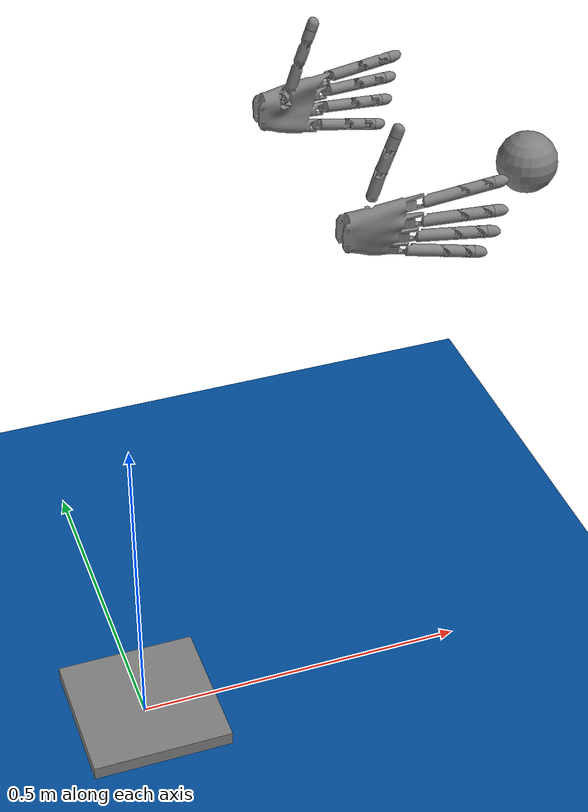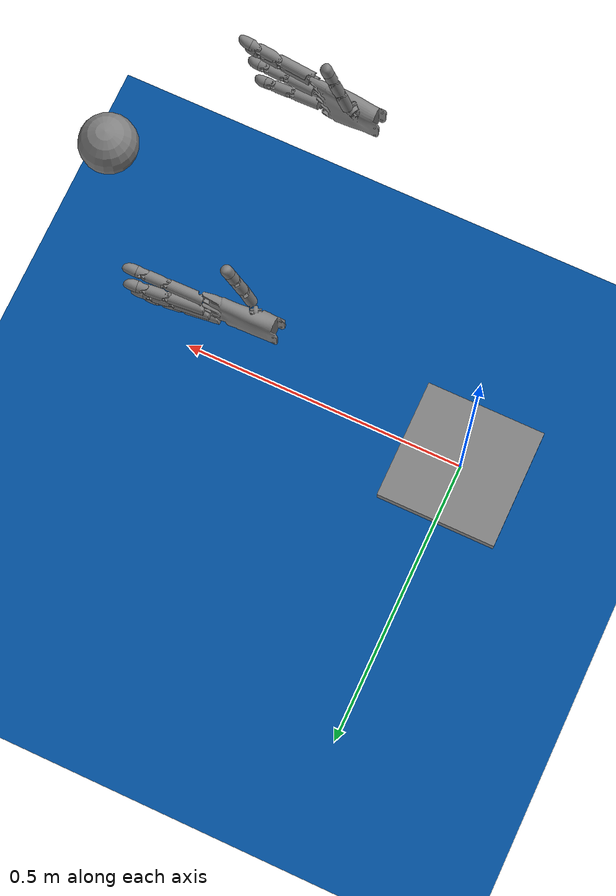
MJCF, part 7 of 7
<exclude body1="mjlab scene_worldbody_robot_pelvis_robot_waist_yaw_link_robot_waist_roll_link_robot_torso_link_robot_left_shoulder_pitch_link_robot_left_shoulder_roll_link_robot_left_shoulder_yaw_link_robot_left_elbow_link_robot_left_wrist_roll_link_robot_left_wrist_pitch_link_robot_left_wrist_yaw_link" body2="mjlab scene_worldbody_robot_pelvis_robot_waist_yaw_link_robot_waist_roll_link_robot_torso_link_robot_right_shoulder_pitch_link_robot_right_shoulder_roll_link_robot_right_shoulder_yaw_link_robot_right_elbow_link_robot_right_wrist_roll_link_robot_right_wrist_pitch_link_robot_right_wrist_yaw_link_robot_xhand_mount_right_robot_right_palm_link_robot_right_finger5_link1_robot_right_finger5_link2_robot_right_finger5_link3_robot_right_finger5_link4_robot_right_finger5_tip"/>
    <exclude body1="mjlab scene_worldbody_robot_pelvis_robot_waist_yaw_link_robot_waist_roll_link_robot_torso_link_robot_left_shoulder_pitch_link_robot_left_shoulder_roll_link_robot_left_shoulder_yaw_link_robot_left_elbow_link_robot_left_wrist_roll_link_robot_left_wrist_pitch_link_robot_left_wrist_yaw_link" body2="mjlab scene_worldbody_table_mocap_base"/>
    <exclude body1="mjlab scene_worldbody_robot_pelvis_robot_waist_yaw_link_robot_waist_roll_link_robot_torso_link_robot_left_shoulder_pitch_link_robot_left_shoulder_roll_link_robot_left_shoulder_yaw_link_robot_left_elbow_link_robot_left_wrist_roll_link_robot_left_wrist_pitch_link_robot_left_wrist_yaw_link_robot_xhand_mount_left" body2="mjlab scene_worldbody_robot_pelvis_robot_waist_yaw_link_robot_waist_roll_link_robot_torso_link_robot_left_shoulder_pitch_link_robot_left_shoulder_roll_link_robot_left_shoulder_yaw_link_robot_left_elbow_link_robot_left_wrist_roll_link_robot_left_wrist_pitch_link_robot_left_wrist_yaw_link_robot_xhand_mount_left_robot_left_palm_link"/>
    <exclude body1="mjlab scene_worldbody_robot_pelvis_robot_waist_yaw_link_robot_waist_roll_link_robot_torso_link_robot_left_shoulder_pitch_link_robot_left_shoulder_roll_link_robot_left_shoulder_yaw_link_robot_left_elbow_link_robot_left_wrist_roll_link_robot_left_wrist_pitch_link_robot_left_wrist_yaw_link_robot_xhand_mount_left" body2="mjlab scene_worldbody_robot_pelvis_robot_waist_yaw_link_robot_waist_roll_link_robot_torso_link_robot_left_shoulder_pitch_link_robot_left_shoulder_roll_link_robot_left_shoulder_yaw_link_robot_left_elbow_link_robot_left_wrist_roll_link_robot_left_wrist_pitch_link_robot_left_wrist_yaw_link_robot_xhand_mount_left_robot_left_palm_link_robot_left_finger1_link1"/>
    <exclude body1="mjlab scene_worldbody_robot_pelvis_robot_waist_yaw_link_robot_waist_roll_link_robot_torso_link_robot_left_shoulder_pitch_link_robot_left_shoulder_roll_link_robot_left_shoulder_yaw_link_robot_left_elbow_link_robot_left_wrist_roll_link_robot_left_wrist_pitch_link_robot_left_wrist_yaw_link_robot_xhand_mount_left" body2="mjlab scene_worldbody_robot_pelvis_robot_waist_yaw_link_robot_waist_roll_link_robot_torso_link_robot_left_shoulder_pitch_link_robot_left_shoulder_roll_link_robot_left_shoulder_yaw_link_robot_left_elbow_link_robot_left_wrist_roll_link_robot_left_wrist_pitch_link_robot_left_wrist_yaw_link_robot_xhand_mount_left_robot_left_palm_link_robot_left_finger1_link1_robot_left_finger1_link2"/>
    <exclude body1="mjlab scene_worldbody_robot_pelvis_robot_waist_yaw_link_robot_waist_roll_link_robot_torso_link_robot_left_shoulder_pitch_link_robot_left_shoulder_roll_link_robot_left_shoulder_yaw_link_robot_left_elbow_link_robot_left_wrist_roll_link_robot_left_wrist_pitch_link_robot_left_wrist_yaw_link_robot_xhand_mount_left" body2="mjlab scene_worldbody_robot_pelvis_robot_waist_yaw_link_robot_waist_roll_link_robot_torso_link_robot_left_shoulder_pitch_link_robot_left_shoulder_roll_link_robot_left_shoulder_yaw_link_robot_left_elbow_link_robot_left_wrist_roll_link_robot_left_wrist_pitch_link_robot_left_wrist_yaw_link_robot_xhand_mount_left_robot_left_palm_link_robot_left_finger1_link1_robot_left_finger1_link2_robot_left_finger1_link3"/>
    <exclude body1="mjlab scene_worldbody_robot_pelvis_robot_waist_yaw_link_robot_waist_roll_link_robot_torso_link_robot_left_shoulder_pitch_link_robot_left_shoulder_roll_link_robot_left_shoulder_yaw_link_robot_left_elbow_link_robot_left_wrist_roll_link_robot_left_wrist_pitch_link_robot_left_wrist_yaw_link_robot_xhand_mount_left" body2="mjlab scene_worldbody_robot_pelvis_robot_waist_yaw_link_robot_waist_roll_link_robot_torso_link_robot_left_shoulder_pitch_link_robot_left_shoulder_roll_link_robot_left_shoulder_yaw_link_robot_left_elbow_link_robot_left_wrist_roll_link_robot_left_wrist_pitch_link_robot_left_wrist_yaw_link_robot_xhand_mount_left_robot_left_palm_link_robot_left_finger1_link1_robot_left_finger1_link2_robot_left_finger1_link3_robot_left_finger1_link4"/>
    <exclude body1="mjlab scene_worldbody_robot_pelvis_robot_waist_yaw_link_robot_waist_roll_link_robot_torso_link_robot_left_shoulder_pitch_link_robot_left_shoulder_roll_link_robot_left_shoulder_yaw_link_robot_left_elbow_link_robot_left_wrist_roll_link_robot_left_wrist_pitch_link_robot_left_wrist_yaw_link_robot_xhand_mount_left" body2="mjlab scene_worldbody_robot_pelvis_robot_waist_yaw_link_robot_waist_roll_link_robot_torso_link_robot_left_shoulder_pitch_link_robot_left_shoulder_roll_link_robot_left_shoulder_yaw_link_robot_left_elbow_link_robot_left_wrist_roll_link_robot_left_wrist_pitch_link_robot_left_wrist_yaw_link_robot_xhand_mount_left_robot_left_palm_link_robot_left_finger1_link1_robot_left_finger1_link2_robot_left_finger1_link3_robot_left_finger1_link4_robot_left_finger1_tip"/>
    <exclude body1="mjlab scene_worldbody_robot_pelvis_robot_waist_yaw_link_robot_waist_roll_link_robot_torso_link_robot_left_shoulder_pitch_link_robot_left_shoulder_roll_link_robot_left_shoulder_yaw_link_robot_left_elbow_link_robot_left_wrist_roll_link_robot_left_wrist_pitch_link_robot_left_wrist_yaw_link_robot_xhand_mount_left" body2="mjlab scene_worldbody_robot_pelvis_robot_waist_yaw_link_robot_waist_roll_link_robot_torso_link_robot_left_shoulder_pitch_link_robot_left_shoulder_roll_link_robot_left_shoulder_yaw_link_robot_left_elbow_link_robot_left_wrist_roll_link_robot_left_wrist_pitch_link_robot_left_wrist_yaw_link_robot_xhand_mount_left_robot_left_palm_link_robot_left_finger2_link1"/>
    <exclude body1="mjlab scene_worldbody_robot_pelvis_robot_waist_yaw_link_robot_waist_roll_link_robot_torso_link_robot_left_shoulder_pitch_link_robot_left_shoulder_roll_link_robot_left_shoulder_yaw_link_robot_left_elbow_link_robot_left_wrist_roll_link_robot_left_wrist_pitch_link_robot_left_wrist_yaw_link_robot_xhand_mount_left" body2="mjlab scene_worldbody_robot_pelvis_robot_waist_yaw_link_robot_waist_roll_link_robot_torso_link_robot_left_shoulder_pitch_link_robot_left_shoulder_roll_link_robot_left_shoulder_yaw_link_robot_left_elbow_link_robot_left_wrist_roll_link_robot_left_wrist_pitch_link_robot_left_wrist_yaw_link_robot_xhand_mount_left_robot_left_palm_link_robot_left_finger2_link1_robot_left_finger2_link2"/>
    <exclude body1="mjlab scene_worldbody_robot_pelvis_robot_waist_yaw_link_robot_waist_roll_link_robot_torso_link_robot_left_shoulder_pitch_link_robot_left_shoulder_roll_link_robot_left_shoulder_yaw_link_robot_left_elbow_link_robot_left_wrist_roll_link_robot_left_wrist_pitch_link_robot_left_wrist_yaw_link_robot_xhand_mount_left" body2="mjlab scene_worldbody_robot_pelvis_robot_waist_yaw_link_robot_waist_roll_link_robot_torso_link_robot_left_shoulder_pitch_link_robot_left_shoulder_roll_link_robot_left_shoulder_yaw_link_robot_left_elbow_link_robot_left_wrist_roll_link_robot_left_wrist_pitch_link_robot_left_wrist_yaw_link_robot_xhand_mount_left_robot_left_palm_link_robot_left_finger2_link1_robot_left_finger2_link2_robot_left_finger2_link3"/>
    <exclude body1="mjlab scene_worldbody_robot_pelvis_robot_waist_yaw_link_robot_waist_roll_link_robot_torso_link_robot_left_shoulder_pitch_link_robot_left_shoulder_roll_link_robot_left_shoulder_yaw_link_robot_left_elbow_link_robot_left_wrist_roll_link_robot_left_wrist_pitch_link_robot_left_wrist_yaw_link_robot_xhand_mount_left" body2="mjlab scene_worldbody_robot_pelvis_robot_waist_yaw_link_robot_waist_roll_link_robot_torso_link_robot_left_shoulder_pitch_link_robot_left_shoulder_roll_link_robot_left_shoulder_yaw_link_robot_left_elbow_link_robot_left_wrist_roll_link_robot_left_wrist_pitch_link_robot_left_wrist_yaw_link_robot_xhand_mount_left_robot_left_palm_link_robot_left_finger2_link1_robot_left_finger2_link2_robot_left_finger2_link3_robot_left_finger2_link4"/>
    <exclude body1="mjlab scene_worldbody_robot_pelvis_robot_waist_yaw_link_robot_waist_roll_link_robot_torso_link_robot_left_shoulder_pitch_link_robot_left_shoulder_roll_link_robot_left_shoulder_yaw_link_robot_left_elbow_link_robot_left_wrist_roll_link_robot_left_wrist_pitch_link_robot_left_wrist_yaw_link_robot_xhand_mount_left" body2="mjlab scene_worldbody_robot_pelvis_robot_waist_yaw_link_robot_waist_roll_link_robot_torso_link_robot_left_shoulder_pitch_link_robot_left_shoulder_roll_link_robot_left_shoulder_yaw_link_robot_left_elbow_link_robot_left_wrist_roll_link_robot_left_wrist_pitch_link_robot_left_wrist_yaw_link_robot_xhand_mount_left_robot_left_palm_link_robot_left_finger2_link1_robot_left_finger2_link2_robot_left_finger2_link3_robot_left_finger2_link4_robot_left_finger2_tip"/>
    <exclude body1="mjlab scene_worldbody_robot_pelvis_robot_waist_yaw_link_robot_waist_roll_link_robot_torso_link_robot_left_shoulder_pitch_link_robot_left_shoulder_roll_link_robot_left_shoulder_yaw_link_robot_left_elbow_link_robot_left_wrist_roll_link_robot_left_wrist_pitch_link_robot_left_wrist_yaw_link_robot_xhand_mount_left" body2="mjlab scene_worldbody_robot_pelvis_robot_waist_yaw_link_robot_waist_roll_link_robot_torso_link_robot_left_shoulder_pitch_link_robot_left_shoulder_roll_link_robot_left_shoulder_yaw_link_robot_left_elbow_link_robot_left_wrist_roll_link_robot_left_wrist_pitch_link_robot_left_wrist_yaw_link_robot_xhand_mount_left_robot_left_palm_link_robot_left_finger3_link1"/>
    <exclude body1="mjlab scene_worldbody_robot_pelvis_robot_waist_yaw_link_robot_waist_roll_link_robot_torso_link_robot_left_shoulder_pitch_link_robot_left_shoulder_roll_link_robot_left_shoulder_yaw_link_robot_left_elbow_link_robot_left_wrist_roll_link_robot_left_wrist_pitch_link_robot_left_wrist_yaw_link_robot_xhand_mount_left" body2="mjlab scene_worldbody_robot_pelvis_robot_waist_yaw_link_robot_waist_roll_link_robot_torso_link_robot_left_shoulder_pitch_link_robot_left_shoulder_roll_link_robot_left_shoulder_yaw_link_robot_left_elbow_link_robot_left_wrist_roll_link_robot_left_wrist_pitch_link_robot_left_wrist_yaw_link_robot_xhand_mount_left_robot_left_palm_link_robot_left_finger3_link1_robot_left_finger3_link2"/>
    <exclude body1="mjlab scene_worldbody_robot_pelvis_robot_waist_yaw_link_robot_waist_roll_link_robot_torso_link_robot_left_shoulder_pitch_link_robot_left_shoulder_roll_link_robot_left_shoulder_yaw_link_robot_left_elbow_link_robot_left_wrist_roll_link_robot_left_wrist_pitch_link_robot_left_wrist_yaw_link_robot_xhand_mount_left" body2="mjlab scene_worldbody_robot_pelvis_robot_waist_yaw_link_robot_waist_roll_link_robot_torso_link_robot_left_shoulder_pitch_link_robot_left_shoulder_roll_link_robot_left_shoulder_yaw_link_robot_left_elbow_link_robot_left_wrist_roll_link_robot_left_wrist_pitch_link_robot_left_wrist_yaw_link_robot_xhand_mount_left_robot_left_palm_link_robot_left_finger3_link1_robot_left_finger3_link2_robot_left_finger3_link3"/>
    <exclude body1="mjlab scene_worldbody_robot_pelvis_robot_waist_yaw_link_robot_waist_roll_link_robot_torso_link_robot_left_shoulder_pitch_link_robot_left_shoulder_roll_link_robot_left_shoulder_yaw_link_robot_left_elbow_link_robot_left_wrist_roll_link_robot_left_wrist_pitch_link_robot_left_wrist_yaw_link_robot_xhand_mount_left" body2="mjlab scene_worldbody_robot_pelvis_robot_waist_yaw_link_robot_waist_roll_link_robot_torso_link_robot_left_shoulder_pitch_link_robot_left_shoulder_roll_link_robot_left_shoulder_yaw_link_robot_left_elbow_link_robot_left_wrist_roll_link_robot_left_wrist_pitch_link_robot_left_wrist_yaw_link_robot_xhand_mount_left_robot_left_palm_link_robot_left_finger3_link1_robot_left_finger3_link2_robot_left_finger3_link3_robot_left_finger3_link4"/>
    <exclude body1="mjlab scene_worldbody_robot_pelvis_robot_waist_yaw_link_robot_waist_roll_link_robot_torso_link_robot_left_shoulder_pitch_link_robot_left_shoulder_roll_link_robot_left_shoulder_yaw_link_robot_left_elbow_link_robot_left_wrist_roll_link_robot_left_wrist_pitch_link_robot_left_wrist_yaw_link_robot_xhand_mount_left" body2="mjlab scene_worldbody_robot_pelvis_robot_waist_yaw_link_robot_waist_roll_link_robot_torso_link_robot_left_shoulder_pitch_link_robot_left_shoulder_roll_link_robot_left_shoulder_yaw_link_robot_left_elbow_link_robot_left_wrist_roll_link_robot_left_wrist_pitch_link_robot_left_wrist_yaw_link_robot_xhand_mount_left_robot_left_palm_link_robot_left_finger3_link1_robot_left_finger3_link2_robot_left_finger3_link3_robot_left_finger3_link4_robot_left_finger3_tip"/>
    <exclude body1="mjlab scene_worldbody_robot_pelvis_robot_waist_yaw_link_robot_waist_roll_link_robot_torso_link_robot_left_shoulder_pitch_link_robot_left_shoulder_roll_link_robot_left_shoulder_yaw_link_robot_left_elbow_link_robot_left_wrist_roll_link_robot_left_wrist_pitch_link_robot_left_wrist_yaw_link_robot_xhand_mount_left" body2="mjlab scene_worldbody_robot_pelvis_robot_waist_yaw_link_robot_waist_roll_link_robot_torso_link_robot_left_shoulder_pitch_link_robot_left_shoulder_roll_link_robot_left_shoulder_yaw_link_robot_left_elbow_link_robot_left_wrist_roll_link_robot_left_wrist_pitch_link_robot_left_wrist_yaw_link_robot_xhand_mount_left_robot_left_palm_link_robot_left_finger4_link1"/>
    <exclude body1="mjlab scene_worldbody_robot_pelvis_robot_waist_yaw_link_robot_waist_roll_link_robot_torso_link_robot_left_shoulder_pitch_link_robot_left_shoulder_roll_link_robot_left_shoulder_yaw_link_robot_left_elbow_link_robot_left_wrist_roll_link_robot_left_wrist_pitch_link_robot_left_wrist_yaw_link_robot_xhand_mount_left" body2="mjlab scene_worldbody_robot_pelvis_robot_waist_yaw_link_robot_waist_roll_link_robot_torso_link_robot_left_shoulder_pitch_link_robot_left_shoulder_roll_link_robot_left_shoulder_yaw_link_robot_left_elbow_link_robot_left_wrist_roll_link_robot_left_wrist_pitch_link_robot_left_wrist_yaw_link_robot_xhand_mount_left_robot_left_palm_link_robot_left_finger4_link1_robot_left_finger4_link2"/>
    <exclude body1="mjlab scene_worldbody_robot_pelvis_robot_waist_yaw_link_robot_waist_roll_link_robot_torso_link_robot_left_shoulder_pitch_link_robot_left_shoulder_roll_link_robot_left_shoulder_yaw_link_robot_left_elbow_link_robot_left_wrist_roll_link_robot_left_wrist_pitch_link_robot_left_wrist_yaw_link_robot_xhand_mount_left" body2="mjlab scene_worldbody_robot_pelvis_robot_waist_yaw_link_robot_waist_roll_link_robot_torso_link_robot_left_shoulder_pitch_link_robot_left_shoulder_roll_link_robot_left_shoulder_yaw_link_robot_left_elbow_link_robot_left_wrist_roll_link_robot_left_wrist_pitch_link_robot_left_wrist_yaw_link_robot_xhand_mount_left_robot_left_palm_link_robot_left_finger4_link1_robot_left_finger4_link2_robot_left_finger4_link3"/>
    <exclude body1="mjlab scene_worldbody_robot_pelvis_robot_waist_yaw_link_robot_waist_roll_link_robot_torso_link_robot_left_shoulder_pitch_link_robot_left_shoulder_roll_link_robot_left_shoulder_yaw_link_robot_left_elbow_link_robot_left_wrist_roll_link_robot_left_wrist_pitch_link_robot_left_wrist_yaw_link_robot_xhand_mount_left" body2="mjlab scene_worldbody_robot_pelvis_robot_waist_yaw_link_robot_waist_roll_link_robot_torso_link_robot_left_shoulder_pitch_link_robot_left_shoulder_roll_link_robot_left_shoulder_yaw_link_robot_left_elbow_link_robot_left_wrist_roll_link_robot_left_wrist_pitch_link_robot_left_wrist_yaw_link_robot_xhand_mount_left_robot_left_palm_link_robot_left_finger4_link1_robot_left_finger4_link2_robot_left_finger4_link3_robot_left_finger4_link4"/>
    <exclude body1="mjlab scene_worldbody_robot_pelvis_robot_waist_yaw_link_robot_waist_roll_link_robot_torso_link_robot_left_shoulder_pitch_link_robot_left_shoulder_roll_link_robot_left_shoulder_yaw_link_robot_left_elbow_link_robot_left_wrist_roll_link_robot_left_wrist_pitch_link_robot_left_wrist_yaw_link_robot_xhand_mount_left" body2="mjlab scene_worldbody_robot_pelvis_robot_waist_yaw_link_robot_waist_roll_link_robot_torso_link_robot_left_shoulder_pitch_link_robot_left_shoulder_roll_link_robot_left_shoulder_yaw_link_robot_left_elbow_link_robot_left_wrist_roll_link_robot_left_wrist_pitch_link_robot_left_wrist_yaw_link_robot_xhand_mount_left_robot_left_palm_link_robot_left_finger4_link1_robot_left_finger4_link2_robot_left_finger4_link3_robot_left_finger4_link4_robot_left_finger4_tip"/>
    <exclude body1="mjlab scene_worldbody_robot_pelvis_robot_waist_yaw_link_robot_waist_roll_link_robot_torso_link_robot_left_shoulder_pitch_link_robot_left_shoulder_roll_link_robot_left_shoulder_yaw_link_robot_left_elbow_link_robot_left_wrist_roll_link_robot_left_wrist_pitch_link_robot_left_wrist_yaw_link_robot_xhand_mount_left" body2="mjlab scene_worldbody_robot_pelvis_robot_waist_yaw_link_robot_waist_roll_link_robot_torso_link_robot_left_shoulder_pitch_link_robot_left_shoulder_roll_link_robot_left_shoulder_yaw_link_robot_left_elbow_link_robot_left_wrist_roll_link_robot_left_wrist_pitch_link_robot_left_wrist_yaw_link_robot_xhand_mount_left_robot_left_palm_link_robot_left_finger5_link1"/>
    <exclude body1="mjlab scene_worldbody_robot_pelvis_robot_waist_yaw_link_robot_waist_roll_link_robot_torso_link_robot_left_shoulder_pitch_link_robot_left_shoulder_roll_link_robot_left_shoulder_yaw_link_robot_left_elbow_link_robot_left_wrist_roll_link_robot_left_wrist_pitch_link_robot_left_wrist_yaw_link_robot_xhand_mount_left" body2="mjlab scene_worldbody_robot_pelvis_robot_waist_yaw_link_robot_waist_roll_link_robot_torso_link_robot_left_shoulder_pitch_link_robot_left_shoulder_roll_link_robot_left_shoulder_yaw_link_robot_left_elbow_link_robot_left_wrist_roll_link_robot_left_wrist_pitch_link_robot_left_wrist_yaw_link_robot_xhand_mount_left_robot_left_palm_link_robot_left_finger5_link1_robot_left_finger5_link2"/>
    <exclude body1="mjlab scene_worldbody_robot_pelvis_robot_waist_yaw_link_robot_waist_roll_link_robot_torso_link_robot_left_shoulder_pitch_link_robot_left_shoulder_roll_link_robot_left_shoulder_yaw_link_robot_left_elbow_link_robot_left_wrist_roll_link_robot_left_wrist_pitch_link_robot_left_wrist_yaw_link_robot_xhand_mount_left" body2="mjlab scene_worldbody_robot_pelvis_robot_waist_yaw_link_robot_waist_roll_link_robot_torso_link_robot_left_shoulder_pitch_link_robot_left_shoulder_roll_link_robot_left_shoulder_yaw_link_robot_left_elbow_link_robot_left_wrist_roll_link_robot_left_wrist_pitch_link_robot_left_wrist_yaw_link_robot_xhand_mount_left_robot_left_palm_link_robot_left_finger5_link1_robot_left_finger5_link2_robot_left_finger5_link3"/>
    <exclude body1="mjlab scene_worldbody_robot_pelvis_robot_waist_yaw_link_robot_waist_roll_link_robot_torso_link_robot_left_shoulder_pitch_link_robot_left_shoulder_roll_link_robot_left_shoulder_yaw_link_robot_left_elbow_link_robot_left_wrist_roll_link_robot_left_wrist_pitch_link_robot_left_wrist_yaw_link_robot_xhand_mount_left" body2="mjlab scene_worldbody_robot_pelvis_robot_waist_yaw_link_robot_waist_roll_link_robot_torso_link_robot_left_shoulder_pitch_link_robot_left_shoulder_roll_link_robot_left_shoulder_yaw_link_robot_left_elbow_link_robot_left_wrist_roll_link_robot_left_wrist_pitch_link_robot_left_wrist_yaw_link_robot_xhand_mount_left_robot_left_palm_link_robot_left_finger5_link1_robot_left_finger5_link2_robot_left_finger5_link3_robot_left_finger5_link4"/>
    <exclude body1="mjlab scene_worldbody_robot_pelvis_robot_waist_yaw_link_robot_waist_roll_link_robot_torso_link_robot_left_shoulder_pitch_link_robot_left_shoulder_roll_link_robot_left_shoulder_yaw_link_robot_left_elbow_link_robot_left_wrist_roll_link_robot_left_wrist_pitch_link_robot_left_wrist_yaw_link_robot_xhand_mount_left" body2="mjlab scene_worldbody_robot_pelvis_robot_waist_yaw_link_robot_waist_roll_link_robot_torso_link_robot_left_shoulder_pitch_link_robot_left_shoulder_roll_link_robot_left_shoulder_yaw_link_robot_left_elbow_link_robot_left_wrist_roll_link_robot_left_wrist_pitch_link_robot_left_wrist_yaw_link_robot_xhand_mount_left_robot_left_palm_link_robot_left_finger5_link1_robot_left_finger5_link2_robot_left_finger5_link3_robot_left_finger5_link4_robot_left_finger5_tip"/>
    <exclude body1="mjlab scene_worldbody_robot_pelvis_robot_waist_yaw_link_robot_waist_roll_link_robot_torso_link_robot_left_shoulder_pitch_link_robot_left_shoulder_roll_link_robot_left_shoulder_yaw_link_robot_left_elbow_link_robot_left_wrist_roll_link_robot_left_wrist_pitch_link_robot_left_wrist_yaw_link_robot_xhand_mount_left" body2="mjlab scene_worldbody_robot_pelvis_robot_waist_yaw_link_robot_waist_roll_link_robot_torso_link_robot_right_shoulder_pitch_link"/>
    <exclude body1="mjlab scene_worldbody_robot_pelvis_robot_waist_yaw_link_robot_waist_roll_link_robot_torso_link_robot_left_shoulder_pitch_link_robot_left_shoulder_roll_link_robot_left_shoulder_yaw_link_robot_left_elbow_link_robot_left_wrist_roll_link_robot_left_wrist_pitch_link_robot_left_wrist_yaw_link_robot_xhand_mount_left" body2="mjlab scene_worldbody_robot_pelvis_robot_waist_yaw_link_robot_waist_roll_link_robot_torso_link_robot_right_shoulder_pitch_link_robot_right_shoulder_roll_link"/>
    <exclude body1="mjlab scene_worldbody_robot_pelvis_robot_waist_yaw_link_robot_waist_roll_link_robot_torso_link_robot_left_shoulder_pitch_link_robot_left_shoulder_roll_link_robot_left_shoulder_yaw_link_robot_left_elbow_link_robot_left_wrist_roll_link_robot_left_wrist_pitch_link_robot_left_wrist_yaw_link_robot_xhand_mount_left" body2="mjlab scene_worldbody_robot_pelvis_robot_waist_yaw_link_robot_waist_roll_link_robot_torso_link_robot_right_shoulder_pitch_link_robot_right_shoulder_roll_link_robot_right_shoulder_yaw_link"/>
    <exclude body1="mjlab scene_worldbody_robot_pelvis_robot_waist_yaw_link_robot_waist_roll_link_robot_torso_link_robot_left_shoulder_pitch_link_robot_left_shoulder_roll_link_robot_left_shoulder_yaw_link_robot_left_elbow_link_robot_left_wrist_roll_link_robot_left_wrist_pitch_link_robot_left_wrist_yaw_link_robot_xhand_mount_left" body2="mjlab scene_worldbody_robot_pelvis_robot_waist_yaw_link_robot_waist_roll_link_robot_torso_link_robot_right_shoulder_pitch_link_robot_right_shoulder_roll_link_robot_right_shoulder_yaw_link_robot_right_elbow_link"/>
    <exclude body1="mjlab scene_worldbody_robot_pelvis_robot_waist_yaw_link_robot_waist_roll_link_robot_torso_link_robot_left_shoulder_pitch_link_robot_left_shoulder_roll_link_robot_left_shoulder_yaw_link_robot_left_elbow_link_robot_left_wrist_roll_link_robot_left_wrist_pitch_link_robot_left_wrist_yaw_link_robot_xhand_mount_left" body2="mjlab scene_worldbody_robot_pelvis_robot_waist_yaw_link_robot_waist_roll_link_robot_torso_link_robot_right_shoulder_pitch_link_robot_right_shoulder_roll_link_robot_right_shoulder_yaw_link_robot_right_elbow_link_robot_right_wrist_roll_link"/>
    <exclude body1="mjlab scene_worldbody_robot_pelvis_robot_waist_yaw_link_robot_waist_roll_link_robot_torso_link_robot_left_shoulder_pitch_link_robot_left_shoulder_roll_link_robot_left_shoulder_yaw_link_robot_left_elbow_link_robot_left_wrist_roll_link_robot_left_wrist_pitch_link_robot_left_wrist_yaw_link_robot_xhand_mount_left" body2="mjlab scene_worldbody_robot_pelvis_robot_waist_yaw_link_robot_waist_roll_link_robot_torso_link_robot_right_shoulder_pitch_link_robot_right_shoulder_roll_link_robot_right_shoulder_yaw_link_robot_right_elbow_link_robot_right_wrist_roll_link_robot_right_wrist_pitch_link"/>
    <exclude body1="mjlab scene_worldbody_robot_pelvis_robot_waist_yaw_link_robot_waist_roll_link_robot_torso_link_robot_left_shoulder_pitch_link_robot_left_shoulder_roll_link_robot_left_shoulder_yaw_link_robot_left_elbow_link_robot_left_wrist_roll_link_robot_left_wrist_pitch_link_robot_left_wrist_yaw_link_robot_xhand_mount_left" body2="mjlab scene_worldbody_robot_pelvis_robot_waist_yaw_link_robot_waist_roll_link_robot_torso_link_robot_right_shoulder_pitch_link_robot_right_shoulder_roll_link_robot_right_shoulder_yaw_link_robot_right_elbow_link_robot_right_wrist_roll_link_robot_right_wrist_pitch_link_robot_right_wrist_yaw_link"/>
    <exclude body1="mjlab scene_worldbody_robot_pelvis_robot_waist_yaw_link_robot_waist_roll_link_robot_torso_link_robot_left_shoulder_pitch_link_robot_left_shoulder_roll_link_robot_left_shoulder_yaw_link_robot_left_elbow_link_robot_left_wrist_roll_link_robot_left_wrist_pitch_link_robot_left_wrist_yaw_link_robot_xhand_mount_left" body2="mjlab scene_worldbody_robot_pelvis_robot_waist_yaw_link_robot_waist_roll_link_robot_torso_link_robot_right_shoulder_pitch_link_robot_right_shoulder_roll_link_robot_right_shoulder_yaw_link_robot_right_elbow_link_robot_right_wrist_roll_link_robot_right_wrist_pitch_link_robot_right_wrist_yaw_link_robot_xhand_mount_right"/>
    <exclude body1="mjlab scene_worldbody_robot_pelvis_robot_waist_yaw_link_robot_waist_roll_link_robot_torso_link_robot_left_shoulder_pitch_link_robot_left_shoulder_roll_link_robot_left_shoulder_yaw_link_robot_left_elbow_link_robot_left_wrist_roll_link_robot_left_wrist_pitch_link_robot_left_wrist_yaw_link_robot_xhand_mount_left" body2="mjlab scene_worldbody_robot_pelvis_robot_waist_yaw_link_robot_waist_roll_link_robot_torso_link_robot_right_shoulder_pitch_link_robot_right_shoulder_roll_link_robot_right_shoulder_yaw_link_robot_right_elbow_link_robot_right_wrist_roll_link_robot_right_wrist_pitch_link_robot_right_wrist_yaw_link_robot_xhand_mount_right_robot_right_palm_link"/>
    <exclude body1="mjlab scene_worldbody_robot_pelvis_robot_waist_yaw_link_robot_waist_roll_link_robot_torso_link_robot_left_shoulder_pitch_link_robot_left_shoulder_roll_link_robot_left_shoulder_yaw_link_robot_left_elbow_link_robot_left_wrist_roll_link_robot_left_wrist_pitch_link_robot_left_wrist_yaw_link_robot_xhand_mount_left" body2="mjlab scene_worldbody_robot_pelvis_robot_waist_yaw_link_robot_waist_roll_link_robot_torso_link_robot_right_shoulder_pitch_link_robot_right_shoulder_roll_link_robot_right_shoulder_yaw_link_robot_right_elbow_link_robot_right_wrist_roll_link_robot_right_wrist_pitch_link_robot_right_wrist_yaw_link_robot_xhand_mount_right_robot_right_palm_link_robot_right_finger1_link1"/>
    <exclude body1="mjlab scene_worldbody_robot_pelvis_robot_waist_yaw_link_robot_waist_roll_link_robot_torso_link_robot_left_shoulder_pitch_link_robot_left_shoulder_roll_link_robot_left_shoulder_yaw_link_robot_left_elbow_link_robot_left_wrist_roll_link_robot_left_wrist_pitch_link_robot_left_wrist_yaw_link_robot_xhand_mount_left" body2="mjlab scene_worldbody_robot_pelvis_robot_waist_yaw_link_robot_waist_roll_link_robot_torso_link_robot_right_shoulder_pitch_link_robot_right_shoulder_roll_link_robot_right_shoulder_yaw_link_robot_right_elbow_link_robot_right_wrist_roll_link_robot_right_wrist_pitch_link_robot_right_wrist_yaw_link_robot_xhand_mount_right_robot_right_palm_link_robot_right_finger1_link1_robot_right_finger1_link2"/>
    <exclude body1="mjlab scene_worldbody_robot_pelvis_robot_waist_yaw_link_robot_waist_roll_link_robot_torso_link_robot_left_shoulder_pitch_link_robot_left_shoulder_roll_link_robot_left_shoulder_yaw_link_robot_left_elbow_link_robot_left_wrist_roll_link_robot_left_wrist_pitch_link_robot_left_wrist_yaw_link_robot_xhand_mount_left" body2="mjlab scene_worldbody_robot_pelvis_robot_waist_yaw_link_robot_waist_roll_link_robot_torso_link_robot_right_shoulder_pitch_link_robot_right_shoulder_roll_link_robot_right_shoulder_yaw_link_robot_right_elbow_link_robot_right_wrist_roll_link_robot_right_wrist_pitch_link_robot_right_wrist_yaw_link_robot_xhand_mount_right_robot_right_palm_link_robot_right_finger1_link1_robot_right_finger1_link2_robot_right_finger1_link3"/>
    <exclude body1="mjlab scene_worldbody_robot_pelvis_robot_waist_yaw_link_robot_waist_roll_link_robot_torso_link_robot_left_shoulder_pitch_link_robot_left_shoulder_roll_link_robot_left_shoulder_yaw_link_robot_left_elbow_link_robot_left_wrist_roll_link_robot_left_wrist_pitch_link_robot_left_wrist_yaw_link_robot_xhand_mount_left" body2="mjlab scene_worldbody_robot_pelvis_robot_waist_yaw_link_robot_waist_roll_link_robot_torso_link_robot_right_shoulder_pitch_link_robot_right_shoulder_roll_link_robot_right_shoulder_yaw_link_robot_right_elbow_link_robot_right_wrist_roll_link_robot_right_wrist_pitch_link_robot_right_wrist_yaw_link_robot_xhand_mount_right_robot_right_palm_link_robot_right_finger1_link1_robot_right_finger1_link2_robot_right_finger1_link3_robot_right_finger1_link4"/>
    <exclude body1="mjlab scene_worldbody_robot_pelvis_robot_waist_yaw_link_robot_waist_roll_link_robot_torso_link_robot_left_shoulder_pitch_link_robot_left_shoulder_roll_link_robot_left_shoulder_yaw_link_robot_left_elbow_link_robot_left_wrist_roll_link_robot_left_wrist_pitch_link_robot_left_wrist_yaw_link_robot_xhand_mount_left" body2="mjlab scene_worldbody_robot_pelvis_robot_waist_yaw_link_robot_waist_roll_link_robot_torso_link_robot_right_shoulder_pitch_link_robot_right_shoulder_roll_link_robot_right_shoulder_yaw_link_robot_right_elbow_link_robot_right_wrist_roll_link_robot_right_wrist_pitch_link_robot_right_wrist_yaw_link_robot_xhand_mount_right_robot_right_palm_link_robot_right_finger1_link1_robot_right_finger1_link2_robot_right_finger1_link3_robot_right_finger1_link4_robot_right_finger1_tip"/>
    <exclude body1="mjlab scene_worldbody_robot_pelvis_robot_waist_yaw_link_robot_waist_roll_link_robot_torso_link_robot_left_shoulder_pitch_link_robot_left_shoulder_roll_link_robot_left_shoulder_yaw_link_robot_left_elbow_link_robot_left_wrist_roll_link_robot_left_wrist_pitch_link_robot_left_wrist_yaw_link_robot_xhand_mount_left" body2="mjlab scene_worldbody_robot_pelvis_robot_waist_yaw_link_robot_waist_roll_link_robot_torso_link_robot_right_shoulder_pitch_link_robot_right_shoulder_roll_link_robot_right_shoulder_yaw_link_robot_right_elbow_link_robot_right_wrist_roll_link_robot_right_wrist_pitch_link_robot_right_wrist_yaw_link_robot_xhand_mount_right_robot_right_palm_link_robot_right_finger2_link1"/>
    <exclude body1="mjlab scene_worldbody_robot_pelvis_robot_waist_yaw_link_robot_waist_roll_link_robot_torso_link_robot_left_shoulder_pitch_link_robot_left_shoulder_roll_link_robot_left_shoulder_yaw_link_robot_left_elbow_link_robot_left_wrist_roll_link_robot_left_wrist_pitch_link_robot_left_wrist_yaw_link_robot_xhand_mount_left" body2="mjlab scene_worldbody_robot_pelvis_robot_waist_yaw_link_robot_waist_roll_link_robot_torso_link_robot_right_shoulder_pitch_link_robot_right_shoulder_roll_link_robot_right_shoulder_yaw_link_robot_right_elbow_link_robot_right_wrist_roll_link_robot_right_wrist_pitch_link_robot_right_wrist_yaw_link_robot_xhand_mount_right_robot_right_palm_link_robot_right_finger2_link1_robot_right_finger2_link2"/>
    <exclude body1="mjlab scene_worldbody_robot_pelvis_robot_waist_yaw_link_robot_waist_roll_link_robot_torso_link_robot_left_shoulder_pitch_link_robot_left_shoulder_roll_link_robot_left_shoulder_yaw_link_robot_left_elbow_link_robot_left_wrist_roll_link_robot_left_wrist_pitch_link_robot_left_wrist_yaw_link_robot_xhand_mount_left" body2="mjlab scene_worldbody_robot_pelvis_robot_waist_yaw_link_robot_waist_roll_link_robot_torso_link_robot_right_shoulder_pitch_link_robot_right_shoulder_roll_link_robot_right_shoulder_yaw_link_robot_right_elbow_link_robot_right_wrist_roll_link_robot_right_wrist_pitch_link_robot_right_wrist_yaw_link_robot_xhand_mount_right_robot_right_palm_link_robot_right_finger2_link1_robot_right_finger2_link2_robot_right_finger2_link3"/>
    <exclude body1="mjlab scene_worldbody_robot_pelvis_robot_waist_yaw_link_robot_waist_roll_link_robot_torso_link_robot_left_shoulder_pitch_link_robot_left_shoulder_roll_link_robot_left_shoulder_yaw_link_robot_left_elbow_link_robot_left_wrist_roll_link_robot_left_wrist_pitch_link_robot_left_wrist_yaw_link_robot_xhand_mount_left" body2="mjlab scene_worldbody_robot_pelvis_robot_waist_yaw_link_robot_waist_roll_link_robot_torso_link_robot_right_shoulder_pitch_link_robot_right_shoulder_roll_link_robot_right_shoulder_yaw_link_robot_right_elbow_link_robot_right_wrist_roll_link_robot_right_wrist_pitch_link_robot_right_wrist_yaw_link_robot_xhand_mount_right_robot_right_palm_link_robot_right_finger2_link1_robot_right_finger2_link2_robot_right_finger2_link3_robot_right_finger2_link4"/>
    <exclude body1="mjlab scene_worldbody_robot_pelvis_robot_waist_yaw_link_robot_waist_roll_link_robot_torso_link_robot_left_shoulder_pitch_link_robot_left_shoulder_roll_link_robot_left_shoulder_yaw_link_robot_left_elbow_link_robot_left_wrist_roll_link_robot_left_wrist_pitch_link_robot_left_wrist_yaw_link_robot_xhand_mount_left" body2="mjlab scene_worldbody_robot_pelvis_robot_waist_yaw_link_robot_waist_roll_link_robot_torso_link_robot_right_shoulder_pitch_link_robot_right_shoulder_roll_link_robot_right_shoulder_yaw_link_robot_right_elbow_link_robot_right_wrist_roll_link_robot_right_wrist_pitch_link_robot_right_wrist_yaw_link_robot_xhand_mount_right_robot_right_palm_link_robot_right_finger2_link1_robot_right_finger2_link2_robot_right_finger2_link3_robot_right_finger2_link4_robot_right_finger2_tip"/>
    <exclude body1="mjlab scene_worldbody_robot_pelvis_robot_waist_yaw_link_robot_waist_roll_link_robot_torso_link_robot_left_shoulder_pitch_link_robot_left_shoulder_roll_link_robot_left_shoulder_yaw_link_robot_left_elbow_link_robot_left_wrist_roll_link_robot_left_wrist_pitch_link_robot_left_wrist_yaw_link_robot_xhand_mount_left" body2="mjlab scene_worldbody_robot_pelvis_robot_waist_yaw_link_robot_waist_roll_link_robot_torso_link_robot_right_shoulder_pitch_link_robot_right_shoulder_roll_link_robot_right_shoulder_yaw_link_robot_right_elbow_link_robot_right_wrist_roll_link_robot_right_wrist_pitch_link_robot_right_wrist_yaw_link_robot_xhand_mount_right_robot_right_palm_link_robot_right_finger3_link1"/>
    <exclude body1="mjlab scene_worldbody_robot_pelvis_robot_waist_yaw_link_robot_waist_roll_link_robot_torso_link_robot_left_shoulder_pitch_link_robot_left_shoulder_roll_link_robot_left_shoulder_yaw_link_robot_left_elbow_link_robot_left_wrist_roll_link_robot_left_wrist_pitch_link_robot_left_wrist_yaw_link_robot_xhand_mount_left" body2="mjlab scene_worldbody_robot_pelvis_robot_waist_yaw_link_robot_waist_roll_link_robot_torso_link_robot_right_shoulder_pitch_link_robot_right_shoulder_roll_link_robot_right_shoulder_yaw_link_robot_right_elbow_link_robot_right_wrist_roll_link_robot_right_wrist_pitch_link_robot_right_wrist_yaw_link_robot_xhand_mount_right_robot_right_palm_link_robot_right_finger3_link1_robot_right_finger3_link2"/>
    <exclude body1="mjlab scene_worldbody_robot_pelvis_robot_waist_yaw_link_robot_waist_roll_link_robot_torso_link_robot_left_shoulder_pitch_link_robot_left_shoulder_roll_link_robot_left_shoulder_yaw_link_robot_left_elbow_link_robot_left_wrist_roll_link_robot_left_wrist_pitch_link_robot_left_wrist_yaw_link_robot_xhand_mount_left" body2="mjlab scene_worldbody_robot_pelvis_robot_waist_yaw_link_robot_waist_roll_link_robot_torso_link_robot_right_shoulder_pitch_link_robot_right_shoulder_roll_link_robot_right_shoulder_yaw_link_robot_right_elbow_link_robot_right_wrist_roll_link_robot_right_wrist_pitch_link_robot_right_wrist_yaw_link_robot_xhand_mount_right_robot_right_palm_link_robot_right_finger3_link1_robot_right_finger3_link2_robot_right_finger3_link3"/>
    <exclude body1="mjlab scene_worldbody_robot_pelvis_robot_waist_yaw_link_robot_waist_roll_link_robot_torso_link_robot_left_shoulder_pitch_link_robot_left_shoulder_roll_link_robot_left_shoulder_yaw_link_robot_left_elbow_link_robot_left_wrist_roll_link_robot_left_wrist_pitch_link_robot_left_wrist_yaw_link_robot_xhand_mount_left" body2="mjlab scene_worldbody_robot_pelvis_robot_waist_yaw_link_robot_waist_roll_link_robot_torso_link_robot_right_shoulder_pitch_link_robot_right_shoulder_roll_link_robot_right_shoulder_yaw_link_robot_right_elbow_link_robot_right_wrist_roll_link_robot_right_wrist_pitch_link_robot_right_wrist_yaw_link_robot_xhand_mount_right_robot_right_palm_link_robot_right_finger3_link1_robot_right_finger3_link2_robot_right_finger3_link3_robot_right_finger3_link4"/>
    <exclude body1="mjlab scene_worldbody_robot_pelvis_robot_waist_yaw_link_robot_waist_roll_link_robot_torso_link_robot_left_shoulder_pitch_link_robot_left_shoulder_roll_link_robot_left_shoulder_yaw_link_robot_left_elbow_link_robot_left_wrist_roll_link_robot_left_wrist_pitch_link_robot_left_wrist_yaw_link_robot_xhand_mount_left" body2="mjlab scene_worldbody_robot_pelvis_robot_waist_yaw_link_robot_waist_roll_link_robot_torso_link_robot_right_shoulder_pitch_link_robot_right_shoulder_roll_link_robot_right_shoulder_yaw_link_robot_right_elbow_link_robot_right_wrist_roll_link_robot_right_wrist_pitch_link_robot_right_wrist_yaw_link_robot_xhand_mount_right_robot_right_palm_link_robot_right_finger3_link1_robot_right_finger3_link2_robot_right_finger3_link3_robot_right_finger3_link4_robot_right_finger3_tip"/>
    <exclude body1="mjlab scene_worldbody_robot_pelvis_robot_waist_yaw_link_robot_waist_roll_link_robot_torso_link_robot_left_shoulder_pitch_link_robot_left_shoulder_roll_link_robot_left_shoulder_yaw_link_robot_left_elbow_link_robot_left_wrist_roll_link_robot_left_wrist_pitch_link_robot_left_wrist_yaw_link_robot_xhand_mount_left" body2="mjlab scene_worldbody_robot_pelvis_robot_waist_yaw_link_robot_waist_roll_link_robot_torso_link_robot_right_shoulder_pitch_link_robot_right_shoulder_roll_link_robot_right_shoulder_yaw_link_robot_right_elbow_link_robot_right_wrist_roll_link_robot_right_wrist_pitch_link_robot_right_wrist_yaw_link_robot_xhand_mount_right_robot_right_palm_link_robot_right_finger4_link1"/>
    <exclude body1="mjlab scene_worldbody_robot_pelvis_robot_waist_yaw_link_robot_waist_roll_link_robot_torso_link_robot_left_shoulder_pitch_link_robot_left_shoulder_roll_link_robot_left_shoulder_yaw_link_robot_left_elbow_link_robot_left_wrist_roll_link_robot_left_wrist_pitch_link_robot_left_wrist_yaw_link_robot_xhand_mount_left" body2="mjlab scene_worldbody_robot_pelvis_robot_waist_yaw_link_robot_waist_roll_link_robot_torso_link_robot_right_shoulder_pitch_link_robot_right_shoulder_roll_link_robot_right_shoulder_yaw_link_robot_right_elbow_link_robot_right_wrist_roll_link_robot_right_wrist_pitch_link_robot_right_wrist_yaw_link_robot_xhand_mount_right_robot_right_palm_link_robot_right_finger4_link1_robot_right_finger4_link2"/>
    <exclude body1="mjlab scene_worldbody_robot_pelvis_robot_waist_yaw_link_robot_waist_roll_link_robot_torso_link_robot_left_shoulder_pitch_link_robot_left_shoulder_roll_link_robot_left_shoulder_yaw_link_robot_left_elbow_link_robot_left_wrist_roll_link_robot_left_wrist_pitch_link_robot_left_wrist_yaw_link_robot_xhand_mount_left" body2="mjlab scene_worldbody_robot_pelvis_robot_waist_yaw_link_robot_waist_roll_link_robot_torso_link_robot_right_shoulder_pitch_link_robot_right_shoulder_roll_link_robot_right_shoulder_yaw_link_robot_right_elbow_link_robot_right_wrist_roll_link_robot_right_wrist_pitch_link_robot_right_wrist_yaw_link_robot_xhand_mount_right_robot_right_palm_link_robot_right_finger4_link1_robot_right_finger4_link2_robot_right_finger4_link3"/>
    <exclude body1="mjlab scene_worldbody_robot_pelvis_robot_waist_yaw_link_robot_waist_roll_link_robot_torso_link_robot_left_shoulder_pitch_link_robot_left_shoulder_roll_link_robot_left_shoulder_yaw_link_robot_left_elbow_link_robot_left_wrist_roll_link_robot_left_wrist_pitch_link_robot_left_wrist_yaw_link_robot_xhand_mount_left" body2="mjlab scene_worldbody_robot_pelvis_robot_waist_yaw_link_robot_waist_roll_link_robot_torso_link_robot_right_shoulder_pitch_link_robot_right_shoulder_roll_link_robot_right_shoulder_yaw_link_robot_right_elbow_link_robot_right_wrist_roll_link_robot_right_wrist_pitch_link_robot_right_wrist_yaw_link_robot_xhand_mount_right_robot_right_palm_link_robot_right_finger4_link1_robot_right_finger4_link2_robot_right_finger4_link3_robot_right_finger4_link4"/>
    <exclude body1="mjlab scene_worldbody_robot_pelvis_robot_waist_yaw_link_robot_waist_roll_link_robot_torso_link_robot_left_shoulder_pitch_link_robot_left_shoulder_roll_link_robot_left_shoulder_yaw_link_robot_left_elbow_link_robot_left_wrist_roll_link_robot_left_wrist_pitch_link_robot_left_wrist_yaw_link_robot_xhand_mount_left" body2="mjlab scene_worldbody_robot_pelvis_robot_waist_yaw_link_robot_waist_roll_link_robot_torso_link_robot_right_shoulder_pitch_link_robot_right_shoulder_roll_link_robot_right_shoulder_yaw_link_robot_right_elbow_link_robot_right_wrist_roll_link_robot_right_wrist_pitch_link_robot_right_wrist_yaw_link_robot_xhand_mount_right_robot_right_palm_link_robot_right_finger4_link1_robot_right_finger4_link2_robot_right_finger4_link3_robot_right_finger4_link4_robot_right_finger4_tip"/>
    <exclude body1="mjlab scene_worldbody_robot_pelvis_robot_waist_yaw_link_robot_waist_roll_link_robot_torso_link_robot_left_shoulder_pitch_link_robot_left_shoulder_roll_link_robot_left_shoulder_yaw_link_robot_left_elbow_link_robot_left_wrist_roll_link_robot_left_wrist_pitch_link_robot_left_wrist_yaw_link_robot_xhand_mount_left" body2="mjlab scene_worldbody_robot_pelvis_robot_waist_yaw_link_robot_waist_roll_link_robot_torso_link_robot_right_shoulder_pitch_link_robot_right_shoulder_roll_link_robot_right_shoulder_yaw_link_robot_right_elbow_link_robot_right_wrist_roll_link_robot_right_wrist_pitch_link_robot_right_wrist_yaw_link_robot_xhand_mount_right_robot_right_palm_link_robot_right_finger5_link1"/>
    <exclude body1="mjlab scene_worldbody_robot_pelvis_robot_waist_yaw_link_robot_waist_roll_link_robot_torso_link_robot_left_shoulder_pitch_link_robot_left_shoulder_roll_link_robot_left_shoulder_yaw_link_robot_left_elbow_link_robot_left_wrist_roll_link_robot_left_wrist_pitch_link_robot_left_wrist_yaw_link_robot_xhand_mount_left" body2="mjlab scene_worldbody_robot_pelvis_robot_waist_yaw_link_robot_waist_roll_link_robot_torso_link_robot_right_shoulder_pitch_link_robot_right_shoulder_roll_link_robot_right_shoulder_yaw_link_robot_right_elbow_link_robot_right_wrist_roll_link_robot_right_wrist_pitch_link_robot_right_wrist_yaw_link_robot_xhand_mount_right_robot_right_palm_link_robot_right_finger5_link1_robot_right_finger5_link2"/>
    <exclude body1="mjlab scene_worldbody_robot_pelvis_robot_waist_yaw_link_robot_waist_roll_link_robot_torso_link_robot_left_shoulder_pitch_link_robot_left_shoulder_roll_link_robot_left_shoulder_yaw_link_robot_left_elbow_link_robot_left_wrist_roll_link_robot_left_wrist_pitch_link_robot_left_wrist_yaw_link_robot_xhand_mount_left" body2="mjlab scene_worldbody_robot_pelvis_robot_waist_yaw_link_robot_waist_roll_link_robot_torso_link_robot_right_shoulder_pitch_link_robot_right_shoulder_roll_link_robot_right_shoulder_yaw_link_robot_right_elbow_link_robot_right_wrist_roll_link_robot_right_wrist_pitch_link_robot_right_wrist_yaw_link_robot_xhand_mount_right_robot_right_palm_link_robot_right_finger5_link1_robot_right_finger5_link2_robot_right_finger5_link3"/>
    <exclude body1="mjlab scene_worldbody_robot_pelvis_robot_waist_yaw_link_robot_waist_roll_link_robot_torso_link_robot_left_shoulder_pitch_link_robot_left_shoulder_roll_link_robot_left_shoulder_yaw_link_robot_left_elbow_link_robot_left_wrist_roll_link_robot_left_wrist_pitch_link_robot_left_wrist_yaw_link_robot_xhand_mount_left" body2="mjlab scene_worldbody_robot_pelvis_robot_waist_yaw_link_robot_waist_roll_link_robot_torso_link_robot_right_shoulder_pitch_link_robot_right_shoulder_roll_link_robot_right_shoulder_yaw_link_robot_right_elbow_link_robot_right_wrist_roll_link_robot_right_wrist_pitch_link_robot_right_wrist_yaw_link_robot_xhand_mount_right_robot_right_palm_link_robot_right_finger5_link1_robot_right_finger5_link2_robot_right_finger5_link3_robot_right_finger5_link4"/>
    <exclude body1="mjlab scene_worldbody_robot_pelvis_robot_waist_yaw_link_robot_waist_roll_link_robot_torso_link_robot_left_shoulder_pitch_link_robot_left_shoulder_roll_link_robot_left_shoulder_yaw_link_robot_left_elbow_link_robot_left_wrist_roll_link_robot_left_wrist_pitch_link_robot_left_wrist_yaw_link_robot_xhand_mount_left" body2="mjlab scene_worldbody_robot_pelvis_robot_waist_yaw_link_robot_waist_roll_link_robot_torso_link_robot_right_shoulder_pitch_link_robot_right_shoulder_roll_link_robot_right_shoulder_yaw_link_robot_right_elbow_link_robot_right_wrist_roll_link_robot_right_wrist_pitch_link_robot_right_wrist_yaw_link_robot_xhand_mount_right_robot_right_palm_link_robot_right_finger5_link1_robot_right_finger5_link2_robot_right_finger5_link3_robot_right_finger5_link4_robot_right_finger5_tip"/>
    <exclude body1="mjlab scene_worldbody_robot_pelvis_robot_waist_yaw_link_robot_waist_roll_link_robot_torso_link_robot_left_shoulder_pitch_link_robot_left_shoulder_roll_link_robot_left_shoulder_yaw_link_robot_left_elbow_link_robot_left_wrist_roll_link_robot_left_wrist_pitch_link_robot_left_wrist_yaw_link_robot_xhand_mount_left" body2="mjlab scene_worldbody_apple_apple"/>
    <exclude body1="mjlab scene_worldbody_robot_pelvis_robot_waist_yaw_link_robot_waist_roll_link_robot_torso_link_robot_left_shoulder_pitch_link_robot_left_shoulder_roll_link_robot_left_shoulder_yaw_link_robot_left_elbow_link_robot_left_wrist_roll_link_robot_left_wrist_pitch_link_robot_left_wrist_yaw_link_robot_xhand_mount_left" body2="mjlab scene_worldbody_table_mocap_base"/>
    <exclude body1="mjlab scene_worldbody_robot_pelvis_robot_waist_yaw_link_robot_waist_roll_link_robot_torso_link_robot_left_shoulder_pitch_link_robot_left_shoulder_roll_link_robot_left_shoulder_yaw_link_robot_left_elbow_link_robot_left_wrist_roll_link_robot_left_wrist_pitch_link_robot_left_wrist_yaw_link_robot_xhand_mount_left" body2="mjlab scene_worldbody_table_mocap_base_table_table"/>
    <exclude body1="mjlab scene_worldbody_robot_pelvis_robot_waist_yaw_link_robot_waist_roll_link_robot_torso_link_robot_left_shoulder_pitch_link_robot_left_shoulder_roll_link_robot_left_shoulder_yaw_link_robot_left_elbow_link_robot_left_wrist_roll_link_robot_left_wrist_pitch_link_robot_left_wrist_yaw_link_robot_xhand_mount_left_robot_left_palm_link" body2="mjlab scene_worldbody_robot_pelvis_robot_waist_yaw_link_robot_waist_roll_link_robot_torso_link_robot_left_shoulder_pitch_link_robot_left_shoulder_roll_link_robot_left_shoulder_yaw_link_robot_left_elbow_link_robot_left_wrist_roll_link_robot_left_wrist_pitch_link_robot_left_wrist_yaw_link_robot_xhand_mount_left_robot_left_palm_link_robot_left_finger1_link1"/>
    <exclude body1="mjlab scene_worldbody_robot_pelvis_robot_waist_yaw_link_robot_waist_roll_link_robot_torso_link_robot_left_shoulder_pitch_link_robot_left_shoulder_roll_link_robot_left_shoulder_yaw_link_robot_left_elbow_link_robot_left_wrist_roll_link_robot_left_wrist_pitch_link_robot_left_wrist_yaw_link_robot_xhand_mount_left_robot_left_palm_link" body2="mjlab scene_worldbody_robot_pelvis_robot_waist_yaw_link_robot_waist_roll_link_robot_torso_link_robot_left_shoulder_pitch_link_robot_left_shoulder_roll_link_robot_left_shoulder_yaw_link_robot_left_elbow_link_robot_left_wrist_roll_link_robot_left_wrist_pitch_link_robot_left_wrist_yaw_link_robot_xhand_mount_left_robot_left_palm_link_robot_left_finger1_link1_robot_left_finger1_link2"/>
    <exclude body1="mjlab scene_worldbody_robot_pelvis_robot_waist_yaw_link_robot_waist_roll_link_robot_torso_link_robot_left_shoulder_pitch_link_robot_left_shoulder_roll_link_robot_left_shoulder_yaw_link_robot_left_elbow_link_robot_left_wrist_roll_link_robot_left_wrist_pitch_link_robot_left_wrist_yaw_link_robot_xhand_mount_left_robot_left_palm_link" body2="mjlab scene_worldbody_robot_pelvis_robot_waist_yaw_link_robot_waist_roll_link_robot_torso_link_robot_left_shoulder_pitch_link_robot_left_shoulder_roll_link_robot_left_shoulder_yaw_link_robot_left_elbow_link_robot_left_wrist_roll_link_robot_left_wrist_pitch_link_robot_left_wrist_yaw_link_robot_xhand_mount_left_robot_left_palm_link_robot_left_finger1_link1_robot_left_finger1_link2_robot_left_finger1_link3_robot_left_finger1_link4_robot_left_finger1_tip"/>
    <exclude body1="mjlab scene_worldbody_robot_pelvis_robot_waist_yaw_link_robot_waist_roll_link_robot_torso_link_robot_left_shoulder_pitch_link_robot_left_shoulder_roll_link_robot_left_shoulder_yaw_link_robot_left_elbow_link_robot_left_wrist_roll_link_robot_left_wrist_pitch_link_robot_left_wrist_yaw_link_robot_xhand_mount_left_robot_left_palm_link" body2="mjlab scene_worldbody_robot_pelvis_robot_waist_yaw_link_robot_waist_roll_link_robot_torso_link_robot_left_shoulder_pitch_link_robot_left_shoulder_roll_link_robot_left_shoulder_yaw_link_robot_left_elbow_link_robot_left_wrist_roll_link_robot_left_wrist_pitch_link_robot_left_wrist_yaw_link_robot_xhand_mount_left_robot_left_palm_link_robot_left_finger2_link1"/>
    <exclude body1="mjlab scene_worldbody_robot_pelvis_robot_waist_yaw_link_robot_waist_roll_link_robot_torso_link_robot_left_shoulder_pitch_link_robot_left_shoulder_roll_link_robot_left_shoulder_yaw_link_robot_left_elbow_link_robot_left_wrist_roll_link_robot_left_wrist_pitch_link_robot_left_wrist_yaw_link_robot_xhand_mount_left_robot_left_palm_link" body2="mjlab scene_worldbody_robot_pelvis_robot_waist_yaw_link_robot_waist_roll_link_robot_torso_link_robot_left_shoulder_pitch_link_robot_left_shoulder_roll_link_robot_left_shoulder_yaw_link_robot_left_elbow_link_robot_left_wrist_roll_link_robot_left_wrist_pitch_link_robot_left_wrist_yaw_link_robot_xhand_mount_left_robot_left_palm_link_robot_left_finger2_link1_robot_left_finger2_link2"/>
    <exclude body1="mjlab scene_worldbody_robot_pelvis_robot_waist_yaw_link_robot_waist_roll_link_robot_torso_link_robot_left_shoulder_pitch_link_robot_left_shoulder_roll_link_robot_left_shoulder_yaw_link_robot_left_elbow_link_robot_left_wrist_roll_link_robot_left_wrist_pitch_link_robot_left_wrist_yaw_link_robot_xhand_mount_left_robot_left_palm_link" body2="mjlab scene_worldbody_robot_pelvis_robot_waist_yaw_link_robot_waist_roll_link_robot_torso_link_robot_left_shoulder_pitch_link_robot_left_shoulder_roll_link_robot_left_shoulder_yaw_link_robot_left_elbow_link_robot_left_wrist_roll_link_robot_left_wrist_pitch_link_robot_left_wrist_yaw_link_robot_xhand_mount_left_robot_left_palm_link_robot_left_finger2_link1_robot_left_finger2_link2_robot_left_finger2_link3_robot_left_finger2_link4_robot_left_finger2_tip"/>
    <exclude body1="mjlab scene_worldbody_robot_pelvis_robot_waist_yaw_link_robot_waist_roll_link_robot_torso_link_robot_left_shoulder_pitch_link_robot_left_shoulder_roll_link_robot_left_shoulder_yaw_link_robot_left_elbow_link_robot_left_wrist_roll_link_robot_left_wrist_pitch_link_robot_left_wrist_yaw_link_robot_xhand_mount_left_robot_left_palm_link" body2="mjlab scene_worldbody_robot_pelvis_robot_waist_yaw_link_robot_waist_roll_link_robot_torso_link_robot_left_shoulder_pitch_link_robot_left_shoulder_roll_link_robot_left_shoulder_yaw_link_robot_left_elbow_link_robot_left_wrist_roll_link_robot_left_wrist_pitch_link_robot_left_wrist_yaw_link_robot_xhand_mount_left_robot_left_palm_link_robot_left_finger3_link1"/>
    <exclude body1="mjlab scene_worldbody_robot_pelvis_robot_waist_yaw_link_robot_waist_roll_link_robot_torso_link_robot_left_shoulder_pitch_link_robot_left_shoulder_roll_link_robot_left_shoulder_yaw_link_robot_left_elbow_link_robot_left_wrist_roll_link_robot_left_wrist_pitch_link_robot_left_wrist_yaw_link_robot_xhand_mount_left_robot_left_palm_link" body2="mjlab scene_worldbody_robot_pelvis_robot_waist_yaw_link_robot_waist_roll_link_robot_torso_link_robot_left_shoulder_pitch_link_robot_left_shoulder_roll_link_robot_left_shoulder_yaw_link_robot_left_elbow_link_robot_left_wrist_roll_link_robot_left_wrist_pitch_link_robot_left_wrist_yaw_link_robot_xhand_mount_left_robot_left_palm_link_robot_left_finger3_link1_robot_left_finger3_link2"/>
    <exclude body1="mjlab scene_worldbody_robot_pelvis_robot_waist_yaw_link_robot_waist_roll_link_robot_torso_link_robot_left_shoulder_pitch_link_robot_left_shoulder_roll_link_robot_left_shoulder_yaw_link_robot_left_elbow_link_robot_left_wrist_roll_link_robot_left_wrist_pitch_link_robot_left_wrist_yaw_link_robot_xhand_mount_left_robot_left_palm_link" body2="mjlab scene_worldbody_robot_pelvis_robot_waist_yaw_link_robot_waist_roll_link_robot_torso_link_robot_left_shoulder_pitch_link_robot_left_shoulder_roll_link_robot_left_shoulder_yaw_link_robot_left_elbow_link_robot_left_wrist_roll_link_robot_left_wrist_pitch_link_robot_left_wrist_yaw_link_robot_xhand_mount_left_robot_left_palm_link_robot_left_finger3_link1_robot_left_finger3_link2_robot_left_finger3_link3_robot_left_finger3_link4_robot_left_finger3_tip"/>
    <exclude body1="mjlab scene_worldbody_robot_pelvis_robot_waist_yaw_link_robot_waist_roll_link_robot_torso_link_robot_left_shoulder_pitch_link_robot_left_shoulder_roll_link_robot_left_shoulder_yaw_link_robot_left_elbow_link_robot_left_wrist_roll_link_robot_left_wrist_pitch_link_robot_left_wrist_yaw_link_robot_xhand_mount_left_robot_left_palm_link" body2="mjlab scene_worldbody_robot_pelvis_robot_waist_yaw_link_robot_waist_roll_link_robot_torso_link_robot_left_shoulder_pitch_link_robot_left_shoulder_roll_link_robot_left_shoulder_yaw_link_robot_left_elbow_link_robot_left_wrist_roll_link_robot_left_wrist_pitch_link_robot_left_wrist_yaw_link_robot_xhand_mount_left_robot_left_palm_link_robot_left_finger4_link1"/>
    <exclude body1="mjlab scene_worldbody_robot_pelvis_robot_waist_yaw_link_robot_waist_roll_link_robot_torso_link_robot_left_shoulder_pitch_link_robot_left_shoulder_roll_link_robot_left_shoulder_yaw_link_robot_left_elbow_link_robot_left_wrist_roll_link_robot_left_wrist_pitch_link_robot_left_wrist_yaw_link_robot_xhand_mount_left_robot_left_palm_link" body2="mjlab scene_worldbody_robot_pelvis_robot_waist_yaw_link_robot_waist_roll_link_robot_torso_link_robot_left_shoulder_pitch_link_robot_left_shoulder_roll_link_robot_left_shoulder_yaw_link_robot_left_elbow_link_robot_left_wrist_roll_link_robot_left_wrist_pitch_link_robot_left_wrist_yaw_link_robot_xhand_mount_left_robot_left_palm_link_robot_left_finger4_link1_robot_left_finger4_link2"/>
    <exclude body1="mjlab scene_worldbody_robot_pelvis_robot_waist_yaw_link_robot_waist_roll_link_robot_torso_link_robot_left_shoulder_pitch_link_robot_left_shoulder_roll_link_robot_left_shoulder_yaw_link_robot_left_elbow_link_robot_left_wrist_roll_link_robot_left_wrist_pitch_link_robot_left_wrist_yaw_link_robot_xhand_mount_left_robot_left_palm_link" body2="mjlab scene_worldbody_robot_pelvis_robot_waist_yaw_link_robot_waist_roll_link_robot_torso_link_robot_left_shoulder_pitch_link_robot_left_shoulder_roll_link_robot_left_shoulder_yaw_link_robot_left_elbow_link_robot_left_wrist_roll_link_robot_left_wrist_pitch_link_robot_left_wrist_yaw_link_robot_xhand_mount_left_robot_left_palm_link_robot_left_finger4_link1_robot_left_finger4_link2_robot_left_finger4_link3_robot_left_finger4_link4_robot_left_finger4_tip"/>
    <exclude body1="mjlab scene_worldbody_robot_pelvis_robot_waist_yaw_link_robot_waist_roll_link_robot_torso_link_robot_left_shoulder_pitch_link_robot_left_shoulder_roll_link_robot_left_shoulder_yaw_link_robot_left_elbow_link_robot_left_wrist_roll_link_robot_left_wrist_pitch_link_robot_left_wrist_yaw_link_robot_xhand_mount_left_robot_left_palm_link" body2="mjlab scene_worldbody_robot_pelvis_robot_waist_yaw_link_robot_waist_roll_link_robot_torso_link_robot_left_shoulder_pitch_link_robot_left_shoulder_roll_link_robot_left_shoulder_yaw_link_robot_left_elbow_link_robot_left_wrist_roll_link_robot_left_wrist_pitch_link_robot_left_wrist_yaw_link_robot_xhand_mount_left_robot_left_palm_link_robot_left_finger5_link1"/>
    <exclude body1="mjlab scene_worldbody_robot_pelvis_robot_waist_yaw_link_robot_waist_roll_link_robot_torso_link_robot_left_shoulder_pitch_link_robot_left_shoulder_roll_link_robot_left_shoulder_yaw_link_robot_left_elbow_link_robot_left_wrist_roll_link_robot_left_wrist_pitch_link_robot_left_wrist_yaw_link_robot_xhand_mount_left_robot_left_palm_link" body2="mjlab scene_worldbody_robot_pelvis_robot_waist_yaw_link_robot_waist_roll_link_robot_torso_link_robot_left_shoulder_pitch_link_robot_left_shoulder_roll_link_robot_left_shoulder_yaw_link_robot_left_elbow_link_robot_left_wrist_roll_link_robot_left_wrist_pitch_link_robot_left_wrist_yaw_link_robot_xhand_mount_left_robot_left_palm_link_robot_left_finger5_link1_robot_left_finger5_link2"/>
    <exclude body1="mjlab scene_worldbody_robot_pelvis_robot_waist_yaw_link_robot_waist_roll_link_robot_torso_link_robot_left_shoulder_pitch_link_robot_left_shoulder_roll_link_robot_left_shoulder_yaw_link_robot_left_elbow_link_robot_left_wrist_roll_link_robot_left_wrist_pitch_link_robot_left_wrist_yaw_link_robot_xhand_mount_left_robot_left_palm_link" body2="mjlab scene_worldbody_robot_pelvis_robot_waist_yaw_link_robot_waist_roll_link_robot_torso_link_robot_left_shoulder_pitch_link_robot_left_shoulder_roll_link_robot_left_shoulder_yaw_link_robot_left_elbow_link_robot_left_wrist_roll_link_robot_left_wrist_pitch_link_robot_left_wrist_yaw_link_robot_xhand_mount_left_robot_left_palm_link_robot_left_finger5_link1_robot_left_finger5_link2_robot_left_finger5_link3_robot_left_finger5_link4_robot_left_finger5_tip"/>
    <exclude body1="mjlab scene_worldbody_robot_pelvis_robot_waist_yaw_link_robot_waist_roll_link_robot_torso_link_robot_left_shoulder_pitch_link_robot_left_shoulder_roll_link_robot_left_shoulder_yaw_link_robot_left_elbow_link_robot_left_wrist_roll_link_robot_left_wrist_pitch_link_robot_left_wrist_yaw_link_robot_xhand_mount_left_robot_left_palm_link" body2="mjlab scene_worldbody_robot_pelvis_robot_waist_yaw_link_robot_waist_roll_link_robot_torso_link_robot_right_shoulder_pitch_link_robot_right_shoulder_roll_link_robot_right_shoulder_yaw_link_robot_right_elbow_link_robot_right_wrist_roll_link_robot_right_wrist_pitch_link_robot_right_wrist_yaw_link_robot_xhand_mount_right"/>
    <exclude body1="mjlab scene_worldbody_robot_pelvis_robot_waist_yaw_link_robot_waist_roll_link_robot_torso_link_robot_left_shoulder_pitch_link_robot_left_shoulder_roll_link_robot_left_shoulder_yaw_link_robot_left_elbow_link_robot_left_wrist_roll_link_robot_left_wrist_pitch_link_robot_left_wrist_yaw_link_robot_xhand_mount_left_robot_left_palm_link" body2="mjlab scene_worldbody_robot_pelvis_robot_waist_yaw_link_robot_waist_roll_link_robot_torso_link_robot_right_shoulder_pitch_link_robot_right_shoulder_roll_link_robot_right_shoulder_yaw_link_robot_right_elbow_link_robot_right_wrist_roll_link_robot_right_wrist_pitch_link_robot_right_wrist_yaw_link_robot_xhand_mount_right_robot_right_palm_link_robot_right_finger1_link1"/>
    <exclude body1="mjlab scene_worldbody_robot_pelvis_robot_waist_yaw_link_robot_waist_roll_link_robot_torso_link_robot_left_shoulder_pitch_link_robot_left_shoulder_roll_link_robot_left_shoulder_yaw_link_robot_left_elbow_link_robot_left_wrist_roll_link_robot_left_wrist_pitch_link_robot_left_wrist_yaw_link_robot_xhand_mount_left_robot_left_palm_link" body2="mjlab scene_worldbody_robot_pelvis_robot_waist_yaw_link_robot_waist_roll_link_robot_torso_link_robot_right_shoulder_pitch_link_robot_right_shoulder_roll_link_robot_right_shoulder_yaw_link_robot_right_elbow_link_robot_right_wrist_roll_link_robot_right_wrist_pitch_link_robot_right_wrist_yaw_link_robot_xhand_mount_right_robot_right_palm_link_robot_right_finger1_link1_robot_right_finger1_link2"/>
    <exclude body1="mjlab scene_worldbody_robot_pelvis_robot_waist_yaw_link_robot_waist_roll_link_robot_torso_link_robot_left_shoulder_pitch_link_robot_left_shoulder_roll_link_robot_left_shoulder_yaw_link_robot_left_elbow_link_robot_left_wrist_roll_link_robot_left_wrist_pitch_link_robot_left_wrist_yaw_link_robot_xhand_mount_left_robot_left_palm_link" body2="mjlab scene_worldbody_robot_pelvis_robot_waist_yaw_link_robot_waist_roll_link_robot_torso_link_robot_right_shoulder_pitch_link_robot_right_shoulder_roll_link_robot_right_shoulder_yaw_link_robot_right_elbow_link_robot_right_wrist_roll_link_robot_right_wrist_pitch_link_robot_right_wrist_yaw_link_robot_xhand_mount_right_robot_right_palm_link_robot_right_finger1_link1_robot_right_finger1_link2_robot_right_finger1_link3_robot_right_finger1_link4_robot_right_finger1_tip"/>
    <exclude body1="mjlab scene_worldbody_robot_pelvis_robot_waist_yaw_link_robot_waist_roll_link_robot_torso_link_robot_left_shoulder_pitch_link_robot_left_shoulder_roll_link_robot_left_shoulder_yaw_link_robot_left_elbow_link_robot_left_wrist_roll_link_robot_left_wrist_pitch_link_robot_left_wrist_yaw_link_robot_xhand_mount_left_robot_left_palm_link" body2="mjlab scene_worldbody_robot_pelvis_robot_waist_yaw_link_robot_waist_roll_link_robot_torso_link_robot_right_shoulder_pitch_link_robot_right_shoulder_roll_link_robot_right_shoulder_yaw_link_robot_right_elbow_link_robot_right_wrist_roll_link_robot_right_wrist_pitch_link_robot_right_wrist_yaw_link_robot_xhand_mount_right_robot_right_palm_link_robot_right_finger2_link1"/>
    <exclude body1="mjlab scene_worldbody_robot_pelvis_robot_waist_yaw_link_robot_waist_roll_link_robot_torso_link_robot_left_shoulder_pitch_link_robot_left_shoulder_roll_link_robot_left_shoulder_yaw_link_robot_left_elbow_link_robot_left_wrist_roll_link_robot_left_wrist_pitch_link_robot_left_wrist_yaw_link_robot_xhand_mount_left_robot_left_palm_link" body2="mjlab scene_worldbody_robot_pelvis_robot_waist_yaw_link_robot_waist_roll_link_robot_torso_link_robot_right_shoulder_pitch_link_robot_right_shoulder_roll_link_robot_right_shoulder_yaw_link_robot_right_elbow_link_robot_right_wrist_roll_link_robot_right_wrist_pitch_link_robot_right_wrist_yaw_link_robot_xhand_mount_right_robot_right_palm_link_robot_right_finger2_link1_robot_right_finger2_link2"/>
    <exclude body1="mjlab scene_worldbody_robot_pelvis_robot_waist_yaw_link_robot_waist_roll_link_robot_torso_link_robot_left_shoulder_pitch_link_robot_left_shoulder_roll_link_robot_left_shoulder_yaw_link_robot_left_elbow_link_robot_left_wrist_roll_link_robot_left_wrist_pitch_link_robot_left_wrist_yaw_link_robot_xhand_mount_left_robot_left_palm_link" body2="mjlab scene_worldbody_robot_pelvis_robot_waist_yaw_link_robot_waist_roll_link_robot_torso_link_robot_right_shoulder_pitch_link_robot_right_shoulder_roll_link_robot_right_shoulder_yaw_link_robot_right_elbow_link_robot_right_wrist_roll_link_robot_right_wrist_pitch_link_robot_right_wrist_yaw_link_robot_xhand_mount_right_robot_right_palm_link_robot_right_finger2_link1_robot_right_finger2_link2_robot_right_finger2_link3_robot_right_finger2_link4_robot_right_finger2_tip"/>
    <exclude body1="mjlab scene_worldbody_robot_pelvis_robot_waist_yaw_link_robot_waist_roll_link_robot_torso_link_robot_left_shoulder_pitch_link_robot_left_shoulder_roll_link_robot_left_shoulder_yaw_link_robot_left_elbow_link_robot_left_wrist_roll_link_robot_left_wrist_pitch_link_robot_left_wrist_yaw_link_robot_xhand_mount_left_robot_left_palm_link" body2="mjlab scene_worldbody_robot_pelvis_robot_waist_yaw_link_robot_waist_roll_link_robot_torso_link_robot_right_shoulder_pitch_link_robot_right_shoulder_roll_link_robot_right_shoulder_yaw_link_robot_right_elbow_link_robot_right_wrist_roll_link_robot_right_wrist_pitch_link_robot_right_wrist_yaw_link_robot_xhand_mount_right_robot_right_palm_link_robot_right_finger3_link1"/>
    <exclude body1="mjlab scene_worldbody_robot_pelvis_robot_waist_yaw_link_robot_waist_roll_link_robot_torso_link_robot_left_shoulder_pitch_link_robot_left_shoulder_roll_link_robot_left_shoulder_yaw_link_robot_left_elbow_link_robot_left_wrist_roll_link_robot_left_wrist_pitch_link_robot_left_wrist_yaw_link_robot_xhand_mount_left_robot_left_palm_link" body2="mjlab scene_worldbody_robot_pelvis_robot_waist_yaw_link_robot_waist_roll_link_robot_torso_link_robot_right_shoulder_pitch_link_robot_right_shoulder_roll_link_robot_right_shoulder_yaw_link_robot_right_elbow_link_robot_right_wrist_roll_link_robot_right_wrist_pitch_link_robot_right_wrist_yaw_link_robot_xhand_mount_right_robot_right_palm_link_robot_right_finger3_link1_robot_right_finger3_link2"/>
    <exclude body1="mjlab scene_worldbody_robot_pelvis_robot_waist_yaw_link_robot_waist_roll_link_robot_torso_link_robot_left_shoulder_pitch_link_robot_left_shoulder_roll_link_robot_left_shoulder_yaw_link_robot_left_elbow_link_robot_left_wrist_roll_link_robot_left_wrist_pitch_link_robot_left_wrist_yaw_link_robot_xhand_mount_left_robot_left_palm_link" body2="mjlab scene_worldbody_robot_pelvis_robot_waist_yaw_link_robot_waist_roll_link_robot_torso_link_robot_right_shoulder_pitch_link_robot_right_shoulder_roll_link_robot_right_shoulder_yaw_link_robot_right_elbow_link_robot_right_wrist_roll_link_robot_right_wrist_pitch_link_robot_right_wrist_yaw_link_robot_xhand_mount_right_robot_right_palm_link_robot_right_finger3_link1_robot_right_finger3_link2_robot_right_finger3_link3_robot_right_finger3_link4_robot_right_finger3_tip"/>
    <exclude body1="mjlab scene_worldbody_robot_pelvis_robot_waist_yaw_link_robot_waist_roll_link_robot_torso_link_robot_left_shoulder_pitch_link_robot_left_shoulder_roll_link_robot_left_shoulder_yaw_link_robot_left_elbow_link_robot_left_wrist_roll_link_robot_left_wrist_pitch_link_robot_left_wrist_yaw_link_robot_xhand_mount_left_robot_left_palm_link" body2="mjlab scene_worldbody_robot_pelvis_robot_waist_yaw_link_robot_waist_roll_link_robot_torso_link_robot_right_shoulder_pitch_link_robot_right_shoulder_roll_link_robot_right_shoulder_yaw_link_robot_right_elbow_link_robot_right_wrist_roll_link_robot_right_wrist_pitch_link_robot_right_wrist_yaw_link_robot_xhand_mount_right_robot_right_palm_link_robot_right_finger4_link1"/>
    <exclude body1="mjlab scene_worldbody_robot_pelvis_robot_waist_yaw_link_robot_waist_roll_link_robot_torso_link_robot_left_shoulder_pitch_link_robot_left_shoulder_roll_link_robot_left_shoulder_yaw_link_robot_left_elbow_link_robot_left_wrist_roll_link_robot_left_wrist_pitch_link_robot_left_wrist_yaw_link_robot_xhand_mount_left_robot_left_palm_link" body2="mjlab scene_worldbody_robot_pelvis_robot_waist_yaw_link_robot_waist_roll_link_robot_torso_link_robot_right_shoulder_pitch_link_robot_right_shoulder_roll_link_robot_right_shoulder_yaw_link_robot_right_elbow_link_robot_right_wrist_roll_link_robot_right_wrist_pitch_link_robot_right_wrist_yaw_link_robot_xhand_mount_right_robot_right_palm_link_robot_right_finger4_link1_robot_right_finger4_link2"/>
    <exclude body1="mjlab scene_worldbody_robot_pelvis_robot_waist_yaw_link_robot_waist_roll_link_robot_torso_link_robot_left_shoulder_pitch_link_robot_left_shoulder_roll_link_robot_left_shoulder_yaw_link_robot_left_elbow_link_robot_left_wrist_roll_link_robot_left_wrist_pitch_link_robot_left_wrist_yaw_link_robot_xhand_mount_left_robot_left_palm_link" body2="mjlab scene_worldbody_robot_pelvis_robot_waist_yaw_link_robot_waist_roll_link_robot_torso_link_robot_right_shoulder_pitch_link_robot_right_shoulder_roll_link_robot_right_shoulder_yaw_link_robot_right_elbow_link_robot_right_wrist_roll_link_robot_right_wrist_pitch_link_robot_right_wrist_yaw_link_robot_xhand_mount_right_robot_right_palm_link_robot_right_finger4_link1_robot_right_finger4_link2_robot_right_finger4_link3_robot_right_finger4_link4_robot_right_finger4_tip"/>
    <exclude body1="mjlab scene_worldbody_robot_pelvis_robot_waist_yaw_link_robot_waist_roll_link_robot_torso_link_robot_left_shoulder_pitch_link_robot_left_shoulder_roll_link_robot_left_shoulder_yaw_link_robot_left_elbow_link_robot_left_wrist_roll_link_robot_left_wrist_pitch_link_robot_left_wrist_yaw_link_robot_xhand_mount_left_robot_left_palm_link" body2="mjlab scene_worldbody_robot_pelvis_robot_waist_yaw_link_robot_waist_roll_link_robot_torso_link_robot_right_shoulder_pitch_link_robot_right_shoulder_roll_link_robot_right_shoulder_yaw_link_robot_right_elbow_link_robot_right_wrist_roll_link_robot_right_wrist_pitch_link_robot_right_wrist_yaw_link_robot_xhand_mount_right_robot_right_palm_link_robot_right_finger5_link1"/>
    <exclude body1="mjlab scene_worldbody_robot_pelvis_robot_waist_yaw_link_robot_waist_roll_link_robot_torso_link_robot_left_shoulder_pitch_link_robot_left_shoulder_roll_link_robot_left_shoulder_yaw_link_robot_left_elbow_link_robot_left_wrist_roll_link_robot_left_wrist_pitch_link_robot_left_wrist_yaw_link_robot_xhand_mount_left_robot_left_palm_link" body2="mjlab scene_worldbody_robot_pelvis_robot_waist_yaw_link_robot_waist_roll_link_robot_torso_link_robot_right_shoulder_pitch_link_robot_right_shoulder_roll_link_robot_right_shoulder_yaw_link_robot_right_elbow_link_robot_right_wrist_roll_link_robot_right_wrist_pitch_link_robot_right_wrist_yaw_link_robot_xhand_mount_right_robot_right_palm_link_robot_right_finger5_link1_robot_right_finger5_link2"/>
    <exclude body1="mjlab scene_worldbody_robot_pelvis_robot_waist_yaw_link_robot_waist_roll_link_robot_torso_link_robot_left_shoulder_pitch_link_robot_left_shoulder_roll_link_robot_left_shoulder_yaw_link_robot_left_elbow_link_robot_left_wrist_roll_link_robot_left_wrist_pitch_link_robot_left_wrist_yaw_link_robot_xhand_mount_left_robot_left_palm_link" body2="mjlab scene_worldbody_robot_pelvis_robot_waist_yaw_link_robot_waist_roll_link_robot_torso_link_robot_right_shoulder_pitch_link_robot_right_shoulder_roll_link_robot_right_shoulder_yaw_link_robot_right_elbow_link_robot_right_wrist_roll_link_robot_right_wrist_pitch_link_robot_right_wrist_yaw_link_robot_xhand_mount_right_robot_right_palm_link_robot_right_finger5_link1_robot_right_finger5_link2_robot_right_finger5_link3_robot_right_finger5_link4_robot_right_finger5_tip"/>
    <exclude body1="mjlab scene_worldbody_robot_pelvis_robot_waist_yaw_link_robot_waist_roll_link_robot_torso_link_robot_left_shoulder_pitch_link_robot_left_shoulder_roll_link_robot_left_shoulder_yaw_link_robot_left_elbow_link_robot_left_wrist_roll_link_robot_left_wrist_pitch_link_robot_left_wrist_yaw_link_robot_xhand_mount_left_robot_left_palm_link" body2="mjlab scene_worldbody_table_mocap_base"/>
    <exclude body1="mjlab scene_worldbody_robot_pelvis_robot_waist_yaw_link_robot_waist_roll_link_robot_torso_link_robot_left_shoulder_pitch_link_robot_left_shoulder_roll_link_robot_left_shoulder_yaw_link_robot_left_elbow_link_robot_left_wrist_roll_link_robot_left_wrist_pitch_link_robot_left_wrist_yaw_link_robot_xhand_mount_left_robot_left_palm_link_robot_left_finger1_link1" body2="mjlab scene_worldbody_robot_pelvis_robot_waist_yaw_link_robot_waist_roll_link_robot_torso_link_robot_left_shoulder_pitch_link_robot_left_shoulder_roll_link_robot_left_shoulder_yaw_link_robot_left_elbow_link_robot_left_wrist_roll_link_robot_left_wrist_pitch_link_robot_left_wrist_yaw_link_robot_xhand_mount_left_robot_left_palm_link_robot_left_finger1_link1_robot_left_finger1_link2"/>
    <exclude body1="mjlab scene_worldbody_robot_pelvis_robot_waist_yaw_link_robot_waist_roll_link_robot_torso_link_robot_left_shoulder_pitch_link_robot_left_shoulder_roll_link_robot_left_shoulder_yaw_link_robot_left_elbow_link_robot_left_wrist_roll_link_robot_left_wrist_pitch_link_robot_left_wrist_yaw_link_robot_xhand_mount_left_robot_left_palm_link_robot_left_finger1_link1" body2="mjlab scene_worldbody_robot_pelvis_robot_waist_yaw_link_robot_waist_roll_link_robot_torso_link_robot_left_shoulder_pitch_link_robot_left_shoulder_roll_link_robot_left_shoulder_yaw_link_robot_left_elbow_link_robot_left_wrist_roll_link_robot_left_wrist_pitch_link_robot_left_wrist_yaw_link_robot_xhand_mount_left_robot_left_palm_link_robot_left_finger1_link1_robot_left_finger1_link2_robot_left_finger1_link3"/>
    <exclude body1="mjlab scene_worldbody_robot_pelvis_robot_waist_yaw_link_robot_waist_roll_link_robot_torso_link_robot_left_shoulder_pitch_link_robot_left_shoulder_roll_link_robot_left_shoulder_yaw_link_robot_left_elbow_link_robot_left_wrist_roll_link_robot_left_wrist_pitch_link_robot_left_wrist_yaw_link_robot_xhand_mount_left_robot_left_palm_link_robot_left_finger1_link1" body2="mjlab scene_worldbody_robot_pelvis_robot_waist_yaw_link_robot_waist_roll_link_robot_torso_link_robot_left_shoulder_pitch_link_robot_left_shoulder_roll_link_robot_left_shoulder_yaw_link_robot_left_elbow_link_robot_left_wrist_roll_link_robot_left_wrist_pitch_link_robot_left_wrist_yaw_link_robot_xhand_mount_left_robot_left_palm_link_robot_left_finger1_link1_robot_left_finger1_link2_robot_left_finger1_link3_robot_left_finger1_link4"/>
    <exclude body1="mjlab scene_worldbody_robot_pelvis_robot_waist_yaw_link_robot_waist_roll_link_robot_torso_link_robot_left_shoulder_pitch_link_robot_left_shoulder_roll_link_robot_left_shoulder_yaw_link_robot_left_elbow_link_robot_left_wrist_roll_link_robot_left_wrist_pitch_link_robot_left_wrist_yaw_link_robot_xhand_mount_left_robot_left_palm_link_robot_left_finger1_link1" body2="mjlab scene_worldbody_robot_pelvis_robot_waist_yaw_link_robot_waist_roll_link_robot_torso_link_robot_left_shoulder_pitch_link_robot_left_shoulder_roll_link_robot_left_shoulder_yaw_link_robot_left_elbow_link_robot_left_wrist_roll_link_robot_left_wrist_pitch_link_robot_left_wrist_yaw_link_robot_xhand_mount_left_robot_left_palm_link_robot_left_finger1_link1_robot_left_finger1_link2_robot_left_finger1_link3_robot_left_finger1_link4_robot_left_finger1_tip"/>
    <exclude body1="mjlab scene_worldbody_robot_pelvis_robot_waist_yaw_link_robot_waist_roll_link_robot_torso_link_robot_left_shoulder_pitch_link_robot_left_shoulder_roll_link_robot_left_shoulder_yaw_link_robot_left_elbow_link_robot_left_wrist_roll_link_robot_left_wrist_pitch_link_robot_left_wrist_yaw_link_robot_xhand_mount_left_robot_left_palm_link_robot_left_finger1_link1" body2="mjlab scene_worldbody_robot_pelvis_robot_waist_yaw_link_robot_waist_roll_link_robot_torso_link_robot_left_shoulder_pitch_link_robot_left_shoulder_roll_link_robot_left_shoulder_yaw_link_robot_left_elbow_link_robot_left_wrist_roll_link_robot_left_wrist_pitch_link_robot_left_wrist_yaw_link_robot_xhand_mount_left_robot_left_palm_link_robot_left_finger2_link1"/>
    <exclude body1="mjlab scene_worldbody_robot_pelvis_robot_waist_yaw_link_robot_waist_roll_link_robot_torso_link_robot_left_shoulder_pitch_link_robot_left_shoulder_roll_link_robot_left_shoulder_yaw_link_robot_left_elbow_link_robot_left_wrist_roll_link_robot_left_wrist_pitch_link_robot_left_wrist_yaw_link_robot_xhand_mount_left_robot_left_palm_link_robot_left_finger1_link1" body2="mjlab scene_worldbody_robot_pelvis_robot_waist_yaw_link_robot_waist_roll_link_robot_torso_link_robot_left_shoulder_pitch_link_robot_left_shoulder_roll_link_robot_left_shoulder_yaw_link_robot_left_elbow_link_robot_left_wrist_roll_link_robot_left_wrist_pitch_link_robot_left_wrist_yaw_link_robot_xhand_mount_left_robot_left_palm_link_robot_left_finger2_link1_robot_left_finger2_link2"/>
    <exclude body1="mjlab scene_worldbody_robot_pelvis_robot_waist_yaw_link_robot_waist_roll_link_robot_torso_link_robot_left_shoulder_pitch_link_robot_left_shoulder_roll_link_robot_left_shoulder_yaw_link_robot_left_elbow_link_robot_left_wrist_roll_link_robot_left_wrist_pitch_link_robot_left_wrist_yaw_link_robot_xhand_mount_left_robot_left_palm_link_robot_left_finger1_link1" body2="mjlab scene_worldbody_robot_pelvis_robot_waist_yaw_link_robot_waist_roll_link_robot_torso_link_robot_left_shoulder_pitch_link_robot_left_shoulder_roll_link_robot_left_shoulder_yaw_link_robot_left_elbow_link_robot_left_wrist_roll_link_robot_left_wrist_pitch_link_robot_left_wrist_yaw_link_robot_xhand_mount_left_robot_left_palm_link_robot_left_finger2_link1_robot_left_finger2_link2_robot_left_finger2_link3"/>
    <exclude body1="mjlab scene_worldbody_robot_pelvis_robot_waist_yaw_link_robot_waist_roll_link_robot_torso_link_robot_left_shoulder_pitch_link_robot_left_shoulder_roll_link_robot_left_shoulder_yaw_link_robot_left_elbow_link_robot_left_wrist_roll_link_robot_left_wrist_pitch_link_robot_left_wrist_yaw_link_robot_xhand_mount_left_robot_left_palm_link_robot_left_finger1_link1" body2="mjlab scene_worldbody_robot_pelvis_robot_waist_yaw_link_robot_waist_roll_link_robot_torso_link_robot_left_shoulder_pitch_link_robot_left_shoulder_roll_link_robot_left_shoulder_yaw_link_robot_left_elbow_link_robot_left_wrist_roll_link_robot_left_wrist_pitch_link_robot_left_wrist_yaw_link_robot_xhand_mount_left_robot_left_palm_link_robot_left_finger2_link1_robot_left_finger2_link2_robot_left_finger2_link3_robot_left_finger2_link4"/>
    <exclude body1="mjlab scene_worldbody_robot_pelvis_robot_waist_yaw_link_robot_waist_roll_link_robot_torso_link_robot_left_shoulder_pitch_link_robot_left_shoulder_roll_link_robot_left_shoulder_yaw_link_robot_left_elbow_link_robot_left_wrist_roll_link_robot_left_wrist_pitch_link_robot_left_wrist_yaw_link_robot_xhand_mount_left_robot_left_palm_link_robot_left_finger1_link1" body2="mjlab scene_worldbody_robot_pelvis_robot_waist_yaw_link_robot_waist_roll_link_robot_torso_link_robot_left_shoulder_pitch_link_robot_left_shoulder_roll_link_robot_left_shoulder_yaw_link_robot_left_elbow_link_robot_left_wrist_roll_link_robot_left_wrist_pitch_link_robot_left_wrist_yaw_link_robot_xhand_mount_left_robot_left_palm_link_robot_left_finger2_link1_robot_left_finger2_link2_robot_left_finger2_link3_robot_left_finger2_link4_robot_left_finger2_tip"/>
    <exclude body1="mjlab scene_worldbody_robot_pelvis_robot_waist_yaw_link_robot_waist_roll_link_robot_torso_link_robot_left_shoulder_pitch_link_robot_left_shoulder_roll_link_robot_left_shoulder_yaw_link_robot_left_elbow_link_robot_left_wrist_roll_link_robot_left_wrist_pitch_link_robot_left_wrist_yaw_link_robot_xhand_mount_left_robot_left_palm_link_robot_left_finger1_link1" body2="mjlab scene_worldbody_robot_pelvis_robot_waist_yaw_link_robot_waist_roll_link_robot_torso_link_robot_left_shoulder_pitch_link_robot_left_shoulder_roll_link_robot_left_shoulder_yaw_link_robot_left_elbow_link_robot_left_wrist_roll_link_robot_left_wrist_pitch_link_robot_left_wrist_yaw_link_robot_xhand_mount_left_robot_left_palm_link_robot_left_finger3_link1"/>
    <exclude body1="mjlab scene_worldbody_robot_pelvis_robot_waist_yaw_link_robot_waist_roll_link_robot_torso_link_robot_left_shoulder_pitch_link_robot_left_shoulder_roll_link_robot_left_shoulder_yaw_link_robot_left_elbow_link_robot_left_wrist_roll_link_robot_left_wrist_pitch_link_robot_left_wrist_yaw_link_robot_xhand_mount_left_robot_left_palm_link_robot_left_finger1_link1" body2="mjlab scene_worldbody_robot_pelvis_robot_waist_yaw_link_robot_waist_roll_link_robot_torso_link_robot_left_shoulder_pitch_link_robot_left_shoulder_roll_link_robot_left_shoulder_yaw_link_robot_left_elbow_link_robot_left_wrist_roll_link_robot_left_wrist_pitch_link_robot_left_wrist_yaw_link_robot_xhand_mount_left_robot_left_palm_link_robot_left_finger3_link1_robot_left_finger3_link2"/>
    <exclude body1="mjlab scene_worldbody_robot_pelvis_robot_waist_yaw_link_robot_waist_roll_link_robot_torso_link_robot_left_shoulder_pitch_link_robot_left_shoulder_roll_link_robot_left_shoulder_yaw_link_robot_left_elbow_link_robot_left_wrist_roll_link_robot_left_wrist_pitch_link_robot_left_wrist_yaw_link_robot_xhand_mount_left_robot_left_palm_link_robot_left_finger1_link1" body2="mjlab scene_worldbody_robot_pelvis_robot_waist_yaw_link_robot_waist_roll_link_robot_torso_link_robot_left_shoulder_pitch_link_robot_left_shoulder_roll_link_robot_left_shoulder_yaw_link_robot_left_elbow_link_robot_left_wrist_roll_link_robot_left_wrist_pitch_link_robot_left_wrist_yaw_link_robot_xhand_mount_left_robot_left_palm_link_robot_left_finger3_link1_robot_left_finger3_link2_robot_left_finger3_link3"/>
    <exclude body1="mjlab scene_worldbody_robot_pelvis_robot_waist_yaw_link_robot_waist_roll_link_robot_torso_link_robot_left_shoulder_pitch_link_robot_left_shoulder_roll_link_robot_left_shoulder_yaw_link_robot_left_elbow_link_robot_left_wrist_roll_link_robot_left_wrist_pitch_link_robot_left_wrist_yaw_link_robot_xhand_mount_left_robot_left_palm_link_robot_left_finger1_link1" body2="mjlab scene_worldbody_robot_pelvis_robot_waist_yaw_link_robot_waist_roll_link_robot_torso_link_robot_left_shoulder_pitch_link_robot_left_shoulder_roll_link_robot_left_shoulder_yaw_link_robot_left_elbow_link_robot_left_wrist_roll_link_robot_left_wrist_pitch_link_robot_left_wrist_yaw_link_robot_xhand_mount_left_robot_left_palm_link_robot_left_finger3_link1_robot_left_finger3_link2_robot_left_finger3_link3_robot_left_finger3_link4"/>
    <exclude body1="mjlab scene_worldbody_robot_pelvis_robot_waist_yaw_link_robot_waist_roll_link_robot_torso_link_robot_left_shoulder_pitch_link_robot_left_shoulder_roll_link_robot_left_shoulder_yaw_link_robot_left_elbow_link_robot_left_wrist_roll_link_robot_left_wrist_pitch_link_robot_left_wrist_yaw_link_robot_xhand_mount_left_robot_left_palm_link_robot_left_finger1_link1" body2="mjlab scene_worldbody_robot_pelvis_robot_waist_yaw_link_robot_waist_roll_link_robot_torso_link_robot_left_shoulder_pitch_link_robot_left_shoulder_roll_link_robot_left_shoulder_yaw_link_robot_left_elbow_link_robot_left_wrist_roll_link_robot_left_wrist_pitch_link_robot_left_wrist_yaw_link_robot_xhand_mount_left_robot_left_palm_link_robot_left_finger3_link1_robot_left_finger3_link2_robot_left_finger3_link3_robot_left_finger3_link4_robot_left_finger3_tip"/>
    <exclude body1="mjlab scene_worldbody_robot_pelvis_robot_waist_yaw_link_robot_waist_roll_link_robot_torso_link_robot_left_shoulder_pitch_link_robot_left_shoulder_roll_link_robot_left_shoulder_yaw_link_robot_left_elbow_link_robot_left_wrist_roll_link_robot_left_wrist_pitch_link_robot_left_wrist_yaw_link_robot_xhand_mount_left_robot_left_palm_link_robot_left_finger1_link1" body2="mjlab scene_worldbody_robot_pelvis_robot_waist_yaw_link_robot_waist_roll_link_robot_torso_link_robot_left_shoulder_pitch_link_robot_left_shoulder_roll_link_robot_left_shoulder_yaw_link_robot_left_elbow_link_robot_left_wrist_roll_link_robot_left_wrist_pitch_link_robot_left_wrist_yaw_link_robot_xhand_mount_left_robot_left_palm_link_robot_left_finger4_link1"/>
    <exclude body1="mjlab scene_worldbody_robot_pelvis_robot_waist_yaw_link_robot_waist_roll_link_robot_torso_link_robot_left_shoulder_pitch_link_robot_left_shoulder_roll_link_robot_left_shoulder_yaw_link_robot_left_elbow_link_robot_left_wrist_roll_link_robot_left_wrist_pitch_link_robot_left_wrist_yaw_link_robot_xhand_mount_left_robot_left_palm_link_robot_left_finger1_link1" body2="mjlab scene_worldbody_robot_pelvis_robot_waist_yaw_link_robot_waist_roll_link_robot_torso_link_robot_left_shoulder_pitch_link_robot_left_shoulder_roll_link_robot_left_shoulder_yaw_link_robot_left_elbow_link_robot_left_wrist_roll_link_robot_left_wrist_pitch_link_robot_left_wrist_yaw_link_robot_xhand_mount_left_robot_left_palm_link_robot_left_finger4_link1_robot_left_finger4_link2"/>
    <exclude body1="mjlab scene_worldbody_robot_pelvis_robot_waist_yaw_link_robot_waist_roll_link_robot_torso_link_robot_left_shoulder_pitch_link_robot_left_shoulder_roll_link_robot_left_shoulder_yaw_link_robot_left_elbow_link_robot_left_wrist_roll_link_robot_left_wrist_pitch_link_robot_left_wrist_yaw_link_robot_xhand_mount_left_robot_left_palm_link_robot_left_finger1_link1" body2="mjlab scene_worldbody_robot_pelvis_robot_waist_yaw_link_robot_waist_roll_link_robot_torso_link_robot_left_shoulder_pitch_link_robot_left_shoulder_roll_link_robot_left_shoulder_yaw_link_robot_left_elbow_link_robot_left_wrist_roll_link_robot_left_wrist_pitch_link_robot_left_wrist_yaw_link_robot_xhand_mount_left_robot_left_palm_link_robot_left_finger4_link1_robot_left_finger4_link2_robot_left_finger4_link3"/>
    <exclude body1="mjlab scene_worldbody_robot_pelvis_robot_waist_yaw_link_robot_waist_roll_link_robot_torso_link_robot_left_shoulder_pitch_link_robot_left_shoulder_roll_link_robot_left_shoulder_yaw_link_robot_left_elbow_link_robot_left_wrist_roll_link_robot_left_wrist_pitch_link_robot_left_wrist_yaw_link_robot_xhand_mount_left_robot_left_palm_link_robot_left_finger1_link1" body2="mjlab scene_worldbody_robot_pelvis_robot_waist_yaw_link_robot_waist_roll_link_robot_torso_link_robot_left_shoulder_pitch_link_robot_left_shoulder_roll_link_robot_left_shoulder_yaw_link_robot_left_elbow_link_robot_left_wrist_roll_link_robot_left_wrist_pitch_link_robot_left_wrist_yaw_link_robot_xhand_mount_left_robot_left_palm_link_robot_left_finger4_link1_robot_left_finger4_link2_robot_left_finger4_link3_robot_left_finger4_link4"/>
    <exclude body1="mjlab scene_worldbody_robot_pelvis_robot_waist_yaw_link_robot_waist_roll_link_robot_torso_link_robot_left_shoulder_pitch_link_robot_left_shoulder_roll_link_robot_left_shoulder_yaw_link_robot_left_elbow_link_robot_left_wrist_roll_link_robot_left_wrist_pitch_link_robot_left_wrist_yaw_link_robot_xhand_mount_left_robot_left_palm_link_robot_left_finger1_link1" body2="mjlab scene_worldbody_robot_pelvis_robot_waist_yaw_link_robot_waist_roll_link_robot_torso_link_robot_left_shoulder_pitch_link_robot_left_shoulder_roll_link_robot_left_shoulder_yaw_link_robot_left_elbow_link_robot_left_wrist_roll_link_robot_left_wrist_pitch_link_robot_left_wrist_yaw_link_robot_xhand_mount_left_robot_left_palm_link_robot_left_finger4_link1_robot_left_finger4_link2_robot_left_finger4_link3_robot_left_finger4_link4_robot_left_finger4_tip"/>
    <exclude body1="mjlab scene_worldbody_robot_pelvis_robot_waist_yaw_link_robot_waist_roll_link_robot_torso_link_robot_left_shoulder_pitch_link_robot_left_shoulder_roll_link_robot_left_shoulder_yaw_link_robot_left_elbow_link_robot_left_wrist_roll_link_robot_left_wrist_pitch_link_robot_left_wrist_yaw_link_robot_xhand_mount_left_robot_left_palm_link_robot_left_finger1_link1" body2="mjlab scene_worldbody_robot_pelvis_robot_waist_yaw_link_robot_waist_roll_link_robot_torso_link_robot_left_shoulder_pitch_link_robot_left_shoulder_roll_link_robot_left_shoulder_yaw_link_robot_left_elbow_link_robot_left_wrist_roll_link_robot_left_wrist_pitch_link_robot_left_wrist_yaw_link_robot_xhand_mount_left_robot_left_palm_link_robot_left_finger5_link1"/>
    <exclude body1="mjlab scene_worldbody_robot_pelvis_robot_waist_yaw_link_robot_waist_roll_link_robot_torso_link_robot_left_shoulder_pitch_link_robot_left_shoulder_roll_link_robot_left_shoulder_yaw_link_robot_left_elbow_link_robot_left_wrist_roll_link_robot_left_wrist_pitch_link_robot_left_wrist_yaw_link_robot_xhand_mount_left_robot_left_palm_link_robot_left_finger1_link1" body2="mjlab scene_worldbody_robot_pelvis_robot_waist_yaw_link_robot_waist_roll_link_robot_torso_link_robot_left_shoulder_pitch_link_robot_left_shoulder_roll_link_robot_left_shoulder_yaw_link_robot_left_elbow_link_robot_left_wrist_roll_link_robot_left_wrist_pitch_link_robot_left_wrist_yaw_link_robot_xhand_mount_left_robot_left_palm_link_robot_left_finger5_link1_robot_left_finger5_link2"/>
    <exclude body1="mjlab scene_worldbody_robot_pelvis_robot_waist_yaw_link_robot_waist_roll_link_robot_torso_link_robot_left_shoulder_pitch_link_robot_left_shoulder_roll_link_robot_left_shoulder_yaw_link_robot_left_elbow_link_robot_left_wrist_roll_link_robot_left_wrist_pitch_link_robot_left_wrist_yaw_link_robot_xhand_mount_left_robot_left_palm_link_robot_left_finger1_link1" body2="mjlab scene_worldbody_robot_pelvis_robot_waist_yaw_link_robot_waist_roll_link_robot_torso_link_robot_left_shoulder_pitch_link_robot_left_shoulder_roll_link_robot_left_shoulder_yaw_link_robot_left_elbow_link_robot_left_wrist_roll_link_robot_left_wrist_pitch_link_robot_left_wrist_yaw_link_robot_xhand_mount_left_robot_left_palm_link_robot_left_finger5_link1_robot_left_finger5_link2_robot_left_finger5_link3"/>
    <exclude body1="mjlab scene_worldbody_robot_pelvis_robot_waist_yaw_link_robot_waist_roll_link_robot_torso_link_robot_left_shoulder_pitch_link_robot_left_shoulder_roll_link_robot_left_shoulder_yaw_link_robot_left_elbow_link_robot_left_wrist_roll_link_robot_left_wrist_pitch_link_robot_left_wrist_yaw_link_robot_xhand_mount_left_robot_left_palm_link_robot_left_finger1_link1" body2="mjlab scene_worldbody_robot_pelvis_robot_waist_yaw_link_robot_waist_roll_link_robot_torso_link_robot_left_shoulder_pitch_link_robot_left_shoulder_roll_link_robot_left_shoulder_yaw_link_robot_left_elbow_link_robot_left_wrist_roll_link_robot_left_wrist_pitch_link_robot_left_wrist_yaw_link_robot_xhand_mount_left_robot_left_palm_link_robot_left_finger5_link1_robot_left_finger5_link2_robot_left_finger5_link3_robot_left_finger5_link4"/>
    <exclude body1="mjlab scene_worldbody_robot_pelvis_robot_waist_yaw_link_robot_waist_roll_link_robot_torso_link_robot_left_shoulder_pitch_link_robot_left_shoulder_roll_link_robot_left_shoulder_yaw_link_robot_left_elbow_link_robot_left_wrist_roll_link_robot_left_wrist_pitch_link_robot_left_wrist_yaw_link_robot_xhand_mount_left_robot_left_palm_link_robot_left_finger1_link1" body2="mjlab scene_worldbody_robot_pelvis_robot_waist_yaw_link_robot_waist_roll_link_robot_torso_link_robot_left_shoulder_pitch_link_robot_left_shoulder_roll_link_robot_left_shoulder_yaw_link_robot_left_elbow_link_robot_left_wrist_roll_link_robot_left_wrist_pitch_link_robot_left_wrist_yaw_link_robot_xhand_mount_left_robot_left_palm_link_robot_left_finger5_link1_robot_left_finger5_link2_robot_left_finger5_link3_robot_left_finger5_link4_robot_left_finger5_tip"/>
    <exclude body1="mjlab scene_worldbody_robot_pelvis_robot_waist_yaw_link_robot_waist_roll_link_robot_torso_link_robot_left_shoulder_pitch_link_robot_left_shoulder_roll_link_robot_left_shoulder_yaw_link_robot_left_elbow_link_robot_left_wrist_roll_link_robot_left_wrist_pitch_link_robot_left_wrist_yaw_link_robot_xhand_mount_left_robot_left_palm_link_robot_left_finger1_link1" body2="mjlab scene_worldbody_robot_pelvis_robot_waist_yaw_link_robot_waist_roll_link_robot_torso_link_robot_right_shoulder_pitch_link"/>
    <exclude body1="mjlab scene_worldbody_robot_pelvis_robot_waist_yaw_link_robot_waist_roll_link_robot_torso_link_robot_left_shoulder_pitch_link_robot_left_shoulder_roll_link_robot_left_shoulder_yaw_link_robot_left_elbow_link_robot_left_wrist_roll_link_robot_left_wrist_pitch_link_robot_left_wrist_yaw_link_robot_xhand_mount_left_robot_left_palm_link_robot_left_finger1_link1" body2="mjlab scene_worldbody_robot_pelvis_robot_waist_yaw_link_robot_waist_roll_link_robot_torso_link_robot_right_shoulder_pitch_link_robot_right_shoulder_roll_link"/>
    <exclude body1="mjlab scene_worldbody_robot_pelvis_robot_waist_yaw_link_robot_waist_roll_link_robot_torso_link_robot_left_shoulder_pitch_link_robot_left_shoulder_roll_link_robot_left_shoulder_yaw_link_robot_left_elbow_link_robot_left_wrist_roll_link_robot_left_wrist_pitch_link_robot_left_wrist_yaw_link_robot_xhand_mount_left_robot_left_palm_link_robot_left_finger1_link1" body2="mjlab scene_worldbody_robot_pelvis_robot_waist_yaw_link_robot_waist_roll_link_robot_torso_link_robot_right_shoulder_pitch_link_robot_right_shoulder_roll_link_robot_right_shoulder_yaw_link"/>
    <exclude body1="mjlab scene_worldbody_robot_pelvis_robot_waist_yaw_link_robot_waist_roll_link_robot_torso_link_robot_left_shoulder_pitch_link_robot_left_shoulder_roll_link_robot_left_shoulder_yaw_link_robot_left_elbow_link_robot_left_wrist_roll_link_robot_left_wrist_pitch_link_robot_left_wrist_yaw_link_robot_xhand_mount_left_robot_left_palm_link_robot_left_finger1_link1" body2="mjlab scene_worldbody_robot_pelvis_robot_waist_yaw_link_robot_waist_roll_link_robot_torso_link_robot_right_shoulder_pitch_link_robot_right_shoulder_roll_link_robot_right_shoulder_yaw_link_robot_right_elbow_link"/>
    <exclude body1="mjlab scene_worldbody_robot_pelvis_robot_waist_yaw_link_robot_waist_roll_link_robot_torso_link_robot_left_shoulder_pitch_link_robot_left_shoulder_roll_link_robot_left_shoulder_yaw_link_robot_left_elbow_link_robot_left_wrist_roll_link_robot_left_wrist_pitch_link_robot_left_wrist_yaw_link_robot_xhand_mount_left_robot_left_palm_link_robot_left_finger1_link1" body2="mjlab scene_worldbody_robot_pelvis_robot_waist_yaw_link_robot_waist_roll_link_robot_torso_link_robot_right_shoulder_pitch_link_robot_right_shoulder_roll_link_robot_right_shoulder_yaw_link_robot_right_elbow_link_robot_right_wrist_roll_link"/>
    <exclude body1="mjlab scene_worldbody_robot_pelvis_robot_waist_yaw_link_robot_waist_roll_link_robot_torso_link_robot_left_shoulder_pitch_link_robot_left_shoulder_roll_link_robot_left_shoulder_yaw_link_robot_left_elbow_link_robot_left_wrist_roll_link_robot_left_wrist_pitch_link_robot_left_wrist_yaw_link_robot_xhand_mount_left_robot_left_palm_link_robot_left_finger1_link1" body2="mjlab scene_worldbody_robot_pelvis_robot_waist_yaw_link_robot_waist_roll_link_robot_torso_link_robot_right_shoulder_pitch_link_robot_right_shoulder_roll_link_robot_right_shoulder_yaw_link_robot_right_elbow_link_robot_right_wrist_roll_link_robot_right_wrist_pitch_link"/>
    <exclude body1="mjlab scene_worldbody_robot_pelvis_robot_waist_yaw_link_robot_waist_roll_link_robot_torso_link_robot_left_shoulder_pitch_link_robot_left_shoulder_roll_link_robot_left_shoulder_yaw_link_robot_left_elbow_link_robot_left_wrist_roll_link_robot_left_wrist_pitch_link_robot_left_wrist_yaw_link_robot_xhand_mount_left_robot_left_palm_link_robot_left_finger1_link1" body2="mjlab scene_worldbody_robot_pelvis_robot_waist_yaw_link_robot_waist_roll_link_robot_torso_link_robot_right_shoulder_pitch_link_robot_right_shoulder_roll_link_robot_right_shoulder_yaw_link_robot_right_elbow_link_robot_right_wrist_roll_link_robot_right_wrist_pitch_link_robot_right_wrist_yaw_link"/>
    <exclude body1="mjlab scene_worldbody_robot_pelvis_robot_waist_yaw_link_robot_waist_roll_link_robot_torso_link_robot_left_shoulder_pitch_link_robot_left_shoulder_roll_link_robot_left_shoulder_yaw_link_robot_left_elbow_link_robot_left_wrist_roll_link_robot_left_wrist_pitch_link_robot_left_wrist_yaw_link_robot_xhand_mount_left_robot_left_palm_link_robot_left_finger1_link1" body2="mjlab scene_worldbody_robot_pelvis_robot_waist_yaw_link_robot_waist_roll_link_robot_torso_link_robot_right_shoulder_pitch_link_robot_right_shoulder_roll_link_robot_right_shoulder_yaw_link_robot_right_elbow_link_robot_right_wrist_roll_link_robot_right_wrist_pitch_link_robot_right_wrist_yaw_link_robot_xhand_mount_right"/>
    <exclude body1="mjlab scene_worldbody_robot_pelvis_robot_waist_yaw_link_robot_waist_roll_link_robot_torso_link_robot_left_shoulder_pitch_link_robot_left_shoulder_roll_link_robot_left_shoulder_yaw_link_robot_left_elbow_link_robot_left_wrist_roll_link_robot_left_wrist_pitch_link_robot_left_wrist_yaw_link_robot_xhand_mount_left_robot_left_palm_link_robot_left_finger1_link1" body2="mjlab scene_worldbody_robot_pelvis_robot_waist_yaw_link_robot_waist_roll_link_robot_torso_link_robot_right_shoulder_pitch_link_robot_right_shoulder_roll_link_robot_right_shoulder_yaw_link_robot_right_elbow_link_robot_right_wrist_roll_link_robot_right_wrist_pitch_link_robot_right_wrist_yaw_link_robot_xhand_mount_right_robot_right_palm_link"/>
    <exclude body1="mjlab scene_worldbody_robot_pelvis_robot_waist_yaw_link_robot_waist_roll_link_robot_torso_link_robot_left_shoulder_pitch_link_robot_left_shoulder_roll_link_robot_left_shoulder_yaw_link_robot_left_elbow_link_robot_left_wrist_roll_link_robot_left_wrist_pitch_link_robot_left_wrist_yaw_link_robot_xhand_mount_left_robot_left_palm_link_robot_left_finger1_link1" body2="mjlab scene_worldbody_robot_pelvis_robot_waist_yaw_link_robot_waist_roll_link_robot_torso_link_robot_right_shoulder_pitch_link_robot_right_shoulder_roll_link_robot_right_shoulder_yaw_link_robot_right_elbow_link_robot_right_wrist_roll_link_robot_right_wrist_pitch_link_robot_right_wrist_yaw_link_robot_xhand_mount_right_robot_right_palm_link_robot_right_finger1_link1"/>
    <exclude body1="mjlab scene_worldbody_robot_pelvis_robot_waist_yaw_link_robot_waist_roll_link_robot_torso_link_robot_left_shoulder_pitch_link_robot_left_shoulder_roll_link_robot_left_shoulder_yaw_link_robot_left_elbow_link_robot_left_wrist_roll_link_robot_left_wrist_pitch_link_robot_left_wrist_yaw_link_robot_xhand_mount_left_robot_left_palm_link_robot_left_finger1_link1" body2="mjlab scene_worldbody_robot_pelvis_robot_waist_yaw_link_robot_waist_roll_link_robot_torso_link_robot_right_shoulder_pitch_link_robot_right_shoulder_roll_link_robot_right_shoulder_yaw_link_robot_right_elbow_link_robot_right_wrist_roll_link_robot_right_wrist_pitch_link_robot_right_wrist_yaw_link_robot_xhand_mount_right_robot_right_palm_link_robot_right_finger1_link1_robot_right_finger1_link2"/>
    <exclude body1="mjlab scene_worldbody_robot_pelvis_robot_waist_yaw_link_robot_waist_roll_link_robot_torso_link_robot_left_shoulder_pitch_link_robot_left_shoulder_roll_link_robot_left_shoulder_yaw_link_robot_left_elbow_link_robot_left_wrist_roll_link_robot_left_wrist_pitch_link_robot_left_wrist_yaw_link_robot_xhand_mount_left_robot_left_palm_link_robot_left_finger1_link1" body2="mjlab scene_worldbody_robot_pelvis_robot_waist_yaw_link_robot_waist_roll_link_robot_torso_link_robot_right_shoulder_pitch_link_robot_right_shoulder_roll_link_robot_right_shoulder_yaw_link_robot_right_elbow_link_robot_right_wrist_roll_link_robot_right_wrist_pitch_link_robot_right_wrist_yaw_link_robot_xhand_mount_right_robot_right_palm_link_robot_right_finger1_link1_robot_right_finger1_link2_robot_right_finger1_link3"/>
    <exclude body1="mjlab scene_worldbody_robot_pelvis_robot_waist_yaw_link_robot_waist_roll_link_robot_torso_link_robot_left_shoulder_pitch_link_robot_left_shoulder_roll_link_robot_left_shoulder_yaw_link_robot_left_elbow_link_robot_left_wrist_roll_link_robot_left_wrist_pitch_link_robot_left_wrist_yaw_link_robot_xhand_mount_left_robot_left_palm_link_robot_left_finger1_link1" body2="mjlab scene_worldbody_robot_pelvis_robot_waist_yaw_link_robot_waist_roll_link_robot_torso_link_robot_right_shoulder_pitch_link_robot_right_shoulder_roll_link_robot_right_shoulder_yaw_link_robot_right_elbow_link_robot_right_wrist_roll_link_robot_right_wrist_pitch_link_robot_right_wrist_yaw_link_robot_xhand_mount_right_robot_right_palm_link_robot_right_finger1_link1_robot_right_finger1_link2_robot_right_finger1_link3_robot_right_finger1_link4"/>
    <exclude body1="mjlab scene_worldbody_robot_pelvis_robot_waist_yaw_link_robot_waist_roll_link_robot_torso_link_robot_left_shoulder_pitch_link_robot_left_shoulder_roll_link_robot_left_shoulder_yaw_link_robot_left_elbow_link_robot_left_wrist_roll_link_robot_left_wrist_pitch_link_robot_left_wrist_yaw_link_robot_xhand_mount_left_robot_left_palm_link_robot_left_finger1_link1" body2="mjlab scene_worldbody_robot_pelvis_robot_waist_yaw_link_robot_waist_roll_link_robot_torso_link_robot_right_shoulder_pitch_link_robot_right_shoulder_roll_link_robot_right_shoulder_yaw_link_robot_right_elbow_link_robot_right_wrist_roll_link_robot_right_wrist_pitch_link_robot_right_wrist_yaw_link_robot_xhand_mount_right_robot_right_palm_link_robot_right_finger1_link1_robot_right_finger1_link2_robot_right_finger1_link3_robot_right_finger1_link4_robot_right_finger1_tip"/>
    <exclude body1="mjlab scene_worldbody_robot_pelvis_robot_waist_yaw_link_robot_waist_roll_link_robot_torso_link_robot_left_shoulder_pitch_link_robot_left_shoulder_roll_link_robot_left_shoulder_yaw_link_robot_left_elbow_link_robot_left_wrist_roll_link_robot_left_wrist_pitch_link_robot_left_wrist_yaw_link_robot_xhand_mount_left_robot_left_palm_link_robot_left_finger1_link1" body2="mjlab scene_worldbody_robot_pelvis_robot_waist_yaw_link_robot_waist_roll_link_robot_torso_link_robot_right_shoulder_pitch_link_robot_right_shoulder_roll_link_robot_right_shoulder_yaw_link_robot_right_elbow_link_robot_right_wrist_roll_link_robot_right_wrist_pitch_link_robot_right_wrist_yaw_link_robot_xhand_mount_right_robot_right_palm_link_robot_right_finger2_link1"/>
    <exclude body1="mjlab scene_worldbody_robot_pelvis_robot_waist_yaw_link_robot_waist_roll_link_robot_torso_link_robot_left_shoulder_pitch_link_robot_left_shoulder_roll_link_robot_left_shoulder_yaw_link_robot_left_elbow_link_robot_left_wrist_roll_link_robot_left_wrist_pitch_link_robot_left_wrist_yaw_link_robot_xhand_mount_left_robot_left_palm_link_robot_left_finger1_link1" body2="mjlab scene_worldbody_robot_pelvis_robot_waist_yaw_link_robot_waist_roll_link_robot_torso_link_robot_right_shoulder_pitch_link_robot_right_shoulder_roll_link_robot_right_shoulder_yaw_link_robot_right_elbow_link_robot_right_wrist_roll_link_robot_right_wrist_pitch_link_robot_right_wrist_yaw_link_robot_xhand_mount_right_robot_right_palm_link_robot_right_finger2_link1_robot_right_finger2_link2"/>
    <exclude body1="mjlab scene_worldbody_robot_pelvis_robot_waist_yaw_link_robot_waist_roll_link_robot_torso_link_robot_left_shoulder_pitch_link_robot_left_shoulder_roll_link_robot_left_shoulder_yaw_link_robot_left_elbow_link_robot_left_wrist_roll_link_robot_left_wrist_pitch_link_robot_left_wrist_yaw_link_robot_xhand_mount_left_robot_left_palm_link_robot_left_finger1_link1" body2="mjlab scene_worldbody_robot_pelvis_robot_waist_yaw_link_robot_waist_roll_link_robot_torso_link_robot_right_shoulder_pitch_link_robot_right_shoulder_roll_link_robot_right_shoulder_yaw_link_robot_right_elbow_link_robot_right_wrist_roll_link_robot_right_wrist_pitch_link_robot_right_wrist_yaw_link_robot_xhand_mount_right_robot_right_palm_link_robot_right_finger2_link1_robot_right_finger2_link2_robot_right_finger2_link3"/>
    <exclude body1="mjlab scene_worldbody_robot_pelvis_robot_waist_yaw_link_robot_waist_roll_link_robot_torso_link_robot_left_shoulder_pitch_link_robot_left_shoulder_roll_link_robot_left_shoulder_yaw_link_robot_left_elbow_link_robot_left_wrist_roll_link_robot_left_wrist_pitch_link_robot_left_wrist_yaw_link_robot_xhand_mount_left_robot_left_palm_link_robot_left_finger1_link1" body2="mjlab scene_worldbody_robot_pelvis_robot_waist_yaw_link_robot_waist_roll_link_robot_torso_link_robot_right_shoulder_pitch_link_robot_right_shoulder_roll_link_robot_right_shoulder_yaw_link_robot_right_elbow_link_robot_right_wrist_roll_link_robot_right_wrist_pitch_link_robot_right_wrist_yaw_link_robot_xhand_mount_right_robot_right_palm_link_robot_right_finger2_link1_robot_right_finger2_link2_robot_right_finger2_link3_robot_right_finger2_link4"/>
    <exclude body1="mjlab scene_worldbody_robot_pelvis_robot_waist_yaw_link_robot_waist_roll_link_robot_torso_link_robot_left_shoulder_pitch_link_robot_left_shoulder_roll_link_robot_left_shoulder_yaw_link_robot_left_elbow_link_robot_left_wrist_roll_link_robot_left_wrist_pitch_link_robot_left_wrist_yaw_link_robot_xhand_mount_left_robot_left_palm_link_robot_left_finger1_link1" body2="mjlab scene_worldbody_robot_pelvis_robot_waist_yaw_link_robot_waist_roll_link_robot_torso_link_robot_right_shoulder_pitch_link_robot_right_shoulder_roll_link_robot_right_shoulder_yaw_link_robot_right_elbow_link_robot_right_wrist_roll_link_robot_right_wrist_pitch_link_robot_right_wrist_yaw_link_robot_xhand_mount_right_robot_right_palm_link_robot_right_finger2_link1_robot_right_finger2_link2_robot_right_finger2_link3_robot_right_finger2_link4_robot_right_finger2_tip"/>
    <exclude body1="mjlab scene_worldbody_robot_pelvis_robot_waist_yaw_link_robot_waist_roll_link_robot_torso_link_robot_left_shoulder_pitch_link_robot_left_shoulder_roll_link_robot_left_shoulder_yaw_link_robot_left_elbow_link_robot_left_wrist_roll_link_robot_left_wrist_pitch_link_robot_left_wrist_yaw_link_robot_xhand_mount_left_robot_left_palm_link_robot_left_finger1_link1" body2="mjlab scene_worldbody_robot_pelvis_robot_waist_yaw_link_robot_waist_roll_link_robot_torso_link_robot_right_shoulder_pitch_link_robot_right_shoulder_roll_link_robot_right_shoulder_yaw_link_robot_right_elbow_link_robot_right_wrist_roll_link_robot_right_wrist_pitch_link_robot_right_wrist_yaw_link_robot_xhand_mount_right_robot_right_palm_link_robot_right_finger3_link1"/>
    <exclude body1="mjlab scene_worldbody_robot_pelvis_robot_waist_yaw_link_robot_waist_roll_link_robot_torso_link_robot_left_shoulder_pitch_link_robot_left_shoulder_roll_link_robot_left_shoulder_yaw_link_robot_left_elbow_link_robot_left_wrist_roll_link_robot_left_wrist_pitch_link_robot_left_wrist_yaw_link_robot_xhand_mount_left_robot_left_palm_link_robot_left_finger1_link1" body2="mjlab scene_worldbody_robot_pelvis_robot_waist_yaw_link_robot_waist_roll_link_robot_torso_link_robot_right_shoulder_pitch_link_robot_right_shoulder_roll_link_robot_right_shoulder_yaw_link_robot_right_elbow_link_robot_right_wrist_roll_link_robot_right_wrist_pitch_link_robot_right_wrist_yaw_link_robot_xhand_mount_right_robot_right_palm_link_robot_right_finger3_link1_robot_right_finger3_link2"/>
    <exclude body1="mjlab scene_worldbody_robot_pelvis_robot_waist_yaw_link_robot_waist_roll_link_robot_torso_link_robot_left_shoulder_pitch_link_robot_left_shoulder_roll_link_robot_left_shoulder_yaw_link_robot_left_elbow_link_robot_left_wrist_roll_link_robot_left_wrist_pitch_link_robot_left_wrist_yaw_link_robot_xhand_mount_left_robot_left_palm_link_robot_left_finger1_link1" body2="mjlab scene_worldbody_robot_pelvis_robot_waist_yaw_link_robot_waist_roll_link_robot_torso_link_robot_right_shoulder_pitch_link_robot_right_shoulder_roll_link_robot_right_shoulder_yaw_link_robot_right_elbow_link_robot_right_wrist_roll_link_robot_right_wrist_pitch_link_robot_right_wrist_yaw_link_robot_xhand_mount_right_robot_right_palm_link_robot_right_finger3_link1_robot_right_finger3_link2_robot_right_finger3_link3"/>
    <exclude body1="mjlab scene_worldbody_robot_pelvis_robot_waist_yaw_link_robot_waist_roll_link_robot_torso_link_robot_left_shoulder_pitch_link_robot_left_shoulder_roll_link_robot_left_shoulder_yaw_link_robot_left_elbow_link_robot_left_wrist_roll_link_robot_left_wrist_pitch_link_robot_left_wrist_yaw_link_robot_xhand_mount_left_robot_left_palm_link_robot_left_finger1_link1" body2="mjlab scene_worldbody_robot_pelvis_robot_waist_yaw_link_robot_waist_roll_link_robot_torso_link_robot_right_shoulder_pitch_link_robot_right_shoulder_roll_link_robot_right_shoulder_yaw_link_robot_right_elbow_link_robot_right_wrist_roll_link_robot_right_wrist_pitch_link_robot_right_wrist_yaw_link_robot_xhand_mount_right_robot_right_palm_link_robot_right_finger3_link1_robot_right_finger3_link2_robot_right_finger3_link3_robot_right_finger3_link4"/>
    <exclude body1="mjlab scene_worldbody_robot_pelvis_robot_waist_yaw_link_robot_waist_roll_link_robot_torso_link_robot_left_shoulder_pitch_link_robot_left_shoulder_roll_link_robot_left_shoulder_yaw_link_robot_left_elbow_link_robot_left_wrist_roll_link_robot_left_wrist_pitch_link_robot_left_wrist_yaw_link_robot_xhand_mount_left_robot_left_palm_link_robot_left_finger1_link1" body2="mjlab scene_worldbody_robot_pelvis_robot_waist_yaw_link_robot_waist_roll_link_robot_torso_link_robot_right_shoulder_pitch_link_robot_right_shoulder_roll_link_robot_right_shoulder_yaw_link_robot_right_elbow_link_robot_right_wrist_roll_link_robot_right_wrist_pitch_link_robot_right_wrist_yaw_link_robot_xhand_mount_right_robot_right_palm_link_robot_right_finger3_link1_robot_right_finger3_link2_robot_right_finger3_link3_robot_right_finger3_link4_robot_right_finger3_tip"/>
    <exclude body1="mjlab scene_worldbody_robot_pelvis_robot_waist_yaw_link_robot_waist_roll_link_robot_torso_link_robot_left_shoulder_pitch_link_robot_left_shoulder_roll_link_robot_left_shoulder_yaw_link_robot_left_elbow_link_robot_left_wrist_roll_link_robot_left_wrist_pitch_link_robot_left_wrist_yaw_link_robot_xhand_mount_left_robot_left_palm_link_robot_left_finger1_link1" body2="mjlab scene_worldbody_robot_pelvis_robot_waist_yaw_link_robot_waist_roll_link_robot_torso_link_robot_right_shoulder_pitch_link_robot_right_shoulder_roll_link_robot_right_shoulder_yaw_link_robot_right_elbow_link_robot_right_wrist_roll_link_robot_right_wrist_pitch_link_robot_right_wrist_yaw_link_robot_xhand_mount_right_robot_right_palm_link_robot_right_finger4_link1"/>
    <exclude body1="mjlab scene_worldbody_robot_pelvis_robot_waist_yaw_link_robot_waist_roll_link_robot_torso_link_robot_left_shoulder_pitch_link_robot_left_shoulder_roll_link_robot_left_shoulder_yaw_link_robot_left_elbow_link_robot_left_wrist_roll_link_robot_left_wrist_pitch_link_robot_left_wrist_yaw_link_robot_xhand_mount_left_robot_left_palm_link_robot_left_finger1_link1" body2="mjlab scene_worldbody_robot_pelvis_robot_waist_yaw_link_robot_waist_roll_link_robot_torso_link_robot_right_shoulder_pitch_link_robot_right_shoulder_roll_link_robot_right_shoulder_yaw_link_robot_right_elbow_link_robot_right_wrist_roll_link_robot_right_wrist_pitch_link_robot_right_wrist_yaw_link_robot_xhand_mount_right_robot_right_palm_link_robot_right_finger4_link1_robot_right_finger4_link2"/>
    <exclude body1="mjlab scene_worldbody_robot_pelvis_robot_waist_yaw_link_robot_waist_roll_link_robot_torso_link_robot_left_shoulder_pitch_link_robot_left_shoulder_roll_link_robot_left_shoulder_yaw_link_robot_left_elbow_link_robot_left_wrist_roll_link_robot_left_wrist_pitch_link_robot_left_wrist_yaw_link_robot_xhand_mount_left_robot_left_palm_link_robot_left_finger1_link1" body2="mjlab scene_worldbody_robot_pelvis_robot_waist_yaw_link_robot_waist_roll_link_robot_torso_link_robot_right_shoulder_pitch_link_robot_right_shoulder_roll_link_robot_right_shoulder_yaw_link_robot_right_elbow_link_robot_right_wrist_roll_link_robot_right_wrist_pitch_link_robot_right_wrist_yaw_link_robot_xhand_mount_right_robot_right_palm_link_robot_right_finger4_link1_robot_right_finger4_link2_robot_right_finger4_link3"/>
    <exclude body1="mjlab scene_worldbody_robot_pelvis_robot_waist_yaw_link_robot_waist_roll_link_robot_torso_link_robot_left_shoulder_pitch_link_robot_left_shoulder_roll_link_robot_left_shoulder_yaw_link_robot_left_elbow_link_robot_left_wrist_roll_link_robot_left_wrist_pitch_link_robot_left_wrist_yaw_link_robot_xhand_mount_left_robot_left_palm_link_robot_left_finger1_link1" body2="mjlab scene_worldbody_robot_pelvis_robot_waist_yaw_link_robot_waist_roll_link_robot_torso_link_robot_right_shoulder_pitch_link_robot_right_shoulder_roll_link_robot_right_shoulder_yaw_link_robot_right_elbow_link_robot_right_wrist_roll_link_robot_right_wrist_pitch_link_robot_right_wrist_yaw_link_robot_xhand_mount_right_robot_right_palm_link_robot_right_finger4_link1_robot_right_finger4_link2_robot_right_finger4_link3_robot_right_finger4_link4"/>
    <exclude body1="mjlab scene_worldbody_robot_pelvis_robot_waist_yaw_link_robot_waist_roll_link_robot_torso_link_robot_left_shoulder_pitch_link_robot_left_shoulder_roll_link_robot_left_shoulder_yaw_link_robot_left_elbow_link_robot_left_wrist_roll_link_robot_left_wrist_pitch_link_robot_left_wrist_yaw_link_robot_xhand_mount_left_robot_left_palm_link_robot_left_finger1_link1" body2="mjlab scene_worldbody_robot_pelvis_robot_waist_yaw_link_robot_waist_roll_link_robot_torso_link_robot_right_shoulder_pitch_link_robot_right_shoulder_roll_link_robot_right_shoulder_yaw_link_robot_right_elbow_link_robot_right_wrist_roll_link_robot_right_wrist_pitch_link_robot_right_wrist_yaw_link_robot_xhand_mount_right_robot_right_palm_link_robot_right_finger4_link1_robot_right_finger4_link2_robot_right_finger4_link3_robot_right_finger4_link4_robot_right_finger4_tip"/>
    <exclude body1="mjlab scene_worldbody_robot_pelvis_robot_waist_yaw_link_robot_waist_roll_link_robot_torso_link_robot_left_shoulder_pitch_link_robot_left_shoulder_roll_link_robot_left_shoulder_yaw_link_robot_left_elbow_link_robot_left_wrist_roll_link_robot_left_wrist_pitch_link_robot_left_wrist_yaw_link_robot_xhand_mount_left_robot_left_palm_link_robot_left_finger1_link1" body2="mjlab scene_worldbody_robot_pelvis_robot_waist_yaw_link_robot_waist_roll_link_robot_torso_link_robot_right_shoulder_pitch_link_robot_right_shoulder_roll_link_robot_right_shoulder_yaw_link_robot_right_elbow_link_robot_right_wrist_roll_link_robot_right_wrist_pitch_link_robot_right_wrist_yaw_link_robot_xhand_mount_right_robot_right_palm_link_robot_right_finger5_link1"/>
    <exclude body1="mjlab scene_worldbody_robot_pelvis_robot_waist_yaw_link_robot_waist_roll_link_robot_torso_link_robot_left_shoulder_pitch_link_robot_left_shoulder_roll_link_robot_left_shoulder_yaw_link_robot_left_elbow_link_robot_left_wrist_roll_link_robot_left_wrist_pitch_link_robot_left_wrist_yaw_link_robot_xhand_mount_left_robot_left_palm_link_robot_left_finger1_link1" body2="mjlab scene_worldbody_robot_pelvis_robot_waist_yaw_link_robot_waist_roll_link_robot_torso_link_robot_right_shoulder_pitch_link_robot_right_shoulder_roll_link_robot_right_shoulder_yaw_link_robot_right_elbow_link_robot_right_wrist_roll_link_robot_right_wrist_pitch_link_robot_right_wrist_yaw_link_robot_xhand_mount_right_robot_right_palm_link_robot_right_finger5_link1_robot_right_finger5_link2"/>
    <exclude body1="mjlab scene_worldbody_robot_pelvis_robot_waist_yaw_link_robot_waist_roll_link_robot_torso_link_robot_left_shoulder_pitch_link_robot_left_shoulder_roll_link_robot_left_shoulder_yaw_link_robot_left_elbow_link_robot_left_wrist_roll_link_robot_left_wrist_pitch_link_robot_left_wrist_yaw_link_robot_xhand_mount_left_robot_left_palm_link_robot_left_finger1_link1" body2="mjlab scene_worldbody_robot_pelvis_robot_waist_yaw_link_robot_waist_roll_link_robot_torso_link_robot_right_shoulder_pitch_link_robot_right_shoulder_roll_link_robot_right_shoulder_yaw_link_robot_right_elbow_link_robot_right_wrist_roll_link_robot_right_wrist_pitch_link_robot_right_wrist_yaw_link_robot_xhand_mount_right_robot_right_palm_link_robot_right_finger5_link1_robot_right_finger5_link2_robot_right_finger5_link3"/>
    <exclude body1="mjlab scene_worldbody_robot_pelvis_robot_waist_yaw_link_robot_waist_roll_link_robot_torso_link_robot_left_shoulder_pitch_link_robot_left_shoulder_roll_link_robot_left_shoulder_yaw_link_robot_left_elbow_link_robot_left_wrist_roll_link_robot_left_wrist_pitch_link_robot_left_wrist_yaw_link_robot_xhand_mount_left_robot_left_palm_link_robot_left_finger1_link1" body2="mjlab scene_worldbody_robot_pelvis_robot_waist_yaw_link_robot_waist_roll_link_robot_torso_link_robot_right_shoulder_pitch_link_robot_right_shoulder_roll_link_robot_right_shoulder_yaw_link_robot_right_elbow_link_robot_right_wrist_roll_link_robot_right_wrist_pitch_link_robot_right_wrist_yaw_link_robot_xhand_mount_right_robot_right_palm_link_robot_right_finger5_link1_robot_right_finger5_link2_robot_right_finger5_link3_robot_right_finger5_link4"/>
    <exclude body1="mjlab scene_worldbody_robot_pelvis_robot_waist_yaw_link_robot_waist_roll_link_robot_torso_link_robot_left_shoulder_pitch_link_robot_left_shoulder_roll_link_robot_left_shoulder_yaw_link_robot_left_elbow_link_robot_left_wrist_roll_link_robot_left_wrist_pitch_link_robot_left_wrist_yaw_link_robot_xhand_mount_left_robot_left_palm_link_robot_left_finger1_link1" body2="mjlab scene_worldbody_robot_pelvis_robot_waist_yaw_link_robot_waist_roll_link_robot_torso_link_robot_right_shoulder_pitch_link_robot_right_shoulder_roll_link_robot_right_shoulder_yaw_link_robot_right_elbow_link_robot_right_wrist_roll_link_robot_right_wrist_pitch_link_robot_right_wrist_yaw_link_robot_xhand_mount_right_robot_right_palm_link_robot_right_finger5_link1_robot_right_finger5_link2_robot_right_finger5_link3_robot_right_finger5_link4_robot_right_finger5_tip"/>
    <exclude body1="mjlab scene_worldbody_robot_pelvis_robot_waist_yaw_link_robot_waist_roll_link_robot_torso_link_robot_left_shoulder_pitch_link_robot_left_shoulder_roll_link_robot_left_shoulder_yaw_link_robot_left_elbow_link_robot_left_wrist_roll_link_robot_left_wrist_pitch_link_robot_left_wrist_yaw_link_robot_xhand_mount_left_robot_left_palm_link_robot_left_finger1_link1" body2="mjlab scene_worldbody_apple_apple"/>
    <exclude body1="mjlab scene_worldbody_robot_pelvis_robot_waist_yaw_link_robot_waist_roll_link_robot_torso_link_robot_left_shoulder_pitch_link_robot_left_shoulder_roll_link_robot_left_shoulder_yaw_link_robot_left_elbow_link_robot_left_wrist_roll_link_robot_left_wrist_pitch_link_robot_left_wrist_yaw_link_robot_xhand_mount_left_robot_left_palm_link_robot_left_finger1_link1" body2="mjlab scene_worldbody_table_mocap_base"/>
    <exclude body1="mjlab scene_worldbody_robot_pelvis_robot_waist_yaw_link_robot_waist_roll_link_robot_torso_link_robot_left_shoulder_pitch_link_robot_left_shoulder_roll_link_robot_left_shoulder_yaw_link_robot_left_elbow_link_robot_left_wrist_roll_link_robot_left_wrist_pitch_link_robot_left_wrist_yaw_link_robot_xhand_mount_left_robot_left_palm_link_robot_left_finger1_link1" body2="mjlab scene_worldbody_table_mocap_base_table_table"/>
    <exclude body1="mjlab scene_worldbody_robot_pelvis_robot_waist_yaw_link_robot_waist_roll_link_robot_torso_link_robot_left_shoulder_pitch_link_robot_left_shoulder_roll_link_robot_left_shoulder_yaw_link_robot_left_elbow_link_robot_left_wrist_roll_link_robot_left_wrist_pitch_link_robot_left_wrist_yaw_link_robot_xhand_mount_left_robot_left_palm_link_robot_left_finger1_link1_robot_left_finger1_link2" body2="mjlab scene_worldbody_robot_pelvis_robot_waist_yaw_link_robot_waist_roll_link_robot_torso_link_robot_left_shoulder_pitch_link_robot_left_shoulder_roll_link_robot_left_shoulder_yaw_link_robot_left_elbow_link_robot_left_wrist_roll_link_robot_left_wrist_pitch_link_robot_left_wrist_yaw_link_robot_xhand_mount_left_robot_left_palm_link_robot_left_finger1_link1_robot_left_finger1_link2_robot_left_finger1_link3"/>
    <exclude body1="mjlab scene_worldbody_robot_pelvis_robot_waist_yaw_link_robot_waist_roll_link_robot_torso_link_robot_left_shoulder_pitch_link_robot_left_shoulder_roll_link_robot_left_shoulder_yaw_link_robot_left_elbow_link_robot_left_wrist_roll_link_robot_left_wrist_pitch_link_robot_left_wrist_yaw_link_robot_xhand_mount_left_robot_left_palm_link_robot_left_finger1_link1_robot_left_finger1_link2" body2="mjlab scene_worldbody_robot_pelvis_robot_waist_yaw_link_robot_waist_roll_link_robot_torso_link_robot_left_shoulder_pitch_link_robot_left_shoulder_roll_link_robot_left_shoulder_yaw_link_robot_left_elbow_link_robot_left_wrist_roll_link_robot_left_wrist_pitch_link_robot_left_wrist_yaw_link_robot_xhand_mount_left_robot_left_palm_link_robot_left_finger1_link1_robot_left_finger1_link2_robot_left_finger1_link3_robot_left_finger1_link4"/>
    <exclude body1="mjlab scene_worldbody_robot_pelvis_robot_waist_yaw_link_robot_waist_roll_link_robot_torso_link_robot_left_shoulder_pitch_link_robot_left_shoulder_roll_link_robot_left_shoulder_yaw_link_robot_left_elbow_link_robot_left_wrist_roll_link_robot_left_wrist_pitch_link_robot_left_wrist_yaw_link_robot_xhand_mount_left_robot_left_palm_link_robot_left_finger1_link1_robot_left_finger1_link2" body2="mjlab scene_worldbody_robot_pelvis_robot_waist_yaw_link_robot_waist_roll_link_robot_torso_link_robot_left_shoulder_pitch_link_robot_left_shoulder_roll_link_robot_left_shoulder_yaw_link_robot_left_elbow_link_robot_left_wrist_roll_link_robot_left_wrist_pitch_link_robot_left_wrist_yaw_link_robot_xhand_mount_left_robot_left_palm_link_robot_left_finger1_link1_robot_left_finger1_link2_robot_left_finger1_link3_robot_left_finger1_link4_robot_left_finger1_tip"/>
    <exclude body1="mjlab scene_worldbody_robot_pelvis_robot_waist_yaw_link_robot_waist_roll_link_robot_torso_link_robot_left_shoulder_pitch_link_robot_left_shoulder_roll_link_robot_left_shoulder_yaw_link_robot_left_elbow_link_robot_left_wrist_roll_link_robot_left_wrist_pitch_link_robot_left_wrist_yaw_link_robot_xhand_mount_left_robot_left_palm_link_robot_left_finger1_link1_robot_left_finger1_link2" body2="mjlab scene_worldbody_robot_pelvis_robot_waist_yaw_link_robot_waist_roll_link_robot_torso_link_robot_left_shoulder_pitch_link_robot_left_shoulder_roll_link_robot_left_shoulder_yaw_link_robot_left_elbow_link_robot_left_wrist_roll_link_robot_left_wrist_pitch_link_robot_left_wrist_yaw_link_robot_xhand_mount_left_robot_left_palm_link_robot_left_finger2_link1"/>
    <exclude body1="mjlab scene_worldbody_robot_pelvis_robot_waist_yaw_link_robot_waist_roll_link_robot_torso_link_robot_left_shoulder_pitch_link_robot_left_shoulder_roll_link_robot_left_shoulder_yaw_link_robot_left_elbow_link_robot_left_wrist_roll_link_robot_left_wrist_pitch_link_robot_left_wrist_yaw_link_robot_xhand_mount_left_robot_left_palm_link_robot_left_finger1_link1_robot_left_finger1_link2" body2="mjlab scene_worldbody_robot_pelvis_robot_waist_yaw_link_robot_waist_roll_link_robot_torso_link_robot_left_shoulder_pitch_link_robot_left_shoulder_roll_link_robot_left_shoulder_yaw_link_robot_left_elbow_link_robot_left_wrist_roll_link_robot_left_wrist_pitch_link_robot_left_wrist_yaw_link_robot_xhand_mount_left_robot_left_palm_link_robot_left_finger2_link1_robot_left_finger2_link2_robot_left_finger2_link3"/>
    <exclude body1="mjlab scene_worldbody_robot_pelvis_robot_waist_yaw_link_robot_waist_roll_link_robot_torso_link_robot_left_shoulder_pitch_link_robot_left_shoulder_roll_link_robot_left_shoulder_yaw_link_robot_left_elbow_link_robot_left_wrist_roll_link_robot_left_wrist_pitch_link_robot_left_wrist_yaw_link_robot_xhand_mount_left_robot_left_palm_link_robot_left_finger1_link1_robot_left_finger1_link2" body2="mjlab scene_worldbody_robot_pelvis_robot_waist_yaw_link_robot_waist_roll_link_robot_torso_link_robot_left_shoulder_pitch_link_robot_left_shoulder_roll_link_robot_left_shoulder_yaw_link_robot_left_elbow_link_robot_left_wrist_roll_link_robot_left_wrist_pitch_link_robot_left_wrist_yaw_link_robot_xhand_mount_left_robot_left_palm_link_robot_left_finger2_link1_robot_left_finger2_link2_robot_left_finger2_link3_robot_left_finger2_link4"/>
    <exclude body1="mjlab scene_worldbody_robot_pelvis_robot_waist_yaw_link_robot_waist_roll_link_robot_torso_link_robot_left_shoulder_pitch_link_robot_left_shoulder_roll_link_robot_left_shoulder_yaw_link_robot_left_elbow_link_robot_left_wrist_roll_link_robot_left_wrist_pitch_link_robot_left_wrist_yaw_link_robot_xhand_mount_left_robot_left_palm_link_robot_left_finger1_link1_robot_left_finger1_link2" body2="mjlab scene_worldbody_robot_pelvis_robot_waist_yaw_link_robot_waist_roll_link_robot_torso_link_robot_left_shoulder_pitch_link_robot_left_shoulder_roll_link_robot_left_shoulder_yaw_link_robot_left_elbow_link_robot_left_wrist_roll_link_robot_left_wrist_pitch_link_robot_left_wrist_yaw_link_robot_xhand_mount_left_robot_left_palm_link_robot_left_finger2_link1_robot_left_finger2_link2_robot_left_finger2_link3_robot_left_finger2_link4_robot_left_finger2_tip"/>
    <exclude body1="mjlab scene_worldbody_robot_pelvis_robot_waist_yaw_link_robot_waist_roll_link_robot_torso_link_robot_left_shoulder_pitch_link_robot_left_shoulder_roll_link_robot_left_shoulder_yaw_link_robot_left_elbow_link_robot_left_wrist_roll_link_robot_left_wrist_pitch_link_robot_left_wrist_yaw_link_robot_xhand_mount_left_robot_left_palm_link_robot_left_finger1_link1_robot_left_finger1_link2" body2="mjlab scene_worldbody_robot_pelvis_robot_waist_yaw_link_robot_waist_roll_link_robot_torso_link_robot_left_shoulder_pitch_link_robot_left_shoulder_roll_link_robot_left_shoulder_yaw_link_robot_left_elbow_link_robot_left_wrist_roll_link_robot_left_wrist_pitch_link_robot_left_wrist_yaw_link_robot_xhand_mount_left_robot_left_palm_link_robot_left_finger3_link1"/>
    <exclude body1="mjlab scene_worldbody_robot_pelvis_robot_waist_yaw_link_robot_waist_roll_link_robot_torso_link_robot_left_shoulder_pitch_link_robot_left_shoulder_roll_link_robot_left_shoulder_yaw_link_robot_left_elbow_link_robot_left_wrist_roll_link_robot_left_wrist_pitch_link_robot_left_wrist_yaw_link_robot_xhand_mount_left_robot_left_palm_link_robot_left_finger1_link1_robot_left_finger1_link2" body2="mjlab scene_worldbody_robot_pelvis_robot_waist_yaw_link_robot_waist_roll_link_robot_torso_link_robot_left_shoulder_pitch_link_robot_left_shoulder_roll_link_robot_left_shoulder_yaw_link_robot_left_elbow_link_robot_left_wrist_roll_link_robot_left_wrist_pitch_link_robot_left_wrist_yaw_link_robot_xhand_mount_left_robot_left_palm_link_robot_left_finger3_link1_robot_left_finger3_link2_robot_left_finger3_link3"/>
    <exclude body1="mjlab scene_worldbody_robot_pelvis_robot_waist_yaw_link_robot_waist_roll_link_robot_torso_link_robot_left_shoulder_pitch_link_robot_left_shoulder_roll_link_robot_left_shoulder_yaw_link_robot_left_elbow_link_robot_left_wrist_roll_link_robot_left_wrist_pitch_link_robot_left_wrist_yaw_link_robot_xhand_mount_left_robot_left_palm_link_robot_left_finger1_link1_robot_left_finger1_link2" body2="mjlab scene_worldbody_robot_pelvis_robot_waist_yaw_link_robot_waist_roll_link_robot_torso_link_robot_left_shoulder_pitch_link_robot_left_shoulder_roll_link_robot_left_shoulder_yaw_link_robot_left_elbow_link_robot_left_wrist_roll_link_robot_left_wrist_pitch_link_robot_left_wrist_yaw_link_robot_xhand_mount_left_robot_left_palm_link_robot_left_finger3_link1_robot_left_finger3_link2_robot_left_finger3_link3_robot_left_finger3_link4"/>
    <exclude body1="mjlab scene_worldbody_robot_pelvis_robot_waist_yaw_link_robot_waist_roll_link_robot_torso_link_robot_left_shoulder_pitch_link_robot_left_shoulder_roll_link_robot_left_shoulder_yaw_link_robot_left_elbow_link_robot_left_wrist_roll_link_robot_left_wrist_pitch_link_robot_left_wrist_yaw_link_robot_xhand_mount_left_robot_left_palm_link_robot_left_finger1_link1_robot_left_finger1_link2" body2="mjlab scene_worldbody_robot_pelvis_robot_waist_yaw_link_robot_waist_roll_link_robot_torso_link_robot_left_shoulder_pitch_link_robot_left_shoulder_roll_link_robot_left_shoulder_yaw_link_robot_left_elbow_link_robot_left_wrist_roll_link_robot_left_wrist_pitch_link_robot_left_wrist_yaw_link_robot_xhand_mount_left_robot_left_palm_link_robot_left_finger3_link1_robot_left_finger3_link2_robot_left_finger3_link3_robot_left_finger3_link4_robot_left_finger3_tip"/>
    <exclude body1="mjlab scene_worldbody_robot_pelvis_robot_waist_yaw_link_robot_waist_roll_link_robot_torso_link_robot_left_shoulder_pitch_link_robot_left_shoulder_roll_link_robot_left_shoulder_yaw_link_robot_left_elbow_link_robot_left_wrist_roll_link_robot_left_wrist_pitch_link_robot_left_wrist_yaw_link_robot_xhand_mount_left_robot_left_palm_link_robot_left_finger1_link1_robot_left_finger1_link2" body2="mjlab scene_worldbody_robot_pelvis_robot_waist_yaw_link_robot_waist_roll_link_robot_torso_link_robot_left_shoulder_pitch_link_robot_left_shoulder_roll_link_robot_left_shoulder_yaw_link_robot_left_elbow_link_robot_left_wrist_roll_link_robot_left_wrist_pitch_link_robot_left_wrist_yaw_link_robot_xhand_mount_left_robot_left_palm_link_robot_left_finger4_link1"/>
    <exclude body1="mjlab scene_worldbody_robot_pelvis_robot_waist_yaw_link_robot_waist_roll_link_robot_torso_link_robot_left_shoulder_pitch_link_robot_left_shoulder_roll_link_robot_left_shoulder_yaw_link_robot_left_elbow_link_robot_left_wrist_roll_link_robot_left_wrist_pitch_link_robot_left_wrist_yaw_link_robot_xhand_mount_left_robot_left_palm_link_robot_left_finger1_link1_robot_left_finger1_link2" body2="mjlab scene_worldbody_robot_pelvis_robot_waist_yaw_link_robot_waist_roll_link_robot_torso_link_robot_left_shoulder_pitch_link_robot_left_shoulder_roll_link_robot_left_shoulder_yaw_link_robot_left_elbow_link_robot_left_wrist_roll_link_robot_left_wrist_pitch_link_robot_left_wrist_yaw_link_robot_xhand_mount_left_robot_left_palm_link_robot_left_finger4_link1_robot_left_finger4_link2_robot_left_finger4_link3"/>
    <exclude body1="mjlab scene_worldbody_robot_pelvis_robot_waist_yaw_link_robot_waist_roll_link_robot_torso_link_robot_left_shoulder_pitch_link_robot_left_shoulder_roll_link_robot_left_shoulder_yaw_link_robot_left_elbow_link_robot_left_wrist_roll_link_robot_left_wrist_pitch_link_robot_left_wrist_yaw_link_robot_xhand_mount_left_robot_left_palm_link_robot_left_finger1_link1_robot_left_finger1_link2" body2="mjlab scene_worldbody_robot_pelvis_robot_waist_yaw_link_robot_waist_roll_link_robot_torso_link_robot_left_shoulder_pitch_link_robot_left_shoulder_roll_link_robot_left_shoulder_yaw_link_robot_left_elbow_link_robot_left_wrist_roll_link_robot_left_wrist_pitch_link_robot_left_wrist_yaw_link_robot_xhand_mount_left_robot_left_palm_link_robot_left_finger4_link1_robot_left_finger4_link2_robot_left_finger4_link3_robot_left_finger4_link4"/>
    <exclude body1="mjlab scene_worldbody_robot_pelvis_robot_waist_yaw_link_robot_waist_roll_link_robot_torso_link_robot_left_shoulder_pitch_link_robot_left_shoulder_roll_link_robot_left_shoulder_yaw_link_robot_left_elbow_link_robot_left_wrist_roll_link_robot_left_wrist_pitch_link_robot_left_wrist_yaw_link_robot_xhand_mount_left_robot_left_palm_link_robot_left_finger1_link1_robot_left_finger1_link2" body2="mjlab scene_worldbody_robot_pelvis_robot_waist_yaw_link_robot_waist_roll_link_robot_torso_link_robot_left_shoulder_pitch_link_robot_left_shoulder_roll_link_robot_left_shoulder_yaw_link_robot_left_elbow_link_robot_left_wrist_roll_link_robot_left_wrist_pitch_link_robot_left_wrist_yaw_link_robot_xhand_mount_left_robot_left_palm_link_robot_left_finger4_link1_robot_left_finger4_link2_robot_left_finger4_link3_robot_left_finger4_link4_robot_left_finger4_tip"/>
    <exclude body1="mjlab scene_worldbody_robot_pelvis_robot_waist_yaw_link_robot_waist_roll_link_robot_torso_link_robot_left_shoulder_pitch_link_robot_left_shoulder_roll_link_robot_left_shoulder_yaw_link_robot_left_elbow_link_robot_left_wrist_roll_link_robot_left_wrist_pitch_link_robot_left_wrist_yaw_link_robot_xhand_mount_left_robot_left_palm_link_robot_left_finger1_link1_robot_left_finger1_link2" body2="mjlab scene_worldbody_robot_pelvis_robot_waist_yaw_link_robot_waist_roll_link_robot_torso_link_robot_left_shoulder_pitch_link_robot_left_shoulder_roll_link_robot_left_shoulder_yaw_link_robot_left_elbow_link_robot_left_wrist_roll_link_robot_left_wrist_pitch_link_robot_left_wrist_yaw_link_robot_xhand_mount_left_robot_left_palm_link_robot_left_finger5_link1"/>
    <exclude body1="mjlab scene_worldbody_robot_pelvis_robot_waist_yaw_link_robot_waist_roll_link_robot_torso_link_robot_left_shoulder_pitch_link_robot_left_shoulder_roll_link_robot_left_shoulder_yaw_link_robot_left_elbow_link_robot_left_wrist_roll_link_robot_left_wrist_pitch_link_robot_left_wrist_yaw_link_robot_xhand_mount_left_robot_left_palm_link_robot_left_finger1_link1_robot_left_finger1_link2" body2="mjlab scene_worldbody_robot_pelvis_robot_waist_yaw_link_robot_waist_roll_link_robot_torso_link_robot_left_shoulder_pitch_link_robot_left_shoulder_roll_link_robot_left_shoulder_yaw_link_robot_left_elbow_link_robot_left_wrist_roll_link_robot_left_wrist_pitch_link_robot_left_wrist_yaw_link_robot_xhand_mount_left_robot_left_palm_link_robot_left_finger5_link1_robot_left_finger5_link2_robot_left_finger5_link3"/>
    <exclude body1="mjlab scene_worldbody_robot_pelvis_robot_waist_yaw_link_robot_waist_roll_link_robot_torso_link_robot_left_shoulder_pitch_link_robot_left_shoulder_roll_link_robot_left_shoulder_yaw_link_robot_left_elbow_link_robot_left_wrist_roll_link_robot_left_wrist_pitch_link_robot_left_wrist_yaw_link_robot_xhand_mount_left_robot_left_palm_link_robot_left_finger1_link1_robot_left_finger1_link2" body2="mjlab scene_worldbody_robot_pelvis_robot_waist_yaw_link_robot_waist_roll_link_robot_torso_link_robot_left_shoulder_pitch_link_robot_left_shoulder_roll_link_robot_left_shoulder_yaw_link_robot_left_elbow_link_robot_left_wrist_roll_link_robot_left_wrist_pitch_link_robot_left_wrist_yaw_link_robot_xhand_mount_left_robot_left_palm_link_robot_left_finger5_link1_robot_left_finger5_link2_robot_left_finger5_link3_robot_left_finger5_link4"/>
    <exclude body1="mjlab scene_worldbody_robot_pelvis_robot_waist_yaw_link_robot_waist_roll_link_robot_torso_link_robot_left_shoulder_pitch_link_robot_left_shoulder_roll_link_robot_left_shoulder_yaw_link_robot_left_elbow_link_robot_left_wrist_roll_link_robot_left_wrist_pitch_link_robot_left_wrist_yaw_link_robot_xhand_mount_left_robot_left_palm_link_robot_left_finger1_link1_robot_left_finger1_link2" body2="mjlab scene_worldbody_robot_pelvis_robot_waist_yaw_link_robot_waist_roll_link_robot_torso_link_robot_left_shoulder_pitch_link_robot_left_shoulder_roll_link_robot_left_shoulder_yaw_link_robot_left_elbow_link_robot_left_wrist_roll_link_robot_left_wrist_pitch_link_robot_left_wrist_yaw_link_robot_xhand_mount_left_robot_left_palm_link_robot_left_finger5_link1_robot_left_finger5_link2_robot_left_finger5_link3_robot_left_finger5_link4_robot_left_finger5_tip"/>
    <exclude body1="mjlab scene_worldbody_robot_pelvis_robot_waist_yaw_link_robot_waist_roll_link_robot_torso_link_robot_left_shoulder_pitch_link_robot_left_shoulder_roll_link_robot_left_shoulder_yaw_link_robot_left_elbow_link_robot_left_wrist_roll_link_robot_left_wrist_pitch_link_robot_left_wrist_yaw_link_robot_xhand_mount_left_robot_left_palm_link_robot_left_finger1_link1_robot_left_finger1_link2" body2="mjlab scene_worldbody_robot_pelvis_robot_waist_yaw_link_robot_waist_roll_link_robot_torso_link_robot_right_shoulder_pitch_link"/>
    <exclude body1="mjlab scene_worldbody_robot_pelvis_robot_waist_yaw_link_robot_waist_roll_link_robot_torso_link_robot_left_shoulder_pitch_link_robot_left_shoulder_roll_link_robot_left_shoulder_yaw_link_robot_left_elbow_link_robot_left_wrist_roll_link_robot_left_wrist_pitch_link_robot_left_wrist_yaw_link_robot_xhand_mount_left_robot_left_palm_link_robot_left_finger1_link1_robot_left_finger1_link2" body2="mjlab scene_worldbody_robot_pelvis_robot_waist_yaw_link_robot_waist_roll_link_robot_torso_link_robot_right_shoulder_pitch_link_robot_right_shoulder_roll_link"/>
    <exclude body1="mjlab scene_worldbody_robot_pelvis_robot_waist_yaw_link_robot_waist_roll_link_robot_torso_link_robot_left_shoulder_pitch_link_robot_left_shoulder_roll_link_robot_left_shoulder_yaw_link_robot_left_elbow_link_robot_left_wrist_roll_link_robot_left_wrist_pitch_link_robot_left_wrist_yaw_link_robot_xhand_mount_left_robot_left_palm_link_robot_left_finger1_link1_robot_left_finger1_link2" body2="mjlab scene_worldbody_robot_pelvis_robot_waist_yaw_link_robot_waist_roll_link_robot_torso_link_robot_right_shoulder_pitch_link_robot_right_shoulder_roll_link_robot_right_shoulder_yaw_link"/>
    <exclude body1="mjlab scene_worldbody_robot_pelvis_robot_waist_yaw_link_robot_waist_roll_link_robot_torso_link_robot_left_shoulder_pitch_link_robot_left_shoulder_roll_link_robot_left_shoulder_yaw_link_robot_left_elbow_link_robot_left_wrist_roll_link_robot_left_wrist_pitch_link_robot_left_wrist_yaw_link_robot_xhand_mount_left_robot_left_palm_link_robot_left_finger1_link1_robot_left_finger1_link2" body2="mjlab scene_worldbody_robot_pelvis_robot_waist_yaw_link_robot_waist_roll_link_robot_torso_link_robot_right_shoulder_pitch_link_robot_right_shoulder_roll_link_robot_right_shoulder_yaw_link_robot_right_elbow_link"/>
    <exclude body1="mjlab scene_worldbody_robot_pelvis_robot_waist_yaw_link_robot_waist_roll_link_robot_torso_link_robot_left_shoulder_pitch_link_robot_left_shoulder_roll_link_robot_left_shoulder_yaw_link_robot_left_elbow_link_robot_left_wrist_roll_link_robot_left_wrist_pitch_link_robot_left_wrist_yaw_link_robot_xhand_mount_left_robot_left_palm_link_robot_left_finger1_link1_robot_left_finger1_link2" body2="mjlab scene_worldbody_robot_pelvis_robot_waist_yaw_link_robot_waist_roll_link_robot_torso_link_robot_right_shoulder_pitch_link_robot_right_shoulder_roll_link_robot_right_shoulder_yaw_link_robot_right_elbow_link_robot_right_wrist_roll_link"/>
    <exclude body1="mjlab scene_worldbody_robot_pelvis_robot_waist_yaw_link_robot_waist_roll_link_robot_torso_link_robot_left_shoulder_pitch_link_robot_left_shoulder_roll_link_robot_left_shoulder_yaw_link_robot_left_elbow_link_robot_left_wrist_roll_link_robot_left_wrist_pitch_link_robot_left_wrist_yaw_link_robot_xhand_mount_left_robot_left_palm_link_robot_left_finger1_link1_robot_left_finger1_link2" body2="mjlab scene_worldbody_robot_pelvis_robot_waist_yaw_link_robot_waist_roll_link_robot_torso_link_robot_right_shoulder_pitch_link_robot_right_shoulder_roll_link_robot_right_shoulder_yaw_link_robot_right_elbow_link_robot_right_wrist_roll_link_robot_right_wrist_pitch_link"/>
    <exclude body1="mjlab scene_worldbody_robot_pelvis_robot_waist_yaw_link_robot_waist_roll_link_robot_torso_link_robot_left_shoulder_pitch_link_robot_left_shoulder_roll_link_robot_left_shoulder_yaw_link_robot_left_elbow_link_robot_left_wrist_roll_link_robot_left_wrist_pitch_link_robot_left_wrist_yaw_link_robot_xhand_mount_left_robot_left_palm_link_robot_left_finger1_link1_robot_left_finger1_link2" body2="mjlab scene_worldbody_robot_pelvis_robot_waist_yaw_link_robot_waist_roll_link_robot_torso_link_robot_right_shoulder_pitch_link_robot_right_shoulder_roll_link_robot_right_shoulder_yaw_link_robot_right_elbow_link_robot_right_wrist_roll_link_robot_right_wrist_pitch_link_robot_right_wrist_yaw_link"/>
    <exclude body1="mjlab scene_worldbody_robot_pelvis_robot_waist_yaw_link_robot_waist_roll_link_robot_torso_link_robot_left_shoulder_pitch_link_robot_left_shoulder_roll_link_robot_left_shoulder_yaw_link_robot_left_elbow_link_robot_left_wrist_roll_link_robot_left_wrist_pitch_link_robot_left_wrist_yaw_link_robot_xhand_mount_left_robot_left_palm_link_robot_left_finger1_link1_robot_left_finger1_link2" body2="mjlab scene_worldbody_robot_pelvis_robot_waist_yaw_link_robot_waist_roll_link_robot_torso_link_robot_right_shoulder_pitch_link_robot_right_shoulder_roll_link_robot_right_shoulder_yaw_link_robot_right_elbow_link_robot_right_wrist_roll_link_robot_right_wrist_pitch_link_robot_right_wrist_yaw_link_robot_xhand_mount_right"/>
    <exclude body1="mjlab scene_worldbody_robot_pelvis_robot_waist_yaw_link_robot_waist_roll_link_robot_torso_link_robot_left_shoulder_pitch_link_robot_left_shoulder_roll_link_robot_left_shoulder_yaw_link_robot_left_elbow_link_robot_left_wrist_roll_link_robot_left_wrist_pitch_link_robot_left_wrist_yaw_link_robot_xhand_mount_left_robot_left_palm_link_robot_left_finger1_link1_robot_left_finger1_link2" body2="mjlab scene_worldbody_robot_pelvis_robot_waist_yaw_link_robot_waist_roll_link_robot_torso_link_robot_right_shoulder_pitch_link_robot_right_shoulder_roll_link_robot_right_shoulder_yaw_link_robot_right_elbow_link_robot_right_wrist_roll_link_robot_right_wrist_pitch_link_robot_right_wrist_yaw_link_robot_xhand_mount_right_robot_right_palm_link"/>
    <exclude body1="mjlab scene_worldbody_robot_pelvis_robot_waist_yaw_link_robot_waist_roll_link_robot_torso_link_robot_left_shoulder_pitch_link_robot_left_shoulder_roll_link_robot_left_shoulder_yaw_link_robot_left_elbow_link_robot_left_wrist_roll_link_robot_left_wrist_pitch_link_robot_left_wrist_yaw_link_robot_xhand_mount_left_robot_left_palm_link_robot_left_finger1_link1_robot_left_finger1_link2" body2="mjlab scene_worldbody_robot_pelvis_robot_waist_yaw_link_robot_waist_roll_link_robot_torso_link_robot_right_shoulder_pitch_link_robot_right_shoulder_roll_link_robot_right_shoulder_yaw_link_robot_right_elbow_link_robot_right_wrist_roll_link_robot_right_wrist_pitch_link_robot_right_wrist_yaw_link_robot_xhand_mount_right_robot_right_palm_link_robot_right_finger1_link1"/>
    <exclude body1="mjlab scene_worldbody_robot_pelvis_robot_waist_yaw_link_robot_waist_roll_link_robot_torso_link_robot_left_shoulder_pitch_link_robot_left_shoulder_roll_link_robot_left_shoulder_yaw_link_robot_left_elbow_link_robot_left_wrist_roll_link_robot_left_wrist_pitch_link_robot_left_wrist_yaw_link_robot_xhand_mount_left_robot_left_palm_link_robot_left_finger1_link1_robot_left_finger1_link2" body2="mjlab scene_worldbody_robot_pelvis_robot_waist_yaw_link_robot_waist_roll_link_robot_torso_link_robot_right_shoulder_pitch_link_robot_right_shoulder_roll_link_robot_right_shoulder_yaw_link_robot_right_elbow_link_robot_right_wrist_roll_link_robot_right_wrist_pitch_link_robot_right_wrist_yaw_link_robot_xhand_mount_right_robot_right_palm_link_robot_right_finger1_link1_robot_right_finger1_link2_robot_right_finger1_link3"/>
    <exclude body1="mjlab scene_worldbody_robot_pelvis_robot_waist_yaw_link_robot_waist_roll_link_robot_torso_link_robot_left_shoulder_pitch_link_robot_left_shoulder_roll_link_robot_left_shoulder_yaw_link_robot_left_elbow_link_robot_left_wrist_roll_link_robot_left_wrist_pitch_link_robot_left_wrist_yaw_link_robot_xhand_mount_left_robot_left_palm_link_robot_left_finger1_link1_robot_left_finger1_link2" body2="mjlab scene_worldbody_robot_pelvis_robot_waist_yaw_link_robot_waist_roll_link_robot_torso_link_robot_right_shoulder_pitch_link_robot_right_shoulder_roll_link_robot_right_shoulder_yaw_link_robot_right_elbow_link_robot_right_wrist_roll_link_robot_right_wrist_pitch_link_robot_right_wrist_yaw_link_robot_xhand_mount_right_robot_right_palm_link_robot_right_finger1_link1_robot_right_finger1_link2_robot_right_finger1_link3_robot_right_finger1_link4"/>
    <exclude body1="mjlab scene_worldbody_robot_pelvis_robot_waist_yaw_link_robot_waist_roll_link_robot_torso_link_robot_left_shoulder_pitch_link_robot_left_shoulder_roll_link_robot_left_shoulder_yaw_link_robot_left_elbow_link_robot_left_wrist_roll_link_robot_left_wrist_pitch_link_robot_left_wrist_yaw_link_robot_xhand_mount_left_robot_left_palm_link_robot_left_finger1_link1_robot_left_finger1_link2" body2="mjlab scene_worldbody_robot_pelvis_robot_waist_yaw_link_robot_waist_roll_link_robot_torso_link_robot_right_shoulder_pitch_link_robot_right_shoulder_roll_link_robot_right_shoulder_yaw_link_robot_right_elbow_link_robot_right_wrist_roll_link_robot_right_wrist_pitch_link_robot_right_wrist_yaw_link_robot_xhand_mount_right_robot_right_palm_link_robot_right_finger1_link1_robot_right_finger1_link2_robot_right_finger1_link3_robot_right_finger1_link4_robot_right_finger1_tip"/>
    <exclude body1="mjlab scene_worldbody_robot_pelvis_robot_waist_yaw_link_robot_waist_roll_link_robot_torso_link_robot_left_shoulder_pitch_link_robot_left_shoulder_roll_link_robot_left_shoulder_yaw_link_robot_left_elbow_link_robot_left_wrist_roll_link_robot_left_wrist_pitch_link_robot_left_wrist_yaw_link_robot_xhand_mount_left_robot_left_palm_link_robot_left_finger1_link1_robot_left_finger1_link2" body2="mjlab scene_worldbody_robot_pelvis_robot_waist_yaw_link_robot_waist_roll_link_robot_torso_link_robot_right_shoulder_pitch_link_robot_right_shoulder_roll_link_robot_right_shoulder_yaw_link_robot_right_elbow_link_robot_right_wrist_roll_link_robot_right_wrist_pitch_link_robot_right_wrist_yaw_link_robot_xhand_mount_right_robot_right_palm_link_robot_right_finger2_link1"/>
    <exclude body1="mjlab scene_worldbody_robot_pelvis_robot_waist_yaw_link_robot_waist_roll_link_robot_torso_link_robot_left_shoulder_pitch_link_robot_left_shoulder_roll_link_robot_left_shoulder_yaw_link_robot_left_elbow_link_robot_left_wrist_roll_link_robot_left_wrist_pitch_link_robot_left_wrist_yaw_link_robot_xhand_mount_left_robot_left_palm_link_robot_left_finger1_link1_robot_left_finger1_link2" body2="mjlab scene_worldbody_robot_pelvis_robot_waist_yaw_link_robot_waist_roll_link_robot_torso_link_robot_right_shoulder_pitch_link_robot_right_shoulder_roll_link_robot_right_shoulder_yaw_link_robot_right_elbow_link_robot_right_wrist_roll_link_robot_right_wrist_pitch_link_robot_right_wrist_yaw_link_robot_xhand_mount_right_robot_right_palm_link_robot_right_finger2_link1_robot_right_finger2_link2_robot_right_finger2_link3"/>
    <exclude body1="mjlab scene_worldbody_robot_pelvis_robot_waist_yaw_link_robot_waist_roll_link_robot_torso_link_robot_left_shoulder_pitch_link_robot_left_shoulder_roll_link_robot_left_shoulder_yaw_link_robot_left_elbow_link_robot_left_wrist_roll_link_robot_left_wrist_pitch_link_robot_left_wrist_yaw_link_robot_xhand_mount_left_robot_left_palm_link_robot_left_finger1_link1_robot_left_finger1_link2" body2="mjlab scene_worldbody_robot_pelvis_robot_waist_yaw_link_robot_waist_roll_link_robot_torso_link_robot_right_shoulder_pitch_link_robot_right_shoulder_roll_link_robot_right_shoulder_yaw_link_robot_right_elbow_link_robot_right_wrist_roll_link_robot_right_wrist_pitch_link_robot_right_wrist_yaw_link_robot_xhand_mount_right_robot_right_palm_link_robot_right_finger2_link1_robot_right_finger2_link2_robot_right_finger2_link3_robot_right_finger2_link4"/>
    <exclude body1="mjlab scene_worldbody_robot_pelvis_robot_waist_yaw_link_robot_waist_roll_link_robot_torso_link_robot_left_shoulder_pitch_link_robot_left_shoulder_roll_link_robot_left_shoulder_yaw_link_robot_left_elbow_link_robot_left_wrist_roll_link_robot_left_wrist_pitch_link_robot_left_wrist_yaw_link_robot_xhand_mount_left_robot_left_palm_link_robot_left_finger1_link1_robot_left_finger1_link2" body2="mjlab scene_worldbody_robot_pelvis_robot_waist_yaw_link_robot_waist_roll_link_robot_torso_link_robot_right_shoulder_pitch_link_robot_right_shoulder_roll_link_robot_right_shoulder_yaw_link_robot_right_elbow_link_robot_right_wrist_roll_link_robot_right_wrist_pitch_link_robot_right_wrist_yaw_link_robot_xhand_mount_right_robot_right_palm_link_robot_right_finger2_link1_robot_right_finger2_link2_robot_right_finger2_link3_robot_right_finger2_link4_robot_right_finger2_tip"/>
    <exclude body1="mjlab scene_worldbody_robot_pelvis_robot_waist_yaw_link_robot_waist_roll_link_robot_torso_link_robot_left_shoulder_pitch_link_robot_left_shoulder_roll_link_robot_left_shoulder_yaw_link_robot_left_elbow_link_robot_left_wrist_roll_link_robot_left_wrist_pitch_link_robot_left_wrist_yaw_link_robot_xhand_mount_left_robot_left_palm_link_robot_left_finger1_link1_robot_left_finger1_link2" body2="mjlab scene_worldbody_robot_pelvis_robot_waist_yaw_link_robot_waist_roll_link_robot_torso_link_robot_right_shoulder_pitch_link_robot_right_shoulder_roll_link_robot_right_shoulder_yaw_link_robot_right_elbow_link_robot_right_wrist_roll_link_robot_right_wrist_pitch_link_robot_right_wrist_yaw_link_robot_xhand_mount_right_robot_right_palm_link_robot_right_finger3_link1"/>
    <exclude body1="mjlab scene_worldbody_robot_pelvis_robot_waist_yaw_link_robot_waist_roll_link_robot_torso_link_robot_left_shoulder_pitch_link_robot_left_shoulder_roll_link_robot_left_shoulder_yaw_link_robot_left_elbow_link_robot_left_wrist_roll_link_robot_left_wrist_pitch_link_robot_left_wrist_yaw_link_robot_xhand_mount_left_robot_left_palm_link_robot_left_finger1_link1_robot_left_finger1_link2" body2="mjlab scene_worldbody_robot_pelvis_robot_waist_yaw_link_robot_waist_roll_link_robot_torso_link_robot_right_shoulder_pitch_link_robot_right_shoulder_roll_link_robot_right_shoulder_yaw_link_robot_right_elbow_link_robot_right_wrist_roll_link_robot_right_wrist_pitch_link_robot_right_wrist_yaw_link_robot_xhand_mount_right_robot_right_palm_link_robot_right_finger3_link1_robot_right_finger3_link2_robot_right_finger3_link3"/>
    <exclude body1="mjlab scene_worldbody_robot_pelvis_robot_waist_yaw_link_robot_waist_roll_link_robot_torso_link_robot_left_shoulder_pitch_link_robot_left_shoulder_roll_link_robot_left_shoulder_yaw_link_robot_left_elbow_link_robot_left_wrist_roll_link_robot_left_wrist_pitch_link_robot_left_wrist_yaw_link_robot_xhand_mount_left_robot_left_palm_link_robot_left_finger1_link1_robot_left_finger1_link2" body2="mjlab scene_worldbody_robot_pelvis_robot_waist_yaw_link_robot_waist_roll_link_robot_torso_link_robot_right_shoulder_pitch_link_robot_right_shoulder_roll_link_robot_right_shoulder_yaw_link_robot_right_elbow_link_robot_right_wrist_roll_link_robot_right_wrist_pitch_link_robot_right_wrist_yaw_link_robot_xhand_mount_right_robot_right_palm_link_robot_right_finger3_link1_robot_right_finger3_link2_robot_right_finger3_link3_robot_right_finger3_link4"/>
    <exclude body1="mjlab scene_worldbody_robot_pelvis_robot_waist_yaw_link_robot_waist_roll_link_robot_torso_link_robot_left_shoulder_pitch_link_robot_left_shoulder_roll_link_robot_left_shoulder_yaw_link_robot_left_elbow_link_robot_left_wrist_roll_link_robot_left_wrist_pitch_link_robot_left_wrist_yaw_link_robot_xhand_mount_left_robot_left_palm_link_robot_left_finger1_link1_robot_left_finger1_link2" body2="mjlab scene_worldbody_robot_pelvis_robot_waist_yaw_link_robot_waist_roll_link_robot_torso_link_robot_right_shoulder_pitch_link_robot_right_shoulder_roll_link_robot_right_shoulder_yaw_link_robot_right_elbow_link_robot_right_wrist_roll_link_robot_right_wrist_pitch_link_robot_right_wrist_yaw_link_robot_xhand_mount_right_robot_right_palm_link_robot_right_finger3_link1_robot_right_finger3_link2_robot_right_finger3_link3_robot_right_finger3_link4_robot_right_finger3_tip"/>
    <exclude body1="mjlab scene_worldbody_robot_pelvis_robot_waist_yaw_link_robot_waist_roll_link_robot_torso_link_robot_left_shoulder_pitch_link_robot_left_shoulder_roll_link_robot_left_shoulder_yaw_link_robot_left_elbow_link_robot_left_wrist_roll_link_robot_left_wrist_pitch_link_robot_left_wrist_yaw_link_robot_xhand_mount_left_robot_left_palm_link_robot_left_finger1_link1_robot_left_finger1_link2" body2="mjlab scene_worldbody_robot_pelvis_robot_waist_yaw_link_robot_waist_roll_link_robot_torso_link_robot_right_shoulder_pitch_link_robot_right_shoulder_roll_link_robot_right_shoulder_yaw_link_robot_right_elbow_link_robot_right_wrist_roll_link_robot_right_wrist_pitch_link_robot_right_wrist_yaw_link_robot_xhand_mount_right_robot_right_palm_link_robot_right_finger4_link1"/>
    <exclude body1="mjlab scene_worldbody_robot_pelvis_robot_waist_yaw_link_robot_waist_roll_link_robot_torso_link_robot_left_shoulder_pitch_link_robot_left_shoulder_roll_link_robot_left_shoulder_yaw_link_robot_left_elbow_link_robot_left_wrist_roll_link_robot_left_wrist_pitch_link_robot_left_wrist_yaw_link_robot_xhand_mount_left_robot_left_palm_link_robot_left_finger1_link1_robot_left_finger1_link2" body2="mjlab scene_worldbody_robot_pelvis_robot_waist_yaw_link_robot_waist_roll_link_robot_torso_link_robot_right_shoulder_pitch_link_robot_right_shoulder_roll_link_robot_right_shoulder_yaw_link_robot_right_elbow_link_robot_right_wrist_roll_link_robot_right_wrist_pitch_link_robot_right_wrist_yaw_link_robot_xhand_mount_right_robot_right_palm_link_robot_right_finger4_link1_robot_right_finger4_link2_robot_right_finger4_link3"/>
    <exclude body1="mjlab scene_worldbody_robot_pelvis_robot_waist_yaw_link_robot_waist_roll_link_robot_torso_link_robot_left_shoulder_pitch_link_robot_left_shoulder_roll_link_robot_left_shoulder_yaw_link_robot_left_elbow_link_robot_left_wrist_roll_link_robot_left_wrist_pitch_link_robot_left_wrist_yaw_link_robot_xhand_mount_left_robot_left_palm_link_robot_left_finger1_link1_robot_left_finger1_link2" body2="mjlab scene_worldbody_robot_pelvis_robot_waist_yaw_link_robot_waist_roll_link_robot_torso_link_robot_right_shoulder_pitch_link_robot_right_shoulder_roll_link_robot_right_shoulder_yaw_link_robot_right_elbow_link_robot_right_wrist_roll_link_robot_right_wrist_pitch_link_robot_right_wrist_yaw_link_robot_xhand_mount_right_robot_right_palm_link_robot_right_finger4_link1_robot_right_finger4_link2_robot_right_finger4_link3_robot_right_finger4_link4"/>
    <exclude body1="mjlab scene_worldbody_robot_pelvis_robot_waist_yaw_link_robot_waist_roll_link_robot_torso_link_robot_left_shoulder_pitch_link_robot_left_shoulder_roll_link_robot_left_shoulder_yaw_link_robot_left_elbow_link_robot_left_wrist_roll_link_robot_left_wrist_pitch_link_robot_left_wrist_yaw_link_robot_xhand_mount_left_robot_left_palm_link_robot_left_finger1_link1_robot_left_finger1_link2" body2="mjlab scene_worldbody_robot_pelvis_robot_waist_yaw_link_robot_waist_roll_link_robot_torso_link_robot_right_shoulder_pitch_link_robot_right_shoulder_roll_link_robot_right_shoulder_yaw_link_robot_right_elbow_link_robot_right_wrist_roll_link_robot_right_wrist_pitch_link_robot_right_wrist_yaw_link_robot_xhand_mount_right_robot_right_palm_link_robot_right_finger4_link1_robot_right_finger4_link2_robot_right_finger4_link3_robot_right_finger4_link4_robot_right_finger4_tip"/>
    <exclude body1="mjlab scene_worldbody_robot_pelvis_robot_waist_yaw_link_robot_waist_roll_link_robot_torso_link_robot_left_shoulder_pitch_link_robot_left_shoulder_roll_link_robot_left_shoulder_yaw_link_robot_left_elbow_link_robot_left_wrist_roll_link_robot_left_wrist_pitch_link_robot_left_wrist_yaw_link_robot_xhand_mount_left_robot_left_palm_link_robot_left_finger1_link1_robot_left_finger1_link2" body2="mjlab scene_worldbody_robot_pelvis_robot_waist_yaw_link_robot_waist_roll_link_robot_torso_link_robot_right_shoulder_pitch_link_robot_right_shoulder_roll_link_robot_right_shoulder_yaw_link_robot_right_elbow_link_robot_right_wrist_roll_link_robot_right_wrist_pitch_link_robot_right_wrist_yaw_link_robot_xhand_mount_right_robot_right_palm_link_robot_right_finger5_link1"/>
    <exclude body1="mjlab scene_worldbody_robot_pelvis_robot_waist_yaw_link_robot_waist_roll_link_robot_torso_link_robot_left_shoulder_pitch_link_robot_left_shoulder_roll_link_robot_left_shoulder_yaw_link_robot_left_elbow_link_robot_left_wrist_roll_link_robot_left_wrist_pitch_link_robot_left_wrist_yaw_link_robot_xhand_mount_left_robot_left_palm_link_robot_left_finger1_link1_robot_left_finger1_link2" body2="mjlab scene_worldbody_robot_pelvis_robot_waist_yaw_link_robot_waist_roll_link_robot_torso_link_robot_right_shoulder_pitch_link_robot_right_shoulder_roll_link_robot_right_shoulder_yaw_link_robot_right_elbow_link_robot_right_wrist_roll_link_robot_right_wrist_pitch_link_robot_right_wrist_yaw_link_robot_xhand_mount_right_robot_right_palm_link_robot_right_finger5_link1_robot_right_finger5_link2_robot_right_finger5_link3"/>
    <exclude body1="mjlab scene_worldbody_robot_pelvis_robot_waist_yaw_link_robot_waist_roll_link_robot_torso_link_robot_left_shoulder_pitch_link_robot_left_shoulder_roll_link_robot_left_shoulder_yaw_link_robot_left_elbow_link_robot_left_wrist_roll_link_robot_left_wrist_pitch_link_robot_left_wrist_yaw_link_robot_xhand_mount_left_robot_left_palm_link_robot_left_finger1_link1_robot_left_finger1_link2" body2="mjlab scene_worldbody_robot_pelvis_robot_waist_yaw_link_robot_waist_roll_link_robot_torso_link_robot_right_shoulder_pitch_link_robot_right_shoulder_roll_link_robot_right_shoulder_yaw_link_robot_right_elbow_link_robot_right_wrist_roll_link_robot_right_wrist_pitch_link_robot_right_wrist_yaw_link_robot_xhand_mount_right_robot_right_palm_link_robot_right_finger5_link1_robot_right_finger5_link2_robot_right_finger5_link3_robot_right_finger5_link4"/>
    <exclude body1="mjlab scene_worldbody_robot_pelvis_robot_waist_yaw_link_robot_waist_roll_link_robot_torso_link_robot_left_shoulder_pitch_link_robot_left_shoulder_roll_link_robot_left_shoulder_yaw_link_robot_left_elbow_link_robot_left_wrist_roll_link_robot_left_wrist_pitch_link_robot_left_wrist_yaw_link_robot_xhand_mount_left_robot_left_palm_link_robot_left_finger1_link1_robot_left_finger1_link2" body2="mjlab scene_worldbody_robot_pelvis_robot_waist_yaw_link_robot_waist_roll_link_robot_torso_link_robot_right_shoulder_pitch_link_robot_right_shoulder_roll_link_robot_right_shoulder_yaw_link_robot_right_elbow_link_robot_right_wrist_roll_link_robot_right_wrist_pitch_link_robot_right_wrist_yaw_link_robot_xhand_mount_right_robot_right_palm_link_robot_right_finger5_link1_robot_right_finger5_link2_robot_right_finger5_link3_robot_right_finger5_link4_robot_right_finger5_tip"/>
    <exclude body1="mjlab scene_worldbody_robot_pelvis_robot_waist_yaw_link_robot_waist_roll_link_robot_torso_link_robot_left_shoulder_pitch_link_robot_left_shoulder_roll_link_robot_left_shoulder_yaw_link_robot_left_elbow_link_robot_left_wrist_roll_link_robot_left_wrist_pitch_link_robot_left_wrist_yaw_link_robot_xhand_mount_left_robot_left_palm_link_robot_left_finger1_link1_robot_left_finger1_link2" body2="mjlab scene_worldbody_apple_apple"/>
    <exclude body1="mjlab scene_worldbody_robot_pelvis_robot_waist_yaw_link_robot_waist_roll_link_robot_torso_link_robot_left_shoulder_pitch_link_robot_left_shoulder_roll_link_robot_left_shoulder_yaw_link_robot_left_elbow_link_robot_left_wrist_roll_link_robot_left_wrist_pitch_link_robot_left_wrist_yaw_link_robot_xhand_mount_left_robot_left_palm_link_robot_left_finger1_link1_robot_left_finger1_link2" body2="mjlab scene_worldbody_table_mocap_base"/>
    <exclude body1="mjlab scene_worldbody_robot_pelvis_robot_waist_yaw_link_robot_waist_roll_link_robot_torso_link_robot_left_shoulder_pitch_link_robot_left_shoulder_roll_link_robot_left_shoulder_yaw_link_robot_left_elbow_link_robot_left_wrist_roll_link_robot_left_wrist_pitch_link_robot_left_wrist_yaw_link_robot_xhand_mount_left_robot_left_palm_link_robot_left_finger1_link1_robot_left_finger1_link2" body2="mjlab scene_worldbody_table_mocap_base_table_table"/>
    <exclude body1="mjlab scene_worldbody_robot_pelvis_robot_waist_yaw_link_robot_waist_roll_link_robot_torso_link_robot_left_shoulder_pitch_link_robot_left_shoulder_roll_link_robot_left_shoulder_yaw_link_robot_left_elbow_link_robot_left_wrist_roll_link_robot_left_wrist_pitch_link_robot_left_wrist_yaw_link_robot_xhand_mount_left_robot_left_palm_link_robot_left_finger1_link1_robot_left_finger1_link2_robot_left_finger1_link3" body2="mjlab scene_worldbody_robot_pelvis_robot_waist_yaw_link_robot_waist_roll_link_robot_torso_link_robot_left_shoulder_pitch_link_robot_left_shoulder_roll_link_robot_left_shoulder_yaw_link_robot_left_elbow_link_robot_left_wrist_roll_link_robot_left_wrist_pitch_link_robot_left_wrist_yaw_link_robot_xhand_mount_left_robot_left_palm_link_robot_left_finger1_link1_robot_left_finger1_link2_robot_left_finger1_link3_robot_left_finger1_link4"/>
    <exclude body1="mjlab scene_worldbody_robot_pelvis_robot_waist_yaw_link_robot_waist_roll_link_robot_torso_link_robot_left_shoulder_pitch_link_robot_left_shoulder_roll_link_robot_left_shoulder_yaw_link_robot_left_elbow_link_robot_left_wrist_roll_link_robot_left_wrist_pitch_link_robot_left_wrist_yaw_link_robot_xhand_mount_left_robot_left_palm_link_robot_left_finger1_link1_robot_left_finger1_link2_robot_left_finger1_link3" body2="mjlab scene_worldbody_robot_pelvis_robot_waist_yaw_link_robot_waist_roll_link_robot_torso_link_robot_left_shoulder_pitch_link_robot_left_shoulder_roll_link_robot_left_shoulder_yaw_link_robot_left_elbow_link_robot_left_wrist_roll_link_robot_left_wrist_pitch_link_robot_left_wrist_yaw_link_robot_xhand_mount_left_robot_left_palm_link_robot_left_finger1_link1_robot_left_finger1_link2_robot_left_finger1_link3_robot_left_finger1_link4_robot_left_finger1_tip"/>
    <exclude body1="mjlab scene_worldbody_robot_pelvis_robot_waist_yaw_link_robot_waist_roll_link_robot_torso_link_robot_left_shoulder_pitch_link_robot_left_shoulder_roll_link_robot_left_shoulder_yaw_link_robot_left_elbow_link_robot_left_wrist_roll_link_robot_left_wrist_pitch_link_robot_left_wrist_yaw_link_robot_xhand_mount_left_robot_left_palm_link_robot_left_finger1_link1_robot_left_finger1_link2_robot_left_finger1_link3" body2="mjlab scene_worldbody_robot_pelvis_robot_waist_yaw_link_robot_waist_roll_link_robot_torso_link_robot_left_shoulder_pitch_link_robot_left_shoulder_roll_link_robot_left_shoulder_yaw_link_robot_left_elbow_link_robot_left_wrist_roll_link_robot_left_wrist_pitch_link_robot_left_wrist_yaw_link_robot_xhand_mount_left_robot_left_palm_link_robot_left_finger2_link1"/>
    <exclude body1="mjlab scene_worldbody_robot_pelvis_robot_waist_yaw_link_robot_waist_roll_link_robot_torso_link_robot_left_shoulder_pitch_link_robot_left_shoulder_roll_link_robot_left_shoulder_yaw_link_robot_left_elbow_link_robot_left_wrist_roll_link_robot_left_wrist_pitch_link_robot_left_wrist_yaw_link_robot_xhand_mount_left_robot_left_palm_link_robot_left_finger1_link1_robot_left_finger1_link2_robot_left_finger1_link3" body2="mjlab scene_worldbody_robot_pelvis_robot_waist_yaw_link_robot_waist_roll_link_robot_torso_link_robot_left_shoulder_pitch_link_robot_left_shoulder_roll_link_robot_left_shoulder_yaw_link_robot_left_elbow_link_robot_left_wrist_roll_link_robot_left_wrist_pitch_link_robot_left_wrist_yaw_link_robot_xhand_mount_left_robot_left_palm_link_robot_left_finger2_link1_robot_left_finger2_link2"/>
    <exclude body1="mjlab scene_worldbody_robot_pelvis_robot_waist_yaw_link_robot_waist_roll_link_robot_torso_link_robot_left_shoulder_pitch_link_robot_left_shoulder_roll_link_robot_left_shoulder_yaw_link_robot_left_elbow_link_robot_left_wrist_roll_link_robot_left_wrist_pitch_link_robot_left_wrist_yaw_link_robot_xhand_mount_left_robot_left_palm_link_robot_left_finger1_link1_robot_left_finger1_link2_robot_left_finger1_link3" body2="mjlab scene_worldbody_robot_pelvis_robot_waist_yaw_link_robot_waist_roll_link_robot_torso_link_robot_left_shoulder_pitch_link_robot_left_shoulder_roll_link_robot_left_shoulder_yaw_link_robot_left_elbow_link_robot_left_wrist_roll_link_robot_left_wrist_pitch_link_robot_left_wrist_yaw_link_robot_xhand_mount_left_robot_left_palm_link_robot_left_finger2_link1_robot_left_finger2_link2_robot_left_finger2_link3_robot_left_finger2_link4_robot_left_finger2_tip"/>
    <exclude body1="mjlab scene_worldbody_robot_pelvis_robot_waist_yaw_link_robot_waist_roll_link_robot_torso_link_robot_left_shoulder_pitch_link_robot_left_shoulder_roll_link_robot_left_shoulder_yaw_link_robot_left_elbow_link_robot_left_wrist_roll_link_robot_left_wrist_pitch_link_robot_left_wrist_yaw_link_robot_xhand_mount_left_robot_left_palm_link_robot_left_finger1_link1_robot_left_finger1_link2_robot_left_finger1_link3" body2="mjlab scene_worldbody_robot_pelvis_robot_waist_yaw_link_robot_waist_roll_link_robot_torso_link_robot_left_shoulder_pitch_link_robot_left_shoulder_roll_link_robot_left_shoulder_yaw_link_robot_left_elbow_link_robot_left_wrist_roll_link_robot_left_wrist_pitch_link_robot_left_wrist_yaw_link_robot_xhand_mount_left_robot_left_palm_link_robot_left_finger3_link1"/>
    <exclude body1="mjlab scene_worldbody_robot_pelvis_robot_waist_yaw_link_robot_waist_roll_link_robot_torso_link_robot_left_shoulder_pitch_link_robot_left_shoulder_roll_link_robot_left_shoulder_yaw_link_robot_left_elbow_link_robot_left_wrist_roll_link_robot_left_wrist_pitch_link_robot_left_wrist_yaw_link_robot_xhand_mount_left_robot_left_palm_link_robot_left_finger1_link1_robot_left_finger1_link2_robot_left_finger1_link3" body2="mjlab scene_worldbody_robot_pelvis_robot_waist_yaw_link_robot_waist_roll_link_robot_torso_link_robot_left_shoulder_pitch_link_robot_left_shoulder_roll_link_robot_left_shoulder_yaw_link_robot_left_elbow_link_robot_left_wrist_roll_link_robot_left_wrist_pitch_link_robot_left_wrist_yaw_link_robot_xhand_mount_left_robot_left_palm_link_robot_left_finger3_link1_robot_left_finger3_link2"/>
    <exclude body1="mjlab scene_worldbody_robot_pelvis_robot_waist_yaw_link_robot_waist_roll_link_robot_torso_link_robot_left_shoulder_pitch_link_robot_left_shoulder_roll_link_robot_left_shoulder_yaw_link_robot_left_elbow_link_robot_left_wrist_roll_link_robot_left_wrist_pitch_link_robot_left_wrist_yaw_link_robot_xhand_mount_left_robot_left_palm_link_robot_left_finger1_link1_robot_left_finger1_link2_robot_left_finger1_link3" body2="mjlab scene_worldbody_robot_pelvis_robot_waist_yaw_link_robot_waist_roll_link_robot_torso_link_robot_left_shoulder_pitch_link_robot_left_shoulder_roll_link_robot_left_shoulder_yaw_link_robot_left_elbow_link_robot_left_wrist_roll_link_robot_left_wrist_pitch_link_robot_left_wrist_yaw_link_robot_xhand_mount_left_robot_left_palm_link_robot_left_finger3_link1_robot_left_finger3_link2_robot_left_finger3_link3_robot_left_finger3_link4_robot_left_finger3_tip"/>
    <exclude body1="mjlab scene_worldbody_robot_pelvis_robot_waist_yaw_link_robot_waist_roll_link_robot_torso_link_robot_left_shoulder_pitch_link_robot_left_shoulder_roll_link_robot_left_shoulder_yaw_link_robot_left_elbow_link_robot_left_wrist_roll_link_robot_left_wrist_pitch_link_robot_left_wrist_yaw_link_robot_xhand_mount_left_robot_left_palm_link_robot_left_finger1_link1_robot_left_finger1_link2_robot_left_finger1_link3" body2="mjlab scene_worldbody_robot_pelvis_robot_waist_yaw_link_robot_waist_roll_link_robot_torso_link_robot_left_shoulder_pitch_link_robot_left_shoulder_roll_link_robot_left_shoulder_yaw_link_robot_left_elbow_link_robot_left_wrist_roll_link_robot_left_wrist_pitch_link_robot_left_wrist_yaw_link_robot_xhand_mount_left_robot_left_palm_link_robot_left_finger4_link1"/>
    <exclude body1="mjlab scene_worldbody_robot_pelvis_robot_waist_yaw_link_robot_waist_roll_link_robot_torso_link_robot_left_shoulder_pitch_link_robot_left_shoulder_roll_link_robot_left_shoulder_yaw_link_robot_left_elbow_link_robot_left_wrist_roll_link_robot_left_wrist_pitch_link_robot_left_wrist_yaw_link_robot_xhand_mount_left_robot_left_palm_link_robot_left_finger1_link1_robot_left_finger1_link2_robot_left_finger1_link3" body2="mjlab scene_worldbody_robot_pelvis_robot_waist_yaw_link_robot_waist_roll_link_robot_torso_link_robot_left_shoulder_pitch_link_robot_left_shoulder_roll_link_robot_left_shoulder_yaw_link_robot_left_elbow_link_robot_left_wrist_roll_link_robot_left_wrist_pitch_link_robot_left_wrist_yaw_link_robot_xhand_mount_left_robot_left_palm_link_robot_left_finger4_link1_robot_left_finger4_link2"/>
    <exclude body1="mjlab scene_worldbody_robot_pelvis_robot_waist_yaw_link_robot_waist_roll_link_robot_torso_link_robot_left_shoulder_pitch_link_robot_left_shoulder_roll_link_robot_left_shoulder_yaw_link_robot_left_elbow_link_robot_left_wrist_roll_link_robot_left_wrist_pitch_link_robot_left_wrist_yaw_link_robot_xhand_mount_left_robot_left_palm_link_robot_left_finger1_link1_robot_left_finger1_link2_robot_left_finger1_link3" body2="mjlab scene_worldbody_robot_pelvis_robot_waist_yaw_link_robot_waist_roll_link_robot_torso_link_robot_left_shoulder_pitch_link_robot_left_shoulder_roll_link_robot_left_shoulder_yaw_link_robot_left_elbow_link_robot_left_wrist_roll_link_robot_left_wrist_pitch_link_robot_left_wrist_yaw_link_robot_xhand_mount_left_robot_left_palm_link_robot_left_finger4_link1_robot_left_finger4_link2_robot_left_finger4_link3_robot_left_finger4_link4_robot_left_finger4_tip"/>
    <exclude body1="mjlab scene_worldbody_robot_pelvis_robot_waist_yaw_link_robot_waist_roll_link_robot_torso_link_robot_left_shoulder_pitch_link_robot_left_shoulder_roll_link_robot_left_shoulder_yaw_link_robot_left_elbow_link_robot_left_wrist_roll_link_robot_left_wrist_pitch_link_robot_left_wrist_yaw_link_robot_xhand_mount_left_robot_left_palm_link_robot_left_finger1_link1_robot_left_finger1_link2_robot_left_finger1_link3" body2="mjlab scene_worldbody_robot_pelvis_robot_waist_yaw_link_robot_waist_roll_link_robot_torso_link_robot_left_shoulder_pitch_link_robot_left_shoulder_roll_link_robot_left_shoulder_yaw_link_robot_left_elbow_link_robot_left_wrist_roll_link_robot_left_wrist_pitch_link_robot_left_wrist_yaw_link_robot_xhand_mount_left_robot_left_palm_link_robot_left_finger5_link1"/>
    <exclude body1="mjlab scene_worldbody_robot_pelvis_robot_waist_yaw_link_robot_waist_roll_link_robot_torso_link_robot_left_shoulder_pitch_link_robot_left_shoulder_roll_link_robot_left_shoulder_yaw_link_robot_left_elbow_link_robot_left_wrist_roll_link_robot_left_wrist_pitch_link_robot_left_wrist_yaw_link_robot_xhand_mount_left_robot_left_palm_link_robot_left_finger1_link1_robot_left_finger1_link2_robot_left_finger1_link3" body2="mjlab scene_worldbody_robot_pelvis_robot_waist_yaw_link_robot_waist_roll_link_robot_torso_link_robot_left_shoulder_pitch_link_robot_left_shoulder_roll_link_robot_left_shoulder_yaw_link_robot_left_elbow_link_robot_left_wrist_roll_link_robot_left_wrist_pitch_link_robot_left_wrist_yaw_link_robot_xhand_mount_left_robot_left_palm_link_robot_left_finger5_link1_robot_left_finger5_link2"/>
    <exclude body1="mjlab scene_worldbody_robot_pelvis_robot_waist_yaw_link_robot_waist_roll_link_robot_torso_link_robot_left_shoulder_pitch_link_robot_left_shoulder_roll_link_robot_left_shoulder_yaw_link_robot_left_elbow_link_robot_left_wrist_roll_link_robot_left_wrist_pitch_link_robot_left_wrist_yaw_link_robot_xhand_mount_left_robot_left_palm_link_robot_left_finger1_link1_robot_left_finger1_link2_robot_left_finger1_link3" body2="mjlab scene_worldbody_robot_pelvis_robot_waist_yaw_link_robot_waist_roll_link_robot_torso_link_robot_left_shoulder_pitch_link_robot_left_shoulder_roll_link_robot_left_shoulder_yaw_link_robot_left_elbow_link_robot_left_wrist_roll_link_robot_left_wrist_pitch_link_robot_left_wrist_yaw_link_robot_xhand_mount_left_robot_left_palm_link_robot_left_finger5_link1_robot_left_finger5_link2_robot_left_finger5_link3_robot_left_finger5_link4_robot_left_finger5_tip"/>
    <exclude body1="mjlab scene_worldbody_robot_pelvis_robot_waist_yaw_link_robot_waist_roll_link_robot_torso_link_robot_left_shoulder_pitch_link_robot_left_shoulder_roll_link_robot_left_shoulder_yaw_link_robot_left_elbow_link_robot_left_wrist_roll_link_robot_left_wrist_pitch_link_robot_left_wrist_yaw_link_robot_xhand_mount_left_robot_left_palm_link_robot_left_finger1_link1_robot_left_finger1_link2_robot_left_finger1_link3" body2="mjlab scene_worldbody_robot_pelvis_robot_waist_yaw_link_robot_waist_roll_link_robot_torso_link_robot_right_shoulder_pitch_link_robot_right_shoulder_roll_link_robot_right_shoulder_yaw_link_robot_right_elbow_link_robot_right_wrist_roll_link_robot_right_wrist_pitch_link_robot_right_wrist_yaw_link_robot_xhand_mount_right"/>
    <exclude body1="mjlab scene_worldbody_robot_pelvis_robot_waist_yaw_link_robot_waist_roll_link_robot_torso_link_robot_left_shoulder_pitch_link_robot_left_shoulder_roll_link_robot_left_shoulder_yaw_link_robot_left_elbow_link_robot_left_wrist_roll_link_robot_left_wrist_pitch_link_robot_left_wrist_yaw_link_robot_xhand_mount_left_robot_left_palm_link_robot_left_finger1_link1_robot_left_finger1_link2_robot_left_finger1_link3" body2="mjlab scene_worldbody_robot_pelvis_robot_waist_yaw_link_robot_waist_roll_link_robot_torso_link_robot_right_shoulder_pitch_link_robot_right_shoulder_roll_link_robot_right_shoulder_yaw_link_robot_right_elbow_link_robot_right_wrist_roll_link_robot_right_wrist_pitch_link_robot_right_wrist_yaw_link_robot_xhand_mount_right_robot_right_palm_link_robot_right_finger1_link1"/>
    <exclude body1="mjlab scene_worldbody_robot_pelvis_robot_waist_yaw_link_robot_waist_roll_link_robot_torso_link_robot_left_shoulder_pitch_link_robot_left_shoulder_roll_link_robot_left_shoulder_yaw_link_robot_left_elbow_link_robot_left_wrist_roll_link_robot_left_wrist_pitch_link_robot_left_wrist_yaw_link_robot_xhand_mount_left_robot_left_palm_link_robot_left_finger1_link1_robot_left_finger1_link2_robot_left_finger1_link3" body2="mjlab scene_worldbody_robot_pelvis_robot_waist_yaw_link_robot_waist_roll_link_robot_torso_link_robot_right_shoulder_pitch_link_robot_right_shoulder_roll_link_robot_right_shoulder_yaw_link_robot_right_elbow_link_robot_right_wrist_roll_link_robot_right_wrist_pitch_link_robot_right_wrist_yaw_link_robot_xhand_mount_right_robot_right_palm_link_robot_right_finger1_link1_robot_right_finger1_link2"/>
    <exclude body1="mjlab scene_worldbody_robot_pelvis_robot_waist_yaw_link_robot_waist_roll_link_robot_torso_link_robot_left_shoulder_pitch_link_robot_left_shoulder_roll_link_robot_left_shoulder_yaw_link_robot_left_elbow_link_robot_left_wrist_roll_link_robot_left_wrist_pitch_link_robot_left_wrist_yaw_link_robot_xhand_mount_left_robot_left_palm_link_robot_left_finger1_link1_robot_left_finger1_link2_robot_left_finger1_link3" body2="mjlab scene_worldbody_robot_pelvis_robot_waist_yaw_link_robot_waist_roll_link_robot_torso_link_robot_right_shoulder_pitch_link_robot_right_shoulder_roll_link_robot_right_shoulder_yaw_link_robot_right_elbow_link_robot_right_wrist_roll_link_robot_right_wrist_pitch_link_robot_right_wrist_yaw_link_robot_xhand_mount_right_robot_right_palm_link_robot_right_finger1_link1_robot_right_finger1_link2_robot_right_finger1_link3_robot_right_finger1_link4_robot_right_finger1_tip"/>
    <exclude body1="mjlab scene_worldbody_robot_pelvis_robot_waist_yaw_link_robot_waist_roll_link_robot_torso_link_robot_left_shoulder_pitch_link_robot_left_shoulder_roll_link_robot_left_shoulder_yaw_link_robot_left_elbow_link_robot_left_wrist_roll_link_robot_left_wrist_pitch_link_robot_left_wrist_yaw_link_robot_xhand_mount_left_robot_left_palm_link_robot_left_finger1_link1_robot_left_finger1_link2_robot_left_finger1_link3" body2="mjlab scene_worldbody_robot_pelvis_robot_waist_yaw_link_robot_waist_roll_link_robot_torso_link_robot_right_shoulder_pitch_link_robot_right_shoulder_roll_link_robot_right_shoulder_yaw_link_robot_right_elbow_link_robot_right_wrist_roll_link_robot_right_wrist_pitch_link_robot_right_wrist_yaw_link_robot_xhand_mount_right_robot_right_palm_link_robot_right_finger2_link1"/>
    <exclude body1="mjlab scene_worldbody_robot_pelvis_robot_waist_yaw_link_robot_waist_roll_link_robot_torso_link_robot_left_shoulder_pitch_link_robot_left_shoulder_roll_link_robot_left_shoulder_yaw_link_robot_left_elbow_link_robot_left_wrist_roll_link_robot_left_wrist_pitch_link_robot_left_wrist_yaw_link_robot_xhand_mount_left_robot_left_palm_link_robot_left_finger1_link1_robot_left_finger1_link2_robot_left_finger1_link3" body2="mjlab scene_worldbody_robot_pelvis_robot_waist_yaw_link_robot_waist_roll_link_robot_torso_link_robot_right_shoulder_pitch_link_robot_right_shoulder_roll_link_robot_right_shoulder_yaw_link_robot_right_elbow_link_robot_right_wrist_roll_link_robot_right_wrist_pitch_link_robot_right_wrist_yaw_link_robot_xhand_mount_right_robot_right_palm_link_robot_right_finger2_link1_robot_right_finger2_link2"/>
    <exclude body1="mjlab scene_worldbody_robot_pelvis_robot_waist_yaw_link_robot_waist_roll_link_robot_torso_link_robot_left_shoulder_pitch_link_robot_left_shoulder_roll_link_robot_left_shoulder_yaw_link_robot_left_elbow_link_robot_left_wrist_roll_link_robot_left_wrist_pitch_link_robot_left_wrist_yaw_link_robot_xhand_mount_left_robot_left_palm_link_robot_left_finger1_link1_robot_left_finger1_link2_robot_left_finger1_link3" body2="mjlab scene_worldbody_robot_pelvis_robot_waist_yaw_link_robot_waist_roll_link_robot_torso_link_robot_right_shoulder_pitch_link_robot_right_shoulder_roll_link_robot_right_shoulder_yaw_link_robot_right_elbow_link_robot_right_wrist_roll_link_robot_right_wrist_pitch_link_robot_right_wrist_yaw_link_robot_xhand_mount_right_robot_right_palm_link_robot_right_finger2_link1_robot_right_finger2_link2_robot_right_finger2_link3_robot_right_finger2_link4_robot_right_finger2_tip"/>
    <exclude body1="mjlab scene_worldbody_robot_pelvis_robot_waist_yaw_link_robot_waist_roll_link_robot_torso_link_robot_left_shoulder_pitch_link_robot_left_shoulder_roll_link_robot_left_shoulder_yaw_link_robot_left_elbow_link_robot_left_wrist_roll_link_robot_left_wrist_pitch_link_robot_left_wrist_yaw_link_robot_xhand_mount_left_robot_left_palm_link_robot_left_finger1_link1_robot_left_finger1_link2_robot_left_finger1_link3" body2="mjlab scene_worldbody_robot_pelvis_robot_waist_yaw_link_robot_waist_roll_link_robot_torso_link_robot_right_shoulder_pitch_link_robot_right_shoulder_roll_link_robot_right_shoulder_yaw_link_robot_right_elbow_link_robot_right_wrist_roll_link_robot_right_wrist_pitch_link_robot_right_wrist_yaw_link_robot_xhand_mount_right_robot_right_palm_link_robot_right_finger3_link1"/>
    <exclude body1="mjlab scene_worldbody_robot_pelvis_robot_waist_yaw_link_robot_waist_roll_link_robot_torso_link_robot_left_shoulder_pitch_link_robot_left_shoulder_roll_link_robot_left_shoulder_yaw_link_robot_left_elbow_link_robot_left_wrist_roll_link_robot_left_wrist_pitch_link_robot_left_wrist_yaw_link_robot_xhand_mount_left_robot_left_palm_link_robot_left_finger1_link1_robot_left_finger1_link2_robot_left_finger1_link3" body2="mjlab scene_worldbody_robot_pelvis_robot_waist_yaw_link_robot_waist_roll_link_robot_torso_link_robot_right_shoulder_pitch_link_robot_right_shoulder_roll_link_robot_right_shoulder_yaw_link_robot_right_elbow_link_robot_right_wrist_roll_link_robot_right_wrist_pitch_link_robot_right_wrist_yaw_link_robot_xhand_mount_right_robot_right_palm_link_robot_right_finger3_link1_robot_right_finger3_link2"/>
    <exclude body1="mjlab scene_worldbody_robot_pelvis_robot_waist_yaw_link_robot_waist_roll_link_robot_torso_link_robot_left_shoulder_pitch_link_robot_left_shoulder_roll_link_robot_left_shoulder_yaw_link_robot_left_elbow_link_robot_left_wrist_roll_link_robot_left_wrist_pitch_link_robot_left_wrist_yaw_link_robot_xhand_mount_left_robot_left_palm_link_robot_left_finger1_link1_robot_left_finger1_link2_robot_left_finger1_link3" body2="mjlab scene_worldbody_robot_pelvis_robot_waist_yaw_link_robot_waist_roll_link_robot_torso_link_robot_right_shoulder_pitch_link_robot_right_shoulder_roll_link_robot_right_shoulder_yaw_link_robot_right_elbow_link_robot_right_wrist_roll_link_robot_right_wrist_pitch_link_robot_right_wrist_yaw_link_robot_xhand_mount_right_robot_right_palm_link_robot_right_finger3_link1_robot_right_finger3_link2_robot_right_finger3_link3_robot_right_finger3_link4_robot_right_finger3_tip"/>
    <exclude body1="mjlab scene_worldbody_robot_pelvis_robot_waist_yaw_link_robot_waist_roll_link_robot_torso_link_robot_left_shoulder_pitch_link_robot_left_shoulder_roll_link_robot_left_shoulder_yaw_link_robot_left_elbow_link_robot_left_wrist_roll_link_robot_left_wrist_pitch_link_robot_left_wrist_yaw_link_robot_xhand_mount_left_robot_left_palm_link_robot_left_finger1_link1_robot_left_finger1_link2_robot_left_finger1_link3" body2="mjlab scene_worldbody_robot_pelvis_robot_waist_yaw_link_robot_waist_roll_link_robot_torso_link_robot_right_shoulder_pitch_link_robot_right_shoulder_roll_link_robot_right_shoulder_yaw_link_robot_right_elbow_link_robot_right_wrist_roll_link_robot_right_wrist_pitch_link_robot_right_wrist_yaw_link_robot_xhand_mount_right_robot_right_palm_link_robot_right_finger4_link1"/>
    <exclude body1="mjlab scene_worldbody_robot_pelvis_robot_waist_yaw_link_robot_waist_roll_link_robot_torso_link_robot_left_shoulder_pitch_link_robot_left_shoulder_roll_link_robot_left_shoulder_yaw_link_robot_left_elbow_link_robot_left_wrist_roll_link_robot_left_wrist_pitch_link_robot_left_wrist_yaw_link_robot_xhand_mount_left_robot_left_palm_link_robot_left_finger1_link1_robot_left_finger1_link2_robot_left_finger1_link3" body2="mjlab scene_worldbody_robot_pelvis_robot_waist_yaw_link_robot_waist_roll_link_robot_torso_link_robot_right_shoulder_pitch_link_robot_right_shoulder_roll_link_robot_right_shoulder_yaw_link_robot_right_elbow_link_robot_right_wrist_roll_link_robot_right_wrist_pitch_link_robot_right_wrist_yaw_link_robot_xhand_mount_right_robot_right_palm_link_robot_right_finger4_link1_robot_right_finger4_link2"/>
    <exclude body1="mjlab scene_worldbody_robot_pelvis_robot_waist_yaw_link_robot_waist_roll_link_robot_torso_link_robot_left_shoulder_pitch_link_robot_left_shoulder_roll_link_robot_left_shoulder_yaw_link_robot_left_elbow_link_robot_left_wrist_roll_link_robot_left_wrist_pitch_link_robot_left_wrist_yaw_link_robot_xhand_mount_left_robot_left_palm_link_robot_left_finger1_link1_robot_left_finger1_link2_robot_left_finger1_link3" body2="mjlab scene_worldbody_robot_pelvis_robot_waist_yaw_link_robot_waist_roll_link_robot_torso_link_robot_right_shoulder_pitch_link_robot_right_shoulder_roll_link_robot_right_shoulder_yaw_link_robot_right_elbow_link_robot_right_wrist_roll_link_robot_right_wrist_pitch_link_robot_right_wrist_yaw_link_robot_xhand_mount_right_robot_right_palm_link_robot_right_finger4_link1_robot_right_finger4_link2_robot_right_finger4_link3_robot_right_finger4_link4_robot_right_finger4_tip"/>
    <exclude body1="mjlab scene_worldbody_robot_pelvis_robot_waist_yaw_link_robot_waist_roll_link_robot_torso_link_robot_left_shoulder_pitch_link_robot_left_shoulder_roll_link_robot_left_shoulder_yaw_link_robot_left_elbow_link_robot_left_wrist_roll_link_robot_left_wrist_pitch_link_robot_left_wrist_yaw_link_robot_xhand_mount_left_robot_left_palm_link_robot_left_finger1_link1_robot_left_finger1_link2_robot_left_finger1_link3" body2="mjlab scene_worldbody_robot_pelvis_robot_waist_yaw_link_robot_waist_roll_link_robot_torso_link_robot_right_shoulder_pitch_link_robot_right_shoulder_roll_link_robot_right_shoulder_yaw_link_robot_right_elbow_link_robot_right_wrist_roll_link_robot_right_wrist_pitch_link_robot_right_wrist_yaw_link_robot_xhand_mount_right_robot_right_palm_link_robot_right_finger5_link1"/>
    <exclude body1="mjlab scene_worldbody_robot_pelvis_robot_waist_yaw_link_robot_waist_roll_link_robot_torso_link_robot_left_shoulder_pitch_link_robot_left_shoulder_roll_link_robot_left_shoulder_yaw_link_robot_left_elbow_link_robot_left_wrist_roll_link_robot_left_wrist_pitch_link_robot_left_wrist_yaw_link_robot_xhand_mount_left_robot_left_palm_link_robot_left_finger1_link1_robot_left_finger1_link2_robot_left_finger1_link3" body2="mjlab scene_worldbody_robot_pelvis_robot_waist_yaw_link_robot_waist_roll_link_robot_torso_link_robot_right_shoulder_pitch_link_robot_right_shoulder_roll_link_robot_right_shoulder_yaw_link_robot_right_elbow_link_robot_right_wrist_roll_link_robot_right_wrist_pitch_link_robot_right_wrist_yaw_link_robot_xhand_mount_right_robot_right_palm_link_robot_right_finger5_link1_robot_right_finger5_link2"/>
    <exclude body1="mjlab scene_worldbody_robot_pelvis_robot_waist_yaw_link_robot_waist_roll_link_robot_torso_link_robot_left_shoulder_pitch_link_robot_left_shoulder_roll_link_robot_left_shoulder_yaw_link_robot_left_elbow_link_robot_left_wrist_roll_link_robot_left_wrist_pitch_link_robot_left_wrist_yaw_link_robot_xhand_mount_left_robot_left_palm_link_robot_left_finger1_link1_robot_left_finger1_link2_robot_left_finger1_link3" body2="mjlab scene_worldbody_robot_pelvis_robot_waist_yaw_link_robot_waist_roll_link_robot_torso_link_robot_right_shoulder_pitch_link_robot_right_shoulder_roll_link_robot_right_shoulder_yaw_link_robot_right_elbow_link_robot_right_wrist_roll_link_robot_right_wrist_pitch_link_robot_right_wrist_yaw_link_robot_xhand_mount_right_robot_right_palm_link_robot_right_finger5_link1_robot_right_finger5_link2_robot_right_finger5_link3_robot_right_finger5_link4_robot_right_finger5_tip"/>
    <exclude body1="mjlab scene_worldbody_robot_pelvis_robot_waist_yaw_link_robot_waist_roll_link_robot_torso_link_robot_left_shoulder_pitch_link_robot_left_shoulder_roll_link_robot_left_shoulder_yaw_link_robot_left_elbow_link_robot_left_wrist_roll_link_robot_left_wrist_pitch_link_robot_left_wrist_yaw_link_robot_xhand_mount_left_robot_left_palm_link_robot_left_finger1_link1_robot_left_finger1_link2_robot_left_finger1_link3" body2="mjlab scene_worldbody_table_mocap_base"/>
    <exclude body1="mjlab scene_worldbody_robot_pelvis_robot_waist_yaw_link_robot_waist_roll_link_robot_torso_link_robot_left_shoulder_pitch_link_robot_left_shoulder_roll_link_robot_left_shoulder_yaw_link_robot_left_elbow_link_robot_left_wrist_roll_link_robot_left_wrist_pitch_link_robot_left_wrist_yaw_link_robot_xhand_mount_left_robot_left_palm_link_robot_left_finger1_link1_robot_left_finger1_link2_robot_left_finger1_link3_robot_left_finger1_link4" body2="mjlab scene_worldbody_robot_pelvis_robot_waist_yaw_link_robot_waist_roll_link_robot_torso_link_robot_left_shoulder_pitch_link_robot_left_shoulder_roll_link_robot_left_shoulder_yaw_link_robot_left_elbow_link_robot_left_wrist_roll_link_robot_left_wrist_pitch_link_robot_left_wrist_yaw_link_robot_xhand_mount_left_robot_left_palm_link_robot_left_finger1_link1_robot_left_finger1_link2_robot_left_finger1_link3_robot_left_finger1_link4_robot_left_finger1_tip"/>
    <exclude body1="mjlab scene_worldbody_robot_pelvis_robot_waist_yaw_link_robot_waist_roll_link_robot_torso_link_robot_left_shoulder_pitch_link_robot_left_shoulder_roll_link_robot_left_shoulder_yaw_link_robot_left_elbow_link_robot_left_wrist_roll_link_robot_left_wrist_pitch_link_robot_left_wrist_yaw_link_robot_xhand_mount_left_robot_left_palm_link_robot_left_finger1_link1_robot_left_finger1_link2_robot_left_finger1_link3_robot_left_finger1_link4" body2="mjlab scene_worldbody_robot_pelvis_robot_waist_yaw_link_robot_waist_roll_link_robot_torso_link_robot_left_shoulder_pitch_link_robot_left_shoulder_roll_link_robot_left_shoulder_yaw_link_robot_left_elbow_link_robot_left_wrist_roll_link_robot_left_wrist_pitch_link_robot_left_wrist_yaw_link_robot_xhand_mount_left_robot_left_palm_link_robot_left_finger2_link1"/>
    <exclude body1="mjlab scene_worldbody_robot_pelvis_robot_waist_yaw_link_robot_waist_roll_link_robot_torso_link_robot_left_shoulder_pitch_link_robot_left_shoulder_roll_link_robot_left_shoulder_yaw_link_robot_left_elbow_link_robot_left_wrist_roll_link_robot_left_wrist_pitch_link_robot_left_wrist_yaw_link_robot_xhand_mount_left_robot_left_palm_link_robot_left_finger1_link1_robot_left_finger1_link2_robot_left_finger1_link3_robot_left_finger1_link4" body2="mjlab scene_worldbody_robot_pelvis_robot_waist_yaw_link_robot_waist_roll_link_robot_torso_link_robot_left_shoulder_pitch_link_robot_left_shoulder_roll_link_robot_left_shoulder_yaw_link_robot_left_elbow_link_robot_left_wrist_roll_link_robot_left_wrist_pitch_link_robot_left_wrist_yaw_link_robot_xhand_mount_left_robot_left_palm_link_robot_left_finger2_link1_robot_left_finger2_link2"/>
    <exclude body1="mjlab scene_worldbody_robot_pelvis_robot_waist_yaw_link_robot_waist_roll_link_robot_torso_link_robot_left_shoulder_pitch_link_robot_left_shoulder_roll_link_robot_left_shoulder_yaw_link_robot_left_elbow_link_robot_left_wrist_roll_link_robot_left_wrist_pitch_link_robot_left_wrist_yaw_link_robot_xhand_mount_left_robot_left_palm_link_robot_left_finger1_link1_robot_left_finger1_link2_robot_left_finger1_link3_robot_left_finger1_link4" body2="mjlab scene_worldbody_robot_pelvis_robot_waist_yaw_link_robot_waist_roll_link_robot_torso_link_robot_left_shoulder_pitch_link_robot_left_shoulder_roll_link_robot_left_shoulder_yaw_link_robot_left_elbow_link_robot_left_wrist_roll_link_robot_left_wrist_pitch_link_robot_left_wrist_yaw_link_robot_xhand_mount_left_robot_left_palm_link_robot_left_finger2_link1_robot_left_finger2_link2_robot_left_finger2_link3_robot_left_finger2_link4_robot_left_finger2_tip"/>
    <exclude body1="mjlab scene_worldbody_robot_pelvis_robot_waist_yaw_link_robot_waist_roll_link_robot_torso_link_robot_left_shoulder_pitch_link_robot_left_shoulder_roll_link_robot_left_shoulder_yaw_link_robot_left_elbow_link_robot_left_wrist_roll_link_robot_left_wrist_pitch_link_robot_left_wrist_yaw_link_robot_xhand_mount_left_robot_left_palm_link_robot_left_finger1_link1_robot_left_finger1_link2_robot_left_finger1_link3_robot_left_finger1_link4" body2="mjlab scene_worldbody_robot_pelvis_robot_waist_yaw_link_robot_waist_roll_link_robot_torso_link_robot_left_shoulder_pitch_link_robot_left_shoulder_roll_link_robot_left_shoulder_yaw_link_robot_left_elbow_link_robot_left_wrist_roll_link_robot_left_wrist_pitch_link_robot_left_wrist_yaw_link_robot_xhand_mount_left_robot_left_palm_link_robot_left_finger3_link1"/>
    <exclude body1="mjlab scene_worldbody_robot_pelvis_robot_waist_yaw_link_robot_waist_roll_link_robot_torso_link_robot_left_shoulder_pitch_link_robot_left_shoulder_roll_link_robot_left_shoulder_yaw_link_robot_left_elbow_link_robot_left_wrist_roll_link_robot_left_wrist_pitch_link_robot_left_wrist_yaw_link_robot_xhand_mount_left_robot_left_palm_link_robot_left_finger1_link1_robot_left_finger1_link2_robot_left_finger1_link3_robot_left_finger1_link4" body2="mjlab scene_worldbody_robot_pelvis_robot_waist_yaw_link_robot_waist_roll_link_robot_torso_link_robot_left_shoulder_pitch_link_robot_left_shoulder_roll_link_robot_left_shoulder_yaw_link_robot_left_elbow_link_robot_left_wrist_roll_link_robot_left_wrist_pitch_link_robot_left_wrist_yaw_link_robot_xhand_mount_left_robot_left_palm_link_robot_left_finger3_link1_robot_left_finger3_link2"/>
    <exclude body1="mjlab scene_worldbody_robot_pelvis_robot_waist_yaw_link_robot_waist_roll_link_robot_torso_link_robot_left_shoulder_pitch_link_robot_left_shoulder_roll_link_robot_left_shoulder_yaw_link_robot_left_elbow_link_robot_left_wrist_roll_link_robot_left_wrist_pitch_link_robot_left_wrist_yaw_link_robot_xhand_mount_left_robot_left_palm_link_robot_left_finger1_link1_robot_left_finger1_link2_robot_left_finger1_link3_robot_left_finger1_link4" body2="mjlab scene_worldbody_robot_pelvis_robot_waist_yaw_link_robot_waist_roll_link_robot_torso_link_robot_left_shoulder_pitch_link_robot_left_shoulder_roll_link_robot_left_shoulder_yaw_link_robot_left_elbow_link_robot_left_wrist_roll_link_robot_left_wrist_pitch_link_robot_left_wrist_yaw_link_robot_xhand_mount_left_robot_left_palm_link_robot_left_finger3_link1_robot_left_finger3_link2_robot_left_finger3_link3_robot_left_finger3_link4_robot_left_finger3_tip"/>
    <exclude body1="mjlab scene_worldbody_robot_pelvis_robot_waist_yaw_link_robot_waist_roll_link_robot_torso_link_robot_left_shoulder_pitch_link_robot_left_shoulder_roll_link_robot_left_shoulder_yaw_link_robot_left_elbow_link_robot_left_wrist_roll_link_robot_left_wrist_pitch_link_robot_left_wrist_yaw_link_robot_xhand_mount_left_robot_left_palm_link_robot_left_finger1_link1_robot_left_finger1_link2_robot_left_finger1_link3_robot_left_finger1_link4" body2="mjlab scene_worldbody_robot_pelvis_robot_waist_yaw_link_robot_waist_roll_link_robot_torso_link_robot_left_shoulder_pitch_link_robot_left_shoulder_roll_link_robot_left_shoulder_yaw_link_robot_left_elbow_link_robot_left_wrist_roll_link_robot_left_wrist_pitch_link_robot_left_wrist_yaw_link_robot_xhand_mount_left_robot_left_palm_link_robot_left_finger4_link1"/>
    <exclude body1="mjlab scene_worldbody_robot_pelvis_robot_waist_yaw_link_robot_waist_roll_link_robot_torso_link_robot_left_shoulder_pitch_link_robot_left_shoulder_roll_link_robot_left_shoulder_yaw_link_robot_left_elbow_link_robot_left_wrist_roll_link_robot_left_wrist_pitch_link_robot_left_wrist_yaw_link_robot_xhand_mount_left_robot_left_palm_link_robot_left_finger1_link1_robot_left_finger1_link2_robot_left_finger1_link3_robot_left_finger1_link4" body2="mjlab scene_worldbody_robot_pelvis_robot_waist_yaw_link_robot_waist_roll_link_robot_torso_link_robot_left_shoulder_pitch_link_robot_left_shoulder_roll_link_robot_left_shoulder_yaw_link_robot_left_elbow_link_robot_left_wrist_roll_link_robot_left_wrist_pitch_link_robot_left_wrist_yaw_link_robot_xhand_mount_left_robot_left_palm_link_robot_left_finger4_link1_robot_left_finger4_link2"/>
    <exclude body1="mjlab scene_worldbody_robot_pelvis_robot_waist_yaw_link_robot_waist_roll_link_robot_torso_link_robot_left_shoulder_pitch_link_robot_left_shoulder_roll_link_robot_left_shoulder_yaw_link_robot_left_elbow_link_robot_left_wrist_roll_link_robot_left_wrist_pitch_link_robot_left_wrist_yaw_link_robot_xhand_mount_left_robot_left_palm_link_robot_left_finger1_link1_robot_left_finger1_link2_robot_left_finger1_link3_robot_left_finger1_link4" body2="mjlab scene_worldbody_robot_pelvis_robot_waist_yaw_link_robot_waist_roll_link_robot_torso_link_robot_left_shoulder_pitch_link_robot_left_shoulder_roll_link_robot_left_shoulder_yaw_link_robot_left_elbow_link_robot_left_wrist_roll_link_robot_left_wrist_pitch_link_robot_left_wrist_yaw_link_robot_xhand_mount_left_robot_left_palm_link_robot_left_finger4_link1_robot_left_finger4_link2_robot_left_finger4_link3_robot_left_finger4_link4_robot_left_finger4_tip"/>
    <exclude body1="mjlab scene_worldbody_robot_pelvis_robot_waist_yaw_link_robot_waist_roll_link_robot_torso_link_robot_left_shoulder_pitch_link_robot_left_shoulder_roll_link_robot_left_shoulder_yaw_link_robot_left_elbow_link_robot_left_wrist_roll_link_robot_left_wrist_pitch_link_robot_left_wrist_yaw_link_robot_xhand_mount_left_robot_left_palm_link_robot_left_finger1_link1_robot_left_finger1_link2_robot_left_finger1_link3_robot_left_finger1_link4" body2="mjlab scene_worldbody_robot_pelvis_robot_waist_yaw_link_robot_waist_roll_link_robot_torso_link_robot_left_shoulder_pitch_link_robot_left_shoulder_roll_link_robot_left_shoulder_yaw_link_robot_left_elbow_link_robot_left_wrist_roll_link_robot_left_wrist_pitch_link_robot_left_wrist_yaw_link_robot_xhand_mount_left_robot_left_palm_link_robot_left_finger5_link1"/>
    <exclude body1="mjlab scene_worldbody_robot_pelvis_robot_waist_yaw_link_robot_waist_roll_link_robot_torso_link_robot_left_shoulder_pitch_link_robot_left_shoulder_roll_link_robot_left_shoulder_yaw_link_robot_left_elbow_link_robot_left_wrist_roll_link_robot_left_wrist_pitch_link_robot_left_wrist_yaw_link_robot_xhand_mount_left_robot_left_palm_link_robot_left_finger1_link1_robot_left_finger1_link2_robot_left_finger1_link3_robot_left_finger1_link4" body2="mjlab scene_worldbody_robot_pelvis_robot_waist_yaw_link_robot_waist_roll_link_robot_torso_link_robot_left_shoulder_pitch_link_robot_left_shoulder_roll_link_robot_left_shoulder_yaw_link_robot_left_elbow_link_robot_left_wrist_roll_link_robot_left_wrist_pitch_link_robot_left_wrist_yaw_link_robot_xhand_mount_left_robot_left_palm_link_robot_left_finger5_link1_robot_left_finger5_link2"/>
    <exclude body1="mjlab scene_worldbody_robot_pelvis_robot_waist_yaw_link_robot_waist_roll_link_robot_torso_link_robot_left_shoulder_pitch_link_robot_left_shoulder_roll_link_robot_left_shoulder_yaw_link_robot_left_elbow_link_robot_left_wrist_roll_link_robot_left_wrist_pitch_link_robot_left_wrist_yaw_link_robot_xhand_mount_left_robot_left_palm_link_robot_left_finger1_link1_robot_left_finger1_link2_robot_left_finger1_link3_robot_left_finger1_link4" body2="mjlab scene_worldbody_robot_pelvis_robot_waist_yaw_link_robot_waist_roll_link_robot_torso_link_robot_left_shoulder_pitch_link_robot_left_shoulder_roll_link_robot_left_shoulder_yaw_link_robot_left_elbow_link_robot_left_wrist_roll_link_robot_left_wrist_pitch_link_robot_left_wrist_yaw_link_robot_xhand_mount_left_robot_left_palm_link_robot_left_finger5_link1_robot_left_finger5_link2_robot_left_finger5_link3_robot_left_finger5_link4_robot_left_finger5_tip"/>
    <exclude body1="mjlab scene_worldbody_robot_pelvis_robot_waist_yaw_link_robot_waist_roll_link_robot_torso_link_robot_left_shoulder_pitch_link_robot_left_shoulder_roll_link_robot_left_shoulder_yaw_link_robot_left_elbow_link_robot_left_wrist_roll_link_robot_left_wrist_pitch_link_robot_left_wrist_yaw_link_robot_xhand_mount_left_robot_left_palm_link_robot_left_finger1_link1_robot_left_finger1_link2_robot_left_finger1_link3_robot_left_finger1_link4" body2="mjlab scene_worldbody_robot_pelvis_robot_waist_yaw_link_robot_waist_roll_link_robot_torso_link_robot_right_shoulder_pitch_link_robot_right_shoulder_roll_link_robot_right_shoulder_yaw_link_robot_right_elbow_link_robot_right_wrist_roll_link_robot_right_wrist_pitch_link_robot_right_wrist_yaw_link_robot_xhand_mount_right"/>
    <exclude body1="mjlab scene_worldbody_robot_pelvis_robot_waist_yaw_link_robot_waist_roll_link_robot_torso_link_robot_left_shoulder_pitch_link_robot_left_shoulder_roll_link_robot_left_shoulder_yaw_link_robot_left_elbow_link_robot_left_wrist_roll_link_robot_left_wrist_pitch_link_robot_left_wrist_yaw_link_robot_xhand_mount_left_robot_left_palm_link_robot_left_finger1_link1_robot_left_finger1_link2_robot_left_finger1_link3_robot_left_finger1_link4" body2="mjlab scene_worldbody_robot_pelvis_robot_waist_yaw_link_robot_waist_roll_link_robot_torso_link_robot_right_shoulder_pitch_link_robot_right_shoulder_roll_link_robot_right_shoulder_yaw_link_robot_right_elbow_link_robot_right_wrist_roll_link_robot_right_wrist_pitch_link_robot_right_wrist_yaw_link_robot_xhand_mount_right_robot_right_palm_link_robot_right_finger1_link1"/>
    <exclude body1="mjlab scene_worldbody_robot_pelvis_robot_waist_yaw_link_robot_waist_roll_link_robot_torso_link_robot_left_shoulder_pitch_link_robot_left_shoulder_roll_link_robot_left_shoulder_yaw_link_robot_left_elbow_link_robot_left_wrist_roll_link_robot_left_wrist_pitch_link_robot_left_wrist_yaw_link_robot_xhand_mount_left_robot_left_palm_link_robot_left_finger1_link1_robot_left_finger1_link2_robot_left_finger1_link3_robot_left_finger1_link4" body2="mjlab scene_worldbody_robot_pelvis_robot_waist_yaw_link_robot_waist_roll_link_robot_torso_link_robot_right_shoulder_pitch_link_robot_right_shoulder_roll_link_robot_right_shoulder_yaw_link_robot_right_elbow_link_robot_right_wrist_roll_link_robot_right_wrist_pitch_link_robot_right_wrist_yaw_link_robot_xhand_mount_right_robot_right_palm_link_robot_right_finger1_link1_robot_right_finger1_link2"/>
    <exclude body1="mjlab scene_worldbody_robot_pelvis_robot_waist_yaw_link_robot_waist_roll_link_robot_torso_link_robot_left_shoulder_pitch_link_robot_left_shoulder_roll_link_robot_left_shoulder_yaw_link_robot_left_elbow_link_robot_left_wrist_roll_link_robot_left_wrist_pitch_link_robot_left_wrist_yaw_link_robot_xhand_mount_left_robot_left_palm_link_robot_left_finger1_link1_robot_left_finger1_link2_robot_left_finger1_link3_robot_left_finger1_link4" body2="mjlab scene_worldbody_robot_pelvis_robot_waist_yaw_link_robot_waist_roll_link_robot_torso_link_robot_right_shoulder_pitch_link_robot_right_shoulder_roll_link_robot_right_shoulder_yaw_link_robot_right_elbow_link_robot_right_wrist_roll_link_robot_right_wrist_pitch_link_robot_right_wrist_yaw_link_robot_xhand_mount_right_robot_right_palm_link_robot_right_finger1_link1_robot_right_finger1_link2_robot_right_finger1_link3_robot_right_finger1_link4_robot_right_finger1_tip"/>
    <exclude body1="mjlab scene_worldbody_robot_pelvis_robot_waist_yaw_link_robot_waist_roll_link_robot_torso_link_robot_left_shoulder_pitch_link_robot_left_shoulder_roll_link_robot_left_shoulder_yaw_link_robot_left_elbow_link_robot_left_wrist_roll_link_robot_left_wrist_pitch_link_robot_left_wrist_yaw_link_robot_xhand_mount_left_robot_left_palm_link_robot_left_finger1_link1_robot_left_finger1_link2_robot_left_finger1_link3_robot_left_finger1_link4" body2="mjlab scene_worldbody_robot_pelvis_robot_waist_yaw_link_robot_waist_roll_link_robot_torso_link_robot_right_shoulder_pitch_link_robot_right_shoulder_roll_link_robot_right_shoulder_yaw_link_robot_right_elbow_link_robot_right_wrist_roll_link_robot_right_wrist_pitch_link_robot_right_wrist_yaw_link_robot_xhand_mount_right_robot_right_palm_link_robot_right_finger2_link1"/>
    <exclude body1="mjlab scene_worldbody_robot_pelvis_robot_waist_yaw_link_robot_waist_roll_link_robot_torso_link_robot_left_shoulder_pitch_link_robot_left_shoulder_roll_link_robot_left_shoulder_yaw_link_robot_left_elbow_link_robot_left_wrist_roll_link_robot_left_wrist_pitch_link_robot_left_wrist_yaw_link_robot_xhand_mount_left_robot_left_palm_link_robot_left_finger1_link1_robot_left_finger1_link2_robot_left_finger1_link3_robot_left_finger1_link4" body2="mjlab scene_worldbody_robot_pelvis_robot_waist_yaw_link_robot_waist_roll_link_robot_torso_link_robot_right_shoulder_pitch_link_robot_right_shoulder_roll_link_robot_right_shoulder_yaw_link_robot_right_elbow_link_robot_right_wrist_roll_link_robot_right_wrist_pitch_link_robot_right_wrist_yaw_link_robot_xhand_mount_right_robot_right_palm_link_robot_right_finger2_link1_robot_right_finger2_link2"/>
    <exclude body1="mjlab scene_worldbody_robot_pelvis_robot_waist_yaw_link_robot_waist_roll_link_robot_torso_link_robot_left_shoulder_pitch_link_robot_left_shoulder_roll_link_robot_left_shoulder_yaw_link_robot_left_elbow_link_robot_left_wrist_roll_link_robot_left_wrist_pitch_link_robot_left_wrist_yaw_link_robot_xhand_mount_left_robot_left_palm_link_robot_left_finger1_link1_robot_left_finger1_link2_robot_left_finger1_link3_robot_left_finger1_link4" body2="mjlab scene_worldbody_robot_pelvis_robot_waist_yaw_link_robot_waist_roll_link_robot_torso_link_robot_right_shoulder_pitch_link_robot_right_shoulder_roll_link_robot_right_shoulder_yaw_link_robot_right_elbow_link_robot_right_wrist_roll_link_robot_right_wrist_pitch_link_robot_right_wrist_yaw_link_robot_xhand_mount_right_robot_right_palm_link_robot_right_finger2_link1_robot_right_finger2_link2_robot_right_finger2_link3_robot_right_finger2_link4_robot_right_finger2_tip"/>
    <exclude body1="mjlab scene_worldbody_robot_pelvis_robot_waist_yaw_link_robot_waist_roll_link_robot_torso_link_robot_left_shoulder_pitch_link_robot_left_shoulder_roll_link_robot_left_shoulder_yaw_link_robot_left_elbow_link_robot_left_wrist_roll_link_robot_left_wrist_pitch_link_robot_left_wrist_yaw_link_robot_xhand_mount_left_robot_left_palm_link_robot_left_finger1_link1_robot_left_finger1_link2_robot_left_finger1_link3_robot_left_finger1_link4" body2="mjlab scene_worldbody_robot_pelvis_robot_waist_yaw_link_robot_waist_roll_link_robot_torso_link_robot_right_shoulder_pitch_link_robot_right_shoulder_roll_link_robot_right_shoulder_yaw_link_robot_right_elbow_link_robot_right_wrist_roll_link_robot_right_wrist_pitch_link_robot_right_wrist_yaw_link_robot_xhand_mount_right_robot_right_palm_link_robot_right_finger3_link1"/>
    <exclude body1="mjlab scene_worldbody_robot_pelvis_robot_waist_yaw_link_robot_waist_roll_link_robot_torso_link_robot_left_shoulder_pitch_link_robot_left_shoulder_roll_link_robot_left_shoulder_yaw_link_robot_left_elbow_link_robot_left_wrist_roll_link_robot_left_wrist_pitch_link_robot_left_wrist_yaw_link_robot_xhand_mount_left_robot_left_palm_link_robot_left_finger1_link1_robot_left_finger1_link2_robot_left_finger1_link3_robot_left_finger1_link4" body2="mjlab scene_worldbody_robot_pelvis_robot_waist_yaw_link_robot_waist_roll_link_robot_torso_link_robot_right_shoulder_pitch_link_robot_right_shoulder_roll_link_robot_right_shoulder_yaw_link_robot_right_elbow_link_robot_right_wrist_roll_link_robot_right_wrist_pitch_link_robot_right_wrist_yaw_link_robot_xhand_mount_right_robot_right_palm_link_robot_right_finger3_link1_robot_right_finger3_link2"/>
    <exclude body1="mjlab scene_worldbody_robot_pelvis_robot_waist_yaw_link_robot_waist_roll_link_robot_torso_link_robot_left_shoulder_pitch_link_robot_left_shoulder_roll_link_robot_left_shoulder_yaw_link_robot_left_elbow_link_robot_left_wrist_roll_link_robot_left_wrist_pitch_link_robot_left_wrist_yaw_link_robot_xhand_mount_left_robot_left_palm_link_robot_left_finger1_link1_robot_left_finger1_link2_robot_left_finger1_link3_robot_left_finger1_link4" body2="mjlab scene_worldbody_robot_pelvis_robot_waist_yaw_link_robot_waist_roll_link_robot_torso_link_robot_right_shoulder_pitch_link_robot_right_shoulder_roll_link_robot_right_shoulder_yaw_link_robot_right_elbow_link_robot_right_wrist_roll_link_robot_right_wrist_pitch_link_robot_right_wrist_yaw_link_robot_xhand_mount_right_robot_right_palm_link_robot_right_finger3_link1_robot_right_finger3_link2_robot_right_finger3_link3_robot_right_finger3_link4_robot_right_finger3_tip"/>
    <exclude body1="mjlab scene_worldbody_robot_pelvis_robot_waist_yaw_link_robot_waist_roll_link_robot_torso_link_robot_left_shoulder_pitch_link_robot_left_shoulder_roll_link_robot_left_shoulder_yaw_link_robot_left_elbow_link_robot_left_wrist_roll_link_robot_left_wrist_pitch_link_robot_left_wrist_yaw_link_robot_xhand_mount_left_robot_left_palm_link_robot_left_finger1_link1_robot_left_finger1_link2_robot_left_finger1_link3_robot_left_finger1_link4" body2="mjlab scene_worldbody_robot_pelvis_robot_waist_yaw_link_robot_waist_roll_link_robot_torso_link_robot_right_shoulder_pitch_link_robot_right_shoulder_roll_link_robot_right_shoulder_yaw_link_robot_right_elbow_link_robot_right_wrist_roll_link_robot_right_wrist_pitch_link_robot_right_wrist_yaw_link_robot_xhand_mount_right_robot_right_palm_link_robot_right_finger4_link1"/>
    <exclude body1="mjlab scene_worldbody_robot_pelvis_robot_waist_yaw_link_robot_waist_roll_link_robot_torso_link_robot_left_shoulder_pitch_link_robot_left_shoulder_roll_link_robot_left_shoulder_yaw_link_robot_left_elbow_link_robot_left_wrist_roll_link_robot_left_wrist_pitch_link_robot_left_wrist_yaw_link_robot_xhand_mount_left_robot_left_palm_link_robot_left_finger1_link1_robot_left_finger1_link2_robot_left_finger1_link3_robot_left_finger1_link4" body2="mjlab scene_worldbody_robot_pelvis_robot_waist_yaw_link_robot_waist_roll_link_robot_torso_link_robot_right_shoulder_pitch_link_robot_right_shoulder_roll_link_robot_right_shoulder_yaw_link_robot_right_elbow_link_robot_right_wrist_roll_link_robot_right_wrist_pitch_link_robot_right_wrist_yaw_link_robot_xhand_mount_right_robot_right_palm_link_robot_right_finger4_link1_robot_right_finger4_link2"/>
    <exclude body1="mjlab scene_worldbody_robot_pelvis_robot_waist_yaw_link_robot_waist_roll_link_robot_torso_link_robot_left_shoulder_pitch_link_robot_left_shoulder_roll_link_robot_left_shoulder_yaw_link_robot_left_elbow_link_robot_left_wrist_roll_link_robot_left_wrist_pitch_link_robot_left_wrist_yaw_link_robot_xhand_mount_left_robot_left_palm_link_robot_left_finger1_link1_robot_left_finger1_link2_robot_left_finger1_link3_robot_left_finger1_link4" body2="mjlab scene_worldbody_robot_pelvis_robot_waist_yaw_link_robot_waist_roll_link_robot_torso_link_robot_right_shoulder_pitch_link_robot_right_shoulder_roll_link_robot_right_shoulder_yaw_link_robot_right_elbow_link_robot_right_wrist_roll_link_robot_right_wrist_pitch_link_robot_right_wrist_yaw_link_robot_xhand_mount_right_robot_right_palm_link_robot_right_finger4_link1_robot_right_finger4_link2_robot_right_finger4_link3_robot_right_finger4_link4_robot_right_finger4_tip"/>
    <exclude body1="mjlab scene_worldbody_robot_pelvis_robot_waist_yaw_link_robot_waist_roll_link_robot_torso_link_robot_left_shoulder_pitch_link_robot_left_shoulder_roll_link_robot_left_shoulder_yaw_link_robot_left_elbow_link_robot_left_wrist_roll_link_robot_left_wrist_pitch_link_robot_left_wrist_yaw_link_robot_xhand_mount_left_robot_left_palm_link_robot_left_finger1_link1_robot_left_finger1_link2_robot_left_finger1_link3_robot_left_finger1_link4" body2="mjlab scene_worldbody_robot_pelvis_robot_waist_yaw_link_robot_waist_roll_link_robot_torso_link_robot_right_shoulder_pitch_link_robot_right_shoulder_roll_link_robot_right_shoulder_yaw_link_robot_right_elbow_link_robot_right_wrist_roll_link_robot_right_wrist_pitch_link_robot_right_wrist_yaw_link_robot_xhand_mount_right_robot_right_palm_link_robot_right_finger5_link1"/>
    <exclude body1="mjlab scene_worldbody_robot_pelvis_robot_waist_yaw_link_robot_waist_roll_link_robot_torso_link_robot_left_shoulder_pitch_link_robot_left_shoulder_roll_link_robot_left_shoulder_yaw_link_robot_left_elbow_link_robot_left_wrist_roll_link_robot_left_wrist_pitch_link_robot_left_wrist_yaw_link_robot_xhand_mount_left_robot_left_palm_link_robot_left_finger1_link1_robot_left_finger1_link2_robot_left_finger1_link3_robot_left_finger1_link4" body2="mjlab scene_worldbody_robot_pelvis_robot_waist_yaw_link_robot_waist_roll_link_robot_torso_link_robot_right_shoulder_pitch_link_robot_right_shoulder_roll_link_robot_right_shoulder_yaw_link_robot_right_elbow_link_robot_right_wrist_roll_link_robot_right_wrist_pitch_link_robot_right_wrist_yaw_link_robot_xhand_mount_right_robot_right_palm_link_robot_right_finger5_link1_robot_right_finger5_link2"/>
    <exclude body1="mjlab scene_worldbody_robot_pelvis_robot_waist_yaw_link_robot_waist_roll_link_robot_torso_link_robot_left_shoulder_pitch_link_robot_left_shoulder_roll_link_robot_left_shoulder_yaw_link_robot_left_elbow_link_robot_left_wrist_roll_link_robot_left_wrist_pitch_link_robot_left_wrist_yaw_link_robot_xhand_mount_left_robot_left_palm_link_robot_left_finger1_link1_robot_left_finger1_link2_robot_left_finger1_link3_robot_left_finger1_link4" body2="mjlab scene_worldbody_robot_pelvis_robot_waist_yaw_link_robot_waist_roll_link_robot_torso_link_robot_right_shoulder_pitch_link_robot_right_shoulder_roll_link_robot_right_shoulder_yaw_link_robot_right_elbow_link_robot_right_wrist_roll_link_robot_right_wrist_pitch_link_robot_right_wrist_yaw_link_robot_xhand_mount_right_robot_right_palm_link_robot_right_finger5_link1_robot_right_finger5_link2_robot_right_finger5_link3_robot_right_finger5_link4_robot_right_finger5_tip"/>
    <exclude body1="mjlab scene_worldbody_robot_pelvis_robot_waist_yaw_link_robot_waist_roll_link_robot_torso_link_robot_left_shoulder_pitch_link_robot_left_shoulder_roll_link_robot_left_shoulder_yaw_link_robot_left_elbow_link_robot_left_wrist_roll_link_robot_left_wrist_pitch_link_robot_left_wrist_yaw_link_robot_xhand_mount_left_robot_left_palm_link_robot_left_finger1_link1_robot_left_finger1_link2_robot_left_finger1_link3_robot_left_finger1_link4" body2="mjlab scene_worldbody_table_mocap_base"/>
    <exclude body1="mjlab scene_worldbody_robot_pelvis_robot_waist_yaw_link_robot_waist_roll_link_robot_torso_link_robot_left_shoulder_pitch_link_robot_left_shoulder_roll_link_robot_left_shoulder_yaw_link_robot_left_elbow_link_robot_left_wrist_roll_link_robot_left_wrist_pitch_link_robot_left_wrist_yaw_link_robot_xhand_mount_left_robot_left_palm_link_robot_left_finger1_link1_robot_left_finger1_link2_robot_left_finger1_link3_robot_left_finger1_link4_robot_left_finger1_tip" body2="mjlab scene_worldbody_robot_pelvis_robot_waist_yaw_link_robot_waist_roll_link_robot_torso_link_robot_left_shoulder_pitch_link_robot_left_shoulder_roll_link_robot_left_shoulder_yaw_link_robot_left_elbow_link_robot_left_wrist_roll_link_robot_left_wrist_pitch_link_robot_left_wrist_yaw_link_robot_xhand_mount_left_robot_left_palm_link_robot_left_finger2_link1"/>
    <exclude body1="mjlab scene_worldbody_robot_pelvis_robot_waist_yaw_link_robot_waist_roll_link_robot_torso_link_robot_left_shoulder_pitch_link_robot_left_shoulder_roll_link_robot_left_shoulder_yaw_link_robot_left_elbow_link_robot_left_wrist_roll_link_robot_left_wrist_pitch_link_robot_left_wrist_yaw_link_robot_xhand_mount_left_robot_left_palm_link_robot_left_finger1_link1_robot_left_finger1_link2_robot_left_finger1_link3_robot_left_finger1_link4_robot_left_finger1_tip" body2="mjlab scene_worldbody_robot_pelvis_robot_waist_yaw_link_robot_waist_roll_link_robot_torso_link_robot_left_shoulder_pitch_link_robot_left_shoulder_roll_link_robot_left_shoulder_yaw_link_robot_left_elbow_link_robot_left_wrist_roll_link_robot_left_wrist_pitch_link_robot_left_wrist_yaw_link_robot_xhand_mount_left_robot_left_palm_link_robot_left_finger2_link1_robot_left_finger2_link2"/>
    <exclude body1="mjlab scene_worldbody_robot_pelvis_robot_waist_yaw_link_robot_waist_roll_link_robot_torso_link_robot_left_shoulder_pitch_link_robot_left_shoulder_roll_link_robot_left_shoulder_yaw_link_robot_left_elbow_link_robot_left_wrist_roll_link_robot_left_wrist_pitch_link_robot_left_wrist_yaw_link_robot_xhand_mount_left_robot_left_palm_link_robot_left_finger1_link1_robot_left_finger1_link2_robot_left_finger1_link3_robot_left_finger1_link4_robot_left_finger1_tip" body2="mjlab scene_worldbody_robot_pelvis_robot_waist_yaw_link_robot_waist_roll_link_robot_torso_link_robot_left_shoulder_pitch_link_robot_left_shoulder_roll_link_robot_left_shoulder_yaw_link_robot_left_elbow_link_robot_left_wrist_roll_link_robot_left_wrist_pitch_link_robot_left_wrist_yaw_link_robot_xhand_mount_left_robot_left_palm_link_robot_left_finger2_link1_robot_left_finger2_link2_robot_left_finger2_link3"/>
    <exclude body1="mjlab scene_worldbody_robot_pelvis_robot_waist_yaw_link_robot_waist_roll_link_robot_torso_link_robot_left_shoulder_pitch_link_robot_left_shoulder_roll_link_robot_left_shoulder_yaw_link_robot_left_elbow_link_robot_left_wrist_roll_link_robot_left_wrist_pitch_link_robot_left_wrist_yaw_link_robot_xhand_mount_left_robot_left_palm_link_robot_left_finger1_link1_robot_left_finger1_link2_robot_left_finger1_link3_robot_left_finger1_link4_robot_left_finger1_tip" body2="mjlab scene_worldbody_robot_pelvis_robot_waist_yaw_link_robot_waist_roll_link_robot_torso_link_robot_left_shoulder_pitch_link_robot_left_shoulder_roll_link_robot_left_shoulder_yaw_link_robot_left_elbow_link_robot_left_wrist_roll_link_robot_left_wrist_pitch_link_robot_left_wrist_yaw_link_robot_xhand_mount_left_robot_left_palm_link_robot_left_finger2_link1_robot_left_finger2_link2_robot_left_finger2_link3_robot_left_finger2_link4"/>
    <exclude body1="mjlab scene_worldbody_robot_pelvis_robot_waist_yaw_link_robot_waist_roll_link_robot_torso_link_robot_left_shoulder_pitch_link_robot_left_shoulder_roll_link_robot_left_shoulder_yaw_link_robot_left_elbow_link_robot_left_wrist_roll_link_robot_left_wrist_pitch_link_robot_left_wrist_yaw_link_robot_xhand_mount_left_robot_left_palm_link_robot_left_finger1_link1_robot_left_finger1_link2_robot_left_finger1_link3_robot_left_finger1_link4_robot_left_finger1_tip" body2="mjlab scene_worldbody_robot_pelvis_robot_waist_yaw_link_robot_waist_roll_link_robot_torso_link_robot_left_shoulder_pitch_link_robot_left_shoulder_roll_link_robot_left_shoulder_yaw_link_robot_left_elbow_link_robot_left_wrist_roll_link_robot_left_wrist_pitch_link_robot_left_wrist_yaw_link_robot_xhand_mount_left_robot_left_palm_link_robot_left_finger2_link1_robot_left_finger2_link2_robot_left_finger2_link3_robot_left_finger2_link4_robot_left_finger2_tip"/>
    <exclude body1="mjlab scene_worldbody_robot_pelvis_robot_waist_yaw_link_robot_waist_roll_link_robot_torso_link_robot_left_shoulder_pitch_link_robot_left_shoulder_roll_link_robot_left_shoulder_yaw_link_robot_left_elbow_link_robot_left_wrist_roll_link_robot_left_wrist_pitch_link_robot_left_wrist_yaw_link_robot_xhand_mount_left_robot_left_palm_link_robot_left_finger1_link1_robot_left_finger1_link2_robot_left_finger1_link3_robot_left_finger1_link4_robot_left_finger1_tip" body2="mjlab scene_worldbody_robot_pelvis_robot_waist_yaw_link_robot_waist_roll_link_robot_torso_link_robot_left_shoulder_pitch_link_robot_left_shoulder_roll_link_robot_left_shoulder_yaw_link_robot_left_elbow_link_robot_left_wrist_roll_link_robot_left_wrist_pitch_link_robot_left_wrist_yaw_link_robot_xhand_mount_left_robot_left_palm_link_robot_left_finger3_link1"/>
    <exclude body1="mjlab scene_worldbody_robot_pelvis_robot_waist_yaw_link_robot_waist_roll_link_robot_torso_link_robot_left_shoulder_pitch_link_robot_left_shoulder_roll_link_robot_left_shoulder_yaw_link_robot_left_elbow_link_robot_left_wrist_roll_link_robot_left_wrist_pitch_link_robot_left_wrist_yaw_link_robot_xhand_mount_left_robot_left_palm_link_robot_left_finger1_link1_robot_left_finger1_link2_robot_left_finger1_link3_robot_left_finger1_link4_robot_left_finger1_tip" body2="mjlab scene_worldbody_robot_pelvis_robot_waist_yaw_link_robot_waist_roll_link_robot_torso_link_robot_left_shoulder_pitch_link_robot_left_shoulder_roll_link_robot_left_shoulder_yaw_link_robot_left_elbow_link_robot_left_wrist_roll_link_robot_left_wrist_pitch_link_robot_left_wrist_yaw_link_robot_xhand_mount_left_robot_left_palm_link_robot_left_finger3_link1_robot_left_finger3_link2"/>
    <exclude body1="mjlab scene_worldbody_robot_pelvis_robot_waist_yaw_link_robot_waist_roll_link_robot_torso_link_robot_left_shoulder_pitch_link_robot_left_shoulder_roll_link_robot_left_shoulder_yaw_link_robot_left_elbow_link_robot_left_wrist_roll_link_robot_left_wrist_pitch_link_robot_left_wrist_yaw_link_robot_xhand_mount_left_robot_left_palm_link_robot_left_finger1_link1_robot_left_finger1_link2_robot_left_finger1_link3_robot_left_finger1_link4_robot_left_finger1_tip" body2="mjlab scene_worldbody_robot_pelvis_robot_waist_yaw_link_robot_waist_roll_link_robot_torso_link_robot_left_shoulder_pitch_link_robot_left_shoulder_roll_link_robot_left_shoulder_yaw_link_robot_left_elbow_link_robot_left_wrist_roll_link_robot_left_wrist_pitch_link_robot_left_wrist_yaw_link_robot_xhand_mount_left_robot_left_palm_link_robot_left_finger3_link1_robot_left_finger3_link2_robot_left_finger3_link3"/>
    <exclude body1="mjlab scene_worldbody_robot_pelvis_robot_waist_yaw_link_robot_waist_roll_link_robot_torso_link_robot_left_shoulder_pitch_link_robot_left_shoulder_roll_link_robot_left_shoulder_yaw_link_robot_left_elbow_link_robot_left_wrist_roll_link_robot_left_wrist_pitch_link_robot_left_wrist_yaw_link_robot_xhand_mount_left_robot_left_palm_link_robot_left_finger1_link1_robot_left_finger1_link2_robot_left_finger1_link3_robot_left_finger1_link4_robot_left_finger1_tip" body2="mjlab scene_worldbody_robot_pelvis_robot_waist_yaw_link_robot_waist_roll_link_robot_torso_link_robot_left_shoulder_pitch_link_robot_left_shoulder_roll_link_robot_left_shoulder_yaw_link_robot_left_elbow_link_robot_left_wrist_roll_link_robot_left_wrist_pitch_link_robot_left_wrist_yaw_link_robot_xhand_mount_left_robot_left_palm_link_robot_left_finger3_link1_robot_left_finger3_link2_robot_left_finger3_link3_robot_left_finger3_link4"/>
    <exclude body1="mjlab scene_worldbody_robot_pelvis_robot_waist_yaw_link_robot_waist_roll_link_robot_torso_link_robot_left_shoulder_pitch_link_robot_left_shoulder_roll_link_robot_left_shoulder_yaw_link_robot_left_elbow_link_robot_left_wrist_roll_link_robot_left_wrist_pitch_link_robot_left_wrist_yaw_link_robot_xhand_mount_left_robot_left_palm_link_robot_left_finger1_link1_robot_left_finger1_link2_robot_left_finger1_link3_robot_left_finger1_link4_robot_left_finger1_tip" body2="mjlab scene_worldbody_robot_pelvis_robot_waist_yaw_link_robot_waist_roll_link_robot_torso_link_robot_left_shoulder_pitch_link_robot_left_shoulder_roll_link_robot_left_shoulder_yaw_link_robot_left_elbow_link_robot_left_wrist_roll_link_robot_left_wrist_pitch_link_robot_left_wrist_yaw_link_robot_xhand_mount_left_robot_left_palm_link_robot_left_finger3_link1_robot_left_finger3_link2_robot_left_finger3_link3_robot_left_finger3_link4_robot_left_finger3_tip"/>
    <exclude body1="mjlab scene_worldbody_robot_pelvis_robot_waist_yaw_link_robot_waist_roll_link_robot_torso_link_robot_left_shoulder_pitch_link_robot_left_shoulder_roll_link_robot_left_shoulder_yaw_link_robot_left_elbow_link_robot_left_wrist_roll_link_robot_left_wrist_pitch_link_robot_left_wrist_yaw_link_robot_xhand_mount_left_robot_left_palm_link_robot_left_finger1_link1_robot_left_finger1_link2_robot_left_finger1_link3_robot_left_finger1_link4_robot_left_finger1_tip" body2="mjlab scene_worldbody_robot_pelvis_robot_waist_yaw_link_robot_waist_roll_link_robot_torso_link_robot_left_shoulder_pitch_link_robot_left_shoulder_roll_link_robot_left_shoulder_yaw_link_robot_left_elbow_link_robot_left_wrist_roll_link_robot_left_wrist_pitch_link_robot_left_wrist_yaw_link_robot_xhand_mount_left_robot_left_palm_link_robot_left_finger4_link1"/>
    <exclude body1="mjlab scene_worldbody_robot_pelvis_robot_waist_yaw_link_robot_waist_roll_link_robot_torso_link_robot_left_shoulder_pitch_link_robot_left_shoulder_roll_link_robot_left_shoulder_yaw_link_robot_left_elbow_link_robot_left_wrist_roll_link_robot_left_wrist_pitch_link_robot_left_wrist_yaw_link_robot_xhand_mount_left_robot_left_palm_link_robot_left_finger1_link1_robot_left_finger1_link2_robot_left_finger1_link3_robot_left_finger1_link4_robot_left_finger1_tip" body2="mjlab scene_worldbody_robot_pelvis_robot_waist_yaw_link_robot_waist_roll_link_robot_torso_link_robot_left_shoulder_pitch_link_robot_left_shoulder_roll_link_robot_left_shoulder_yaw_link_robot_left_elbow_link_robot_left_wrist_roll_link_robot_left_wrist_pitch_link_robot_left_wrist_yaw_link_robot_xhand_mount_left_robot_left_palm_link_robot_left_finger4_link1_robot_left_finger4_link2"/>
    <exclude body1="mjlab scene_worldbody_robot_pelvis_robot_waist_yaw_link_robot_waist_roll_link_robot_torso_link_robot_left_shoulder_pitch_link_robot_left_shoulder_roll_link_robot_left_shoulder_yaw_link_robot_left_elbow_link_robot_left_wrist_roll_link_robot_left_wrist_pitch_link_robot_left_wrist_yaw_link_robot_xhand_mount_left_robot_left_palm_link_robot_left_finger1_link1_robot_left_finger1_link2_robot_left_finger1_link3_robot_left_finger1_link4_robot_left_finger1_tip" body2="mjlab scene_worldbody_robot_pelvis_robot_waist_yaw_link_robot_waist_roll_link_robot_torso_link_robot_left_shoulder_pitch_link_robot_left_shoulder_roll_link_robot_left_shoulder_yaw_link_robot_left_elbow_link_robot_left_wrist_roll_link_robot_left_wrist_pitch_link_robot_left_wrist_yaw_link_robot_xhand_mount_left_robot_left_palm_link_robot_left_finger4_link1_robot_left_finger4_link2_robot_left_finger4_link3"/>
    <exclude body1="mjlab scene_worldbody_robot_pelvis_robot_waist_yaw_link_robot_waist_roll_link_robot_torso_link_robot_left_shoulder_pitch_link_robot_left_shoulder_roll_link_robot_left_shoulder_yaw_link_robot_left_elbow_link_robot_left_wrist_roll_link_robot_left_wrist_pitch_link_robot_left_wrist_yaw_link_robot_xhand_mount_left_robot_left_palm_link_robot_left_finger1_link1_robot_left_finger1_link2_robot_left_finger1_link3_robot_left_finger1_link4_robot_left_finger1_tip" body2="mjlab scene_worldbody_robot_pelvis_robot_waist_yaw_link_robot_waist_roll_link_robot_torso_link_robot_left_shoulder_pitch_link_robot_left_shoulder_roll_link_robot_left_shoulder_yaw_link_robot_left_elbow_link_robot_left_wrist_roll_link_robot_left_wrist_pitch_link_robot_left_wrist_yaw_link_robot_xhand_mount_left_robot_left_palm_link_robot_left_finger4_link1_robot_left_finger4_link2_robot_left_finger4_link3_robot_left_finger4_link4"/>
    <exclude body1="mjlab scene_worldbody_robot_pelvis_robot_waist_yaw_link_robot_waist_roll_link_robot_torso_link_robot_left_shoulder_pitch_link_robot_left_shoulder_roll_link_robot_left_shoulder_yaw_link_robot_left_elbow_link_robot_left_wrist_roll_link_robot_left_wrist_pitch_link_robot_left_wrist_yaw_link_robot_xhand_mount_left_robot_left_palm_link_robot_left_finger1_link1_robot_left_finger1_link2_robot_left_finger1_link3_robot_left_finger1_link4_robot_left_finger1_tip" body2="mjlab scene_worldbody_robot_pelvis_robot_waist_yaw_link_robot_waist_roll_link_robot_torso_link_robot_left_shoulder_pitch_link_robot_left_shoulder_roll_link_robot_left_shoulder_yaw_link_robot_left_elbow_link_robot_left_wrist_roll_link_robot_left_wrist_pitch_link_robot_left_wrist_yaw_link_robot_xhand_mount_left_robot_left_palm_link_robot_left_finger4_link1_robot_left_finger4_link2_robot_left_finger4_link3_robot_left_finger4_link4_robot_left_finger4_tip"/>
    <exclude body1="mjlab scene_worldbody_robot_pelvis_robot_waist_yaw_link_robot_waist_roll_link_robot_torso_link_robot_left_shoulder_pitch_link_robot_left_shoulder_roll_link_robot_left_shoulder_yaw_link_robot_left_elbow_link_robot_left_wrist_roll_link_robot_left_wrist_pitch_link_robot_left_wrist_yaw_link_robot_xhand_mount_left_robot_left_palm_link_robot_left_finger1_link1_robot_left_finger1_link2_robot_left_finger1_link3_robot_left_finger1_link4_robot_left_finger1_tip" body2="mjlab scene_worldbody_robot_pelvis_robot_waist_yaw_link_robot_waist_roll_link_robot_torso_link_robot_left_shoulder_pitch_link_robot_left_shoulder_roll_link_robot_left_shoulder_yaw_link_robot_left_elbow_link_robot_left_wrist_roll_link_robot_left_wrist_pitch_link_robot_left_wrist_yaw_link_robot_xhand_mount_left_robot_left_palm_link_robot_left_finger5_link1"/>
    <exclude body1="mjlab scene_worldbody_robot_pelvis_robot_waist_yaw_link_robot_waist_roll_link_robot_torso_link_robot_left_shoulder_pitch_link_robot_left_shoulder_roll_link_robot_left_shoulder_yaw_link_robot_left_elbow_link_robot_left_wrist_roll_link_robot_left_wrist_pitch_link_robot_left_wrist_yaw_link_robot_xhand_mount_left_robot_left_palm_link_robot_left_finger1_link1_robot_left_finger1_link2_robot_left_finger1_link3_robot_left_finger1_link4_robot_left_finger1_tip" body2="mjlab scene_worldbody_robot_pelvis_robot_waist_yaw_link_robot_waist_roll_link_robot_torso_link_robot_left_shoulder_pitch_link_robot_left_shoulder_roll_link_robot_left_shoulder_yaw_link_robot_left_elbow_link_robot_left_wrist_roll_link_robot_left_wrist_pitch_link_robot_left_wrist_yaw_link_robot_xhand_mount_left_robot_left_palm_link_robot_left_finger5_link1_robot_left_finger5_link2"/>
    <exclude body1="mjlab scene_worldbody_robot_pelvis_robot_waist_yaw_link_robot_waist_roll_link_robot_torso_link_robot_left_shoulder_pitch_link_robot_left_shoulder_roll_link_robot_left_shoulder_yaw_link_robot_left_elbow_link_robot_left_wrist_roll_link_robot_left_wrist_pitch_link_robot_left_wrist_yaw_link_robot_xhand_mount_left_robot_left_palm_link_robot_left_finger1_link1_robot_left_finger1_link2_robot_left_finger1_link3_robot_left_finger1_link4_robot_left_finger1_tip" body2="mjlab scene_worldbody_robot_pelvis_robot_waist_yaw_link_robot_waist_roll_link_robot_torso_link_robot_left_shoulder_pitch_link_robot_left_shoulder_roll_link_robot_left_shoulder_yaw_link_robot_left_elbow_link_robot_left_wrist_roll_link_robot_left_wrist_pitch_link_robot_left_wrist_yaw_link_robot_xhand_mount_left_robot_left_palm_link_robot_left_finger5_link1_robot_left_finger5_link2_robot_left_finger5_link3"/>
    <exclude body1="mjlab scene_worldbody_robot_pelvis_robot_waist_yaw_link_robot_waist_roll_link_robot_torso_link_robot_left_shoulder_pitch_link_robot_left_shoulder_roll_link_robot_left_shoulder_yaw_link_robot_left_elbow_link_robot_left_wrist_roll_link_robot_left_wrist_pitch_link_robot_left_wrist_yaw_link_robot_xhand_mount_left_robot_left_palm_link_robot_left_finger1_link1_robot_left_finger1_link2_robot_left_finger1_link3_robot_left_finger1_link4_robot_left_finger1_tip" body2="mjlab scene_worldbody_robot_pelvis_robot_waist_yaw_link_robot_waist_roll_link_robot_torso_link_robot_left_shoulder_pitch_link_robot_left_shoulder_roll_link_robot_left_shoulder_yaw_link_robot_left_elbow_link_robot_left_wrist_roll_link_robot_left_wrist_pitch_link_robot_left_wrist_yaw_link_robot_xhand_mount_left_robot_left_palm_link_robot_left_finger5_link1_robot_left_finger5_link2_robot_left_finger5_link3_robot_left_finger5_link4"/>
    <exclude body1="mjlab scene_worldbody_robot_pelvis_robot_waist_yaw_link_robot_waist_roll_link_robot_torso_link_robot_left_shoulder_pitch_link_robot_left_shoulder_roll_link_robot_left_shoulder_yaw_link_robot_left_elbow_link_robot_left_wrist_roll_link_robot_left_wrist_pitch_link_robot_left_wrist_yaw_link_robot_xhand_mount_left_robot_left_palm_link_robot_left_finger1_link1_robot_left_finger1_link2_robot_left_finger1_link3_robot_left_finger1_link4_robot_left_finger1_tip" body2="mjlab scene_worldbody_robot_pelvis_robot_waist_yaw_link_robot_waist_roll_link_robot_torso_link_robot_left_shoulder_pitch_link_robot_left_shoulder_roll_link_robot_left_shoulder_yaw_link_robot_left_elbow_link_robot_left_wrist_roll_link_robot_left_wrist_pitch_link_robot_left_wrist_yaw_link_robot_xhand_mount_left_robot_left_palm_link_robot_left_finger5_link1_robot_left_finger5_link2_robot_left_finger5_link3_robot_left_finger5_link4_robot_left_finger5_tip"/>
    <exclude body1="mjlab scene_worldbody_robot_pelvis_robot_waist_yaw_link_robot_waist_roll_link_robot_torso_link_robot_left_shoulder_pitch_link_robot_left_shoulder_roll_link_robot_left_shoulder_yaw_link_robot_left_elbow_link_robot_left_wrist_roll_link_robot_left_wrist_pitch_link_robot_left_wrist_yaw_link_robot_xhand_mount_left_robot_left_palm_link_robot_left_finger1_link1_robot_left_finger1_link2_robot_left_finger1_link3_robot_left_finger1_link4_robot_left_finger1_tip" body2="mjlab scene_worldbody_robot_pelvis_robot_waist_yaw_link_robot_waist_roll_link_robot_torso_link_robot_right_shoulder_pitch_link"/>
    <exclude body1="mjlab scene_worldbody_robot_pelvis_robot_waist_yaw_link_robot_waist_roll_link_robot_torso_link_robot_left_shoulder_pitch_link_robot_left_shoulder_roll_link_robot_left_shoulder_yaw_link_robot_left_elbow_link_robot_left_wrist_roll_link_robot_left_wrist_pitch_link_robot_left_wrist_yaw_link_robot_xhand_mount_left_robot_left_palm_link_robot_left_finger1_link1_robot_left_finger1_link2_robot_left_finger1_link3_robot_left_finger1_link4_robot_left_finger1_tip" body2="mjlab scene_worldbody_robot_pelvis_robot_waist_yaw_link_robot_waist_roll_link_robot_torso_link_robot_right_shoulder_pitch_link_robot_right_shoulder_roll_link"/>
    <exclude body1="mjlab scene_worldbody_robot_pelvis_robot_waist_yaw_link_robot_waist_roll_link_robot_torso_link_robot_left_shoulder_pitch_link_robot_left_shoulder_roll_link_robot_left_shoulder_yaw_link_robot_left_elbow_link_robot_left_wrist_roll_link_robot_left_wrist_pitch_link_robot_left_wrist_yaw_link_robot_xhand_mount_left_robot_left_palm_link_robot_left_finger1_link1_robot_left_finger1_link2_robot_left_finger1_link3_robot_left_finger1_link4_robot_left_finger1_tip" body2="mjlab scene_worldbody_robot_pelvis_robot_waist_yaw_link_robot_waist_roll_link_robot_torso_link_robot_right_shoulder_pitch_link_robot_right_shoulder_roll_link_robot_right_shoulder_yaw_link"/>
    <exclude body1="mjlab scene_worldbody_robot_pelvis_robot_waist_yaw_link_robot_waist_roll_link_robot_torso_link_robot_left_shoulder_pitch_link_robot_left_shoulder_roll_link_robot_left_shoulder_yaw_link_robot_left_elbow_link_robot_left_wrist_roll_link_robot_left_wrist_pitch_link_robot_left_wrist_yaw_link_robot_xhand_mount_left_robot_left_palm_link_robot_left_finger1_link1_robot_left_finger1_link2_robot_left_finger1_link3_robot_left_finger1_link4_robot_left_finger1_tip" body2="mjlab scene_worldbody_robot_pelvis_robot_waist_yaw_link_robot_waist_roll_link_robot_torso_link_robot_right_shoulder_pitch_link_robot_right_shoulder_roll_link_robot_right_shoulder_yaw_link_robot_right_elbow_link"/>
    <exclude body1="mjlab scene_worldbody_robot_pelvis_robot_waist_yaw_link_robot_waist_roll_link_robot_torso_link_robot_left_shoulder_pitch_link_robot_left_shoulder_roll_link_robot_left_shoulder_yaw_link_robot_left_elbow_link_robot_left_wrist_roll_link_robot_left_wrist_pitch_link_robot_left_wrist_yaw_link_robot_xhand_mount_left_robot_left_palm_link_robot_left_finger1_link1_robot_left_finger1_link2_robot_left_finger1_link3_robot_left_finger1_link4_robot_left_finger1_tip" body2="mjlab scene_worldbody_robot_pelvis_robot_waist_yaw_link_robot_waist_roll_link_robot_torso_link_robot_right_shoulder_pitch_link_robot_right_shoulder_roll_link_robot_right_shoulder_yaw_link_robot_right_elbow_link_robot_right_wrist_roll_link"/>
    <exclude body1="mjlab scene_worldbody_robot_pelvis_robot_waist_yaw_link_robot_waist_roll_link_robot_torso_link_robot_left_shoulder_pitch_link_robot_left_shoulder_roll_link_robot_left_shoulder_yaw_link_robot_left_elbow_link_robot_left_wrist_roll_link_robot_left_wrist_pitch_link_robot_left_wrist_yaw_link_robot_xhand_mount_left_robot_left_palm_link_robot_left_finger1_link1_robot_left_finger1_link2_robot_left_finger1_link3_robot_left_finger1_link4_robot_left_finger1_tip" body2="mjlab scene_worldbody_robot_pelvis_robot_waist_yaw_link_robot_waist_roll_link_robot_torso_link_robot_right_shoulder_pitch_link_robot_right_shoulder_roll_link_robot_right_shoulder_yaw_link_robot_right_elbow_link_robot_right_wrist_roll_link_robot_right_wrist_pitch_link"/>
    <exclude body1="mjlab scene_worldbody_robot_pelvis_robot_waist_yaw_link_robot_waist_roll_link_robot_torso_link_robot_left_shoulder_pitch_link_robot_left_shoulder_roll_link_robot_left_shoulder_yaw_link_robot_left_elbow_link_robot_left_wrist_roll_link_robot_left_wrist_pitch_link_robot_left_wrist_yaw_link_robot_xhand_mount_left_robot_left_palm_link_robot_left_finger1_link1_robot_left_finger1_link2_robot_left_finger1_link3_robot_left_finger1_link4_robot_left_finger1_tip" body2="mjlab scene_worldbody_robot_pelvis_robot_waist_yaw_link_robot_waist_roll_link_robot_torso_link_robot_right_shoulder_pitch_link_robot_right_shoulder_roll_link_robot_right_shoulder_yaw_link_robot_right_elbow_link_robot_right_wrist_roll_link_robot_right_wrist_pitch_link_robot_right_wrist_yaw_link"/>
    <exclude body1="mjlab scene_worldbody_robot_pelvis_robot_waist_yaw_link_robot_waist_roll_link_robot_torso_link_robot_left_shoulder_pitch_link_robot_left_shoulder_roll_link_robot_left_shoulder_yaw_link_robot_left_elbow_link_robot_left_wrist_roll_link_robot_left_wrist_pitch_link_robot_left_wrist_yaw_link_robot_xhand_mount_left_robot_left_palm_link_robot_left_finger1_link1_robot_left_finger1_link2_robot_left_finger1_link3_robot_left_finger1_link4_robot_left_finger1_tip" body2="mjlab scene_worldbody_robot_pelvis_robot_waist_yaw_link_robot_waist_roll_link_robot_torso_link_robot_right_shoulder_pitch_link_robot_right_shoulder_roll_link_robot_right_shoulder_yaw_link_robot_right_elbow_link_robot_right_wrist_roll_link_robot_right_wrist_pitch_link_robot_right_wrist_yaw_link_robot_xhand_mount_right"/>
    <exclude body1="mjlab scene_worldbody_robot_pelvis_robot_waist_yaw_link_robot_waist_roll_link_robot_torso_link_robot_left_shoulder_pitch_link_robot_left_shoulder_roll_link_robot_left_shoulder_yaw_link_robot_left_elbow_link_robot_left_wrist_roll_link_robot_left_wrist_pitch_link_robot_left_wrist_yaw_link_robot_xhand_mount_left_robot_left_palm_link_robot_left_finger1_link1_robot_left_finger1_link2_robot_left_finger1_link3_robot_left_finger1_link4_robot_left_finger1_tip" body2="mjlab scene_worldbody_robot_pelvis_robot_waist_yaw_link_robot_waist_roll_link_robot_torso_link_robot_right_shoulder_pitch_link_robot_right_shoulder_roll_link_robot_right_shoulder_yaw_link_robot_right_elbow_link_robot_right_wrist_roll_link_robot_right_wrist_pitch_link_robot_right_wrist_yaw_link_robot_xhand_mount_right_robot_right_palm_link"/>
    <exclude body1="mjlab scene_worldbody_robot_pelvis_robot_waist_yaw_link_robot_waist_roll_link_robot_torso_link_robot_left_shoulder_pitch_link_robot_left_shoulder_roll_link_robot_left_shoulder_yaw_link_robot_left_elbow_link_robot_left_wrist_roll_link_robot_left_wrist_pitch_link_robot_left_wrist_yaw_link_robot_xhand_mount_left_robot_left_palm_link_robot_left_finger1_link1_robot_left_finger1_link2_robot_left_finger1_link3_robot_left_finger1_link4_robot_left_finger1_tip" body2="mjlab scene_worldbody_robot_pelvis_robot_waist_yaw_link_robot_waist_roll_link_robot_torso_link_robot_right_shoulder_pitch_link_robot_right_shoulder_roll_link_robot_right_shoulder_yaw_link_robot_right_elbow_link_robot_right_wrist_roll_link_robot_right_wrist_pitch_link_robot_right_wrist_yaw_link_robot_xhand_mount_right_robot_right_palm_link_robot_right_finger1_link1"/>
    <exclude body1="mjlab scene_worldbody_robot_pelvis_robot_waist_yaw_link_robot_waist_roll_link_robot_torso_link_robot_left_shoulder_pitch_link_robot_left_shoulder_roll_link_robot_left_shoulder_yaw_link_robot_left_elbow_link_robot_left_wrist_roll_link_robot_left_wrist_pitch_link_robot_left_wrist_yaw_link_robot_xhand_mount_left_robot_left_palm_link_robot_left_finger1_link1_robot_left_finger1_link2_robot_left_finger1_link3_robot_left_finger1_link4_robot_left_finger1_tip" body2="mjlab scene_worldbody_robot_pelvis_robot_waist_yaw_link_robot_waist_roll_link_robot_torso_link_robot_right_shoulder_pitch_link_robot_right_shoulder_roll_link_robot_right_shoulder_yaw_link_robot_right_elbow_link_robot_right_wrist_roll_link_robot_right_wrist_pitch_link_robot_right_wrist_yaw_link_robot_xhand_mount_right_robot_right_palm_link_robot_right_finger1_link1_robot_right_finger1_link2"/>
    <exclude body1="mjlab scene_worldbody_robot_pelvis_robot_waist_yaw_link_robot_waist_roll_link_robot_torso_link_robot_left_shoulder_pitch_link_robot_left_shoulder_roll_link_robot_left_shoulder_yaw_link_robot_left_elbow_link_robot_left_wrist_roll_link_robot_left_wrist_pitch_link_robot_left_wrist_yaw_link_robot_xhand_mount_left_robot_left_palm_link_robot_left_finger1_link1_robot_left_finger1_link2_robot_left_finger1_link3_robot_left_finger1_link4_robot_left_finger1_tip" body2="mjlab scene_worldbody_robot_pelvis_robot_waist_yaw_link_robot_waist_roll_link_robot_torso_link_robot_right_shoulder_pitch_link_robot_right_shoulder_roll_link_robot_right_shoulder_yaw_link_robot_right_elbow_link_robot_right_wrist_roll_link_robot_right_wrist_pitch_link_robot_right_wrist_yaw_link_robot_xhand_mount_right_robot_right_palm_link_robot_right_finger1_link1_robot_right_finger1_link2_robot_right_finger1_link3"/>
    <exclude body1="mjlab scene_worldbody_robot_pelvis_robot_waist_yaw_link_robot_waist_roll_link_robot_torso_link_robot_left_shoulder_pitch_link_robot_left_shoulder_roll_link_robot_left_shoulder_yaw_link_robot_left_elbow_link_robot_left_wrist_roll_link_robot_left_wrist_pitch_link_robot_left_wrist_yaw_link_robot_xhand_mount_left_robot_left_palm_link_robot_left_finger1_link1_robot_left_finger1_link2_robot_left_finger1_link3_robot_left_finger1_link4_robot_left_finger1_tip" body2="mjlab scene_worldbody_robot_pelvis_robot_waist_yaw_link_robot_waist_roll_link_robot_torso_link_robot_right_shoulder_pitch_link_robot_right_shoulder_roll_link_robot_right_shoulder_yaw_link_robot_right_elbow_link_robot_right_wrist_roll_link_robot_right_wrist_pitch_link_robot_right_wrist_yaw_link_robot_xhand_mount_right_robot_right_palm_link_robot_right_finger1_link1_robot_right_finger1_link2_robot_right_finger1_link3_robot_right_finger1_link4"/>
    <exclude body1="mjlab scene_worldbody_robot_pelvis_robot_waist_yaw_link_robot_waist_roll_link_robot_torso_link_robot_left_shoulder_pitch_link_robot_left_shoulder_roll_link_robot_left_shoulder_yaw_link_robot_left_elbow_link_robot_left_wrist_roll_link_robot_left_wrist_pitch_link_robot_left_wrist_yaw_link_robot_xhand_mount_left_robot_left_palm_link_robot_left_finger1_link1_robot_left_finger1_link2_robot_left_finger1_link3_robot_left_finger1_link4_robot_left_finger1_tip" body2="mjlab scene_worldbody_robot_pelvis_robot_waist_yaw_link_robot_waist_roll_link_robot_torso_link_robot_right_shoulder_pitch_link_robot_right_shoulder_roll_link_robot_right_shoulder_yaw_link_robot_right_elbow_link_robot_right_wrist_roll_link_robot_right_wrist_pitch_link_robot_right_wrist_yaw_link_robot_xhand_mount_right_robot_right_palm_link_robot_right_finger1_link1_robot_right_finger1_link2_robot_right_finger1_link3_robot_right_finger1_link4_robot_right_finger1_tip"/>
    <exclude body1="mjlab scene_worldbody_robot_pelvis_robot_waist_yaw_link_robot_waist_roll_link_robot_torso_link_robot_left_shoulder_pitch_link_robot_left_shoulder_roll_link_robot_left_shoulder_yaw_link_robot_left_elbow_link_robot_left_wrist_roll_link_robot_left_wrist_pitch_link_robot_left_wrist_yaw_link_robot_xhand_mount_left_robot_left_palm_link_robot_left_finger1_link1_robot_left_finger1_link2_robot_left_finger1_link3_robot_left_finger1_link4_robot_left_finger1_tip" body2="mjlab scene_worldbody_robot_pelvis_robot_waist_yaw_link_robot_waist_roll_link_robot_torso_link_robot_right_shoulder_pitch_link_robot_right_shoulder_roll_link_robot_right_shoulder_yaw_link_robot_right_elbow_link_robot_right_wrist_roll_link_robot_right_wrist_pitch_link_robot_right_wrist_yaw_link_robot_xhand_mount_right_robot_right_palm_link_robot_right_finger2_link1"/>
    <exclude body1="mjlab scene_worldbody_robot_pelvis_robot_waist_yaw_link_robot_waist_roll_link_robot_torso_link_robot_left_shoulder_pitch_link_robot_left_shoulder_roll_link_robot_left_shoulder_yaw_link_robot_left_elbow_link_robot_left_wrist_roll_link_robot_left_wrist_pitch_link_robot_left_wrist_yaw_link_robot_xhand_mount_left_robot_left_palm_link_robot_left_finger1_link1_robot_left_finger1_link2_robot_left_finger1_link3_robot_left_finger1_link4_robot_left_finger1_tip" body2="mjlab scene_worldbody_robot_pelvis_robot_waist_yaw_link_robot_waist_roll_link_robot_torso_link_robot_right_shoulder_pitch_link_robot_right_shoulder_roll_link_robot_right_shoulder_yaw_link_robot_right_elbow_link_robot_right_wrist_roll_link_robot_right_wrist_pitch_link_robot_right_wrist_yaw_link_robot_xhand_mount_right_robot_right_palm_link_robot_right_finger2_link1_robot_right_finger2_link2"/>
    <exclude body1="mjlab scene_worldbody_robot_pelvis_robot_waist_yaw_link_robot_waist_roll_link_robot_torso_link_robot_left_shoulder_pitch_link_robot_left_shoulder_roll_link_robot_left_shoulder_yaw_link_robot_left_elbow_link_robot_left_wrist_roll_link_robot_left_wrist_pitch_link_robot_left_wrist_yaw_link_robot_xhand_mount_left_robot_left_palm_link_robot_left_finger1_link1_robot_left_finger1_link2_robot_left_finger1_link3_robot_left_finger1_link4_robot_left_finger1_tip" body2="mjlab scene_worldbody_robot_pelvis_robot_waist_yaw_link_robot_waist_roll_link_robot_torso_link_robot_right_shoulder_pitch_link_robot_right_shoulder_roll_link_robot_right_shoulder_yaw_link_robot_right_elbow_link_robot_right_wrist_roll_link_robot_right_wrist_pitch_link_robot_right_wrist_yaw_link_robot_xhand_mount_right_robot_right_palm_link_robot_right_finger2_link1_robot_right_finger2_link2_robot_right_finger2_link3"/>
    <exclude body1="mjlab scene_worldbody_robot_pelvis_robot_waist_yaw_link_robot_waist_roll_link_robot_torso_link_robot_left_shoulder_pitch_link_robot_left_shoulder_roll_link_robot_left_shoulder_yaw_link_robot_left_elbow_link_robot_left_wrist_roll_link_robot_left_wrist_pitch_link_robot_left_wrist_yaw_link_robot_xhand_mount_left_robot_left_palm_link_robot_left_finger1_link1_robot_left_finger1_link2_robot_left_finger1_link3_robot_left_finger1_link4_robot_left_finger1_tip" body2="mjlab scene_worldbody_robot_pelvis_robot_waist_yaw_link_robot_waist_roll_link_robot_torso_link_robot_right_shoulder_pitch_link_robot_right_shoulder_roll_link_robot_right_shoulder_yaw_link_robot_right_elbow_link_robot_right_wrist_roll_link_robot_right_wrist_pitch_link_robot_right_wrist_yaw_link_robot_xhand_mount_right_robot_right_palm_link_robot_right_finger2_link1_robot_right_finger2_link2_robot_right_finger2_link3_robot_right_finger2_link4"/>
    <exclude body1="mjlab scene_worldbody_robot_pelvis_robot_waist_yaw_link_robot_waist_roll_link_robot_torso_link_robot_left_shoulder_pitch_link_robot_left_shoulder_roll_link_robot_left_shoulder_yaw_link_robot_left_elbow_link_robot_left_wrist_roll_link_robot_left_wrist_pitch_link_robot_left_wrist_yaw_link_robot_xhand_mount_left_robot_left_palm_link_robot_left_finger1_link1_robot_left_finger1_link2_robot_left_finger1_link3_robot_left_finger1_link4_robot_left_finger1_tip" body2="mjlab scene_worldbody_robot_pelvis_robot_waist_yaw_link_robot_waist_roll_link_robot_torso_link_robot_right_shoulder_pitch_link_robot_right_shoulder_roll_link_robot_right_shoulder_yaw_link_robot_right_elbow_link_robot_right_wrist_roll_link_robot_right_wrist_pitch_link_robot_right_wrist_yaw_link_robot_xhand_mount_right_robot_right_palm_link_robot_right_finger2_link1_robot_right_finger2_link2_robot_right_finger2_link3_robot_right_finger2_link4_robot_right_finger2_tip"/>
    <exclude body1="mjlab scene_worldbody_robot_pelvis_robot_waist_yaw_link_robot_waist_roll_link_robot_torso_link_robot_left_shoulder_pitch_link_robot_left_shoulder_roll_link_robot_left_shoulder_yaw_link_robot_left_elbow_link_robot_left_wrist_roll_link_robot_left_wrist_pitch_link_robot_left_wrist_yaw_link_robot_xhand_mount_left_robot_left_palm_link_robot_left_finger1_link1_robot_left_finger1_link2_robot_left_finger1_link3_robot_left_finger1_link4_robot_left_finger1_tip" body2="mjlab scene_worldbody_robot_pelvis_robot_waist_yaw_link_robot_waist_roll_link_robot_torso_link_robot_right_shoulder_pitch_link_robot_right_shoulder_roll_link_robot_right_shoulder_yaw_link_robot_right_elbow_link_robot_right_wrist_roll_link_robot_right_wrist_pitch_link_robot_right_wrist_yaw_link_robot_xhand_mount_right_robot_right_palm_link_robot_right_finger3_link1"/>
    <exclude body1="mjlab scene_worldbody_robot_pelvis_robot_waist_yaw_link_robot_waist_roll_link_robot_torso_link_robot_left_shoulder_pitch_link_robot_left_shoulder_roll_link_robot_left_shoulder_yaw_link_robot_left_elbow_link_robot_left_wrist_roll_link_robot_left_wrist_pitch_link_robot_left_wrist_yaw_link_robot_xhand_mount_left_robot_left_palm_link_robot_left_finger1_link1_robot_left_finger1_link2_robot_left_finger1_link3_robot_left_finger1_link4_robot_left_finger1_tip" body2="mjlab scene_worldbody_robot_pelvis_robot_waist_yaw_link_robot_waist_roll_link_robot_torso_link_robot_right_shoulder_pitch_link_robot_right_shoulder_roll_link_robot_right_shoulder_yaw_link_robot_right_elbow_link_robot_right_wrist_roll_link_robot_right_wrist_pitch_link_robot_right_wrist_yaw_link_robot_xhand_mount_right_robot_right_palm_link_robot_right_finger3_link1_robot_right_finger3_link2"/>
    <exclude body1="mjlab scene_worldbody_robot_pelvis_robot_waist_yaw_link_robot_waist_roll_link_robot_torso_link_robot_left_shoulder_pitch_link_robot_left_shoulder_roll_link_robot_left_shoulder_yaw_link_robot_left_elbow_link_robot_left_wrist_roll_link_robot_left_wrist_pitch_link_robot_left_wrist_yaw_link_robot_xhand_mount_left_robot_left_palm_link_robot_left_finger1_link1_robot_left_finger1_link2_robot_left_finger1_link3_robot_left_finger1_link4_robot_left_finger1_tip" body2="mjlab scene_worldbody_robot_pelvis_robot_waist_yaw_link_robot_waist_roll_link_robot_torso_link_robot_right_shoulder_pitch_link_robot_right_shoulder_roll_link_robot_right_shoulder_yaw_link_robot_right_elbow_link_robot_right_wrist_roll_link_robot_right_wrist_pitch_link_robot_right_wrist_yaw_link_robot_xhand_mount_right_robot_right_palm_link_robot_right_finger3_link1_robot_right_finger3_link2_robot_right_finger3_link3"/>
    <exclude body1="mjlab scene_worldbody_robot_pelvis_robot_waist_yaw_link_robot_waist_roll_link_robot_torso_link_robot_left_shoulder_pitch_link_robot_left_shoulder_roll_link_robot_left_shoulder_yaw_link_robot_left_elbow_link_robot_left_wrist_roll_link_robot_left_wrist_pitch_link_robot_left_wrist_yaw_link_robot_xhand_mount_left_robot_left_palm_link_robot_left_finger1_link1_robot_left_finger1_link2_robot_left_finger1_link3_robot_left_finger1_link4_robot_left_finger1_tip" body2="mjlab scene_worldbody_robot_pelvis_robot_waist_yaw_link_robot_waist_roll_link_robot_torso_link_robot_right_shoulder_pitch_link_robot_right_shoulder_roll_link_robot_right_shoulder_yaw_link_robot_right_elbow_link_robot_right_wrist_roll_link_robot_right_wrist_pitch_link_robot_right_wrist_yaw_link_robot_xhand_mount_right_robot_right_palm_link_robot_right_finger3_link1_robot_right_finger3_link2_robot_right_finger3_link3_robot_right_finger3_link4"/>
    <exclude body1="mjlab scene_worldbody_robot_pelvis_robot_waist_yaw_link_robot_waist_roll_link_robot_torso_link_robot_left_shoulder_pitch_link_robot_left_shoulder_roll_link_robot_left_shoulder_yaw_link_robot_left_elbow_link_robot_left_wrist_roll_link_robot_left_wrist_pitch_link_robot_left_wrist_yaw_link_robot_xhand_mount_left_robot_left_palm_link_robot_left_finger1_link1_robot_left_finger1_link2_robot_left_finger1_link3_robot_left_finger1_link4_robot_left_finger1_tip" body2="mjlab scene_worldbody_robot_pelvis_robot_waist_yaw_link_robot_waist_roll_link_robot_torso_link_robot_right_shoulder_pitch_link_robot_right_shoulder_roll_link_robot_right_shoulder_yaw_link_robot_right_elbow_link_robot_right_wrist_roll_link_robot_right_wrist_pitch_link_robot_right_wrist_yaw_link_robot_xhand_mount_right_robot_right_palm_link_robot_right_finger3_link1_robot_right_finger3_link2_robot_right_finger3_link3_robot_right_finger3_link4_robot_right_finger3_tip"/>
    <exclude body1="mjlab scene_worldbody_robot_pelvis_robot_waist_yaw_link_robot_waist_roll_link_robot_torso_link_robot_left_shoulder_pitch_link_robot_left_shoulder_roll_link_robot_left_shoulder_yaw_link_robot_left_elbow_link_robot_left_wrist_roll_link_robot_left_wrist_pitch_link_robot_left_wrist_yaw_link_robot_xhand_mount_left_robot_left_palm_link_robot_left_finger1_link1_robot_left_finger1_link2_robot_left_finger1_link3_robot_left_finger1_link4_robot_left_finger1_tip" body2="mjlab scene_worldbody_robot_pelvis_robot_waist_yaw_link_robot_waist_roll_link_robot_torso_link_robot_right_shoulder_pitch_link_robot_right_shoulder_roll_link_robot_right_shoulder_yaw_link_robot_right_elbow_link_robot_right_wrist_roll_link_robot_right_wrist_pitch_link_robot_right_wrist_yaw_link_robot_xhand_mount_right_robot_right_palm_link_robot_right_finger4_link1"/>
    <exclude body1="mjlab scene_worldbody_robot_pelvis_robot_waist_yaw_link_robot_waist_roll_link_robot_torso_link_robot_left_shoulder_pitch_link_robot_left_shoulder_roll_link_robot_left_shoulder_yaw_link_robot_left_elbow_link_robot_left_wrist_roll_link_robot_left_wrist_pitch_link_robot_left_wrist_yaw_link_robot_xhand_mount_left_robot_left_palm_link_robot_left_finger1_link1_robot_left_finger1_link2_robot_left_finger1_link3_robot_left_finger1_link4_robot_left_finger1_tip" body2="mjlab scene_worldbody_robot_pelvis_robot_waist_yaw_link_robot_waist_roll_link_robot_torso_link_robot_right_shoulder_pitch_link_robot_right_shoulder_roll_link_robot_right_shoulder_yaw_link_robot_right_elbow_link_robot_right_wrist_roll_link_robot_right_wrist_pitch_link_robot_right_wrist_yaw_link_robot_xhand_mount_right_robot_right_palm_link_robot_right_finger4_link1_robot_right_finger4_link2"/>
    <exclude body1="mjlab scene_worldbody_robot_pelvis_robot_waist_yaw_link_robot_waist_roll_link_robot_torso_link_robot_left_shoulder_pitch_link_robot_left_shoulder_roll_link_robot_left_shoulder_yaw_link_robot_left_elbow_link_robot_left_wrist_roll_link_robot_left_wrist_pitch_link_robot_left_wrist_yaw_link_robot_xhand_mount_left_robot_left_palm_link_robot_left_finger1_link1_robot_left_finger1_link2_robot_left_finger1_link3_robot_left_finger1_link4_robot_left_finger1_tip" body2="mjlab scene_worldbody_robot_pelvis_robot_waist_yaw_link_robot_waist_roll_link_robot_torso_link_robot_right_shoulder_pitch_link_robot_right_shoulder_roll_link_robot_right_shoulder_yaw_link_robot_right_elbow_link_robot_right_wrist_roll_link_robot_right_wrist_pitch_link_robot_right_wrist_yaw_link_robot_xhand_mount_right_robot_right_palm_link_robot_right_finger4_link1_robot_right_finger4_link2_robot_right_finger4_link3"/>
    <exclude body1="mjlab scene_worldbody_robot_pelvis_robot_waist_yaw_link_robot_waist_roll_link_robot_torso_link_robot_left_shoulder_pitch_link_robot_left_shoulder_roll_link_robot_left_shoulder_yaw_link_robot_left_elbow_link_robot_left_wrist_roll_link_robot_left_wrist_pitch_link_robot_left_wrist_yaw_link_robot_xhand_mount_left_robot_left_palm_link_robot_left_finger1_link1_robot_left_finger1_link2_robot_left_finger1_link3_robot_left_finger1_link4_robot_left_finger1_tip" body2="mjlab scene_worldbody_robot_pelvis_robot_waist_yaw_link_robot_waist_roll_link_robot_torso_link_robot_right_shoulder_pitch_link_robot_right_shoulder_roll_link_robot_right_shoulder_yaw_link_robot_right_elbow_link_robot_right_wrist_roll_link_robot_right_wrist_pitch_link_robot_right_wrist_yaw_link_robot_xhand_mount_right_robot_right_palm_link_robot_right_finger4_link1_robot_right_finger4_link2_robot_right_finger4_link3_robot_right_finger4_link4"/>
    <exclude body1="mjlab scene_worldbody_robot_pelvis_robot_waist_yaw_link_robot_waist_roll_link_robot_torso_link_robot_left_shoulder_pitch_link_robot_left_shoulder_roll_link_robot_left_shoulder_yaw_link_robot_left_elbow_link_robot_left_wrist_roll_link_robot_left_wrist_pitch_link_robot_left_wrist_yaw_link_robot_xhand_mount_left_robot_left_palm_link_robot_left_finger1_link1_robot_left_finger1_link2_robot_left_finger1_link3_robot_left_finger1_link4_robot_left_finger1_tip" body2="mjlab scene_worldbody_robot_pelvis_robot_waist_yaw_link_robot_waist_roll_link_robot_torso_link_robot_right_shoulder_pitch_link_robot_right_shoulder_roll_link_robot_right_shoulder_yaw_link_robot_right_elbow_link_robot_right_wrist_roll_link_robot_right_wrist_pitch_link_robot_right_wrist_yaw_link_robot_xhand_mount_right_robot_right_palm_link_robot_right_finger4_link1_robot_right_finger4_link2_robot_right_finger4_link3_robot_right_finger4_link4_robot_right_finger4_tip"/>
    <exclude body1="mjlab scene_worldbody_robot_pelvis_robot_waist_yaw_link_robot_waist_roll_link_robot_torso_link_robot_left_shoulder_pitch_link_robot_left_shoulder_roll_link_robot_left_shoulder_yaw_link_robot_left_elbow_link_robot_left_wrist_roll_link_robot_left_wrist_pitch_link_robot_left_wrist_yaw_link_robot_xhand_mount_left_robot_left_palm_link_robot_left_finger1_link1_robot_left_finger1_link2_robot_left_finger1_link3_robot_left_finger1_link4_robot_left_finger1_tip" body2="mjlab scene_worldbody_robot_pelvis_robot_waist_yaw_link_robot_waist_roll_link_robot_torso_link_robot_right_shoulder_pitch_link_robot_right_shoulder_roll_link_robot_right_shoulder_yaw_link_robot_right_elbow_link_robot_right_wrist_roll_link_robot_right_wrist_pitch_link_robot_right_wrist_yaw_link_robot_xhand_mount_right_robot_right_palm_link_robot_right_finger5_link1"/>
    <exclude body1="mjlab scene_worldbody_robot_pelvis_robot_waist_yaw_link_robot_waist_roll_link_robot_torso_link_robot_left_shoulder_pitch_link_robot_left_shoulder_roll_link_robot_left_shoulder_yaw_link_robot_left_elbow_link_robot_left_wrist_roll_link_robot_left_wrist_pitch_link_robot_left_wrist_yaw_link_robot_xhand_mount_left_robot_left_palm_link_robot_left_finger1_link1_robot_left_finger1_link2_robot_left_finger1_link3_robot_left_finger1_link4_robot_left_finger1_tip" body2="mjlab scene_worldbody_robot_pelvis_robot_waist_yaw_link_robot_waist_roll_link_robot_torso_link_robot_right_shoulder_pitch_link_robot_right_shoulder_roll_link_robot_right_shoulder_yaw_link_robot_right_elbow_link_robot_right_wrist_roll_link_robot_right_wrist_pitch_link_robot_right_wrist_yaw_link_robot_xhand_mount_right_robot_right_palm_link_robot_right_finger5_link1_robot_right_finger5_link2"/>
    <exclude body1="mjlab scene_worldbody_robot_pelvis_robot_waist_yaw_link_robot_waist_roll_link_robot_torso_link_robot_left_shoulder_pitch_link_robot_left_shoulder_roll_link_robot_left_shoulder_yaw_link_robot_left_elbow_link_robot_left_wrist_roll_link_robot_left_wrist_pitch_link_robot_left_wrist_yaw_link_robot_xhand_mount_left_robot_left_palm_link_robot_left_finger1_link1_robot_left_finger1_link2_robot_left_finger1_link3_robot_left_finger1_link4_robot_left_finger1_tip" body2="mjlab scene_worldbody_robot_pelvis_robot_waist_yaw_link_robot_waist_roll_link_robot_torso_link_robot_right_shoulder_pitch_link_robot_right_shoulder_roll_link_robot_right_shoulder_yaw_link_robot_right_elbow_link_robot_right_wrist_roll_link_robot_right_wrist_pitch_link_robot_right_wrist_yaw_link_robot_xhand_mount_right_robot_right_palm_link_robot_right_finger5_link1_robot_right_finger5_link2_robot_right_finger5_link3"/>
    <exclude body1="mjlab scene_worldbody_robot_pelvis_robot_waist_yaw_link_robot_waist_roll_link_robot_torso_link_robot_left_shoulder_pitch_link_robot_left_shoulder_roll_link_robot_left_shoulder_yaw_link_robot_left_elbow_link_robot_left_wrist_roll_link_robot_left_wrist_pitch_link_robot_left_wrist_yaw_link_robot_xhand_mount_left_robot_left_palm_link_robot_left_finger1_link1_robot_left_finger1_link2_robot_left_finger1_link3_robot_left_finger1_link4_robot_left_finger1_tip" body2="mjlab scene_worldbody_robot_pelvis_robot_waist_yaw_link_robot_waist_roll_link_robot_torso_link_robot_right_shoulder_pitch_link_robot_right_shoulder_roll_link_robot_right_shoulder_yaw_link_robot_right_elbow_link_robot_right_wrist_roll_link_robot_right_wrist_pitch_link_robot_right_wrist_yaw_link_robot_xhand_mount_right_robot_right_palm_link_robot_right_finger5_link1_robot_right_finger5_link2_robot_right_finger5_link3_robot_right_finger5_link4"/>
    <exclude body1="mjlab scene_worldbody_robot_pelvis_robot_waist_yaw_link_robot_waist_roll_link_robot_torso_link_robot_left_shoulder_pitch_link_robot_left_shoulder_roll_link_robot_left_shoulder_yaw_link_robot_left_elbow_link_robot_left_wrist_roll_link_robot_left_wrist_pitch_link_robot_left_wrist_yaw_link_robot_xhand_mount_left_robot_left_palm_link_robot_left_finger1_link1_robot_left_finger1_link2_robot_left_finger1_link3_robot_left_finger1_link4_robot_left_finger1_tip" body2="mjlab scene_worldbody_robot_pelvis_robot_waist_yaw_link_robot_waist_roll_link_robot_torso_link_robot_right_shoulder_pitch_link_robot_right_shoulder_roll_link_robot_right_shoulder_yaw_link_robot_right_elbow_link_robot_right_wrist_roll_link_robot_right_wrist_pitch_link_robot_right_wrist_yaw_link_robot_xhand_mount_right_robot_right_palm_link_robot_right_finger5_link1_robot_right_finger5_link2_robot_right_finger5_link3_robot_right_finger5_link4_robot_right_finger5_tip"/>
    <exclude body1="mjlab scene_worldbody_robot_pelvis_robot_waist_yaw_link_robot_waist_roll_link_robot_torso_link_robot_left_shoulder_pitch_link_robot_left_shoulder_roll_link_robot_left_shoulder_yaw_link_robot_left_elbow_link_robot_left_wrist_roll_link_robot_left_wrist_pitch_link_robot_left_wrist_yaw_link_robot_xhand_mount_left_robot_left_palm_link_robot_left_finger1_link1_robot_left_finger1_link2_robot_left_finger1_link3_robot_left_finger1_link4_robot_left_finger1_tip" body2="mjlab scene_worldbody_apple_apple"/>
    <exclude body1="mjlab scene_worldbody_robot_pelvis_robot_waist_yaw_link_robot_waist_roll_link_robot_torso_link_robot_left_shoulder_pitch_link_robot_left_shoulder_roll_link_robot_left_shoulder_yaw_link_robot_left_elbow_link_robot_left_wrist_roll_link_robot_left_wrist_pitch_link_robot_left_wrist_yaw_link_robot_xhand_mount_left_robot_left_palm_link_robot_left_finger1_link1_robot_left_finger1_link2_robot_left_finger1_link3_robot_left_finger1_link4_robot_left_finger1_tip" body2="mjlab scene_worldbody_table_mocap_base"/>
    <exclude body1="mjlab scene_worldbody_robot_pelvis_robot_waist_yaw_link_robot_waist_roll_link_robot_torso_link_robot_left_shoulder_pitch_link_robot_left_shoulder_roll_link_robot_left_shoulder_yaw_link_robot_left_elbow_link_robot_left_wrist_roll_link_robot_left_wrist_pitch_link_robot_left_wrist_yaw_link_robot_xhand_mount_left_robot_left_palm_link_robot_left_finger1_link1_robot_left_finger1_link2_robot_left_finger1_link3_robot_left_finger1_link4_robot_left_finger1_tip" body2="mjlab scene_worldbody_table_mocap_base_table_table"/>
    <exclude body1="mjlab scene_worldbody_robot_pelvis_robot_waist_yaw_link_robot_waist_roll_link_robot_torso_link_robot_left_shoulder_pitch_link_robot_left_shoulder_roll_link_robot_left_shoulder_yaw_link_robot_left_elbow_link_robot_left_wrist_roll_link_robot_left_wrist_pitch_link_robot_left_wrist_yaw_link_robot_xhand_mount_left_robot_left_palm_link_robot_left_finger2_link1" body2="mjlab scene_worldbody_robot_pelvis_robot_waist_yaw_link_robot_waist_roll_link_robot_torso_link_robot_left_shoulder_pitch_link_robot_left_shoulder_roll_link_robot_left_shoulder_yaw_link_robot_left_elbow_link_robot_left_wrist_roll_link_robot_left_wrist_pitch_link_robot_left_wrist_yaw_link_robot_xhand_mount_left_robot_left_palm_link_robot_left_finger2_link1_robot_left_finger2_link2"/>
    <exclude body1="mjlab scene_worldbody_robot_pelvis_robot_waist_yaw_link_robot_waist_roll_link_robot_torso_link_robot_left_shoulder_pitch_link_robot_left_shoulder_roll_link_robot_left_shoulder_yaw_link_robot_left_elbow_link_robot_left_wrist_roll_link_robot_left_wrist_pitch_link_robot_left_wrist_yaw_link_robot_xhand_mount_left_robot_left_palm_link_robot_left_finger2_link1" body2="mjlab scene_worldbody_robot_pelvis_robot_waist_yaw_link_robot_waist_roll_link_robot_torso_link_robot_left_shoulder_pitch_link_robot_left_shoulder_roll_link_robot_left_shoulder_yaw_link_robot_left_elbow_link_robot_left_wrist_roll_link_robot_left_wrist_pitch_link_robot_left_wrist_yaw_link_robot_xhand_mount_left_robot_left_palm_link_robot_left_finger2_link1_robot_left_finger2_link2_robot_left_finger2_link3"/>
    <exclude body1="mjlab scene_worldbody_robot_pelvis_robot_waist_yaw_link_robot_waist_roll_link_robot_torso_link_robot_left_shoulder_pitch_link_robot_left_shoulder_roll_link_robot_left_shoulder_yaw_link_robot_left_elbow_link_robot_left_wrist_roll_link_robot_left_wrist_pitch_link_robot_left_wrist_yaw_link_robot_xhand_mount_left_robot_left_palm_link_robot_left_finger2_link1" body2="mjlab scene_worldbody_robot_pelvis_robot_waist_yaw_link_robot_waist_roll_link_robot_torso_link_robot_left_shoulder_pitch_link_robot_left_shoulder_roll_link_robot_left_shoulder_yaw_link_robot_left_elbow_link_robot_left_wrist_roll_link_robot_left_wrist_pitch_link_robot_left_wrist_yaw_link_robot_xhand_mount_left_robot_left_palm_link_robot_left_finger2_link1_robot_left_finger2_link2_robot_left_finger2_link3_robot_left_finger2_link4"/>
    <exclude body1="mjlab scene_worldbody_robot_pelvis_robot_waist_yaw_link_robot_waist_roll_link_robot_torso_link_robot_left_shoulder_pitch_link_robot_left_shoulder_roll_link_robot_left_shoulder_yaw_link_robot_left_elbow_link_robot_left_wrist_roll_link_robot_left_wrist_pitch_link_robot_left_wrist_yaw_link_robot_xhand_mount_left_robot_left_palm_link_robot_left_finger2_link1" body2="mjlab scene_worldbody_robot_pelvis_robot_waist_yaw_link_robot_waist_roll_link_robot_torso_link_robot_left_shoulder_pitch_link_robot_left_shoulder_roll_link_robot_left_shoulder_yaw_link_robot_left_elbow_link_robot_left_wrist_roll_link_robot_left_wrist_pitch_link_robot_left_wrist_yaw_link_robot_xhand_mount_left_robot_left_palm_link_robot_left_finger2_link1_robot_left_finger2_link2_robot_left_finger2_link3_robot_left_finger2_link4_robot_left_finger2_tip"/>
    <exclude body1="mjlab scene_worldbody_robot_pelvis_robot_waist_yaw_link_robot_waist_roll_link_robot_torso_link_robot_left_shoulder_pitch_link_robot_left_shoulder_roll_link_robot_left_shoulder_yaw_link_robot_left_elbow_link_robot_left_wrist_roll_link_robot_left_wrist_pitch_link_robot_left_wrist_yaw_link_robot_xhand_mount_left_robot_left_palm_link_robot_left_finger2_link1" body2="mjlab scene_worldbody_robot_pelvis_robot_waist_yaw_link_robot_waist_roll_link_robot_torso_link_robot_left_shoulder_pitch_link_robot_left_shoulder_roll_link_robot_left_shoulder_yaw_link_robot_left_elbow_link_robot_left_wrist_roll_link_robot_left_wrist_pitch_link_robot_left_wrist_yaw_link_robot_xhand_mount_left_robot_left_palm_link_robot_left_finger3_link1"/>
    <exclude body1="mjlab scene_worldbody_robot_pelvis_robot_waist_yaw_link_robot_waist_roll_link_robot_torso_link_robot_left_shoulder_pitch_link_robot_left_shoulder_roll_link_robot_left_shoulder_yaw_link_robot_left_elbow_link_robot_left_wrist_roll_link_robot_left_wrist_pitch_link_robot_left_wrist_yaw_link_robot_xhand_mount_left_robot_left_palm_link_robot_left_finger2_link1" body2="mjlab scene_worldbody_robot_pelvis_robot_waist_yaw_link_robot_waist_roll_link_robot_torso_link_robot_left_shoulder_pitch_link_robot_left_shoulder_roll_link_robot_left_shoulder_yaw_link_robot_left_elbow_link_robot_left_wrist_roll_link_robot_left_wrist_pitch_link_robot_left_wrist_yaw_link_robot_xhand_mount_left_robot_left_palm_link_robot_left_finger3_link1_robot_left_finger3_link2"/>
    <exclude body1="mjlab scene_worldbody_robot_pelvis_robot_waist_yaw_link_robot_waist_roll_link_robot_torso_link_robot_left_shoulder_pitch_link_robot_left_shoulder_roll_link_robot_left_shoulder_yaw_link_robot_left_elbow_link_robot_left_wrist_roll_link_robot_left_wrist_pitch_link_robot_left_wrist_yaw_link_robot_xhand_mount_left_robot_left_palm_link_robot_left_finger2_link1" body2="mjlab scene_worldbody_robot_pelvis_robot_waist_yaw_link_robot_waist_roll_link_robot_torso_link_robot_left_shoulder_pitch_link_robot_left_shoulder_roll_link_robot_left_shoulder_yaw_link_robot_left_elbow_link_robot_left_wrist_roll_link_robot_left_wrist_pitch_link_robot_left_wrist_yaw_link_robot_xhand_mount_left_robot_left_palm_link_robot_left_finger3_link1_robot_left_finger3_link2_robot_left_finger3_link3"/>
    <exclude body1="mjlab scene_worldbody_robot_pelvis_robot_waist_yaw_link_robot_waist_roll_link_robot_torso_link_robot_left_shoulder_pitch_link_robot_left_shoulder_roll_link_robot_left_shoulder_yaw_link_robot_left_elbow_link_robot_left_wrist_roll_link_robot_left_wrist_pitch_link_robot_left_wrist_yaw_link_robot_xhand_mount_left_robot_left_palm_link_robot_left_finger2_link1" body2="mjlab scene_worldbody_robot_pelvis_robot_waist_yaw_link_robot_waist_roll_link_robot_torso_link_robot_left_shoulder_pitch_link_robot_left_shoulder_roll_link_robot_left_shoulder_yaw_link_robot_left_elbow_link_robot_left_wrist_roll_link_robot_left_wrist_pitch_link_robot_left_wrist_yaw_link_robot_xhand_mount_left_robot_left_palm_link_robot_left_finger3_link1_robot_left_finger3_link2_robot_left_finger3_link3_robot_left_finger3_link4"/>
    <exclude body1="mjlab scene_worldbody_robot_pelvis_robot_waist_yaw_link_robot_waist_roll_link_robot_torso_link_robot_left_shoulder_pitch_link_robot_left_shoulder_roll_link_robot_left_shoulder_yaw_link_robot_left_elbow_link_robot_left_wrist_roll_link_robot_left_wrist_pitch_link_robot_left_wrist_yaw_link_robot_xhand_mount_left_robot_left_palm_link_robot_left_finger2_link1" body2="mjlab scene_worldbody_robot_pelvis_robot_waist_yaw_link_robot_waist_roll_link_robot_torso_link_robot_left_shoulder_pitch_link_robot_left_shoulder_roll_link_robot_left_shoulder_yaw_link_robot_left_elbow_link_robot_left_wrist_roll_link_robot_left_wrist_pitch_link_robot_left_wrist_yaw_link_robot_xhand_mount_left_robot_left_palm_link_robot_left_finger3_link1_robot_left_finger3_link2_robot_left_finger3_link3_robot_left_finger3_link4_robot_left_finger3_tip"/>
    <exclude body1="mjlab scene_worldbody_robot_pelvis_robot_waist_yaw_link_robot_waist_roll_link_robot_torso_link_robot_left_shoulder_pitch_link_robot_left_shoulder_roll_link_robot_left_shoulder_yaw_link_robot_left_elbow_link_robot_left_wrist_roll_link_robot_left_wrist_pitch_link_robot_left_wrist_yaw_link_robot_xhand_mount_left_robot_left_palm_link_robot_left_finger2_link1" body2="mjlab scene_worldbody_robot_pelvis_robot_waist_yaw_link_robot_waist_roll_link_robot_torso_link_robot_left_shoulder_pitch_link_robot_left_shoulder_roll_link_robot_left_shoulder_yaw_link_robot_left_elbow_link_robot_left_wrist_roll_link_robot_left_wrist_pitch_link_robot_left_wrist_yaw_link_robot_xhand_mount_left_robot_left_palm_link_robot_left_finger4_link1"/>
    <exclude body1="mjlab scene_worldbody_robot_pelvis_robot_waist_yaw_link_robot_waist_roll_link_robot_torso_link_robot_left_shoulder_pitch_link_robot_left_shoulder_roll_link_robot_left_shoulder_yaw_link_robot_left_elbow_link_robot_left_wrist_roll_link_robot_left_wrist_pitch_link_robot_left_wrist_yaw_link_robot_xhand_mount_left_robot_left_palm_link_robot_left_finger2_link1" body2="mjlab scene_worldbody_robot_pelvis_robot_waist_yaw_link_robot_waist_roll_link_robot_torso_link_robot_left_shoulder_pitch_link_robot_left_shoulder_roll_link_robot_left_shoulder_yaw_link_robot_left_elbow_link_robot_left_wrist_roll_link_robot_left_wrist_pitch_link_robot_left_wrist_yaw_link_robot_xhand_mount_left_robot_left_palm_link_robot_left_finger4_link1_robot_left_finger4_link2"/>
    <exclude body1="mjlab scene_worldbody_robot_pelvis_robot_waist_yaw_link_robot_waist_roll_link_robot_torso_link_robot_left_shoulder_pitch_link_robot_left_shoulder_roll_link_robot_left_shoulder_yaw_link_robot_left_elbow_link_robot_left_wrist_roll_link_robot_left_wrist_pitch_link_robot_left_wrist_yaw_link_robot_xhand_mount_left_robot_left_palm_link_robot_left_finger2_link1" body2="mjlab scene_worldbody_robot_pelvis_robot_waist_yaw_link_robot_waist_roll_link_robot_torso_link_robot_left_shoulder_pitch_link_robot_left_shoulder_roll_link_robot_left_shoulder_yaw_link_robot_left_elbow_link_robot_left_wrist_roll_link_robot_left_wrist_pitch_link_robot_left_wrist_yaw_link_robot_xhand_mount_left_robot_left_palm_link_robot_left_finger4_link1_robot_left_finger4_link2_robot_left_finger4_link3"/>
    <exclude body1="mjlab scene_worldbody_robot_pelvis_robot_waist_yaw_link_robot_waist_roll_link_robot_torso_link_robot_left_shoulder_pitch_link_robot_left_shoulder_roll_link_robot_left_shoulder_yaw_link_robot_left_elbow_link_robot_left_wrist_roll_link_robot_left_wrist_pitch_link_robot_left_wrist_yaw_link_robot_xhand_mount_left_robot_left_palm_link_robot_left_finger2_link1" body2="mjlab scene_worldbody_robot_pelvis_robot_waist_yaw_link_robot_waist_roll_link_robot_torso_link_robot_left_shoulder_pitch_link_robot_left_shoulder_roll_link_robot_left_shoulder_yaw_link_robot_left_elbow_link_robot_left_wrist_roll_link_robot_left_wrist_pitch_link_robot_left_wrist_yaw_link_robot_xhand_mount_left_robot_left_palm_link_robot_left_finger4_link1_robot_left_finger4_link2_robot_left_finger4_link3_robot_left_finger4_link4"/>
    <exclude body1="mjlab scene_worldbody_robot_pelvis_robot_waist_yaw_link_robot_waist_roll_link_robot_torso_link_robot_left_shoulder_pitch_link_robot_left_shoulder_roll_link_robot_left_shoulder_yaw_link_robot_left_elbow_link_robot_left_wrist_roll_link_robot_left_wrist_pitch_link_robot_left_wrist_yaw_link_robot_xhand_mount_left_robot_left_palm_link_robot_left_finger2_link1" body2="mjlab scene_worldbody_robot_pelvis_robot_waist_yaw_link_robot_waist_roll_link_robot_torso_link_robot_left_shoulder_pitch_link_robot_left_shoulder_roll_link_robot_left_shoulder_yaw_link_robot_left_elbow_link_robot_left_wrist_roll_link_robot_left_wrist_pitch_link_robot_left_wrist_yaw_link_robot_xhand_mount_left_robot_left_palm_link_robot_left_finger4_link1_robot_left_finger4_link2_robot_left_finger4_link3_robot_left_finger4_link4_robot_left_finger4_tip"/>
    <exclude body1="mjlab scene_worldbody_robot_pelvis_robot_waist_yaw_link_robot_waist_roll_link_robot_torso_link_robot_left_shoulder_pitch_link_robot_left_shoulder_roll_link_robot_left_shoulder_yaw_link_robot_left_elbow_link_robot_left_wrist_roll_link_robot_left_wrist_pitch_link_robot_left_wrist_yaw_link_robot_xhand_mount_left_robot_left_palm_link_robot_left_finger2_link1" body2="mjlab scene_worldbody_robot_pelvis_robot_waist_yaw_link_robot_waist_roll_link_robot_torso_link_robot_left_shoulder_pitch_link_robot_left_shoulder_roll_link_robot_left_shoulder_yaw_link_robot_left_elbow_link_robot_left_wrist_roll_link_robot_left_wrist_pitch_link_robot_left_wrist_yaw_link_robot_xhand_mount_left_robot_left_palm_link_robot_left_finger5_link1"/>
    <exclude body1="mjlab scene_worldbody_robot_pelvis_robot_waist_yaw_link_robot_waist_roll_link_robot_torso_link_robot_left_shoulder_pitch_link_robot_left_shoulder_roll_link_robot_left_shoulder_yaw_link_robot_left_elbow_link_robot_left_wrist_roll_link_robot_left_wrist_pitch_link_robot_left_wrist_yaw_link_robot_xhand_mount_left_robot_left_palm_link_robot_left_finger2_link1" body2="mjlab scene_worldbody_robot_pelvis_robot_waist_yaw_link_robot_waist_roll_link_robot_torso_link_robot_left_shoulder_pitch_link_robot_left_shoulder_roll_link_robot_left_shoulder_yaw_link_robot_left_elbow_link_robot_left_wrist_roll_link_robot_left_wrist_pitch_link_robot_left_wrist_yaw_link_robot_xhand_mount_left_robot_left_palm_link_robot_left_finger5_link1_robot_left_finger5_link2"/>
    <exclude body1="mjlab scene_worldbody_robot_pelvis_robot_waist_yaw_link_robot_waist_roll_link_robot_torso_link_robot_left_shoulder_pitch_link_robot_left_shoulder_roll_link_robot_left_shoulder_yaw_link_robot_left_elbow_link_robot_left_wrist_roll_link_robot_left_wrist_pitch_link_robot_left_wrist_yaw_link_robot_xhand_mount_left_robot_left_palm_link_robot_left_finger2_link1" body2="mjlab scene_worldbody_robot_pelvis_robot_waist_yaw_link_robot_waist_roll_link_robot_torso_link_robot_left_shoulder_pitch_link_robot_left_shoulder_roll_link_robot_left_shoulder_yaw_link_robot_left_elbow_link_robot_left_wrist_roll_link_robot_left_wrist_pitch_link_robot_left_wrist_yaw_link_robot_xhand_mount_left_robot_left_palm_link_robot_left_finger5_link1_robot_left_finger5_link2_robot_left_finger5_link3"/>
    <exclude body1="mjlab scene_worldbody_robot_pelvis_robot_waist_yaw_link_robot_waist_roll_link_robot_torso_link_robot_left_shoulder_pitch_link_robot_left_shoulder_roll_link_robot_left_shoulder_yaw_link_robot_left_elbow_link_robot_left_wrist_roll_link_robot_left_wrist_pitch_link_robot_left_wrist_yaw_link_robot_xhand_mount_left_robot_left_palm_link_robot_left_finger2_link1" body2="mjlab scene_worldbody_robot_pelvis_robot_waist_yaw_link_robot_waist_roll_link_robot_torso_link_robot_left_shoulder_pitch_link_robot_left_shoulder_roll_link_robot_left_shoulder_yaw_link_robot_left_elbow_link_robot_left_wrist_roll_link_robot_left_wrist_pitch_link_robot_left_wrist_yaw_link_robot_xhand_mount_left_robot_left_palm_link_robot_left_finger5_link1_robot_left_finger5_link2_robot_left_finger5_link3_robot_left_finger5_link4"/>
    <exclude body1="mjlab scene_worldbody_robot_pelvis_robot_waist_yaw_link_robot_waist_roll_link_robot_torso_link_robot_left_shoulder_pitch_link_robot_left_shoulder_roll_link_robot_left_shoulder_yaw_link_robot_left_elbow_link_robot_left_wrist_roll_link_robot_left_wrist_pitch_link_robot_left_wrist_yaw_link_robot_xhand_mount_left_robot_left_palm_link_robot_left_finger2_link1" body2="mjlab scene_worldbody_robot_pelvis_robot_waist_yaw_link_robot_waist_roll_link_robot_torso_link_robot_left_shoulder_pitch_link_robot_left_shoulder_roll_link_robot_left_shoulder_yaw_link_robot_left_elbow_link_robot_left_wrist_roll_link_robot_left_wrist_pitch_link_robot_left_wrist_yaw_link_robot_xhand_mount_left_robot_left_palm_link_robot_left_finger5_link1_robot_left_finger5_link2_robot_left_finger5_link3_robot_left_finger5_link4_robot_left_finger5_tip"/>
    <exclude body1="mjlab scene_worldbody_robot_pelvis_robot_waist_yaw_link_robot_waist_roll_link_robot_torso_link_robot_left_shoulder_pitch_link_robot_left_shoulder_roll_link_robot_left_shoulder_yaw_link_robot_left_elbow_link_robot_left_wrist_roll_link_robot_left_wrist_pitch_link_robot_left_wrist_yaw_link_robot_xhand_mount_left_robot_left_palm_link_robot_left_finger2_link1" body2="mjlab scene_worldbody_robot_pelvis_robot_waist_yaw_link_robot_waist_roll_link_robot_torso_link_robot_right_shoulder_pitch_link"/>
    <exclude body1="mjlab scene_worldbody_robot_pelvis_robot_waist_yaw_link_robot_waist_roll_link_robot_torso_link_robot_left_shoulder_pitch_link_robot_left_shoulder_roll_link_robot_left_shoulder_yaw_link_robot_left_elbow_link_robot_left_wrist_roll_link_robot_left_wrist_pitch_link_robot_left_wrist_yaw_link_robot_xhand_mount_left_robot_left_palm_link_robot_left_finger2_link1" body2="mjlab scene_worldbody_robot_pelvis_robot_waist_yaw_link_robot_waist_roll_link_robot_torso_link_robot_right_shoulder_pitch_link_robot_right_shoulder_roll_link"/>
    <exclude body1="mjlab scene_worldbody_robot_pelvis_robot_waist_yaw_link_robot_waist_roll_link_robot_torso_link_robot_left_shoulder_pitch_link_robot_left_shoulder_roll_link_robot_left_shoulder_yaw_link_robot_left_elbow_link_robot_left_wrist_roll_link_robot_left_wrist_pitch_link_robot_left_wrist_yaw_link_robot_xhand_mount_left_robot_left_palm_link_robot_left_finger2_link1" body2="mjlab scene_worldbody_robot_pelvis_robot_waist_yaw_link_robot_waist_roll_link_robot_torso_link_robot_right_shoulder_pitch_link_robot_right_shoulder_roll_link_robot_right_shoulder_yaw_link"/>
    <exclude body1="mjlab scene_worldbody_robot_pelvis_robot_waist_yaw_link_robot_waist_roll_link_robot_torso_link_robot_left_shoulder_pitch_link_robot_left_shoulder_roll_link_robot_left_shoulder_yaw_link_robot_left_elbow_link_robot_left_wrist_roll_link_robot_left_wrist_pitch_link_robot_left_wrist_yaw_link_robot_xhand_mount_left_robot_left_palm_link_robot_left_finger2_link1" body2="mjlab scene_worldbody_robot_pelvis_robot_waist_yaw_link_robot_waist_roll_link_robot_torso_link_robot_right_shoulder_pitch_link_robot_right_shoulder_roll_link_robot_right_shoulder_yaw_link_robot_right_elbow_link"/>
    <exclude body1="mjlab scene_worldbody_robot_pelvis_robot_waist_yaw_link_robot_waist_roll_link_robot_torso_link_robot_left_shoulder_pitch_link_robot_left_shoulder_roll_link_robot_left_shoulder_yaw_link_robot_left_elbow_link_robot_left_wrist_roll_link_robot_left_wrist_pitch_link_robot_left_wrist_yaw_link_robot_xhand_mount_left_robot_left_palm_link_robot_left_finger2_link1" body2="mjlab scene_worldbody_robot_pelvis_robot_waist_yaw_link_robot_waist_roll_link_robot_torso_link_robot_right_shoulder_pitch_link_robot_right_shoulder_roll_link_robot_right_shoulder_yaw_link_robot_right_elbow_link_robot_right_wrist_roll_link"/>
    <exclude body1="mjlab scene_worldbody_robot_pelvis_robot_waist_yaw_link_robot_waist_roll_link_robot_torso_link_robot_left_shoulder_pitch_link_robot_left_shoulder_roll_link_robot_left_shoulder_yaw_link_robot_left_elbow_link_robot_left_wrist_roll_link_robot_left_wrist_pitch_link_robot_left_wrist_yaw_link_robot_xhand_mount_left_robot_left_palm_link_robot_left_finger2_link1" body2="mjlab scene_worldbody_robot_pelvis_robot_waist_yaw_link_robot_waist_roll_link_robot_torso_link_robot_right_shoulder_pitch_link_robot_right_shoulder_roll_link_robot_right_shoulder_yaw_link_robot_right_elbow_link_robot_right_wrist_roll_link_robot_right_wrist_pitch_link"/>
    <exclude body1="mjlab scene_worldbody_robot_pelvis_robot_waist_yaw_link_robot_waist_roll_link_robot_torso_link_robot_left_shoulder_pitch_link_robot_left_shoulder_roll_link_robot_left_shoulder_yaw_link_robot_left_elbow_link_robot_left_wrist_roll_link_robot_left_wrist_pitch_link_robot_left_wrist_yaw_link_robot_xhand_mount_left_robot_left_palm_link_robot_left_finger2_link1" body2="mjlab scene_worldbody_robot_pelvis_robot_waist_yaw_link_robot_waist_roll_link_robot_torso_link_robot_right_shoulder_pitch_link_robot_right_shoulder_roll_link_robot_right_shoulder_yaw_link_robot_right_elbow_link_robot_right_wrist_roll_link_robot_right_wrist_pitch_link_robot_right_wrist_yaw_link"/>
    <exclude body1="mjlab scene_worldbody_robot_pelvis_robot_waist_yaw_link_robot_waist_roll_link_robot_torso_link_robot_left_shoulder_pitch_link_robot_left_shoulder_roll_link_robot_left_shoulder_yaw_link_robot_left_elbow_link_robot_left_wrist_roll_link_robot_left_wrist_pitch_link_robot_left_wrist_yaw_link_robot_xhand_mount_left_robot_left_palm_link_robot_left_finger2_link1" body2="mjlab scene_worldbody_robot_pelvis_robot_waist_yaw_link_robot_waist_roll_link_robot_torso_link_robot_right_shoulder_pitch_link_robot_right_shoulder_roll_link_robot_right_shoulder_yaw_link_robot_right_elbow_link_robot_right_wrist_roll_link_robot_right_wrist_pitch_link_robot_right_wrist_yaw_link_robot_xhand_mount_right"/>
    <exclude body1="mjlab scene_worldbody_robot_pelvis_robot_waist_yaw_link_robot_waist_roll_link_robot_torso_link_robot_left_shoulder_pitch_link_robot_left_shoulder_roll_link_robot_left_shoulder_yaw_link_robot_left_elbow_link_robot_left_wrist_roll_link_robot_left_wrist_pitch_link_robot_left_wrist_yaw_link_robot_xhand_mount_left_robot_left_palm_link_robot_left_finger2_link1" body2="mjlab scene_worldbody_robot_pelvis_robot_waist_yaw_link_robot_waist_roll_link_robot_torso_link_robot_right_shoulder_pitch_link_robot_right_shoulder_roll_link_robot_right_shoulder_yaw_link_robot_right_elbow_link_robot_right_wrist_roll_link_robot_right_wrist_pitch_link_robot_right_wrist_yaw_link_robot_xhand_mount_right_robot_right_palm_link"/>
    <exclude body1="mjlab scene_worldbody_robot_pelvis_robot_waist_yaw_link_robot_waist_roll_link_robot_torso_link_robot_left_shoulder_pitch_link_robot_left_shoulder_roll_link_robot_left_shoulder_yaw_link_robot_left_elbow_link_robot_left_wrist_roll_link_robot_left_wrist_pitch_link_robot_left_wrist_yaw_link_robot_xhand_mount_left_robot_left_palm_link_robot_left_finger2_link1" body2="mjlab scene_worldbody_robot_pelvis_robot_waist_yaw_link_robot_waist_roll_link_robot_torso_link_robot_right_shoulder_pitch_link_robot_right_shoulder_roll_link_robot_right_shoulder_yaw_link_robot_right_elbow_link_robot_right_wrist_roll_link_robot_right_wrist_pitch_link_robot_right_wrist_yaw_link_robot_xhand_mount_right_robot_right_palm_link_robot_right_finger1_link1"/>
    <exclude body1="mjlab scene_worldbody_robot_pelvis_robot_waist_yaw_link_robot_waist_roll_link_robot_torso_link_robot_left_shoulder_pitch_link_robot_left_shoulder_roll_link_robot_left_shoulder_yaw_link_robot_left_elbow_link_robot_left_wrist_roll_link_robot_left_wrist_pitch_link_robot_left_wrist_yaw_link_robot_xhand_mount_left_robot_left_palm_link_robot_left_finger2_link1" body2="mjlab scene_worldbody_robot_pelvis_robot_waist_yaw_link_robot_waist_roll_link_robot_torso_link_robot_right_shoulder_pitch_link_robot_right_shoulder_roll_link_robot_right_shoulder_yaw_link_robot_right_elbow_link_robot_right_wrist_roll_link_robot_right_wrist_pitch_link_robot_right_wrist_yaw_link_robot_xhand_mount_right_robot_right_palm_link_robot_right_finger1_link1_robot_right_finger1_link2"/>
    <exclude body1="mjlab scene_worldbody_robot_pelvis_robot_waist_yaw_link_robot_waist_roll_link_robot_torso_link_robot_left_shoulder_pitch_link_robot_left_shoulder_roll_link_robot_left_shoulder_yaw_link_robot_left_elbow_link_robot_left_wrist_roll_link_robot_left_wrist_pitch_link_robot_left_wrist_yaw_link_robot_xhand_mount_left_robot_left_palm_link_robot_left_finger2_link1" body2="mjlab scene_worldbody_robot_pelvis_robot_waist_yaw_link_robot_waist_roll_link_robot_torso_link_robot_right_shoulder_pitch_link_robot_right_shoulder_roll_link_robot_right_shoulder_yaw_link_robot_right_elbow_link_robot_right_wrist_roll_link_robot_right_wrist_pitch_link_robot_right_wrist_yaw_link_robot_xhand_mount_right_robot_right_palm_link_robot_right_finger1_link1_robot_right_finger1_link2_robot_right_finger1_link3"/>
    <exclude body1="mjlab scene_worldbody_robot_pelvis_robot_waist_yaw_link_robot_waist_roll_link_robot_torso_link_robot_left_shoulder_pitch_link_robot_left_shoulder_roll_link_robot_left_shoulder_yaw_link_robot_left_elbow_link_robot_left_wrist_roll_link_robot_left_wrist_pitch_link_robot_left_wrist_yaw_link_robot_xhand_mount_left_robot_left_palm_link_robot_left_finger2_link1" body2="mjlab scene_worldbody_robot_pelvis_robot_waist_yaw_link_robot_waist_roll_link_robot_torso_link_robot_right_shoulder_pitch_link_robot_right_shoulder_roll_link_robot_right_shoulder_yaw_link_robot_right_elbow_link_robot_right_wrist_roll_link_robot_right_wrist_pitch_link_robot_right_wrist_yaw_link_robot_xhand_mount_right_robot_right_palm_link_robot_right_finger1_link1_robot_right_finger1_link2_robot_right_finger1_link3_robot_right_finger1_link4"/>
    <exclude body1="mjlab scene_worldbody_robot_pelvis_robot_waist_yaw_link_robot_waist_roll_link_robot_torso_link_robot_left_shoulder_pitch_link_robot_left_shoulder_roll_link_robot_left_shoulder_yaw_link_robot_left_elbow_link_robot_left_wrist_roll_link_robot_left_wrist_pitch_link_robot_left_wrist_yaw_link_robot_xhand_mount_left_robot_left_palm_link_robot_left_finger2_link1" body2="mjlab scene_worldbody_robot_pelvis_robot_waist_yaw_link_robot_waist_roll_link_robot_torso_link_robot_right_shoulder_pitch_link_robot_right_shoulder_roll_link_robot_right_shoulder_yaw_link_robot_right_elbow_link_robot_right_wrist_roll_link_robot_right_wrist_pitch_link_robot_right_wrist_yaw_link_robot_xhand_mount_right_robot_right_palm_link_robot_right_finger1_link1_robot_right_finger1_link2_robot_right_finger1_link3_robot_right_finger1_link4_robot_right_finger1_tip"/>
    <exclude body1="mjlab scene_worldbody_robot_pelvis_robot_waist_yaw_link_robot_waist_roll_link_robot_torso_link_robot_left_shoulder_pitch_link_robot_left_shoulder_roll_link_robot_left_shoulder_yaw_link_robot_left_elbow_link_robot_left_wrist_roll_link_robot_left_wrist_pitch_link_robot_left_wrist_yaw_link_robot_xhand_mount_left_robot_left_palm_link_robot_left_finger2_link1" body2="mjlab scene_worldbody_robot_pelvis_robot_waist_yaw_link_robot_waist_roll_link_robot_torso_link_robot_right_shoulder_pitch_link_robot_right_shoulder_roll_link_robot_right_shoulder_yaw_link_robot_right_elbow_link_robot_right_wrist_roll_link_robot_right_wrist_pitch_link_robot_right_wrist_yaw_link_robot_xhand_mount_right_robot_right_palm_link_robot_right_finger2_link1"/>
    <exclude body1="mjlab scene_worldbody_robot_pelvis_robot_waist_yaw_link_robot_waist_roll_link_robot_torso_link_robot_left_shoulder_pitch_link_robot_left_shoulder_roll_link_robot_left_shoulder_yaw_link_robot_left_elbow_link_robot_left_wrist_roll_link_robot_left_wrist_pitch_link_robot_left_wrist_yaw_link_robot_xhand_mount_left_robot_left_palm_link_robot_left_finger2_link1" body2="mjlab scene_worldbody_robot_pelvis_robot_waist_yaw_link_robot_waist_roll_link_robot_torso_link_robot_right_shoulder_pitch_link_robot_right_shoulder_roll_link_robot_right_shoulder_yaw_link_robot_right_elbow_link_robot_right_wrist_roll_link_robot_right_wrist_pitch_link_robot_right_wrist_yaw_link_robot_xhand_mount_right_robot_right_palm_link_robot_right_finger2_link1_robot_right_finger2_link2"/>
    <exclude body1="mjlab scene_worldbody_robot_pelvis_robot_waist_yaw_link_robot_waist_roll_link_robot_torso_link_robot_left_shoulder_pitch_link_robot_left_shoulder_roll_link_robot_left_shoulder_yaw_link_robot_left_elbow_link_robot_left_wrist_roll_link_robot_left_wrist_pitch_link_robot_left_wrist_yaw_link_robot_xhand_mount_left_robot_left_palm_link_robot_left_finger2_link1" body2="mjlab scene_worldbody_robot_pelvis_robot_waist_yaw_link_robot_waist_roll_link_robot_torso_link_robot_right_shoulder_pitch_link_robot_right_shoulder_roll_link_robot_right_shoulder_yaw_link_robot_right_elbow_link_robot_right_wrist_roll_link_robot_right_wrist_pitch_link_robot_right_wrist_yaw_link_robot_xhand_mount_right_robot_right_palm_link_robot_right_finger2_link1_robot_right_finger2_link2_robot_right_finger2_link3"/>
    <exclude body1="mjlab scene_worldbody_robot_pelvis_robot_waist_yaw_link_robot_waist_roll_link_robot_torso_link_robot_left_shoulder_pitch_link_robot_left_shoulder_roll_link_robot_left_shoulder_yaw_link_robot_left_elbow_link_robot_left_wrist_roll_link_robot_left_wrist_pitch_link_robot_left_wrist_yaw_link_robot_xhand_mount_left_robot_left_palm_link_robot_left_finger2_link1" body2="mjlab scene_worldbody_robot_pelvis_robot_waist_yaw_link_robot_waist_roll_link_robot_torso_link_robot_right_shoulder_pitch_link_robot_right_shoulder_roll_link_robot_right_shoulder_yaw_link_robot_right_elbow_link_robot_right_wrist_roll_link_robot_right_wrist_pitch_link_robot_right_wrist_yaw_link_robot_xhand_mount_right_robot_right_palm_link_robot_right_finger2_link1_robot_right_finger2_link2_robot_right_finger2_link3_robot_right_finger2_link4"/>
    <exclude body1="mjlab scene_worldbody_robot_pelvis_robot_waist_yaw_link_robot_waist_roll_link_robot_torso_link_robot_left_shoulder_pitch_link_robot_left_shoulder_roll_link_robot_left_shoulder_yaw_link_robot_left_elbow_link_robot_left_wrist_roll_link_robot_left_wrist_pitch_link_robot_left_wrist_yaw_link_robot_xhand_mount_left_robot_left_palm_link_robot_left_finger2_link1" body2="mjlab scene_worldbody_robot_pelvis_robot_waist_yaw_link_robot_waist_roll_link_robot_torso_link_robot_right_shoulder_pitch_link_robot_right_shoulder_roll_link_robot_right_shoulder_yaw_link_robot_right_elbow_link_robot_right_wrist_roll_link_robot_right_wrist_pitch_link_robot_right_wrist_yaw_link_robot_xhand_mount_right_robot_right_palm_link_robot_right_finger2_link1_robot_right_finger2_link2_robot_right_finger2_link3_robot_right_finger2_link4_robot_right_finger2_tip"/>
    <exclude body1="mjlab scene_worldbody_robot_pelvis_robot_waist_yaw_link_robot_waist_roll_link_robot_torso_link_robot_left_shoulder_pitch_link_robot_left_shoulder_roll_link_robot_left_shoulder_yaw_link_robot_left_elbow_link_robot_left_wrist_roll_link_robot_left_wrist_pitch_link_robot_left_wrist_yaw_link_robot_xhand_mount_left_robot_left_palm_link_robot_left_finger2_link1" body2="mjlab scene_worldbody_robot_pelvis_robot_waist_yaw_link_robot_waist_roll_link_robot_torso_link_robot_right_shoulder_pitch_link_robot_right_shoulder_roll_link_robot_right_shoulder_yaw_link_robot_right_elbow_link_robot_right_wrist_roll_link_robot_right_wrist_pitch_link_robot_right_wrist_yaw_link_robot_xhand_mount_right_robot_right_palm_link_robot_right_finger3_link1"/>
    <exclude body1="mjlab scene_worldbody_robot_pelvis_robot_waist_yaw_link_robot_waist_roll_link_robot_torso_link_robot_left_shoulder_pitch_link_robot_left_shoulder_roll_link_robot_left_shoulder_yaw_link_robot_left_elbow_link_robot_left_wrist_roll_link_robot_left_wrist_pitch_link_robot_left_wrist_yaw_link_robot_xhand_mount_left_robot_left_palm_link_robot_left_finger2_link1" body2="mjlab scene_worldbody_robot_pelvis_robot_waist_yaw_link_robot_waist_roll_link_robot_torso_link_robot_right_shoulder_pitch_link_robot_right_shoulder_roll_link_robot_right_shoulder_yaw_link_robot_right_elbow_link_robot_right_wrist_roll_link_robot_right_wrist_pitch_link_robot_right_wrist_yaw_link_robot_xhand_mount_right_robot_right_palm_link_robot_right_finger3_link1_robot_right_finger3_link2"/>
    <exclude body1="mjlab scene_worldbody_robot_pelvis_robot_waist_yaw_link_robot_waist_roll_link_robot_torso_link_robot_left_shoulder_pitch_link_robot_left_shoulder_roll_link_robot_left_shoulder_yaw_link_robot_left_elbow_link_robot_left_wrist_roll_link_robot_left_wrist_pitch_link_robot_left_wrist_yaw_link_robot_xhand_mount_left_robot_left_palm_link_robot_left_finger2_link1" body2="mjlab scene_worldbody_robot_pelvis_robot_waist_yaw_link_robot_waist_roll_link_robot_torso_link_robot_right_shoulder_pitch_link_robot_right_shoulder_roll_link_robot_right_shoulder_yaw_link_robot_right_elbow_link_robot_right_wrist_roll_link_robot_right_wrist_pitch_link_robot_right_wrist_yaw_link_robot_xhand_mount_right_robot_right_palm_link_robot_right_finger3_link1_robot_right_finger3_link2_robot_right_finger3_link3"/>
    <exclude body1="mjlab scene_worldbody_robot_pelvis_robot_waist_yaw_link_robot_waist_roll_link_robot_torso_link_robot_left_shoulder_pitch_link_robot_left_shoulder_roll_link_robot_left_shoulder_yaw_link_robot_left_elbow_link_robot_left_wrist_roll_link_robot_left_wrist_pitch_link_robot_left_wrist_yaw_link_robot_xhand_mount_left_robot_left_palm_link_robot_left_finger2_link1" body2="mjlab scene_worldbody_robot_pelvis_robot_waist_yaw_link_robot_waist_roll_link_robot_torso_link_robot_right_shoulder_pitch_link_robot_right_shoulder_roll_link_robot_right_shoulder_yaw_link_robot_right_elbow_link_robot_right_wrist_roll_link_robot_right_wrist_pitch_link_robot_right_wrist_yaw_link_robot_xhand_mount_right_robot_right_palm_link_robot_right_finger3_link1_robot_right_finger3_link2_robot_right_finger3_link3_robot_right_finger3_link4"/>
    <exclude body1="mjlab scene_worldbody_robot_pelvis_robot_waist_yaw_link_robot_waist_roll_link_robot_torso_link_robot_left_shoulder_pitch_link_robot_left_shoulder_roll_link_robot_left_shoulder_yaw_link_robot_left_elbow_link_robot_left_wrist_roll_link_robot_left_wrist_pitch_link_robot_left_wrist_yaw_link_robot_xhand_mount_left_robot_left_palm_link_robot_left_finger2_link1" body2="mjlab scene_worldbody_robot_pelvis_robot_waist_yaw_link_robot_waist_roll_link_robot_torso_link_robot_right_shoulder_pitch_link_robot_right_shoulder_roll_link_robot_right_shoulder_yaw_link_robot_right_elbow_link_robot_right_wrist_roll_link_robot_right_wrist_pitch_link_robot_right_wrist_yaw_link_robot_xhand_mount_right_robot_right_palm_link_robot_right_finger3_link1_robot_right_finger3_link2_robot_right_finger3_link3_robot_right_finger3_link4_robot_right_finger3_tip"/>
    <exclude body1="mjlab scene_worldbody_robot_pelvis_robot_waist_yaw_link_robot_waist_roll_link_robot_torso_link_robot_left_shoulder_pitch_link_robot_left_shoulder_roll_link_robot_left_shoulder_yaw_link_robot_left_elbow_link_robot_left_wrist_roll_link_robot_left_wrist_pitch_link_robot_left_wrist_yaw_link_robot_xhand_mount_left_robot_left_palm_link_robot_left_finger2_link1" body2="mjlab scene_worldbody_robot_pelvis_robot_waist_yaw_link_robot_waist_roll_link_robot_torso_link_robot_right_shoulder_pitch_link_robot_right_shoulder_roll_link_robot_right_shoulder_yaw_link_robot_right_elbow_link_robot_right_wrist_roll_link_robot_right_wrist_pitch_link_robot_right_wrist_yaw_link_robot_xhand_mount_right_robot_right_palm_link_robot_right_finger4_link1"/>
    <exclude body1="mjlab scene_worldbody_robot_pelvis_robot_waist_yaw_link_robot_waist_roll_link_robot_torso_link_robot_left_shoulder_pitch_link_robot_left_shoulder_roll_link_robot_left_shoulder_yaw_link_robot_left_elbow_link_robot_left_wrist_roll_link_robot_left_wrist_pitch_link_robot_left_wrist_yaw_link_robot_xhand_mount_left_robot_left_palm_link_robot_left_finger2_link1" body2="mjlab scene_worldbody_robot_pelvis_robot_waist_yaw_link_robot_waist_roll_link_robot_torso_link_robot_right_shoulder_pitch_link_robot_right_shoulder_roll_link_robot_right_shoulder_yaw_link_robot_right_elbow_link_robot_right_wrist_roll_link_robot_right_wrist_pitch_link_robot_right_wrist_yaw_link_robot_xhand_mount_right_robot_right_palm_link_robot_right_finger4_link1_robot_right_finger4_link2"/>
    <exclude body1="mjlab scene_worldbody_robot_pelvis_robot_waist_yaw_link_robot_waist_roll_link_robot_torso_link_robot_left_shoulder_pitch_link_robot_left_shoulder_roll_link_robot_left_shoulder_yaw_link_robot_left_elbow_link_robot_left_wrist_roll_link_robot_left_wrist_pitch_link_robot_left_wrist_yaw_link_robot_xhand_mount_left_robot_left_palm_link_robot_left_finger2_link1" body2="mjlab scene_worldbody_robot_pelvis_robot_waist_yaw_link_robot_waist_roll_link_robot_torso_link_robot_right_shoulder_pitch_link_robot_right_shoulder_roll_link_robot_right_shoulder_yaw_link_robot_right_elbow_link_robot_right_wrist_roll_link_robot_right_wrist_pitch_link_robot_right_wrist_yaw_link_robot_xhand_mount_right_robot_right_palm_link_robot_right_finger4_link1_robot_right_finger4_link2_robot_right_finger4_link3"/>
    <exclude body1="mjlab scene_worldbody_robot_pelvis_robot_waist_yaw_link_robot_waist_roll_link_robot_torso_link_robot_left_shoulder_pitch_link_robot_left_shoulder_roll_link_robot_left_shoulder_yaw_link_robot_left_elbow_link_robot_left_wrist_roll_link_robot_left_wrist_pitch_link_robot_left_wrist_yaw_link_robot_xhand_mount_left_robot_left_palm_link_robot_left_finger2_link1" body2="mjlab scene_worldbody_robot_pelvis_robot_waist_yaw_link_robot_waist_roll_link_robot_torso_link_robot_right_shoulder_pitch_link_robot_right_shoulder_roll_link_robot_right_shoulder_yaw_link_robot_right_elbow_link_robot_right_wrist_roll_link_robot_right_wrist_pitch_link_robot_right_wrist_yaw_link_robot_xhand_mount_right_robot_right_palm_link_robot_right_finger4_link1_robot_right_finger4_link2_robot_right_finger4_link3_robot_right_finger4_link4"/>
    <exclude body1="mjlab scene_worldbody_robot_pelvis_robot_waist_yaw_link_robot_waist_roll_link_robot_torso_link_robot_left_shoulder_pitch_link_robot_left_shoulder_roll_link_robot_left_shoulder_yaw_link_robot_left_elbow_link_robot_left_wrist_roll_link_robot_left_wrist_pitch_link_robot_left_wrist_yaw_link_robot_xhand_mount_left_robot_left_palm_link_robot_left_finger2_link1" body2="mjlab scene_worldbody_robot_pelvis_robot_waist_yaw_link_robot_waist_roll_link_robot_torso_link_robot_right_shoulder_pitch_link_robot_right_shoulder_roll_link_robot_right_shoulder_yaw_link_robot_right_elbow_link_robot_right_wrist_roll_link_robot_right_wrist_pitch_link_robot_right_wrist_yaw_link_robot_xhand_mount_right_robot_right_palm_link_robot_right_finger4_link1_robot_right_finger4_link2_robot_right_finger4_link3_robot_right_finger4_link4_robot_right_finger4_tip"/>
    <exclude body1="mjlab scene_worldbody_robot_pelvis_robot_waist_yaw_link_robot_waist_roll_link_robot_torso_link_robot_left_shoulder_pitch_link_robot_left_shoulder_roll_link_robot_left_shoulder_yaw_link_robot_left_elbow_link_robot_left_wrist_roll_link_robot_left_wrist_pitch_link_robot_left_wrist_yaw_link_robot_xhand_mount_left_robot_left_palm_link_robot_left_finger2_link1" body2="mjlab scene_worldbody_robot_pelvis_robot_waist_yaw_link_robot_waist_roll_link_robot_torso_link_robot_right_shoulder_pitch_link_robot_right_shoulder_roll_link_robot_right_shoulder_yaw_link_robot_right_elbow_link_robot_right_wrist_roll_link_robot_right_wrist_pitch_link_robot_right_wrist_yaw_link_robot_xhand_mount_right_robot_right_palm_link_robot_right_finger5_link1"/>
    <exclude body1="mjlab scene_worldbody_robot_pelvis_robot_waist_yaw_link_robot_waist_roll_link_robot_torso_link_robot_left_shoulder_pitch_link_robot_left_shoulder_roll_link_robot_left_shoulder_yaw_link_robot_left_elbow_link_robot_left_wrist_roll_link_robot_left_wrist_pitch_link_robot_left_wrist_yaw_link_robot_xhand_mount_left_robot_left_palm_link_robot_left_finger2_link1" body2="mjlab scene_worldbody_robot_pelvis_robot_waist_yaw_link_robot_waist_roll_link_robot_torso_link_robot_right_shoulder_pitch_link_robot_right_shoulder_roll_link_robot_right_shoulder_yaw_link_robot_right_elbow_link_robot_right_wrist_roll_link_robot_right_wrist_pitch_link_robot_right_wrist_yaw_link_robot_xhand_mount_right_robot_right_palm_link_robot_right_finger5_link1_robot_right_finger5_link2"/>
    <exclude body1="mjlab scene_worldbody_robot_pelvis_robot_waist_yaw_link_robot_waist_roll_link_robot_torso_link_robot_left_shoulder_pitch_link_robot_left_shoulder_roll_link_robot_left_shoulder_yaw_link_robot_left_elbow_link_robot_left_wrist_roll_link_robot_left_wrist_pitch_link_robot_left_wrist_yaw_link_robot_xhand_mount_left_robot_left_palm_link_robot_left_finger2_link1" body2="mjlab scene_worldbody_robot_pelvis_robot_waist_yaw_link_robot_waist_roll_link_robot_torso_link_robot_right_shoulder_pitch_link_robot_right_shoulder_roll_link_robot_right_shoulder_yaw_link_robot_right_elbow_link_robot_right_wrist_roll_link_robot_right_wrist_pitch_link_robot_right_wrist_yaw_link_robot_xhand_mount_right_robot_right_palm_link_robot_right_finger5_link1_robot_right_finger5_link2_robot_right_finger5_link3"/>
    <exclude body1="mjlab scene_worldbody_robot_pelvis_robot_waist_yaw_link_robot_waist_roll_link_robot_torso_link_robot_left_shoulder_pitch_link_robot_left_shoulder_roll_link_robot_left_shoulder_yaw_link_robot_left_elbow_link_robot_left_wrist_roll_link_robot_left_wrist_pitch_link_robot_left_wrist_yaw_link_robot_xhand_mount_left_robot_left_palm_link_robot_left_finger2_link1" body2="mjlab scene_worldbody_robot_pelvis_robot_waist_yaw_link_robot_waist_roll_link_robot_torso_link_robot_right_shoulder_pitch_link_robot_right_shoulder_roll_link_robot_right_shoulder_yaw_link_robot_right_elbow_link_robot_right_wrist_roll_link_robot_right_wrist_pitch_link_robot_right_wrist_yaw_link_robot_xhand_mount_right_robot_right_palm_link_robot_right_finger5_link1_robot_right_finger5_link2_robot_right_finger5_link3_robot_right_finger5_link4"/>
    <exclude body1="mjlab scene_worldbody_robot_pelvis_robot_waist_yaw_link_robot_waist_roll_link_robot_torso_link_robot_left_shoulder_pitch_link_robot_left_shoulder_roll_link_robot_left_shoulder_yaw_link_robot_left_elbow_link_robot_left_wrist_roll_link_robot_left_wrist_pitch_link_robot_left_wrist_yaw_link_robot_xhand_mount_left_robot_left_palm_link_robot_left_finger2_link1" body2="mjlab scene_worldbody_robot_pelvis_robot_waist_yaw_link_robot_waist_roll_link_robot_torso_link_robot_right_shoulder_pitch_link_robot_right_shoulder_roll_link_robot_right_shoulder_yaw_link_robot_right_elbow_link_robot_right_wrist_roll_link_robot_right_wrist_pitch_link_robot_right_wrist_yaw_link_robot_xhand_mount_right_robot_right_palm_link_robot_right_finger5_link1_robot_right_finger5_link2_robot_right_finger5_link3_robot_right_finger5_link4_robot_right_finger5_tip"/>
    <exclude body1="mjlab scene_worldbody_robot_pelvis_robot_waist_yaw_link_robot_waist_roll_link_robot_torso_link_robot_left_shoulder_pitch_link_robot_left_shoulder_roll_link_robot_left_shoulder_yaw_link_robot_left_elbow_link_robot_left_wrist_roll_link_robot_left_wrist_pitch_link_robot_left_wrist_yaw_link_robot_xhand_mount_left_robot_left_palm_link_robot_left_finger2_link1" body2="mjlab scene_worldbody_apple_apple"/>
    <exclude body1="mjlab scene_worldbody_robot_pelvis_robot_waist_yaw_link_robot_waist_roll_link_robot_torso_link_robot_left_shoulder_pitch_link_robot_left_shoulder_roll_link_robot_left_shoulder_yaw_link_robot_left_elbow_link_robot_left_wrist_roll_link_robot_left_wrist_pitch_link_robot_left_wrist_yaw_link_robot_xhand_mount_left_robot_left_palm_link_robot_left_finger2_link1" body2="mjlab scene_worldbody_table_mocap_base"/>
    <exclude body1="mjlab scene_worldbody_robot_pelvis_robot_waist_yaw_link_robot_waist_roll_link_robot_torso_link_robot_left_shoulder_pitch_link_robot_left_shoulder_roll_link_robot_left_shoulder_yaw_link_robot_left_elbow_link_robot_left_wrist_roll_link_robot_left_wrist_pitch_link_robot_left_wrist_yaw_link_robot_xhand_mount_left_robot_left_palm_link_robot_left_finger2_link1" body2="mjlab scene_worldbody_table_mocap_base_table_table"/>
    <exclude body1="mjlab scene_worldbody_robot_pelvis_robot_waist_yaw_link_robot_waist_roll_link_robot_torso_link_robot_left_shoulder_pitch_link_robot_left_shoulder_roll_link_robot_left_shoulder_yaw_link_robot_left_elbow_link_robot_left_wrist_roll_link_robot_left_wrist_pitch_link_robot_left_wrist_yaw_link_robot_xhand_mount_left_robot_left_palm_link_robot_left_finger2_link1_robot_left_finger2_link2" body2="mjlab scene_worldbody_robot_pelvis_robot_waist_yaw_link_robot_waist_roll_link_robot_torso_link_robot_left_shoulder_pitch_link_robot_left_shoulder_roll_link_robot_left_shoulder_yaw_link_robot_left_elbow_link_robot_left_wrist_roll_link_robot_left_wrist_pitch_link_robot_left_wrist_yaw_link_robot_xhand_mount_left_robot_left_palm_link_robot_left_finger2_link1_robot_left_finger2_link2_robot_left_finger2_link3"/>
    <exclude body1="mjlab scene_worldbody_robot_pelvis_robot_waist_yaw_link_robot_waist_roll_link_robot_torso_link_robot_left_shoulder_pitch_link_robot_left_shoulder_roll_link_robot_left_shoulder_yaw_link_robot_left_elbow_link_robot_left_wrist_roll_link_robot_left_wrist_pitch_link_robot_left_wrist_yaw_link_robot_xhand_mount_left_robot_left_palm_link_robot_left_finger2_link1_robot_left_finger2_link2" body2="mjlab scene_worldbody_robot_pelvis_robot_waist_yaw_link_robot_waist_roll_link_robot_torso_link_robot_left_shoulder_pitch_link_robot_left_shoulder_roll_link_robot_left_shoulder_yaw_link_robot_left_elbow_link_robot_left_wrist_roll_link_robot_left_wrist_pitch_link_robot_left_wrist_yaw_link_robot_xhand_mount_left_robot_left_palm_link_robot_left_finger2_link1_robot_left_finger2_link2_robot_left_finger2_link3_robot_left_finger2_link4"/>
    <exclude body1="mjlab scene_worldbody_robot_pelvis_robot_waist_yaw_link_robot_waist_roll_link_robot_torso_link_robot_left_shoulder_pitch_link_robot_left_shoulder_roll_link_robot_left_shoulder_yaw_link_robot_left_elbow_link_robot_left_wrist_roll_link_robot_left_wrist_pitch_link_robot_left_wrist_yaw_link_robot_xhand_mount_left_robot_left_palm_link_robot_left_finger2_link1_robot_left_finger2_link2" body2="mjlab scene_worldbody_robot_pelvis_robot_waist_yaw_link_robot_waist_roll_link_robot_torso_link_robot_left_shoulder_pitch_link_robot_left_shoulder_roll_link_robot_left_shoulder_yaw_link_robot_left_elbow_link_robot_left_wrist_roll_link_robot_left_wrist_pitch_link_robot_left_wrist_yaw_link_robot_xhand_mount_left_robot_left_palm_link_robot_left_finger2_link1_robot_left_finger2_link2_robot_left_finger2_link3_robot_left_finger2_link4_robot_left_finger2_tip"/>
    <exclude body1="mjlab scene_worldbody_robot_pelvis_robot_waist_yaw_link_robot_waist_roll_link_robot_torso_link_robot_left_shoulder_pitch_link_robot_left_shoulder_roll_link_robot_left_shoulder_yaw_link_robot_left_elbow_link_robot_left_wrist_roll_link_robot_left_wrist_pitch_link_robot_left_wrist_yaw_link_robot_xhand_mount_left_robot_left_palm_link_robot_left_finger2_link1_robot_left_finger2_link2" body2="mjlab scene_worldbody_robot_pelvis_robot_waist_yaw_link_robot_waist_roll_link_robot_torso_link_robot_left_shoulder_pitch_link_robot_left_shoulder_roll_link_robot_left_shoulder_yaw_link_robot_left_elbow_link_robot_left_wrist_roll_link_robot_left_wrist_pitch_link_robot_left_wrist_yaw_link_robot_xhand_mount_left_robot_left_palm_link_robot_left_finger3_link1"/>
    <exclude body1="mjlab scene_worldbody_robot_pelvis_robot_waist_yaw_link_robot_waist_roll_link_robot_torso_link_robot_left_shoulder_pitch_link_robot_left_shoulder_roll_link_robot_left_shoulder_yaw_link_robot_left_elbow_link_robot_left_wrist_roll_link_robot_left_wrist_pitch_link_robot_left_wrist_yaw_link_robot_xhand_mount_left_robot_left_palm_link_robot_left_finger2_link1_robot_left_finger2_link2" body2="mjlab scene_worldbody_robot_pelvis_robot_waist_yaw_link_robot_waist_roll_link_robot_torso_link_robot_left_shoulder_pitch_link_robot_left_shoulder_roll_link_robot_left_shoulder_yaw_link_robot_left_elbow_link_robot_left_wrist_roll_link_robot_left_wrist_pitch_link_robot_left_wrist_yaw_link_robot_xhand_mount_left_robot_left_palm_link_robot_left_finger3_link1_robot_left_finger3_link2_robot_left_finger3_link3"/>
    <exclude body1="mjlab scene_worldbody_robot_pelvis_robot_waist_yaw_link_robot_waist_roll_link_robot_torso_link_robot_left_shoulder_pitch_link_robot_left_shoulder_roll_link_robot_left_shoulder_yaw_link_robot_left_elbow_link_robot_left_wrist_roll_link_robot_left_wrist_pitch_link_robot_left_wrist_yaw_link_robot_xhand_mount_left_robot_left_palm_link_robot_left_finger2_link1_robot_left_finger2_link2" body2="mjlab scene_worldbody_robot_pelvis_robot_waist_yaw_link_robot_waist_roll_link_robot_torso_link_robot_left_shoulder_pitch_link_robot_left_shoulder_roll_link_robot_left_shoulder_yaw_link_robot_left_elbow_link_robot_left_wrist_roll_link_robot_left_wrist_pitch_link_robot_left_wrist_yaw_link_robot_xhand_mount_left_robot_left_palm_link_robot_left_finger3_link1_robot_left_finger3_link2_robot_left_finger3_link3_robot_left_finger3_link4"/>
    <exclude body1="mjlab scene_worldbody_robot_pelvis_robot_waist_yaw_link_robot_waist_roll_link_robot_torso_link_robot_left_shoulder_pitch_link_robot_left_shoulder_roll_link_robot_left_shoulder_yaw_link_robot_left_elbow_link_robot_left_wrist_roll_link_robot_left_wrist_pitch_link_robot_left_wrist_yaw_link_robot_xhand_mount_left_robot_left_palm_link_robot_left_finger2_link1_robot_left_finger2_link2" body2="mjlab scene_worldbody_robot_pelvis_robot_waist_yaw_link_robot_waist_roll_link_robot_torso_link_robot_left_shoulder_pitch_link_robot_left_shoulder_roll_link_robot_left_shoulder_yaw_link_robot_left_elbow_link_robot_left_wrist_roll_link_robot_left_wrist_pitch_link_robot_left_wrist_yaw_link_robot_xhand_mount_left_robot_left_palm_link_robot_left_finger3_link1_robot_left_finger3_link2_robot_left_finger3_link3_robot_left_finger3_link4_robot_left_finger3_tip"/>
    <exclude body1="mjlab scene_worldbody_robot_pelvis_robot_waist_yaw_link_robot_waist_roll_link_robot_torso_link_robot_left_shoulder_pitch_link_robot_left_shoulder_roll_link_robot_left_shoulder_yaw_link_robot_left_elbow_link_robot_left_wrist_roll_link_robot_left_wrist_pitch_link_robot_left_wrist_yaw_link_robot_xhand_mount_left_robot_left_palm_link_robot_left_finger2_link1_robot_left_finger2_link2" body2="mjlab scene_worldbody_robot_pelvis_robot_waist_yaw_link_robot_waist_roll_link_robot_torso_link_robot_left_shoulder_pitch_link_robot_left_shoulder_roll_link_robot_left_shoulder_yaw_link_robot_left_elbow_link_robot_left_wrist_roll_link_robot_left_wrist_pitch_link_robot_left_wrist_yaw_link_robot_xhand_mount_left_robot_left_palm_link_robot_left_finger4_link1"/>
    <exclude body1="mjlab scene_worldbody_robot_pelvis_robot_waist_yaw_link_robot_waist_roll_link_robot_torso_link_robot_left_shoulder_pitch_link_robot_left_shoulder_roll_link_robot_left_shoulder_yaw_link_robot_left_elbow_link_robot_left_wrist_roll_link_robot_left_wrist_pitch_link_robot_left_wrist_yaw_link_robot_xhand_mount_left_robot_left_palm_link_robot_left_finger2_link1_robot_left_finger2_link2" body2="mjlab scene_worldbody_robot_pelvis_robot_waist_yaw_link_robot_waist_roll_link_robot_torso_link_robot_left_shoulder_pitch_link_robot_left_shoulder_roll_link_robot_left_shoulder_yaw_link_robot_left_elbow_link_robot_left_wrist_roll_link_robot_left_wrist_pitch_link_robot_left_wrist_yaw_link_robot_xhand_mount_left_robot_left_palm_link_robot_left_finger4_link1_robot_left_finger4_link2_robot_left_finger4_link3"/>
    <exclude body1="mjlab scene_worldbody_robot_pelvis_robot_waist_yaw_link_robot_waist_roll_link_robot_torso_link_robot_left_shoulder_pitch_link_robot_left_shoulder_roll_link_robot_left_shoulder_yaw_link_robot_left_elbow_link_robot_left_wrist_roll_link_robot_left_wrist_pitch_link_robot_left_wrist_yaw_link_robot_xhand_mount_left_robot_left_palm_link_robot_left_finger2_link1_robot_left_finger2_link2" body2="mjlab scene_worldbody_robot_pelvis_robot_waist_yaw_link_robot_waist_roll_link_robot_torso_link_robot_left_shoulder_pitch_link_robot_left_shoulder_roll_link_robot_left_shoulder_yaw_link_robot_left_elbow_link_robot_left_wrist_roll_link_robot_left_wrist_pitch_link_robot_left_wrist_yaw_link_robot_xhand_mount_left_robot_left_palm_link_robot_left_finger4_link1_robot_left_finger4_link2_robot_left_finger4_link3_robot_left_finger4_link4"/>
    <exclude body1="mjlab scene_worldbody_robot_pelvis_robot_waist_yaw_link_robot_waist_roll_link_robot_torso_link_robot_left_shoulder_pitch_link_robot_left_shoulder_roll_link_robot_left_shoulder_yaw_link_robot_left_elbow_link_robot_left_wrist_roll_link_robot_left_wrist_pitch_link_robot_left_wrist_yaw_link_robot_xhand_mount_left_robot_left_palm_link_robot_left_finger2_link1_robot_left_finger2_link2" body2="mjlab scene_worldbody_robot_pelvis_robot_waist_yaw_link_robot_waist_roll_link_robot_torso_link_robot_left_shoulder_pitch_link_robot_left_shoulder_roll_link_robot_left_shoulder_yaw_link_robot_left_elbow_link_robot_left_wrist_roll_link_robot_left_wrist_pitch_link_robot_left_wrist_yaw_link_robot_xhand_mount_left_robot_left_palm_link_robot_left_finger4_link1_robot_left_finger4_link2_robot_left_finger4_link3_robot_left_finger4_link4_robot_left_finger4_tip"/>
    <exclude body1="mjlab scene_worldbody_robot_pelvis_robot_waist_yaw_link_robot_waist_roll_link_robot_torso_link_robot_left_shoulder_pitch_link_robot_left_shoulder_roll_link_robot_left_shoulder_yaw_link_robot_left_elbow_link_robot_left_wrist_roll_link_robot_left_wrist_pitch_link_robot_left_wrist_yaw_link_robot_xhand_mount_left_robot_left_palm_link_robot_left_finger2_link1_robot_left_finger2_link2" body2="mjlab scene_worldbody_robot_pelvis_robot_waist_yaw_link_robot_waist_roll_link_robot_torso_link_robot_left_shoulder_pitch_link_robot_left_shoulder_roll_link_robot_left_shoulder_yaw_link_robot_left_elbow_link_robot_left_wrist_roll_link_robot_left_wrist_pitch_link_robot_left_wrist_yaw_link_robot_xhand_mount_left_robot_left_palm_link_robot_left_finger5_link1"/>
    <exclude body1="mjlab scene_worldbody_robot_pelvis_robot_waist_yaw_link_robot_waist_roll_link_robot_torso_link_robot_left_shoulder_pitch_link_robot_left_shoulder_roll_link_robot_left_shoulder_yaw_link_robot_left_elbow_link_robot_left_wrist_roll_link_robot_left_wrist_pitch_link_robot_left_wrist_yaw_link_robot_xhand_mount_left_robot_left_palm_link_robot_left_finger2_link1_robot_left_finger2_link2" body2="mjlab scene_worldbody_robot_pelvis_robot_waist_yaw_link_robot_waist_roll_link_robot_torso_link_robot_left_shoulder_pitch_link_robot_left_shoulder_roll_link_robot_left_shoulder_yaw_link_robot_left_elbow_link_robot_left_wrist_roll_link_robot_left_wrist_pitch_link_robot_left_wrist_yaw_link_robot_xhand_mount_left_robot_left_palm_link_robot_left_finger5_link1_robot_left_finger5_link2_robot_left_finger5_link3"/>
    <exclude body1="mjlab scene_worldbody_robot_pelvis_robot_waist_yaw_link_robot_waist_roll_link_robot_torso_link_robot_left_shoulder_pitch_link_robot_left_shoulder_roll_link_robot_left_shoulder_yaw_link_robot_left_elbow_link_robot_left_wrist_roll_link_robot_left_wrist_pitch_link_robot_left_wrist_yaw_link_robot_xhand_mount_left_robot_left_palm_link_robot_left_finger2_link1_robot_left_finger2_link2" body2="mjlab scene_worldbody_robot_pelvis_robot_waist_yaw_link_robot_waist_roll_link_robot_torso_link_robot_left_shoulder_pitch_link_robot_left_shoulder_roll_link_robot_left_shoulder_yaw_link_robot_left_elbow_link_robot_left_wrist_roll_link_robot_left_wrist_pitch_link_robot_left_wrist_yaw_link_robot_xhand_mount_left_robot_left_palm_link_robot_left_finger5_link1_robot_left_finger5_link2_robot_left_finger5_link3_robot_left_finger5_link4"/>
    <exclude body1="mjlab scene_worldbody_robot_pelvis_robot_waist_yaw_link_robot_waist_roll_link_robot_torso_link_robot_left_shoulder_pitch_link_robot_left_shoulder_roll_link_robot_left_shoulder_yaw_link_robot_left_elbow_link_robot_left_wrist_roll_link_robot_left_wrist_pitch_link_robot_left_wrist_yaw_link_robot_xhand_mount_left_robot_left_palm_link_robot_left_finger2_link1_robot_left_finger2_link2" body2="mjlab scene_worldbody_robot_pelvis_robot_waist_yaw_link_robot_waist_roll_link_robot_torso_link_robot_left_shoulder_pitch_link_robot_left_shoulder_roll_link_robot_left_shoulder_yaw_link_robot_left_elbow_link_robot_left_wrist_roll_link_robot_left_wrist_pitch_link_robot_left_wrist_yaw_link_robot_xhand_mount_left_robot_left_palm_link_robot_left_finger5_link1_robot_left_finger5_link2_robot_left_finger5_link3_robot_left_finger5_link4_robot_left_finger5_tip"/>
    <exclude body1="mjlab scene_worldbody_robot_pelvis_robot_waist_yaw_link_robot_waist_roll_link_robot_torso_link_robot_left_shoulder_pitch_link_robot_left_shoulder_roll_link_robot_left_shoulder_yaw_link_robot_left_elbow_link_robot_left_wrist_roll_link_robot_left_wrist_pitch_link_robot_left_wrist_yaw_link_robot_xhand_mount_left_robot_left_palm_link_robot_left_finger2_link1_robot_left_finger2_link2" body2="mjlab scene_worldbody_robot_pelvis_robot_waist_yaw_link_robot_waist_roll_link_robot_torso_link_robot_right_shoulder_pitch_link"/>
    <exclude body1="mjlab scene_worldbody_robot_pelvis_robot_waist_yaw_link_robot_waist_roll_link_robot_torso_link_robot_left_shoulder_pitch_link_robot_left_shoulder_roll_link_robot_left_shoulder_yaw_link_robot_left_elbow_link_robot_left_wrist_roll_link_robot_left_wrist_pitch_link_robot_left_wrist_yaw_link_robot_xhand_mount_left_robot_left_palm_link_robot_left_finger2_link1_robot_left_finger2_link2" body2="mjlab scene_worldbody_robot_pelvis_robot_waist_yaw_link_robot_waist_roll_link_robot_torso_link_robot_right_shoulder_pitch_link_robot_right_shoulder_roll_link"/>
    <exclude body1="mjlab scene_worldbody_robot_pelvis_robot_waist_yaw_link_robot_waist_roll_link_robot_torso_link_robot_left_shoulder_pitch_link_robot_left_shoulder_roll_link_robot_left_shoulder_yaw_link_robot_left_elbow_link_robot_left_wrist_roll_link_robot_left_wrist_pitch_link_robot_left_wrist_yaw_link_robot_xhand_mount_left_robot_left_palm_link_robot_left_finger2_link1_robot_left_finger2_link2" body2="mjlab scene_worldbody_robot_pelvis_robot_waist_yaw_link_robot_waist_roll_link_robot_torso_link_robot_right_shoulder_pitch_link_robot_right_shoulder_roll_link_robot_right_shoulder_yaw_link"/>
    <exclude body1="mjlab scene_worldbody_robot_pelvis_robot_waist_yaw_link_robot_waist_roll_link_robot_torso_link_robot_left_shoulder_pitch_link_robot_left_shoulder_roll_link_robot_left_shoulder_yaw_link_robot_left_elbow_link_robot_left_wrist_roll_link_robot_left_wrist_pitch_link_robot_left_wrist_yaw_link_robot_xhand_mount_left_robot_left_palm_link_robot_left_finger2_link1_robot_left_finger2_link2" body2="mjlab scene_worldbody_robot_pelvis_robot_waist_yaw_link_robot_waist_roll_link_robot_torso_link_robot_right_shoulder_pitch_link_robot_right_shoulder_roll_link_robot_right_shoulder_yaw_link_robot_right_elbow_link"/>
    <exclude body1="mjlab scene_worldbody_robot_pelvis_robot_waist_yaw_link_robot_waist_roll_link_robot_torso_link_robot_left_shoulder_pitch_link_robot_left_shoulder_roll_link_robot_left_shoulder_yaw_link_robot_left_elbow_link_robot_left_wrist_roll_link_robot_left_wrist_pitch_link_robot_left_wrist_yaw_link_robot_xhand_mount_left_robot_left_palm_link_robot_left_finger2_link1_robot_left_finger2_link2" body2="mjlab scene_worldbody_robot_pelvis_robot_waist_yaw_link_robot_waist_roll_link_robot_torso_link_robot_right_shoulder_pitch_link_robot_right_shoulder_roll_link_robot_right_shoulder_yaw_link_robot_right_elbow_link_robot_right_wrist_roll_link"/>
    <exclude body1="mjlab scene_worldbody_robot_pelvis_robot_waist_yaw_link_robot_waist_roll_link_robot_torso_link_robot_left_shoulder_pitch_link_robot_left_shoulder_roll_link_robot_left_shoulder_yaw_link_robot_left_elbow_link_robot_left_wrist_roll_link_robot_left_wrist_pitch_link_robot_left_wrist_yaw_link_robot_xhand_mount_left_robot_left_palm_link_robot_left_finger2_link1_robot_left_finger2_link2" body2="mjlab scene_worldbody_robot_pelvis_robot_waist_yaw_link_robot_waist_roll_link_robot_torso_link_robot_right_shoulder_pitch_link_robot_right_shoulder_roll_link_robot_right_shoulder_yaw_link_robot_right_elbow_link_robot_right_wrist_roll_link_robot_right_wrist_pitch_link"/>
    <exclude body1="mjlab scene_worldbody_robot_pelvis_robot_waist_yaw_link_robot_waist_roll_link_robot_torso_link_robot_left_shoulder_pitch_link_robot_left_shoulder_roll_link_robot_left_shoulder_yaw_link_robot_left_elbow_link_robot_left_wrist_roll_link_robot_left_wrist_pitch_link_robot_left_wrist_yaw_link_robot_xhand_mount_left_robot_left_palm_link_robot_left_finger2_link1_robot_left_finger2_link2" body2="mjlab scene_worldbody_robot_pelvis_robot_waist_yaw_link_robot_waist_roll_link_robot_torso_link_robot_right_shoulder_pitch_link_robot_right_shoulder_roll_link_robot_right_shoulder_yaw_link_robot_right_elbow_link_robot_right_wrist_roll_link_robot_right_wrist_pitch_link_robot_right_wrist_yaw_link"/>
    <exclude body1="mjlab scene_worldbody_robot_pelvis_robot_waist_yaw_link_robot_waist_roll_link_robot_torso_link_robot_left_shoulder_pitch_link_robot_left_shoulder_roll_link_robot_left_shoulder_yaw_link_robot_left_elbow_link_robot_left_wrist_roll_link_robot_left_wrist_pitch_link_robot_left_wrist_yaw_link_robot_xhand_mount_left_robot_left_palm_link_robot_left_finger2_link1_robot_left_finger2_link2" body2="mjlab scene_worldbody_robot_pelvis_robot_waist_yaw_link_robot_waist_roll_link_robot_torso_link_robot_right_shoulder_pitch_link_robot_right_shoulder_roll_link_robot_right_shoulder_yaw_link_robot_right_elbow_link_robot_right_wrist_roll_link_robot_right_wrist_pitch_link_robot_right_wrist_yaw_link_robot_xhand_mount_right"/>
    <exclude body1="mjlab scene_worldbody_robot_pelvis_robot_waist_yaw_link_robot_waist_roll_link_robot_torso_link_robot_left_shoulder_pitch_link_robot_left_shoulder_roll_link_robot_left_shoulder_yaw_link_robot_left_elbow_link_robot_left_wrist_roll_link_robot_left_wrist_pitch_link_robot_left_wrist_yaw_link_robot_xhand_mount_left_robot_left_palm_link_robot_left_finger2_link1_robot_left_finger2_link2" body2="mjlab scene_worldbody_robot_pelvis_robot_waist_yaw_link_robot_waist_roll_link_robot_torso_link_robot_right_shoulder_pitch_link_robot_right_shoulder_roll_link_robot_right_shoulder_yaw_link_robot_right_elbow_link_robot_right_wrist_roll_link_robot_right_wrist_pitch_link_robot_right_wrist_yaw_link_robot_xhand_mount_right_robot_right_palm_link"/>
    <exclude body1="mjlab scene_worldbody_robot_pelvis_robot_waist_yaw_link_robot_waist_roll_link_robot_torso_link_robot_left_shoulder_pitch_link_robot_left_shoulder_roll_link_robot_left_shoulder_yaw_link_robot_left_elbow_link_robot_left_wrist_roll_link_robot_left_wrist_pitch_link_robot_left_wrist_yaw_link_robot_xhand_mount_left_robot_left_palm_link_robot_left_finger2_link1_robot_left_finger2_link2" body2="mjlab scene_worldbody_robot_pelvis_robot_waist_yaw_link_robot_waist_roll_link_robot_torso_link_robot_right_shoulder_pitch_link_robot_right_shoulder_roll_link_robot_right_shoulder_yaw_link_robot_right_elbow_link_robot_right_wrist_roll_link_robot_right_wrist_pitch_link_robot_right_wrist_yaw_link_robot_xhand_mount_right_robot_right_palm_link_robot_right_finger1_link1"/>
    <exclude body1="mjlab scene_worldbody_robot_pelvis_robot_waist_yaw_link_robot_waist_roll_link_robot_torso_link_robot_left_shoulder_pitch_link_robot_left_shoulder_roll_link_robot_left_shoulder_yaw_link_robot_left_elbow_link_robot_left_wrist_roll_link_robot_left_wrist_pitch_link_robot_left_wrist_yaw_link_robot_xhand_mount_left_robot_left_palm_link_robot_left_finger2_link1_robot_left_finger2_link2" body2="mjlab scene_worldbody_robot_pelvis_robot_waist_yaw_link_robot_waist_roll_link_robot_torso_link_robot_right_shoulder_pitch_link_robot_right_shoulder_roll_link_robot_right_shoulder_yaw_link_robot_right_elbow_link_robot_right_wrist_roll_link_robot_right_wrist_pitch_link_robot_right_wrist_yaw_link_robot_xhand_mount_right_robot_right_palm_link_robot_right_finger1_link1_robot_right_finger1_link2_robot_right_finger1_link3"/>
    <exclude body1="mjlab scene_worldbody_robot_pelvis_robot_waist_yaw_link_robot_waist_roll_link_robot_torso_link_robot_left_shoulder_pitch_link_robot_left_shoulder_roll_link_robot_left_shoulder_yaw_link_robot_left_elbow_link_robot_left_wrist_roll_link_robot_left_wrist_pitch_link_robot_left_wrist_yaw_link_robot_xhand_mount_left_robot_left_palm_link_robot_left_finger2_link1_robot_left_finger2_link2" body2="mjlab scene_worldbody_robot_pelvis_robot_waist_yaw_link_robot_waist_roll_link_robot_torso_link_robot_right_shoulder_pitch_link_robot_right_shoulder_roll_link_robot_right_shoulder_yaw_link_robot_right_elbow_link_robot_right_wrist_roll_link_robot_right_wrist_pitch_link_robot_right_wrist_yaw_link_robot_xhand_mount_right_robot_right_palm_link_robot_right_finger1_link1_robot_right_finger1_link2_robot_right_finger1_link3_robot_right_finger1_link4"/>
    <exclude body1="mjlab scene_worldbody_robot_pelvis_robot_waist_yaw_link_robot_waist_roll_link_robot_torso_link_robot_left_shoulder_pitch_link_robot_left_shoulder_roll_link_robot_left_shoulder_yaw_link_robot_left_elbow_link_robot_left_wrist_roll_link_robot_left_wrist_pitch_link_robot_left_wrist_yaw_link_robot_xhand_mount_left_robot_left_palm_link_robot_left_finger2_link1_robot_left_finger2_link2" body2="mjlab scene_worldbody_robot_pelvis_robot_waist_yaw_link_robot_waist_roll_link_robot_torso_link_robot_right_shoulder_pitch_link_robot_right_shoulder_roll_link_robot_right_shoulder_yaw_link_robot_right_elbow_link_robot_right_wrist_roll_link_robot_right_wrist_pitch_link_robot_right_wrist_yaw_link_robot_xhand_mount_right_robot_right_palm_link_robot_right_finger1_link1_robot_right_finger1_link2_robot_right_finger1_link3_robot_right_finger1_link4_robot_right_finger1_tip"/>
    <exclude body1="mjlab scene_worldbody_robot_pelvis_robot_waist_yaw_link_robot_waist_roll_link_robot_torso_link_robot_left_shoulder_pitch_link_robot_left_shoulder_roll_link_robot_left_shoulder_yaw_link_robot_left_elbow_link_robot_left_wrist_roll_link_robot_left_wrist_pitch_link_robot_left_wrist_yaw_link_robot_xhand_mount_left_robot_left_palm_link_robot_left_finger2_link1_robot_left_finger2_link2" body2="mjlab scene_worldbody_robot_pelvis_robot_waist_yaw_link_robot_waist_roll_link_robot_torso_link_robot_right_shoulder_pitch_link_robot_right_shoulder_roll_link_robot_right_shoulder_yaw_link_robot_right_elbow_link_robot_right_wrist_roll_link_robot_right_wrist_pitch_link_robot_right_wrist_yaw_link_robot_xhand_mount_right_robot_right_palm_link_robot_right_finger2_link1"/>
    <exclude body1="mjlab scene_worldbody_robot_pelvis_robot_waist_yaw_link_robot_waist_roll_link_robot_torso_link_robot_left_shoulder_pitch_link_robot_left_shoulder_roll_link_robot_left_shoulder_yaw_link_robot_left_elbow_link_robot_left_wrist_roll_link_robot_left_wrist_pitch_link_robot_left_wrist_yaw_link_robot_xhand_mount_left_robot_left_palm_link_robot_left_finger2_link1_robot_left_finger2_link2" body2="mjlab scene_worldbody_robot_pelvis_robot_waist_yaw_link_robot_waist_roll_link_robot_torso_link_robot_right_shoulder_pitch_link_robot_right_shoulder_roll_link_robot_right_shoulder_yaw_link_robot_right_elbow_link_robot_right_wrist_roll_link_robot_right_wrist_pitch_link_robot_right_wrist_yaw_link_robot_xhand_mount_right_robot_right_palm_link_robot_right_finger2_link1_robot_right_finger2_link2_robot_right_finger2_link3"/>
    <exclude body1="mjlab scene_worldbody_robot_pelvis_robot_waist_yaw_link_robot_waist_roll_link_robot_torso_link_robot_left_shoulder_pitch_link_robot_left_shoulder_roll_link_robot_left_shoulder_yaw_link_robot_left_elbow_link_robot_left_wrist_roll_link_robot_left_wrist_pitch_link_robot_left_wrist_yaw_link_robot_xhand_mount_left_robot_left_palm_link_robot_left_finger2_link1_robot_left_finger2_link2" body2="mjlab scene_worldbody_robot_pelvis_robot_waist_yaw_link_robot_waist_roll_link_robot_torso_link_robot_right_shoulder_pitch_link_robot_right_shoulder_roll_link_robot_right_shoulder_yaw_link_robot_right_elbow_link_robot_right_wrist_roll_link_robot_right_wrist_pitch_link_robot_right_wrist_yaw_link_robot_xhand_mount_right_robot_right_palm_link_robot_right_finger2_link1_robot_right_finger2_link2_robot_right_finger2_link3_robot_right_finger2_link4"/>
    <exclude body1="mjlab scene_worldbody_robot_pelvis_robot_waist_yaw_link_robot_waist_roll_link_robot_torso_link_robot_left_shoulder_pitch_link_robot_left_shoulder_roll_link_robot_left_shoulder_yaw_link_robot_left_elbow_link_robot_left_wrist_roll_link_robot_left_wrist_pitch_link_robot_left_wrist_yaw_link_robot_xhand_mount_left_robot_left_palm_link_robot_left_finger2_link1_robot_left_finger2_link2" body2="mjlab scene_worldbody_robot_pelvis_robot_waist_yaw_link_robot_waist_roll_link_robot_torso_link_robot_right_shoulder_pitch_link_robot_right_shoulder_roll_link_robot_right_shoulder_yaw_link_robot_right_elbow_link_robot_right_wrist_roll_link_robot_right_wrist_pitch_link_robot_right_wrist_yaw_link_robot_xhand_mount_right_robot_right_palm_link_robot_right_finger2_link1_robot_right_finger2_link2_robot_right_finger2_link3_robot_right_finger2_link4_robot_right_finger2_tip"/>
    <exclude body1="mjlab scene_worldbody_robot_pelvis_robot_waist_yaw_link_robot_waist_roll_link_robot_torso_link_robot_left_shoulder_pitch_link_robot_left_shoulder_roll_link_robot_left_shoulder_yaw_link_robot_left_elbow_link_robot_left_wrist_roll_link_robot_left_wrist_pitch_link_robot_left_wrist_yaw_link_robot_xhand_mount_left_robot_left_palm_link_robot_left_finger2_link1_robot_left_finger2_link2" body2="mjlab scene_worldbody_robot_pelvis_robot_waist_yaw_link_robot_waist_roll_link_robot_torso_link_robot_right_shoulder_pitch_link_robot_right_shoulder_roll_link_robot_right_shoulder_yaw_link_robot_right_elbow_link_robot_right_wrist_roll_link_robot_right_wrist_pitch_link_robot_right_wrist_yaw_link_robot_xhand_mount_right_robot_right_palm_link_robot_right_finger3_link1"/>
    <exclude body1="mjlab scene_worldbody_robot_pelvis_robot_waist_yaw_link_robot_waist_roll_link_robot_torso_link_robot_left_shoulder_pitch_link_robot_left_shoulder_roll_link_robot_left_shoulder_yaw_link_robot_left_elbow_link_robot_left_wrist_roll_link_robot_left_wrist_pitch_link_robot_left_wrist_yaw_link_robot_xhand_mount_left_robot_left_palm_link_robot_left_finger2_link1_robot_left_finger2_link2" body2="mjlab scene_worldbody_robot_pelvis_robot_waist_yaw_link_robot_waist_roll_link_robot_torso_link_robot_right_shoulder_pitch_link_robot_right_shoulder_roll_link_robot_right_shoulder_yaw_link_robot_right_elbow_link_robot_right_wrist_roll_link_robot_right_wrist_pitch_link_robot_right_wrist_yaw_link_robot_xhand_mount_right_robot_right_palm_link_robot_right_finger3_link1_robot_right_finger3_link2_robot_right_finger3_link3"/>
    <exclude body1="mjlab scene_worldbody_robot_pelvis_robot_waist_yaw_link_robot_waist_roll_link_robot_torso_link_robot_left_shoulder_pitch_link_robot_left_shoulder_roll_link_robot_left_shoulder_yaw_link_robot_left_elbow_link_robot_left_wrist_roll_link_robot_left_wrist_pitch_link_robot_left_wrist_yaw_link_robot_xhand_mount_left_robot_left_palm_link_robot_left_finger2_link1_robot_left_finger2_link2" body2="mjlab scene_worldbody_robot_pelvis_robot_waist_yaw_link_robot_waist_roll_link_robot_torso_link_robot_right_shoulder_pitch_link_robot_right_shoulder_roll_link_robot_right_shoulder_yaw_link_robot_right_elbow_link_robot_right_wrist_roll_link_robot_right_wrist_pitch_link_robot_right_wrist_yaw_link_robot_xhand_mount_right_robot_right_palm_link_robot_right_finger3_link1_robot_right_finger3_link2_robot_right_finger3_link3_robot_right_finger3_link4"/>
    <exclude body1="mjlab scene_worldbody_robot_pelvis_robot_waist_yaw_link_robot_waist_roll_link_robot_torso_link_robot_left_shoulder_pitch_link_robot_left_shoulder_roll_link_robot_left_shoulder_yaw_link_robot_left_elbow_link_robot_left_wrist_roll_link_robot_left_wrist_pitch_link_robot_left_wrist_yaw_link_robot_xhand_mount_left_robot_left_palm_link_robot_left_finger2_link1_robot_left_finger2_link2" body2="mjlab scene_worldbody_robot_pelvis_robot_waist_yaw_link_robot_waist_roll_link_robot_torso_link_robot_right_shoulder_pitch_link_robot_right_shoulder_roll_link_robot_right_shoulder_yaw_link_robot_right_elbow_link_robot_right_wrist_roll_link_robot_right_wrist_pitch_link_robot_right_wrist_yaw_link_robot_xhand_mount_right_robot_right_palm_link_robot_right_finger3_link1_robot_right_finger3_link2_robot_right_finger3_link3_robot_right_finger3_link4_robot_right_finger3_tip"/>
    <exclude body1="mjlab scene_worldbody_robot_pelvis_robot_waist_yaw_link_robot_waist_roll_link_robot_torso_link_robot_left_shoulder_pitch_link_robot_left_shoulder_roll_link_robot_left_shoulder_yaw_link_robot_left_elbow_link_robot_left_wrist_roll_link_robot_left_wrist_pitch_link_robot_left_wrist_yaw_link_robot_xhand_mount_left_robot_left_palm_link_robot_left_finger2_link1_robot_left_finger2_link2" body2="mjlab scene_worldbody_robot_pelvis_robot_waist_yaw_link_robot_waist_roll_link_robot_torso_link_robot_right_shoulder_pitch_link_robot_right_shoulder_roll_link_robot_right_shoulder_yaw_link_robot_right_elbow_link_robot_right_wrist_roll_link_robot_right_wrist_pitch_link_robot_right_wrist_yaw_link_robot_xhand_mount_right_robot_right_palm_link_robot_right_finger4_link1"/>
    <exclude body1="mjlab scene_worldbody_robot_pelvis_robot_waist_yaw_link_robot_waist_roll_link_robot_torso_link_robot_left_shoulder_pitch_link_robot_left_shoulder_roll_link_robot_left_shoulder_yaw_link_robot_left_elbow_link_robot_left_wrist_roll_link_robot_left_wrist_pitch_link_robot_left_wrist_yaw_link_robot_xhand_mount_left_robot_left_palm_link_robot_left_finger2_link1_robot_left_finger2_link2" body2="mjlab scene_worldbody_robot_pelvis_robot_waist_yaw_link_robot_waist_roll_link_robot_torso_link_robot_right_shoulder_pitch_link_robot_right_shoulder_roll_link_robot_right_shoulder_yaw_link_robot_right_elbow_link_robot_right_wrist_roll_link_robot_right_wrist_pitch_link_robot_right_wrist_yaw_link_robot_xhand_mount_right_robot_right_palm_link_robot_right_finger4_link1_robot_right_finger4_link2_robot_right_finger4_link3"/>
    <exclude body1="mjlab scene_worldbody_robot_pelvis_robot_waist_yaw_link_robot_waist_roll_link_robot_torso_link_robot_left_shoulder_pitch_link_robot_left_shoulder_roll_link_robot_left_shoulder_yaw_link_robot_left_elbow_link_robot_left_wrist_roll_link_robot_left_wrist_pitch_link_robot_left_wrist_yaw_link_robot_xhand_mount_left_robot_left_palm_link_robot_left_finger2_link1_robot_left_finger2_link2" body2="mjlab scene_worldbody_robot_pelvis_robot_waist_yaw_link_robot_waist_roll_link_robot_torso_link_robot_right_shoulder_pitch_link_robot_right_shoulder_roll_link_robot_right_shoulder_yaw_link_robot_right_elbow_link_robot_right_wrist_roll_link_robot_right_wrist_pitch_link_robot_right_wrist_yaw_link_robot_xhand_mount_right_robot_right_palm_link_robot_right_finger4_link1_robot_right_finger4_link2_robot_right_finger4_link3_robot_right_finger4_link4"/>
    <exclude body1="mjlab scene_worldbody_robot_pelvis_robot_waist_yaw_link_robot_waist_roll_link_robot_torso_link_robot_left_shoulder_pitch_link_robot_left_shoulder_roll_link_robot_left_shoulder_yaw_link_robot_left_elbow_link_robot_left_wrist_roll_link_robot_left_wrist_pitch_link_robot_left_wrist_yaw_link_robot_xhand_mount_left_robot_left_palm_link_robot_left_finger2_link1_robot_left_finger2_link2" body2="mjlab scene_worldbody_robot_pelvis_robot_waist_yaw_link_robot_waist_roll_link_robot_torso_link_robot_right_shoulder_pitch_link_robot_right_shoulder_roll_link_robot_right_shoulder_yaw_link_robot_right_elbow_link_robot_right_wrist_roll_link_robot_right_wrist_pitch_link_robot_right_wrist_yaw_link_robot_xhand_mount_right_robot_right_palm_link_robot_right_finger4_link1_robot_right_finger4_link2_robot_right_finger4_link3_robot_right_finger4_link4_robot_right_finger4_tip"/>
    <exclude body1="mjlab scene_worldbody_robot_pelvis_robot_waist_yaw_link_robot_waist_roll_link_robot_torso_link_robot_left_shoulder_pitch_link_robot_left_shoulder_roll_link_robot_left_shoulder_yaw_link_robot_left_elbow_link_robot_left_wrist_roll_link_robot_left_wrist_pitch_link_robot_left_wrist_yaw_link_robot_xhand_mount_left_robot_left_palm_link_robot_left_finger2_link1_robot_left_finger2_link2" body2="mjlab scene_worldbody_robot_pelvis_robot_waist_yaw_link_robot_waist_roll_link_robot_torso_link_robot_right_shoulder_pitch_link_robot_right_shoulder_roll_link_robot_right_shoulder_yaw_link_robot_right_elbow_link_robot_right_wrist_roll_link_robot_right_wrist_pitch_link_robot_right_wrist_yaw_link_robot_xhand_mount_right_robot_right_palm_link_robot_right_finger5_link1"/>
    <exclude body1="mjlab scene_worldbody_robot_pelvis_robot_waist_yaw_link_robot_waist_roll_link_robot_torso_link_robot_left_shoulder_pitch_link_robot_left_shoulder_roll_link_robot_left_shoulder_yaw_link_robot_left_elbow_link_robot_left_wrist_roll_link_robot_left_wrist_pitch_link_robot_left_wrist_yaw_link_robot_xhand_mount_left_robot_left_palm_link_robot_left_finger2_link1_robot_left_finger2_link2" body2="mjlab scene_worldbody_robot_pelvis_robot_waist_yaw_link_robot_waist_roll_link_robot_torso_link_robot_right_shoulder_pitch_link_robot_right_shoulder_roll_link_robot_right_shoulder_yaw_link_robot_right_elbow_link_robot_right_wrist_roll_link_robot_right_wrist_pitch_link_robot_right_wrist_yaw_link_robot_xhand_mount_right_robot_right_palm_link_robot_right_finger5_link1_robot_right_finger5_link2_robot_right_finger5_link3"/>
    <exclude body1="mjlab scene_worldbody_robot_pelvis_robot_waist_yaw_link_robot_waist_roll_link_robot_torso_link_robot_left_shoulder_pitch_link_robot_left_shoulder_roll_link_robot_left_shoulder_yaw_link_robot_left_elbow_link_robot_left_wrist_roll_link_robot_left_wrist_pitch_link_robot_left_wrist_yaw_link_robot_xhand_mount_left_robot_left_palm_link_robot_left_finger2_link1_robot_left_finger2_link2" body2="mjlab scene_worldbody_robot_pelvis_robot_waist_yaw_link_robot_waist_roll_link_robot_torso_link_robot_right_shoulder_pitch_link_robot_right_shoulder_roll_link_robot_right_shoulder_yaw_link_robot_right_elbow_link_robot_right_wrist_roll_link_robot_right_wrist_pitch_link_robot_right_wrist_yaw_link_robot_xhand_mount_right_robot_right_palm_link_robot_right_finger5_link1_robot_right_finger5_link2_robot_right_finger5_link3_robot_right_finger5_link4"/>
    <exclude body1="mjlab scene_worldbody_robot_pelvis_robot_waist_yaw_link_robot_waist_roll_link_robot_torso_link_robot_left_shoulder_pitch_link_robot_left_shoulder_roll_link_robot_left_shoulder_yaw_link_robot_left_elbow_link_robot_left_wrist_roll_link_robot_left_wrist_pitch_link_robot_left_wrist_yaw_link_robot_xhand_mount_left_robot_left_palm_link_robot_left_finger2_link1_robot_left_finger2_link2" body2="mjlab scene_worldbody_robot_pelvis_robot_waist_yaw_link_robot_waist_roll_link_robot_torso_link_robot_right_shoulder_pitch_link_robot_right_shoulder_roll_link_robot_right_shoulder_yaw_link_robot_right_elbow_link_robot_right_wrist_roll_link_robot_right_wrist_pitch_link_robot_right_wrist_yaw_link_robot_xhand_mount_right_robot_right_palm_link_robot_right_finger5_link1_robot_right_finger5_link2_robot_right_finger5_link3_robot_right_finger5_link4_robot_right_finger5_tip"/>
    <exclude body1="mjlab scene_worldbody_robot_pelvis_robot_waist_yaw_link_robot_waist_roll_link_robot_torso_link_robot_left_shoulder_pitch_link_robot_left_shoulder_roll_link_robot_left_shoulder_yaw_link_robot_left_elbow_link_robot_left_wrist_roll_link_robot_left_wrist_pitch_link_robot_left_wrist_yaw_link_robot_xhand_mount_left_robot_left_palm_link_robot_left_finger2_link1_robot_left_finger2_link2" body2="mjlab scene_worldbody_apple_apple"/>
    <exclude body1="mjlab scene_worldbody_robot_pelvis_robot_waist_yaw_link_robot_waist_roll_link_robot_torso_link_robot_left_shoulder_pitch_link_robot_left_shoulder_roll_link_robot_left_shoulder_yaw_link_robot_left_elbow_link_robot_left_wrist_roll_link_robot_left_wrist_pitch_link_robot_left_wrist_yaw_link_robot_xhand_mount_left_robot_left_palm_link_robot_left_finger2_link1_robot_left_finger2_link2" body2="mjlab scene_worldbody_table_mocap_base"/>
    <exclude body1="mjlab scene_worldbody_robot_pelvis_robot_waist_yaw_link_robot_waist_roll_link_robot_torso_link_robot_left_shoulder_pitch_link_robot_left_shoulder_roll_link_robot_left_shoulder_yaw_link_robot_left_elbow_link_robot_left_wrist_roll_link_robot_left_wrist_pitch_link_robot_left_wrist_yaw_link_robot_xhand_mount_left_robot_left_palm_link_robot_left_finger2_link1_robot_left_finger2_link2" body2="mjlab scene_worldbody_table_mocap_base_table_table"/>
    <exclude body1="mjlab scene_worldbody_robot_pelvis_robot_waist_yaw_link_robot_waist_roll_link_robot_torso_link_robot_left_shoulder_pitch_link_robot_left_shoulder_roll_link_robot_left_shoulder_yaw_link_robot_left_elbow_link_robot_left_wrist_roll_link_robot_left_wrist_pitch_link_robot_left_wrist_yaw_link_robot_xhand_mount_left_robot_left_palm_link_robot_left_finger2_link1_robot_left_finger2_link2_robot_left_finger2_link3" body2="mjlab scene_worldbody_robot_pelvis_robot_waist_yaw_link_robot_waist_roll_link_robot_torso_link_robot_left_shoulder_pitch_link_robot_left_shoulder_roll_link_robot_left_shoulder_yaw_link_robot_left_elbow_link_robot_left_wrist_roll_link_robot_left_wrist_pitch_link_robot_left_wrist_yaw_link_robot_xhand_mount_left_robot_left_palm_link_robot_left_finger2_link1_robot_left_finger2_link2_robot_left_finger2_link3_robot_left_finger2_link4"/>
    <exclude body1="mjlab scene_worldbody_robot_pelvis_robot_waist_yaw_link_robot_waist_roll_link_robot_torso_link_robot_left_shoulder_pitch_link_robot_left_shoulder_roll_link_robot_left_shoulder_yaw_link_robot_left_elbow_link_robot_left_wrist_roll_link_robot_left_wrist_pitch_link_robot_left_wrist_yaw_link_robot_xhand_mount_left_robot_left_palm_link_robot_left_finger2_link1_robot_left_finger2_link2_robot_left_finger2_link3" body2="mjlab scene_worldbody_robot_pelvis_robot_waist_yaw_link_robot_waist_roll_link_robot_torso_link_robot_left_shoulder_pitch_link_robot_left_shoulder_roll_link_robot_left_shoulder_yaw_link_robot_left_elbow_link_robot_left_wrist_roll_link_robot_left_wrist_pitch_link_robot_left_wrist_yaw_link_robot_xhand_mount_left_robot_left_palm_link_robot_left_finger2_link1_robot_left_finger2_link2_robot_left_finger2_link3_robot_left_finger2_link4_robot_left_finger2_tip"/>
    <exclude body1="mjlab scene_worldbody_robot_pelvis_robot_waist_yaw_link_robot_waist_roll_link_robot_torso_link_robot_left_shoulder_pitch_link_robot_left_shoulder_roll_link_robot_left_shoulder_yaw_link_robot_left_elbow_link_robot_left_wrist_roll_link_robot_left_wrist_pitch_link_robot_left_wrist_yaw_link_robot_xhand_mount_left_robot_left_palm_link_robot_left_finger2_link1_robot_left_finger2_link2_robot_left_finger2_link3" body2="mjlab scene_worldbody_robot_pelvis_robot_waist_yaw_link_robot_waist_roll_link_robot_torso_link_robot_left_shoulder_pitch_link_robot_left_shoulder_roll_link_robot_left_shoulder_yaw_link_robot_left_elbow_link_robot_left_wrist_roll_link_robot_left_wrist_pitch_link_robot_left_wrist_yaw_link_robot_xhand_mount_left_robot_left_palm_link_robot_left_finger3_link1"/>
    <exclude body1="mjlab scene_worldbody_robot_pelvis_robot_waist_yaw_link_robot_waist_roll_link_robot_torso_link_robot_left_shoulder_pitch_link_robot_left_shoulder_roll_link_robot_left_shoulder_yaw_link_robot_left_elbow_link_robot_left_wrist_roll_link_robot_left_wrist_pitch_link_robot_left_wrist_yaw_link_robot_xhand_mount_left_robot_left_palm_link_robot_left_finger2_link1_robot_left_finger2_link2_robot_left_finger2_link3" body2="mjlab scene_worldbody_robot_pelvis_robot_waist_yaw_link_robot_waist_roll_link_robot_torso_link_robot_left_shoulder_pitch_link_robot_left_shoulder_roll_link_robot_left_shoulder_yaw_link_robot_left_elbow_link_robot_left_wrist_roll_link_robot_left_wrist_pitch_link_robot_left_wrist_yaw_link_robot_xhand_mount_left_robot_left_palm_link_robot_left_finger3_link1_robot_left_finger3_link2"/>
    <exclude body1="mjlab scene_worldbody_robot_pelvis_robot_waist_yaw_link_robot_waist_roll_link_robot_torso_link_robot_left_shoulder_pitch_link_robot_left_shoulder_roll_link_robot_left_shoulder_yaw_link_robot_left_elbow_link_robot_left_wrist_roll_link_robot_left_wrist_pitch_link_robot_left_wrist_yaw_link_robot_xhand_mount_left_robot_left_palm_link_robot_left_finger2_link1_robot_left_finger2_link2_robot_left_finger2_link3" body2="mjlab scene_worldbody_robot_pelvis_robot_waist_yaw_link_robot_waist_roll_link_robot_torso_link_robot_left_shoulder_pitch_link_robot_left_shoulder_roll_link_robot_left_shoulder_yaw_link_robot_left_elbow_link_robot_left_wrist_roll_link_robot_left_wrist_pitch_link_robot_left_wrist_yaw_link_robot_xhand_mount_left_robot_left_palm_link_robot_left_finger3_link1_robot_left_finger3_link2_robot_left_finger3_link3_robot_left_finger3_link4_robot_left_finger3_tip"/>
    <exclude body1="mjlab scene_worldbody_robot_pelvis_robot_waist_yaw_link_robot_waist_roll_link_robot_torso_link_robot_left_shoulder_pitch_link_robot_left_shoulder_roll_link_robot_left_shoulder_yaw_link_robot_left_elbow_link_robot_left_wrist_roll_link_robot_left_wrist_pitch_link_robot_left_wrist_yaw_link_robot_xhand_mount_left_robot_left_palm_link_robot_left_finger2_link1_robot_left_finger2_link2_robot_left_finger2_link3" body2="mjlab scene_worldbody_robot_pelvis_robot_waist_yaw_link_robot_waist_roll_link_robot_torso_link_robot_left_shoulder_pitch_link_robot_left_shoulder_roll_link_robot_left_shoulder_yaw_link_robot_left_elbow_link_robot_left_wrist_roll_link_robot_left_wrist_pitch_link_robot_left_wrist_yaw_link_robot_xhand_mount_left_robot_left_palm_link_robot_left_finger4_link1"/>
    <exclude body1="mjlab scene_worldbody_robot_pelvis_robot_waist_yaw_link_robot_waist_roll_link_robot_torso_link_robot_left_shoulder_pitch_link_robot_left_shoulder_roll_link_robot_left_shoulder_yaw_link_robot_left_elbow_link_robot_left_wrist_roll_link_robot_left_wrist_pitch_link_robot_left_wrist_yaw_link_robot_xhand_mount_left_robot_left_palm_link_robot_left_finger2_link1_robot_left_finger2_link2_robot_left_finger2_link3" body2="mjlab scene_worldbody_robot_pelvis_robot_waist_yaw_link_robot_waist_roll_link_robot_torso_link_robot_left_shoulder_pitch_link_robot_left_shoulder_roll_link_robot_left_shoulder_yaw_link_robot_left_elbow_link_robot_left_wrist_roll_link_robot_left_wrist_pitch_link_robot_left_wrist_yaw_link_robot_xhand_mount_left_robot_left_palm_link_robot_left_finger4_link1_robot_left_finger4_link2"/>
    <exclude body1="mjlab scene_worldbody_robot_pelvis_robot_waist_yaw_link_robot_waist_roll_link_robot_torso_link_robot_left_shoulder_pitch_link_robot_left_shoulder_roll_link_robot_left_shoulder_yaw_link_robot_left_elbow_link_robot_left_wrist_roll_link_robot_left_wrist_pitch_link_robot_left_wrist_yaw_link_robot_xhand_mount_left_robot_left_palm_link_robot_left_finger2_link1_robot_left_finger2_link2_robot_left_finger2_link3" body2="mjlab scene_worldbody_robot_pelvis_robot_waist_yaw_link_robot_waist_roll_link_robot_torso_link_robot_left_shoulder_pitch_link_robot_left_shoulder_roll_link_robot_left_shoulder_yaw_link_robot_left_elbow_link_robot_left_wrist_roll_link_robot_left_wrist_pitch_link_robot_left_wrist_yaw_link_robot_xhand_mount_left_robot_left_palm_link_robot_left_finger4_link1_robot_left_finger4_link2_robot_left_finger4_link3_robot_left_finger4_link4_robot_left_finger4_tip"/>
    <exclude body1="mjlab scene_worldbody_robot_pelvis_robot_waist_yaw_link_robot_waist_roll_link_robot_torso_link_robot_left_shoulder_pitch_link_robot_left_shoulder_roll_link_robot_left_shoulder_yaw_link_robot_left_elbow_link_robot_left_wrist_roll_link_robot_left_wrist_pitch_link_robot_left_wrist_yaw_link_robot_xhand_mount_left_robot_left_palm_link_robot_left_finger2_link1_robot_left_finger2_link2_robot_left_finger2_link3" body2="mjlab scene_worldbody_robot_pelvis_robot_waist_yaw_link_robot_waist_roll_link_robot_torso_link_robot_left_shoulder_pitch_link_robot_left_shoulder_roll_link_robot_left_shoulder_yaw_link_robot_left_elbow_link_robot_left_wrist_roll_link_robot_left_wrist_pitch_link_robot_left_wrist_yaw_link_robot_xhand_mount_left_robot_left_palm_link_robot_left_finger5_link1"/>
    <exclude body1="mjlab scene_worldbody_robot_pelvis_robot_waist_yaw_link_robot_waist_roll_link_robot_torso_link_robot_left_shoulder_pitch_link_robot_left_shoulder_roll_link_robot_left_shoulder_yaw_link_robot_left_elbow_link_robot_left_wrist_roll_link_robot_left_wrist_pitch_link_robot_left_wrist_yaw_link_robot_xhand_mount_left_robot_left_palm_link_robot_left_finger2_link1_robot_left_finger2_link2_robot_left_finger2_link3" body2="mjlab scene_worldbody_robot_pelvis_robot_waist_yaw_link_robot_waist_roll_link_robot_torso_link_robot_left_shoulder_pitch_link_robot_left_shoulder_roll_link_robot_left_shoulder_yaw_link_robot_left_elbow_link_robot_left_wrist_roll_link_robot_left_wrist_pitch_link_robot_left_wrist_yaw_link_robot_xhand_mount_left_robot_left_palm_link_robot_left_finger5_link1_robot_left_finger5_link2"/>
    <exclude body1="mjlab scene_worldbody_robot_pelvis_robot_waist_yaw_link_robot_waist_roll_link_robot_torso_link_robot_left_shoulder_pitch_link_robot_left_shoulder_roll_link_robot_left_shoulder_yaw_link_robot_left_elbow_link_robot_left_wrist_roll_link_robot_left_wrist_pitch_link_robot_left_wrist_yaw_link_robot_xhand_mount_left_robot_left_palm_link_robot_left_finger2_link1_robot_left_finger2_link2_robot_left_finger2_link3" body2="mjlab scene_worldbody_robot_pelvis_robot_waist_yaw_link_robot_waist_roll_link_robot_torso_link_robot_left_shoulder_pitch_link_robot_left_shoulder_roll_link_robot_left_shoulder_yaw_link_robot_left_elbow_link_robot_left_wrist_roll_link_robot_left_wrist_pitch_link_robot_left_wrist_yaw_link_robot_xhand_mount_left_robot_left_palm_link_robot_left_finger5_link1_robot_left_finger5_link2_robot_left_finger5_link3_robot_left_finger5_link4_robot_left_finger5_tip"/>
    <exclude body1="mjlab scene_worldbody_robot_pelvis_robot_waist_yaw_link_robot_waist_roll_link_robot_torso_link_robot_left_shoulder_pitch_link_robot_left_shoulder_roll_link_robot_left_shoulder_yaw_link_robot_left_elbow_link_robot_left_wrist_roll_link_robot_left_wrist_pitch_link_robot_left_wrist_yaw_link_robot_xhand_mount_left_robot_left_palm_link_robot_left_finger2_link1_robot_left_finger2_link2_robot_left_finger2_link3" body2="mjlab scene_worldbody_robot_pelvis_robot_waist_yaw_link_robot_waist_roll_link_robot_torso_link_robot_right_shoulder_pitch_link_robot_right_shoulder_roll_link_robot_right_shoulder_yaw_link_robot_right_elbow_link_robot_right_wrist_roll_link_robot_right_wrist_pitch_link_robot_right_wrist_yaw_link_robot_xhand_mount_right"/>
    <exclude body1="mjlab scene_worldbody_robot_pelvis_robot_waist_yaw_link_robot_waist_roll_link_robot_torso_link_robot_left_shoulder_pitch_link_robot_left_shoulder_roll_link_robot_left_shoulder_yaw_link_robot_left_elbow_link_robot_left_wrist_roll_link_robot_left_wrist_pitch_link_robot_left_wrist_yaw_link_robot_xhand_mount_left_robot_left_palm_link_robot_left_finger2_link1_robot_left_finger2_link2_robot_left_finger2_link3" body2="mjlab scene_worldbody_robot_pelvis_robot_waist_yaw_link_robot_waist_roll_link_robot_torso_link_robot_right_shoulder_pitch_link_robot_right_shoulder_roll_link_robot_right_shoulder_yaw_link_robot_right_elbow_link_robot_right_wrist_roll_link_robot_right_wrist_pitch_link_robot_right_wrist_yaw_link_robot_xhand_mount_right_robot_right_palm_link_robot_right_finger1_link1"/>
    <exclude body1="mjlab scene_worldbody_robot_pelvis_robot_waist_yaw_link_robot_waist_roll_link_robot_torso_link_robot_left_shoulder_pitch_link_robot_left_shoulder_roll_link_robot_left_shoulder_yaw_link_robot_left_elbow_link_robot_left_wrist_roll_link_robot_left_wrist_pitch_link_robot_left_wrist_yaw_link_robot_xhand_mount_left_robot_left_palm_link_robot_left_finger2_link1_robot_left_finger2_link2_robot_left_finger2_link3" body2="mjlab scene_worldbody_robot_pelvis_robot_waist_yaw_link_robot_waist_roll_link_robot_torso_link_robot_right_shoulder_pitch_link_robot_right_shoulder_roll_link_robot_right_shoulder_yaw_link_robot_right_elbow_link_robot_right_wrist_roll_link_robot_right_wrist_pitch_link_robot_right_wrist_yaw_link_robot_xhand_mount_right_robot_right_palm_link_robot_right_finger1_link1_robot_right_finger1_link2"/>
    <exclude body1="mjlab scene_worldbody_robot_pelvis_robot_waist_yaw_link_robot_waist_roll_link_robot_torso_link_robot_left_shoulder_pitch_link_robot_left_shoulder_roll_link_robot_left_shoulder_yaw_link_robot_left_elbow_link_robot_left_wrist_roll_link_robot_left_wrist_pitch_link_robot_left_wrist_yaw_link_robot_xhand_mount_left_robot_left_palm_link_robot_left_finger2_link1_robot_left_finger2_link2_robot_left_finger2_link3" body2="mjlab scene_worldbody_robot_pelvis_robot_waist_yaw_link_robot_waist_roll_link_robot_torso_link_robot_right_shoulder_pitch_link_robot_right_shoulder_roll_link_robot_right_shoulder_yaw_link_robot_right_elbow_link_robot_right_wrist_roll_link_robot_right_wrist_pitch_link_robot_right_wrist_yaw_link_robot_xhand_mount_right_robot_right_palm_link_robot_right_finger1_link1_robot_right_finger1_link2_robot_right_finger1_link3_robot_right_finger1_link4_robot_right_finger1_tip"/>
    <exclude body1="mjlab scene_worldbody_robot_pelvis_robot_waist_yaw_link_robot_waist_roll_link_robot_torso_link_robot_left_shoulder_pitch_link_robot_left_shoulder_roll_link_robot_left_shoulder_yaw_link_robot_left_elbow_link_robot_left_wrist_roll_link_robot_left_wrist_pitch_link_robot_left_wrist_yaw_link_robot_xhand_mount_left_robot_left_palm_link_robot_left_finger2_link1_robot_left_finger2_link2_robot_left_finger2_link3" body2="mjlab scene_worldbody_robot_pelvis_robot_waist_yaw_link_robot_waist_roll_link_robot_torso_link_robot_right_shoulder_pitch_link_robot_right_shoulder_roll_link_robot_right_shoulder_yaw_link_robot_right_elbow_link_robot_right_wrist_roll_link_robot_right_wrist_pitch_link_robot_right_wrist_yaw_link_robot_xhand_mount_right_robot_right_palm_link_robot_right_finger2_link1"/>
    <exclude body1="mjlab scene_worldbody_robot_pelvis_robot_waist_yaw_link_robot_waist_roll_link_robot_torso_link_robot_left_shoulder_pitch_link_robot_left_shoulder_roll_link_robot_left_shoulder_yaw_link_robot_left_elbow_link_robot_left_wrist_roll_link_robot_left_wrist_pitch_link_robot_left_wrist_yaw_link_robot_xhand_mount_left_robot_left_palm_link_robot_left_finger2_link1_robot_left_finger2_link2_robot_left_finger2_link3" body2="mjlab scene_worldbody_robot_pelvis_robot_waist_yaw_link_robot_waist_roll_link_robot_torso_link_robot_right_shoulder_pitch_link_robot_right_shoulder_roll_link_robot_right_shoulder_yaw_link_robot_right_elbow_link_robot_right_wrist_roll_link_robot_right_wrist_pitch_link_robot_right_wrist_yaw_link_robot_xhand_mount_right_robot_right_palm_link_robot_right_finger2_link1_robot_right_finger2_link2"/>
    <exclude body1="mjlab scene_worldbody_robot_pelvis_robot_waist_yaw_link_robot_waist_roll_link_robot_torso_link_robot_left_shoulder_pitch_link_robot_left_shoulder_roll_link_robot_left_shoulder_yaw_link_robot_left_elbow_link_robot_left_wrist_roll_link_robot_left_wrist_pitch_link_robot_left_wrist_yaw_link_robot_xhand_mount_left_robot_left_palm_link_robot_left_finger2_link1_robot_left_finger2_link2_robot_left_finger2_link3" body2="mjlab scene_worldbody_robot_pelvis_robot_waist_yaw_link_robot_waist_roll_link_robot_torso_link_robot_right_shoulder_pitch_link_robot_right_shoulder_roll_link_robot_right_shoulder_yaw_link_robot_right_elbow_link_robot_right_wrist_roll_link_robot_right_wrist_pitch_link_robot_right_wrist_yaw_link_robot_xhand_mount_right_robot_right_palm_link_robot_right_finger2_link1_robot_right_finger2_link2_robot_right_finger2_link3_robot_right_finger2_link4_robot_right_finger2_tip"/>
    <exclude body1="mjlab scene_worldbody_robot_pelvis_robot_waist_yaw_link_robot_waist_roll_link_robot_torso_link_robot_left_shoulder_pitch_link_robot_left_shoulder_roll_link_robot_left_shoulder_yaw_link_robot_left_elbow_link_robot_left_wrist_roll_link_robot_left_wrist_pitch_link_robot_left_wrist_yaw_link_robot_xhand_mount_left_robot_left_palm_link_robot_left_finger2_link1_robot_left_finger2_link2_robot_left_finger2_link3" body2="mjlab scene_worldbody_robot_pelvis_robot_waist_yaw_link_robot_waist_roll_link_robot_torso_link_robot_right_shoulder_pitch_link_robot_right_shoulder_roll_link_robot_right_shoulder_yaw_link_robot_right_elbow_link_robot_right_wrist_roll_link_robot_right_wrist_pitch_link_robot_right_wrist_yaw_link_robot_xhand_mount_right_robot_right_palm_link_robot_right_finger3_link1"/>
    <exclude body1="mjlab scene_worldbody_robot_pelvis_robot_waist_yaw_link_robot_waist_roll_link_robot_torso_link_robot_left_shoulder_pitch_link_robot_left_shoulder_roll_link_robot_left_shoulder_yaw_link_robot_left_elbow_link_robot_left_wrist_roll_link_robot_left_wrist_pitch_link_robot_left_wrist_yaw_link_robot_xhand_mount_left_robot_left_palm_link_robot_left_finger2_link1_robot_left_finger2_link2_robot_left_finger2_link3" body2="mjlab scene_worldbody_robot_pelvis_robot_waist_yaw_link_robot_waist_roll_link_robot_torso_link_robot_right_shoulder_pitch_link_robot_right_shoulder_roll_link_robot_right_shoulder_yaw_link_robot_right_elbow_link_robot_right_wrist_roll_link_robot_right_wrist_pitch_link_robot_right_wrist_yaw_link_robot_xhand_mount_right_robot_right_palm_link_robot_right_finger3_link1_robot_right_finger3_link2"/>
    <exclude body1="mjlab scene_worldbody_robot_pelvis_robot_waist_yaw_link_robot_waist_roll_link_robot_torso_link_robot_left_shoulder_pitch_link_robot_left_shoulder_roll_link_robot_left_shoulder_yaw_link_robot_left_elbow_link_robot_left_wrist_roll_link_robot_left_wrist_pitch_link_robot_left_wrist_yaw_link_robot_xhand_mount_left_robot_left_palm_link_robot_left_finger2_link1_robot_left_finger2_link2_robot_left_finger2_link3" body2="mjlab scene_worldbody_robot_pelvis_robot_waist_yaw_link_robot_waist_roll_link_robot_torso_link_robot_right_shoulder_pitch_link_robot_right_shoulder_roll_link_robot_right_shoulder_yaw_link_robot_right_elbow_link_robot_right_wrist_roll_link_robot_right_wrist_pitch_link_robot_right_wrist_yaw_link_robot_xhand_mount_right_robot_right_palm_link_robot_right_finger3_link1_robot_right_finger3_link2_robot_right_finger3_link3_robot_right_finger3_link4_robot_right_finger3_tip"/>
    <exclude body1="mjlab scene_worldbody_robot_pelvis_robot_waist_yaw_link_robot_waist_roll_link_robot_torso_link_robot_left_shoulder_pitch_link_robot_left_shoulder_roll_link_robot_left_shoulder_yaw_link_robot_left_elbow_link_robot_left_wrist_roll_link_robot_left_wrist_pitch_link_robot_left_wrist_yaw_link_robot_xhand_mount_left_robot_left_palm_link_robot_left_finger2_link1_robot_left_finger2_link2_robot_left_finger2_link3" body2="mjlab scene_worldbody_robot_pelvis_robot_waist_yaw_link_robot_waist_roll_link_robot_torso_link_robot_right_shoulder_pitch_link_robot_right_shoulder_roll_link_robot_right_shoulder_yaw_link_robot_right_elbow_link_robot_right_wrist_roll_link_robot_right_wrist_pitch_link_robot_right_wrist_yaw_link_robot_xhand_mount_right_robot_right_palm_link_robot_right_finger4_link1"/>
    <exclude body1="mjlab scene_worldbody_robot_pelvis_robot_waist_yaw_link_robot_waist_roll_link_robot_torso_link_robot_left_shoulder_pitch_link_robot_left_shoulder_roll_link_robot_left_shoulder_yaw_link_robot_left_elbow_link_robot_left_wrist_roll_link_robot_left_wrist_pitch_link_robot_left_wrist_yaw_link_robot_xhand_mount_left_robot_left_palm_link_robot_left_finger2_link1_robot_left_finger2_link2_robot_left_finger2_link3" body2="mjlab scene_worldbody_robot_pelvis_robot_waist_yaw_link_robot_waist_roll_link_robot_torso_link_robot_right_shoulder_pitch_link_robot_right_shoulder_roll_link_robot_right_shoulder_yaw_link_robot_right_elbow_link_robot_right_wrist_roll_link_robot_right_wrist_pitch_link_robot_right_wrist_yaw_link_robot_xhand_mount_right_robot_right_palm_link_robot_right_finger4_link1_robot_right_finger4_link2"/>
    <exclude body1="mjlab scene_worldbody_robot_pelvis_robot_waist_yaw_link_robot_waist_roll_link_robot_torso_link_robot_left_shoulder_pitch_link_robot_left_shoulder_roll_link_robot_left_shoulder_yaw_link_robot_left_elbow_link_robot_left_wrist_roll_link_robot_left_wrist_pitch_link_robot_left_wrist_yaw_link_robot_xhand_mount_left_robot_left_palm_link_robot_left_finger2_link1_robot_left_finger2_link2_robot_left_finger2_link3" body2="mjlab scene_worldbody_robot_pelvis_robot_waist_yaw_link_robot_waist_roll_link_robot_torso_link_robot_right_shoulder_pitch_link_robot_right_shoulder_roll_link_robot_right_shoulder_yaw_link_robot_right_elbow_link_robot_right_wrist_roll_link_robot_right_wrist_pitch_link_robot_right_wrist_yaw_link_robot_xhand_mount_right_robot_right_palm_link_robot_right_finger4_link1_robot_right_finger4_link2_robot_right_finger4_link3_robot_right_finger4_link4_robot_right_finger4_tip"/>
    <exclude body1="mjlab scene_worldbody_robot_pelvis_robot_waist_yaw_link_robot_waist_roll_link_robot_torso_link_robot_left_shoulder_pitch_link_robot_left_shoulder_roll_link_robot_left_shoulder_yaw_link_robot_left_elbow_link_robot_left_wrist_roll_link_robot_left_wrist_pitch_link_robot_left_wrist_yaw_link_robot_xhand_mount_left_robot_left_palm_link_robot_left_finger2_link1_robot_left_finger2_link2_robot_left_finger2_link3" body2="mjlab scene_worldbody_robot_pelvis_robot_waist_yaw_link_robot_waist_roll_link_robot_torso_link_robot_right_shoulder_pitch_link_robot_right_shoulder_roll_link_robot_right_shoulder_yaw_link_robot_right_elbow_link_robot_right_wrist_roll_link_robot_right_wrist_pitch_link_robot_right_wrist_yaw_link_robot_xhand_mount_right_robot_right_palm_link_robot_right_finger5_link1"/>
    <exclude body1="mjlab scene_worldbody_robot_pelvis_robot_waist_yaw_link_robot_waist_roll_link_robot_torso_link_robot_left_shoulder_pitch_link_robot_left_shoulder_roll_link_robot_left_shoulder_yaw_link_robot_left_elbow_link_robot_left_wrist_roll_link_robot_left_wrist_pitch_link_robot_left_wrist_yaw_link_robot_xhand_mount_left_robot_left_palm_link_robot_left_finger2_link1_robot_left_finger2_link2_robot_left_finger2_link3" body2="mjlab scene_worldbody_robot_pelvis_robot_waist_yaw_link_robot_waist_roll_link_robot_torso_link_robot_right_shoulder_pitch_link_robot_right_shoulder_roll_link_robot_right_shoulder_yaw_link_robot_right_elbow_link_robot_right_wrist_roll_link_robot_right_wrist_pitch_link_robot_right_wrist_yaw_link_robot_xhand_mount_right_robot_right_palm_link_robot_right_finger5_link1_robot_right_finger5_link2"/>
    <exclude body1="mjlab scene_worldbody_robot_pelvis_robot_waist_yaw_link_robot_waist_roll_link_robot_torso_link_robot_left_shoulder_pitch_link_robot_left_shoulder_roll_link_robot_left_shoulder_yaw_link_robot_left_elbow_link_robot_left_wrist_roll_link_robot_left_wrist_pitch_link_robot_left_wrist_yaw_link_robot_xhand_mount_left_robot_left_palm_link_robot_left_finger2_link1_robot_left_finger2_link2_robot_left_finger2_link3" body2="mjlab scene_worldbody_robot_pelvis_robot_waist_yaw_link_robot_waist_roll_link_robot_torso_link_robot_right_shoulder_pitch_link_robot_right_shoulder_roll_link_robot_right_shoulder_yaw_link_robot_right_elbow_link_robot_right_wrist_roll_link_robot_right_wrist_pitch_link_robot_right_wrist_yaw_link_robot_xhand_mount_right_robot_right_palm_link_robot_right_finger5_link1_robot_right_finger5_link2_robot_right_finger5_link3_robot_right_finger5_link4_robot_right_finger5_tip"/>
    <exclude body1="mjlab scene_worldbody_robot_pelvis_robot_waist_yaw_link_robot_waist_roll_link_robot_torso_link_robot_left_shoulder_pitch_link_robot_left_shoulder_roll_link_robot_left_shoulder_yaw_link_robot_left_elbow_link_robot_left_wrist_roll_link_robot_left_wrist_pitch_link_robot_left_wrist_yaw_link_robot_xhand_mount_left_robot_left_palm_link_robot_left_finger2_link1_robot_left_finger2_link2_robot_left_finger2_link3" body2="mjlab scene_worldbody_table_mocap_base"/>
    <exclude body1="mjlab scene_worldbody_robot_pelvis_robot_waist_yaw_link_robot_waist_roll_link_robot_torso_link_robot_left_shoulder_pitch_link_robot_left_shoulder_roll_link_robot_left_shoulder_yaw_link_robot_left_elbow_link_robot_left_wrist_roll_link_robot_left_wrist_pitch_link_robot_left_wrist_yaw_link_robot_xhand_mount_left_robot_left_palm_link_robot_left_finger2_link1_robot_left_finger2_link2_robot_left_finger2_link3_robot_left_finger2_link4" body2="mjlab scene_worldbody_robot_pelvis_robot_waist_yaw_link_robot_waist_roll_link_robot_torso_link_robot_left_shoulder_pitch_link_robot_left_shoulder_roll_link_robot_left_shoulder_yaw_link_robot_left_elbow_link_robot_left_wrist_roll_link_robot_left_wrist_pitch_link_robot_left_wrist_yaw_link_robot_xhand_mount_left_robot_left_palm_link_robot_left_finger2_link1_robot_left_finger2_link2_robot_left_finger2_link3_robot_left_finger2_link4_robot_left_finger2_tip"/>
    <exclude body1="mjlab scene_worldbody_robot_pelvis_robot_waist_yaw_link_robot_waist_roll_link_robot_torso_link_robot_left_shoulder_pitch_link_robot_left_shoulder_roll_link_robot_left_shoulder_yaw_link_robot_left_elbow_link_robot_left_wrist_roll_link_robot_left_wrist_pitch_link_robot_left_wrist_yaw_link_robot_xhand_mount_left_robot_left_palm_link_robot_left_finger2_link1_robot_left_finger2_link2_robot_left_finger2_link3_robot_left_finger2_link4" body2="mjlab scene_worldbody_robot_pelvis_robot_waist_yaw_link_robot_waist_roll_link_robot_torso_link_robot_left_shoulder_pitch_link_robot_left_shoulder_roll_link_robot_left_shoulder_yaw_link_robot_left_elbow_link_robot_left_wrist_roll_link_robot_left_wrist_pitch_link_robot_left_wrist_yaw_link_robot_xhand_mount_left_robot_left_palm_link_robot_left_finger3_link1"/>
    <exclude body1="mjlab scene_worldbody_robot_pelvis_robot_waist_yaw_link_robot_waist_roll_link_robot_torso_link_robot_left_shoulder_pitch_link_robot_left_shoulder_roll_link_robot_left_shoulder_yaw_link_robot_left_elbow_link_robot_left_wrist_roll_link_robot_left_wrist_pitch_link_robot_left_wrist_yaw_link_robot_xhand_mount_left_robot_left_palm_link_robot_left_finger2_link1_robot_left_finger2_link2_robot_left_finger2_link3_robot_left_finger2_link4" body2="mjlab scene_worldbody_robot_pelvis_robot_waist_yaw_link_robot_waist_roll_link_robot_torso_link_robot_left_shoulder_pitch_link_robot_left_shoulder_roll_link_robot_left_shoulder_yaw_link_robot_left_elbow_link_robot_left_wrist_roll_link_robot_left_wrist_pitch_link_robot_left_wrist_yaw_link_robot_xhand_mount_left_robot_left_palm_link_robot_left_finger3_link1_robot_left_finger3_link2"/>
    <exclude body1="mjlab scene_worldbody_robot_pelvis_robot_waist_yaw_link_robot_waist_roll_link_robot_torso_link_robot_left_shoulder_pitch_link_robot_left_shoulder_roll_link_robot_left_shoulder_yaw_link_robot_left_elbow_link_robot_left_wrist_roll_link_robot_left_wrist_pitch_link_robot_left_wrist_yaw_link_robot_xhand_mount_left_robot_left_palm_link_robot_left_finger2_link1_robot_left_finger2_link2_robot_left_finger2_link3_robot_left_finger2_link4" body2="mjlab scene_worldbody_robot_pelvis_robot_waist_yaw_link_robot_waist_roll_link_robot_torso_link_robot_left_shoulder_pitch_link_robot_left_shoulder_roll_link_robot_left_shoulder_yaw_link_robot_left_elbow_link_robot_left_wrist_roll_link_robot_left_wrist_pitch_link_robot_left_wrist_yaw_link_robot_xhand_mount_left_robot_left_palm_link_robot_left_finger3_link1_robot_left_finger3_link2_robot_left_finger3_link3_robot_left_finger3_link4_robot_left_finger3_tip"/>
    <exclude body1="mjlab scene_worldbody_robot_pelvis_robot_waist_yaw_link_robot_waist_roll_link_robot_torso_link_robot_left_shoulder_pitch_link_robot_left_shoulder_roll_link_robot_left_shoulder_yaw_link_robot_left_elbow_link_robot_left_wrist_roll_link_robot_left_wrist_pitch_link_robot_left_wrist_yaw_link_robot_xhand_mount_left_robot_left_palm_link_robot_left_finger2_link1_robot_left_finger2_link2_robot_left_finger2_link3_robot_left_finger2_link4" body2="mjlab scene_worldbody_robot_pelvis_robot_waist_yaw_link_robot_waist_roll_link_robot_torso_link_robot_left_shoulder_pitch_link_robot_left_shoulder_roll_link_robot_left_shoulder_yaw_link_robot_left_elbow_link_robot_left_wrist_roll_link_robot_left_wrist_pitch_link_robot_left_wrist_yaw_link_robot_xhand_mount_left_robot_left_palm_link_robot_left_finger4_link1"/>
    <exclude body1="mjlab scene_worldbody_robot_pelvis_robot_waist_yaw_link_robot_waist_roll_link_robot_torso_link_robot_left_shoulder_pitch_link_robot_left_shoulder_roll_link_robot_left_shoulder_yaw_link_robot_left_elbow_link_robot_left_wrist_roll_link_robot_left_wrist_pitch_link_robot_left_wrist_yaw_link_robot_xhand_mount_left_robot_left_palm_link_robot_left_finger2_link1_robot_left_finger2_link2_robot_left_finger2_link3_robot_left_finger2_link4" body2="mjlab scene_worldbody_robot_pelvis_robot_waist_yaw_link_robot_waist_roll_link_robot_torso_link_robot_left_shoulder_pitch_link_robot_left_shoulder_roll_link_robot_left_shoulder_yaw_link_robot_left_elbow_link_robot_left_wrist_roll_link_robot_left_wrist_pitch_link_robot_left_wrist_yaw_link_robot_xhand_mount_left_robot_left_palm_link_robot_left_finger4_link1_robot_left_finger4_link2"/>
    <exclude body1="mjlab scene_worldbody_robot_pelvis_robot_waist_yaw_link_robot_waist_roll_link_robot_torso_link_robot_left_shoulder_pitch_link_robot_left_shoulder_roll_link_robot_left_shoulder_yaw_link_robot_left_elbow_link_robot_left_wrist_roll_link_robot_left_wrist_pitch_link_robot_left_wrist_yaw_link_robot_xhand_mount_left_robot_left_palm_link_robot_left_finger2_link1_robot_left_finger2_link2_robot_left_finger2_link3_robot_left_finger2_link4" body2="mjlab scene_worldbody_robot_pelvis_robot_waist_yaw_link_robot_waist_roll_link_robot_torso_link_robot_left_shoulder_pitch_link_robot_left_shoulder_roll_link_robot_left_shoulder_yaw_link_robot_left_elbow_link_robot_left_wrist_roll_link_robot_left_wrist_pitch_link_robot_left_wrist_yaw_link_robot_xhand_mount_left_robot_left_palm_link_robot_left_finger4_link1_robot_left_finger4_link2_robot_left_finger4_link3_robot_left_finger4_link4_robot_left_finger4_tip"/>
    <exclude body1="mjlab scene_worldbody_robot_pelvis_robot_waist_yaw_link_robot_waist_roll_link_robot_torso_link_robot_left_shoulder_pitch_link_robot_left_shoulder_roll_link_robot_left_shoulder_yaw_link_robot_left_elbow_link_robot_left_wrist_roll_link_robot_left_wrist_pitch_link_robot_left_wrist_yaw_link_robot_xhand_mount_left_robot_left_palm_link_robot_left_finger2_link1_robot_left_finger2_link2_robot_left_finger2_link3_robot_left_finger2_link4" body2="mjlab scene_worldbody_robot_pelvis_robot_waist_yaw_link_robot_waist_roll_link_robot_torso_link_robot_left_shoulder_pitch_link_robot_left_shoulder_roll_link_robot_left_shoulder_yaw_link_robot_left_elbow_link_robot_left_wrist_roll_link_robot_left_wrist_pitch_link_robot_left_wrist_yaw_link_robot_xhand_mount_left_robot_left_palm_link_robot_left_finger5_link1"/>
    <exclude body1="mjlab scene_worldbody_robot_pelvis_robot_waist_yaw_link_robot_waist_roll_link_robot_torso_link_robot_left_shoulder_pitch_link_robot_left_shoulder_roll_link_robot_left_shoulder_yaw_link_robot_left_elbow_link_robot_left_wrist_roll_link_robot_left_wrist_pitch_link_robot_left_wrist_yaw_link_robot_xhand_mount_left_robot_left_palm_link_robot_left_finger2_link1_robot_left_finger2_link2_robot_left_finger2_link3_robot_left_finger2_link4" body2="mjlab scene_worldbody_robot_pelvis_robot_waist_yaw_link_robot_waist_roll_link_robot_torso_link_robot_left_shoulder_pitch_link_robot_left_shoulder_roll_link_robot_left_shoulder_yaw_link_robot_left_elbow_link_robot_left_wrist_roll_link_robot_left_wrist_pitch_link_robot_left_wrist_yaw_link_robot_xhand_mount_left_robot_left_palm_link_robot_left_finger5_link1_robot_left_finger5_link2"/>
    <exclude body1="mjlab scene_worldbody_robot_pelvis_robot_waist_yaw_link_robot_waist_roll_link_robot_torso_link_robot_left_shoulder_pitch_link_robot_left_shoulder_roll_link_robot_left_shoulder_yaw_link_robot_left_elbow_link_robot_left_wrist_roll_link_robot_left_wrist_pitch_link_robot_left_wrist_yaw_link_robot_xhand_mount_left_robot_left_palm_link_robot_left_finger2_link1_robot_left_finger2_link2_robot_left_finger2_link3_robot_left_finger2_link4" body2="mjlab scene_worldbody_robot_pelvis_robot_waist_yaw_link_robot_waist_roll_link_robot_torso_link_robot_left_shoulder_pitch_link_robot_left_shoulder_roll_link_robot_left_shoulder_yaw_link_robot_left_elbow_link_robot_left_wrist_roll_link_robot_left_wrist_pitch_link_robot_left_wrist_yaw_link_robot_xhand_mount_left_robot_left_palm_link_robot_left_finger5_link1_robot_left_finger5_link2_robot_left_finger5_link3_robot_left_finger5_link4_robot_left_finger5_tip"/>
    <exclude body1="mjlab scene_worldbody_robot_pelvis_robot_waist_yaw_link_robot_waist_roll_link_robot_torso_link_robot_left_shoulder_pitch_link_robot_left_shoulder_roll_link_robot_left_shoulder_yaw_link_robot_left_elbow_link_robot_left_wrist_roll_link_robot_left_wrist_pitch_link_robot_left_wrist_yaw_link_robot_xhand_mount_left_robot_left_palm_link_robot_left_finger2_link1_robot_left_finger2_link2_robot_left_finger2_link3_robot_left_finger2_link4" body2="mjlab scene_worldbody_robot_pelvis_robot_waist_yaw_link_robot_waist_roll_link_robot_torso_link_robot_right_shoulder_pitch_link_robot_right_shoulder_roll_link_robot_right_shoulder_yaw_link_robot_right_elbow_link_robot_right_wrist_roll_link_robot_right_wrist_pitch_link_robot_right_wrist_yaw_link_robot_xhand_mount_right"/>
    <exclude body1="mjlab scene_worldbody_robot_pelvis_robot_waist_yaw_link_robot_waist_roll_link_robot_torso_link_robot_left_shoulder_pitch_link_robot_left_shoulder_roll_link_robot_left_shoulder_yaw_link_robot_left_elbow_link_robot_left_wrist_roll_link_robot_left_wrist_pitch_link_robot_left_wrist_yaw_link_robot_xhand_mount_left_robot_left_palm_link_robot_left_finger2_link1_robot_left_finger2_link2_robot_left_finger2_link3_robot_left_finger2_link4" body2="mjlab scene_worldbody_robot_pelvis_robot_waist_yaw_link_robot_waist_roll_link_robot_torso_link_robot_right_shoulder_pitch_link_robot_right_shoulder_roll_link_robot_right_shoulder_yaw_link_robot_right_elbow_link_robot_right_wrist_roll_link_robot_right_wrist_pitch_link_robot_right_wrist_yaw_link_robot_xhand_mount_right_robot_right_palm_link_robot_right_finger1_link1"/>
    <exclude body1="mjlab scene_worldbody_robot_pelvis_robot_waist_yaw_link_robot_waist_roll_link_robot_torso_link_robot_left_shoulder_pitch_link_robot_left_shoulder_roll_link_robot_left_shoulder_yaw_link_robot_left_elbow_link_robot_left_wrist_roll_link_robot_left_wrist_pitch_link_robot_left_wrist_yaw_link_robot_xhand_mount_left_robot_left_palm_link_robot_left_finger2_link1_robot_left_finger2_link2_robot_left_finger2_link3_robot_left_finger2_link4" body2="mjlab scene_worldbody_robot_pelvis_robot_waist_yaw_link_robot_waist_roll_link_robot_torso_link_robot_right_shoulder_pitch_link_robot_right_shoulder_roll_link_robot_right_shoulder_yaw_link_robot_right_elbow_link_robot_right_wrist_roll_link_robot_right_wrist_pitch_link_robot_right_wrist_yaw_link_robot_xhand_mount_right_robot_right_palm_link_robot_right_finger1_link1_robot_right_finger1_link2"/>
    <exclude body1="mjlab scene_worldbody_robot_pelvis_robot_waist_yaw_link_robot_waist_roll_link_robot_torso_link_robot_left_shoulder_pitch_link_robot_left_shoulder_roll_link_robot_left_shoulder_yaw_link_robot_left_elbow_link_robot_left_wrist_roll_link_robot_left_wrist_pitch_link_robot_left_wrist_yaw_link_robot_xhand_mount_left_robot_left_palm_link_robot_left_finger2_link1_robot_left_finger2_link2_robot_left_finger2_link3_robot_left_finger2_link4" body2="mjlab scene_worldbody_robot_pelvis_robot_waist_yaw_link_robot_waist_roll_link_robot_torso_link_robot_right_shoulder_pitch_link_robot_right_shoulder_roll_link_robot_right_shoulder_yaw_link_robot_right_elbow_link_robot_right_wrist_roll_link_robot_right_wrist_pitch_link_robot_right_wrist_yaw_link_robot_xhand_mount_right_robot_right_palm_link_robot_right_finger1_link1_robot_right_finger1_link2_robot_right_finger1_link3_robot_right_finger1_link4_robot_right_finger1_tip"/>
    <exclude body1="mjlab scene_worldbody_robot_pelvis_robot_waist_yaw_link_robot_waist_roll_link_robot_torso_link_robot_left_shoulder_pitch_link_robot_left_shoulder_roll_link_robot_left_shoulder_yaw_link_robot_left_elbow_link_robot_left_wrist_roll_link_robot_left_wrist_pitch_link_robot_left_wrist_yaw_link_robot_xhand_mount_left_robot_left_palm_link_robot_left_finger2_link1_robot_left_finger2_link2_robot_left_finger2_link3_robot_left_finger2_link4" body2="mjlab scene_worldbody_robot_pelvis_robot_waist_yaw_link_robot_waist_roll_link_robot_torso_link_robot_right_shoulder_pitch_link_robot_right_shoulder_roll_link_robot_right_shoulder_yaw_link_robot_right_elbow_link_robot_right_wrist_roll_link_robot_right_wrist_pitch_link_robot_right_wrist_yaw_link_robot_xhand_mount_right_robot_right_palm_link_robot_right_finger2_link1"/>
    <exclude body1="mjlab scene_worldbody_robot_pelvis_robot_waist_yaw_link_robot_waist_roll_link_robot_torso_link_robot_left_shoulder_pitch_link_robot_left_shoulder_roll_link_robot_left_shoulder_yaw_link_robot_left_elbow_link_robot_left_wrist_roll_link_robot_left_wrist_pitch_link_robot_left_wrist_yaw_link_robot_xhand_mount_left_robot_left_palm_link_robot_left_finger2_link1_robot_left_finger2_link2_robot_left_finger2_link3_robot_left_finger2_link4" body2="mjlab scene_worldbody_robot_pelvis_robot_waist_yaw_link_robot_waist_roll_link_robot_torso_link_robot_right_shoulder_pitch_link_robot_right_shoulder_roll_link_robot_right_shoulder_yaw_link_robot_right_elbow_link_robot_right_wrist_roll_link_robot_right_wrist_pitch_link_robot_right_wrist_yaw_link_robot_xhand_mount_right_robot_right_palm_link_robot_right_finger2_link1_robot_right_finger2_link2"/>
    <exclude body1="mjlab scene_worldbody_robot_pelvis_robot_waist_yaw_link_robot_waist_roll_link_robot_torso_link_robot_left_shoulder_pitch_link_robot_left_shoulder_roll_link_robot_left_shoulder_yaw_link_robot_left_elbow_link_robot_left_wrist_roll_link_robot_left_wrist_pitch_link_robot_left_wrist_yaw_link_robot_xhand_mount_left_robot_left_palm_link_robot_left_finger2_link1_robot_left_finger2_link2_robot_left_finger2_link3_robot_left_finger2_link4" body2="mjlab scene_worldbody_robot_pelvis_robot_waist_yaw_link_robot_waist_roll_link_robot_torso_link_robot_right_shoulder_pitch_link_robot_right_shoulder_roll_link_robot_right_shoulder_yaw_link_robot_right_elbow_link_robot_right_wrist_roll_link_robot_right_wrist_pitch_link_robot_right_wrist_yaw_link_robot_xhand_mount_right_robot_right_palm_link_robot_right_finger2_link1_robot_right_finger2_link2_robot_right_finger2_link3_robot_right_finger2_link4_robot_right_finger2_tip"/>
    <exclude body1="mjlab scene_worldbody_robot_pelvis_robot_waist_yaw_link_robot_waist_roll_link_robot_torso_link_robot_left_shoulder_pitch_link_robot_left_shoulder_roll_link_robot_left_shoulder_yaw_link_robot_left_elbow_link_robot_left_wrist_roll_link_robot_left_wrist_pitch_link_robot_left_wrist_yaw_link_robot_xhand_mount_left_robot_left_palm_link_robot_left_finger2_link1_robot_left_finger2_link2_robot_left_finger2_link3_robot_left_finger2_link4" body2="mjlab scene_worldbody_robot_pelvis_robot_waist_yaw_link_robot_waist_roll_link_robot_torso_link_robot_right_shoulder_pitch_link_robot_right_shoulder_roll_link_robot_right_shoulder_yaw_link_robot_right_elbow_link_robot_right_wrist_roll_link_robot_right_wrist_pitch_link_robot_right_wrist_yaw_link_robot_xhand_mount_right_robot_right_palm_link_robot_right_finger3_link1"/>
    <exclude body1="mjlab scene_worldbody_robot_pelvis_robot_waist_yaw_link_robot_waist_roll_link_robot_torso_link_robot_left_shoulder_pitch_link_robot_left_shoulder_roll_link_robot_left_shoulder_yaw_link_robot_left_elbow_link_robot_left_wrist_roll_link_robot_left_wrist_pitch_link_robot_left_wrist_yaw_link_robot_xhand_mount_left_robot_left_palm_link_robot_left_finger2_link1_robot_left_finger2_link2_robot_left_finger2_link3_robot_left_finger2_link4" body2="mjlab scene_worldbody_robot_pelvis_robot_waist_yaw_link_robot_waist_roll_link_robot_torso_link_robot_right_shoulder_pitch_link_robot_right_shoulder_roll_link_robot_right_shoulder_yaw_link_robot_right_elbow_link_robot_right_wrist_roll_link_robot_right_wrist_pitch_link_robot_right_wrist_yaw_link_robot_xhand_mount_right_robot_right_palm_link_robot_right_finger3_link1_robot_right_finger3_link2"/>
    <exclude body1="mjlab scene_worldbody_robot_pelvis_robot_waist_yaw_link_robot_waist_roll_link_robot_torso_link_robot_left_shoulder_pitch_link_robot_left_shoulder_roll_link_robot_left_shoulder_yaw_link_robot_left_elbow_link_robot_left_wrist_roll_link_robot_left_wrist_pitch_link_robot_left_wrist_yaw_link_robot_xhand_mount_left_robot_left_palm_link_robot_left_finger2_link1_robot_left_finger2_link2_robot_left_finger2_link3_robot_left_finger2_link4" body2="mjlab scene_worldbody_robot_pelvis_robot_waist_yaw_link_robot_waist_roll_link_robot_torso_link_robot_right_shoulder_pitch_link_robot_right_shoulder_roll_link_robot_right_shoulder_yaw_link_robot_right_elbow_link_robot_right_wrist_roll_link_robot_right_wrist_pitch_link_robot_right_wrist_yaw_link_robot_xhand_mount_right_robot_right_palm_link_robot_right_finger3_link1_robot_right_finger3_link2_robot_right_finger3_link3_robot_right_finger3_link4_robot_right_finger3_tip"/>
    <exclude body1="mjlab scene_worldbody_robot_pelvis_robot_waist_yaw_link_robot_waist_roll_link_robot_torso_link_robot_left_shoulder_pitch_link_robot_left_shoulder_roll_link_robot_left_shoulder_yaw_link_robot_left_elbow_link_robot_left_wrist_roll_link_robot_left_wrist_pitch_link_robot_left_wrist_yaw_link_robot_xhand_mount_left_robot_left_palm_link_robot_left_finger2_link1_robot_left_finger2_link2_robot_left_finger2_link3_robot_left_finger2_link4" body2="mjlab scene_worldbody_robot_pelvis_robot_waist_yaw_link_robot_waist_roll_link_robot_torso_link_robot_right_shoulder_pitch_link_robot_right_shoulder_roll_link_robot_right_shoulder_yaw_link_robot_right_elbow_link_robot_right_wrist_roll_link_robot_right_wrist_pitch_link_robot_right_wrist_yaw_link_robot_xhand_mount_right_robot_right_palm_link_robot_right_finger4_link1"/>
    <exclude body1="mjlab scene_worldbody_robot_pelvis_robot_waist_yaw_link_robot_waist_roll_link_robot_torso_link_robot_left_shoulder_pitch_link_robot_left_shoulder_roll_link_robot_left_shoulder_yaw_link_robot_left_elbow_link_robot_left_wrist_roll_link_robot_left_wrist_pitch_link_robot_left_wrist_yaw_link_robot_xhand_mount_left_robot_left_palm_link_robot_left_finger2_link1_robot_left_finger2_link2_robot_left_finger2_link3_robot_left_finger2_link4" body2="mjlab scene_worldbody_robot_pelvis_robot_waist_yaw_link_robot_waist_roll_link_robot_torso_link_robot_right_shoulder_pitch_link_robot_right_shoulder_roll_link_robot_right_shoulder_yaw_link_robot_right_elbow_link_robot_right_wrist_roll_link_robot_right_wrist_pitch_link_robot_right_wrist_yaw_link_robot_xhand_mount_right_robot_right_palm_link_robot_right_finger4_link1_robot_right_finger4_link2"/>
    <exclude body1="mjlab scene_worldbody_robot_pelvis_robot_waist_yaw_link_robot_waist_roll_link_robot_torso_link_robot_left_shoulder_pitch_link_robot_left_shoulder_roll_link_robot_left_shoulder_yaw_link_robot_left_elbow_link_robot_left_wrist_roll_link_robot_left_wrist_pitch_link_robot_left_wrist_yaw_link_robot_xhand_mount_left_robot_left_palm_link_robot_left_finger2_link1_robot_left_finger2_link2_robot_left_finger2_link3_robot_left_finger2_link4" body2="mjlab scene_worldbody_robot_pelvis_robot_waist_yaw_link_robot_waist_roll_link_robot_torso_link_robot_right_shoulder_pitch_link_robot_right_shoulder_roll_link_robot_right_shoulder_yaw_link_robot_right_elbow_link_robot_right_wrist_roll_link_robot_right_wrist_pitch_link_robot_right_wrist_yaw_link_robot_xhand_mount_right_robot_right_palm_link_robot_right_finger4_link1_robot_right_finger4_link2_robot_right_finger4_link3_robot_right_finger4_link4_robot_right_finger4_tip"/>
    <exclude body1="mjlab scene_worldbody_robot_pelvis_robot_waist_yaw_link_robot_waist_roll_link_robot_torso_link_robot_left_shoulder_pitch_link_robot_left_shoulder_roll_link_robot_left_shoulder_yaw_link_robot_left_elbow_link_robot_left_wrist_roll_link_robot_left_wrist_pitch_link_robot_left_wrist_yaw_link_robot_xhand_mount_left_robot_left_palm_link_robot_left_finger2_link1_robot_left_finger2_link2_robot_left_finger2_link3_robot_left_finger2_link4" body2="mjlab scene_worldbody_robot_pelvis_robot_waist_yaw_link_robot_waist_roll_link_robot_torso_link_robot_right_shoulder_pitch_link_robot_right_shoulder_roll_link_robot_right_shoulder_yaw_link_robot_right_elbow_link_robot_right_wrist_roll_link_robot_right_wrist_pitch_link_robot_right_wrist_yaw_link_robot_xhand_mount_right_robot_right_palm_link_robot_right_finger5_link1"/>
    <exclude body1="mjlab scene_worldbody_robot_pelvis_robot_waist_yaw_link_robot_waist_roll_link_robot_torso_link_robot_left_shoulder_pitch_link_robot_left_shoulder_roll_link_robot_left_shoulder_yaw_link_robot_left_elbow_link_robot_left_wrist_roll_link_robot_left_wrist_pitch_link_robot_left_wrist_yaw_link_robot_xhand_mount_left_robot_left_palm_link_robot_left_finger2_link1_robot_left_finger2_link2_robot_left_finger2_link3_robot_left_finger2_link4" body2="mjlab scene_worldbody_robot_pelvis_robot_waist_yaw_link_robot_waist_roll_link_robot_torso_link_robot_right_shoulder_pitch_link_robot_right_shoulder_roll_link_robot_right_shoulder_yaw_link_robot_right_elbow_link_robot_right_wrist_roll_link_robot_right_wrist_pitch_link_robot_right_wrist_yaw_link_robot_xhand_mount_right_robot_right_palm_link_robot_right_finger5_link1_robot_right_finger5_link2"/>
    <exclude body1="mjlab scene_worldbody_robot_pelvis_robot_waist_yaw_link_robot_waist_roll_link_robot_torso_link_robot_left_shoulder_pitch_link_robot_left_shoulder_roll_link_robot_left_shoulder_yaw_link_robot_left_elbow_link_robot_left_wrist_roll_link_robot_left_wrist_pitch_link_robot_left_wrist_yaw_link_robot_xhand_mount_left_robot_left_palm_link_robot_left_finger2_link1_robot_left_finger2_link2_robot_left_finger2_link3_robot_left_finger2_link4" body2="mjlab scene_worldbody_robot_pelvis_robot_waist_yaw_link_robot_waist_roll_link_robot_torso_link_robot_right_shoulder_pitch_link_robot_right_shoulder_roll_link_robot_right_shoulder_yaw_link_robot_right_elbow_link_robot_right_wrist_roll_link_robot_right_wrist_pitch_link_robot_right_wrist_yaw_link_robot_xhand_mount_right_robot_right_palm_link_robot_right_finger5_link1_robot_right_finger5_link2_robot_right_finger5_link3_robot_right_finger5_link4_robot_right_finger5_tip"/>
    <exclude body1="mjlab scene_worldbody_robot_pelvis_robot_waist_yaw_link_robot_waist_roll_link_robot_torso_link_robot_left_shoulder_pitch_link_robot_left_shoulder_roll_link_robot_left_shoulder_yaw_link_robot_left_elbow_link_robot_left_wrist_roll_link_robot_left_wrist_pitch_link_robot_left_wrist_yaw_link_robot_xhand_mount_left_robot_left_palm_link_robot_left_finger2_link1_robot_left_finger2_link2_robot_left_finger2_link3_robot_left_finger2_link4" body2="mjlab scene_worldbody_table_mocap_base"/>
    <exclude body1="mjlab scene_worldbody_robot_pelvis_robot_waist_yaw_link_robot_waist_roll_link_robot_torso_link_robot_left_shoulder_pitch_link_robot_left_shoulder_roll_link_robot_left_shoulder_yaw_link_robot_left_elbow_link_robot_left_wrist_roll_link_robot_left_wrist_pitch_link_robot_left_wrist_yaw_link_robot_xhand_mount_left_robot_left_palm_link_robot_left_finger2_link1_robot_left_finger2_link2_robot_left_finger2_link3_robot_left_finger2_link4_robot_left_finger2_tip" body2="mjlab scene_worldbody_robot_pelvis_robot_waist_yaw_link_robot_waist_roll_link_robot_torso_link_robot_left_shoulder_pitch_link_robot_left_shoulder_roll_link_robot_left_shoulder_yaw_link_robot_left_elbow_link_robot_left_wrist_roll_link_robot_left_wrist_pitch_link_robot_left_wrist_yaw_link_robot_xhand_mount_left_robot_left_palm_link_robot_left_finger3_link1"/>
    <exclude body1="mjlab scene_worldbody_robot_pelvis_robot_waist_yaw_link_robot_waist_roll_link_robot_torso_link_robot_left_shoulder_pitch_link_robot_left_shoulder_roll_link_robot_left_shoulder_yaw_link_robot_left_elbow_link_robot_left_wrist_roll_link_robot_left_wrist_pitch_link_robot_left_wrist_yaw_link_robot_xhand_mount_left_robot_left_palm_link_robot_left_finger2_link1_robot_left_finger2_link2_robot_left_finger2_link3_robot_left_finger2_link4_robot_left_finger2_tip" body2="mjlab scene_worldbody_robot_pelvis_robot_waist_yaw_link_robot_waist_roll_link_robot_torso_link_robot_left_shoulder_pitch_link_robot_left_shoulder_roll_link_robot_left_shoulder_yaw_link_robot_left_elbow_link_robot_left_wrist_roll_link_robot_left_wrist_pitch_link_robot_left_wrist_yaw_link_robot_xhand_mount_left_robot_left_palm_link_robot_left_finger3_link1_robot_left_finger3_link2"/>
    <exclude body1="mjlab scene_worldbody_robot_pelvis_robot_waist_yaw_link_robot_waist_roll_link_robot_torso_link_robot_left_shoulder_pitch_link_robot_left_shoulder_roll_link_robot_left_shoulder_yaw_link_robot_left_elbow_link_robot_left_wrist_roll_link_robot_left_wrist_pitch_link_robot_left_wrist_yaw_link_robot_xhand_mount_left_robot_left_palm_link_robot_left_finger2_link1_robot_left_finger2_link2_robot_left_finger2_link3_robot_left_finger2_link4_robot_left_finger2_tip" body2="mjlab scene_worldbody_robot_pelvis_robot_waist_yaw_link_robot_waist_roll_link_robot_torso_link_robot_left_shoulder_pitch_link_robot_left_shoulder_roll_link_robot_left_shoulder_yaw_link_robot_left_elbow_link_robot_left_wrist_roll_link_robot_left_wrist_pitch_link_robot_left_wrist_yaw_link_robot_xhand_mount_left_robot_left_palm_link_robot_left_finger3_link1_robot_left_finger3_link2_robot_left_finger3_link3"/>
    <exclude body1="mjlab scene_worldbody_robot_pelvis_robot_waist_yaw_link_robot_waist_roll_link_robot_torso_link_robot_left_shoulder_pitch_link_robot_left_shoulder_roll_link_robot_left_shoulder_yaw_link_robot_left_elbow_link_robot_left_wrist_roll_link_robot_left_wrist_pitch_link_robot_left_wrist_yaw_link_robot_xhand_mount_left_robot_left_palm_link_robot_left_finger2_link1_robot_left_finger2_link2_robot_left_finger2_link3_robot_left_finger2_link4_robot_left_finger2_tip" body2="mjlab scene_worldbody_robot_pelvis_robot_waist_yaw_link_robot_waist_roll_link_robot_torso_link_robot_left_shoulder_pitch_link_robot_left_shoulder_roll_link_robot_left_shoulder_yaw_link_robot_left_elbow_link_robot_left_wrist_roll_link_robot_left_wrist_pitch_link_robot_left_wrist_yaw_link_robot_xhand_mount_left_robot_left_palm_link_robot_left_finger3_link1_robot_left_finger3_link2_robot_left_finger3_link3_robot_left_finger3_link4"/>
    <exclude body1="mjlab scene_worldbody_robot_pelvis_robot_waist_yaw_link_robot_waist_roll_link_robot_torso_link_robot_left_shoulder_pitch_link_robot_left_shoulder_roll_link_robot_left_shoulder_yaw_link_robot_left_elbow_link_robot_left_wrist_roll_link_robot_left_wrist_pitch_link_robot_left_wrist_yaw_link_robot_xhand_mount_left_robot_left_palm_link_robot_left_finger2_link1_robot_left_finger2_link2_robot_left_finger2_link3_robot_left_finger2_link4_robot_left_finger2_tip" body2="mjlab scene_worldbody_robot_pelvis_robot_waist_yaw_link_robot_waist_roll_link_robot_torso_link_robot_left_shoulder_pitch_link_robot_left_shoulder_roll_link_robot_left_shoulder_yaw_link_robot_left_elbow_link_robot_left_wrist_roll_link_robot_left_wrist_pitch_link_robot_left_wrist_yaw_link_robot_xhand_mount_left_robot_left_palm_link_robot_left_finger3_link1_robot_left_finger3_link2_robot_left_finger3_link3_robot_left_finger3_link4_robot_left_finger3_tip"/>
    <exclude body1="mjlab scene_worldbody_robot_pelvis_robot_waist_yaw_link_robot_waist_roll_link_robot_torso_link_robot_left_shoulder_pitch_link_robot_left_shoulder_roll_link_robot_left_shoulder_yaw_link_robot_left_elbow_link_robot_left_wrist_roll_link_robot_left_wrist_pitch_link_robot_left_wrist_yaw_link_robot_xhand_mount_left_robot_left_palm_link_robot_left_finger2_link1_robot_left_finger2_link2_robot_left_finger2_link3_robot_left_finger2_link4_robot_left_finger2_tip" body2="mjlab scene_worldbody_robot_pelvis_robot_waist_yaw_link_robot_waist_roll_link_robot_torso_link_robot_left_shoulder_pitch_link_robot_left_shoulder_roll_link_robot_left_shoulder_yaw_link_robot_left_elbow_link_robot_left_wrist_roll_link_robot_left_wrist_pitch_link_robot_left_wrist_yaw_link_robot_xhand_mount_left_robot_left_palm_link_robot_left_finger4_link1"/>
    <exclude body1="mjlab scene_worldbody_robot_pelvis_robot_waist_yaw_link_robot_waist_roll_link_robot_torso_link_robot_left_shoulder_pitch_link_robot_left_shoulder_roll_link_robot_left_shoulder_yaw_link_robot_left_elbow_link_robot_left_wrist_roll_link_robot_left_wrist_pitch_link_robot_left_wrist_yaw_link_robot_xhand_mount_left_robot_left_palm_link_robot_left_finger2_link1_robot_left_finger2_link2_robot_left_finger2_link3_robot_left_finger2_link4_robot_left_finger2_tip" body2="mjlab scene_worldbody_robot_pelvis_robot_waist_yaw_link_robot_waist_roll_link_robot_torso_link_robot_left_shoulder_pitch_link_robot_left_shoulder_roll_link_robot_left_shoulder_yaw_link_robot_left_elbow_link_robot_left_wrist_roll_link_robot_left_wrist_pitch_link_robot_left_wrist_yaw_link_robot_xhand_mount_left_robot_left_palm_link_robot_left_finger4_link1_robot_left_finger4_link2"/>
    <exclude body1="mjlab scene_worldbody_robot_pelvis_robot_waist_yaw_link_robot_waist_roll_link_robot_torso_link_robot_left_shoulder_pitch_link_robot_left_shoulder_roll_link_robot_left_shoulder_yaw_link_robot_left_elbow_link_robot_left_wrist_roll_link_robot_left_wrist_pitch_link_robot_left_wrist_yaw_link_robot_xhand_mount_left_robot_left_palm_link_robot_left_finger2_link1_robot_left_finger2_link2_robot_left_finger2_link3_robot_left_finger2_link4_robot_left_finger2_tip" body2="mjlab scene_worldbody_robot_pelvis_robot_waist_yaw_link_robot_waist_roll_link_robot_torso_link_robot_left_shoulder_pitch_link_robot_left_shoulder_roll_link_robot_left_shoulder_yaw_link_robot_left_elbow_link_robot_left_wrist_roll_link_robot_left_wrist_pitch_link_robot_left_wrist_yaw_link_robot_xhand_mount_left_robot_left_palm_link_robot_left_finger4_link1_robot_left_finger4_link2_robot_left_finger4_link3"/>
    <exclude body1="mjlab scene_worldbody_robot_pelvis_robot_waist_yaw_link_robot_waist_roll_link_robot_torso_link_robot_left_shoulder_pitch_link_robot_left_shoulder_roll_link_robot_left_shoulder_yaw_link_robot_left_elbow_link_robot_left_wrist_roll_link_robot_left_wrist_pitch_link_robot_left_wrist_yaw_link_robot_xhand_mount_left_robot_left_palm_link_robot_left_finger2_link1_robot_left_finger2_link2_robot_left_finger2_link3_robot_left_finger2_link4_robot_left_finger2_tip" body2="mjlab scene_worldbody_robot_pelvis_robot_waist_yaw_link_robot_waist_roll_link_robot_torso_link_robot_left_shoulder_pitch_link_robot_left_shoulder_roll_link_robot_left_shoulder_yaw_link_robot_left_elbow_link_robot_left_wrist_roll_link_robot_left_wrist_pitch_link_robot_left_wrist_yaw_link_robot_xhand_mount_left_robot_left_palm_link_robot_left_finger4_link1_robot_left_finger4_link2_robot_left_finger4_link3_robot_left_finger4_link4"/>
    <exclude body1="mjlab scene_worldbody_robot_pelvis_robot_waist_yaw_link_robot_waist_roll_link_robot_torso_link_robot_left_shoulder_pitch_link_robot_left_shoulder_roll_link_robot_left_shoulder_yaw_link_robot_left_elbow_link_robot_left_wrist_roll_link_robot_left_wrist_pitch_link_robot_left_wrist_yaw_link_robot_xhand_mount_left_robot_left_palm_link_robot_left_finger2_link1_robot_left_finger2_link2_robot_left_finger2_link3_robot_left_finger2_link4_robot_left_finger2_tip" body2="mjlab scene_worldbody_robot_pelvis_robot_waist_yaw_link_robot_waist_roll_link_robot_torso_link_robot_left_shoulder_pitch_link_robot_left_shoulder_roll_link_robot_left_shoulder_yaw_link_robot_left_elbow_link_robot_left_wrist_roll_link_robot_left_wrist_pitch_link_robot_left_wrist_yaw_link_robot_xhand_mount_left_robot_left_palm_link_robot_left_finger4_link1_robot_left_finger4_link2_robot_left_finger4_link3_robot_left_finger4_link4_robot_left_finger4_tip"/>
    <exclude body1="mjlab scene_worldbody_robot_pelvis_robot_waist_yaw_link_robot_waist_roll_link_robot_torso_link_robot_left_shoulder_pitch_link_robot_left_shoulder_roll_link_robot_left_shoulder_yaw_link_robot_left_elbow_link_robot_left_wrist_roll_link_robot_left_wrist_pitch_link_robot_left_wrist_yaw_link_robot_xhand_mount_left_robot_left_palm_link_robot_left_finger2_link1_robot_left_finger2_link2_robot_left_finger2_link3_robot_left_finger2_link4_robot_left_finger2_tip" body2="mjlab scene_worldbody_robot_pelvis_robot_waist_yaw_link_robot_waist_roll_link_robot_torso_link_robot_left_shoulder_pitch_link_robot_left_shoulder_roll_link_robot_left_shoulder_yaw_link_robot_left_elbow_link_robot_left_wrist_roll_link_robot_left_wrist_pitch_link_robot_left_wrist_yaw_link_robot_xhand_mount_left_robot_left_palm_link_robot_left_finger5_link1"/>
    <exclude body1="mjlab scene_worldbody_robot_pelvis_robot_waist_yaw_link_robot_waist_roll_link_robot_torso_link_robot_left_shoulder_pitch_link_robot_left_shoulder_roll_link_robot_left_shoulder_yaw_link_robot_left_elbow_link_robot_left_wrist_roll_link_robot_left_wrist_pitch_link_robot_left_wrist_yaw_link_robot_xhand_mount_left_robot_left_palm_link_robot_left_finger2_link1_robot_left_finger2_link2_robot_left_finger2_link3_robot_left_finger2_link4_robot_left_finger2_tip" body2="mjlab scene_worldbody_robot_pelvis_robot_waist_yaw_link_robot_waist_roll_link_robot_torso_link_robot_left_shoulder_pitch_link_robot_left_shoulder_roll_link_robot_left_shoulder_yaw_link_robot_left_elbow_link_robot_left_wrist_roll_link_robot_left_wrist_pitch_link_robot_left_wrist_yaw_link_robot_xhand_mount_left_robot_left_palm_link_robot_left_finger5_link1_robot_left_finger5_link2"/>
    <exclude body1="mjlab scene_worldbody_robot_pelvis_robot_waist_yaw_link_robot_waist_roll_link_robot_torso_link_robot_left_shoulder_pitch_link_robot_left_shoulder_roll_link_robot_left_shoulder_yaw_link_robot_left_elbow_link_robot_left_wrist_roll_link_robot_left_wrist_pitch_link_robot_left_wrist_yaw_link_robot_xhand_mount_left_robot_left_palm_link_robot_left_finger2_link1_robot_left_finger2_link2_robot_left_finger2_link3_robot_left_finger2_link4_robot_left_finger2_tip" body2="mjlab scene_worldbody_robot_pelvis_robot_waist_yaw_link_robot_waist_roll_link_robot_torso_link_robot_left_shoulder_pitch_link_robot_left_shoulder_roll_link_robot_left_shoulder_yaw_link_robot_left_elbow_link_robot_left_wrist_roll_link_robot_left_wrist_pitch_link_robot_left_wrist_yaw_link_robot_xhand_mount_left_robot_left_palm_link_robot_left_finger5_link1_robot_left_finger5_link2_robot_left_finger5_link3"/>
    <exclude body1="mjlab scene_worldbody_robot_pelvis_robot_waist_yaw_link_robot_waist_roll_link_robot_torso_link_robot_left_shoulder_pitch_link_robot_left_shoulder_roll_link_robot_left_shoulder_yaw_link_robot_left_elbow_link_robot_left_wrist_roll_link_robot_left_wrist_pitch_link_robot_left_wrist_yaw_link_robot_xhand_mount_left_robot_left_palm_link_robot_left_finger2_link1_robot_left_finger2_link2_robot_left_finger2_link3_robot_left_finger2_link4_robot_left_finger2_tip" body2="mjlab scene_worldbody_robot_pelvis_robot_waist_yaw_link_robot_waist_roll_link_robot_torso_link_robot_left_shoulder_pitch_link_robot_left_shoulder_roll_link_robot_left_shoulder_yaw_link_robot_left_elbow_link_robot_left_wrist_roll_link_robot_left_wrist_pitch_link_robot_left_wrist_yaw_link_robot_xhand_mount_left_robot_left_palm_link_robot_left_finger5_link1_robot_left_finger5_link2_robot_left_finger5_link3_robot_left_finger5_link4"/>
    <exclude body1="mjlab scene_worldbody_robot_pelvis_robot_waist_yaw_link_robot_waist_roll_link_robot_torso_link_robot_left_shoulder_pitch_link_robot_left_shoulder_roll_link_robot_left_shoulder_yaw_link_robot_left_elbow_link_robot_left_wrist_roll_link_robot_left_wrist_pitch_link_robot_left_wrist_yaw_link_robot_xhand_mount_left_robot_left_palm_link_robot_left_finger2_link1_robot_left_finger2_link2_robot_left_finger2_link3_robot_left_finger2_link4_robot_left_finger2_tip" body2="mjlab scene_worldbody_robot_pelvis_robot_waist_yaw_link_robot_waist_roll_link_robot_torso_link_robot_left_shoulder_pitch_link_robot_left_shoulder_roll_link_robot_left_shoulder_yaw_link_robot_left_elbow_link_robot_left_wrist_roll_link_robot_left_wrist_pitch_link_robot_left_wrist_yaw_link_robot_xhand_mount_left_robot_left_palm_link_robot_left_finger5_link1_robot_left_finger5_link2_robot_left_finger5_link3_robot_left_finger5_link4_robot_left_finger5_tip"/>
    <exclude body1="mjlab scene_worldbody_robot_pelvis_robot_waist_yaw_link_robot_waist_roll_link_robot_torso_link_robot_left_shoulder_pitch_link_robot_left_shoulder_roll_link_robot_left_shoulder_yaw_link_robot_left_elbow_link_robot_left_wrist_roll_link_robot_left_wrist_pitch_link_robot_left_wrist_yaw_link_robot_xhand_mount_left_robot_left_palm_link_robot_left_finger2_link1_robot_left_finger2_link2_robot_left_finger2_link3_robot_left_finger2_link4_robot_left_finger2_tip" body2="mjlab scene_worldbody_robot_pelvis_robot_waist_yaw_link_robot_waist_roll_link_robot_torso_link_robot_right_shoulder_pitch_link"/>
    <exclude body1="mjlab scene_worldbody_robot_pelvis_robot_waist_yaw_link_robot_waist_roll_link_robot_torso_link_robot_left_shoulder_pitch_link_robot_left_shoulder_roll_link_robot_left_shoulder_yaw_link_robot_left_elbow_link_robot_left_wrist_roll_link_robot_left_wrist_pitch_link_robot_left_wrist_yaw_link_robot_xhand_mount_left_robot_left_palm_link_robot_left_finger2_link1_robot_left_finger2_link2_robot_left_finger2_link3_robot_left_finger2_link4_robot_left_finger2_tip" body2="mjlab scene_worldbody_robot_pelvis_robot_waist_yaw_link_robot_waist_roll_link_robot_torso_link_robot_right_shoulder_pitch_link_robot_right_shoulder_roll_link"/>
    <exclude body1="mjlab scene_worldbody_robot_pelvis_robot_waist_yaw_link_robot_waist_roll_link_robot_torso_link_robot_left_shoulder_pitch_link_robot_left_shoulder_roll_link_robot_left_shoulder_yaw_link_robot_left_elbow_link_robot_left_wrist_roll_link_robot_left_wrist_pitch_link_robot_left_wrist_yaw_link_robot_xhand_mount_left_robot_left_palm_link_robot_left_finger2_link1_robot_left_finger2_link2_robot_left_finger2_link3_robot_left_finger2_link4_robot_left_finger2_tip" body2="mjlab scene_worldbody_robot_pelvis_robot_waist_yaw_link_robot_waist_roll_link_robot_torso_link_robot_right_shoulder_pitch_link_robot_right_shoulder_roll_link_robot_right_shoulder_yaw_link"/>
    <exclude body1="mjlab scene_worldbody_robot_pelvis_robot_waist_yaw_link_robot_waist_roll_link_robot_torso_link_robot_left_shoulder_pitch_link_robot_left_shoulder_roll_link_robot_left_shoulder_yaw_link_robot_left_elbow_link_robot_left_wrist_roll_link_robot_left_wrist_pitch_link_robot_left_wrist_yaw_link_robot_xhand_mount_left_robot_left_palm_link_robot_left_finger2_link1_robot_left_finger2_link2_robot_left_finger2_link3_robot_left_finger2_link4_robot_left_finger2_tip" body2="mjlab scene_worldbody_robot_pelvis_robot_waist_yaw_link_robot_waist_roll_link_robot_torso_link_robot_right_shoulder_pitch_link_robot_right_shoulder_roll_link_robot_right_shoulder_yaw_link_robot_right_elbow_link"/>
    <exclude body1="mjlab scene_worldbody_robot_pelvis_robot_waist_yaw_link_robot_waist_roll_link_robot_torso_link_robot_left_shoulder_pitch_link_robot_left_shoulder_roll_link_robot_left_shoulder_yaw_link_robot_left_elbow_link_robot_left_wrist_roll_link_robot_left_wrist_pitch_link_robot_left_wrist_yaw_link_robot_xhand_mount_left_robot_left_palm_link_robot_left_finger2_link1_robot_left_finger2_link2_robot_left_finger2_link3_robot_left_finger2_link4_robot_left_finger2_tip" body2="mjlab scene_worldbody_robot_pelvis_robot_waist_yaw_link_robot_waist_roll_link_robot_torso_link_robot_right_shoulder_pitch_link_robot_right_shoulder_roll_link_robot_right_shoulder_yaw_link_robot_right_elbow_link_robot_right_wrist_roll_link"/>
    <exclude body1="mjlab scene_worldbody_robot_pelvis_robot_waist_yaw_link_robot_waist_roll_link_robot_torso_link_robot_left_shoulder_pitch_link_robot_left_shoulder_roll_link_robot_left_shoulder_yaw_link_robot_left_elbow_link_robot_left_wrist_roll_link_robot_left_wrist_pitch_link_robot_left_wrist_yaw_link_robot_xhand_mount_left_robot_left_palm_link_robot_left_finger2_link1_robot_left_finger2_link2_robot_left_finger2_link3_robot_left_finger2_link4_robot_left_finger2_tip" body2="mjlab scene_worldbody_robot_pelvis_robot_waist_yaw_link_robot_waist_roll_link_robot_torso_link_robot_right_shoulder_pitch_link_robot_right_shoulder_roll_link_robot_right_shoulder_yaw_link_robot_right_elbow_link_robot_right_wrist_roll_link_robot_right_wrist_pitch_link"/>
    <exclude body1="mjlab scene_worldbody_robot_pelvis_robot_waist_yaw_link_robot_waist_roll_link_robot_torso_link_robot_left_shoulder_pitch_link_robot_left_shoulder_roll_link_robot_left_shoulder_yaw_link_robot_left_elbow_link_robot_left_wrist_roll_link_robot_left_wrist_pitch_link_robot_left_wrist_yaw_link_robot_xhand_mount_left_robot_left_palm_link_robot_left_finger2_link1_robot_left_finger2_link2_robot_left_finger2_link3_robot_left_finger2_link4_robot_left_finger2_tip" body2="mjlab scene_worldbody_robot_pelvis_robot_waist_yaw_link_robot_waist_roll_link_robot_torso_link_robot_right_shoulder_pitch_link_robot_right_shoulder_roll_link_robot_right_shoulder_yaw_link_robot_right_elbow_link_robot_right_wrist_roll_link_robot_right_wrist_pitch_link_robot_right_wrist_yaw_link"/>
    <exclude body1="mjlab scene_worldbody_robot_pelvis_robot_waist_yaw_link_robot_waist_roll_link_robot_torso_link_robot_left_shoulder_pitch_link_robot_left_shoulder_roll_link_robot_left_shoulder_yaw_link_robot_left_elbow_link_robot_left_wrist_roll_link_robot_left_wrist_pitch_link_robot_left_wrist_yaw_link_robot_xhand_mount_left_robot_left_palm_link_robot_left_finger2_link1_robot_left_finger2_link2_robot_left_finger2_link3_robot_left_finger2_link4_robot_left_finger2_tip" body2="mjlab scene_worldbody_robot_pelvis_robot_waist_yaw_link_robot_waist_roll_link_robot_torso_link_robot_right_shoulder_pitch_link_robot_right_shoulder_roll_link_robot_right_shoulder_yaw_link_robot_right_elbow_link_robot_right_wrist_roll_link_robot_right_wrist_pitch_link_robot_right_wrist_yaw_link_robot_xhand_mount_right"/>
    <exclude body1="mjlab scene_worldbody_robot_pelvis_robot_waist_yaw_link_robot_waist_roll_link_robot_torso_link_robot_left_shoulder_pitch_link_robot_left_shoulder_roll_link_robot_left_shoulder_yaw_link_robot_left_elbow_link_robot_left_wrist_roll_link_robot_left_wrist_pitch_link_robot_left_wrist_yaw_link_robot_xhand_mount_left_robot_left_palm_link_robot_left_finger2_link1_robot_left_finger2_link2_robot_left_finger2_link3_robot_left_finger2_link4_robot_left_finger2_tip" body2="mjlab scene_worldbody_robot_pelvis_robot_waist_yaw_link_robot_waist_roll_link_robot_torso_link_robot_right_shoulder_pitch_link_robot_right_shoulder_roll_link_robot_right_shoulder_yaw_link_robot_right_elbow_link_robot_right_wrist_roll_link_robot_right_wrist_pitch_link_robot_right_wrist_yaw_link_robot_xhand_mount_right_robot_right_palm_link"/>
    <exclude body1="mjlab scene_worldbody_robot_pelvis_robot_waist_yaw_link_robot_waist_roll_link_robot_torso_link_robot_left_shoulder_pitch_link_robot_left_shoulder_roll_link_robot_left_shoulder_yaw_link_robot_left_elbow_link_robot_left_wrist_roll_link_robot_left_wrist_pitch_link_robot_left_wrist_yaw_link_robot_xhand_mount_left_robot_left_palm_link_robot_left_finger2_link1_robot_left_finger2_link2_robot_left_finger2_link3_robot_left_finger2_link4_robot_left_finger2_tip" body2="mjlab scene_worldbody_robot_pelvis_robot_waist_yaw_link_robot_waist_roll_link_robot_torso_link_robot_right_shoulder_pitch_link_robot_right_shoulder_roll_link_robot_right_shoulder_yaw_link_robot_right_elbow_link_robot_right_wrist_roll_link_robot_right_wrist_pitch_link_robot_right_wrist_yaw_link_robot_xhand_mount_right_robot_right_palm_link_robot_right_finger1_link1"/>
    <exclude body1="mjlab scene_worldbody_robot_pelvis_robot_waist_yaw_link_robot_waist_roll_link_robot_torso_link_robot_left_shoulder_pitch_link_robot_left_shoulder_roll_link_robot_left_shoulder_yaw_link_robot_left_elbow_link_robot_left_wrist_roll_link_robot_left_wrist_pitch_link_robot_left_wrist_yaw_link_robot_xhand_mount_left_robot_left_palm_link_robot_left_finger2_link1_robot_left_finger2_link2_robot_left_finger2_link3_robot_left_finger2_link4_robot_left_finger2_tip" body2="mjlab scene_worldbody_robot_pelvis_robot_waist_yaw_link_robot_waist_roll_link_robot_torso_link_robot_right_shoulder_pitch_link_robot_right_shoulder_roll_link_robot_right_shoulder_yaw_link_robot_right_elbow_link_robot_right_wrist_roll_link_robot_right_wrist_pitch_link_robot_right_wrist_yaw_link_robot_xhand_mount_right_robot_right_palm_link_robot_right_finger1_link1_robot_right_finger1_link2"/>
    <exclude body1="mjlab scene_worldbody_robot_pelvis_robot_waist_yaw_link_robot_waist_roll_link_robot_torso_link_robot_left_shoulder_pitch_link_robot_left_shoulder_roll_link_robot_left_shoulder_yaw_link_robot_left_elbow_link_robot_left_wrist_roll_link_robot_left_wrist_pitch_link_robot_left_wrist_yaw_link_robot_xhand_mount_left_robot_left_palm_link_robot_left_finger2_link1_robot_left_finger2_link2_robot_left_finger2_link3_robot_left_finger2_link4_robot_left_finger2_tip" body2="mjlab scene_worldbody_robot_pelvis_robot_waist_yaw_link_robot_waist_roll_link_robot_torso_link_robot_right_shoulder_pitch_link_robot_right_shoulder_roll_link_robot_right_shoulder_yaw_link_robot_right_elbow_link_robot_right_wrist_roll_link_robot_right_wrist_pitch_link_robot_right_wrist_yaw_link_robot_xhand_mount_right_robot_right_palm_link_robot_right_finger1_link1_robot_right_finger1_link2_robot_right_finger1_link3"/>
    <exclude body1="mjlab scene_worldbody_robot_pelvis_robot_waist_yaw_link_robot_waist_roll_link_robot_torso_link_robot_left_shoulder_pitch_link_robot_left_shoulder_roll_link_robot_left_shoulder_yaw_link_robot_left_elbow_link_robot_left_wrist_roll_link_robot_left_wrist_pitch_link_robot_left_wrist_yaw_link_robot_xhand_mount_left_robot_left_palm_link_robot_left_finger2_link1_robot_left_finger2_link2_robot_left_finger2_link3_robot_left_finger2_link4_robot_left_finger2_tip" body2="mjlab scene_worldbody_robot_pelvis_robot_waist_yaw_link_robot_waist_roll_link_robot_torso_link_robot_right_shoulder_pitch_link_robot_right_shoulder_roll_link_robot_right_shoulder_yaw_link_robot_right_elbow_link_robot_right_wrist_roll_link_robot_right_wrist_pitch_link_robot_right_wrist_yaw_link_robot_xhand_mount_right_robot_right_palm_link_robot_right_finger1_link1_robot_right_finger1_link2_robot_right_finger1_link3_robot_right_finger1_link4"/>
    <exclude body1="mjlab scene_worldbody_robot_pelvis_robot_waist_yaw_link_robot_waist_roll_link_robot_torso_link_robot_left_shoulder_pitch_link_robot_left_shoulder_roll_link_robot_left_shoulder_yaw_link_robot_left_elbow_link_robot_left_wrist_roll_link_robot_left_wrist_pitch_link_robot_left_wrist_yaw_link_robot_xhand_mount_left_robot_left_palm_link_robot_left_finger2_link1_robot_left_finger2_link2_robot_left_finger2_link3_robot_left_finger2_link4_robot_left_finger2_tip" body2="mjlab scene_worldbody_robot_pelvis_robot_waist_yaw_link_robot_waist_roll_link_robot_torso_link_robot_right_shoulder_pitch_link_robot_right_shoulder_roll_link_robot_right_shoulder_yaw_link_robot_right_elbow_link_robot_right_wrist_roll_link_robot_right_wrist_pitch_link_robot_right_wrist_yaw_link_robot_xhand_mount_right_robot_right_palm_link_robot_right_finger1_link1_robot_right_finger1_link2_robot_right_finger1_link3_robot_right_finger1_link4_robot_right_finger1_tip"/>
    <exclude body1="mjlab scene_worldbody_robot_pelvis_robot_waist_yaw_link_robot_waist_roll_link_robot_torso_link_robot_left_shoulder_pitch_link_robot_left_shoulder_roll_link_robot_left_shoulder_yaw_link_robot_left_elbow_link_robot_left_wrist_roll_link_robot_left_wrist_pitch_link_robot_left_wrist_yaw_link_robot_xhand_mount_left_robot_left_palm_link_robot_left_finger2_link1_robot_left_finger2_link2_robot_left_finger2_link3_robot_left_finger2_link4_robot_left_finger2_tip" body2="mjlab scene_worldbody_robot_pelvis_robot_waist_yaw_link_robot_waist_roll_link_robot_torso_link_robot_right_shoulder_pitch_link_robot_right_shoulder_roll_link_robot_right_shoulder_yaw_link_robot_right_elbow_link_robot_right_wrist_roll_link_robot_right_wrist_pitch_link_robot_right_wrist_yaw_link_robot_xhand_mount_right_robot_right_palm_link_robot_right_finger2_link1"/>
    <exclude body1="mjlab scene_worldbody_robot_pelvis_robot_waist_yaw_link_robot_waist_roll_link_robot_torso_link_robot_left_shoulder_pitch_link_robot_left_shoulder_roll_link_robot_left_shoulder_yaw_link_robot_left_elbow_link_robot_left_wrist_roll_link_robot_left_wrist_pitch_link_robot_left_wrist_yaw_link_robot_xhand_mount_left_robot_left_palm_link_robot_left_finger2_link1_robot_left_finger2_link2_robot_left_finger2_link3_robot_left_finger2_link4_robot_left_finger2_tip" body2="mjlab scene_worldbody_robot_pelvis_robot_waist_yaw_link_robot_waist_roll_link_robot_torso_link_robot_right_shoulder_pitch_link_robot_right_shoulder_roll_link_robot_right_shoulder_yaw_link_robot_right_elbow_link_robot_right_wrist_roll_link_robot_right_wrist_pitch_link_robot_right_wrist_yaw_link_robot_xhand_mount_right_robot_right_palm_link_robot_right_finger2_link1_robot_right_finger2_link2"/>
    <exclude body1="mjlab scene_worldbody_robot_pelvis_robot_waist_yaw_link_robot_waist_roll_link_robot_torso_link_robot_left_shoulder_pitch_link_robot_left_shoulder_roll_link_robot_left_shoulder_yaw_link_robot_left_elbow_link_robot_left_wrist_roll_link_robot_left_wrist_pitch_link_robot_left_wrist_yaw_link_robot_xhand_mount_left_robot_left_palm_link_robot_left_finger2_link1_robot_left_finger2_link2_robot_left_finger2_link3_robot_left_finger2_link4_robot_left_finger2_tip" body2="mjlab scene_worldbody_robot_pelvis_robot_waist_yaw_link_robot_waist_roll_link_robot_torso_link_robot_right_shoulder_pitch_link_robot_right_shoulder_roll_link_robot_right_shoulder_yaw_link_robot_right_elbow_link_robot_right_wrist_roll_link_robot_right_wrist_pitch_link_robot_right_wrist_yaw_link_robot_xhand_mount_right_robot_right_palm_link_robot_right_finger2_link1_robot_right_finger2_link2_robot_right_finger2_link3"/>
    <exclude body1="mjlab scene_worldbody_robot_pelvis_robot_waist_yaw_link_robot_waist_roll_link_robot_torso_link_robot_left_shoulder_pitch_link_robot_left_shoulder_roll_link_robot_left_shoulder_yaw_link_robot_left_elbow_link_robot_left_wrist_roll_link_robot_left_wrist_pitch_link_robot_left_wrist_yaw_link_robot_xhand_mount_left_robot_left_palm_link_robot_left_finger2_link1_robot_left_finger2_link2_robot_left_finger2_link3_robot_left_finger2_link4_robot_left_finger2_tip" body2="mjlab scene_worldbody_robot_pelvis_robot_waist_yaw_link_robot_waist_roll_link_robot_torso_link_robot_right_shoulder_pitch_link_robot_right_shoulder_roll_link_robot_right_shoulder_yaw_link_robot_right_elbow_link_robot_right_wrist_roll_link_robot_right_wrist_pitch_link_robot_right_wrist_yaw_link_robot_xhand_mount_right_robot_right_palm_link_robot_right_finger2_link1_robot_right_finger2_link2_robot_right_finger2_link3_robot_right_finger2_link4"/>
    <exclude body1="mjlab scene_worldbody_robot_pelvis_robot_waist_yaw_link_robot_waist_roll_link_robot_torso_link_robot_left_shoulder_pitch_link_robot_left_shoulder_roll_link_robot_left_shoulder_yaw_link_robot_left_elbow_link_robot_left_wrist_roll_link_robot_left_wrist_pitch_link_robot_left_wrist_yaw_link_robot_xhand_mount_left_robot_left_palm_link_robot_left_finger2_link1_robot_left_finger2_link2_robot_left_finger2_link3_robot_left_finger2_link4_robot_left_finger2_tip" body2="mjlab scene_worldbody_robot_pelvis_robot_waist_yaw_link_robot_waist_roll_link_robot_torso_link_robot_right_shoulder_pitch_link_robot_right_shoulder_roll_link_robot_right_shoulder_yaw_link_robot_right_elbow_link_robot_right_wrist_roll_link_robot_right_wrist_pitch_link_robot_right_wrist_yaw_link_robot_xhand_mount_right_robot_right_palm_link_robot_right_finger2_link1_robot_right_finger2_link2_robot_right_finger2_link3_robot_right_finger2_link4_robot_right_finger2_tip"/>
    <exclude body1="mjlab scene_worldbody_robot_pelvis_robot_waist_yaw_link_robot_waist_roll_link_robot_torso_link_robot_left_shoulder_pitch_link_robot_left_shoulder_roll_link_robot_left_shoulder_yaw_link_robot_left_elbow_link_robot_left_wrist_roll_link_robot_left_wrist_pitch_link_robot_left_wrist_yaw_link_robot_xhand_mount_left_robot_left_palm_link_robot_left_finger2_link1_robot_left_finger2_link2_robot_left_finger2_link3_robot_left_finger2_link4_robot_left_finger2_tip" body2="mjlab scene_worldbody_robot_pelvis_robot_waist_yaw_link_robot_waist_roll_link_robot_torso_link_robot_right_shoulder_pitch_link_robot_right_shoulder_roll_link_robot_right_shoulder_yaw_link_robot_right_elbow_link_robot_right_wrist_roll_link_robot_right_wrist_pitch_link_robot_right_wrist_yaw_link_robot_xhand_mount_right_robot_right_palm_link_robot_right_finger3_link1"/>
    <exclude body1="mjlab scene_worldbody_robot_pelvis_robot_waist_yaw_link_robot_waist_roll_link_robot_torso_link_robot_left_shoulder_pitch_link_robot_left_shoulder_roll_link_robot_left_shoulder_yaw_link_robot_left_elbow_link_robot_left_wrist_roll_link_robot_left_wrist_pitch_link_robot_left_wrist_yaw_link_robot_xhand_mount_left_robot_left_palm_link_robot_left_finger2_link1_robot_left_finger2_link2_robot_left_finger2_link3_robot_left_finger2_link4_robot_left_finger2_tip" body2="mjlab scene_worldbody_robot_pelvis_robot_waist_yaw_link_robot_waist_roll_link_robot_torso_link_robot_right_shoulder_pitch_link_robot_right_shoulder_roll_link_robot_right_shoulder_yaw_link_robot_right_elbow_link_robot_right_wrist_roll_link_robot_right_wrist_pitch_link_robot_right_wrist_yaw_link_robot_xhand_mount_right_robot_right_palm_link_robot_right_finger3_link1_robot_right_finger3_link2"/>
    <exclude body1="mjlab scene_worldbody_robot_pelvis_robot_waist_yaw_link_robot_waist_roll_link_robot_torso_link_robot_left_shoulder_pitch_link_robot_left_shoulder_roll_link_robot_left_shoulder_yaw_link_robot_left_elbow_link_robot_left_wrist_roll_link_robot_left_wrist_pitch_link_robot_left_wrist_yaw_link_robot_xhand_mount_left_robot_left_palm_link_robot_left_finger2_link1_robot_left_finger2_link2_robot_left_finger2_link3_robot_left_finger2_link4_robot_left_finger2_tip" body2="mjlab scene_worldbody_robot_pelvis_robot_waist_yaw_link_robot_waist_roll_link_robot_torso_link_robot_right_shoulder_pitch_link_robot_right_shoulder_roll_link_robot_right_shoulder_yaw_link_robot_right_elbow_link_robot_right_wrist_roll_link_robot_right_wrist_pitch_link_robot_right_wrist_yaw_link_robot_xhand_mount_right_robot_right_palm_link_robot_right_finger3_link1_robot_right_finger3_link2_robot_right_finger3_link3"/>
    <exclude body1="mjlab scene_worldbody_robot_pelvis_robot_waist_yaw_link_robot_waist_roll_link_robot_torso_link_robot_left_shoulder_pitch_link_robot_left_shoulder_roll_link_robot_left_shoulder_yaw_link_robot_left_elbow_link_robot_left_wrist_roll_link_robot_left_wrist_pitch_link_robot_left_wrist_yaw_link_robot_xhand_mount_left_robot_left_palm_link_robot_left_finger2_link1_robot_left_finger2_link2_robot_left_finger2_link3_robot_left_finger2_link4_robot_left_finger2_tip" body2="mjlab scene_worldbody_robot_pelvis_robot_waist_yaw_link_robot_waist_roll_link_robot_torso_link_robot_right_shoulder_pitch_link_robot_right_shoulder_roll_link_robot_right_shoulder_yaw_link_robot_right_elbow_link_robot_right_wrist_roll_link_robot_right_wrist_pitch_link_robot_right_wrist_yaw_link_robot_xhand_mount_right_robot_right_palm_link_robot_right_finger3_link1_robot_right_finger3_link2_robot_right_finger3_link3_robot_right_finger3_link4"/>
    <exclude body1="mjlab scene_worldbody_robot_pelvis_robot_waist_yaw_link_robot_waist_roll_link_robot_torso_link_robot_left_shoulder_pitch_link_robot_left_shoulder_roll_link_robot_left_shoulder_yaw_link_robot_left_elbow_link_robot_left_wrist_roll_link_robot_left_wrist_pitch_link_robot_left_wrist_yaw_link_robot_xhand_mount_left_robot_left_palm_link_robot_left_finger2_link1_robot_left_finger2_link2_robot_left_finger2_link3_robot_left_finger2_link4_robot_left_finger2_tip" body2="mjlab scene_worldbody_robot_pelvis_robot_waist_yaw_link_robot_waist_roll_link_robot_torso_link_robot_right_shoulder_pitch_link_robot_right_shoulder_roll_link_robot_right_shoulder_yaw_link_robot_right_elbow_link_robot_right_wrist_roll_link_robot_right_wrist_pitch_link_robot_right_wrist_yaw_link_robot_xhand_mount_right_robot_right_palm_link_robot_right_finger3_link1_robot_right_finger3_link2_robot_right_finger3_link3_robot_right_finger3_link4_robot_right_finger3_tip"/>
    <exclude body1="mjlab scene_worldbody_robot_pelvis_robot_waist_yaw_link_robot_waist_roll_link_robot_torso_link_robot_left_shoulder_pitch_link_robot_left_shoulder_roll_link_robot_left_shoulder_yaw_link_robot_left_elbow_link_robot_left_wrist_roll_link_robot_left_wrist_pitch_link_robot_left_wrist_yaw_link_robot_xhand_mount_left_robot_left_palm_link_robot_left_finger2_link1_robot_left_finger2_link2_robot_left_finger2_link3_robot_left_finger2_link4_robot_left_finger2_tip" body2="mjlab scene_worldbody_robot_pelvis_robot_waist_yaw_link_robot_waist_roll_link_robot_torso_link_robot_right_shoulder_pitch_link_robot_right_shoulder_roll_link_robot_right_shoulder_yaw_link_robot_right_elbow_link_robot_right_wrist_roll_link_robot_right_wrist_pitch_link_robot_right_wrist_yaw_link_robot_xhand_mount_right_robot_right_palm_link_robot_right_finger4_link1"/>
    <exclude body1="mjlab scene_worldbody_robot_pelvis_robot_waist_yaw_link_robot_waist_roll_link_robot_torso_link_robot_left_shoulder_pitch_link_robot_left_shoulder_roll_link_robot_left_shoulder_yaw_link_robot_left_elbow_link_robot_left_wrist_roll_link_robot_left_wrist_pitch_link_robot_left_wrist_yaw_link_robot_xhand_mount_left_robot_left_palm_link_robot_left_finger2_link1_robot_left_finger2_link2_robot_left_finger2_link3_robot_left_finger2_link4_robot_left_finger2_tip" body2="mjlab scene_worldbody_robot_pelvis_robot_waist_yaw_link_robot_waist_roll_link_robot_torso_link_robot_right_shoulder_pitch_link_robot_right_shoulder_roll_link_robot_right_shoulder_yaw_link_robot_right_elbow_link_robot_right_wrist_roll_link_robot_right_wrist_pitch_link_robot_right_wrist_yaw_link_robot_xhand_mount_right_robot_right_palm_link_robot_right_finger4_link1_robot_right_finger4_link2"/>
    <exclude body1="mjlab scene_worldbody_robot_pelvis_robot_waist_yaw_link_robot_waist_roll_link_robot_torso_link_robot_left_shoulder_pitch_link_robot_left_shoulder_roll_link_robot_left_shoulder_yaw_link_robot_left_elbow_link_robot_left_wrist_roll_link_robot_left_wrist_pitch_link_robot_left_wrist_yaw_link_robot_xhand_mount_left_robot_left_palm_link_robot_left_finger2_link1_robot_left_finger2_link2_robot_left_finger2_link3_robot_left_finger2_link4_robot_left_finger2_tip" body2="mjlab scene_worldbody_robot_pelvis_robot_waist_yaw_link_robot_waist_roll_link_robot_torso_link_robot_right_shoulder_pitch_link_robot_right_shoulder_roll_link_robot_right_shoulder_yaw_link_robot_right_elbow_link_robot_right_wrist_roll_link_robot_right_wrist_pitch_link_robot_right_wrist_yaw_link_robot_xhand_mount_right_robot_right_palm_link_robot_right_finger4_link1_robot_right_finger4_link2_robot_right_finger4_link3"/>
    <exclude body1="mjlab scene_worldbody_robot_pelvis_robot_waist_yaw_link_robot_waist_roll_link_robot_torso_link_robot_left_shoulder_pitch_link_robot_left_shoulder_roll_link_robot_left_shoulder_yaw_link_robot_left_elbow_link_robot_left_wrist_roll_link_robot_left_wrist_pitch_link_robot_left_wrist_yaw_link_robot_xhand_mount_left_robot_left_palm_link_robot_left_finger2_link1_robot_left_finger2_link2_robot_left_finger2_link3_robot_left_finger2_link4_robot_left_finger2_tip" body2="mjlab scene_worldbody_robot_pelvis_robot_waist_yaw_link_robot_waist_roll_link_robot_torso_link_robot_right_shoulder_pitch_link_robot_right_shoulder_roll_link_robot_right_shoulder_yaw_link_robot_right_elbow_link_robot_right_wrist_roll_link_robot_right_wrist_pitch_link_robot_right_wrist_yaw_link_robot_xhand_mount_right_robot_right_palm_link_robot_right_finger4_link1_robot_right_finger4_link2_robot_right_finger4_link3_robot_right_finger4_link4"/>
    <exclude body1="mjlab scene_worldbody_robot_pelvis_robot_waist_yaw_link_robot_waist_roll_link_robot_torso_link_robot_left_shoulder_pitch_link_robot_left_shoulder_roll_link_robot_left_shoulder_yaw_link_robot_left_elbow_link_robot_left_wrist_roll_link_robot_left_wrist_pitch_link_robot_left_wrist_yaw_link_robot_xhand_mount_left_robot_left_palm_link_robot_left_finger2_link1_robot_left_finger2_link2_robot_left_finger2_link3_robot_left_finger2_link4_robot_left_finger2_tip" body2="mjlab scene_worldbody_robot_pelvis_robot_waist_yaw_link_robot_waist_roll_link_robot_torso_link_robot_right_shoulder_pitch_link_robot_right_shoulder_roll_link_robot_right_shoulder_yaw_link_robot_right_elbow_link_robot_right_wrist_roll_link_robot_right_wrist_pitch_link_robot_right_wrist_yaw_link_robot_xhand_mount_right_robot_right_palm_link_robot_right_finger4_link1_robot_right_finger4_link2_robot_right_finger4_link3_robot_right_finger4_link4_robot_right_finger4_tip"/>
    <exclude body1="mjlab scene_worldbody_robot_pelvis_robot_waist_yaw_link_robot_waist_roll_link_robot_torso_link_robot_left_shoulder_pitch_link_robot_left_shoulder_roll_link_robot_left_shoulder_yaw_link_robot_left_elbow_link_robot_left_wrist_roll_link_robot_left_wrist_pitch_link_robot_left_wrist_yaw_link_robot_xhand_mount_left_robot_left_palm_link_robot_left_finger2_link1_robot_left_finger2_link2_robot_left_finger2_link3_robot_left_finger2_link4_robot_left_finger2_tip" body2="mjlab scene_worldbody_robot_pelvis_robot_waist_yaw_link_robot_waist_roll_link_robot_torso_link_robot_right_shoulder_pitch_link_robot_right_shoulder_roll_link_robot_right_shoulder_yaw_link_robot_right_elbow_link_robot_right_wrist_roll_link_robot_right_wrist_pitch_link_robot_right_wrist_yaw_link_robot_xhand_mount_right_robot_right_palm_link_robot_right_finger5_link1"/>
    <exclude body1="mjlab scene_worldbody_robot_pelvis_robot_waist_yaw_link_robot_waist_roll_link_robot_torso_link_robot_left_shoulder_pitch_link_robot_left_shoulder_roll_link_robot_left_shoulder_yaw_link_robot_left_elbow_link_robot_left_wrist_roll_link_robot_left_wrist_pitch_link_robot_left_wrist_yaw_link_robot_xhand_mount_left_robot_left_palm_link_robot_left_finger2_link1_robot_left_finger2_link2_robot_left_finger2_link3_robot_left_finger2_link4_robot_left_finger2_tip" body2="mjlab scene_worldbody_robot_pelvis_robot_waist_yaw_link_robot_waist_roll_link_robot_torso_link_robot_right_shoulder_pitch_link_robot_right_shoulder_roll_link_robot_right_shoulder_yaw_link_robot_right_elbow_link_robot_right_wrist_roll_link_robot_right_wrist_pitch_link_robot_right_wrist_yaw_link_robot_xhand_mount_right_robot_right_palm_link_robot_right_finger5_link1_robot_right_finger5_link2"/>
    <exclude body1="mjlab scene_worldbody_robot_pelvis_robot_waist_yaw_link_robot_waist_roll_link_robot_torso_link_robot_left_shoulder_pitch_link_robot_left_shoulder_roll_link_robot_left_shoulder_yaw_link_robot_left_elbow_link_robot_left_wrist_roll_link_robot_left_wrist_pitch_link_robot_left_wrist_yaw_link_robot_xhand_mount_left_robot_left_palm_link_robot_left_finger2_link1_robot_left_finger2_link2_robot_left_finger2_link3_robot_left_finger2_link4_robot_left_finger2_tip" body2="mjlab scene_worldbody_robot_pelvis_robot_waist_yaw_link_robot_waist_roll_link_robot_torso_link_robot_right_shoulder_pitch_link_robot_right_shoulder_roll_link_robot_right_shoulder_yaw_link_robot_right_elbow_link_robot_right_wrist_roll_link_robot_right_wrist_pitch_link_robot_right_wrist_yaw_link_robot_xhand_mount_right_robot_right_palm_link_robot_right_finger5_link1_robot_right_finger5_link2_robot_right_finger5_link3"/>
    <exclude body1="mjlab scene_worldbody_robot_pelvis_robot_waist_yaw_link_robot_waist_roll_link_robot_torso_link_robot_left_shoulder_pitch_link_robot_left_shoulder_roll_link_robot_left_shoulder_yaw_link_robot_left_elbow_link_robot_left_wrist_roll_link_robot_left_wrist_pitch_link_robot_left_wrist_yaw_link_robot_xhand_mount_left_robot_left_palm_link_robot_left_finger2_link1_robot_left_finger2_link2_robot_left_finger2_link3_robot_left_finger2_link4_robot_left_finger2_tip" body2="mjlab scene_worldbody_robot_pelvis_robot_waist_yaw_link_robot_waist_roll_link_robot_torso_link_robot_right_shoulder_pitch_link_robot_right_shoulder_roll_link_robot_right_shoulder_yaw_link_robot_right_elbow_link_robot_right_wrist_roll_link_robot_right_wrist_pitch_link_robot_right_wrist_yaw_link_robot_xhand_mount_right_robot_right_palm_link_robot_right_finger5_link1_robot_right_finger5_link2_robot_right_finger5_link3_robot_right_finger5_link4"/>
    <exclude body1="mjlab scene_worldbody_robot_pelvis_robot_waist_yaw_link_robot_waist_roll_link_robot_torso_link_robot_left_shoulder_pitch_link_robot_left_shoulder_roll_link_robot_left_shoulder_yaw_link_robot_left_elbow_link_robot_left_wrist_roll_link_robot_left_wrist_pitch_link_robot_left_wrist_yaw_link_robot_xhand_mount_left_robot_left_palm_link_robot_left_finger2_link1_robot_left_finger2_link2_robot_left_finger2_link3_robot_left_finger2_link4_robot_left_finger2_tip" body2="mjlab scene_worldbody_robot_pelvis_robot_waist_yaw_link_robot_waist_roll_link_robot_torso_link_robot_right_shoulder_pitch_link_robot_right_shoulder_roll_link_robot_right_shoulder_yaw_link_robot_right_elbow_link_robot_right_wrist_roll_link_robot_right_wrist_pitch_link_robot_right_wrist_yaw_link_robot_xhand_mount_right_robot_right_palm_link_robot_right_finger5_link1_robot_right_finger5_link2_robot_right_finger5_link3_robot_right_finger5_link4_robot_right_finger5_tip"/>
    <exclude body1="mjlab scene_worldbody_robot_pelvis_robot_waist_yaw_link_robot_waist_roll_link_robot_torso_link_robot_left_shoulder_pitch_link_robot_left_shoulder_roll_link_robot_left_shoulder_yaw_link_robot_left_elbow_link_robot_left_wrist_roll_link_robot_left_wrist_pitch_link_robot_left_wrist_yaw_link_robot_xhand_mount_left_robot_left_palm_link_robot_left_finger2_link1_robot_left_finger2_link2_robot_left_finger2_link3_robot_left_finger2_link4_robot_left_finger2_tip" body2="mjlab scene_worldbody_apple_apple"/>
    <exclude body1="mjlab scene_worldbody_robot_pelvis_robot_waist_yaw_link_robot_waist_roll_link_robot_torso_link_robot_left_shoulder_pitch_link_robot_left_shoulder_roll_link_robot_left_shoulder_yaw_link_robot_left_elbow_link_robot_left_wrist_roll_link_robot_left_wrist_pitch_link_robot_left_wrist_yaw_link_robot_xhand_mount_left_robot_left_palm_link_robot_left_finger2_link1_robot_left_finger2_link2_robot_left_finger2_link3_robot_left_finger2_link4_robot_left_finger2_tip" body2="mjlab scene_worldbody_table_mocap_base"/>
    <exclude body1="mjlab scene_worldbody_robot_pelvis_robot_waist_yaw_link_robot_waist_roll_link_robot_torso_link_robot_left_shoulder_pitch_link_robot_left_shoulder_roll_link_robot_left_shoulder_yaw_link_robot_left_elbow_link_robot_left_wrist_roll_link_robot_left_wrist_pitch_link_robot_left_wrist_yaw_link_robot_xhand_mount_left_robot_left_palm_link_robot_left_finger2_link1_robot_left_finger2_link2_robot_left_finger2_link3_robot_left_finger2_link4_robot_left_finger2_tip" body2="mjlab scene_worldbody_table_mocap_base_table_table"/>
    <exclude body1="mjlab scene_worldbody_robot_pelvis_robot_waist_yaw_link_robot_waist_roll_link_robot_torso_link_robot_left_shoulder_pitch_link_robot_left_shoulder_roll_link_robot_left_shoulder_yaw_link_robot_left_elbow_link_robot_left_wrist_roll_link_robot_left_wrist_pitch_link_robot_left_wrist_yaw_link_robot_xhand_mount_left_robot_left_palm_link_robot_left_finger3_link1" body2="mjlab scene_worldbody_robot_pelvis_robot_waist_yaw_link_robot_waist_roll_link_robot_torso_link_robot_left_shoulder_pitch_link_robot_left_shoulder_roll_link_robot_left_shoulder_yaw_link_robot_left_elbow_link_robot_left_wrist_roll_link_robot_left_wrist_pitch_link_robot_left_wrist_yaw_link_robot_xhand_mount_left_robot_left_palm_link_robot_left_finger3_link1_robot_left_finger3_link2"/>
    <exclude body1="mjlab scene_worldbody_robot_pelvis_robot_waist_yaw_link_robot_waist_roll_link_robot_torso_link_robot_left_shoulder_pitch_link_robot_left_shoulder_roll_link_robot_left_shoulder_yaw_link_robot_left_elbow_link_robot_left_wrist_roll_link_robot_left_wrist_pitch_link_robot_left_wrist_yaw_link_robot_xhand_mount_left_robot_left_palm_link_robot_left_finger3_link1" body2="mjlab scene_worldbody_robot_pelvis_robot_waist_yaw_link_robot_waist_roll_link_robot_torso_link_robot_left_shoulder_pitch_link_robot_left_shoulder_roll_link_robot_left_shoulder_yaw_link_robot_left_elbow_link_robot_left_wrist_roll_link_robot_left_wrist_pitch_link_robot_left_wrist_yaw_link_robot_xhand_mount_left_robot_left_palm_link_robot_left_finger3_link1_robot_left_finger3_link2_robot_left_finger3_link3"/>
    <exclude body1="mjlab scene_worldbody_robot_pelvis_robot_waist_yaw_link_robot_waist_roll_link_robot_torso_link_robot_left_shoulder_pitch_link_robot_left_shoulder_roll_link_robot_left_shoulder_yaw_link_robot_left_elbow_link_robot_left_wrist_roll_link_robot_left_wrist_pitch_link_robot_left_wrist_yaw_link_robot_xhand_mount_left_robot_left_palm_link_robot_left_finger3_link1" body2="mjlab scene_worldbody_robot_pelvis_robot_waist_yaw_link_robot_waist_roll_link_robot_torso_link_robot_left_shoulder_pitch_link_robot_left_shoulder_roll_link_robot_left_shoulder_yaw_link_robot_left_elbow_link_robot_left_wrist_roll_link_robot_left_wrist_pitch_link_robot_left_wrist_yaw_link_robot_xhand_mount_left_robot_left_palm_link_robot_left_finger3_link1_robot_left_finger3_link2_robot_left_finger3_link3_robot_left_finger3_link4"/>
    <exclude body1="mjlab scene_worldbody_robot_pelvis_robot_waist_yaw_link_robot_waist_roll_link_robot_torso_link_robot_left_shoulder_pitch_link_robot_left_shoulder_roll_link_robot_left_shoulder_yaw_link_robot_left_elbow_link_robot_left_wrist_roll_link_robot_left_wrist_pitch_link_robot_left_wrist_yaw_link_robot_xhand_mount_left_robot_left_palm_link_robot_left_finger3_link1" body2="mjlab scene_worldbody_robot_pelvis_robot_waist_yaw_link_robot_waist_roll_link_robot_torso_link_robot_left_shoulder_pitch_link_robot_left_shoulder_roll_link_robot_left_shoulder_yaw_link_robot_left_elbow_link_robot_left_wrist_roll_link_robot_left_wrist_pitch_link_robot_left_wrist_yaw_link_robot_xhand_mount_left_robot_left_palm_link_robot_left_finger3_link1_robot_left_finger3_link2_robot_left_finger3_link3_robot_left_finger3_link4_robot_left_finger3_tip"/>
    <exclude body1="mjlab scene_worldbody_robot_pelvis_robot_waist_yaw_link_robot_waist_roll_link_robot_torso_link_robot_left_shoulder_pitch_link_robot_left_shoulder_roll_link_robot_left_shoulder_yaw_link_robot_left_elbow_link_robot_left_wrist_roll_link_robot_left_wrist_pitch_link_robot_left_wrist_yaw_link_robot_xhand_mount_left_robot_left_palm_link_robot_left_finger3_link1" body2="mjlab scene_worldbody_robot_pelvis_robot_waist_yaw_link_robot_waist_roll_link_robot_torso_link_robot_left_shoulder_pitch_link_robot_left_shoulder_roll_link_robot_left_shoulder_yaw_link_robot_left_elbow_link_robot_left_wrist_roll_link_robot_left_wrist_pitch_link_robot_left_wrist_yaw_link_robot_xhand_mount_left_robot_left_palm_link_robot_left_finger4_link1"/>
    <exclude body1="mjlab scene_worldbody_robot_pelvis_robot_waist_yaw_link_robot_waist_roll_link_robot_torso_link_robot_left_shoulder_pitch_link_robot_left_shoulder_roll_link_robot_left_shoulder_yaw_link_robot_left_elbow_link_robot_left_wrist_roll_link_robot_left_wrist_pitch_link_robot_left_wrist_yaw_link_robot_xhand_mount_left_robot_left_palm_link_robot_left_finger3_link1" body2="mjlab scene_worldbody_robot_pelvis_robot_waist_yaw_link_robot_waist_roll_link_robot_torso_link_robot_left_shoulder_pitch_link_robot_left_shoulder_roll_link_robot_left_shoulder_yaw_link_robot_left_elbow_link_robot_left_wrist_roll_link_robot_left_wrist_pitch_link_robot_left_wrist_yaw_link_robot_xhand_mount_left_robot_left_palm_link_robot_left_finger4_link1_robot_left_finger4_link2"/>
    <exclude body1="mjlab scene_worldbody_robot_pelvis_robot_waist_yaw_link_robot_waist_roll_link_robot_torso_link_robot_left_shoulder_pitch_link_robot_left_shoulder_roll_link_robot_left_shoulder_yaw_link_robot_left_elbow_link_robot_left_wrist_roll_link_robot_left_wrist_pitch_link_robot_left_wrist_yaw_link_robot_xhand_mount_left_robot_left_palm_link_robot_left_finger3_link1" body2="mjlab scene_worldbody_robot_pelvis_robot_waist_yaw_link_robot_waist_roll_link_robot_torso_link_robot_left_shoulder_pitch_link_robot_left_shoulder_roll_link_robot_left_shoulder_yaw_link_robot_left_elbow_link_robot_left_wrist_roll_link_robot_left_wrist_pitch_link_robot_left_wrist_yaw_link_robot_xhand_mount_left_robot_left_palm_link_robot_left_finger4_link1_robot_left_finger4_link2_robot_left_finger4_link3"/>
    <exclude body1="mjlab scene_worldbody_robot_pelvis_robot_waist_yaw_link_robot_waist_roll_link_robot_torso_link_robot_left_shoulder_pitch_link_robot_left_shoulder_roll_link_robot_left_shoulder_yaw_link_robot_left_elbow_link_robot_left_wrist_roll_link_robot_left_wrist_pitch_link_robot_left_wrist_yaw_link_robot_xhand_mount_left_robot_left_palm_link_robot_left_finger3_link1" body2="mjlab scene_worldbody_robot_pelvis_robot_waist_yaw_link_robot_waist_roll_link_robot_torso_link_robot_left_shoulder_pitch_link_robot_left_shoulder_roll_link_robot_left_shoulder_yaw_link_robot_left_elbow_link_robot_left_wrist_roll_link_robot_left_wrist_pitch_link_robot_left_wrist_yaw_link_robot_xhand_mount_left_robot_left_palm_link_robot_left_finger4_link1_robot_left_finger4_link2_robot_left_finger4_link3_robot_left_finger4_link4"/>
    <exclude body1="mjlab scene_worldbody_robot_pelvis_robot_waist_yaw_link_robot_waist_roll_link_robot_torso_link_robot_left_shoulder_pitch_link_robot_left_shoulder_roll_link_robot_left_shoulder_yaw_link_robot_left_elbow_link_robot_left_wrist_roll_link_robot_left_wrist_pitch_link_robot_left_wrist_yaw_link_robot_xhand_mount_left_robot_left_palm_link_robot_left_finger3_link1" body2="mjlab scene_worldbody_robot_pelvis_robot_waist_yaw_link_robot_waist_roll_link_robot_torso_link_robot_left_shoulder_pitch_link_robot_left_shoulder_roll_link_robot_left_shoulder_yaw_link_robot_left_elbow_link_robot_left_wrist_roll_link_robot_left_wrist_pitch_link_robot_left_wrist_yaw_link_robot_xhand_mount_left_robot_left_palm_link_robot_left_finger4_link1_robot_left_finger4_link2_robot_left_finger4_link3_robot_left_finger4_link4_robot_left_finger4_tip"/>
    <exclude body1="mjlab scene_worldbody_robot_pelvis_robot_waist_yaw_link_robot_waist_roll_link_robot_torso_link_robot_left_shoulder_pitch_link_robot_left_shoulder_roll_link_robot_left_shoulder_yaw_link_robot_left_elbow_link_robot_left_wrist_roll_link_robot_left_wrist_pitch_link_robot_left_wrist_yaw_link_robot_xhand_mount_left_robot_left_palm_link_robot_left_finger3_link1" body2="mjlab scene_worldbody_robot_pelvis_robot_waist_yaw_link_robot_waist_roll_link_robot_torso_link_robot_left_shoulder_pitch_link_robot_left_shoulder_roll_link_robot_left_shoulder_yaw_link_robot_left_elbow_link_robot_left_wrist_roll_link_robot_left_wrist_pitch_link_robot_left_wrist_yaw_link_robot_xhand_mount_left_robot_left_palm_link_robot_left_finger5_link1"/>
    <exclude body1="mjlab scene_worldbody_robot_pelvis_robot_waist_yaw_link_robot_waist_roll_link_robot_torso_link_robot_left_shoulder_pitch_link_robot_left_shoulder_roll_link_robot_left_shoulder_yaw_link_robot_left_elbow_link_robot_left_wrist_roll_link_robot_left_wrist_pitch_link_robot_left_wrist_yaw_link_robot_xhand_mount_left_robot_left_palm_link_robot_left_finger3_link1" body2="mjlab scene_worldbody_robot_pelvis_robot_waist_yaw_link_robot_waist_roll_link_robot_torso_link_robot_left_shoulder_pitch_link_robot_left_shoulder_roll_link_robot_left_shoulder_yaw_link_robot_left_elbow_link_robot_left_wrist_roll_link_robot_left_wrist_pitch_link_robot_left_wrist_yaw_link_robot_xhand_mount_left_robot_left_palm_link_robot_left_finger5_link1_robot_left_finger5_link2"/>
    <exclude body1="mjlab scene_worldbody_robot_pelvis_robot_waist_yaw_link_robot_waist_roll_link_robot_torso_link_robot_left_shoulder_pitch_link_robot_left_shoulder_roll_link_robot_left_shoulder_yaw_link_robot_left_elbow_link_robot_left_wrist_roll_link_robot_left_wrist_pitch_link_robot_left_wrist_yaw_link_robot_xhand_mount_left_robot_left_palm_link_robot_left_finger3_link1" body2="mjlab scene_worldbody_robot_pelvis_robot_waist_yaw_link_robot_waist_roll_link_robot_torso_link_robot_left_shoulder_pitch_link_robot_left_shoulder_roll_link_robot_left_shoulder_yaw_link_robot_left_elbow_link_robot_left_wrist_roll_link_robot_left_wrist_pitch_link_robot_left_wrist_yaw_link_robot_xhand_mount_left_robot_left_palm_link_robot_left_finger5_link1_robot_left_finger5_link2_robot_left_finger5_link3"/>
    <exclude body1="mjlab scene_worldbody_robot_pelvis_robot_waist_yaw_link_robot_waist_roll_link_robot_torso_link_robot_left_shoulder_pitch_link_robot_left_shoulder_roll_link_robot_left_shoulder_yaw_link_robot_left_elbow_link_robot_left_wrist_roll_link_robot_left_wrist_pitch_link_robot_left_wrist_yaw_link_robot_xhand_mount_left_robot_left_palm_link_robot_left_finger3_link1" body2="mjlab scene_worldbody_robot_pelvis_robot_waist_yaw_link_robot_waist_roll_link_robot_torso_link_robot_left_shoulder_pitch_link_robot_left_shoulder_roll_link_robot_left_shoulder_yaw_link_robot_left_elbow_link_robot_left_wrist_roll_link_robot_left_wrist_pitch_link_robot_left_wrist_yaw_link_robot_xhand_mount_left_robot_left_palm_link_robot_left_finger5_link1_robot_left_finger5_link2_robot_left_finger5_link3_robot_left_finger5_link4"/>
    <exclude body1="mjlab scene_worldbody_robot_pelvis_robot_waist_yaw_link_robot_waist_roll_link_robot_torso_link_robot_left_shoulder_pitch_link_robot_left_shoulder_roll_link_robot_left_shoulder_yaw_link_robot_left_elbow_link_robot_left_wrist_roll_link_robot_left_wrist_pitch_link_robot_left_wrist_yaw_link_robot_xhand_mount_left_robot_left_palm_link_robot_left_finger3_link1" body2="mjlab scene_worldbody_robot_pelvis_robot_waist_yaw_link_robot_waist_roll_link_robot_torso_link_robot_left_shoulder_pitch_link_robot_left_shoulder_roll_link_robot_left_shoulder_yaw_link_robot_left_elbow_link_robot_left_wrist_roll_link_robot_left_wrist_pitch_link_robot_left_wrist_yaw_link_robot_xhand_mount_left_robot_left_palm_link_robot_left_finger5_link1_robot_left_finger5_link2_robot_left_finger5_link3_robot_left_finger5_link4_robot_left_finger5_tip"/>
    <exclude body1="mjlab scene_worldbody_robot_pelvis_robot_waist_yaw_link_robot_waist_roll_link_robot_torso_link_robot_left_shoulder_pitch_link_robot_left_shoulder_roll_link_robot_left_shoulder_yaw_link_robot_left_elbow_link_robot_left_wrist_roll_link_robot_left_wrist_pitch_link_robot_left_wrist_yaw_link_robot_xhand_mount_left_robot_left_palm_link_robot_left_finger3_link1" body2="mjlab scene_worldbody_robot_pelvis_robot_waist_yaw_link_robot_waist_roll_link_robot_torso_link_robot_right_shoulder_pitch_link"/>
    <exclude body1="mjlab scene_worldbody_robot_pelvis_robot_waist_yaw_link_robot_waist_roll_link_robot_torso_link_robot_left_shoulder_pitch_link_robot_left_shoulder_roll_link_robot_left_shoulder_yaw_link_robot_left_elbow_link_robot_left_wrist_roll_link_robot_left_wrist_pitch_link_robot_left_wrist_yaw_link_robot_xhand_mount_left_robot_left_palm_link_robot_left_finger3_link1" body2="mjlab scene_worldbody_robot_pelvis_robot_waist_yaw_link_robot_waist_roll_link_robot_torso_link_robot_right_shoulder_pitch_link_robot_right_shoulder_roll_link"/>
    <exclude body1="mjlab scene_worldbody_robot_pelvis_robot_waist_yaw_link_robot_waist_roll_link_robot_torso_link_robot_left_shoulder_pitch_link_robot_left_shoulder_roll_link_robot_left_shoulder_yaw_link_robot_left_elbow_link_robot_left_wrist_roll_link_robot_left_wrist_pitch_link_robot_left_wrist_yaw_link_robot_xhand_mount_left_robot_left_palm_link_robot_left_finger3_link1" body2="mjlab scene_worldbody_robot_pelvis_robot_waist_yaw_link_robot_waist_roll_link_robot_torso_link_robot_right_shoulder_pitch_link_robot_right_shoulder_roll_link_robot_right_shoulder_yaw_link"/>
    <exclude body1="mjlab scene_worldbody_robot_pelvis_robot_waist_yaw_link_robot_waist_roll_link_robot_torso_link_robot_left_shoulder_pitch_link_robot_left_shoulder_roll_link_robot_left_shoulder_yaw_link_robot_left_elbow_link_robot_left_wrist_roll_link_robot_left_wrist_pitch_link_robot_left_wrist_yaw_link_robot_xhand_mount_left_robot_left_palm_link_robot_left_finger3_link1" body2="mjlab scene_worldbody_robot_pelvis_robot_waist_yaw_link_robot_waist_roll_link_robot_torso_link_robot_right_shoulder_pitch_link_robot_right_shoulder_roll_link_robot_right_shoulder_yaw_link_robot_right_elbow_link"/>
    <exclude body1="mjlab scene_worldbody_robot_pelvis_robot_waist_yaw_link_robot_waist_roll_link_robot_torso_link_robot_left_shoulder_pitch_link_robot_left_shoulder_roll_link_robot_left_shoulder_yaw_link_robot_left_elbow_link_robot_left_wrist_roll_link_robot_left_wrist_pitch_link_robot_left_wrist_yaw_link_robot_xhand_mount_left_robot_left_palm_link_robot_left_finger3_link1" body2="mjlab scene_worldbody_robot_pelvis_robot_waist_yaw_link_robot_waist_roll_link_robot_torso_link_robot_right_shoulder_pitch_link_robot_right_shoulder_roll_link_robot_right_shoulder_yaw_link_robot_right_elbow_link_robot_right_wrist_roll_link"/>
    <exclude body1="mjlab scene_worldbody_robot_pelvis_robot_waist_yaw_link_robot_waist_roll_link_robot_torso_link_robot_left_shoulder_pitch_link_robot_left_shoulder_roll_link_robot_left_shoulder_yaw_link_robot_left_elbow_link_robot_left_wrist_roll_link_robot_left_wrist_pitch_link_robot_left_wrist_yaw_link_robot_xhand_mount_left_robot_left_palm_link_robot_left_finger3_link1" body2="mjlab scene_worldbody_robot_pelvis_robot_waist_yaw_link_robot_waist_roll_link_robot_torso_link_robot_right_shoulder_pitch_link_robot_right_shoulder_roll_link_robot_right_shoulder_yaw_link_robot_right_elbow_link_robot_right_wrist_roll_link_robot_right_wrist_pitch_link"/>
    <exclude body1="mjlab scene_worldbody_robot_pelvis_robot_waist_yaw_link_robot_waist_roll_link_robot_torso_link_robot_left_shoulder_pitch_link_robot_left_shoulder_roll_link_robot_left_shoulder_yaw_link_robot_left_elbow_link_robot_left_wrist_roll_link_robot_left_wrist_pitch_link_robot_left_wrist_yaw_link_robot_xhand_mount_left_robot_left_palm_link_robot_left_finger3_link1" body2="mjlab scene_worldbody_robot_pelvis_robot_waist_yaw_link_robot_waist_roll_link_robot_torso_link_robot_right_shoulder_pitch_link_robot_right_shoulder_roll_link_robot_right_shoulder_yaw_link_robot_right_elbow_link_robot_right_wrist_roll_link_robot_right_wrist_pitch_link_robot_right_wrist_yaw_link"/>
    <exclude body1="mjlab scene_worldbody_robot_pelvis_robot_waist_yaw_link_robot_waist_roll_link_robot_torso_link_robot_left_shoulder_pitch_link_robot_left_shoulder_roll_link_robot_left_shoulder_yaw_link_robot_left_elbow_link_robot_left_wrist_roll_link_robot_left_wrist_pitch_link_robot_left_wrist_yaw_link_robot_xhand_mount_left_robot_left_palm_link_robot_left_finger3_link1" body2="mjlab scene_worldbody_robot_pelvis_robot_waist_yaw_link_robot_waist_roll_link_robot_torso_link_robot_right_shoulder_pitch_link_robot_right_shoulder_roll_link_robot_right_shoulder_yaw_link_robot_right_elbow_link_robot_right_wrist_roll_link_robot_right_wrist_pitch_link_robot_right_wrist_yaw_link_robot_xhand_mount_right"/>
    <exclude body1="mjlab scene_worldbody_robot_pelvis_robot_waist_yaw_link_robot_waist_roll_link_robot_torso_link_robot_left_shoulder_pitch_link_robot_left_shoulder_roll_link_robot_left_shoulder_yaw_link_robot_left_elbow_link_robot_left_wrist_roll_link_robot_left_wrist_pitch_link_robot_left_wrist_yaw_link_robot_xhand_mount_left_robot_left_palm_link_robot_left_finger3_link1" body2="mjlab scene_worldbody_robot_pelvis_robot_waist_yaw_link_robot_waist_roll_link_robot_torso_link_robot_right_shoulder_pitch_link_robot_right_shoulder_roll_link_robot_right_shoulder_yaw_link_robot_right_elbow_link_robot_right_wrist_roll_link_robot_right_wrist_pitch_link_robot_right_wrist_yaw_link_robot_xhand_mount_right_robot_right_palm_link"/>
    <exclude body1="mjlab scene_worldbody_robot_pelvis_robot_waist_yaw_link_robot_waist_roll_link_robot_torso_link_robot_left_shoulder_pitch_link_robot_left_shoulder_roll_link_robot_left_shoulder_yaw_link_robot_left_elbow_link_robot_left_wrist_roll_link_robot_left_wrist_pitch_link_robot_left_wrist_yaw_link_robot_xhand_mount_left_robot_left_palm_link_robot_left_finger3_link1" body2="mjlab scene_worldbody_robot_pelvis_robot_waist_yaw_link_robot_waist_roll_link_robot_torso_link_robot_right_shoulder_pitch_link_robot_right_shoulder_roll_link_robot_right_shoulder_yaw_link_robot_right_elbow_link_robot_right_wrist_roll_link_robot_right_wrist_pitch_link_robot_right_wrist_yaw_link_robot_xhand_mount_right_robot_right_palm_link_robot_right_finger1_link1"/>
    <exclude body1="mjlab scene_worldbody_robot_pelvis_robot_waist_yaw_link_robot_waist_roll_link_robot_torso_link_robot_left_shoulder_pitch_link_robot_left_shoulder_roll_link_robot_left_shoulder_yaw_link_robot_left_elbow_link_robot_left_wrist_roll_link_robot_left_wrist_pitch_link_robot_left_wrist_yaw_link_robot_xhand_mount_left_robot_left_palm_link_robot_left_finger3_link1" body2="mjlab scene_worldbody_robot_pelvis_robot_waist_yaw_link_robot_waist_roll_link_robot_torso_link_robot_right_shoulder_pitch_link_robot_right_shoulder_roll_link_robot_right_shoulder_yaw_link_robot_right_elbow_link_robot_right_wrist_roll_link_robot_right_wrist_pitch_link_robot_right_wrist_yaw_link_robot_xhand_mount_right_robot_right_palm_link_robot_right_finger1_link1_robot_right_finger1_link2"/>
    <exclude body1="mjlab scene_worldbody_robot_pelvis_robot_waist_yaw_link_robot_waist_roll_link_robot_torso_link_robot_left_shoulder_pitch_link_robot_left_shoulder_roll_link_robot_left_shoulder_yaw_link_robot_left_elbow_link_robot_left_wrist_roll_link_robot_left_wrist_pitch_link_robot_left_wrist_yaw_link_robot_xhand_mount_left_robot_left_palm_link_robot_left_finger3_link1" body2="mjlab scene_worldbody_robot_pelvis_robot_waist_yaw_link_robot_waist_roll_link_robot_torso_link_robot_right_shoulder_pitch_link_robot_right_shoulder_roll_link_robot_right_shoulder_yaw_link_robot_right_elbow_link_robot_right_wrist_roll_link_robot_right_wrist_pitch_link_robot_right_wrist_yaw_link_robot_xhand_mount_right_robot_right_palm_link_robot_right_finger1_link1_robot_right_finger1_link2_robot_right_finger1_link3"/>
    <exclude body1="mjlab scene_worldbody_robot_pelvis_robot_waist_yaw_link_robot_waist_roll_link_robot_torso_link_robot_left_shoulder_pitch_link_robot_left_shoulder_roll_link_robot_left_shoulder_yaw_link_robot_left_elbow_link_robot_left_wrist_roll_link_robot_left_wrist_pitch_link_robot_left_wrist_yaw_link_robot_xhand_mount_left_robot_left_palm_link_robot_left_finger3_link1" body2="mjlab scene_worldbody_robot_pelvis_robot_waist_yaw_link_robot_waist_roll_link_robot_torso_link_robot_right_shoulder_pitch_link_robot_right_shoulder_roll_link_robot_right_shoulder_yaw_link_robot_right_elbow_link_robot_right_wrist_roll_link_robot_right_wrist_pitch_link_robot_right_wrist_yaw_link_robot_xhand_mount_right_robot_right_palm_link_robot_right_finger1_link1_robot_right_finger1_link2_robot_right_finger1_link3_robot_right_finger1_link4"/>
    <exclude body1="mjlab scene_worldbody_robot_pelvis_robot_waist_yaw_link_robot_waist_roll_link_robot_torso_link_robot_left_shoulder_pitch_link_robot_left_shoulder_roll_link_robot_left_shoulder_yaw_link_robot_left_elbow_link_robot_left_wrist_roll_link_robot_left_wrist_pitch_link_robot_left_wrist_yaw_link_robot_xhand_mount_left_robot_left_palm_link_robot_left_finger3_link1" body2="mjlab scene_worldbody_robot_pelvis_robot_waist_yaw_link_robot_waist_roll_link_robot_torso_link_robot_right_shoulder_pitch_link_robot_right_shoulder_roll_link_robot_right_shoulder_yaw_link_robot_right_elbow_link_robot_right_wrist_roll_link_robot_right_wrist_pitch_link_robot_right_wrist_yaw_link_robot_xhand_mount_right_robot_right_palm_link_robot_right_finger1_link1_robot_right_finger1_link2_robot_right_finger1_link3_robot_right_finger1_link4_robot_right_finger1_tip"/>
    <exclude body1="mjlab scene_worldbody_robot_pelvis_robot_waist_yaw_link_robot_waist_roll_link_robot_torso_link_robot_left_shoulder_pitch_link_robot_left_shoulder_roll_link_robot_left_shoulder_yaw_link_robot_left_elbow_link_robot_left_wrist_roll_link_robot_left_wrist_pitch_link_robot_left_wrist_yaw_link_robot_xhand_mount_left_robot_left_palm_link_robot_left_finger3_link1" body2="mjlab scene_worldbody_robot_pelvis_robot_waist_yaw_link_robot_waist_roll_link_robot_torso_link_robot_right_shoulder_pitch_link_robot_right_shoulder_roll_link_robot_right_shoulder_yaw_link_robot_right_elbow_link_robot_right_wrist_roll_link_robot_right_wrist_pitch_link_robot_right_wrist_yaw_link_robot_xhand_mount_right_robot_right_palm_link_robot_right_finger2_link1"/>
    <exclude body1="mjlab scene_worldbody_robot_pelvis_robot_waist_yaw_link_robot_waist_roll_link_robot_torso_link_robot_left_shoulder_pitch_link_robot_left_shoulder_roll_link_robot_left_shoulder_yaw_link_robot_left_elbow_link_robot_left_wrist_roll_link_robot_left_wrist_pitch_link_robot_left_wrist_yaw_link_robot_xhand_mount_left_robot_left_palm_link_robot_left_finger3_link1" body2="mjlab scene_worldbody_robot_pelvis_robot_waist_yaw_link_robot_waist_roll_link_robot_torso_link_robot_right_shoulder_pitch_link_robot_right_shoulder_roll_link_robot_right_shoulder_yaw_link_robot_right_elbow_link_robot_right_wrist_roll_link_robot_right_wrist_pitch_link_robot_right_wrist_yaw_link_robot_xhand_mount_right_robot_right_palm_link_robot_right_finger2_link1_robot_right_finger2_link2"/>
    <exclude body1="mjlab scene_worldbody_robot_pelvis_robot_waist_yaw_link_robot_waist_roll_link_robot_torso_link_robot_left_shoulder_pitch_link_robot_left_shoulder_roll_link_robot_left_shoulder_yaw_link_robot_left_elbow_link_robot_left_wrist_roll_link_robot_left_wrist_pitch_link_robot_left_wrist_yaw_link_robot_xhand_mount_left_robot_left_palm_link_robot_left_finger3_link1" body2="mjlab scene_worldbody_robot_pelvis_robot_waist_yaw_link_robot_waist_roll_link_robot_torso_link_robot_right_shoulder_pitch_link_robot_right_shoulder_roll_link_robot_right_shoulder_yaw_link_robot_right_elbow_link_robot_right_wrist_roll_link_robot_right_wrist_pitch_link_robot_right_wrist_yaw_link_robot_xhand_mount_right_robot_right_palm_link_robot_right_finger2_link1_robot_right_finger2_link2_robot_right_finger2_link3"/>
    <exclude body1="mjlab scene_worldbody_robot_pelvis_robot_waist_yaw_link_robot_waist_roll_link_robot_torso_link_robot_left_shoulder_pitch_link_robot_left_shoulder_roll_link_robot_left_shoulder_yaw_link_robot_left_elbow_link_robot_left_wrist_roll_link_robot_left_wrist_pitch_link_robot_left_wrist_yaw_link_robot_xhand_mount_left_robot_left_palm_link_robot_left_finger3_link1" body2="mjlab scene_worldbody_robot_pelvis_robot_waist_yaw_link_robot_waist_roll_link_robot_torso_link_robot_right_shoulder_pitch_link_robot_right_shoulder_roll_link_robot_right_shoulder_yaw_link_robot_right_elbow_link_robot_right_wrist_roll_link_robot_right_wrist_pitch_link_robot_right_wrist_yaw_link_robot_xhand_mount_right_robot_right_palm_link_robot_right_finger2_link1_robot_right_finger2_link2_robot_right_finger2_link3_robot_right_finger2_link4"/>
    <exclude body1="mjlab scene_worldbody_robot_pelvis_robot_waist_yaw_link_robot_waist_roll_link_robot_torso_link_robot_left_shoulder_pitch_link_robot_left_shoulder_roll_link_robot_left_shoulder_yaw_link_robot_left_elbow_link_robot_left_wrist_roll_link_robot_left_wrist_pitch_link_robot_left_wrist_yaw_link_robot_xhand_mount_left_robot_left_palm_link_robot_left_finger3_link1" body2="mjlab scene_worldbody_robot_pelvis_robot_waist_yaw_link_robot_waist_roll_link_robot_torso_link_robot_right_shoulder_pitch_link_robot_right_shoulder_roll_link_robot_right_shoulder_yaw_link_robot_right_elbow_link_robot_right_wrist_roll_link_robot_right_wrist_pitch_link_robot_right_wrist_yaw_link_robot_xhand_mount_right_robot_right_palm_link_robot_right_finger2_link1_robot_right_finger2_link2_robot_right_finger2_link3_robot_right_finger2_link4_robot_right_finger2_tip"/>
    <exclude body1="mjlab scene_worldbody_robot_pelvis_robot_waist_yaw_link_robot_waist_roll_link_robot_torso_link_robot_left_shoulder_pitch_link_robot_left_shoulder_roll_link_robot_left_shoulder_yaw_link_robot_left_elbow_link_robot_left_wrist_roll_link_robot_left_wrist_pitch_link_robot_left_wrist_yaw_link_robot_xhand_mount_left_robot_left_palm_link_robot_left_finger3_link1" body2="mjlab scene_worldbody_robot_pelvis_robot_waist_yaw_link_robot_waist_roll_link_robot_torso_link_robot_right_shoulder_pitch_link_robot_right_shoulder_roll_link_robot_right_shoulder_yaw_link_robot_right_elbow_link_robot_right_wrist_roll_link_robot_right_wrist_pitch_link_robot_right_wrist_yaw_link_robot_xhand_mount_right_robot_right_palm_link_robot_right_finger3_link1"/>
    <exclude body1="mjlab scene_worldbody_robot_pelvis_robot_waist_yaw_link_robot_waist_roll_link_robot_torso_link_robot_left_shoulder_pitch_link_robot_left_shoulder_roll_link_robot_left_shoulder_yaw_link_robot_left_elbow_link_robot_left_wrist_roll_link_robot_left_wrist_pitch_link_robot_left_wrist_yaw_link_robot_xhand_mount_left_robot_left_palm_link_robot_left_finger3_link1" body2="mjlab scene_worldbody_robot_pelvis_robot_waist_yaw_link_robot_waist_roll_link_robot_torso_link_robot_right_shoulder_pitch_link_robot_right_shoulder_roll_link_robot_right_shoulder_yaw_link_robot_right_elbow_link_robot_right_wrist_roll_link_robot_right_wrist_pitch_link_robot_right_wrist_yaw_link_robot_xhand_mount_right_robot_right_palm_link_robot_right_finger3_link1_robot_right_finger3_link2"/>
    <exclude body1="mjlab scene_worldbody_robot_pelvis_robot_waist_yaw_link_robot_waist_roll_link_robot_torso_link_robot_left_shoulder_pitch_link_robot_left_shoulder_roll_link_robot_left_shoulder_yaw_link_robot_left_elbow_link_robot_left_wrist_roll_link_robot_left_wrist_pitch_link_robot_left_wrist_yaw_link_robot_xhand_mount_left_robot_left_palm_link_robot_left_finger3_link1" body2="mjlab scene_worldbody_robot_pelvis_robot_waist_yaw_link_robot_waist_roll_link_robot_torso_link_robot_right_shoulder_pitch_link_robot_right_shoulder_roll_link_robot_right_shoulder_yaw_link_robot_right_elbow_link_robot_right_wrist_roll_link_robot_right_wrist_pitch_link_robot_right_wrist_yaw_link_robot_xhand_mount_right_robot_right_palm_link_robot_right_finger3_link1_robot_right_finger3_link2_robot_right_finger3_link3"/>
    <exclude body1="mjlab scene_worldbody_robot_pelvis_robot_waist_yaw_link_robot_waist_roll_link_robot_torso_link_robot_left_shoulder_pitch_link_robot_left_shoulder_roll_link_robot_left_shoulder_yaw_link_robot_left_elbow_link_robot_left_wrist_roll_link_robot_left_wrist_pitch_link_robot_left_wrist_yaw_link_robot_xhand_mount_left_robot_left_palm_link_robot_left_finger3_link1" body2="mjlab scene_worldbody_robot_pelvis_robot_waist_yaw_link_robot_waist_roll_link_robot_torso_link_robot_right_shoulder_pitch_link_robot_right_shoulder_roll_link_robot_right_shoulder_yaw_link_robot_right_elbow_link_robot_right_wrist_roll_link_robot_right_wrist_pitch_link_robot_right_wrist_yaw_link_robot_xhand_mount_right_robot_right_palm_link_robot_right_finger3_link1_robot_right_finger3_link2_robot_right_finger3_link3_robot_right_finger3_link4"/>
    <exclude body1="mjlab scene_worldbody_robot_pelvis_robot_waist_yaw_link_robot_waist_roll_link_robot_torso_link_robot_left_shoulder_pitch_link_robot_left_shoulder_roll_link_robot_left_shoulder_yaw_link_robot_left_elbow_link_robot_left_wrist_roll_link_robot_left_wrist_pitch_link_robot_left_wrist_yaw_link_robot_xhand_mount_left_robot_left_palm_link_robot_left_finger3_link1" body2="mjlab scene_worldbody_robot_pelvis_robot_waist_yaw_link_robot_waist_roll_link_robot_torso_link_robot_right_shoulder_pitch_link_robot_right_shoulder_roll_link_robot_right_shoulder_yaw_link_robot_right_elbow_link_robot_right_wrist_roll_link_robot_right_wrist_pitch_link_robot_right_wrist_yaw_link_robot_xhand_mount_right_robot_right_palm_link_robot_right_finger3_link1_robot_right_finger3_link2_robot_right_finger3_link3_robot_right_finger3_link4_robot_right_finger3_tip"/>
    <exclude body1="mjlab scene_worldbody_robot_pelvis_robot_waist_yaw_link_robot_waist_roll_link_robot_torso_link_robot_left_shoulder_pitch_link_robot_left_shoulder_roll_link_robot_left_shoulder_yaw_link_robot_left_elbow_link_robot_left_wrist_roll_link_robot_left_wrist_pitch_link_robot_left_wrist_yaw_link_robot_xhand_mount_left_robot_left_palm_link_robot_left_finger3_link1" body2="mjlab scene_worldbody_robot_pelvis_robot_waist_yaw_link_robot_waist_roll_link_robot_torso_link_robot_right_shoulder_pitch_link_robot_right_shoulder_roll_link_robot_right_shoulder_yaw_link_robot_right_elbow_link_robot_right_wrist_roll_link_robot_right_wrist_pitch_link_robot_right_wrist_yaw_link_robot_xhand_mount_right_robot_right_palm_link_robot_right_finger4_link1"/>
    <exclude body1="mjlab scene_worldbody_robot_pelvis_robot_waist_yaw_link_robot_waist_roll_link_robot_torso_link_robot_left_shoulder_pitch_link_robot_left_shoulder_roll_link_robot_left_shoulder_yaw_link_robot_left_elbow_link_robot_left_wrist_roll_link_robot_left_wrist_pitch_link_robot_left_wrist_yaw_link_robot_xhand_mount_left_robot_left_palm_link_robot_left_finger3_link1" body2="mjlab scene_worldbody_robot_pelvis_robot_waist_yaw_link_robot_waist_roll_link_robot_torso_link_robot_right_shoulder_pitch_link_robot_right_shoulder_roll_link_robot_right_shoulder_yaw_link_robot_right_elbow_link_robot_right_wrist_roll_link_robot_right_wrist_pitch_link_robot_right_wrist_yaw_link_robot_xhand_mount_right_robot_right_palm_link_robot_right_finger4_link1_robot_right_finger4_link2"/>
    <exclude body1="mjlab scene_worldbody_robot_pelvis_robot_waist_yaw_link_robot_waist_roll_link_robot_torso_link_robot_left_shoulder_pitch_link_robot_left_shoulder_roll_link_robot_left_shoulder_yaw_link_robot_left_elbow_link_robot_left_wrist_roll_link_robot_left_wrist_pitch_link_robot_left_wrist_yaw_link_robot_xhand_mount_left_robot_left_palm_link_robot_left_finger3_link1" body2="mjlab scene_worldbody_robot_pelvis_robot_waist_yaw_link_robot_waist_roll_link_robot_torso_link_robot_right_shoulder_pitch_link_robot_right_shoulder_roll_link_robot_right_shoulder_yaw_link_robot_right_elbow_link_robot_right_wrist_roll_link_robot_right_wrist_pitch_link_robot_right_wrist_yaw_link_robot_xhand_mount_right_robot_right_palm_link_robot_right_finger4_link1_robot_right_finger4_link2_robot_right_finger4_link3"/>
    <exclude body1="mjlab scene_worldbody_robot_pelvis_robot_waist_yaw_link_robot_waist_roll_link_robot_torso_link_robot_left_shoulder_pitch_link_robot_left_shoulder_roll_link_robot_left_shoulder_yaw_link_robot_left_elbow_link_robot_left_wrist_roll_link_robot_left_wrist_pitch_link_robot_left_wrist_yaw_link_robot_xhand_mount_left_robot_left_palm_link_robot_left_finger3_link1" body2="mjlab scene_worldbody_robot_pelvis_robot_waist_yaw_link_robot_waist_roll_link_robot_torso_link_robot_right_shoulder_pitch_link_robot_right_shoulder_roll_link_robot_right_shoulder_yaw_link_robot_right_elbow_link_robot_right_wrist_roll_link_robot_right_wrist_pitch_link_robot_right_wrist_yaw_link_robot_xhand_mount_right_robot_right_palm_link_robot_right_finger4_link1_robot_right_finger4_link2_robot_right_finger4_link3_robot_right_finger4_link4"/>
    <exclude body1="mjlab scene_worldbody_robot_pelvis_robot_waist_yaw_link_robot_waist_roll_link_robot_torso_link_robot_left_shoulder_pitch_link_robot_left_shoulder_roll_link_robot_left_shoulder_yaw_link_robot_left_elbow_link_robot_left_wrist_roll_link_robot_left_wrist_pitch_link_robot_left_wrist_yaw_link_robot_xhand_mount_left_robot_left_palm_link_robot_left_finger3_link1" body2="mjlab scene_worldbody_robot_pelvis_robot_waist_yaw_link_robot_waist_roll_link_robot_torso_link_robot_right_shoulder_pitch_link_robot_right_shoulder_roll_link_robot_right_shoulder_yaw_link_robot_right_elbow_link_robot_right_wrist_roll_link_robot_right_wrist_pitch_link_robot_right_wrist_yaw_link_robot_xhand_mount_right_robot_right_palm_link_robot_right_finger4_link1_robot_right_finger4_link2_robot_right_finger4_link3_robot_right_finger4_link4_robot_right_finger4_tip"/>
    <exclude body1="mjlab scene_worldbody_robot_pelvis_robot_waist_yaw_link_robot_waist_roll_link_robot_torso_link_robot_left_shoulder_pitch_link_robot_left_shoulder_roll_link_robot_left_shoulder_yaw_link_robot_left_elbow_link_robot_left_wrist_roll_link_robot_left_wrist_pitch_link_robot_left_wrist_yaw_link_robot_xhand_mount_left_robot_left_palm_link_robot_left_finger3_link1" body2="mjlab scene_worldbody_robot_pelvis_robot_waist_yaw_link_robot_waist_roll_link_robot_torso_link_robot_right_shoulder_pitch_link_robot_right_shoulder_roll_link_robot_right_shoulder_yaw_link_robot_right_elbow_link_robot_right_wrist_roll_link_robot_right_wrist_pitch_link_robot_right_wrist_yaw_link_robot_xhand_mount_right_robot_right_palm_link_robot_right_finger5_link1"/>
    <exclude body1="mjlab scene_worldbody_robot_pelvis_robot_waist_yaw_link_robot_waist_roll_link_robot_torso_link_robot_left_shoulder_pitch_link_robot_left_shoulder_roll_link_robot_left_shoulder_yaw_link_robot_left_elbow_link_robot_left_wrist_roll_link_robot_left_wrist_pitch_link_robot_left_wrist_yaw_link_robot_xhand_mount_left_robot_left_palm_link_robot_left_finger3_link1" body2="mjlab scene_worldbody_robot_pelvis_robot_waist_yaw_link_robot_waist_roll_link_robot_torso_link_robot_right_shoulder_pitch_link_robot_right_shoulder_roll_link_robot_right_shoulder_yaw_link_robot_right_elbow_link_robot_right_wrist_roll_link_robot_right_wrist_pitch_link_robot_right_wrist_yaw_link_robot_xhand_mount_right_robot_right_palm_link_robot_right_finger5_link1_robot_right_finger5_link2"/>
    <exclude body1="mjlab scene_worldbody_robot_pelvis_robot_waist_yaw_link_robot_waist_roll_link_robot_torso_link_robot_left_shoulder_pitch_link_robot_left_shoulder_roll_link_robot_left_shoulder_yaw_link_robot_left_elbow_link_robot_left_wrist_roll_link_robot_left_wrist_pitch_link_robot_left_wrist_yaw_link_robot_xhand_mount_left_robot_left_palm_link_robot_left_finger3_link1" body2="mjlab scene_worldbody_robot_pelvis_robot_waist_yaw_link_robot_waist_roll_link_robot_torso_link_robot_right_shoulder_pitch_link_robot_right_shoulder_roll_link_robot_right_shoulder_yaw_link_robot_right_elbow_link_robot_right_wrist_roll_link_robot_right_wrist_pitch_link_robot_right_wrist_yaw_link_robot_xhand_mount_right_robot_right_palm_link_robot_right_finger5_link1_robot_right_finger5_link2_robot_right_finger5_link3"/>
    <exclude body1="mjlab scene_worldbody_robot_pelvis_robot_waist_yaw_link_robot_waist_roll_link_robot_torso_link_robot_left_shoulder_pitch_link_robot_left_shoulder_roll_link_robot_left_shoulder_yaw_link_robot_left_elbow_link_robot_left_wrist_roll_link_robot_left_wrist_pitch_link_robot_left_wrist_yaw_link_robot_xhand_mount_left_robot_left_palm_link_robot_left_finger3_link1" body2="mjlab scene_worldbody_robot_pelvis_robot_waist_yaw_link_robot_waist_roll_link_robot_torso_link_robot_right_shoulder_pitch_link_robot_right_shoulder_roll_link_robot_right_shoulder_yaw_link_robot_right_elbow_link_robot_right_wrist_roll_link_robot_right_wrist_pitch_link_robot_right_wrist_yaw_link_robot_xhand_mount_right_robot_right_palm_link_robot_right_finger5_link1_robot_right_finger5_link2_robot_right_finger5_link3_robot_right_finger5_link4"/>
    <exclude body1="mjlab scene_worldbody_robot_pelvis_robot_waist_yaw_link_robot_waist_roll_link_robot_torso_link_robot_left_shoulder_pitch_link_robot_left_shoulder_roll_link_robot_left_shoulder_yaw_link_robot_left_elbow_link_robot_left_wrist_roll_link_robot_left_wrist_pitch_link_robot_left_wrist_yaw_link_robot_xhand_mount_left_robot_left_palm_link_robot_left_finger3_link1" body2="mjlab scene_worldbody_robot_pelvis_robot_waist_yaw_link_robot_waist_roll_link_robot_torso_link_robot_right_shoulder_pitch_link_robot_right_shoulder_roll_link_robot_right_shoulder_yaw_link_robot_right_elbow_link_robot_right_wrist_roll_link_robot_right_wrist_pitch_link_robot_right_wrist_yaw_link_robot_xhand_mount_right_robot_right_palm_link_robot_right_finger5_link1_robot_right_finger5_link2_robot_right_finger5_link3_robot_right_finger5_link4_robot_right_finger5_tip"/>
    <exclude body1="mjlab scene_worldbody_robot_pelvis_robot_waist_yaw_link_robot_waist_roll_link_robot_torso_link_robot_left_shoulder_pitch_link_robot_left_shoulder_roll_link_robot_left_shoulder_yaw_link_robot_left_elbow_link_robot_left_wrist_roll_link_robot_left_wrist_pitch_link_robot_left_wrist_yaw_link_robot_xhand_mount_left_robot_left_palm_link_robot_left_finger3_link1" body2="mjlab scene_worldbody_apple_apple"/>
    <exclude body1="mjlab scene_worldbody_robot_pelvis_robot_waist_yaw_link_robot_waist_roll_link_robot_torso_link_robot_left_shoulder_pitch_link_robot_left_shoulder_roll_link_robot_left_shoulder_yaw_link_robot_left_elbow_link_robot_left_wrist_roll_link_robot_left_wrist_pitch_link_robot_left_wrist_yaw_link_robot_xhand_mount_left_robot_left_palm_link_robot_left_finger3_link1" body2="mjlab scene_worldbody_table_mocap_base"/>
    <exclude body1="mjlab scene_worldbody_robot_pelvis_robot_waist_yaw_link_robot_waist_roll_link_robot_torso_link_robot_left_shoulder_pitch_link_robot_left_shoulder_roll_link_robot_left_shoulder_yaw_link_robot_left_elbow_link_robot_left_wrist_roll_link_robot_left_wrist_pitch_link_robot_left_wrist_yaw_link_robot_xhand_mount_left_robot_left_palm_link_robot_left_finger3_link1" body2="mjlab scene_worldbody_table_mocap_base_table_table"/>
    <exclude body1="mjlab scene_worldbody_robot_pelvis_robot_waist_yaw_link_robot_waist_roll_link_robot_torso_link_robot_left_shoulder_pitch_link_robot_left_shoulder_roll_link_robot_left_shoulder_yaw_link_robot_left_elbow_link_robot_left_wrist_roll_link_robot_left_wrist_pitch_link_robot_left_wrist_yaw_link_robot_xhand_mount_left_robot_left_palm_link_robot_left_finger3_link1_robot_left_finger3_link2" body2="mjlab scene_worldbody_robot_pelvis_robot_waist_yaw_link_robot_waist_roll_link_robot_torso_link_robot_left_shoulder_pitch_link_robot_left_shoulder_roll_link_robot_left_shoulder_yaw_link_robot_left_elbow_link_robot_left_wrist_roll_link_robot_left_wrist_pitch_link_robot_left_wrist_yaw_link_robot_xhand_mount_left_robot_left_palm_link_robot_left_finger3_link1_robot_left_finger3_link2_robot_left_finger3_link3"/>
    <exclude body1="mjlab scene_worldbody_robot_pelvis_robot_waist_yaw_link_robot_waist_roll_link_robot_torso_link_robot_left_shoulder_pitch_link_robot_left_shoulder_roll_link_robot_left_shoulder_yaw_link_robot_left_elbow_link_robot_left_wrist_roll_link_robot_left_wrist_pitch_link_robot_left_wrist_yaw_link_robot_xhand_mount_left_robot_left_palm_link_robot_left_finger3_link1_robot_left_finger3_link2" body2="mjlab scene_worldbody_robot_pelvis_robot_waist_yaw_link_robot_waist_roll_link_robot_torso_link_robot_left_shoulder_pitch_link_robot_left_shoulder_roll_link_robot_left_shoulder_yaw_link_robot_left_elbow_link_robot_left_wrist_roll_link_robot_left_wrist_pitch_link_robot_left_wrist_yaw_link_robot_xhand_mount_left_robot_left_palm_link_robot_left_finger3_link1_robot_left_finger3_link2_robot_left_finger3_link3_robot_left_finger3_link4"/>
    <exclude body1="mjlab scene_worldbody_robot_pelvis_robot_waist_yaw_link_robot_waist_roll_link_robot_torso_link_robot_left_shoulder_pitch_link_robot_left_shoulder_roll_link_robot_left_shoulder_yaw_link_robot_left_elbow_link_robot_left_wrist_roll_link_robot_left_wrist_pitch_link_robot_left_wrist_yaw_link_robot_xhand_mount_left_robot_left_palm_link_robot_left_finger3_link1_robot_left_finger3_link2" body2="mjlab scene_worldbody_robot_pelvis_robot_waist_yaw_link_robot_waist_roll_link_robot_torso_link_robot_left_shoulder_pitch_link_robot_left_shoulder_roll_link_robot_left_shoulder_yaw_link_robot_left_elbow_link_robot_left_wrist_roll_link_robot_left_wrist_pitch_link_robot_left_wrist_yaw_link_robot_xhand_mount_left_robot_left_palm_link_robot_left_finger3_link1_robot_left_finger3_link2_robot_left_finger3_link3_robot_left_finger3_link4_robot_left_finger3_tip"/>
    <exclude body1="mjlab scene_worldbody_robot_pelvis_robot_waist_yaw_link_robot_waist_roll_link_robot_torso_link_robot_left_shoulder_pitch_link_robot_left_shoulder_roll_link_robot_left_shoulder_yaw_link_robot_left_elbow_link_robot_left_wrist_roll_link_robot_left_wrist_pitch_link_robot_left_wrist_yaw_link_robot_xhand_mount_left_robot_left_palm_link_robot_left_finger3_link1_robot_left_finger3_link2" body2="mjlab scene_worldbody_robot_pelvis_robot_waist_yaw_link_robot_waist_roll_link_robot_torso_link_robot_left_shoulder_pitch_link_robot_left_shoulder_roll_link_robot_left_shoulder_yaw_link_robot_left_elbow_link_robot_left_wrist_roll_link_robot_left_wrist_pitch_link_robot_left_wrist_yaw_link_robot_xhand_mount_left_robot_left_palm_link_robot_left_finger4_link1"/>
    <exclude body1="mjlab scene_worldbody_robot_pelvis_robot_waist_yaw_link_robot_waist_roll_link_robot_torso_link_robot_left_shoulder_pitch_link_robot_left_shoulder_roll_link_robot_left_shoulder_yaw_link_robot_left_elbow_link_robot_left_wrist_roll_link_robot_left_wrist_pitch_link_robot_left_wrist_yaw_link_robot_xhand_mount_left_robot_left_palm_link_robot_left_finger3_link1_robot_left_finger3_link2" body2="mjlab scene_worldbody_robot_pelvis_robot_waist_yaw_link_robot_waist_roll_link_robot_torso_link_robot_left_shoulder_pitch_link_robot_left_shoulder_roll_link_robot_left_shoulder_yaw_link_robot_left_elbow_link_robot_left_wrist_roll_link_robot_left_wrist_pitch_link_robot_left_wrist_yaw_link_robot_xhand_mount_left_robot_left_palm_link_robot_left_finger4_link1_robot_left_finger4_link2_robot_left_finger4_link3"/>
    <exclude body1="mjlab scene_worldbody_robot_pelvis_robot_waist_yaw_link_robot_waist_roll_link_robot_torso_link_robot_left_shoulder_pitch_link_robot_left_shoulder_roll_link_robot_left_shoulder_yaw_link_robot_left_elbow_link_robot_left_wrist_roll_link_robot_left_wrist_pitch_link_robot_left_wrist_yaw_link_robot_xhand_mount_left_robot_left_palm_link_robot_left_finger3_link1_robot_left_finger3_link2" body2="mjlab scene_worldbody_robot_pelvis_robot_waist_yaw_link_robot_waist_roll_link_robot_torso_link_robot_left_shoulder_pitch_link_robot_left_shoulder_roll_link_robot_left_shoulder_yaw_link_robot_left_elbow_link_robot_left_wrist_roll_link_robot_left_wrist_pitch_link_robot_left_wrist_yaw_link_robot_xhand_mount_left_robot_left_palm_link_robot_left_finger4_link1_robot_left_finger4_link2_robot_left_finger4_link3_robot_left_finger4_link4"/>
    <exclude body1="mjlab scene_worldbody_robot_pelvis_robot_waist_yaw_link_robot_waist_roll_link_robot_torso_link_robot_left_shoulder_pitch_link_robot_left_shoulder_roll_link_robot_left_shoulder_yaw_link_robot_left_elbow_link_robot_left_wrist_roll_link_robot_left_wrist_pitch_link_robot_left_wrist_yaw_link_robot_xhand_mount_left_robot_left_palm_link_robot_left_finger3_link1_robot_left_finger3_link2" body2="mjlab scene_worldbody_robot_pelvis_robot_waist_yaw_link_robot_waist_roll_link_robot_torso_link_robot_left_shoulder_pitch_link_robot_left_shoulder_roll_link_robot_left_shoulder_yaw_link_robot_left_elbow_link_robot_left_wrist_roll_link_robot_left_wrist_pitch_link_robot_left_wrist_yaw_link_robot_xhand_mount_left_robot_left_palm_link_robot_left_finger4_link1_robot_left_finger4_link2_robot_left_finger4_link3_robot_left_finger4_link4_robot_left_finger4_tip"/>
    <exclude body1="mjlab scene_worldbody_robot_pelvis_robot_waist_yaw_link_robot_waist_roll_link_robot_torso_link_robot_left_shoulder_pitch_link_robot_left_shoulder_roll_link_robot_left_shoulder_yaw_link_robot_left_elbow_link_robot_left_wrist_roll_link_robot_left_wrist_pitch_link_robot_left_wrist_yaw_link_robot_xhand_mount_left_robot_left_palm_link_robot_left_finger3_link1_robot_left_finger3_link2" body2="mjlab scene_worldbody_robot_pelvis_robot_waist_yaw_link_robot_waist_roll_link_robot_torso_link_robot_left_shoulder_pitch_link_robot_left_shoulder_roll_link_robot_left_shoulder_yaw_link_robot_left_elbow_link_robot_left_wrist_roll_link_robot_left_wrist_pitch_link_robot_left_wrist_yaw_link_robot_xhand_mount_left_robot_left_palm_link_robot_left_finger5_link1"/>
    <exclude body1="mjlab scene_worldbody_robot_pelvis_robot_waist_yaw_link_robot_waist_roll_link_robot_torso_link_robot_left_shoulder_pitch_link_robot_left_shoulder_roll_link_robot_left_shoulder_yaw_link_robot_left_elbow_link_robot_left_wrist_roll_link_robot_left_wrist_pitch_link_robot_left_wrist_yaw_link_robot_xhand_mount_left_robot_left_palm_link_robot_left_finger3_link1_robot_left_finger3_link2" body2="mjlab scene_worldbody_robot_pelvis_robot_waist_yaw_link_robot_waist_roll_link_robot_torso_link_robot_left_shoulder_pitch_link_robot_left_shoulder_roll_link_robot_left_shoulder_yaw_link_robot_left_elbow_link_robot_left_wrist_roll_link_robot_left_wrist_pitch_link_robot_left_wrist_yaw_link_robot_xhand_mount_left_robot_left_palm_link_robot_left_finger5_link1_robot_left_finger5_link2_robot_left_finger5_link3"/>
    <exclude body1="mjlab scene_worldbody_robot_pelvis_robot_waist_yaw_link_robot_waist_roll_link_robot_torso_link_robot_left_shoulder_pitch_link_robot_left_shoulder_roll_link_robot_left_shoulder_yaw_link_robot_left_elbow_link_robot_left_wrist_roll_link_robot_left_wrist_pitch_link_robot_left_wrist_yaw_link_robot_xhand_mount_left_robot_left_palm_link_robot_left_finger3_link1_robot_left_finger3_link2" body2="mjlab scene_worldbody_robot_pelvis_robot_waist_yaw_link_robot_waist_roll_link_robot_torso_link_robot_left_shoulder_pitch_link_robot_left_shoulder_roll_link_robot_left_shoulder_yaw_link_robot_left_elbow_link_robot_left_wrist_roll_link_robot_left_wrist_pitch_link_robot_left_wrist_yaw_link_robot_xhand_mount_left_robot_left_palm_link_robot_left_finger5_link1_robot_left_finger5_link2_robot_left_finger5_link3_robot_left_finger5_link4"/>
    <exclude body1="mjlab scene_worldbody_robot_pelvis_robot_waist_yaw_link_robot_waist_roll_link_robot_torso_link_robot_left_shoulder_pitch_link_robot_left_shoulder_roll_link_robot_left_shoulder_yaw_link_robot_left_elbow_link_robot_left_wrist_roll_link_robot_left_wrist_pitch_link_robot_left_wrist_yaw_link_robot_xhand_mount_left_robot_left_palm_link_robot_left_finger3_link1_robot_left_finger3_link2" body2="mjlab scene_worldbody_robot_pelvis_robot_waist_yaw_link_robot_waist_roll_link_robot_torso_link_robot_left_shoulder_pitch_link_robot_left_shoulder_roll_link_robot_left_shoulder_yaw_link_robot_left_elbow_link_robot_left_wrist_roll_link_robot_left_wrist_pitch_link_robot_left_wrist_yaw_link_robot_xhand_mount_left_robot_left_palm_link_robot_left_finger5_link1_robot_left_finger5_link2_robot_left_finger5_link3_robot_left_finger5_link4_robot_left_finger5_tip"/>
    <exclude body1="mjlab scene_worldbody_robot_pelvis_robot_waist_yaw_link_robot_waist_roll_link_robot_torso_link_robot_left_shoulder_pitch_link_robot_left_shoulder_roll_link_robot_left_shoulder_yaw_link_robot_left_elbow_link_robot_left_wrist_roll_link_robot_left_wrist_pitch_link_robot_left_wrist_yaw_link_robot_xhand_mount_left_robot_left_palm_link_robot_left_finger3_link1_robot_left_finger3_link2" body2="mjlab scene_worldbody_robot_pelvis_robot_waist_yaw_link_robot_waist_roll_link_robot_torso_link_robot_right_shoulder_pitch_link"/>
    <exclude body1="mjlab scene_worldbody_robot_pelvis_robot_waist_yaw_link_robot_waist_roll_link_robot_torso_link_robot_left_shoulder_pitch_link_robot_left_shoulder_roll_link_robot_left_shoulder_yaw_link_robot_left_elbow_link_robot_left_wrist_roll_link_robot_left_wrist_pitch_link_robot_left_wrist_yaw_link_robot_xhand_mount_left_robot_left_palm_link_robot_left_finger3_link1_robot_left_finger3_link2" body2="mjlab scene_worldbody_robot_pelvis_robot_waist_yaw_link_robot_waist_roll_link_robot_torso_link_robot_right_shoulder_pitch_link_robot_right_shoulder_roll_link"/>
    <exclude body1="mjlab scene_worldbody_robot_pelvis_robot_waist_yaw_link_robot_waist_roll_link_robot_torso_link_robot_left_shoulder_pitch_link_robot_left_shoulder_roll_link_robot_left_shoulder_yaw_link_robot_left_elbow_link_robot_left_wrist_roll_link_robot_left_wrist_pitch_link_robot_left_wrist_yaw_link_robot_xhand_mount_left_robot_left_palm_link_robot_left_finger3_link1_robot_left_finger3_link2" body2="mjlab scene_worldbody_robot_pelvis_robot_waist_yaw_link_robot_waist_roll_link_robot_torso_link_robot_right_shoulder_pitch_link_robot_right_shoulder_roll_link_robot_right_shoulder_yaw_link"/>
    <exclude body1="mjlab scene_worldbody_robot_pelvis_robot_waist_yaw_link_robot_waist_roll_link_robot_torso_link_robot_left_shoulder_pitch_link_robot_left_shoulder_roll_link_robot_left_shoulder_yaw_link_robot_left_elbow_link_robot_left_wrist_roll_link_robot_left_wrist_pitch_link_robot_left_wrist_yaw_link_robot_xhand_mount_left_robot_left_palm_link_robot_left_finger3_link1_robot_left_finger3_link2" body2="mjlab scene_worldbody_robot_pelvis_robot_waist_yaw_link_robot_waist_roll_link_robot_torso_link_robot_right_shoulder_pitch_link_robot_right_shoulder_roll_link_robot_right_shoulder_yaw_link_robot_right_elbow_link"/>
    <exclude body1="mjlab scene_worldbody_robot_pelvis_robot_waist_yaw_link_robot_waist_roll_link_robot_torso_link_robot_left_shoulder_pitch_link_robot_left_shoulder_roll_link_robot_left_shoulder_yaw_link_robot_left_elbow_link_robot_left_wrist_roll_link_robot_left_wrist_pitch_link_robot_left_wrist_yaw_link_robot_xhand_mount_left_robot_left_palm_link_robot_left_finger3_link1_robot_left_finger3_link2" body2="mjlab scene_worldbody_robot_pelvis_robot_waist_yaw_link_robot_waist_roll_link_robot_torso_link_robot_right_shoulder_pitch_link_robot_right_shoulder_roll_link_robot_right_shoulder_yaw_link_robot_right_elbow_link_robot_right_wrist_roll_link"/>
    <exclude body1="mjlab scene_worldbody_robot_pelvis_robot_waist_yaw_link_robot_waist_roll_link_robot_torso_link_robot_left_shoulder_pitch_link_robot_left_shoulder_roll_link_robot_left_shoulder_yaw_link_robot_left_elbow_link_robot_left_wrist_roll_link_robot_left_wrist_pitch_link_robot_left_wrist_yaw_link_robot_xhand_mount_left_robot_left_palm_link_robot_left_finger3_link1_robot_left_finger3_link2" body2="mjlab scene_worldbody_robot_pelvis_robot_waist_yaw_link_robot_waist_roll_link_robot_torso_link_robot_right_shoulder_pitch_link_robot_right_shoulder_roll_link_robot_right_shoulder_yaw_link_robot_right_elbow_link_robot_right_wrist_roll_link_robot_right_wrist_pitch_link"/>
    <exclude body1="mjlab scene_worldbody_robot_pelvis_robot_waist_yaw_link_robot_waist_roll_link_robot_torso_link_robot_left_shoulder_pitch_link_robot_left_shoulder_roll_link_robot_left_shoulder_yaw_link_robot_left_elbow_link_robot_left_wrist_roll_link_robot_left_wrist_pitch_link_robot_left_wrist_yaw_link_robot_xhand_mount_left_robot_left_palm_link_robot_left_finger3_link1_robot_left_finger3_link2" body2="mjlab scene_worldbody_robot_pelvis_robot_waist_yaw_link_robot_waist_roll_link_robot_torso_link_robot_right_shoulder_pitch_link_robot_right_shoulder_roll_link_robot_right_shoulder_yaw_link_robot_right_elbow_link_robot_right_wrist_roll_link_robot_right_wrist_pitch_link_robot_right_wrist_yaw_link"/>
    <exclude body1="mjlab scene_worldbody_robot_pelvis_robot_waist_yaw_link_robot_waist_roll_link_robot_torso_link_robot_left_shoulder_pitch_link_robot_left_shoulder_roll_link_robot_left_shoulder_yaw_link_robot_left_elbow_link_robot_left_wrist_roll_link_robot_left_wrist_pitch_link_robot_left_wrist_yaw_link_robot_xhand_mount_left_robot_left_palm_link_robot_left_finger3_link1_robot_left_finger3_link2" body2="mjlab scene_worldbody_robot_pelvis_robot_waist_yaw_link_robot_waist_roll_link_robot_torso_link_robot_right_shoulder_pitch_link_robot_right_shoulder_roll_link_robot_right_shoulder_yaw_link_robot_right_elbow_link_robot_right_wrist_roll_link_robot_right_wrist_pitch_link_robot_right_wrist_yaw_link_robot_xhand_mount_right"/>
    <exclude body1="mjlab scene_worldbody_robot_pelvis_robot_waist_yaw_link_robot_waist_roll_link_robot_torso_link_robot_left_shoulder_pitch_link_robot_left_shoulder_roll_link_robot_left_shoulder_yaw_link_robot_left_elbow_link_robot_left_wrist_roll_link_robot_left_wrist_pitch_link_robot_left_wrist_yaw_link_robot_xhand_mount_left_robot_left_palm_link_robot_left_finger3_link1_robot_left_finger3_link2" body2="mjlab scene_worldbody_robot_pelvis_robot_waist_yaw_link_robot_waist_roll_link_robot_torso_link_robot_right_shoulder_pitch_link_robot_right_shoulder_roll_link_robot_right_shoulder_yaw_link_robot_right_elbow_link_robot_right_wrist_roll_link_robot_right_wrist_pitch_link_robot_right_wrist_yaw_link_robot_xhand_mount_right_robot_right_palm_link"/>
    <exclude body1="mjlab scene_worldbody_robot_pelvis_robot_waist_yaw_link_robot_waist_roll_link_robot_torso_link_robot_left_shoulder_pitch_link_robot_left_shoulder_roll_link_robot_left_shoulder_yaw_link_robot_left_elbow_link_robot_left_wrist_roll_link_robot_left_wrist_pitch_link_robot_left_wrist_yaw_link_robot_xhand_mount_left_robot_left_palm_link_robot_left_finger3_link1_robot_left_finger3_link2" body2="mjlab scene_worldbody_robot_pelvis_robot_waist_yaw_link_robot_waist_roll_link_robot_torso_link_robot_right_shoulder_pitch_link_robot_right_shoulder_roll_link_robot_right_shoulder_yaw_link_robot_right_elbow_link_robot_right_wrist_roll_link_robot_right_wrist_pitch_link_robot_right_wrist_yaw_link_robot_xhand_mount_right_robot_right_palm_link_robot_right_finger1_link1"/>
    <exclude body1="mjlab scene_worldbody_robot_pelvis_robot_waist_yaw_link_robot_waist_roll_link_robot_torso_link_robot_left_shoulder_pitch_link_robot_left_shoulder_roll_link_robot_left_shoulder_yaw_link_robot_left_elbow_link_robot_left_wrist_roll_link_robot_left_wrist_pitch_link_robot_left_wrist_yaw_link_robot_xhand_mount_left_robot_left_palm_link_robot_left_finger3_link1_robot_left_finger3_link2" body2="mjlab scene_worldbody_robot_pelvis_robot_waist_yaw_link_robot_waist_roll_link_robot_torso_link_robot_right_shoulder_pitch_link_robot_right_shoulder_roll_link_robot_right_shoulder_yaw_link_robot_right_elbow_link_robot_right_wrist_roll_link_robot_right_wrist_pitch_link_robot_right_wrist_yaw_link_robot_xhand_mount_right_robot_right_palm_link_robot_right_finger1_link1_robot_right_finger1_link2_robot_right_finger1_link3"/>
    <exclude body1="mjlab scene_worldbody_robot_pelvis_robot_waist_yaw_link_robot_waist_roll_link_robot_torso_link_robot_left_shoulder_pitch_link_robot_left_shoulder_roll_link_robot_left_shoulder_yaw_link_robot_left_elbow_link_robot_left_wrist_roll_link_robot_left_wrist_pitch_link_robot_left_wrist_yaw_link_robot_xhand_mount_left_robot_left_palm_link_robot_left_finger3_link1_robot_left_finger3_link2" body2="mjlab scene_worldbody_robot_pelvis_robot_waist_yaw_link_robot_waist_roll_link_robot_torso_link_robot_right_shoulder_pitch_link_robot_right_shoulder_roll_link_robot_right_shoulder_yaw_link_robot_right_elbow_link_robot_right_wrist_roll_link_robot_right_wrist_pitch_link_robot_right_wrist_yaw_link_robot_xhand_mount_right_robot_right_palm_link_robot_right_finger1_link1_robot_right_finger1_link2_robot_right_finger1_link3_robot_right_finger1_link4"/>
    <exclude body1="mjlab scene_worldbody_robot_pelvis_robot_waist_yaw_link_robot_waist_roll_link_robot_torso_link_robot_left_shoulder_pitch_link_robot_left_shoulder_roll_link_robot_left_shoulder_yaw_link_robot_left_elbow_link_robot_left_wrist_roll_link_robot_left_wrist_pitch_link_robot_left_wrist_yaw_link_robot_xhand_mount_left_robot_left_palm_link_robot_left_finger3_link1_robot_left_finger3_link2" body2="mjlab scene_worldbody_robot_pelvis_robot_waist_yaw_link_robot_waist_roll_link_robot_torso_link_robot_right_shoulder_pitch_link_robot_right_shoulder_roll_link_robot_right_shoulder_yaw_link_robot_right_elbow_link_robot_right_wrist_roll_link_robot_right_wrist_pitch_link_robot_right_wrist_yaw_link_robot_xhand_mount_right_robot_right_palm_link_robot_right_finger1_link1_robot_right_finger1_link2_robot_right_finger1_link3_robot_right_finger1_link4_robot_right_finger1_tip"/>
    <exclude body1="mjlab scene_worldbody_robot_pelvis_robot_waist_yaw_link_robot_waist_roll_link_robot_torso_link_robot_left_shoulder_pitch_link_robot_left_shoulder_roll_link_robot_left_shoulder_yaw_link_robot_left_elbow_link_robot_left_wrist_roll_link_robot_left_wrist_pitch_link_robot_left_wrist_yaw_link_robot_xhand_mount_left_robot_left_palm_link_robot_left_finger3_link1_robot_left_finger3_link2" body2="mjlab scene_worldbody_robot_pelvis_robot_waist_yaw_link_robot_waist_roll_link_robot_torso_link_robot_right_shoulder_pitch_link_robot_right_shoulder_roll_link_robot_right_shoulder_yaw_link_robot_right_elbow_link_robot_right_wrist_roll_link_robot_right_wrist_pitch_link_robot_right_wrist_yaw_link_robot_xhand_mount_right_robot_right_palm_link_robot_right_finger2_link1"/>
    <exclude body1="mjlab scene_worldbody_robot_pelvis_robot_waist_yaw_link_robot_waist_roll_link_robot_torso_link_robot_left_shoulder_pitch_link_robot_left_shoulder_roll_link_robot_left_shoulder_yaw_link_robot_left_elbow_link_robot_left_wrist_roll_link_robot_left_wrist_pitch_link_robot_left_wrist_yaw_link_robot_xhand_mount_left_robot_left_palm_link_robot_left_finger3_link1_robot_left_finger3_link2" body2="mjlab scene_worldbody_robot_pelvis_robot_waist_yaw_link_robot_waist_roll_link_robot_torso_link_robot_right_shoulder_pitch_link_robot_right_shoulder_roll_link_robot_right_shoulder_yaw_link_robot_right_elbow_link_robot_right_wrist_roll_link_robot_right_wrist_pitch_link_robot_right_wrist_yaw_link_robot_xhand_mount_right_robot_right_palm_link_robot_right_finger2_link1_robot_right_finger2_link2_robot_right_finger2_link3"/>
    <exclude body1="mjlab scene_worldbody_robot_pelvis_robot_waist_yaw_link_robot_waist_roll_link_robot_torso_link_robot_left_shoulder_pitch_link_robot_left_shoulder_roll_link_robot_left_shoulder_yaw_link_robot_left_elbow_link_robot_left_wrist_roll_link_robot_left_wrist_pitch_link_robot_left_wrist_yaw_link_robot_xhand_mount_left_robot_left_palm_link_robot_left_finger3_link1_robot_left_finger3_link2" body2="mjlab scene_worldbody_robot_pelvis_robot_waist_yaw_link_robot_waist_roll_link_robot_torso_link_robot_right_shoulder_pitch_link_robot_right_shoulder_roll_link_robot_right_shoulder_yaw_link_robot_right_elbow_link_robot_right_wrist_roll_link_robot_right_wrist_pitch_link_robot_right_wrist_yaw_link_robot_xhand_mount_right_robot_right_palm_link_robot_right_finger2_link1_robot_right_finger2_link2_robot_right_finger2_link3_robot_right_finger2_link4"/>
    <exclude body1="mjlab scene_worldbody_robot_pelvis_robot_waist_yaw_link_robot_waist_roll_link_robot_torso_link_robot_left_shoulder_pitch_link_robot_left_shoulder_roll_link_robot_left_shoulder_yaw_link_robot_left_elbow_link_robot_left_wrist_roll_link_robot_left_wrist_pitch_link_robot_left_wrist_yaw_link_robot_xhand_mount_left_robot_left_palm_link_robot_left_finger3_link1_robot_left_finger3_link2" body2="mjlab scene_worldbody_robot_pelvis_robot_waist_yaw_link_robot_waist_roll_link_robot_torso_link_robot_right_shoulder_pitch_link_robot_right_shoulder_roll_link_robot_right_shoulder_yaw_link_robot_right_elbow_link_robot_right_wrist_roll_link_robot_right_wrist_pitch_link_robot_right_wrist_yaw_link_robot_xhand_mount_right_robot_right_palm_link_robot_right_finger2_link1_robot_right_finger2_link2_robot_right_finger2_link3_robot_right_finger2_link4_robot_right_finger2_tip"/>
    <exclude body1="mjlab scene_worldbody_robot_pelvis_robot_waist_yaw_link_robot_waist_roll_link_robot_torso_link_robot_left_shoulder_pitch_link_robot_left_shoulder_roll_link_robot_left_shoulder_yaw_link_robot_left_elbow_link_robot_left_wrist_roll_link_robot_left_wrist_pitch_link_robot_left_wrist_yaw_link_robot_xhand_mount_left_robot_left_palm_link_robot_left_finger3_link1_robot_left_finger3_link2" body2="mjlab scene_worldbody_robot_pelvis_robot_waist_yaw_link_robot_waist_roll_link_robot_torso_link_robot_right_shoulder_pitch_link_robot_right_shoulder_roll_link_robot_right_shoulder_yaw_link_robot_right_elbow_link_robot_right_wrist_roll_link_robot_right_wrist_pitch_link_robot_right_wrist_yaw_link_robot_xhand_mount_right_robot_right_palm_link_robot_right_finger3_link1"/>
    <exclude body1="mjlab scene_worldbody_robot_pelvis_robot_waist_yaw_link_robot_waist_roll_link_robot_torso_link_robot_left_shoulder_pitch_link_robot_left_shoulder_roll_link_robot_left_shoulder_yaw_link_robot_left_elbow_link_robot_left_wrist_roll_link_robot_left_wrist_pitch_link_robot_left_wrist_yaw_link_robot_xhand_mount_left_robot_left_palm_link_robot_left_finger3_link1_robot_left_finger3_link2" body2="mjlab scene_worldbody_robot_pelvis_robot_waist_yaw_link_robot_waist_roll_link_robot_torso_link_robot_right_shoulder_pitch_link_robot_right_shoulder_roll_link_robot_right_shoulder_yaw_link_robot_right_elbow_link_robot_right_wrist_roll_link_robot_right_wrist_pitch_link_robot_right_wrist_yaw_link_robot_xhand_mount_right_robot_right_palm_link_robot_right_finger3_link1_robot_right_finger3_link2_robot_right_finger3_link3"/>
    <exclude body1="mjlab scene_worldbody_robot_pelvis_robot_waist_yaw_link_robot_waist_roll_link_robot_torso_link_robot_left_shoulder_pitch_link_robot_left_shoulder_roll_link_robot_left_shoulder_yaw_link_robot_left_elbow_link_robot_left_wrist_roll_link_robot_left_wrist_pitch_link_robot_left_wrist_yaw_link_robot_xhand_mount_left_robot_left_palm_link_robot_left_finger3_link1_robot_left_finger3_link2" body2="mjlab scene_worldbody_robot_pelvis_robot_waist_yaw_link_robot_waist_roll_link_robot_torso_link_robot_right_shoulder_pitch_link_robot_right_shoulder_roll_link_robot_right_shoulder_yaw_link_robot_right_elbow_link_robot_right_wrist_roll_link_robot_right_wrist_pitch_link_robot_right_wrist_yaw_link_robot_xhand_mount_right_robot_right_palm_link_robot_right_finger3_link1_robot_right_finger3_link2_robot_right_finger3_link3_robot_right_finger3_link4"/>
    <exclude body1="mjlab scene_worldbody_robot_pelvis_robot_waist_yaw_link_robot_waist_roll_link_robot_torso_link_robot_left_shoulder_pitch_link_robot_left_shoulder_roll_link_robot_left_shoulder_yaw_link_robot_left_elbow_link_robot_left_wrist_roll_link_robot_left_wrist_pitch_link_robot_left_wrist_yaw_link_robot_xhand_mount_left_robot_left_palm_link_robot_left_finger3_link1_robot_left_finger3_link2" body2="mjlab scene_worldbody_robot_pelvis_robot_waist_yaw_link_robot_waist_roll_link_robot_torso_link_robot_right_shoulder_pitch_link_robot_right_shoulder_roll_link_robot_right_shoulder_yaw_link_robot_right_elbow_link_robot_right_wrist_roll_link_robot_right_wrist_pitch_link_robot_right_wrist_yaw_link_robot_xhand_mount_right_robot_right_palm_link_robot_right_finger3_link1_robot_right_finger3_link2_robot_right_finger3_link3_robot_right_finger3_link4_robot_right_finger3_tip"/>
    <exclude body1="mjlab scene_worldbody_robot_pelvis_robot_waist_yaw_link_robot_waist_roll_link_robot_torso_link_robot_left_shoulder_pitch_link_robot_left_shoulder_roll_link_robot_left_shoulder_yaw_link_robot_left_elbow_link_robot_left_wrist_roll_link_robot_left_wrist_pitch_link_robot_left_wrist_yaw_link_robot_xhand_mount_left_robot_left_palm_link_robot_left_finger3_link1_robot_left_finger3_link2" body2="mjlab scene_worldbody_robot_pelvis_robot_waist_yaw_link_robot_waist_roll_link_robot_torso_link_robot_right_shoulder_pitch_link_robot_right_shoulder_roll_link_robot_right_shoulder_yaw_link_robot_right_elbow_link_robot_right_wrist_roll_link_robot_right_wrist_pitch_link_robot_right_wrist_yaw_link_robot_xhand_mount_right_robot_right_palm_link_robot_right_finger4_link1"/>
    <exclude body1="mjlab scene_worldbody_robot_pelvis_robot_waist_yaw_link_robot_waist_roll_link_robot_torso_link_robot_left_shoulder_pitch_link_robot_left_shoulder_roll_link_robot_left_shoulder_yaw_link_robot_left_elbow_link_robot_left_wrist_roll_link_robot_left_wrist_pitch_link_robot_left_wrist_yaw_link_robot_xhand_mount_left_robot_left_palm_link_robot_left_finger3_link1_robot_left_finger3_link2" body2="mjlab scene_worldbody_robot_pelvis_robot_waist_yaw_link_robot_waist_roll_link_robot_torso_link_robot_right_shoulder_pitch_link_robot_right_shoulder_roll_link_robot_right_shoulder_yaw_link_robot_right_elbow_link_robot_right_wrist_roll_link_robot_right_wrist_pitch_link_robot_right_wrist_yaw_link_robot_xhand_mount_right_robot_right_palm_link_robot_right_finger4_link1_robot_right_finger4_link2_robot_right_finger4_link3"/>
    <exclude body1="mjlab scene_worldbody_robot_pelvis_robot_waist_yaw_link_robot_waist_roll_link_robot_torso_link_robot_left_shoulder_pitch_link_robot_left_shoulder_roll_link_robot_left_shoulder_yaw_link_robot_left_elbow_link_robot_left_wrist_roll_link_robot_left_wrist_pitch_link_robot_left_wrist_yaw_link_robot_xhand_mount_left_robot_left_palm_link_robot_left_finger3_link1_robot_left_finger3_link2" body2="mjlab scene_worldbody_robot_pelvis_robot_waist_yaw_link_robot_waist_roll_link_robot_torso_link_robot_right_shoulder_pitch_link_robot_right_shoulder_roll_link_robot_right_shoulder_yaw_link_robot_right_elbow_link_robot_right_wrist_roll_link_robot_right_wrist_pitch_link_robot_right_wrist_yaw_link_robot_xhand_mount_right_robot_right_palm_link_robot_right_finger4_link1_robot_right_finger4_link2_robot_right_finger4_link3_robot_right_finger4_link4"/>
    <exclude body1="mjlab scene_worldbody_robot_pelvis_robot_waist_yaw_link_robot_waist_roll_link_robot_torso_link_robot_left_shoulder_pitch_link_robot_left_shoulder_roll_link_robot_left_shoulder_yaw_link_robot_left_elbow_link_robot_left_wrist_roll_link_robot_left_wrist_pitch_link_robot_left_wrist_yaw_link_robot_xhand_mount_left_robot_left_palm_link_robot_left_finger3_link1_robot_left_finger3_link2" body2="mjlab scene_worldbody_robot_pelvis_robot_waist_yaw_link_robot_waist_roll_link_robot_torso_link_robot_right_shoulder_pitch_link_robot_right_shoulder_roll_link_robot_right_shoulder_yaw_link_robot_right_elbow_link_robot_right_wrist_roll_link_robot_right_wrist_pitch_link_robot_right_wrist_yaw_link_robot_xhand_mount_right_robot_right_palm_link_robot_right_finger4_link1_robot_right_finger4_link2_robot_right_finger4_link3_robot_right_finger4_link4_robot_right_finger4_tip"/>
    <exclude body1="mjlab scene_worldbody_robot_pelvis_robot_waist_yaw_link_robot_waist_roll_link_robot_torso_link_robot_left_shoulder_pitch_link_robot_left_shoulder_roll_link_robot_left_shoulder_yaw_link_robot_left_elbow_link_robot_left_wrist_roll_link_robot_left_wrist_pitch_link_robot_left_wrist_yaw_link_robot_xhand_mount_left_robot_left_palm_link_robot_left_finger3_link1_robot_left_finger3_link2" body2="mjlab scene_worldbody_robot_pelvis_robot_waist_yaw_link_robot_waist_roll_link_robot_torso_link_robot_right_shoulder_pitch_link_robot_right_shoulder_roll_link_robot_right_shoulder_yaw_link_robot_right_elbow_link_robot_right_wrist_roll_link_robot_right_wrist_pitch_link_robot_right_wrist_yaw_link_robot_xhand_mount_right_robot_right_palm_link_robot_right_finger5_link1"/>
    <exclude body1="mjlab scene_worldbody_robot_pelvis_robot_waist_yaw_link_robot_waist_roll_link_robot_torso_link_robot_left_shoulder_pitch_link_robot_left_shoulder_roll_link_robot_left_shoulder_yaw_link_robot_left_elbow_link_robot_left_wrist_roll_link_robot_left_wrist_pitch_link_robot_left_wrist_yaw_link_robot_xhand_mount_left_robot_left_palm_link_robot_left_finger3_link1_robot_left_finger3_link2" body2="mjlab scene_worldbody_robot_pelvis_robot_waist_yaw_link_robot_waist_roll_link_robot_torso_link_robot_right_shoulder_pitch_link_robot_right_shoulder_roll_link_robot_right_shoulder_yaw_link_robot_right_elbow_link_robot_right_wrist_roll_link_robot_right_wrist_pitch_link_robot_right_wrist_yaw_link_robot_xhand_mount_right_robot_right_palm_link_robot_right_finger5_link1_robot_right_finger5_link2_robot_right_finger5_link3"/>
    <exclude body1="mjlab scene_worldbody_robot_pelvis_robot_waist_yaw_link_robot_waist_roll_link_robot_torso_link_robot_left_shoulder_pitch_link_robot_left_shoulder_roll_link_robot_left_shoulder_yaw_link_robot_left_elbow_link_robot_left_wrist_roll_link_robot_left_wrist_pitch_link_robot_left_wrist_yaw_link_robot_xhand_mount_left_robot_left_palm_link_robot_left_finger3_link1_robot_left_finger3_link2" body2="mjlab scene_worldbody_robot_pelvis_robot_waist_yaw_link_robot_waist_roll_link_robot_torso_link_robot_right_shoulder_pitch_link_robot_right_shoulder_roll_link_robot_right_shoulder_yaw_link_robot_right_elbow_link_robot_right_wrist_roll_link_robot_right_wrist_pitch_link_robot_right_wrist_yaw_link_robot_xhand_mount_right_robot_right_palm_link_robot_right_finger5_link1_robot_right_finger5_link2_robot_right_finger5_link3_robot_right_finger5_link4"/>
    <exclude body1="mjlab scene_worldbody_robot_pelvis_robot_waist_yaw_link_robot_waist_roll_link_robot_torso_link_robot_left_shoulder_pitch_link_robot_left_shoulder_roll_link_robot_left_shoulder_yaw_link_robot_left_elbow_link_robot_left_wrist_roll_link_robot_left_wrist_pitch_link_robot_left_wrist_yaw_link_robot_xhand_mount_left_robot_left_palm_link_robot_left_finger3_link1_robot_left_finger3_link2" body2="mjlab scene_worldbody_robot_pelvis_robot_waist_yaw_link_robot_waist_roll_link_robot_torso_link_robot_right_shoulder_pitch_link_robot_right_shoulder_roll_link_robot_right_shoulder_yaw_link_robot_right_elbow_link_robot_right_wrist_roll_link_robot_right_wrist_pitch_link_robot_right_wrist_yaw_link_robot_xhand_mount_right_robot_right_palm_link_robot_right_finger5_link1_robot_right_finger5_link2_robot_right_finger5_link3_robot_right_finger5_link4_robot_right_finger5_tip"/>
    <exclude body1="mjlab scene_worldbody_robot_pelvis_robot_waist_yaw_link_robot_waist_roll_link_robot_torso_link_robot_left_shoulder_pitch_link_robot_left_shoulder_roll_link_robot_left_shoulder_yaw_link_robot_left_elbow_link_robot_left_wrist_roll_link_robot_left_wrist_pitch_link_robot_left_wrist_yaw_link_robot_xhand_mount_left_robot_left_palm_link_robot_left_finger3_link1_robot_left_finger3_link2" body2="mjlab scene_worldbody_apple_apple"/>
    <exclude body1="mjlab scene_worldbody_robot_pelvis_robot_waist_yaw_link_robot_waist_roll_link_robot_torso_link_robot_left_shoulder_pitch_link_robot_left_shoulder_roll_link_robot_left_shoulder_yaw_link_robot_left_elbow_link_robot_left_wrist_roll_link_robot_left_wrist_pitch_link_robot_left_wrist_yaw_link_robot_xhand_mount_left_robot_left_palm_link_robot_left_finger3_link1_robot_left_finger3_link2" body2="mjlab scene_worldbody_table_mocap_base"/>
    <exclude body1="mjlab scene_worldbody_robot_pelvis_robot_waist_yaw_link_robot_waist_roll_link_robot_torso_link_robot_left_shoulder_pitch_link_robot_left_shoulder_roll_link_robot_left_shoulder_yaw_link_robot_left_elbow_link_robot_left_wrist_roll_link_robot_left_wrist_pitch_link_robot_left_wrist_yaw_link_robot_xhand_mount_left_robot_left_palm_link_robot_left_finger3_link1_robot_left_finger3_link2" body2="mjlab scene_worldbody_table_mocap_base_table_table"/>
    <exclude body1="mjlab scene_worldbody_robot_pelvis_robot_waist_yaw_link_robot_waist_roll_link_robot_torso_link_robot_left_shoulder_pitch_link_robot_left_shoulder_roll_link_robot_left_shoulder_yaw_link_robot_left_elbow_link_robot_left_wrist_roll_link_robot_left_wrist_pitch_link_robot_left_wrist_yaw_link_robot_xhand_mount_left_robot_left_palm_link_robot_left_finger3_link1_robot_left_finger3_link2_robot_left_finger3_link3" body2="mjlab scene_worldbody_robot_pelvis_robot_waist_yaw_link_robot_waist_roll_link_robot_torso_link_robot_left_shoulder_pitch_link_robot_left_shoulder_roll_link_robot_left_shoulder_yaw_link_robot_left_elbow_link_robot_left_wrist_roll_link_robot_left_wrist_pitch_link_robot_left_wrist_yaw_link_robot_xhand_mount_left_robot_left_palm_link_robot_left_finger3_link1_robot_left_finger3_link2_robot_left_finger3_link3_robot_left_finger3_link4"/>
    <exclude body1="mjlab scene_worldbody_robot_pelvis_robot_waist_yaw_link_robot_waist_roll_link_robot_torso_link_robot_left_shoulder_pitch_link_robot_left_shoulder_roll_link_robot_left_shoulder_yaw_link_robot_left_elbow_link_robot_left_wrist_roll_link_robot_left_wrist_pitch_link_robot_left_wrist_yaw_link_robot_xhand_mount_left_robot_left_palm_link_robot_left_finger3_link1_robot_left_finger3_link2_robot_left_finger3_link3" body2="mjlab scene_worldbody_robot_pelvis_robot_waist_yaw_link_robot_waist_roll_link_robot_torso_link_robot_left_shoulder_pitch_link_robot_left_shoulder_roll_link_robot_left_shoulder_yaw_link_robot_left_elbow_link_robot_left_wrist_roll_link_robot_left_wrist_pitch_link_robot_left_wrist_yaw_link_robot_xhand_mount_left_robot_left_palm_link_robot_left_finger3_link1_robot_left_finger3_link2_robot_left_finger3_link3_robot_left_finger3_link4_robot_left_finger3_tip"/>
    <exclude body1="mjlab scene_worldbody_robot_pelvis_robot_waist_yaw_link_robot_waist_roll_link_robot_torso_link_robot_left_shoulder_pitch_link_robot_left_shoulder_roll_link_robot_left_shoulder_yaw_link_robot_left_elbow_link_robot_left_wrist_roll_link_robot_left_wrist_pitch_link_robot_left_wrist_yaw_link_robot_xhand_mount_left_robot_left_palm_link_robot_left_finger3_link1_robot_left_finger3_link2_robot_left_finger3_link3" body2="mjlab scene_worldbody_robot_pelvis_robot_waist_yaw_link_robot_waist_roll_link_robot_torso_link_robot_left_shoulder_pitch_link_robot_left_shoulder_roll_link_robot_left_shoulder_yaw_link_robot_left_elbow_link_robot_left_wrist_roll_link_robot_left_wrist_pitch_link_robot_left_wrist_yaw_link_robot_xhand_mount_left_robot_left_palm_link_robot_left_finger4_link1"/>
    <exclude body1="mjlab scene_worldbody_robot_pelvis_robot_waist_yaw_link_robot_waist_roll_link_robot_torso_link_robot_left_shoulder_pitch_link_robot_left_shoulder_roll_link_robot_left_shoulder_yaw_link_robot_left_elbow_link_robot_left_wrist_roll_link_robot_left_wrist_pitch_link_robot_left_wrist_yaw_link_robot_xhand_mount_left_robot_left_palm_link_robot_left_finger3_link1_robot_left_finger3_link2_robot_left_finger3_link3" body2="mjlab scene_worldbody_robot_pelvis_robot_waist_yaw_link_robot_waist_roll_link_robot_torso_link_robot_left_shoulder_pitch_link_robot_left_shoulder_roll_link_robot_left_shoulder_yaw_link_robot_left_elbow_link_robot_left_wrist_roll_link_robot_left_wrist_pitch_link_robot_left_wrist_yaw_link_robot_xhand_mount_left_robot_left_palm_link_robot_left_finger4_link1_robot_left_finger4_link2"/>
    <exclude body1="mjlab scene_worldbody_robot_pelvis_robot_waist_yaw_link_robot_waist_roll_link_robot_torso_link_robot_left_shoulder_pitch_link_robot_left_shoulder_roll_link_robot_left_shoulder_yaw_link_robot_left_elbow_link_robot_left_wrist_roll_link_robot_left_wrist_pitch_link_robot_left_wrist_yaw_link_robot_xhand_mount_left_robot_left_palm_link_robot_left_finger3_link1_robot_left_finger3_link2_robot_left_finger3_link3" body2="mjlab scene_worldbody_robot_pelvis_robot_waist_yaw_link_robot_waist_roll_link_robot_torso_link_robot_left_shoulder_pitch_link_robot_left_shoulder_roll_link_robot_left_shoulder_yaw_link_robot_left_elbow_link_robot_left_wrist_roll_link_robot_left_wrist_pitch_link_robot_left_wrist_yaw_link_robot_xhand_mount_left_robot_left_palm_link_robot_left_finger4_link1_robot_left_finger4_link2_robot_left_finger4_link3_robot_left_finger4_link4_robot_left_finger4_tip"/>
    <exclude body1="mjlab scene_worldbody_robot_pelvis_robot_waist_yaw_link_robot_waist_roll_link_robot_torso_link_robot_left_shoulder_pitch_link_robot_left_shoulder_roll_link_robot_left_shoulder_yaw_link_robot_left_elbow_link_robot_left_wrist_roll_link_robot_left_wrist_pitch_link_robot_left_wrist_yaw_link_robot_xhand_mount_left_robot_left_palm_link_robot_left_finger3_link1_robot_left_finger3_link2_robot_left_finger3_link3" body2="mjlab scene_worldbody_robot_pelvis_robot_waist_yaw_link_robot_waist_roll_link_robot_torso_link_robot_left_shoulder_pitch_link_robot_left_shoulder_roll_link_robot_left_shoulder_yaw_link_robot_left_elbow_link_robot_left_wrist_roll_link_robot_left_wrist_pitch_link_robot_left_wrist_yaw_link_robot_xhand_mount_left_robot_left_palm_link_robot_left_finger5_link1"/>
    <exclude body1="mjlab scene_worldbody_robot_pelvis_robot_waist_yaw_link_robot_waist_roll_link_robot_torso_link_robot_left_shoulder_pitch_link_robot_left_shoulder_roll_link_robot_left_shoulder_yaw_link_robot_left_elbow_link_robot_left_wrist_roll_link_robot_left_wrist_pitch_link_robot_left_wrist_yaw_link_robot_xhand_mount_left_robot_left_palm_link_robot_left_finger3_link1_robot_left_finger3_link2_robot_left_finger3_link3" body2="mjlab scene_worldbody_robot_pelvis_robot_waist_yaw_link_robot_waist_roll_link_robot_torso_link_robot_left_shoulder_pitch_link_robot_left_shoulder_roll_link_robot_left_shoulder_yaw_link_robot_left_elbow_link_robot_left_wrist_roll_link_robot_left_wrist_pitch_link_robot_left_wrist_yaw_link_robot_xhand_mount_left_robot_left_palm_link_robot_left_finger5_link1_robot_left_finger5_link2"/>
    <exclude body1="mjlab scene_worldbody_robot_pelvis_robot_waist_yaw_link_robot_waist_roll_link_robot_torso_link_robot_left_shoulder_pitch_link_robot_left_shoulder_roll_link_robot_left_shoulder_yaw_link_robot_left_elbow_link_robot_left_wrist_roll_link_robot_left_wrist_pitch_link_robot_left_wrist_yaw_link_robot_xhand_mount_left_robot_left_palm_link_robot_left_finger3_link1_robot_left_finger3_link2_robot_left_finger3_link3" body2="mjlab scene_worldbody_robot_pelvis_robot_waist_yaw_link_robot_waist_roll_link_robot_torso_link_robot_left_shoulder_pitch_link_robot_left_shoulder_roll_link_robot_left_shoulder_yaw_link_robot_left_elbow_link_robot_left_wrist_roll_link_robot_left_wrist_pitch_link_robot_left_wrist_yaw_link_robot_xhand_mount_left_robot_left_palm_link_robot_left_finger5_link1_robot_left_finger5_link2_robot_left_finger5_link3_robot_left_finger5_link4_robot_left_finger5_tip"/>
    <exclude body1="mjlab scene_worldbody_robot_pelvis_robot_waist_yaw_link_robot_waist_roll_link_robot_torso_link_robot_left_shoulder_pitch_link_robot_left_shoulder_roll_link_robot_left_shoulder_yaw_link_robot_left_elbow_link_robot_left_wrist_roll_link_robot_left_wrist_pitch_link_robot_left_wrist_yaw_link_robot_xhand_mount_left_robot_left_palm_link_robot_left_finger3_link1_robot_left_finger3_link2_robot_left_finger3_link3" body2="mjlab scene_worldbody_robot_pelvis_robot_waist_yaw_link_robot_waist_roll_link_robot_torso_link_robot_right_shoulder_pitch_link_robot_right_shoulder_roll_link_robot_right_shoulder_yaw_link_robot_right_elbow_link_robot_right_wrist_roll_link_robot_right_wrist_pitch_link_robot_right_wrist_yaw_link_robot_xhand_mount_right"/>
    <exclude body1="mjlab scene_worldbody_robot_pelvis_robot_waist_yaw_link_robot_waist_roll_link_robot_torso_link_robot_left_shoulder_pitch_link_robot_left_shoulder_roll_link_robot_left_shoulder_yaw_link_robot_left_elbow_link_robot_left_wrist_roll_link_robot_left_wrist_pitch_link_robot_left_wrist_yaw_link_robot_xhand_mount_left_robot_left_palm_link_robot_left_finger3_link1_robot_left_finger3_link2_robot_left_finger3_link3" body2="mjlab scene_worldbody_robot_pelvis_robot_waist_yaw_link_robot_waist_roll_link_robot_torso_link_robot_right_shoulder_pitch_link_robot_right_shoulder_roll_link_robot_right_shoulder_yaw_link_robot_right_elbow_link_robot_right_wrist_roll_link_robot_right_wrist_pitch_link_robot_right_wrist_yaw_link_robot_xhand_mount_right_robot_right_palm_link_robot_right_finger1_link1"/>
    <exclude body1="mjlab scene_worldbody_robot_pelvis_robot_waist_yaw_link_robot_waist_roll_link_robot_torso_link_robot_left_shoulder_pitch_link_robot_left_shoulder_roll_link_robot_left_shoulder_yaw_link_robot_left_elbow_link_robot_left_wrist_roll_link_robot_left_wrist_pitch_link_robot_left_wrist_yaw_link_robot_xhand_mount_left_robot_left_palm_link_robot_left_finger3_link1_robot_left_finger3_link2_robot_left_finger3_link3" body2="mjlab scene_worldbody_robot_pelvis_robot_waist_yaw_link_robot_waist_roll_link_robot_torso_link_robot_right_shoulder_pitch_link_robot_right_shoulder_roll_link_robot_right_shoulder_yaw_link_robot_right_elbow_link_robot_right_wrist_roll_link_robot_right_wrist_pitch_link_robot_right_wrist_yaw_link_robot_xhand_mount_right_robot_right_palm_link_robot_right_finger1_link1_robot_right_finger1_link2"/>
    <exclude body1="mjlab scene_worldbody_robot_pelvis_robot_waist_yaw_link_robot_waist_roll_link_robot_torso_link_robot_left_shoulder_pitch_link_robot_left_shoulder_roll_link_robot_left_shoulder_yaw_link_robot_left_elbow_link_robot_left_wrist_roll_link_robot_left_wrist_pitch_link_robot_left_wrist_yaw_link_robot_xhand_mount_left_robot_left_palm_link_robot_left_finger3_link1_robot_left_finger3_link2_robot_left_finger3_link3" body2="mjlab scene_worldbody_robot_pelvis_robot_waist_yaw_link_robot_waist_roll_link_robot_torso_link_robot_right_shoulder_pitch_link_robot_right_shoulder_roll_link_robot_right_shoulder_yaw_link_robot_right_elbow_link_robot_right_wrist_roll_link_robot_right_wrist_pitch_link_robot_right_wrist_yaw_link_robot_xhand_mount_right_robot_right_palm_link_robot_right_finger1_link1_robot_right_finger1_link2_robot_right_finger1_link3_robot_right_finger1_link4_robot_right_finger1_tip"/>
    <exclude body1="mjlab scene_worldbody_robot_pelvis_robot_waist_yaw_link_robot_waist_roll_link_robot_torso_link_robot_left_shoulder_pitch_link_robot_left_shoulder_roll_link_robot_left_shoulder_yaw_link_robot_left_elbow_link_robot_left_wrist_roll_link_robot_left_wrist_pitch_link_robot_left_wrist_yaw_link_robot_xhand_mount_left_robot_left_palm_link_robot_left_finger3_link1_robot_left_finger3_link2_robot_left_finger3_link3" body2="mjlab scene_worldbody_robot_pelvis_robot_waist_yaw_link_robot_waist_roll_link_robot_torso_link_robot_right_shoulder_pitch_link_robot_right_shoulder_roll_link_robot_right_shoulder_yaw_link_robot_right_elbow_link_robot_right_wrist_roll_link_robot_right_wrist_pitch_link_robot_right_wrist_yaw_link_robot_xhand_mount_right_robot_right_palm_link_robot_right_finger2_link1"/>
    <exclude body1="mjlab scene_worldbody_robot_pelvis_robot_waist_yaw_link_robot_waist_roll_link_robot_torso_link_robot_left_shoulder_pitch_link_robot_left_shoulder_roll_link_robot_left_shoulder_yaw_link_robot_left_elbow_link_robot_left_wrist_roll_link_robot_left_wrist_pitch_link_robot_left_wrist_yaw_link_robot_xhand_mount_left_robot_left_palm_link_robot_left_finger3_link1_robot_left_finger3_link2_robot_left_finger3_link3" body2="mjlab scene_worldbody_robot_pelvis_robot_waist_yaw_link_robot_waist_roll_link_robot_torso_link_robot_right_shoulder_pitch_link_robot_right_shoulder_roll_link_robot_right_shoulder_yaw_link_robot_right_elbow_link_robot_right_wrist_roll_link_robot_right_wrist_pitch_link_robot_right_wrist_yaw_link_robot_xhand_mount_right_robot_right_palm_link_robot_right_finger2_link1_robot_right_finger2_link2"/>
    <exclude body1="mjlab scene_worldbody_robot_pelvis_robot_waist_yaw_link_robot_waist_roll_link_robot_torso_link_robot_left_shoulder_pitch_link_robot_left_shoulder_roll_link_robot_left_shoulder_yaw_link_robot_left_elbow_link_robot_left_wrist_roll_link_robot_left_wrist_pitch_link_robot_left_wrist_yaw_link_robot_xhand_mount_left_robot_left_palm_link_robot_left_finger3_link1_robot_left_finger3_link2_robot_left_finger3_link3" body2="mjlab scene_worldbody_robot_pelvis_robot_waist_yaw_link_robot_waist_roll_link_robot_torso_link_robot_right_shoulder_pitch_link_robot_right_shoulder_roll_link_robot_right_shoulder_yaw_link_robot_right_elbow_link_robot_right_wrist_roll_link_robot_right_wrist_pitch_link_robot_right_wrist_yaw_link_robot_xhand_mount_right_robot_right_palm_link_robot_right_finger2_link1_robot_right_finger2_link2_robot_right_finger2_link3_robot_right_finger2_link4_robot_right_finger2_tip"/>
    <exclude body1="mjlab scene_worldbody_robot_pelvis_robot_waist_yaw_link_robot_waist_roll_link_robot_torso_link_robot_left_shoulder_pitch_link_robot_left_shoulder_roll_link_robot_left_shoulder_yaw_link_robot_left_elbow_link_robot_left_wrist_roll_link_robot_left_wrist_pitch_link_robot_left_wrist_yaw_link_robot_xhand_mount_left_robot_left_palm_link_robot_left_finger3_link1_robot_left_finger3_link2_robot_left_finger3_link3" body2="mjlab scene_worldbody_robot_pelvis_robot_waist_yaw_link_robot_waist_roll_link_robot_torso_link_robot_right_shoulder_pitch_link_robot_right_shoulder_roll_link_robot_right_shoulder_yaw_link_robot_right_elbow_link_robot_right_wrist_roll_link_robot_right_wrist_pitch_link_robot_right_wrist_yaw_link_robot_xhand_mount_right_robot_right_palm_link_robot_right_finger3_link1"/>
    <exclude body1="mjlab scene_worldbody_robot_pelvis_robot_waist_yaw_link_robot_waist_roll_link_robot_torso_link_robot_left_shoulder_pitch_link_robot_left_shoulder_roll_link_robot_left_shoulder_yaw_link_robot_left_elbow_link_robot_left_wrist_roll_link_robot_left_wrist_pitch_link_robot_left_wrist_yaw_link_robot_xhand_mount_left_robot_left_palm_link_robot_left_finger3_link1_robot_left_finger3_link2_robot_left_finger3_link3" body2="mjlab scene_worldbody_robot_pelvis_robot_waist_yaw_link_robot_waist_roll_link_robot_torso_link_robot_right_shoulder_pitch_link_robot_right_shoulder_roll_link_robot_right_shoulder_yaw_link_robot_right_elbow_link_robot_right_wrist_roll_link_robot_right_wrist_pitch_link_robot_right_wrist_yaw_link_robot_xhand_mount_right_robot_right_palm_link_robot_right_finger3_link1_robot_right_finger3_link2"/>
    <exclude body1="mjlab scene_worldbody_robot_pelvis_robot_waist_yaw_link_robot_waist_roll_link_robot_torso_link_robot_left_shoulder_pitch_link_robot_left_shoulder_roll_link_robot_left_shoulder_yaw_link_robot_left_elbow_link_robot_left_wrist_roll_link_robot_left_wrist_pitch_link_robot_left_wrist_yaw_link_robot_xhand_mount_left_robot_left_palm_link_robot_left_finger3_link1_robot_left_finger3_link2_robot_left_finger3_link3" body2="mjlab scene_worldbody_robot_pelvis_robot_waist_yaw_link_robot_waist_roll_link_robot_torso_link_robot_right_shoulder_pitch_link_robot_right_shoulder_roll_link_robot_right_shoulder_yaw_link_robot_right_elbow_link_robot_right_wrist_roll_link_robot_right_wrist_pitch_link_robot_right_wrist_yaw_link_robot_xhand_mount_right_robot_right_palm_link_robot_right_finger3_link1_robot_right_finger3_link2_robot_right_finger3_link3_robot_right_finger3_link4_robot_right_finger3_tip"/>
    <exclude body1="mjlab scene_worldbody_robot_pelvis_robot_waist_yaw_link_robot_waist_roll_link_robot_torso_link_robot_left_shoulder_pitch_link_robot_left_shoulder_roll_link_robot_left_shoulder_yaw_link_robot_left_elbow_link_robot_left_wrist_roll_link_robot_left_wrist_pitch_link_robot_left_wrist_yaw_link_robot_xhand_mount_left_robot_left_palm_link_robot_left_finger3_link1_robot_left_finger3_link2_robot_left_finger3_link3" body2="mjlab scene_worldbody_robot_pelvis_robot_waist_yaw_link_robot_waist_roll_link_robot_torso_link_robot_right_shoulder_pitch_link_robot_right_shoulder_roll_link_robot_right_shoulder_yaw_link_robot_right_elbow_link_robot_right_wrist_roll_link_robot_right_wrist_pitch_link_robot_right_wrist_yaw_link_robot_xhand_mount_right_robot_right_palm_link_robot_right_finger4_link1"/>
    <exclude body1="mjlab scene_worldbody_robot_pelvis_robot_waist_yaw_link_robot_waist_roll_link_robot_torso_link_robot_left_shoulder_pitch_link_robot_left_shoulder_roll_link_robot_left_shoulder_yaw_link_robot_left_elbow_link_robot_left_wrist_roll_link_robot_left_wrist_pitch_link_robot_left_wrist_yaw_link_robot_xhand_mount_left_robot_left_palm_link_robot_left_finger3_link1_robot_left_finger3_link2_robot_left_finger3_link3" body2="mjlab scene_worldbody_robot_pelvis_robot_waist_yaw_link_robot_waist_roll_link_robot_torso_link_robot_right_shoulder_pitch_link_robot_right_shoulder_roll_link_robot_right_shoulder_yaw_link_robot_right_elbow_link_robot_right_wrist_roll_link_robot_right_wrist_pitch_link_robot_right_wrist_yaw_link_robot_xhand_mount_right_robot_right_palm_link_robot_right_finger4_link1_robot_right_finger4_link2"/>
    <exclude body1="mjlab scene_worldbody_robot_pelvis_robot_waist_yaw_link_robot_waist_roll_link_robot_torso_link_robot_left_shoulder_pitch_link_robot_left_shoulder_roll_link_robot_left_shoulder_yaw_link_robot_left_elbow_link_robot_left_wrist_roll_link_robot_left_wrist_pitch_link_robot_left_wrist_yaw_link_robot_xhand_mount_left_robot_left_palm_link_robot_left_finger3_link1_robot_left_finger3_link2_robot_left_finger3_link3" body2="mjlab scene_worldbody_robot_pelvis_robot_waist_yaw_link_robot_waist_roll_link_robot_torso_link_robot_right_shoulder_pitch_link_robot_right_shoulder_roll_link_robot_right_shoulder_yaw_link_robot_right_elbow_link_robot_right_wrist_roll_link_robot_right_wrist_pitch_link_robot_right_wrist_yaw_link_robot_xhand_mount_right_robot_right_palm_link_robot_right_finger4_link1_robot_right_finger4_link2_robot_right_finger4_link3_robot_right_finger4_link4_robot_right_finger4_tip"/>
    <exclude body1="mjlab scene_worldbody_robot_pelvis_robot_waist_yaw_link_robot_waist_roll_link_robot_torso_link_robot_left_shoulder_pitch_link_robot_left_shoulder_roll_link_robot_left_shoulder_yaw_link_robot_left_elbow_link_robot_left_wrist_roll_link_robot_left_wrist_pitch_link_robot_left_wrist_yaw_link_robot_xhand_mount_left_robot_left_palm_link_robot_left_finger3_link1_robot_left_finger3_link2_robot_left_finger3_link3" body2="mjlab scene_worldbody_robot_pelvis_robot_waist_yaw_link_robot_waist_roll_link_robot_torso_link_robot_right_shoulder_pitch_link_robot_right_shoulder_roll_link_robot_right_shoulder_yaw_link_robot_right_elbow_link_robot_right_wrist_roll_link_robot_right_wrist_pitch_link_robot_right_wrist_yaw_link_robot_xhand_mount_right_robot_right_palm_link_robot_right_finger5_link1"/>
    <exclude body1="mjlab scene_worldbody_robot_pelvis_robot_waist_yaw_link_robot_waist_roll_link_robot_torso_link_robot_left_shoulder_pitch_link_robot_left_shoulder_roll_link_robot_left_shoulder_yaw_link_robot_left_elbow_link_robot_left_wrist_roll_link_robot_left_wrist_pitch_link_robot_left_wrist_yaw_link_robot_xhand_mount_left_robot_left_palm_link_robot_left_finger3_link1_robot_left_finger3_link2_robot_left_finger3_link3" body2="mjlab scene_worldbody_robot_pelvis_robot_waist_yaw_link_robot_waist_roll_link_robot_torso_link_robot_right_shoulder_pitch_link_robot_right_shoulder_roll_link_robot_right_shoulder_yaw_link_robot_right_elbow_link_robot_right_wrist_roll_link_robot_right_wrist_pitch_link_robot_right_wrist_yaw_link_robot_xhand_mount_right_robot_right_palm_link_robot_right_finger5_link1_robot_right_finger5_link2"/>
    <exclude body1="mjlab scene_worldbody_robot_pelvis_robot_waist_yaw_link_robot_waist_roll_link_robot_torso_link_robot_left_shoulder_pitch_link_robot_left_shoulder_roll_link_robot_left_shoulder_yaw_link_robot_left_elbow_link_robot_left_wrist_roll_link_robot_left_wrist_pitch_link_robot_left_wrist_yaw_link_robot_xhand_mount_left_robot_left_palm_link_robot_left_finger3_link1_robot_left_finger3_link2_robot_left_finger3_link3" body2="mjlab scene_worldbody_robot_pelvis_robot_waist_yaw_link_robot_waist_roll_link_robot_torso_link_robot_right_shoulder_pitch_link_robot_right_shoulder_roll_link_robot_right_shoulder_yaw_link_robot_right_elbow_link_robot_right_wrist_roll_link_robot_right_wrist_pitch_link_robot_right_wrist_yaw_link_robot_xhand_mount_right_robot_right_palm_link_robot_right_finger5_link1_robot_right_finger5_link2_robot_right_finger5_link3_robot_right_finger5_link4_robot_right_finger5_tip"/>
    <exclude body1="mjlab scene_worldbody_robot_pelvis_robot_waist_yaw_link_robot_waist_roll_link_robot_torso_link_robot_left_shoulder_pitch_link_robot_left_shoulder_roll_link_robot_left_shoulder_yaw_link_robot_left_elbow_link_robot_left_wrist_roll_link_robot_left_wrist_pitch_link_robot_left_wrist_yaw_link_robot_xhand_mount_left_robot_left_palm_link_robot_left_finger3_link1_robot_left_finger3_link2_robot_left_finger3_link3" body2="mjlab scene_worldbody_table_mocap_base"/>
    <exclude body1="mjlab scene_worldbody_robot_pelvis_robot_waist_yaw_link_robot_waist_roll_link_robot_torso_link_robot_left_shoulder_pitch_link_robot_left_shoulder_roll_link_robot_left_shoulder_yaw_link_robot_left_elbow_link_robot_left_wrist_roll_link_robot_left_wrist_pitch_link_robot_left_wrist_yaw_link_robot_xhand_mount_left_robot_left_palm_link_robot_left_finger3_link1_robot_left_finger3_link2_robot_left_finger3_link3_robot_left_finger3_link4" body2="mjlab scene_worldbody_robot_pelvis_robot_waist_yaw_link_robot_waist_roll_link_robot_torso_link_robot_left_shoulder_pitch_link_robot_left_shoulder_roll_link_robot_left_shoulder_yaw_link_robot_left_elbow_link_robot_left_wrist_roll_link_robot_left_wrist_pitch_link_robot_left_wrist_yaw_link_robot_xhand_mount_left_robot_left_palm_link_robot_left_finger3_link1_robot_left_finger3_link2_robot_left_finger3_link3_robot_left_finger3_link4_robot_left_finger3_tip"/>
    <exclude body1="mjlab scene_worldbody_robot_pelvis_robot_waist_yaw_link_robot_waist_roll_link_robot_torso_link_robot_left_shoulder_pitch_link_robot_left_shoulder_roll_link_robot_left_shoulder_yaw_link_robot_left_elbow_link_robot_left_wrist_roll_link_robot_left_wrist_pitch_link_robot_left_wrist_yaw_link_robot_xhand_mount_left_robot_left_palm_link_robot_left_finger3_link1_robot_left_finger3_link2_robot_left_finger3_link3_robot_left_finger3_link4" body2="mjlab scene_worldbody_robot_pelvis_robot_waist_yaw_link_robot_waist_roll_link_robot_torso_link_robot_left_shoulder_pitch_link_robot_left_shoulder_roll_link_robot_left_shoulder_yaw_link_robot_left_elbow_link_robot_left_wrist_roll_link_robot_left_wrist_pitch_link_robot_left_wrist_yaw_link_robot_xhand_mount_left_robot_left_palm_link_robot_left_finger4_link1"/>
    <exclude body1="mjlab scene_worldbody_robot_pelvis_robot_waist_yaw_link_robot_waist_roll_link_robot_torso_link_robot_left_shoulder_pitch_link_robot_left_shoulder_roll_link_robot_left_shoulder_yaw_link_robot_left_elbow_link_robot_left_wrist_roll_link_robot_left_wrist_pitch_link_robot_left_wrist_yaw_link_robot_xhand_mount_left_robot_left_palm_link_robot_left_finger3_link1_robot_left_finger3_link2_robot_left_finger3_link3_robot_left_finger3_link4" body2="mjlab scene_worldbody_robot_pelvis_robot_waist_yaw_link_robot_waist_roll_link_robot_torso_link_robot_left_shoulder_pitch_link_robot_left_shoulder_roll_link_robot_left_shoulder_yaw_link_robot_left_elbow_link_robot_left_wrist_roll_link_robot_left_wrist_pitch_link_robot_left_wrist_yaw_link_robot_xhand_mount_left_robot_left_palm_link_robot_left_finger4_link1_robot_left_finger4_link2"/>
    <exclude body1="mjlab scene_worldbody_robot_pelvis_robot_waist_yaw_link_robot_waist_roll_link_robot_torso_link_robot_left_shoulder_pitch_link_robot_left_shoulder_roll_link_robot_left_shoulder_yaw_link_robot_left_elbow_link_robot_left_wrist_roll_link_robot_left_wrist_pitch_link_robot_left_wrist_yaw_link_robot_xhand_mount_left_robot_left_palm_link_robot_left_finger3_link1_robot_left_finger3_link2_robot_left_finger3_link3_robot_left_finger3_link4" body2="mjlab scene_worldbody_robot_pelvis_robot_waist_yaw_link_robot_waist_roll_link_robot_torso_link_robot_left_shoulder_pitch_link_robot_left_shoulder_roll_link_robot_left_shoulder_yaw_link_robot_left_elbow_link_robot_left_wrist_roll_link_robot_left_wrist_pitch_link_robot_left_wrist_yaw_link_robot_xhand_mount_left_robot_left_palm_link_robot_left_finger4_link1_robot_left_finger4_link2_robot_left_finger4_link3_robot_left_finger4_link4_robot_left_finger4_tip"/>
    <exclude body1="mjlab scene_worldbody_robot_pelvis_robot_waist_yaw_link_robot_waist_roll_link_robot_torso_link_robot_left_shoulder_pitch_link_robot_left_shoulder_roll_link_robot_left_shoulder_yaw_link_robot_left_elbow_link_robot_left_wrist_roll_link_robot_left_wrist_pitch_link_robot_left_wrist_yaw_link_robot_xhand_mount_left_robot_left_palm_link_robot_left_finger3_link1_robot_left_finger3_link2_robot_left_finger3_link3_robot_left_finger3_link4" body2="mjlab scene_worldbody_robot_pelvis_robot_waist_yaw_link_robot_waist_roll_link_robot_torso_link_robot_left_shoulder_pitch_link_robot_left_shoulder_roll_link_robot_left_shoulder_yaw_link_robot_left_elbow_link_robot_left_wrist_roll_link_robot_left_wrist_pitch_link_robot_left_wrist_yaw_link_robot_xhand_mount_left_robot_left_palm_link_robot_left_finger5_link1"/>
    <exclude body1="mjlab scene_worldbody_robot_pelvis_robot_waist_yaw_link_robot_waist_roll_link_robot_torso_link_robot_left_shoulder_pitch_link_robot_left_shoulder_roll_link_robot_left_shoulder_yaw_link_robot_left_elbow_link_robot_left_wrist_roll_link_robot_left_wrist_pitch_link_robot_left_wrist_yaw_link_robot_xhand_mount_left_robot_left_palm_link_robot_left_finger3_link1_robot_left_finger3_link2_robot_left_finger3_link3_robot_left_finger3_link4" body2="mjlab scene_worldbody_robot_pelvis_robot_waist_yaw_link_robot_waist_roll_link_robot_torso_link_robot_left_shoulder_pitch_link_robot_left_shoulder_roll_link_robot_left_shoulder_yaw_link_robot_left_elbow_link_robot_left_wrist_roll_link_robot_left_wrist_pitch_link_robot_left_wrist_yaw_link_robot_xhand_mount_left_robot_left_palm_link_robot_left_finger5_link1_robot_left_finger5_link2"/>
    <exclude body1="mjlab scene_worldbody_robot_pelvis_robot_waist_yaw_link_robot_waist_roll_link_robot_torso_link_robot_left_shoulder_pitch_link_robot_left_shoulder_roll_link_robot_left_shoulder_yaw_link_robot_left_elbow_link_robot_left_wrist_roll_link_robot_left_wrist_pitch_link_robot_left_wrist_yaw_link_robot_xhand_mount_left_robot_left_palm_link_robot_left_finger3_link1_robot_left_finger3_link2_robot_left_finger3_link3_robot_left_finger3_link4" body2="mjlab scene_worldbody_robot_pelvis_robot_waist_yaw_link_robot_waist_roll_link_robot_torso_link_robot_left_shoulder_pitch_link_robot_left_shoulder_roll_link_robot_left_shoulder_yaw_link_robot_left_elbow_link_robot_left_wrist_roll_link_robot_left_wrist_pitch_link_robot_left_wrist_yaw_link_robot_xhand_mount_left_robot_left_palm_link_robot_left_finger5_link1_robot_left_finger5_link2_robot_left_finger5_link3_robot_left_finger5_link4_robot_left_finger5_tip"/>
    <exclude body1="mjlab scene_worldbody_robot_pelvis_robot_waist_yaw_link_robot_waist_roll_link_robot_torso_link_robot_left_shoulder_pitch_link_robot_left_shoulder_roll_link_robot_left_shoulder_yaw_link_robot_left_elbow_link_robot_left_wrist_roll_link_robot_left_wrist_pitch_link_robot_left_wrist_yaw_link_robot_xhand_mount_left_robot_left_palm_link_robot_left_finger3_link1_robot_left_finger3_link2_robot_left_finger3_link3_robot_left_finger3_link4" body2="mjlab scene_worldbody_robot_pelvis_robot_waist_yaw_link_robot_waist_roll_link_robot_torso_link_robot_right_shoulder_pitch_link_robot_right_shoulder_roll_link_robot_right_shoulder_yaw_link_robot_right_elbow_link_robot_right_wrist_roll_link_robot_right_wrist_pitch_link_robot_right_wrist_yaw_link_robot_xhand_mount_right"/>
    <exclude body1="mjlab scene_worldbody_robot_pelvis_robot_waist_yaw_link_robot_waist_roll_link_robot_torso_link_robot_left_shoulder_pitch_link_robot_left_shoulder_roll_link_robot_left_shoulder_yaw_link_robot_left_elbow_link_robot_left_wrist_roll_link_robot_left_wrist_pitch_link_robot_left_wrist_yaw_link_robot_xhand_mount_left_robot_left_palm_link_robot_left_finger3_link1_robot_left_finger3_link2_robot_left_finger3_link3_robot_left_finger3_link4" body2="mjlab scene_worldbody_robot_pelvis_robot_waist_yaw_link_robot_waist_roll_link_robot_torso_link_robot_right_shoulder_pitch_link_robot_right_shoulder_roll_link_robot_right_shoulder_yaw_link_robot_right_elbow_link_robot_right_wrist_roll_link_robot_right_wrist_pitch_link_robot_right_wrist_yaw_link_robot_xhand_mount_right_robot_right_palm_link_robot_right_finger1_link1"/>
    <exclude body1="mjlab scene_worldbody_robot_pelvis_robot_waist_yaw_link_robot_waist_roll_link_robot_torso_link_robot_left_shoulder_pitch_link_robot_left_shoulder_roll_link_robot_left_shoulder_yaw_link_robot_left_elbow_link_robot_left_wrist_roll_link_robot_left_wrist_pitch_link_robot_left_wrist_yaw_link_robot_xhand_mount_left_robot_left_palm_link_robot_left_finger3_link1_robot_left_finger3_link2_robot_left_finger3_link3_robot_left_finger3_link4" body2="mjlab scene_worldbody_robot_pelvis_robot_waist_yaw_link_robot_waist_roll_link_robot_torso_link_robot_right_shoulder_pitch_link_robot_right_shoulder_roll_link_robot_right_shoulder_yaw_link_robot_right_elbow_link_robot_right_wrist_roll_link_robot_right_wrist_pitch_link_robot_right_wrist_yaw_link_robot_xhand_mount_right_robot_right_palm_link_robot_right_finger1_link1_robot_right_finger1_link2"/>
    <exclude body1="mjlab scene_worldbody_robot_pelvis_robot_waist_yaw_link_robot_waist_roll_link_robot_torso_link_robot_left_shoulder_pitch_link_robot_left_shoulder_roll_link_robot_left_shoulder_yaw_link_robot_left_elbow_link_robot_left_wrist_roll_link_robot_left_wrist_pitch_link_robot_left_wrist_yaw_link_robot_xhand_mount_left_robot_left_palm_link_robot_left_finger3_link1_robot_left_finger3_link2_robot_left_finger3_link3_robot_left_finger3_link4" body2="mjlab scene_worldbody_robot_pelvis_robot_waist_yaw_link_robot_waist_roll_link_robot_torso_link_robot_right_shoulder_pitch_link_robot_right_shoulder_roll_link_robot_right_shoulder_yaw_link_robot_right_elbow_link_robot_right_wrist_roll_link_robot_right_wrist_pitch_link_robot_right_wrist_yaw_link_robot_xhand_mount_right_robot_right_palm_link_robot_right_finger1_link1_robot_right_finger1_link2_robot_right_finger1_link3_robot_right_finger1_link4_robot_right_finger1_tip"/>
    <exclude body1="mjlab scene_worldbody_robot_pelvis_robot_waist_yaw_link_robot_waist_roll_link_robot_torso_link_robot_left_shoulder_pitch_link_robot_left_shoulder_roll_link_robot_left_shoulder_yaw_link_robot_left_elbow_link_robot_left_wrist_roll_link_robot_left_wrist_pitch_link_robot_left_wrist_yaw_link_robot_xhand_mount_left_robot_left_palm_link_robot_left_finger3_link1_robot_left_finger3_link2_robot_left_finger3_link3_robot_left_finger3_link4" body2="mjlab scene_worldbody_robot_pelvis_robot_waist_yaw_link_robot_waist_roll_link_robot_torso_link_robot_right_shoulder_pitch_link_robot_right_shoulder_roll_link_robot_right_shoulder_yaw_link_robot_right_elbow_link_robot_right_wrist_roll_link_robot_right_wrist_pitch_link_robot_right_wrist_yaw_link_robot_xhand_mount_right_robot_right_palm_link_robot_right_finger2_link1"/>
    <exclude body1="mjlab scene_worldbody_robot_pelvis_robot_waist_yaw_link_robot_waist_roll_link_robot_torso_link_robot_left_shoulder_pitch_link_robot_left_shoulder_roll_link_robot_left_shoulder_yaw_link_robot_left_elbow_link_robot_left_wrist_roll_link_robot_left_wrist_pitch_link_robot_left_wrist_yaw_link_robot_xhand_mount_left_robot_left_palm_link_robot_left_finger3_link1_robot_left_finger3_link2_robot_left_finger3_link3_robot_left_finger3_link4" body2="mjlab scene_worldbody_robot_pelvis_robot_waist_yaw_link_robot_waist_roll_link_robot_torso_link_robot_right_shoulder_pitch_link_robot_right_shoulder_roll_link_robot_right_shoulder_yaw_link_robot_right_elbow_link_robot_right_wrist_roll_link_robot_right_wrist_pitch_link_robot_right_wrist_yaw_link_robot_xhand_mount_right_robot_right_palm_link_robot_right_finger2_link1_robot_right_finger2_link2"/>
    <exclude body1="mjlab scene_worldbody_robot_pelvis_robot_waist_yaw_link_robot_waist_roll_link_robot_torso_link_robot_left_shoulder_pitch_link_robot_left_shoulder_roll_link_robot_left_shoulder_yaw_link_robot_left_elbow_link_robot_left_wrist_roll_link_robot_left_wrist_pitch_link_robot_left_wrist_yaw_link_robot_xhand_mount_left_robot_left_palm_link_robot_left_finger3_link1_robot_left_finger3_link2_robot_left_finger3_link3_robot_left_finger3_link4" body2="mjlab scene_worldbody_robot_pelvis_robot_waist_yaw_link_robot_waist_roll_link_robot_torso_link_robot_right_shoulder_pitch_link_robot_right_shoulder_roll_link_robot_right_shoulder_yaw_link_robot_right_elbow_link_robot_right_wrist_roll_link_robot_right_wrist_pitch_link_robot_right_wrist_yaw_link_robot_xhand_mount_right_robot_right_palm_link_robot_right_finger2_link1_robot_right_finger2_link2_robot_right_finger2_link3_robot_right_finger2_link4_robot_right_finger2_tip"/>
    <exclude body1="mjlab scene_worldbody_robot_pelvis_robot_waist_yaw_link_robot_waist_roll_link_robot_torso_link_robot_left_shoulder_pitch_link_robot_left_shoulder_roll_link_robot_left_shoulder_yaw_link_robot_left_elbow_link_robot_left_wrist_roll_link_robot_left_wrist_pitch_link_robot_left_wrist_yaw_link_robot_xhand_mount_left_robot_left_palm_link_robot_left_finger3_link1_robot_left_finger3_link2_robot_left_finger3_link3_robot_left_finger3_link4" body2="mjlab scene_worldbody_robot_pelvis_robot_waist_yaw_link_robot_waist_roll_link_robot_torso_link_robot_right_shoulder_pitch_link_robot_right_shoulder_roll_link_robot_right_shoulder_yaw_link_robot_right_elbow_link_robot_right_wrist_roll_link_robot_right_wrist_pitch_link_robot_right_wrist_yaw_link_robot_xhand_mount_right_robot_right_palm_link_robot_right_finger3_link1"/>
    <exclude body1="mjlab scene_worldbody_robot_pelvis_robot_waist_yaw_link_robot_waist_roll_link_robot_torso_link_robot_left_shoulder_pitch_link_robot_left_shoulder_roll_link_robot_left_shoulder_yaw_link_robot_left_elbow_link_robot_left_wrist_roll_link_robot_left_wrist_pitch_link_robot_left_wrist_yaw_link_robot_xhand_mount_left_robot_left_palm_link_robot_left_finger3_link1_robot_left_finger3_link2_robot_left_finger3_link3_robot_left_finger3_link4" body2="mjlab scene_worldbody_robot_pelvis_robot_waist_yaw_link_robot_waist_roll_link_robot_torso_link_robot_right_shoulder_pitch_link_robot_right_shoulder_roll_link_robot_right_shoulder_yaw_link_robot_right_elbow_link_robot_right_wrist_roll_link_robot_right_wrist_pitch_link_robot_right_wrist_yaw_link_robot_xhand_mount_right_robot_right_palm_link_robot_right_finger3_link1_robot_right_finger3_link2"/>
    <exclude body1="mjlab scene_worldbody_robot_pelvis_robot_waist_yaw_link_robot_waist_roll_link_robot_torso_link_robot_left_shoulder_pitch_link_robot_left_shoulder_roll_link_robot_left_shoulder_yaw_link_robot_left_elbow_link_robot_left_wrist_roll_link_robot_left_wrist_pitch_link_robot_left_wrist_yaw_link_robot_xhand_mount_left_robot_left_palm_link_robot_left_finger3_link1_robot_left_finger3_link2_robot_left_finger3_link3_robot_left_finger3_link4" body2="mjlab scene_worldbody_robot_pelvis_robot_waist_yaw_link_robot_waist_roll_link_robot_torso_link_robot_right_shoulder_pitch_link_robot_right_shoulder_roll_link_robot_right_shoulder_yaw_link_robot_right_elbow_link_robot_right_wrist_roll_link_robot_right_wrist_pitch_link_robot_right_wrist_yaw_link_robot_xhand_mount_right_robot_right_palm_link_robot_right_finger3_link1_robot_right_finger3_link2_robot_right_finger3_link3_robot_right_finger3_link4_robot_right_finger3_tip"/>
    <exclude body1="mjlab scene_worldbody_robot_pelvis_robot_waist_yaw_link_robot_waist_roll_link_robot_torso_link_robot_left_shoulder_pitch_link_robot_left_shoulder_roll_link_robot_left_shoulder_yaw_link_robot_left_elbow_link_robot_left_wrist_roll_link_robot_left_wrist_pitch_link_robot_left_wrist_yaw_link_robot_xhand_mount_left_robot_left_palm_link_robot_left_finger3_link1_robot_left_finger3_link2_robot_left_finger3_link3_robot_left_finger3_link4" body2="mjlab scene_worldbody_robot_pelvis_robot_waist_yaw_link_robot_waist_roll_link_robot_torso_link_robot_right_shoulder_pitch_link_robot_right_shoulder_roll_link_robot_right_shoulder_yaw_link_robot_right_elbow_link_robot_right_wrist_roll_link_robot_right_wrist_pitch_link_robot_right_wrist_yaw_link_robot_xhand_mount_right_robot_right_palm_link_robot_right_finger4_link1"/>
    <exclude body1="mjlab scene_worldbody_robot_pelvis_robot_waist_yaw_link_robot_waist_roll_link_robot_torso_link_robot_left_shoulder_pitch_link_robot_left_shoulder_roll_link_robot_left_shoulder_yaw_link_robot_left_elbow_link_robot_left_wrist_roll_link_robot_left_wrist_pitch_link_robot_left_wrist_yaw_link_robot_xhand_mount_left_robot_left_palm_link_robot_left_finger3_link1_robot_left_finger3_link2_robot_left_finger3_link3_robot_left_finger3_link4" body2="mjlab scene_worldbody_robot_pelvis_robot_waist_yaw_link_robot_waist_roll_link_robot_torso_link_robot_right_shoulder_pitch_link_robot_right_shoulder_roll_link_robot_right_shoulder_yaw_link_robot_right_elbow_link_robot_right_wrist_roll_link_robot_right_wrist_pitch_link_robot_right_wrist_yaw_link_robot_xhand_mount_right_robot_right_palm_link_robot_right_finger4_link1_robot_right_finger4_link2"/>
    <exclude body1="mjlab scene_worldbody_robot_pelvis_robot_waist_yaw_link_robot_waist_roll_link_robot_torso_link_robot_left_shoulder_pitch_link_robot_left_shoulder_roll_link_robot_left_shoulder_yaw_link_robot_left_elbow_link_robot_left_wrist_roll_link_robot_left_wrist_pitch_link_robot_left_wrist_yaw_link_robot_xhand_mount_left_robot_left_palm_link_robot_left_finger3_link1_robot_left_finger3_link2_robot_left_finger3_link3_robot_left_finger3_link4" body2="mjlab scene_worldbody_robot_pelvis_robot_waist_yaw_link_robot_waist_roll_link_robot_torso_link_robot_right_shoulder_pitch_link_robot_right_shoulder_roll_link_robot_right_shoulder_yaw_link_robot_right_elbow_link_robot_right_wrist_roll_link_robot_right_wrist_pitch_link_robot_right_wrist_yaw_link_robot_xhand_mount_right_robot_right_palm_link_robot_right_finger4_link1_robot_right_finger4_link2_robot_right_finger4_link3_robot_right_finger4_link4_robot_right_finger4_tip"/>
    <exclude body1="mjlab scene_worldbody_robot_pelvis_robot_waist_yaw_link_robot_waist_roll_link_robot_torso_link_robot_left_shoulder_pitch_link_robot_left_shoulder_roll_link_robot_left_shoulder_yaw_link_robot_left_elbow_link_robot_left_wrist_roll_link_robot_left_wrist_pitch_link_robot_left_wrist_yaw_link_robot_xhand_mount_left_robot_left_palm_link_robot_left_finger3_link1_robot_left_finger3_link2_robot_left_finger3_link3_robot_left_finger3_link4" body2="mjlab scene_worldbody_robot_pelvis_robot_waist_yaw_link_robot_waist_roll_link_robot_torso_link_robot_right_shoulder_pitch_link_robot_right_shoulder_roll_link_robot_right_shoulder_yaw_link_robot_right_elbow_link_robot_right_wrist_roll_link_robot_right_wrist_pitch_link_robot_right_wrist_yaw_link_robot_xhand_mount_right_robot_right_palm_link_robot_right_finger5_link1"/>
    <exclude body1="mjlab scene_worldbody_robot_pelvis_robot_waist_yaw_link_robot_waist_roll_link_robot_torso_link_robot_left_shoulder_pitch_link_robot_left_shoulder_roll_link_robot_left_shoulder_yaw_link_robot_left_elbow_link_robot_left_wrist_roll_link_robot_left_wrist_pitch_link_robot_left_wrist_yaw_link_robot_xhand_mount_left_robot_left_palm_link_robot_left_finger3_link1_robot_left_finger3_link2_robot_left_finger3_link3_robot_left_finger3_link4" body2="mjlab scene_worldbody_robot_pelvis_robot_waist_yaw_link_robot_waist_roll_link_robot_torso_link_robot_right_shoulder_pitch_link_robot_right_shoulder_roll_link_robot_right_shoulder_yaw_link_robot_right_elbow_link_robot_right_wrist_roll_link_robot_right_wrist_pitch_link_robot_right_wrist_yaw_link_robot_xhand_mount_right_robot_right_palm_link_robot_right_finger5_link1_robot_right_finger5_link2"/>
    <exclude body1="mjlab scene_worldbody_robot_pelvis_robot_waist_yaw_link_robot_waist_roll_link_robot_torso_link_robot_left_shoulder_pitch_link_robot_left_shoulder_roll_link_robot_left_shoulder_yaw_link_robot_left_elbow_link_robot_left_wrist_roll_link_robot_left_wrist_pitch_link_robot_left_wrist_yaw_link_robot_xhand_mount_left_robot_left_palm_link_robot_left_finger3_link1_robot_left_finger3_link2_robot_left_finger3_link3_robot_left_finger3_link4" body2="mjlab scene_worldbody_robot_pelvis_robot_waist_yaw_link_robot_waist_roll_link_robot_torso_link_robot_right_shoulder_pitch_link_robot_right_shoulder_roll_link_robot_right_shoulder_yaw_link_robot_right_elbow_link_robot_right_wrist_roll_link_robot_right_wrist_pitch_link_robot_right_wrist_yaw_link_robot_xhand_mount_right_robot_right_palm_link_robot_right_finger5_link1_robot_right_finger5_link2_robot_right_finger5_link3_robot_right_finger5_link4_robot_right_finger5_tip"/>
    <exclude body1="mjlab scene_worldbody_robot_pelvis_robot_waist_yaw_link_robot_waist_roll_link_robot_torso_link_robot_left_shoulder_pitch_link_robot_left_shoulder_roll_link_robot_left_shoulder_yaw_link_robot_left_elbow_link_robot_left_wrist_roll_link_robot_left_wrist_pitch_link_robot_left_wrist_yaw_link_robot_xhand_mount_left_robot_left_palm_link_robot_left_finger3_link1_robot_left_finger3_link2_robot_left_finger3_link3_robot_left_finger3_link4" body2="mjlab scene_worldbody_table_mocap_base"/>
    <exclude body1="mjlab scene_worldbody_robot_pelvis_robot_waist_yaw_link_robot_waist_roll_link_robot_torso_link_robot_left_shoulder_pitch_link_robot_left_shoulder_roll_link_robot_left_shoulder_yaw_link_robot_left_elbow_link_robot_left_wrist_roll_link_robot_left_wrist_pitch_link_robot_left_wrist_yaw_link_robot_xhand_mount_left_robot_left_palm_link_robot_left_finger3_link1_robot_left_finger3_link2_robot_left_finger3_link3_robot_left_finger3_link4_robot_left_finger3_tip" body2="mjlab scene_worldbody_robot_pelvis_robot_waist_yaw_link_robot_waist_roll_link_robot_torso_link_robot_left_shoulder_pitch_link_robot_left_shoulder_roll_link_robot_left_shoulder_yaw_link_robot_left_elbow_link_robot_left_wrist_roll_link_robot_left_wrist_pitch_link_robot_left_wrist_yaw_link_robot_xhand_mount_left_robot_left_palm_link_robot_left_finger4_link1"/>
    <exclude body1="mjlab scene_worldbody_robot_pelvis_robot_waist_yaw_link_robot_waist_roll_link_robot_torso_link_robot_left_shoulder_pitch_link_robot_left_shoulder_roll_link_robot_left_shoulder_yaw_link_robot_left_elbow_link_robot_left_wrist_roll_link_robot_left_wrist_pitch_link_robot_left_wrist_yaw_link_robot_xhand_mount_left_robot_left_palm_link_robot_left_finger3_link1_robot_left_finger3_link2_robot_left_finger3_link3_robot_left_finger3_link4_robot_left_finger3_tip" body2="mjlab scene_worldbody_robot_pelvis_robot_waist_yaw_link_robot_waist_roll_link_robot_torso_link_robot_left_shoulder_pitch_link_robot_left_shoulder_roll_link_robot_left_shoulder_yaw_link_robot_left_elbow_link_robot_left_wrist_roll_link_robot_left_wrist_pitch_link_robot_left_wrist_yaw_link_robot_xhand_mount_left_robot_left_palm_link_robot_left_finger4_link1_robot_left_finger4_link2"/>
    <exclude body1="mjlab scene_worldbody_robot_pelvis_robot_waist_yaw_link_robot_waist_roll_link_robot_torso_link_robot_left_shoulder_pitch_link_robot_left_shoulder_roll_link_robot_left_shoulder_yaw_link_robot_left_elbow_link_robot_left_wrist_roll_link_robot_left_wrist_pitch_link_robot_left_wrist_yaw_link_robot_xhand_mount_left_robot_left_palm_link_robot_left_finger3_link1_robot_left_finger3_link2_robot_left_finger3_link3_robot_left_finger3_link4_robot_left_finger3_tip" body2="mjlab scene_worldbody_robot_pelvis_robot_waist_yaw_link_robot_waist_roll_link_robot_torso_link_robot_left_shoulder_pitch_link_robot_left_shoulder_roll_link_robot_left_shoulder_yaw_link_robot_left_elbow_link_robot_left_wrist_roll_link_robot_left_wrist_pitch_link_robot_left_wrist_yaw_link_robot_xhand_mount_left_robot_left_palm_link_robot_left_finger4_link1_robot_left_finger4_link2_robot_left_finger4_link3"/>
    <exclude body1="mjlab scene_worldbody_robot_pelvis_robot_waist_yaw_link_robot_waist_roll_link_robot_torso_link_robot_left_shoulder_pitch_link_robot_left_shoulder_roll_link_robot_left_shoulder_yaw_link_robot_left_elbow_link_robot_left_wrist_roll_link_robot_left_wrist_pitch_link_robot_left_wrist_yaw_link_robot_xhand_mount_left_robot_left_palm_link_robot_left_finger3_link1_robot_left_finger3_link2_robot_left_finger3_link3_robot_left_finger3_link4_robot_left_finger3_tip" body2="mjlab scene_worldbody_robot_pelvis_robot_waist_yaw_link_robot_waist_roll_link_robot_torso_link_robot_left_shoulder_pitch_link_robot_left_shoulder_roll_link_robot_left_shoulder_yaw_link_robot_left_elbow_link_robot_left_wrist_roll_link_robot_left_wrist_pitch_link_robot_left_wrist_yaw_link_robot_xhand_mount_left_robot_left_palm_link_robot_left_finger4_link1_robot_left_finger4_link2_robot_left_finger4_link3_robot_left_finger4_link4"/>
    <exclude body1="mjlab scene_worldbody_robot_pelvis_robot_waist_yaw_link_robot_waist_roll_link_robot_torso_link_robot_left_shoulder_pitch_link_robot_left_shoulder_roll_link_robot_left_shoulder_yaw_link_robot_left_elbow_link_robot_left_wrist_roll_link_robot_left_wrist_pitch_link_robot_left_wrist_yaw_link_robot_xhand_mount_left_robot_left_palm_link_robot_left_finger3_link1_robot_left_finger3_link2_robot_left_finger3_link3_robot_left_finger3_link4_robot_left_finger3_tip" body2="mjlab scene_worldbody_robot_pelvis_robot_waist_yaw_link_robot_waist_roll_link_robot_torso_link_robot_left_shoulder_pitch_link_robot_left_shoulder_roll_link_robot_left_shoulder_yaw_link_robot_left_elbow_link_robot_left_wrist_roll_link_robot_left_wrist_pitch_link_robot_left_wrist_yaw_link_robot_xhand_mount_left_robot_left_palm_link_robot_left_finger4_link1_robot_left_finger4_link2_robot_left_finger4_link3_robot_left_finger4_link4_robot_left_finger4_tip"/>
    <exclude body1="mjlab scene_worldbody_robot_pelvis_robot_waist_yaw_link_robot_waist_roll_link_robot_torso_link_robot_left_shoulder_pitch_link_robot_left_shoulder_roll_link_robot_left_shoulder_yaw_link_robot_left_elbow_link_robot_left_wrist_roll_link_robot_left_wrist_pitch_link_robot_left_wrist_yaw_link_robot_xhand_mount_left_robot_left_palm_link_robot_left_finger3_link1_robot_left_finger3_link2_robot_left_finger3_link3_robot_left_finger3_link4_robot_left_finger3_tip" body2="mjlab scene_worldbody_robot_pelvis_robot_waist_yaw_link_robot_waist_roll_link_robot_torso_link_robot_left_shoulder_pitch_link_robot_left_shoulder_roll_link_robot_left_shoulder_yaw_link_robot_left_elbow_link_robot_left_wrist_roll_link_robot_left_wrist_pitch_link_robot_left_wrist_yaw_link_robot_xhand_mount_left_robot_left_palm_link_robot_left_finger5_link1"/>
    <exclude body1="mjlab scene_worldbody_robot_pelvis_robot_waist_yaw_link_robot_waist_roll_link_robot_torso_link_robot_left_shoulder_pitch_link_robot_left_shoulder_roll_link_robot_left_shoulder_yaw_link_robot_left_elbow_link_robot_left_wrist_roll_link_robot_left_wrist_pitch_link_robot_left_wrist_yaw_link_robot_xhand_mount_left_robot_left_palm_link_robot_left_finger3_link1_robot_left_finger3_link2_robot_left_finger3_link3_robot_left_finger3_link4_robot_left_finger3_tip" body2="mjlab scene_worldbody_robot_pelvis_robot_waist_yaw_link_robot_waist_roll_link_robot_torso_link_robot_left_shoulder_pitch_link_robot_left_shoulder_roll_link_robot_left_shoulder_yaw_link_robot_left_elbow_link_robot_left_wrist_roll_link_robot_left_wrist_pitch_link_robot_left_wrist_yaw_link_robot_xhand_mount_left_robot_left_palm_link_robot_left_finger5_link1_robot_left_finger5_link2"/>
    <exclude body1="mjlab scene_worldbody_robot_pelvis_robot_waist_yaw_link_robot_waist_roll_link_robot_torso_link_robot_left_shoulder_pitch_link_robot_left_shoulder_roll_link_robot_left_shoulder_yaw_link_robot_left_elbow_link_robot_left_wrist_roll_link_robot_left_wrist_pitch_link_robot_left_wrist_yaw_link_robot_xhand_mount_left_robot_left_palm_link_robot_left_finger3_link1_robot_left_finger3_link2_robot_left_finger3_link3_robot_left_finger3_link4_robot_left_finger3_tip" body2="mjlab scene_worldbody_robot_pelvis_robot_waist_yaw_link_robot_waist_roll_link_robot_torso_link_robot_left_shoulder_pitch_link_robot_left_shoulder_roll_link_robot_left_shoulder_yaw_link_robot_left_elbow_link_robot_left_wrist_roll_link_robot_left_wrist_pitch_link_robot_left_wrist_yaw_link_robot_xhand_mount_left_robot_left_palm_link_robot_left_finger5_link1_robot_left_finger5_link2_robot_left_finger5_link3"/>
    <exclude body1="mjlab scene_worldbody_robot_pelvis_robot_waist_yaw_link_robot_waist_roll_link_robot_torso_link_robot_left_shoulder_pitch_link_robot_left_shoulder_roll_link_robot_left_shoulder_yaw_link_robot_left_elbow_link_robot_left_wrist_roll_link_robot_left_wrist_pitch_link_robot_left_wrist_yaw_link_robot_xhand_mount_left_robot_left_palm_link_robot_left_finger3_link1_robot_left_finger3_link2_robot_left_finger3_link3_robot_left_finger3_link4_robot_left_finger3_tip" body2="mjlab scene_worldbody_robot_pelvis_robot_waist_yaw_link_robot_waist_roll_link_robot_torso_link_robot_left_shoulder_pitch_link_robot_left_shoulder_roll_link_robot_left_shoulder_yaw_link_robot_left_elbow_link_robot_left_wrist_roll_link_robot_left_wrist_pitch_link_robot_left_wrist_yaw_link_robot_xhand_mount_left_robot_left_palm_link_robot_left_finger5_link1_robot_left_finger5_link2_robot_left_finger5_link3_robot_left_finger5_link4"/>
    <exclude body1="mjlab scene_worldbody_robot_pelvis_robot_waist_yaw_link_robot_waist_roll_link_robot_torso_link_robot_left_shoulder_pitch_link_robot_left_shoulder_roll_link_robot_left_shoulder_yaw_link_robot_left_elbow_link_robot_left_wrist_roll_link_robot_left_wrist_pitch_link_robot_left_wrist_yaw_link_robot_xhand_mount_left_robot_left_palm_link_robot_left_finger3_link1_robot_left_finger3_link2_robot_left_finger3_link3_robot_left_finger3_link4_robot_left_finger3_tip" body2="mjlab scene_worldbody_robot_pelvis_robot_waist_yaw_link_robot_waist_roll_link_robot_torso_link_robot_left_shoulder_pitch_link_robot_left_shoulder_roll_link_robot_left_shoulder_yaw_link_robot_left_elbow_link_robot_left_wrist_roll_link_robot_left_wrist_pitch_link_robot_left_wrist_yaw_link_robot_xhand_mount_left_robot_left_palm_link_robot_left_finger5_link1_robot_left_finger5_link2_robot_left_finger5_link3_robot_left_finger5_link4_robot_left_finger5_tip"/>
    <exclude body1="mjlab scene_worldbody_robot_pelvis_robot_waist_yaw_link_robot_waist_roll_link_robot_torso_link_robot_left_shoulder_pitch_link_robot_left_shoulder_roll_link_robot_left_shoulder_yaw_link_robot_left_elbow_link_robot_left_wrist_roll_link_robot_left_wrist_pitch_link_robot_left_wrist_yaw_link_robot_xhand_mount_left_robot_left_palm_link_robot_left_finger3_link1_robot_left_finger3_link2_robot_left_finger3_link3_robot_left_finger3_link4_robot_left_finger3_tip" body2="mjlab scene_worldbody_robot_pelvis_robot_waist_yaw_link_robot_waist_roll_link_robot_torso_link_robot_right_shoulder_pitch_link"/>
    <exclude body1="mjlab scene_worldbody_robot_pelvis_robot_waist_yaw_link_robot_waist_roll_link_robot_torso_link_robot_left_shoulder_pitch_link_robot_left_shoulder_roll_link_robot_left_shoulder_yaw_link_robot_left_elbow_link_robot_left_wrist_roll_link_robot_left_wrist_pitch_link_robot_left_wrist_yaw_link_robot_xhand_mount_left_robot_left_palm_link_robot_left_finger3_link1_robot_left_finger3_link2_robot_left_finger3_link3_robot_left_finger3_link4_robot_left_finger3_tip" body2="mjlab scene_worldbody_robot_pelvis_robot_waist_yaw_link_robot_waist_roll_link_robot_torso_link_robot_right_shoulder_pitch_link_robot_right_shoulder_roll_link"/>
    <exclude body1="mjlab scene_worldbody_robot_pelvis_robot_waist_yaw_link_robot_waist_roll_link_robot_torso_link_robot_left_shoulder_pitch_link_robot_left_shoulder_roll_link_robot_left_shoulder_yaw_link_robot_left_elbow_link_robot_left_wrist_roll_link_robot_left_wrist_pitch_link_robot_left_wrist_yaw_link_robot_xhand_mount_left_robot_left_palm_link_robot_left_finger3_link1_robot_left_finger3_link2_robot_left_finger3_link3_robot_left_finger3_link4_robot_left_finger3_tip" body2="mjlab scene_worldbody_robot_pelvis_robot_waist_yaw_link_robot_waist_roll_link_robot_torso_link_robot_right_shoulder_pitch_link_robot_right_shoulder_roll_link_robot_right_shoulder_yaw_link"/>
    <exclude body1="mjlab scene_worldbody_robot_pelvis_robot_waist_yaw_link_robot_waist_roll_link_robot_torso_link_robot_left_shoulder_pitch_link_robot_left_shoulder_roll_link_robot_left_shoulder_yaw_link_robot_left_elbow_link_robot_left_wrist_roll_link_robot_left_wrist_pitch_link_robot_left_wrist_yaw_link_robot_xhand_mount_left_robot_left_palm_link_robot_left_finger3_link1_robot_left_finger3_link2_robot_left_finger3_link3_robot_left_finger3_link4_robot_left_finger3_tip" body2="mjlab scene_worldbody_robot_pelvis_robot_waist_yaw_link_robot_waist_roll_link_robot_torso_link_robot_right_shoulder_pitch_link_robot_right_shoulder_roll_link_robot_right_shoulder_yaw_link_robot_right_elbow_link"/>
    <exclude body1="mjlab scene_worldbody_robot_pelvis_robot_waist_yaw_link_robot_waist_roll_link_robot_torso_link_robot_left_shoulder_pitch_link_robot_left_shoulder_roll_link_robot_left_shoulder_yaw_link_robot_left_elbow_link_robot_left_wrist_roll_link_robot_left_wrist_pitch_link_robot_left_wrist_yaw_link_robot_xhand_mount_left_robot_left_palm_link_robot_left_finger3_link1_robot_left_finger3_link2_robot_left_finger3_link3_robot_left_finger3_link4_robot_left_finger3_tip" body2="mjlab scene_worldbody_robot_pelvis_robot_waist_yaw_link_robot_waist_roll_link_robot_torso_link_robot_right_shoulder_pitch_link_robot_right_shoulder_roll_link_robot_right_shoulder_yaw_link_robot_right_elbow_link_robot_right_wrist_roll_link"/>
    <exclude body1="mjlab scene_worldbody_robot_pelvis_robot_waist_yaw_link_robot_waist_roll_link_robot_torso_link_robot_left_shoulder_pitch_link_robot_left_shoulder_roll_link_robot_left_shoulder_yaw_link_robot_left_elbow_link_robot_left_wrist_roll_link_robot_left_wrist_pitch_link_robot_left_wrist_yaw_link_robot_xhand_mount_left_robot_left_palm_link_robot_left_finger3_link1_robot_left_finger3_link2_robot_left_finger3_link3_robot_left_finger3_link4_robot_left_finger3_tip" body2="mjlab scene_worldbody_robot_pelvis_robot_waist_yaw_link_robot_waist_roll_link_robot_torso_link_robot_right_shoulder_pitch_link_robot_right_shoulder_roll_link_robot_right_shoulder_yaw_link_robot_right_elbow_link_robot_right_wrist_roll_link_robot_right_wrist_pitch_link"/>
    <exclude body1="mjlab scene_worldbody_robot_pelvis_robot_waist_yaw_link_robot_waist_roll_link_robot_torso_link_robot_left_shoulder_pitch_link_robot_left_shoulder_roll_link_robot_left_shoulder_yaw_link_robot_left_elbow_link_robot_left_wrist_roll_link_robot_left_wrist_pitch_link_robot_left_wrist_yaw_link_robot_xhand_mount_left_robot_left_palm_link_robot_left_finger3_link1_robot_left_finger3_link2_robot_left_finger3_link3_robot_left_finger3_link4_robot_left_finger3_tip" body2="mjlab scene_worldbody_robot_pelvis_robot_waist_yaw_link_robot_waist_roll_link_robot_torso_link_robot_right_shoulder_pitch_link_robot_right_shoulder_roll_link_robot_right_shoulder_yaw_link_robot_right_elbow_link_robot_right_wrist_roll_link_robot_right_wrist_pitch_link_robot_right_wrist_yaw_link"/>
    <exclude body1="mjlab scene_worldbody_robot_pelvis_robot_waist_yaw_link_robot_waist_roll_link_robot_torso_link_robot_left_shoulder_pitch_link_robot_left_shoulder_roll_link_robot_left_shoulder_yaw_link_robot_left_elbow_link_robot_left_wrist_roll_link_robot_left_wrist_pitch_link_robot_left_wrist_yaw_link_robot_xhand_mount_left_robot_left_palm_link_robot_left_finger3_link1_robot_left_finger3_link2_robot_left_finger3_link3_robot_left_finger3_link4_robot_left_finger3_tip" body2="mjlab scene_worldbody_robot_pelvis_robot_waist_yaw_link_robot_waist_roll_link_robot_torso_link_robot_right_shoulder_pitch_link_robot_right_shoulder_roll_link_robot_right_shoulder_yaw_link_robot_right_elbow_link_robot_right_wrist_roll_link_robot_right_wrist_pitch_link_robot_right_wrist_yaw_link_robot_xhand_mount_right"/>
    <exclude body1="mjlab scene_worldbody_robot_pelvis_robot_waist_yaw_link_robot_waist_roll_link_robot_torso_link_robot_left_shoulder_pitch_link_robot_left_shoulder_roll_link_robot_left_shoulder_yaw_link_robot_left_elbow_link_robot_left_wrist_roll_link_robot_left_wrist_pitch_link_robot_left_wrist_yaw_link_robot_xhand_mount_left_robot_left_palm_link_robot_left_finger3_link1_robot_left_finger3_link2_robot_left_finger3_link3_robot_left_finger3_link4_robot_left_finger3_tip" body2="mjlab scene_worldbody_robot_pelvis_robot_waist_yaw_link_robot_waist_roll_link_robot_torso_link_robot_right_shoulder_pitch_link_robot_right_shoulder_roll_link_robot_right_shoulder_yaw_link_robot_right_elbow_link_robot_right_wrist_roll_link_robot_right_wrist_pitch_link_robot_right_wrist_yaw_link_robot_xhand_mount_right_robot_right_palm_link"/>
    <exclude body1="mjlab scene_worldbody_robot_pelvis_robot_waist_yaw_link_robot_waist_roll_link_robot_torso_link_robot_left_shoulder_pitch_link_robot_left_shoulder_roll_link_robot_left_shoulder_yaw_link_robot_left_elbow_link_robot_left_wrist_roll_link_robot_left_wrist_pitch_link_robot_left_wrist_yaw_link_robot_xhand_mount_left_robot_left_palm_link_robot_left_finger3_link1_robot_left_finger3_link2_robot_left_finger3_link3_robot_left_finger3_link4_robot_left_finger3_tip" body2="mjlab scene_worldbody_robot_pelvis_robot_waist_yaw_link_robot_waist_roll_link_robot_torso_link_robot_right_shoulder_pitch_link_robot_right_shoulder_roll_link_robot_right_shoulder_yaw_link_robot_right_elbow_link_robot_right_wrist_roll_link_robot_right_wrist_pitch_link_robot_right_wrist_yaw_link_robot_xhand_mount_right_robot_right_palm_link_robot_right_finger1_link1"/>
    <exclude body1="mjlab scene_worldbody_robot_pelvis_robot_waist_yaw_link_robot_waist_roll_link_robot_torso_link_robot_left_shoulder_pitch_link_robot_left_shoulder_roll_link_robot_left_shoulder_yaw_link_robot_left_elbow_link_robot_left_wrist_roll_link_robot_left_wrist_pitch_link_robot_left_wrist_yaw_link_robot_xhand_mount_left_robot_left_palm_link_robot_left_finger3_link1_robot_left_finger3_link2_robot_left_finger3_link3_robot_left_finger3_link4_robot_left_finger3_tip" body2="mjlab scene_worldbody_robot_pelvis_robot_waist_yaw_link_robot_waist_roll_link_robot_torso_link_robot_right_shoulder_pitch_link_robot_right_shoulder_roll_link_robot_right_shoulder_yaw_link_robot_right_elbow_link_robot_right_wrist_roll_link_robot_right_wrist_pitch_link_robot_right_wrist_yaw_link_robot_xhand_mount_right_robot_right_palm_link_robot_right_finger1_link1_robot_right_finger1_link2"/>
    <exclude body1="mjlab scene_worldbody_robot_pelvis_robot_waist_yaw_link_robot_waist_roll_link_robot_torso_link_robot_left_shoulder_pitch_link_robot_left_shoulder_roll_link_robot_left_shoulder_yaw_link_robot_left_elbow_link_robot_left_wrist_roll_link_robot_left_wrist_pitch_link_robot_left_wrist_yaw_link_robot_xhand_mount_left_robot_left_palm_link_robot_left_finger3_link1_robot_left_finger3_link2_robot_left_finger3_link3_robot_left_finger3_link4_robot_left_finger3_tip" body2="mjlab scene_worldbody_robot_pelvis_robot_waist_yaw_link_robot_waist_roll_link_robot_torso_link_robot_right_shoulder_pitch_link_robot_right_shoulder_roll_link_robot_right_shoulder_yaw_link_robot_right_elbow_link_robot_right_wrist_roll_link_robot_right_wrist_pitch_link_robot_right_wrist_yaw_link_robot_xhand_mount_right_robot_right_palm_link_robot_right_finger1_link1_robot_right_finger1_link2_robot_right_finger1_link3"/>
    <exclude body1="mjlab scene_worldbody_robot_pelvis_robot_waist_yaw_link_robot_waist_roll_link_robot_torso_link_robot_left_shoulder_pitch_link_robot_left_shoulder_roll_link_robot_left_shoulder_yaw_link_robot_left_elbow_link_robot_left_wrist_roll_link_robot_left_wrist_pitch_link_robot_left_wrist_yaw_link_robot_xhand_mount_left_robot_left_palm_link_robot_left_finger3_link1_robot_left_finger3_link2_robot_left_finger3_link3_robot_left_finger3_link4_robot_left_finger3_tip" body2="mjlab scene_worldbody_robot_pelvis_robot_waist_yaw_link_robot_waist_roll_link_robot_torso_link_robot_right_shoulder_pitch_link_robot_right_shoulder_roll_link_robot_right_shoulder_yaw_link_robot_right_elbow_link_robot_right_wrist_roll_link_robot_right_wrist_pitch_link_robot_right_wrist_yaw_link_robot_xhand_mount_right_robot_right_palm_link_robot_right_finger1_link1_robot_right_finger1_link2_robot_right_finger1_link3_robot_right_finger1_link4"/>
    <exclude body1="mjlab scene_worldbody_robot_pelvis_robot_waist_yaw_link_robot_waist_roll_link_robot_torso_link_robot_left_shoulder_pitch_link_robot_left_shoulder_roll_link_robot_left_shoulder_yaw_link_robot_left_elbow_link_robot_left_wrist_roll_link_robot_left_wrist_pitch_link_robot_left_wrist_yaw_link_robot_xhand_mount_left_robot_left_palm_link_robot_left_finger3_link1_robot_left_finger3_link2_robot_left_finger3_link3_robot_left_finger3_link4_robot_left_finger3_tip" body2="mjlab scene_worldbody_robot_pelvis_robot_waist_yaw_link_robot_waist_roll_link_robot_torso_link_robot_right_shoulder_pitch_link_robot_right_shoulder_roll_link_robot_right_shoulder_yaw_link_robot_right_elbow_link_robot_right_wrist_roll_link_robot_right_wrist_pitch_link_robot_right_wrist_yaw_link_robot_xhand_mount_right_robot_right_palm_link_robot_right_finger1_link1_robot_right_finger1_link2_robot_right_finger1_link3_robot_right_finger1_link4_robot_right_finger1_tip"/>
    <exclude body1="mjlab scene_worldbody_robot_pelvis_robot_waist_yaw_link_robot_waist_roll_link_robot_torso_link_robot_left_shoulder_pitch_link_robot_left_shoulder_roll_link_robot_left_shoulder_yaw_link_robot_left_elbow_link_robot_left_wrist_roll_link_robot_left_wrist_pitch_link_robot_left_wrist_yaw_link_robot_xhand_mount_left_robot_left_palm_link_robot_left_finger3_link1_robot_left_finger3_link2_robot_left_finger3_link3_robot_left_finger3_link4_robot_left_finger3_tip" body2="mjlab scene_worldbody_robot_pelvis_robot_waist_yaw_link_robot_waist_roll_link_robot_torso_link_robot_right_shoulder_pitch_link_robot_right_shoulder_roll_link_robot_right_shoulder_yaw_link_robot_right_elbow_link_robot_right_wrist_roll_link_robot_right_wrist_pitch_link_robot_right_wrist_yaw_link_robot_xhand_mount_right_robot_right_palm_link_robot_right_finger2_link1"/>
    <exclude body1="mjlab scene_worldbody_robot_pelvis_robot_waist_yaw_link_robot_waist_roll_link_robot_torso_link_robot_left_shoulder_pitch_link_robot_left_shoulder_roll_link_robot_left_shoulder_yaw_link_robot_left_elbow_link_robot_left_wrist_roll_link_robot_left_wrist_pitch_link_robot_left_wrist_yaw_link_robot_xhand_mount_left_robot_left_palm_link_robot_left_finger3_link1_robot_left_finger3_link2_robot_left_finger3_link3_robot_left_finger3_link4_robot_left_finger3_tip" body2="mjlab scene_worldbody_robot_pelvis_robot_waist_yaw_link_robot_waist_roll_link_robot_torso_link_robot_right_shoulder_pitch_link_robot_right_shoulder_roll_link_robot_right_shoulder_yaw_link_robot_right_elbow_link_robot_right_wrist_roll_link_robot_right_wrist_pitch_link_robot_right_wrist_yaw_link_robot_xhand_mount_right_robot_right_palm_link_robot_right_finger2_link1_robot_right_finger2_link2"/>
    <exclude body1="mjlab scene_worldbody_robot_pelvis_robot_waist_yaw_link_robot_waist_roll_link_robot_torso_link_robot_left_shoulder_pitch_link_robot_left_shoulder_roll_link_robot_left_shoulder_yaw_link_robot_left_elbow_link_robot_left_wrist_roll_link_robot_left_wrist_pitch_link_robot_left_wrist_yaw_link_robot_xhand_mount_left_robot_left_palm_link_robot_left_finger3_link1_robot_left_finger3_link2_robot_left_finger3_link3_robot_left_finger3_link4_robot_left_finger3_tip" body2="mjlab scene_worldbody_robot_pelvis_robot_waist_yaw_link_robot_waist_roll_link_robot_torso_link_robot_right_shoulder_pitch_link_robot_right_shoulder_roll_link_robot_right_shoulder_yaw_link_robot_right_elbow_link_robot_right_wrist_roll_link_robot_right_wrist_pitch_link_robot_right_wrist_yaw_link_robot_xhand_mount_right_robot_right_palm_link_robot_right_finger2_link1_robot_right_finger2_link2_robot_right_finger2_link3"/>
    <exclude body1="mjlab scene_worldbody_robot_pelvis_robot_waist_yaw_link_robot_waist_roll_link_robot_torso_link_robot_left_shoulder_pitch_link_robot_left_shoulder_roll_link_robot_left_shoulder_yaw_link_robot_left_elbow_link_robot_left_wrist_roll_link_robot_left_wrist_pitch_link_robot_left_wrist_yaw_link_robot_xhand_mount_left_robot_left_palm_link_robot_left_finger3_link1_robot_left_finger3_link2_robot_left_finger3_link3_robot_left_finger3_link4_robot_left_finger3_tip" body2="mjlab scene_worldbody_robot_pelvis_robot_waist_yaw_link_robot_waist_roll_link_robot_torso_link_robot_right_shoulder_pitch_link_robot_right_shoulder_roll_link_robot_right_shoulder_yaw_link_robot_right_elbow_link_robot_right_wrist_roll_link_robot_right_wrist_pitch_link_robot_right_wrist_yaw_link_robot_xhand_mount_right_robot_right_palm_link_robot_right_finger2_link1_robot_right_finger2_link2_robot_right_finger2_link3_robot_right_finger2_link4"/>
    <exclude body1="mjlab scene_worldbody_robot_pelvis_robot_waist_yaw_link_robot_waist_roll_link_robot_torso_link_robot_left_shoulder_pitch_link_robot_left_shoulder_roll_link_robot_left_shoulder_yaw_link_robot_left_elbow_link_robot_left_wrist_roll_link_robot_left_wrist_pitch_link_robot_left_wrist_yaw_link_robot_xhand_mount_left_robot_left_palm_link_robot_left_finger3_link1_robot_left_finger3_link2_robot_left_finger3_link3_robot_left_finger3_link4_robot_left_finger3_tip" body2="mjlab scene_worldbody_robot_pelvis_robot_waist_yaw_link_robot_waist_roll_link_robot_torso_link_robot_right_shoulder_pitch_link_robot_right_shoulder_roll_link_robot_right_shoulder_yaw_link_robot_right_elbow_link_robot_right_wrist_roll_link_robot_right_wrist_pitch_link_robot_right_wrist_yaw_link_robot_xhand_mount_right_robot_right_palm_link_robot_right_finger2_link1_robot_right_finger2_link2_robot_right_finger2_link3_robot_right_finger2_link4_robot_right_finger2_tip"/>
    <exclude body1="mjlab scene_worldbody_robot_pelvis_robot_waist_yaw_link_robot_waist_roll_link_robot_torso_link_robot_left_shoulder_pitch_link_robot_left_shoulder_roll_link_robot_left_shoulder_yaw_link_robot_left_elbow_link_robot_left_wrist_roll_link_robot_left_wrist_pitch_link_robot_left_wrist_yaw_link_robot_xhand_mount_left_robot_left_palm_link_robot_left_finger3_link1_robot_left_finger3_link2_robot_left_finger3_link3_robot_left_finger3_link4_robot_left_finger3_tip" body2="mjlab scene_worldbody_robot_pelvis_robot_waist_yaw_link_robot_waist_roll_link_robot_torso_link_robot_right_shoulder_pitch_link_robot_right_shoulder_roll_link_robot_right_shoulder_yaw_link_robot_right_elbow_link_robot_right_wrist_roll_link_robot_right_wrist_pitch_link_robot_right_wrist_yaw_link_robot_xhand_mount_right_robot_right_palm_link_robot_right_finger3_link1"/>
    <exclude body1="mjlab scene_worldbody_robot_pelvis_robot_waist_yaw_link_robot_waist_roll_link_robot_torso_link_robot_left_shoulder_pitch_link_robot_left_shoulder_roll_link_robot_left_shoulder_yaw_link_robot_left_elbow_link_robot_left_wrist_roll_link_robot_left_wrist_pitch_link_robot_left_wrist_yaw_link_robot_xhand_mount_left_robot_left_palm_link_robot_left_finger3_link1_robot_left_finger3_link2_robot_left_finger3_link3_robot_left_finger3_link4_robot_left_finger3_tip" body2="mjlab scene_worldbody_robot_pelvis_robot_waist_yaw_link_robot_waist_roll_link_robot_torso_link_robot_right_shoulder_pitch_link_robot_right_shoulder_roll_link_robot_right_shoulder_yaw_link_robot_right_elbow_link_robot_right_wrist_roll_link_robot_right_wrist_pitch_link_robot_right_wrist_yaw_link_robot_xhand_mount_right_robot_right_palm_link_robot_right_finger3_link1_robot_right_finger3_link2"/>
    <exclude body1="mjlab scene_worldbody_robot_pelvis_robot_waist_yaw_link_robot_waist_roll_link_robot_torso_link_robot_left_shoulder_pitch_link_robot_left_shoulder_roll_link_robot_left_shoulder_yaw_link_robot_left_elbow_link_robot_left_wrist_roll_link_robot_left_wrist_pitch_link_robot_left_wrist_yaw_link_robot_xhand_mount_left_robot_left_palm_link_robot_left_finger3_link1_robot_left_finger3_link2_robot_left_finger3_link3_robot_left_finger3_link4_robot_left_finger3_tip" body2="mjlab scene_worldbody_robot_pelvis_robot_waist_yaw_link_robot_waist_roll_link_robot_torso_link_robot_right_shoulder_pitch_link_robot_right_shoulder_roll_link_robot_right_shoulder_yaw_link_robot_right_elbow_link_robot_right_wrist_roll_link_robot_right_wrist_pitch_link_robot_right_wrist_yaw_link_robot_xhand_mount_right_robot_right_palm_link_robot_right_finger3_link1_robot_right_finger3_link2_robot_right_finger3_link3"/>
    <exclude body1="mjlab scene_worldbody_robot_pelvis_robot_waist_yaw_link_robot_waist_roll_link_robot_torso_link_robot_left_shoulder_pitch_link_robot_left_shoulder_roll_link_robot_left_shoulder_yaw_link_robot_left_elbow_link_robot_left_wrist_roll_link_robot_left_wrist_pitch_link_robot_left_wrist_yaw_link_robot_xhand_mount_left_robot_left_palm_link_robot_left_finger3_link1_robot_left_finger3_link2_robot_left_finger3_link3_robot_left_finger3_link4_robot_left_finger3_tip" body2="mjlab scene_worldbody_robot_pelvis_robot_waist_yaw_link_robot_waist_roll_link_robot_torso_link_robot_right_shoulder_pitch_link_robot_right_shoulder_roll_link_robot_right_shoulder_yaw_link_robot_right_elbow_link_robot_right_wrist_roll_link_robot_right_wrist_pitch_link_robot_right_wrist_yaw_link_robot_xhand_mount_right_robot_right_palm_link_robot_right_finger3_link1_robot_right_finger3_link2_robot_right_finger3_link3_robot_right_finger3_link4"/>
    <exclude body1="mjlab scene_worldbody_robot_pelvis_robot_waist_yaw_link_robot_waist_roll_link_robot_torso_link_robot_left_shoulder_pitch_link_robot_left_shoulder_roll_link_robot_left_shoulder_yaw_link_robot_left_elbow_link_robot_left_wrist_roll_link_robot_left_wrist_pitch_link_robot_left_wrist_yaw_link_robot_xhand_mount_left_robot_left_palm_link_robot_left_finger3_link1_robot_left_finger3_link2_robot_left_finger3_link3_robot_left_finger3_link4_robot_left_finger3_tip" body2="mjlab scene_worldbody_robot_pelvis_robot_waist_yaw_link_robot_waist_roll_link_robot_torso_link_robot_right_shoulder_pitch_link_robot_right_shoulder_roll_link_robot_right_shoulder_yaw_link_robot_right_elbow_link_robot_right_wrist_roll_link_robot_right_wrist_pitch_link_robot_right_wrist_yaw_link_robot_xhand_mount_right_robot_right_palm_link_robot_right_finger3_link1_robot_right_finger3_link2_robot_right_finger3_link3_robot_right_finger3_link4_robot_right_finger3_tip"/>
    <exclude body1="mjlab scene_worldbody_robot_pelvis_robot_waist_yaw_link_robot_waist_roll_link_robot_torso_link_robot_left_shoulder_pitch_link_robot_left_shoulder_roll_link_robot_left_shoulder_yaw_link_robot_left_elbow_link_robot_left_wrist_roll_link_robot_left_wrist_pitch_link_robot_left_wrist_yaw_link_robot_xhand_mount_left_robot_left_palm_link_robot_left_finger3_link1_robot_left_finger3_link2_robot_left_finger3_link3_robot_left_finger3_link4_robot_left_finger3_tip" body2="mjlab scene_worldbody_robot_pelvis_robot_waist_yaw_link_robot_waist_roll_link_robot_torso_link_robot_right_shoulder_pitch_link_robot_right_shoulder_roll_link_robot_right_shoulder_yaw_link_robot_right_elbow_link_robot_right_wrist_roll_link_robot_right_wrist_pitch_link_robot_right_wrist_yaw_link_robot_xhand_mount_right_robot_right_palm_link_robot_right_finger4_link1"/>
    <exclude body1="mjlab scene_worldbody_robot_pelvis_robot_waist_yaw_link_robot_waist_roll_link_robot_torso_link_robot_left_shoulder_pitch_link_robot_left_shoulder_roll_link_robot_left_shoulder_yaw_link_robot_left_elbow_link_robot_left_wrist_roll_link_robot_left_wrist_pitch_link_robot_left_wrist_yaw_link_robot_xhand_mount_left_robot_left_palm_link_robot_left_finger3_link1_robot_left_finger3_link2_robot_left_finger3_link3_robot_left_finger3_link4_robot_left_finger3_tip" body2="mjlab scene_worldbody_robot_pelvis_robot_waist_yaw_link_robot_waist_roll_link_robot_torso_link_robot_right_shoulder_pitch_link_robot_right_shoulder_roll_link_robot_right_shoulder_yaw_link_robot_right_elbow_link_robot_right_wrist_roll_link_robot_right_wrist_pitch_link_robot_right_wrist_yaw_link_robot_xhand_mount_right_robot_right_palm_link_robot_right_finger4_link1_robot_right_finger4_link2"/>
    <exclude body1="mjlab scene_worldbody_robot_pelvis_robot_waist_yaw_link_robot_waist_roll_link_robot_torso_link_robot_left_shoulder_pitch_link_robot_left_shoulder_roll_link_robot_left_shoulder_yaw_link_robot_left_elbow_link_robot_left_wrist_roll_link_robot_left_wrist_pitch_link_robot_left_wrist_yaw_link_robot_xhand_mount_left_robot_left_palm_link_robot_left_finger3_link1_robot_left_finger3_link2_robot_left_finger3_link3_robot_left_finger3_link4_robot_left_finger3_tip" body2="mjlab scene_worldbody_robot_pelvis_robot_waist_yaw_link_robot_waist_roll_link_robot_torso_link_robot_right_shoulder_pitch_link_robot_right_shoulder_roll_link_robot_right_shoulder_yaw_link_robot_right_elbow_link_robot_right_wrist_roll_link_robot_right_wrist_pitch_link_robot_right_wrist_yaw_link_robot_xhand_mount_right_robot_right_palm_link_robot_right_finger4_link1_robot_right_finger4_link2_robot_right_finger4_link3"/>
    <exclude body1="mjlab scene_worldbody_robot_pelvis_robot_waist_yaw_link_robot_waist_roll_link_robot_torso_link_robot_left_shoulder_pitch_link_robot_left_shoulder_roll_link_robot_left_shoulder_yaw_link_robot_left_elbow_link_robot_left_wrist_roll_link_robot_left_wrist_pitch_link_robot_left_wrist_yaw_link_robot_xhand_mount_left_robot_left_palm_link_robot_left_finger3_link1_robot_left_finger3_link2_robot_left_finger3_link3_robot_left_finger3_link4_robot_left_finger3_tip" body2="mjlab scene_worldbody_robot_pelvis_robot_waist_yaw_link_robot_waist_roll_link_robot_torso_link_robot_right_shoulder_pitch_link_robot_right_shoulder_roll_link_robot_right_shoulder_yaw_link_robot_right_elbow_link_robot_right_wrist_roll_link_robot_right_wrist_pitch_link_robot_right_wrist_yaw_link_robot_xhand_mount_right_robot_right_palm_link_robot_right_finger4_link1_robot_right_finger4_link2_robot_right_finger4_link3_robot_right_finger4_link4"/>
    <exclude body1="mjlab scene_worldbody_robot_pelvis_robot_waist_yaw_link_robot_waist_roll_link_robot_torso_link_robot_left_shoulder_pitch_link_robot_left_shoulder_roll_link_robot_left_shoulder_yaw_link_robot_left_elbow_link_robot_left_wrist_roll_link_robot_left_wrist_pitch_link_robot_left_wrist_yaw_link_robot_xhand_mount_left_robot_left_palm_link_robot_left_finger3_link1_robot_left_finger3_link2_robot_left_finger3_link3_robot_left_finger3_link4_robot_left_finger3_tip" body2="mjlab scene_worldbody_robot_pelvis_robot_waist_yaw_link_robot_waist_roll_link_robot_torso_link_robot_right_shoulder_pitch_link_robot_right_shoulder_roll_link_robot_right_shoulder_yaw_link_robot_right_elbow_link_robot_right_wrist_roll_link_robot_right_wrist_pitch_link_robot_right_wrist_yaw_link_robot_xhand_mount_right_robot_right_palm_link_robot_right_finger4_link1_robot_right_finger4_link2_robot_right_finger4_link3_robot_right_finger4_link4_robot_right_finger4_tip"/>
    <exclude body1="mjlab scene_worldbody_robot_pelvis_robot_waist_yaw_link_robot_waist_roll_link_robot_torso_link_robot_left_shoulder_pitch_link_robot_left_shoulder_roll_link_robot_left_shoulder_yaw_link_robot_left_elbow_link_robot_left_wrist_roll_link_robot_left_wrist_pitch_link_robot_left_wrist_yaw_link_robot_xhand_mount_left_robot_left_palm_link_robot_left_finger3_link1_robot_left_finger3_link2_robot_left_finger3_link3_robot_left_finger3_link4_robot_left_finger3_tip" body2="mjlab scene_worldbody_robot_pelvis_robot_waist_yaw_link_robot_waist_roll_link_robot_torso_link_robot_right_shoulder_pitch_link_robot_right_shoulder_roll_link_robot_right_shoulder_yaw_link_robot_right_elbow_link_robot_right_wrist_roll_link_robot_right_wrist_pitch_link_robot_right_wrist_yaw_link_robot_xhand_mount_right_robot_right_palm_link_robot_right_finger5_link1"/>
    <exclude body1="mjlab scene_worldbody_robot_pelvis_robot_waist_yaw_link_robot_waist_roll_link_robot_torso_link_robot_left_shoulder_pitch_link_robot_left_shoulder_roll_link_robot_left_shoulder_yaw_link_robot_left_elbow_link_robot_left_wrist_roll_link_robot_left_wrist_pitch_link_robot_left_wrist_yaw_link_robot_xhand_mount_left_robot_left_palm_link_robot_left_finger3_link1_robot_left_finger3_link2_robot_left_finger3_link3_robot_left_finger3_link4_robot_left_finger3_tip" body2="mjlab scene_worldbody_robot_pelvis_robot_waist_yaw_link_robot_waist_roll_link_robot_torso_link_robot_right_shoulder_pitch_link_robot_right_shoulder_roll_link_robot_right_shoulder_yaw_link_robot_right_elbow_link_robot_right_wrist_roll_link_robot_right_wrist_pitch_link_robot_right_wrist_yaw_link_robot_xhand_mount_right_robot_right_palm_link_robot_right_finger5_link1_robot_right_finger5_link2"/>
    <exclude body1="mjlab scene_worldbody_robot_pelvis_robot_waist_yaw_link_robot_waist_roll_link_robot_torso_link_robot_left_shoulder_pitch_link_robot_left_shoulder_roll_link_robot_left_shoulder_yaw_link_robot_left_elbow_link_robot_left_wrist_roll_link_robot_left_wrist_pitch_link_robot_left_wrist_yaw_link_robot_xhand_mount_left_robot_left_palm_link_robot_left_finger3_link1_robot_left_finger3_link2_robot_left_finger3_link3_robot_left_finger3_link4_robot_left_finger3_tip" body2="mjlab scene_worldbody_robot_pelvis_robot_waist_yaw_link_robot_waist_roll_link_robot_torso_link_robot_right_shoulder_pitch_link_robot_right_shoulder_roll_link_robot_right_shoulder_yaw_link_robot_right_elbow_link_robot_right_wrist_roll_link_robot_right_wrist_pitch_link_robot_right_wrist_yaw_link_robot_xhand_mount_right_robot_right_palm_link_robot_right_finger5_link1_robot_right_finger5_link2_robot_right_finger5_link3"/>
    <exclude body1="mjlab scene_worldbody_robot_pelvis_robot_waist_yaw_link_robot_waist_roll_link_robot_torso_link_robot_left_shoulder_pitch_link_robot_left_shoulder_roll_link_robot_left_shoulder_yaw_link_robot_left_elbow_link_robot_left_wrist_roll_link_robot_left_wrist_pitch_link_robot_left_wrist_yaw_link_robot_xhand_mount_left_robot_left_palm_link_robot_left_finger3_link1_robot_left_finger3_link2_robot_left_finger3_link3_robot_left_finger3_link4_robot_left_finger3_tip" body2="mjlab scene_worldbody_robot_pelvis_robot_waist_yaw_link_robot_waist_roll_link_robot_torso_link_robot_right_shoulder_pitch_link_robot_right_shoulder_roll_link_robot_right_shoulder_yaw_link_robot_right_elbow_link_robot_right_wrist_roll_link_robot_right_wrist_pitch_link_robot_right_wrist_yaw_link_robot_xhand_mount_right_robot_right_palm_link_robot_right_finger5_link1_robot_right_finger5_link2_robot_right_finger5_link3_robot_right_finger5_link4"/>
    <exclude body1="mjlab scene_worldbody_robot_pelvis_robot_waist_yaw_link_robot_waist_roll_link_robot_torso_link_robot_left_shoulder_pitch_link_robot_left_shoulder_roll_link_robot_left_shoulder_yaw_link_robot_left_elbow_link_robot_left_wrist_roll_link_robot_left_wrist_pitch_link_robot_left_wrist_yaw_link_robot_xhand_mount_left_robot_left_palm_link_robot_left_finger3_link1_robot_left_finger3_link2_robot_left_finger3_link3_robot_left_finger3_link4_robot_left_finger3_tip" body2="mjlab scene_worldbody_robot_pelvis_robot_waist_yaw_link_robot_waist_roll_link_robot_torso_link_robot_right_shoulder_pitch_link_robot_right_shoulder_roll_link_robot_right_shoulder_yaw_link_robot_right_elbow_link_robot_right_wrist_roll_link_robot_right_wrist_pitch_link_robot_right_wrist_yaw_link_robot_xhand_mount_right_robot_right_palm_link_robot_right_finger5_link1_robot_right_finger5_link2_robot_right_finger5_link3_robot_right_finger5_link4_robot_right_finger5_tip"/>
    <exclude body1="mjlab scene_worldbody_robot_pelvis_robot_waist_yaw_link_robot_waist_roll_link_robot_torso_link_robot_left_shoulder_pitch_link_robot_left_shoulder_roll_link_robot_left_shoulder_yaw_link_robot_left_elbow_link_robot_left_wrist_roll_link_robot_left_wrist_pitch_link_robot_left_wrist_yaw_link_robot_xhand_mount_left_robot_left_palm_link_robot_left_finger3_link1_robot_left_finger3_link2_robot_left_finger3_link3_robot_left_finger3_link4_robot_left_finger3_tip" body2="mjlab scene_worldbody_apple_apple"/>
    <exclude body1="mjlab scene_worldbody_robot_pelvis_robot_waist_yaw_link_robot_waist_roll_link_robot_torso_link_robot_left_shoulder_pitch_link_robot_left_shoulder_roll_link_robot_left_shoulder_yaw_link_robot_left_elbow_link_robot_left_wrist_roll_link_robot_left_wrist_pitch_link_robot_left_wrist_yaw_link_robot_xhand_mount_left_robot_left_palm_link_robot_left_finger3_link1_robot_left_finger3_link2_robot_left_finger3_link3_robot_left_finger3_link4_robot_left_finger3_tip" body2="mjlab scene_worldbody_table_mocap_base"/>
    <exclude body1="mjlab scene_worldbody_robot_pelvis_robot_waist_yaw_link_robot_waist_roll_link_robot_torso_link_robot_left_shoulder_pitch_link_robot_left_shoulder_roll_link_robot_left_shoulder_yaw_link_robot_left_elbow_link_robot_left_wrist_roll_link_robot_left_wrist_pitch_link_robot_left_wrist_yaw_link_robot_xhand_mount_left_robot_left_palm_link_robot_left_finger3_link1_robot_left_finger3_link2_robot_left_finger3_link3_robot_left_finger3_link4_robot_left_finger3_tip" body2="mjlab scene_worldbody_table_mocap_base_table_table"/>
    <exclude body1="mjlab scene_worldbody_robot_pelvis_robot_waist_yaw_link_robot_waist_roll_link_robot_torso_link_robot_left_shoulder_pitch_link_robot_left_shoulder_roll_link_robot_left_shoulder_yaw_link_robot_left_elbow_link_robot_left_wrist_roll_link_robot_left_wrist_pitch_link_robot_left_wrist_yaw_link_robot_xhand_mount_left_robot_left_palm_link_robot_left_finger4_link1" body2="mjlab scene_worldbody_robot_pelvis_robot_waist_yaw_link_robot_waist_roll_link_robot_torso_link_robot_left_shoulder_pitch_link_robot_left_shoulder_roll_link_robot_left_shoulder_yaw_link_robot_left_elbow_link_robot_left_wrist_roll_link_robot_left_wrist_pitch_link_robot_left_wrist_yaw_link_robot_xhand_mount_left_robot_left_palm_link_robot_left_finger4_link1_robot_left_finger4_link2"/>
    <exclude body1="mjlab scene_worldbody_robot_pelvis_robot_waist_yaw_link_robot_waist_roll_link_robot_torso_link_robot_left_shoulder_pitch_link_robot_left_shoulder_roll_link_robot_left_shoulder_yaw_link_robot_left_elbow_link_robot_left_wrist_roll_link_robot_left_wrist_pitch_link_robot_left_wrist_yaw_link_robot_xhand_mount_left_robot_left_palm_link_robot_left_finger4_link1" body2="mjlab scene_worldbody_robot_pelvis_robot_waist_yaw_link_robot_waist_roll_link_robot_torso_link_robot_left_shoulder_pitch_link_robot_left_shoulder_roll_link_robot_left_shoulder_yaw_link_robot_left_elbow_link_robot_left_wrist_roll_link_robot_left_wrist_pitch_link_robot_left_wrist_yaw_link_robot_xhand_mount_left_robot_left_palm_link_robot_left_finger4_link1_robot_left_finger4_link2_robot_left_finger4_link3"/>
    <exclude body1="mjlab scene_worldbody_robot_pelvis_robot_waist_yaw_link_robot_waist_roll_link_robot_torso_link_robot_left_shoulder_pitch_link_robot_left_shoulder_roll_link_robot_left_shoulder_yaw_link_robot_left_elbow_link_robot_left_wrist_roll_link_robot_left_wrist_pitch_link_robot_left_wrist_yaw_link_robot_xhand_mount_left_robot_left_palm_link_robot_left_finger4_link1" body2="mjlab scene_worldbody_robot_pelvis_robot_waist_yaw_link_robot_waist_roll_link_robot_torso_link_robot_left_shoulder_pitch_link_robot_left_shoulder_roll_link_robot_left_shoulder_yaw_link_robot_left_elbow_link_robot_left_wrist_roll_link_robot_left_wrist_pitch_link_robot_left_wrist_yaw_link_robot_xhand_mount_left_robot_left_palm_link_robot_left_finger4_link1_robot_left_finger4_link2_robot_left_finger4_link3_robot_left_finger4_link4"/>
    <exclude body1="mjlab scene_worldbody_robot_pelvis_robot_waist_yaw_link_robot_waist_roll_link_robot_torso_link_robot_left_shoulder_pitch_link_robot_left_shoulder_roll_link_robot_left_shoulder_yaw_link_robot_left_elbow_link_robot_left_wrist_roll_link_robot_left_wrist_pitch_link_robot_left_wrist_yaw_link_robot_xhand_mount_left_robot_left_palm_link_robot_left_finger4_link1" body2="mjlab scene_worldbody_robot_pelvis_robot_waist_yaw_link_robot_waist_roll_link_robot_torso_link_robot_left_shoulder_pitch_link_robot_left_shoulder_roll_link_robot_left_shoulder_yaw_link_robot_left_elbow_link_robot_left_wrist_roll_link_robot_left_wrist_pitch_link_robot_left_wrist_yaw_link_robot_xhand_mount_left_robot_left_palm_link_robot_left_finger4_link1_robot_left_finger4_link2_robot_left_finger4_link3_robot_left_finger4_link4_robot_left_finger4_tip"/>
    <exclude body1="mjlab scene_worldbody_robot_pelvis_robot_waist_yaw_link_robot_waist_roll_link_robot_torso_link_robot_left_shoulder_pitch_link_robot_left_shoulder_roll_link_robot_left_shoulder_yaw_link_robot_left_elbow_link_robot_left_wrist_roll_link_robot_left_wrist_pitch_link_robot_left_wrist_yaw_link_robot_xhand_mount_left_robot_left_palm_link_robot_left_finger4_link1" body2="mjlab scene_worldbody_robot_pelvis_robot_waist_yaw_link_robot_waist_roll_link_robot_torso_link_robot_left_shoulder_pitch_link_robot_left_shoulder_roll_link_robot_left_shoulder_yaw_link_robot_left_elbow_link_robot_left_wrist_roll_link_robot_left_wrist_pitch_link_robot_left_wrist_yaw_link_robot_xhand_mount_left_robot_left_palm_link_robot_left_finger5_link1"/>
    <exclude body1="mjlab scene_worldbody_robot_pelvis_robot_waist_yaw_link_robot_waist_roll_link_robot_torso_link_robot_left_shoulder_pitch_link_robot_left_shoulder_roll_link_robot_left_shoulder_yaw_link_robot_left_elbow_link_robot_left_wrist_roll_link_robot_left_wrist_pitch_link_robot_left_wrist_yaw_link_robot_xhand_mount_left_robot_left_palm_link_robot_left_finger4_link1" body2="mjlab scene_worldbody_robot_pelvis_robot_waist_yaw_link_robot_waist_roll_link_robot_torso_link_robot_left_shoulder_pitch_link_robot_left_shoulder_roll_link_robot_left_shoulder_yaw_link_robot_left_elbow_link_robot_left_wrist_roll_link_robot_left_wrist_pitch_link_robot_left_wrist_yaw_link_robot_xhand_mount_left_robot_left_palm_link_robot_left_finger5_link1_robot_left_finger5_link2"/>
    <exclude body1="mjlab scene_worldbody_robot_pelvis_robot_waist_yaw_link_robot_waist_roll_link_robot_torso_link_robot_left_shoulder_pitch_link_robot_left_shoulder_roll_link_robot_left_shoulder_yaw_link_robot_left_elbow_link_robot_left_wrist_roll_link_robot_left_wrist_pitch_link_robot_left_wrist_yaw_link_robot_xhand_mount_left_robot_left_palm_link_robot_left_finger4_link1" body2="mjlab scene_worldbody_robot_pelvis_robot_waist_yaw_link_robot_waist_roll_link_robot_torso_link_robot_left_shoulder_pitch_link_robot_left_shoulder_roll_link_robot_left_shoulder_yaw_link_robot_left_elbow_link_robot_left_wrist_roll_link_robot_left_wrist_pitch_link_robot_left_wrist_yaw_link_robot_xhand_mount_left_robot_left_palm_link_robot_left_finger5_link1_robot_left_finger5_link2_robot_left_finger5_link3"/>
    <exclude body1="mjlab scene_worldbody_robot_pelvis_robot_waist_yaw_link_robot_waist_roll_link_robot_torso_link_robot_left_shoulder_pitch_link_robot_left_shoulder_roll_link_robot_left_shoulder_yaw_link_robot_left_elbow_link_robot_left_wrist_roll_link_robot_left_wrist_pitch_link_robot_left_wrist_yaw_link_robot_xhand_mount_left_robot_left_palm_link_robot_left_finger4_link1" body2="mjlab scene_worldbody_robot_pelvis_robot_waist_yaw_link_robot_waist_roll_link_robot_torso_link_robot_left_shoulder_pitch_link_robot_left_shoulder_roll_link_robot_left_shoulder_yaw_link_robot_left_elbow_link_robot_left_wrist_roll_link_robot_left_wrist_pitch_link_robot_left_wrist_yaw_link_robot_xhand_mount_left_robot_left_palm_link_robot_left_finger5_link1_robot_left_finger5_link2_robot_left_finger5_link3_robot_left_finger5_link4"/>
    <exclude body1="mjlab scene_worldbody_robot_pelvis_robot_waist_yaw_link_robot_waist_roll_link_robot_torso_link_robot_left_shoulder_pitch_link_robot_left_shoulder_roll_link_robot_left_shoulder_yaw_link_robot_left_elbow_link_robot_left_wrist_roll_link_robot_left_wrist_pitch_link_robot_left_wrist_yaw_link_robot_xhand_mount_left_robot_left_palm_link_robot_left_finger4_link1" body2="mjlab scene_worldbody_robot_pelvis_robot_waist_yaw_link_robot_waist_roll_link_robot_torso_link_robot_left_shoulder_pitch_link_robot_left_shoulder_roll_link_robot_left_shoulder_yaw_link_robot_left_elbow_link_robot_left_wrist_roll_link_robot_left_wrist_pitch_link_robot_left_wrist_yaw_link_robot_xhand_mount_left_robot_left_palm_link_robot_left_finger5_link1_robot_left_finger5_link2_robot_left_finger5_link3_robot_left_finger5_link4_robot_left_finger5_tip"/>
    <exclude body1="mjlab scene_worldbody_robot_pelvis_robot_waist_yaw_link_robot_waist_roll_link_robot_torso_link_robot_left_shoulder_pitch_link_robot_left_shoulder_roll_link_robot_left_shoulder_yaw_link_robot_left_elbow_link_robot_left_wrist_roll_link_robot_left_wrist_pitch_link_robot_left_wrist_yaw_link_robot_xhand_mount_left_robot_left_palm_link_robot_left_finger4_link1" body2="mjlab scene_worldbody_robot_pelvis_robot_waist_yaw_link_robot_waist_roll_link_robot_torso_link_robot_right_shoulder_pitch_link"/>
    <exclude body1="mjlab scene_worldbody_robot_pelvis_robot_waist_yaw_link_robot_waist_roll_link_robot_torso_link_robot_left_shoulder_pitch_link_robot_left_shoulder_roll_link_robot_left_shoulder_yaw_link_robot_left_elbow_link_robot_left_wrist_roll_link_robot_left_wrist_pitch_link_robot_left_wrist_yaw_link_robot_xhand_mount_left_robot_left_palm_link_robot_left_finger4_link1" body2="mjlab scene_worldbody_robot_pelvis_robot_waist_yaw_link_robot_waist_roll_link_robot_torso_link_robot_right_shoulder_pitch_link_robot_right_shoulder_roll_link"/>
    <exclude body1="mjlab scene_worldbody_robot_pelvis_robot_waist_yaw_link_robot_waist_roll_link_robot_torso_link_robot_left_shoulder_pitch_link_robot_left_shoulder_roll_link_robot_left_shoulder_yaw_link_robot_left_elbow_link_robot_left_wrist_roll_link_robot_left_wrist_pitch_link_robot_left_wrist_yaw_link_robot_xhand_mount_left_robot_left_palm_link_robot_left_finger4_link1" body2="mjlab scene_worldbody_robot_pelvis_robot_waist_yaw_link_robot_waist_roll_link_robot_torso_link_robot_right_shoulder_pitch_link_robot_right_shoulder_roll_link_robot_right_shoulder_yaw_link"/>
    <exclude body1="mjlab scene_worldbody_robot_pelvis_robot_waist_yaw_link_robot_waist_roll_link_robot_torso_link_robot_left_shoulder_pitch_link_robot_left_shoulder_roll_link_robot_left_shoulder_yaw_link_robot_left_elbow_link_robot_left_wrist_roll_link_robot_left_wrist_pitch_link_robot_left_wrist_yaw_link_robot_xhand_mount_left_robot_left_palm_link_robot_left_finger4_link1" body2="mjlab scene_worldbody_robot_pelvis_robot_waist_yaw_link_robot_waist_roll_link_robot_torso_link_robot_right_shoulder_pitch_link_robot_right_shoulder_roll_link_robot_right_shoulder_yaw_link_robot_right_elbow_link"/>
    <exclude body1="mjlab scene_worldbody_robot_pelvis_robot_waist_yaw_link_robot_waist_roll_link_robot_torso_link_robot_left_shoulder_pitch_link_robot_left_shoulder_roll_link_robot_left_shoulder_yaw_link_robot_left_elbow_link_robot_left_wrist_roll_link_robot_left_wrist_pitch_link_robot_left_wrist_yaw_link_robot_xhand_mount_left_robot_left_palm_link_robot_left_finger4_link1" body2="mjlab scene_worldbody_robot_pelvis_robot_waist_yaw_link_robot_waist_roll_link_robot_torso_link_robot_right_shoulder_pitch_link_robot_right_shoulder_roll_link_robot_right_shoulder_yaw_link_robot_right_elbow_link_robot_right_wrist_roll_link"/>
    <exclude body1="mjlab scene_worldbody_robot_pelvis_robot_waist_yaw_link_robot_waist_roll_link_robot_torso_link_robot_left_shoulder_pitch_link_robot_left_shoulder_roll_link_robot_left_shoulder_yaw_link_robot_left_elbow_link_robot_left_wrist_roll_link_robot_left_wrist_pitch_link_robot_left_wrist_yaw_link_robot_xhand_mount_left_robot_left_palm_link_robot_left_finger4_link1" body2="mjlab scene_worldbody_robot_pelvis_robot_waist_yaw_link_robot_waist_roll_link_robot_torso_link_robot_right_shoulder_pitch_link_robot_right_shoulder_roll_link_robot_right_shoulder_yaw_link_robot_right_elbow_link_robot_right_wrist_roll_link_robot_right_wrist_pitch_link"/>
    <exclude body1="mjlab scene_worldbody_robot_pelvis_robot_waist_yaw_link_robot_waist_roll_link_robot_torso_link_robot_left_shoulder_pitch_link_robot_left_shoulder_roll_link_robot_left_shoulder_yaw_link_robot_left_elbow_link_robot_left_wrist_roll_link_robot_left_wrist_pitch_link_robot_left_wrist_yaw_link_robot_xhand_mount_left_robot_left_palm_link_robot_left_finger4_link1" body2="mjlab scene_worldbody_robot_pelvis_robot_waist_yaw_link_robot_waist_roll_link_robot_torso_link_robot_right_shoulder_pitch_link_robot_right_shoulder_roll_link_robot_right_shoulder_yaw_link_robot_right_elbow_link_robot_right_wrist_roll_link_robot_right_wrist_pitch_link_robot_right_wrist_yaw_link"/>
    <exclude body1="mjlab scene_worldbody_robot_pelvis_robot_waist_yaw_link_robot_waist_roll_link_robot_torso_link_robot_left_shoulder_pitch_link_robot_left_shoulder_roll_link_robot_left_shoulder_yaw_link_robot_left_elbow_link_robot_left_wrist_roll_link_robot_left_wrist_pitch_link_robot_left_wrist_yaw_link_robot_xhand_mount_left_robot_left_palm_link_robot_left_finger4_link1" body2="mjlab scene_worldbody_robot_pelvis_robot_waist_yaw_link_robot_waist_roll_link_robot_torso_link_robot_right_shoulder_pitch_link_robot_right_shoulder_roll_link_robot_right_shoulder_yaw_link_robot_right_elbow_link_robot_right_wrist_roll_link_robot_right_wrist_pitch_link_robot_right_wrist_yaw_link_robot_xhand_mount_right"/>
    <exclude body1="mjlab scene_worldbody_robot_pelvis_robot_waist_yaw_link_robot_waist_roll_link_robot_torso_link_robot_left_shoulder_pitch_link_robot_left_shoulder_roll_link_robot_left_shoulder_yaw_link_robot_left_elbow_link_robot_left_wrist_roll_link_robot_left_wrist_pitch_link_robot_left_wrist_yaw_link_robot_xhand_mount_left_robot_left_palm_link_robot_left_finger4_link1" body2="mjlab scene_worldbody_robot_pelvis_robot_waist_yaw_link_robot_waist_roll_link_robot_torso_link_robot_right_shoulder_pitch_link_robot_right_shoulder_roll_link_robot_right_shoulder_yaw_link_robot_right_elbow_link_robot_right_wrist_roll_link_robot_right_wrist_pitch_link_robot_right_wrist_yaw_link_robot_xhand_mount_right_robot_right_palm_link"/>
    <exclude body1="mjlab scene_worldbody_robot_pelvis_robot_waist_yaw_link_robot_waist_roll_link_robot_torso_link_robot_left_shoulder_pitch_link_robot_left_shoulder_roll_link_robot_left_shoulder_yaw_link_robot_left_elbow_link_robot_left_wrist_roll_link_robot_left_wrist_pitch_link_robot_left_wrist_yaw_link_robot_xhand_mount_left_robot_left_palm_link_robot_left_finger4_link1" body2="mjlab scene_worldbody_robot_pelvis_robot_waist_yaw_link_robot_waist_roll_link_robot_torso_link_robot_right_shoulder_pitch_link_robot_right_shoulder_roll_link_robot_right_shoulder_yaw_link_robot_right_elbow_link_robot_right_wrist_roll_link_robot_right_wrist_pitch_link_robot_right_wrist_yaw_link_robot_xhand_mount_right_robot_right_palm_link_robot_right_finger1_link1"/>
    <exclude body1="mjlab scene_worldbody_robot_pelvis_robot_waist_yaw_link_robot_waist_roll_link_robot_torso_link_robot_left_shoulder_pitch_link_robot_left_shoulder_roll_link_robot_left_shoulder_yaw_link_robot_left_elbow_link_robot_left_wrist_roll_link_robot_left_wrist_pitch_link_robot_left_wrist_yaw_link_robot_xhand_mount_left_robot_left_palm_link_robot_left_finger4_link1" body2="mjlab scene_worldbody_robot_pelvis_robot_waist_yaw_link_robot_waist_roll_link_robot_torso_link_robot_right_shoulder_pitch_link_robot_right_shoulder_roll_link_robot_right_shoulder_yaw_link_robot_right_elbow_link_robot_right_wrist_roll_link_robot_right_wrist_pitch_link_robot_right_wrist_yaw_link_robot_xhand_mount_right_robot_right_palm_link_robot_right_finger1_link1_robot_right_finger1_link2"/>
    <exclude body1="mjlab scene_worldbody_robot_pelvis_robot_waist_yaw_link_robot_waist_roll_link_robot_torso_link_robot_left_shoulder_pitch_link_robot_left_shoulder_roll_link_robot_left_shoulder_yaw_link_robot_left_elbow_link_robot_left_wrist_roll_link_robot_left_wrist_pitch_link_robot_left_wrist_yaw_link_robot_xhand_mount_left_robot_left_palm_link_robot_left_finger4_link1" body2="mjlab scene_worldbody_robot_pelvis_robot_waist_yaw_link_robot_waist_roll_link_robot_torso_link_robot_right_shoulder_pitch_link_robot_right_shoulder_roll_link_robot_right_shoulder_yaw_link_robot_right_elbow_link_robot_right_wrist_roll_link_robot_right_wrist_pitch_link_robot_right_wrist_yaw_link_robot_xhand_mount_right_robot_right_palm_link_robot_right_finger1_link1_robot_right_finger1_link2_robot_right_finger1_link3"/>
    <exclude body1="mjlab scene_worldbody_robot_pelvis_robot_waist_yaw_link_robot_waist_roll_link_robot_torso_link_robot_left_shoulder_pitch_link_robot_left_shoulder_roll_link_robot_left_shoulder_yaw_link_robot_left_elbow_link_robot_left_wrist_roll_link_robot_left_wrist_pitch_link_robot_left_wrist_yaw_link_robot_xhand_mount_left_robot_left_palm_link_robot_left_finger4_link1" body2="mjlab scene_worldbody_robot_pelvis_robot_waist_yaw_link_robot_waist_roll_link_robot_torso_link_robot_right_shoulder_pitch_link_robot_right_shoulder_roll_link_robot_right_shoulder_yaw_link_robot_right_elbow_link_robot_right_wrist_roll_link_robot_right_wrist_pitch_link_robot_right_wrist_yaw_link_robot_xhand_mount_right_robot_right_palm_link_robot_right_finger1_link1_robot_right_finger1_link2_robot_right_finger1_link3_robot_right_finger1_link4"/>
    <exclude body1="mjlab scene_worldbody_robot_pelvis_robot_waist_yaw_link_robot_waist_roll_link_robot_torso_link_robot_left_shoulder_pitch_link_robot_left_shoulder_roll_link_robot_left_shoulder_yaw_link_robot_left_elbow_link_robot_left_wrist_roll_link_robot_left_wrist_pitch_link_robot_left_wrist_yaw_link_robot_xhand_mount_left_robot_left_palm_link_robot_left_finger4_link1" body2="mjlab scene_worldbody_robot_pelvis_robot_waist_yaw_link_robot_waist_roll_link_robot_torso_link_robot_right_shoulder_pitch_link_robot_right_shoulder_roll_link_robot_right_shoulder_yaw_link_robot_right_elbow_link_robot_right_wrist_roll_link_robot_right_wrist_pitch_link_robot_right_wrist_yaw_link_robot_xhand_mount_right_robot_right_palm_link_robot_right_finger1_link1_robot_right_finger1_link2_robot_right_finger1_link3_robot_right_finger1_link4_robot_right_finger1_tip"/>
    <exclude body1="mjlab scene_worldbody_robot_pelvis_robot_waist_yaw_link_robot_waist_roll_link_robot_torso_link_robot_left_shoulder_pitch_link_robot_left_shoulder_roll_link_robot_left_shoulder_yaw_link_robot_left_elbow_link_robot_left_wrist_roll_link_robot_left_wrist_pitch_link_robot_left_wrist_yaw_link_robot_xhand_mount_left_robot_left_palm_link_robot_left_finger4_link1" body2="mjlab scene_worldbody_robot_pelvis_robot_waist_yaw_link_robot_waist_roll_link_robot_torso_link_robot_right_shoulder_pitch_link_robot_right_shoulder_roll_link_robot_right_shoulder_yaw_link_robot_right_elbow_link_robot_right_wrist_roll_link_robot_right_wrist_pitch_link_robot_right_wrist_yaw_link_robot_xhand_mount_right_robot_right_palm_link_robot_right_finger2_link1"/>
    <exclude body1="mjlab scene_worldbody_robot_pelvis_robot_waist_yaw_link_robot_waist_roll_link_robot_torso_link_robot_left_shoulder_pitch_link_robot_left_shoulder_roll_link_robot_left_shoulder_yaw_link_robot_left_elbow_link_robot_left_wrist_roll_link_robot_left_wrist_pitch_link_robot_left_wrist_yaw_link_robot_xhand_mount_left_robot_left_palm_link_robot_left_finger4_link1" body2="mjlab scene_worldbody_robot_pelvis_robot_waist_yaw_link_robot_waist_roll_link_robot_torso_link_robot_right_shoulder_pitch_link_robot_right_shoulder_roll_link_robot_right_shoulder_yaw_link_robot_right_elbow_link_robot_right_wrist_roll_link_robot_right_wrist_pitch_link_robot_right_wrist_yaw_link_robot_xhand_mount_right_robot_right_palm_link_robot_right_finger2_link1_robot_right_finger2_link2"/>
    <exclude body1="mjlab scene_worldbody_robot_pelvis_robot_waist_yaw_link_robot_waist_roll_link_robot_torso_link_robot_left_shoulder_pitch_link_robot_left_shoulder_roll_link_robot_left_shoulder_yaw_link_robot_left_elbow_link_robot_left_wrist_roll_link_robot_left_wrist_pitch_link_robot_left_wrist_yaw_link_robot_xhand_mount_left_robot_left_palm_link_robot_left_finger4_link1" body2="mjlab scene_worldbody_robot_pelvis_robot_waist_yaw_link_robot_waist_roll_link_robot_torso_link_robot_right_shoulder_pitch_link_robot_right_shoulder_roll_link_robot_right_shoulder_yaw_link_robot_right_elbow_link_robot_right_wrist_roll_link_robot_right_wrist_pitch_link_robot_right_wrist_yaw_link_robot_xhand_mount_right_robot_right_palm_link_robot_right_finger2_link1_robot_right_finger2_link2_robot_right_finger2_link3"/>
    <exclude body1="mjlab scene_worldbody_robot_pelvis_robot_waist_yaw_link_robot_waist_roll_link_robot_torso_link_robot_left_shoulder_pitch_link_robot_left_shoulder_roll_link_robot_left_shoulder_yaw_link_robot_left_elbow_link_robot_left_wrist_roll_link_robot_left_wrist_pitch_link_robot_left_wrist_yaw_link_robot_xhand_mount_left_robot_left_palm_link_robot_left_finger4_link1" body2="mjlab scene_worldbody_robot_pelvis_robot_waist_yaw_link_robot_waist_roll_link_robot_torso_link_robot_right_shoulder_pitch_link_robot_right_shoulder_roll_link_robot_right_shoulder_yaw_link_robot_right_elbow_link_robot_right_wrist_roll_link_robot_right_wrist_pitch_link_robot_right_wrist_yaw_link_robot_xhand_mount_right_robot_right_palm_link_robot_right_finger2_link1_robot_right_finger2_link2_robot_right_finger2_link3_robot_right_finger2_link4"/>
    <exclude body1="mjlab scene_worldbody_robot_pelvis_robot_waist_yaw_link_robot_waist_roll_link_robot_torso_link_robot_left_shoulder_pitch_link_robot_left_shoulder_roll_link_robot_left_shoulder_yaw_link_robot_left_elbow_link_robot_left_wrist_roll_link_robot_left_wrist_pitch_link_robot_left_wrist_yaw_link_robot_xhand_mount_left_robot_left_palm_link_robot_left_finger4_link1" body2="mjlab scene_worldbody_robot_pelvis_robot_waist_yaw_link_robot_waist_roll_link_robot_torso_link_robot_right_shoulder_pitch_link_robot_right_shoulder_roll_link_robot_right_shoulder_yaw_link_robot_right_elbow_link_robot_right_wrist_roll_link_robot_right_wrist_pitch_link_robot_right_wrist_yaw_link_robot_xhand_mount_right_robot_right_palm_link_robot_right_finger2_link1_robot_right_finger2_link2_robot_right_finger2_link3_robot_right_finger2_link4_robot_right_finger2_tip"/>
    <exclude body1="mjlab scene_worldbody_robot_pelvis_robot_waist_yaw_link_robot_waist_roll_link_robot_torso_link_robot_left_shoulder_pitch_link_robot_left_shoulder_roll_link_robot_left_shoulder_yaw_link_robot_left_elbow_link_robot_left_wrist_roll_link_robot_left_wrist_pitch_link_robot_left_wrist_yaw_link_robot_xhand_mount_left_robot_left_palm_link_robot_left_finger4_link1" body2="mjlab scene_worldbody_robot_pelvis_robot_waist_yaw_link_robot_waist_roll_link_robot_torso_link_robot_right_shoulder_pitch_link_robot_right_shoulder_roll_link_robot_right_shoulder_yaw_link_robot_right_elbow_link_robot_right_wrist_roll_link_robot_right_wrist_pitch_link_robot_right_wrist_yaw_link_robot_xhand_mount_right_robot_right_palm_link_robot_right_finger3_link1"/>
    <exclude body1="mjlab scene_worldbody_robot_pelvis_robot_waist_yaw_link_robot_waist_roll_link_robot_torso_link_robot_left_shoulder_pitch_link_robot_left_shoulder_roll_link_robot_left_shoulder_yaw_link_robot_left_elbow_link_robot_left_wrist_roll_link_robot_left_wrist_pitch_link_robot_left_wrist_yaw_link_robot_xhand_mount_left_robot_left_palm_link_robot_left_finger4_link1" body2="mjlab scene_worldbody_robot_pelvis_robot_waist_yaw_link_robot_waist_roll_link_robot_torso_link_robot_right_shoulder_pitch_link_robot_right_shoulder_roll_link_robot_right_shoulder_yaw_link_robot_right_elbow_link_robot_right_wrist_roll_link_robot_right_wrist_pitch_link_robot_right_wrist_yaw_link_robot_xhand_mount_right_robot_right_palm_link_robot_right_finger3_link1_robot_right_finger3_link2"/>
    <exclude body1="mjlab scene_worldbody_robot_pelvis_robot_waist_yaw_link_robot_waist_roll_link_robot_torso_link_robot_left_shoulder_pitch_link_robot_left_shoulder_roll_link_robot_left_shoulder_yaw_link_robot_left_elbow_link_robot_left_wrist_roll_link_robot_left_wrist_pitch_link_robot_left_wrist_yaw_link_robot_xhand_mount_left_robot_left_palm_link_robot_left_finger4_link1" body2="mjlab scene_worldbody_robot_pelvis_robot_waist_yaw_link_robot_waist_roll_link_robot_torso_link_robot_right_shoulder_pitch_link_robot_right_shoulder_roll_link_robot_right_shoulder_yaw_link_robot_right_elbow_link_robot_right_wrist_roll_link_robot_right_wrist_pitch_link_robot_right_wrist_yaw_link_robot_xhand_mount_right_robot_right_palm_link_robot_right_finger3_link1_robot_right_finger3_link2_robot_right_finger3_link3"/>
    <exclude body1="mjlab scene_worldbody_robot_pelvis_robot_waist_yaw_link_robot_waist_roll_link_robot_torso_link_robot_left_shoulder_pitch_link_robot_left_shoulder_roll_link_robot_left_shoulder_yaw_link_robot_left_elbow_link_robot_left_wrist_roll_link_robot_left_wrist_pitch_link_robot_left_wrist_yaw_link_robot_xhand_mount_left_robot_left_palm_link_robot_left_finger4_link1" body2="mjlab scene_worldbody_robot_pelvis_robot_waist_yaw_link_robot_waist_roll_link_robot_torso_link_robot_right_shoulder_pitch_link_robot_right_shoulder_roll_link_robot_right_shoulder_yaw_link_robot_right_elbow_link_robot_right_wrist_roll_link_robot_right_wrist_pitch_link_robot_right_wrist_yaw_link_robot_xhand_mount_right_robot_right_palm_link_robot_right_finger3_link1_robot_right_finger3_link2_robot_right_finger3_link3_robot_right_finger3_link4"/>
    <exclude body1="mjlab scene_worldbody_robot_pelvis_robot_waist_yaw_link_robot_waist_roll_link_robot_torso_link_robot_left_shoulder_pitch_link_robot_left_shoulder_roll_link_robot_left_shoulder_yaw_link_robot_left_elbow_link_robot_left_wrist_roll_link_robot_left_wrist_pitch_link_robot_left_wrist_yaw_link_robot_xhand_mount_left_robot_left_palm_link_robot_left_finger4_link1" body2="mjlab scene_worldbody_robot_pelvis_robot_waist_yaw_link_robot_waist_roll_link_robot_torso_link_robot_right_shoulder_pitch_link_robot_right_shoulder_roll_link_robot_right_shoulder_yaw_link_robot_right_elbow_link_robot_right_wrist_roll_link_robot_right_wrist_pitch_link_robot_right_wrist_yaw_link_robot_xhand_mount_right_robot_right_palm_link_robot_right_finger3_link1_robot_right_finger3_link2_robot_right_finger3_link3_robot_right_finger3_link4_robot_right_finger3_tip"/>
    <exclude body1="mjlab scene_worldbody_robot_pelvis_robot_waist_yaw_link_robot_waist_roll_link_robot_torso_link_robot_left_shoulder_pitch_link_robot_left_shoulder_roll_link_robot_left_shoulder_yaw_link_robot_left_elbow_link_robot_left_wrist_roll_link_robot_left_wrist_pitch_link_robot_left_wrist_yaw_link_robot_xhand_mount_left_robot_left_palm_link_robot_left_finger4_link1" body2="mjlab scene_worldbody_robot_pelvis_robot_waist_yaw_link_robot_waist_roll_link_robot_torso_link_robot_right_shoulder_pitch_link_robot_right_shoulder_roll_link_robot_right_shoulder_yaw_link_robot_right_elbow_link_robot_right_wrist_roll_link_robot_right_wrist_pitch_link_robot_right_wrist_yaw_link_robot_xhand_mount_right_robot_right_palm_link_robot_right_finger4_link1"/>
    <exclude body1="mjlab scene_worldbody_robot_pelvis_robot_waist_yaw_link_robot_waist_roll_link_robot_torso_link_robot_left_shoulder_pitch_link_robot_left_shoulder_roll_link_robot_left_shoulder_yaw_link_robot_left_elbow_link_robot_left_wrist_roll_link_robot_left_wrist_pitch_link_robot_left_wrist_yaw_link_robot_xhand_mount_left_robot_left_palm_link_robot_left_finger4_link1" body2="mjlab scene_worldbody_robot_pelvis_robot_waist_yaw_link_robot_waist_roll_link_robot_torso_link_robot_right_shoulder_pitch_link_robot_right_shoulder_roll_link_robot_right_shoulder_yaw_link_robot_right_elbow_link_robot_right_wrist_roll_link_robot_right_wrist_pitch_link_robot_right_wrist_yaw_link_robot_xhand_mount_right_robot_right_palm_link_robot_right_finger4_link1_robot_right_finger4_link2"/>
    <exclude body1="mjlab scene_worldbody_robot_pelvis_robot_waist_yaw_link_robot_waist_roll_link_robot_torso_link_robot_left_shoulder_pitch_link_robot_left_shoulder_roll_link_robot_left_shoulder_yaw_link_robot_left_elbow_link_robot_left_wrist_roll_link_robot_left_wrist_pitch_link_robot_left_wrist_yaw_link_robot_xhand_mount_left_robot_left_palm_link_robot_left_finger4_link1" body2="mjlab scene_worldbody_robot_pelvis_robot_waist_yaw_link_robot_waist_roll_link_robot_torso_link_robot_right_shoulder_pitch_link_robot_right_shoulder_roll_link_robot_right_shoulder_yaw_link_robot_right_elbow_link_robot_right_wrist_roll_link_robot_right_wrist_pitch_link_robot_right_wrist_yaw_link_robot_xhand_mount_right_robot_right_palm_link_robot_right_finger4_link1_robot_right_finger4_link2_robot_right_finger4_link3"/>
    <exclude body1="mjlab scene_worldbody_robot_pelvis_robot_waist_yaw_link_robot_waist_roll_link_robot_torso_link_robot_left_shoulder_pitch_link_robot_left_shoulder_roll_link_robot_left_shoulder_yaw_link_robot_left_elbow_link_robot_left_wrist_roll_link_robot_left_wrist_pitch_link_robot_left_wrist_yaw_link_robot_xhand_mount_left_robot_left_palm_link_robot_left_finger4_link1" body2="mjlab scene_worldbody_robot_pelvis_robot_waist_yaw_link_robot_waist_roll_link_robot_torso_link_robot_right_shoulder_pitch_link_robot_right_shoulder_roll_link_robot_right_shoulder_yaw_link_robot_right_elbow_link_robot_right_wrist_roll_link_robot_right_wrist_pitch_link_robot_right_wrist_yaw_link_robot_xhand_mount_right_robot_right_palm_link_robot_right_finger4_link1_robot_right_finger4_link2_robot_right_finger4_link3_robot_right_finger4_link4"/>
    <exclude body1="mjlab scene_worldbody_robot_pelvis_robot_waist_yaw_link_robot_waist_roll_link_robot_torso_link_robot_left_shoulder_pitch_link_robot_left_shoulder_roll_link_robot_left_shoulder_yaw_link_robot_left_elbow_link_robot_left_wrist_roll_link_robot_left_wrist_pitch_link_robot_left_wrist_yaw_link_robot_xhand_mount_left_robot_left_palm_link_robot_left_finger4_link1" body2="mjlab scene_worldbody_robot_pelvis_robot_waist_yaw_link_robot_waist_roll_link_robot_torso_link_robot_right_shoulder_pitch_link_robot_right_shoulder_roll_link_robot_right_shoulder_yaw_link_robot_right_elbow_link_robot_right_wrist_roll_link_robot_right_wrist_pitch_link_robot_right_wrist_yaw_link_robot_xhand_mount_right_robot_right_palm_link_robot_right_finger4_link1_robot_right_finger4_link2_robot_right_finger4_link3_robot_right_finger4_link4_robot_right_finger4_tip"/>
    <exclude body1="mjlab scene_worldbody_robot_pelvis_robot_waist_yaw_link_robot_waist_roll_link_robot_torso_link_robot_left_shoulder_pitch_link_robot_left_shoulder_roll_link_robot_left_shoulder_yaw_link_robot_left_elbow_link_robot_left_wrist_roll_link_robot_left_wrist_pitch_link_robot_left_wrist_yaw_link_robot_xhand_mount_left_robot_left_palm_link_robot_left_finger4_link1" body2="mjlab scene_worldbody_robot_pelvis_robot_waist_yaw_link_robot_waist_roll_link_robot_torso_link_robot_right_shoulder_pitch_link_robot_right_shoulder_roll_link_robot_right_shoulder_yaw_link_robot_right_elbow_link_robot_right_wrist_roll_link_robot_right_wrist_pitch_link_robot_right_wrist_yaw_link_robot_xhand_mount_right_robot_right_palm_link_robot_right_finger5_link1"/>
    <exclude body1="mjlab scene_worldbody_robot_pelvis_robot_waist_yaw_link_robot_waist_roll_link_robot_torso_link_robot_left_shoulder_pitch_link_robot_left_shoulder_roll_link_robot_left_shoulder_yaw_link_robot_left_elbow_link_robot_left_wrist_roll_link_robot_left_wrist_pitch_link_robot_left_wrist_yaw_link_robot_xhand_mount_left_robot_left_palm_link_robot_left_finger4_link1" body2="mjlab scene_worldbody_robot_pelvis_robot_waist_yaw_link_robot_waist_roll_link_robot_torso_link_robot_right_shoulder_pitch_link_robot_right_shoulder_roll_link_robot_right_shoulder_yaw_link_robot_right_elbow_link_robot_right_wrist_roll_link_robot_right_wrist_pitch_link_robot_right_wrist_yaw_link_robot_xhand_mount_right_robot_right_palm_link_robot_right_finger5_link1_robot_right_finger5_link2"/>
    <exclude body1="mjlab scene_worldbody_robot_pelvis_robot_waist_yaw_link_robot_waist_roll_link_robot_torso_link_robot_left_shoulder_pitch_link_robot_left_shoulder_roll_link_robot_left_shoulder_yaw_link_robot_left_elbow_link_robot_left_wrist_roll_link_robot_left_wrist_pitch_link_robot_left_wrist_yaw_link_robot_xhand_mount_left_robot_left_palm_link_robot_left_finger4_link1" body2="mjlab scene_worldbody_robot_pelvis_robot_waist_yaw_link_robot_waist_roll_link_robot_torso_link_robot_right_shoulder_pitch_link_robot_right_shoulder_roll_link_robot_right_shoulder_yaw_link_robot_right_elbow_link_robot_right_wrist_roll_link_robot_right_wrist_pitch_link_robot_right_wrist_yaw_link_robot_xhand_mount_right_robot_right_palm_link_robot_right_finger5_link1_robot_right_finger5_link2_robot_right_finger5_link3"/>
    <exclude body1="mjlab scene_worldbody_robot_pelvis_robot_waist_yaw_link_robot_waist_roll_link_robot_torso_link_robot_left_shoulder_pitch_link_robot_left_shoulder_roll_link_robot_left_shoulder_yaw_link_robot_left_elbow_link_robot_left_wrist_roll_link_robot_left_wrist_pitch_link_robot_left_wrist_yaw_link_robot_xhand_mount_left_robot_left_palm_link_robot_left_finger4_link1" body2="mjlab scene_worldbody_robot_pelvis_robot_waist_yaw_link_robot_waist_roll_link_robot_torso_link_robot_right_shoulder_pitch_link_robot_right_shoulder_roll_link_robot_right_shoulder_yaw_link_robot_right_elbow_link_robot_right_wrist_roll_link_robot_right_wrist_pitch_link_robot_right_wrist_yaw_link_robot_xhand_mount_right_robot_right_palm_link_robot_right_finger5_link1_robot_right_finger5_link2_robot_right_finger5_link3_robot_right_finger5_link4"/>
    <exclude body1="mjlab scene_worldbody_robot_pelvis_robot_waist_yaw_link_robot_waist_roll_link_robot_torso_link_robot_left_shoulder_pitch_link_robot_left_shoulder_roll_link_robot_left_shoulder_yaw_link_robot_left_elbow_link_robot_left_wrist_roll_link_robot_left_wrist_pitch_link_robot_left_wrist_yaw_link_robot_xhand_mount_left_robot_left_palm_link_robot_left_finger4_link1" body2="mjlab scene_worldbody_robot_pelvis_robot_waist_yaw_link_robot_waist_roll_link_robot_torso_link_robot_right_shoulder_pitch_link_robot_right_shoulder_roll_link_robot_right_shoulder_yaw_link_robot_right_elbow_link_robot_right_wrist_roll_link_robot_right_wrist_pitch_link_robot_right_wrist_yaw_link_robot_xhand_mount_right_robot_right_palm_link_robot_right_finger5_link1_robot_right_finger5_link2_robot_right_finger5_link3_robot_right_finger5_link4_robot_right_finger5_tip"/>
    <exclude body1="mjlab scene_worldbody_robot_pelvis_robot_waist_yaw_link_robot_waist_roll_link_robot_torso_link_robot_left_shoulder_pitch_link_robot_left_shoulder_roll_link_robot_left_shoulder_yaw_link_robot_left_elbow_link_robot_left_wrist_roll_link_robot_left_wrist_pitch_link_robot_left_wrist_yaw_link_robot_xhand_mount_left_robot_left_palm_link_robot_left_finger4_link1" body2="mjlab scene_worldbody_apple_apple"/>
    <exclude body1="mjlab scene_worldbody_robot_pelvis_robot_waist_yaw_link_robot_waist_roll_link_robot_torso_link_robot_left_shoulder_pitch_link_robot_left_shoulder_roll_link_robot_left_shoulder_yaw_link_robot_left_elbow_link_robot_left_wrist_roll_link_robot_left_wrist_pitch_link_robot_left_wrist_yaw_link_robot_xhand_mount_left_robot_left_palm_link_robot_left_finger4_link1" body2="mjlab scene_worldbody_table_mocap_base"/>
    <exclude body1="mjlab scene_worldbody_robot_pelvis_robot_waist_yaw_link_robot_waist_roll_link_robot_torso_link_robot_left_shoulder_pitch_link_robot_left_shoulder_roll_link_robot_left_shoulder_yaw_link_robot_left_elbow_link_robot_left_wrist_roll_link_robot_left_wrist_pitch_link_robot_left_wrist_yaw_link_robot_xhand_mount_left_robot_left_palm_link_robot_left_finger4_link1" body2="mjlab scene_worldbody_table_mocap_base_table_table"/>
    <exclude body1="mjlab scene_worldbody_robot_pelvis_robot_waist_yaw_link_robot_waist_roll_link_robot_torso_link_robot_left_shoulder_pitch_link_robot_left_shoulder_roll_link_robot_left_shoulder_yaw_link_robot_left_elbow_link_robot_left_wrist_roll_link_robot_left_wrist_pitch_link_robot_left_wrist_yaw_link_robot_xhand_mount_left_robot_left_palm_link_robot_left_finger4_link1_robot_left_finger4_link2" body2="mjlab scene_worldbody_robot_pelvis_robot_waist_yaw_link_robot_waist_roll_link_robot_torso_link_robot_left_shoulder_pitch_link_robot_left_shoulder_roll_link_robot_left_shoulder_yaw_link_robot_left_elbow_link_robot_left_wrist_roll_link_robot_left_wrist_pitch_link_robot_left_wrist_yaw_link_robot_xhand_mount_left_robot_left_palm_link_robot_left_finger4_link1_robot_left_finger4_link2_robot_left_finger4_link3"/>
    <exclude body1="mjlab scene_worldbody_robot_pelvis_robot_waist_yaw_link_robot_waist_roll_link_robot_torso_link_robot_left_shoulder_pitch_link_robot_left_shoulder_roll_link_robot_left_shoulder_yaw_link_robot_left_elbow_link_robot_left_wrist_roll_link_robot_left_wrist_pitch_link_robot_left_wrist_yaw_link_robot_xhand_mount_left_robot_left_palm_link_robot_left_finger4_link1_robot_left_finger4_link2" body2="mjlab scene_worldbody_robot_pelvis_robot_waist_yaw_link_robot_waist_roll_link_robot_torso_link_robot_left_shoulder_pitch_link_robot_left_shoulder_roll_link_robot_left_shoulder_yaw_link_robot_left_elbow_link_robot_left_wrist_roll_link_robot_left_wrist_pitch_link_robot_left_wrist_yaw_link_robot_xhand_mount_left_robot_left_palm_link_robot_left_finger4_link1_robot_left_finger4_link2_robot_left_finger4_link3_robot_left_finger4_link4"/>
    <exclude body1="mjlab scene_worldbody_robot_pelvis_robot_waist_yaw_link_robot_waist_roll_link_robot_torso_link_robot_left_shoulder_pitch_link_robot_left_shoulder_roll_link_robot_left_shoulder_yaw_link_robot_left_elbow_link_robot_left_wrist_roll_link_robot_left_wrist_pitch_link_robot_left_wrist_yaw_link_robot_xhand_mount_left_robot_left_palm_link_robot_left_finger4_link1_robot_left_finger4_link2" body2="mjlab scene_worldbody_robot_pelvis_robot_waist_yaw_link_robot_waist_roll_link_robot_torso_link_robot_left_shoulder_pitch_link_robot_left_shoulder_roll_link_robot_left_shoulder_yaw_link_robot_left_elbow_link_robot_left_wrist_roll_link_robot_left_wrist_pitch_link_robot_left_wrist_yaw_link_robot_xhand_mount_left_robot_left_palm_link_robot_left_finger4_link1_robot_left_finger4_link2_robot_left_finger4_link3_robot_left_finger4_link4_robot_left_finger4_tip"/>
    <exclude body1="mjlab scene_worldbody_robot_pelvis_robot_waist_yaw_link_robot_waist_roll_link_robot_torso_link_robot_left_shoulder_pitch_link_robot_left_shoulder_roll_link_robot_left_shoulder_yaw_link_robot_left_elbow_link_robot_left_wrist_roll_link_robot_left_wrist_pitch_link_robot_left_wrist_yaw_link_robot_xhand_mount_left_robot_left_palm_link_robot_left_finger4_link1_robot_left_finger4_link2" body2="mjlab scene_worldbody_robot_pelvis_robot_waist_yaw_link_robot_waist_roll_link_robot_torso_link_robot_left_shoulder_pitch_link_robot_left_shoulder_roll_link_robot_left_shoulder_yaw_link_robot_left_elbow_link_robot_left_wrist_roll_link_robot_left_wrist_pitch_link_robot_left_wrist_yaw_link_robot_xhand_mount_left_robot_left_palm_link_robot_left_finger5_link1"/>
    <exclude body1="mjlab scene_worldbody_robot_pelvis_robot_waist_yaw_link_robot_waist_roll_link_robot_torso_link_robot_left_shoulder_pitch_link_robot_left_shoulder_roll_link_robot_left_shoulder_yaw_link_robot_left_elbow_link_robot_left_wrist_roll_link_robot_left_wrist_pitch_link_robot_left_wrist_yaw_link_robot_xhand_mount_left_robot_left_palm_link_robot_left_finger4_link1_robot_left_finger4_link2" body2="mjlab scene_worldbody_robot_pelvis_robot_waist_yaw_link_robot_waist_roll_link_robot_torso_link_robot_left_shoulder_pitch_link_robot_left_shoulder_roll_link_robot_left_shoulder_yaw_link_robot_left_elbow_link_robot_left_wrist_roll_link_robot_left_wrist_pitch_link_robot_left_wrist_yaw_link_robot_xhand_mount_left_robot_left_palm_link_robot_left_finger5_link1_robot_left_finger5_link2_robot_left_finger5_link3"/>
    <exclude body1="mjlab scene_worldbody_robot_pelvis_robot_waist_yaw_link_robot_waist_roll_link_robot_torso_link_robot_left_shoulder_pitch_link_robot_left_shoulder_roll_link_robot_left_shoulder_yaw_link_robot_left_elbow_link_robot_left_wrist_roll_link_robot_left_wrist_pitch_link_robot_left_wrist_yaw_link_robot_xhand_mount_left_robot_left_palm_link_robot_left_finger4_link1_robot_left_finger4_link2" body2="mjlab scene_worldbody_robot_pelvis_robot_waist_yaw_link_robot_waist_roll_link_robot_torso_link_robot_left_shoulder_pitch_link_robot_left_shoulder_roll_link_robot_left_shoulder_yaw_link_robot_left_elbow_link_robot_left_wrist_roll_link_robot_left_wrist_pitch_link_robot_left_wrist_yaw_link_robot_xhand_mount_left_robot_left_palm_link_robot_left_finger5_link1_robot_left_finger5_link2_robot_left_finger5_link3_robot_left_finger5_link4"/>
    <exclude body1="mjlab scene_worldbody_robot_pelvis_robot_waist_yaw_link_robot_waist_roll_link_robot_torso_link_robot_left_shoulder_pitch_link_robot_left_shoulder_roll_link_robot_left_shoulder_yaw_link_robot_left_elbow_link_robot_left_wrist_roll_link_robot_left_wrist_pitch_link_robot_left_wrist_yaw_link_robot_xhand_mount_left_robot_left_palm_link_robot_left_finger4_link1_robot_left_finger4_link2" body2="mjlab scene_worldbody_robot_pelvis_robot_waist_yaw_link_robot_waist_roll_link_robot_torso_link_robot_left_shoulder_pitch_link_robot_left_shoulder_roll_link_robot_left_shoulder_yaw_link_robot_left_elbow_link_robot_left_wrist_roll_link_robot_left_wrist_pitch_link_robot_left_wrist_yaw_link_robot_xhand_mount_left_robot_left_palm_link_robot_left_finger5_link1_robot_left_finger5_link2_robot_left_finger5_link3_robot_left_finger5_link4_robot_left_finger5_tip"/>
    <exclude body1="mjlab scene_worldbody_robot_pelvis_robot_waist_yaw_link_robot_waist_roll_link_robot_torso_link_robot_left_shoulder_pitch_link_robot_left_shoulder_roll_link_robot_left_shoulder_yaw_link_robot_left_elbow_link_robot_left_wrist_roll_link_robot_left_wrist_pitch_link_robot_left_wrist_yaw_link_robot_xhand_mount_left_robot_left_palm_link_robot_left_finger4_link1_robot_left_finger4_link2" body2="mjlab scene_worldbody_robot_pelvis_robot_waist_yaw_link_robot_waist_roll_link_robot_torso_link_robot_right_shoulder_pitch_link"/>
    <exclude body1="mjlab scene_worldbody_robot_pelvis_robot_waist_yaw_link_robot_waist_roll_link_robot_torso_link_robot_left_shoulder_pitch_link_robot_left_shoulder_roll_link_robot_left_shoulder_yaw_link_robot_left_elbow_link_robot_left_wrist_roll_link_robot_left_wrist_pitch_link_robot_left_wrist_yaw_link_robot_xhand_mount_left_robot_left_palm_link_robot_left_finger4_link1_robot_left_finger4_link2" body2="mjlab scene_worldbody_robot_pelvis_robot_waist_yaw_link_robot_waist_roll_link_robot_torso_link_robot_right_shoulder_pitch_link_robot_right_shoulder_roll_link"/>
    <exclude body1="mjlab scene_worldbody_robot_pelvis_robot_waist_yaw_link_robot_waist_roll_link_robot_torso_link_robot_left_shoulder_pitch_link_robot_left_shoulder_roll_link_robot_left_shoulder_yaw_link_robot_left_elbow_link_robot_left_wrist_roll_link_robot_left_wrist_pitch_link_robot_left_wrist_yaw_link_robot_xhand_mount_left_robot_left_palm_link_robot_left_finger4_link1_robot_left_finger4_link2" body2="mjlab scene_worldbody_robot_pelvis_robot_waist_yaw_link_robot_waist_roll_link_robot_torso_link_robot_right_shoulder_pitch_link_robot_right_shoulder_roll_link_robot_right_shoulder_yaw_link"/>
    <exclude body1="mjlab scene_worldbody_robot_pelvis_robot_waist_yaw_link_robot_waist_roll_link_robot_torso_link_robot_left_shoulder_pitch_link_robot_left_shoulder_roll_link_robot_left_shoulder_yaw_link_robot_left_elbow_link_robot_left_wrist_roll_link_robot_left_wrist_pitch_link_robot_left_wrist_yaw_link_robot_xhand_mount_left_robot_left_palm_link_robot_left_finger4_link1_robot_left_finger4_link2" body2="mjlab scene_worldbody_robot_pelvis_robot_waist_yaw_link_robot_waist_roll_link_robot_torso_link_robot_right_shoulder_pitch_link_robot_right_shoulder_roll_link_robot_right_shoulder_yaw_link_robot_right_elbow_link"/>
    <exclude body1="mjlab scene_worldbody_robot_pelvis_robot_waist_yaw_link_robot_waist_roll_link_robot_torso_link_robot_left_shoulder_pitch_link_robot_left_shoulder_roll_link_robot_left_shoulder_yaw_link_robot_left_elbow_link_robot_left_wrist_roll_link_robot_left_wrist_pitch_link_robot_left_wrist_yaw_link_robot_xhand_mount_left_robot_left_palm_link_robot_left_finger4_link1_robot_left_finger4_link2" body2="mjlab scene_worldbody_robot_pelvis_robot_waist_yaw_link_robot_waist_roll_link_robot_torso_link_robot_right_shoulder_pitch_link_robot_right_shoulder_roll_link_robot_right_shoulder_yaw_link_robot_right_elbow_link_robot_right_wrist_roll_link"/>
    <exclude body1="mjlab scene_worldbody_robot_pelvis_robot_waist_yaw_link_robot_waist_roll_link_robot_torso_link_robot_left_shoulder_pitch_link_robot_left_shoulder_roll_link_robot_left_shoulder_yaw_link_robot_left_elbow_link_robot_left_wrist_roll_link_robot_left_wrist_pitch_link_robot_left_wrist_yaw_link_robot_xhand_mount_left_robot_left_palm_link_robot_left_finger4_link1_robot_left_finger4_link2" body2="mjlab scene_worldbody_robot_pelvis_robot_waist_yaw_link_robot_waist_roll_link_robot_torso_link_robot_right_shoulder_pitch_link_robot_right_shoulder_roll_link_robot_right_shoulder_yaw_link_robot_right_elbow_link_robot_right_wrist_roll_link_robot_right_wrist_pitch_link"/>
    <exclude body1="mjlab scene_worldbody_robot_pelvis_robot_waist_yaw_link_robot_waist_roll_link_robot_torso_link_robot_left_shoulder_pitch_link_robot_left_shoulder_roll_link_robot_left_shoulder_yaw_link_robot_left_elbow_link_robot_left_wrist_roll_link_robot_left_wrist_pitch_link_robot_left_wrist_yaw_link_robot_xhand_mount_left_robot_left_palm_link_robot_left_finger4_link1_robot_left_finger4_link2" body2="mjlab scene_worldbody_robot_pelvis_robot_waist_yaw_link_robot_waist_roll_link_robot_torso_link_robot_right_shoulder_pitch_link_robot_right_shoulder_roll_link_robot_right_shoulder_yaw_link_robot_right_elbow_link_robot_right_wrist_roll_link_robot_right_wrist_pitch_link_robot_right_wrist_yaw_link"/>
    <exclude body1="mjlab scene_worldbody_robot_pelvis_robot_waist_yaw_link_robot_waist_roll_link_robot_torso_link_robot_left_shoulder_pitch_link_robot_left_shoulder_roll_link_robot_left_shoulder_yaw_link_robot_left_elbow_link_robot_left_wrist_roll_link_robot_left_wrist_pitch_link_robot_left_wrist_yaw_link_robot_xhand_mount_left_robot_left_palm_link_robot_left_finger4_link1_robot_left_finger4_link2" body2="mjlab scene_worldbody_robot_pelvis_robot_waist_yaw_link_robot_waist_roll_link_robot_torso_link_robot_right_shoulder_pitch_link_robot_right_shoulder_roll_link_robot_right_shoulder_yaw_link_robot_right_elbow_link_robot_right_wrist_roll_link_robot_right_wrist_pitch_link_robot_right_wrist_yaw_link_robot_xhand_mount_right"/>
    <exclude body1="mjlab scene_worldbody_robot_pelvis_robot_waist_yaw_link_robot_waist_roll_link_robot_torso_link_robot_left_shoulder_pitch_link_robot_left_shoulder_roll_link_robot_left_shoulder_yaw_link_robot_left_elbow_link_robot_left_wrist_roll_link_robot_left_wrist_pitch_link_robot_left_wrist_yaw_link_robot_xhand_mount_left_robot_left_palm_link_robot_left_finger4_link1_robot_left_finger4_link2" body2="mjlab scene_worldbody_robot_pelvis_robot_waist_yaw_link_robot_waist_roll_link_robot_torso_link_robot_right_shoulder_pitch_link_robot_right_shoulder_roll_link_robot_right_shoulder_yaw_link_robot_right_elbow_link_robot_right_wrist_roll_link_robot_right_wrist_pitch_link_robot_right_wrist_yaw_link_robot_xhand_mount_right_robot_right_palm_link"/>
    <exclude body1="mjlab scene_worldbody_robot_pelvis_robot_waist_yaw_link_robot_waist_roll_link_robot_torso_link_robot_left_shoulder_pitch_link_robot_left_shoulder_roll_link_robot_left_shoulder_yaw_link_robot_left_elbow_link_robot_left_wrist_roll_link_robot_left_wrist_pitch_link_robot_left_wrist_yaw_link_robot_xhand_mount_left_robot_left_palm_link_robot_left_finger4_link1_robot_left_finger4_link2" body2="mjlab scene_worldbody_robot_pelvis_robot_waist_yaw_link_robot_waist_roll_link_robot_torso_link_robot_right_shoulder_pitch_link_robot_right_shoulder_roll_link_robot_right_shoulder_yaw_link_robot_right_elbow_link_robot_right_wrist_roll_link_robot_right_wrist_pitch_link_robot_right_wrist_yaw_link_robot_xhand_mount_right_robot_right_palm_link_robot_right_finger1_link1"/>
    <exclude body1="mjlab scene_worldbody_robot_pelvis_robot_waist_yaw_link_robot_waist_roll_link_robot_torso_link_robot_left_shoulder_pitch_link_robot_left_shoulder_roll_link_robot_left_shoulder_yaw_link_robot_left_elbow_link_robot_left_wrist_roll_link_robot_left_wrist_pitch_link_robot_left_wrist_yaw_link_robot_xhand_mount_left_robot_left_palm_link_robot_left_finger4_link1_robot_left_finger4_link2" body2="mjlab scene_worldbody_robot_pelvis_robot_waist_yaw_link_robot_waist_roll_link_robot_torso_link_robot_right_shoulder_pitch_link_robot_right_shoulder_roll_link_robot_right_shoulder_yaw_link_robot_right_elbow_link_robot_right_wrist_roll_link_robot_right_wrist_pitch_link_robot_right_wrist_yaw_link_robot_xhand_mount_right_robot_right_palm_link_robot_right_finger1_link1_robot_right_finger1_link2_robot_right_finger1_link3"/>
    <exclude body1="mjlab scene_worldbody_robot_pelvis_robot_waist_yaw_link_robot_waist_roll_link_robot_torso_link_robot_left_shoulder_pitch_link_robot_left_shoulder_roll_link_robot_left_shoulder_yaw_link_robot_left_elbow_link_robot_left_wrist_roll_link_robot_left_wrist_pitch_link_robot_left_wrist_yaw_link_robot_xhand_mount_left_robot_left_palm_link_robot_left_finger4_link1_robot_left_finger4_link2" body2="mjlab scene_worldbody_robot_pelvis_robot_waist_yaw_link_robot_waist_roll_link_robot_torso_link_robot_right_shoulder_pitch_link_robot_right_shoulder_roll_link_robot_right_shoulder_yaw_link_robot_right_elbow_link_robot_right_wrist_roll_link_robot_right_wrist_pitch_link_robot_right_wrist_yaw_link_robot_xhand_mount_right_robot_right_palm_link_robot_right_finger1_link1_robot_right_finger1_link2_robot_right_finger1_link3_robot_right_finger1_link4"/>
    <exclude body1="mjlab scene_worldbody_robot_pelvis_robot_waist_yaw_link_robot_waist_roll_link_robot_torso_link_robot_left_shoulder_pitch_link_robot_left_shoulder_roll_link_robot_left_shoulder_yaw_link_robot_left_elbow_link_robot_left_wrist_roll_link_robot_left_wrist_pitch_link_robot_left_wrist_yaw_link_robot_xhand_mount_left_robot_left_palm_link_robot_left_finger4_link1_robot_left_finger4_link2" body2="mjlab scene_worldbody_robot_pelvis_robot_waist_yaw_link_robot_waist_roll_link_robot_torso_link_robot_right_shoulder_pitch_link_robot_right_shoulder_roll_link_robot_right_shoulder_yaw_link_robot_right_elbow_link_robot_right_wrist_roll_link_robot_right_wrist_pitch_link_robot_right_wrist_yaw_link_robot_xhand_mount_right_robot_right_palm_link_robot_right_finger1_link1_robot_right_finger1_link2_robot_right_finger1_link3_robot_right_finger1_link4_robot_right_finger1_tip"/>
    <exclude body1="mjlab scene_worldbody_robot_pelvis_robot_waist_yaw_link_robot_waist_roll_link_robot_torso_link_robot_left_shoulder_pitch_link_robot_left_shoulder_roll_link_robot_left_shoulder_yaw_link_robot_left_elbow_link_robot_left_wrist_roll_link_robot_left_wrist_pitch_link_robot_left_wrist_yaw_link_robot_xhand_mount_left_robot_left_palm_link_robot_left_finger4_link1_robot_left_finger4_link2" body2="mjlab scene_worldbody_robot_pelvis_robot_waist_yaw_link_robot_waist_roll_link_robot_torso_link_robot_right_shoulder_pitch_link_robot_right_shoulder_roll_link_robot_right_shoulder_yaw_link_robot_right_elbow_link_robot_right_wrist_roll_link_robot_right_wrist_pitch_link_robot_right_wrist_yaw_link_robot_xhand_mount_right_robot_right_palm_link_robot_right_finger2_link1"/>
    <exclude body1="mjlab scene_worldbody_robot_pelvis_robot_waist_yaw_link_robot_waist_roll_link_robot_torso_link_robot_left_shoulder_pitch_link_robot_left_shoulder_roll_link_robot_left_shoulder_yaw_link_robot_left_elbow_link_robot_left_wrist_roll_link_robot_left_wrist_pitch_link_robot_left_wrist_yaw_link_robot_xhand_mount_left_robot_left_palm_link_robot_left_finger4_link1_robot_left_finger4_link2" body2="mjlab scene_worldbody_robot_pelvis_robot_waist_yaw_link_robot_waist_roll_link_robot_torso_link_robot_right_shoulder_pitch_link_robot_right_shoulder_roll_link_robot_right_shoulder_yaw_link_robot_right_elbow_link_robot_right_wrist_roll_link_robot_right_wrist_pitch_link_robot_right_wrist_yaw_link_robot_xhand_mount_right_robot_right_palm_link_robot_right_finger2_link1_robot_right_finger2_link2_robot_right_finger2_link3"/>
    <exclude body1="mjlab scene_worldbody_robot_pelvis_robot_waist_yaw_link_robot_waist_roll_link_robot_torso_link_robot_left_shoulder_pitch_link_robot_left_shoulder_roll_link_robot_left_shoulder_yaw_link_robot_left_elbow_link_robot_left_wrist_roll_link_robot_left_wrist_pitch_link_robot_left_wrist_yaw_link_robot_xhand_mount_left_robot_left_palm_link_robot_left_finger4_link1_robot_left_finger4_link2" body2="mjlab scene_worldbody_robot_pelvis_robot_waist_yaw_link_robot_waist_roll_link_robot_torso_link_robot_right_shoulder_pitch_link_robot_right_shoulder_roll_link_robot_right_shoulder_yaw_link_robot_right_elbow_link_robot_right_wrist_roll_link_robot_right_wrist_pitch_link_robot_right_wrist_yaw_link_robot_xhand_mount_right_robot_right_palm_link_robot_right_finger2_link1_robot_right_finger2_link2_robot_right_finger2_link3_robot_right_finger2_link4"/>
    <exclude body1="mjlab scene_worldbody_robot_pelvis_robot_waist_yaw_link_robot_waist_roll_link_robot_torso_link_robot_left_shoulder_pitch_link_robot_left_shoulder_roll_link_robot_left_shoulder_yaw_link_robot_left_elbow_link_robot_left_wrist_roll_link_robot_left_wrist_pitch_link_robot_left_wrist_yaw_link_robot_xhand_mount_left_robot_left_palm_link_robot_left_finger4_link1_robot_left_finger4_link2" body2="mjlab scene_worldbody_robot_pelvis_robot_waist_yaw_link_robot_waist_roll_link_robot_torso_link_robot_right_shoulder_pitch_link_robot_right_shoulder_roll_link_robot_right_shoulder_yaw_link_robot_right_elbow_link_robot_right_wrist_roll_link_robot_right_wrist_pitch_link_robot_right_wrist_yaw_link_robot_xhand_mount_right_robot_right_palm_link_robot_right_finger2_link1_robot_right_finger2_link2_robot_right_finger2_link3_robot_right_finger2_link4_robot_right_finger2_tip"/>
    <exclude body1="mjlab scene_worldbody_robot_pelvis_robot_waist_yaw_link_robot_waist_roll_link_robot_torso_link_robot_left_shoulder_pitch_link_robot_left_shoulder_roll_link_robot_left_shoulder_yaw_link_robot_left_elbow_link_robot_left_wrist_roll_link_robot_left_wrist_pitch_link_robot_left_wrist_yaw_link_robot_xhand_mount_left_robot_left_palm_link_robot_left_finger4_link1_robot_left_finger4_link2" body2="mjlab scene_worldbody_robot_pelvis_robot_waist_yaw_link_robot_waist_roll_link_robot_torso_link_robot_right_shoulder_pitch_link_robot_right_shoulder_roll_link_robot_right_shoulder_yaw_link_robot_right_elbow_link_robot_right_wrist_roll_link_robot_right_wrist_pitch_link_robot_right_wrist_yaw_link_robot_xhand_mount_right_robot_right_palm_link_robot_right_finger3_link1"/>
    <exclude body1="mjlab scene_worldbody_robot_pelvis_robot_waist_yaw_link_robot_waist_roll_link_robot_torso_link_robot_left_shoulder_pitch_link_robot_left_shoulder_roll_link_robot_left_shoulder_yaw_link_robot_left_elbow_link_robot_left_wrist_roll_link_robot_left_wrist_pitch_link_robot_left_wrist_yaw_link_robot_xhand_mount_left_robot_left_palm_link_robot_left_finger4_link1_robot_left_finger4_link2" body2="mjlab scene_worldbody_robot_pelvis_robot_waist_yaw_link_robot_waist_roll_link_robot_torso_link_robot_right_shoulder_pitch_link_robot_right_shoulder_roll_link_robot_right_shoulder_yaw_link_robot_right_elbow_link_robot_right_wrist_roll_link_robot_right_wrist_pitch_link_robot_right_wrist_yaw_link_robot_xhand_mount_right_robot_right_palm_link_robot_right_finger3_link1_robot_right_finger3_link2_robot_right_finger3_link3"/>
    <exclude body1="mjlab scene_worldbody_robot_pelvis_robot_waist_yaw_link_robot_waist_roll_link_robot_torso_link_robot_left_shoulder_pitch_link_robot_left_shoulder_roll_link_robot_left_shoulder_yaw_link_robot_left_elbow_link_robot_left_wrist_roll_link_robot_left_wrist_pitch_link_robot_left_wrist_yaw_link_robot_xhand_mount_left_robot_left_palm_link_robot_left_finger4_link1_robot_left_finger4_link2" body2="mjlab scene_worldbody_robot_pelvis_robot_waist_yaw_link_robot_waist_roll_link_robot_torso_link_robot_right_shoulder_pitch_link_robot_right_shoulder_roll_link_robot_right_shoulder_yaw_link_robot_right_elbow_link_robot_right_wrist_roll_link_robot_right_wrist_pitch_link_robot_right_wrist_yaw_link_robot_xhand_mount_right_robot_right_palm_link_robot_right_finger3_link1_robot_right_finger3_link2_robot_right_finger3_link3_robot_right_finger3_link4"/>
    <exclude body1="mjlab scene_worldbody_robot_pelvis_robot_waist_yaw_link_robot_waist_roll_link_robot_torso_link_robot_left_shoulder_pitch_link_robot_left_shoulder_roll_link_robot_left_shoulder_yaw_link_robot_left_elbow_link_robot_left_wrist_roll_link_robot_left_wrist_pitch_link_robot_left_wrist_yaw_link_robot_xhand_mount_left_robot_left_palm_link_robot_left_finger4_link1_robot_left_finger4_link2" body2="mjlab scene_worldbody_robot_pelvis_robot_waist_yaw_link_robot_waist_roll_link_robot_torso_link_robot_right_shoulder_pitch_link_robot_right_shoulder_roll_link_robot_right_shoulder_yaw_link_robot_right_elbow_link_robot_right_wrist_roll_link_robot_right_wrist_pitch_link_robot_right_wrist_yaw_link_robot_xhand_mount_right_robot_right_palm_link_robot_right_finger3_link1_robot_right_finger3_link2_robot_right_finger3_link3_robot_right_finger3_link4_robot_right_finger3_tip"/>
    <exclude body1="mjlab scene_worldbody_robot_pelvis_robot_waist_yaw_link_robot_waist_roll_link_robot_torso_link_robot_left_shoulder_pitch_link_robot_left_shoulder_roll_link_robot_left_shoulder_yaw_link_robot_left_elbow_link_robot_left_wrist_roll_link_robot_left_wrist_pitch_link_robot_left_wrist_yaw_link_robot_xhand_mount_left_robot_left_palm_link_robot_left_finger4_link1_robot_left_finger4_link2" body2="mjlab scene_worldbody_robot_pelvis_robot_waist_yaw_link_robot_waist_roll_link_robot_torso_link_robot_right_shoulder_pitch_link_robot_right_shoulder_roll_link_robot_right_shoulder_yaw_link_robot_right_elbow_link_robot_right_wrist_roll_link_robot_right_wrist_pitch_link_robot_right_wrist_yaw_link_robot_xhand_mount_right_robot_right_palm_link_robot_right_finger4_link1"/>
    <exclude body1="mjlab scene_worldbody_robot_pelvis_robot_waist_yaw_link_robot_waist_roll_link_robot_torso_link_robot_left_shoulder_pitch_link_robot_left_shoulder_roll_link_robot_left_shoulder_yaw_link_robot_left_elbow_link_robot_left_wrist_roll_link_robot_left_wrist_pitch_link_robot_left_wrist_yaw_link_robot_xhand_mount_left_robot_left_palm_link_robot_left_finger4_link1_robot_left_finger4_link2" body2="mjlab scene_worldbody_robot_pelvis_robot_waist_yaw_link_robot_waist_roll_link_robot_torso_link_robot_right_shoulder_pitch_link_robot_right_shoulder_roll_link_robot_right_shoulder_yaw_link_robot_right_elbow_link_robot_right_wrist_roll_link_robot_right_wrist_pitch_link_robot_right_wrist_yaw_link_robot_xhand_mount_right_robot_right_palm_link_robot_right_finger4_link1_robot_right_finger4_link2_robot_right_finger4_link3"/>
    <exclude body1="mjlab scene_worldbody_robot_pelvis_robot_waist_yaw_link_robot_waist_roll_link_robot_torso_link_robot_left_shoulder_pitch_link_robot_left_shoulder_roll_link_robot_left_shoulder_yaw_link_robot_left_elbow_link_robot_left_wrist_roll_link_robot_left_wrist_pitch_link_robot_left_wrist_yaw_link_robot_xhand_mount_left_robot_left_palm_link_robot_left_finger4_link1_robot_left_finger4_link2" body2="mjlab scene_worldbody_robot_pelvis_robot_waist_yaw_link_robot_waist_roll_link_robot_torso_link_robot_right_shoulder_pitch_link_robot_right_shoulder_roll_link_robot_right_shoulder_yaw_link_robot_right_elbow_link_robot_right_wrist_roll_link_robot_right_wrist_pitch_link_robot_right_wrist_yaw_link_robot_xhand_mount_right_robot_right_palm_link_robot_right_finger4_link1_robot_right_finger4_link2_robot_right_finger4_link3_robot_right_finger4_link4"/>
    <exclude body1="mjlab scene_worldbody_robot_pelvis_robot_waist_yaw_link_robot_waist_roll_link_robot_torso_link_robot_left_shoulder_pitch_link_robot_left_shoulder_roll_link_robot_left_shoulder_yaw_link_robot_left_elbow_link_robot_left_wrist_roll_link_robot_left_wrist_pitch_link_robot_left_wrist_yaw_link_robot_xhand_mount_left_robot_left_palm_link_robot_left_finger4_link1_robot_left_finger4_link2" body2="mjlab scene_worldbody_robot_pelvis_robot_waist_yaw_link_robot_waist_roll_link_robot_torso_link_robot_right_shoulder_pitch_link_robot_right_shoulder_roll_link_robot_right_shoulder_yaw_link_robot_right_elbow_link_robot_right_wrist_roll_link_robot_right_wrist_pitch_link_robot_right_wrist_yaw_link_robot_xhand_mount_right_robot_right_palm_link_robot_right_finger4_link1_robot_right_finger4_link2_robot_right_finger4_link3_robot_right_finger4_link4_robot_right_finger4_tip"/>
    <exclude body1="mjlab scene_worldbody_robot_pelvis_robot_waist_yaw_link_robot_waist_roll_link_robot_torso_link_robot_left_shoulder_pitch_link_robot_left_shoulder_roll_link_robot_left_shoulder_yaw_link_robot_left_elbow_link_robot_left_wrist_roll_link_robot_left_wrist_pitch_link_robot_left_wrist_yaw_link_robot_xhand_mount_left_robot_left_palm_link_robot_left_finger4_link1_robot_left_finger4_link2" body2="mjlab scene_worldbody_robot_pelvis_robot_waist_yaw_link_robot_waist_roll_link_robot_torso_link_robot_right_shoulder_pitch_link_robot_right_shoulder_roll_link_robot_right_shoulder_yaw_link_robot_right_elbow_link_robot_right_wrist_roll_link_robot_right_wrist_pitch_link_robot_right_wrist_yaw_link_robot_xhand_mount_right_robot_right_palm_link_robot_right_finger5_link1"/>
    <exclude body1="mjlab scene_worldbody_robot_pelvis_robot_waist_yaw_link_robot_waist_roll_link_robot_torso_link_robot_left_shoulder_pitch_link_robot_left_shoulder_roll_link_robot_left_shoulder_yaw_link_robot_left_elbow_link_robot_left_wrist_roll_link_robot_left_wrist_pitch_link_robot_left_wrist_yaw_link_robot_xhand_mount_left_robot_left_palm_link_robot_left_finger4_link1_robot_left_finger4_link2" body2="mjlab scene_worldbody_robot_pelvis_robot_waist_yaw_link_robot_waist_roll_link_robot_torso_link_robot_right_shoulder_pitch_link_robot_right_shoulder_roll_link_robot_right_shoulder_yaw_link_robot_right_elbow_link_robot_right_wrist_roll_link_robot_right_wrist_pitch_link_robot_right_wrist_yaw_link_robot_xhand_mount_right_robot_right_palm_link_robot_right_finger5_link1_robot_right_finger5_link2_robot_right_finger5_link3"/>
    <exclude body1="mjlab scene_worldbody_robot_pelvis_robot_waist_yaw_link_robot_waist_roll_link_robot_torso_link_robot_left_shoulder_pitch_link_robot_left_shoulder_roll_link_robot_left_shoulder_yaw_link_robot_left_elbow_link_robot_left_wrist_roll_link_robot_left_wrist_pitch_link_robot_left_wrist_yaw_link_robot_xhand_mount_left_robot_left_palm_link_robot_left_finger4_link1_robot_left_finger4_link2" body2="mjlab scene_worldbody_robot_pelvis_robot_waist_yaw_link_robot_waist_roll_link_robot_torso_link_robot_right_shoulder_pitch_link_robot_right_shoulder_roll_link_robot_right_shoulder_yaw_link_robot_right_elbow_link_robot_right_wrist_roll_link_robot_right_wrist_pitch_link_robot_right_wrist_yaw_link_robot_xhand_mount_right_robot_right_palm_link_robot_right_finger5_link1_robot_right_finger5_link2_robot_right_finger5_link3_robot_right_finger5_link4"/>
    <exclude body1="mjlab scene_worldbody_robot_pelvis_robot_waist_yaw_link_robot_waist_roll_link_robot_torso_link_robot_left_shoulder_pitch_link_robot_left_shoulder_roll_link_robot_left_shoulder_yaw_link_robot_left_elbow_link_robot_left_wrist_roll_link_robot_left_wrist_pitch_link_robot_left_wrist_yaw_link_robot_xhand_mount_left_robot_left_palm_link_robot_left_finger4_link1_robot_left_finger4_link2" body2="mjlab scene_worldbody_robot_pelvis_robot_waist_yaw_link_robot_waist_roll_link_robot_torso_link_robot_right_shoulder_pitch_link_robot_right_shoulder_roll_link_robot_right_shoulder_yaw_link_robot_right_elbow_link_robot_right_wrist_roll_link_robot_right_wrist_pitch_link_robot_right_wrist_yaw_link_robot_xhand_mount_right_robot_right_palm_link_robot_right_finger5_link1_robot_right_finger5_link2_robot_right_finger5_link3_robot_right_finger5_link4_robot_right_finger5_tip"/>
    <exclude body1="mjlab scene_worldbody_robot_pelvis_robot_waist_yaw_link_robot_waist_roll_link_robot_torso_link_robot_left_shoulder_pitch_link_robot_left_shoulder_roll_link_robot_left_shoulder_yaw_link_robot_left_elbow_link_robot_left_wrist_roll_link_robot_left_wrist_pitch_link_robot_left_wrist_yaw_link_robot_xhand_mount_left_robot_left_palm_link_robot_left_finger4_link1_robot_left_finger4_link2" body2="mjlab scene_worldbody_apple_apple"/>
    <exclude body1="mjlab scene_worldbody_robot_pelvis_robot_waist_yaw_link_robot_waist_roll_link_robot_torso_link_robot_left_shoulder_pitch_link_robot_left_shoulder_roll_link_robot_left_shoulder_yaw_link_robot_left_elbow_link_robot_left_wrist_roll_link_robot_left_wrist_pitch_link_robot_left_wrist_yaw_link_robot_xhand_mount_left_robot_left_palm_link_robot_left_finger4_link1_robot_left_finger4_link2" body2="mjlab scene_worldbody_table_mocap_base"/>
    <exclude body1="mjlab scene_worldbody_robot_pelvis_robot_waist_yaw_link_robot_waist_roll_link_robot_torso_link_robot_left_shoulder_pitch_link_robot_left_shoulder_roll_link_robot_left_shoulder_yaw_link_robot_left_elbow_link_robot_left_wrist_roll_link_robot_left_wrist_pitch_link_robot_left_wrist_yaw_link_robot_xhand_mount_left_robot_left_palm_link_robot_left_finger4_link1_robot_left_finger4_link2" body2="mjlab scene_worldbody_table_mocap_base_table_table"/>
    <exclude body1="mjlab scene_worldbody_robot_pelvis_robot_waist_yaw_link_robot_waist_roll_link_robot_torso_link_robot_left_shoulder_pitch_link_robot_left_shoulder_roll_link_robot_left_shoulder_yaw_link_robot_left_elbow_link_robot_left_wrist_roll_link_robot_left_wrist_pitch_link_robot_left_wrist_yaw_link_robot_xhand_mount_left_robot_left_palm_link_robot_left_finger4_link1_robot_left_finger4_link2_robot_left_finger4_link3" body2="mjlab scene_worldbody_robot_pelvis_robot_waist_yaw_link_robot_waist_roll_link_robot_torso_link_robot_left_shoulder_pitch_link_robot_left_shoulder_roll_link_robot_left_shoulder_yaw_link_robot_left_elbow_link_robot_left_wrist_roll_link_robot_left_wrist_pitch_link_robot_left_wrist_yaw_link_robot_xhand_mount_left_robot_left_palm_link_robot_left_finger4_link1_robot_left_finger4_link2_robot_left_finger4_link3_robot_left_finger4_link4"/>
    <exclude body1="mjlab scene_worldbody_robot_pelvis_robot_waist_yaw_link_robot_waist_roll_link_robot_torso_link_robot_left_shoulder_pitch_link_robot_left_shoulder_roll_link_robot_left_shoulder_yaw_link_robot_left_elbow_link_robot_left_wrist_roll_link_robot_left_wrist_pitch_link_robot_left_wrist_yaw_link_robot_xhand_mount_left_robot_left_palm_link_robot_left_finger4_link1_robot_left_finger4_link2_robot_left_finger4_link3" body2="mjlab scene_worldbody_robot_pelvis_robot_waist_yaw_link_robot_waist_roll_link_robot_torso_link_robot_left_shoulder_pitch_link_robot_left_shoulder_roll_link_robot_left_shoulder_yaw_link_robot_left_elbow_link_robot_left_wrist_roll_link_robot_left_wrist_pitch_link_robot_left_wrist_yaw_link_robot_xhand_mount_left_robot_left_palm_link_robot_left_finger4_link1_robot_left_finger4_link2_robot_left_finger4_link3_robot_left_finger4_link4_robot_left_finger4_tip"/>
    <exclude body1="mjlab scene_worldbody_robot_pelvis_robot_waist_yaw_link_robot_waist_roll_link_robot_torso_link_robot_left_shoulder_pitch_link_robot_left_shoulder_roll_link_robot_left_shoulder_yaw_link_robot_left_elbow_link_robot_left_wrist_roll_link_robot_left_wrist_pitch_link_robot_left_wrist_yaw_link_robot_xhand_mount_left_robot_left_palm_link_robot_left_finger4_link1_robot_left_finger4_link2_robot_left_finger4_link3" body2="mjlab scene_worldbody_robot_pelvis_robot_waist_yaw_link_robot_waist_roll_link_robot_torso_link_robot_left_shoulder_pitch_link_robot_left_shoulder_roll_link_robot_left_shoulder_yaw_link_robot_left_elbow_link_robot_left_wrist_roll_link_robot_left_wrist_pitch_link_robot_left_wrist_yaw_link_robot_xhand_mount_left_robot_left_palm_link_robot_left_finger5_link1"/>
    <exclude body1="mjlab scene_worldbody_robot_pelvis_robot_waist_yaw_link_robot_waist_roll_link_robot_torso_link_robot_left_shoulder_pitch_link_robot_left_shoulder_roll_link_robot_left_shoulder_yaw_link_robot_left_elbow_link_robot_left_wrist_roll_link_robot_left_wrist_pitch_link_robot_left_wrist_yaw_link_robot_xhand_mount_left_robot_left_palm_link_robot_left_finger4_link1_robot_left_finger4_link2_robot_left_finger4_link3" body2="mjlab scene_worldbody_robot_pelvis_robot_waist_yaw_link_robot_waist_roll_link_robot_torso_link_robot_left_shoulder_pitch_link_robot_left_shoulder_roll_link_robot_left_shoulder_yaw_link_robot_left_elbow_link_robot_left_wrist_roll_link_robot_left_wrist_pitch_link_robot_left_wrist_yaw_link_robot_xhand_mount_left_robot_left_palm_link_robot_left_finger5_link1_robot_left_finger5_link2"/>
    <exclude body1="mjlab scene_worldbody_robot_pelvis_robot_waist_yaw_link_robot_waist_roll_link_robot_torso_link_robot_left_shoulder_pitch_link_robot_left_shoulder_roll_link_robot_left_shoulder_yaw_link_robot_left_elbow_link_robot_left_wrist_roll_link_robot_left_wrist_pitch_link_robot_left_wrist_yaw_link_robot_xhand_mount_left_robot_left_palm_link_robot_left_finger4_link1_robot_left_finger4_link2_robot_left_finger4_link3" body2="mjlab scene_worldbody_robot_pelvis_robot_waist_yaw_link_robot_waist_roll_link_robot_torso_link_robot_left_shoulder_pitch_link_robot_left_shoulder_roll_link_robot_left_shoulder_yaw_link_robot_left_elbow_link_robot_left_wrist_roll_link_robot_left_wrist_pitch_link_robot_left_wrist_yaw_link_robot_xhand_mount_left_robot_left_palm_link_robot_left_finger5_link1_robot_left_finger5_link2_robot_left_finger5_link3_robot_left_finger5_link4_robot_left_finger5_tip"/>
    <exclude body1="mjlab scene_worldbody_robot_pelvis_robot_waist_yaw_link_robot_waist_roll_link_robot_torso_link_robot_left_shoulder_pitch_link_robot_left_shoulder_roll_link_robot_left_shoulder_yaw_link_robot_left_elbow_link_robot_left_wrist_roll_link_robot_left_wrist_pitch_link_robot_left_wrist_yaw_link_robot_xhand_mount_left_robot_left_palm_link_robot_left_finger4_link1_robot_left_finger4_link2_robot_left_finger4_link3" body2="mjlab scene_worldbody_robot_pelvis_robot_waist_yaw_link_robot_waist_roll_link_robot_torso_link_robot_right_shoulder_pitch_link_robot_right_shoulder_roll_link_robot_right_shoulder_yaw_link_robot_right_elbow_link_robot_right_wrist_roll_link_robot_right_wrist_pitch_link_robot_right_wrist_yaw_link_robot_xhand_mount_right"/>
    <exclude body1="mjlab scene_worldbody_robot_pelvis_robot_waist_yaw_link_robot_waist_roll_link_robot_torso_link_robot_left_shoulder_pitch_link_robot_left_shoulder_roll_link_robot_left_shoulder_yaw_link_robot_left_elbow_link_robot_left_wrist_roll_link_robot_left_wrist_pitch_link_robot_left_wrist_yaw_link_robot_xhand_mount_left_robot_left_palm_link_robot_left_finger4_link1_robot_left_finger4_link2_robot_left_finger4_link3" body2="mjlab scene_worldbody_robot_pelvis_robot_waist_yaw_link_robot_waist_roll_link_robot_torso_link_robot_right_shoulder_pitch_link_robot_right_shoulder_roll_link_robot_right_shoulder_yaw_link_robot_right_elbow_link_robot_right_wrist_roll_link_robot_right_wrist_pitch_link_robot_right_wrist_yaw_link_robot_xhand_mount_right_robot_right_palm_link_robot_right_finger1_link1"/>
    <exclude body1="mjlab scene_worldbody_robot_pelvis_robot_waist_yaw_link_robot_waist_roll_link_robot_torso_link_robot_left_shoulder_pitch_link_robot_left_shoulder_roll_link_robot_left_shoulder_yaw_link_robot_left_elbow_link_robot_left_wrist_roll_link_robot_left_wrist_pitch_link_robot_left_wrist_yaw_link_robot_xhand_mount_left_robot_left_palm_link_robot_left_finger4_link1_robot_left_finger4_link2_robot_left_finger4_link3" body2="mjlab scene_worldbody_robot_pelvis_robot_waist_yaw_link_robot_waist_roll_link_robot_torso_link_robot_right_shoulder_pitch_link_robot_right_shoulder_roll_link_robot_right_shoulder_yaw_link_robot_right_elbow_link_robot_right_wrist_roll_link_robot_right_wrist_pitch_link_robot_right_wrist_yaw_link_robot_xhand_mount_right_robot_right_palm_link_robot_right_finger1_link1_robot_right_finger1_link2"/>
    <exclude body1="mjlab scene_worldbody_robot_pelvis_robot_waist_yaw_link_robot_waist_roll_link_robot_torso_link_robot_left_shoulder_pitch_link_robot_left_shoulder_roll_link_robot_left_shoulder_yaw_link_robot_left_elbow_link_robot_left_wrist_roll_link_robot_left_wrist_pitch_link_robot_left_wrist_yaw_link_robot_xhand_mount_left_robot_left_palm_link_robot_left_finger4_link1_robot_left_finger4_link2_robot_left_finger4_link3" body2="mjlab scene_worldbody_robot_pelvis_robot_waist_yaw_link_robot_waist_roll_link_robot_torso_link_robot_right_shoulder_pitch_link_robot_right_shoulder_roll_link_robot_right_shoulder_yaw_link_robot_right_elbow_link_robot_right_wrist_roll_link_robot_right_wrist_pitch_link_robot_right_wrist_yaw_link_robot_xhand_mount_right_robot_right_palm_link_robot_right_finger1_link1_robot_right_finger1_link2_robot_right_finger1_link3_robot_right_finger1_link4_robot_right_finger1_tip"/>
    <exclude body1="mjlab scene_worldbody_robot_pelvis_robot_waist_yaw_link_robot_waist_roll_link_robot_torso_link_robot_left_shoulder_pitch_link_robot_left_shoulder_roll_link_robot_left_shoulder_yaw_link_robot_left_elbow_link_robot_left_wrist_roll_link_robot_left_wrist_pitch_link_robot_left_wrist_yaw_link_robot_xhand_mount_left_robot_left_palm_link_robot_left_finger4_link1_robot_left_finger4_link2_robot_left_finger4_link3" body2="mjlab scene_worldbody_robot_pelvis_robot_waist_yaw_link_robot_waist_roll_link_robot_torso_link_robot_right_shoulder_pitch_link_robot_right_shoulder_roll_link_robot_right_shoulder_yaw_link_robot_right_elbow_link_robot_right_wrist_roll_link_robot_right_wrist_pitch_link_robot_right_wrist_yaw_link_robot_xhand_mount_right_robot_right_palm_link_robot_right_finger2_link1"/>
    <exclude body1="mjlab scene_worldbody_robot_pelvis_robot_waist_yaw_link_robot_waist_roll_link_robot_torso_link_robot_left_shoulder_pitch_link_robot_left_shoulder_roll_link_robot_left_shoulder_yaw_link_robot_left_elbow_link_robot_left_wrist_roll_link_robot_left_wrist_pitch_link_robot_left_wrist_yaw_link_robot_xhand_mount_left_robot_left_palm_link_robot_left_finger4_link1_robot_left_finger4_link2_robot_left_finger4_link3" body2="mjlab scene_worldbody_robot_pelvis_robot_waist_yaw_link_robot_waist_roll_link_robot_torso_link_robot_right_shoulder_pitch_link_robot_right_shoulder_roll_link_robot_right_shoulder_yaw_link_robot_right_elbow_link_robot_right_wrist_roll_link_robot_right_wrist_pitch_link_robot_right_wrist_yaw_link_robot_xhand_mount_right_robot_right_palm_link_robot_right_finger2_link1_robot_right_finger2_link2"/>
    <exclude body1="mjlab scene_worldbody_robot_pelvis_robot_waist_yaw_link_robot_waist_roll_link_robot_torso_link_robot_left_shoulder_pitch_link_robot_left_shoulder_roll_link_robot_left_shoulder_yaw_link_robot_left_elbow_link_robot_left_wrist_roll_link_robot_left_wrist_pitch_link_robot_left_wrist_yaw_link_robot_xhand_mount_left_robot_left_palm_link_robot_left_finger4_link1_robot_left_finger4_link2_robot_left_finger4_link3" body2="mjlab scene_worldbody_robot_pelvis_robot_waist_yaw_link_robot_waist_roll_link_robot_torso_link_robot_right_shoulder_pitch_link_robot_right_shoulder_roll_link_robot_right_shoulder_yaw_link_robot_right_elbow_link_robot_right_wrist_roll_link_robot_right_wrist_pitch_link_robot_right_wrist_yaw_link_robot_xhand_mount_right_robot_right_palm_link_robot_right_finger2_link1_robot_right_finger2_link2_robot_right_finger2_link3_robot_right_finger2_link4_robot_right_finger2_tip"/>
    <exclude body1="mjlab scene_worldbody_robot_pelvis_robot_waist_yaw_link_robot_waist_roll_link_robot_torso_link_robot_left_shoulder_pitch_link_robot_left_shoulder_roll_link_robot_left_shoulder_yaw_link_robot_left_elbow_link_robot_left_wrist_roll_link_robot_left_wrist_pitch_link_robot_left_wrist_yaw_link_robot_xhand_mount_left_robot_left_palm_link_robot_left_finger4_link1_robot_left_finger4_link2_robot_left_finger4_link3" body2="mjlab scene_worldbody_robot_pelvis_robot_waist_yaw_link_robot_waist_roll_link_robot_torso_link_robot_right_shoulder_pitch_link_robot_right_shoulder_roll_link_robot_right_shoulder_yaw_link_robot_right_elbow_link_robot_right_wrist_roll_link_robot_right_wrist_pitch_link_robot_right_wrist_yaw_link_robot_xhand_mount_right_robot_right_palm_link_robot_right_finger3_link1"/>
    <exclude body1="mjlab scene_worldbody_robot_pelvis_robot_waist_yaw_link_robot_waist_roll_link_robot_torso_link_robot_left_shoulder_pitch_link_robot_left_shoulder_roll_link_robot_left_shoulder_yaw_link_robot_left_elbow_link_robot_left_wrist_roll_link_robot_left_wrist_pitch_link_robot_left_wrist_yaw_link_robot_xhand_mount_left_robot_left_palm_link_robot_left_finger4_link1_robot_left_finger4_link2_robot_left_finger4_link3" body2="mjlab scene_worldbody_robot_pelvis_robot_waist_yaw_link_robot_waist_roll_link_robot_torso_link_robot_right_shoulder_pitch_link_robot_right_shoulder_roll_link_robot_right_shoulder_yaw_link_robot_right_elbow_link_robot_right_wrist_roll_link_robot_right_wrist_pitch_link_robot_right_wrist_yaw_link_robot_xhand_mount_right_robot_right_palm_link_robot_right_finger3_link1_robot_right_finger3_link2"/>
    <exclude body1="mjlab scene_worldbody_robot_pelvis_robot_waist_yaw_link_robot_waist_roll_link_robot_torso_link_robot_left_shoulder_pitch_link_robot_left_shoulder_roll_link_robot_left_shoulder_yaw_link_robot_left_elbow_link_robot_left_wrist_roll_link_robot_left_wrist_pitch_link_robot_left_wrist_yaw_link_robot_xhand_mount_left_robot_left_palm_link_robot_left_finger4_link1_robot_left_finger4_link2_robot_left_finger4_link3" body2="mjlab scene_worldbody_robot_pelvis_robot_waist_yaw_link_robot_waist_roll_link_robot_torso_link_robot_right_shoulder_pitch_link_robot_right_shoulder_roll_link_robot_right_shoulder_yaw_link_robot_right_elbow_link_robot_right_wrist_roll_link_robot_right_wrist_pitch_link_robot_right_wrist_yaw_link_robot_xhand_mount_right_robot_right_palm_link_robot_right_finger3_link1_robot_right_finger3_link2_robot_right_finger3_link3_robot_right_finger3_link4_robot_right_finger3_tip"/>
    <exclude body1="mjlab scene_worldbody_robot_pelvis_robot_waist_yaw_link_robot_waist_roll_link_robot_torso_link_robot_left_shoulder_pitch_link_robot_left_shoulder_roll_link_robot_left_shoulder_yaw_link_robot_left_elbow_link_robot_left_wrist_roll_link_robot_left_wrist_pitch_link_robot_left_wrist_yaw_link_robot_xhand_mount_left_robot_left_palm_link_robot_left_finger4_link1_robot_left_finger4_link2_robot_left_finger4_link3" body2="mjlab scene_worldbody_robot_pelvis_robot_waist_yaw_link_robot_waist_roll_link_robot_torso_link_robot_right_shoulder_pitch_link_robot_right_shoulder_roll_link_robot_right_shoulder_yaw_link_robot_right_elbow_link_robot_right_wrist_roll_link_robot_right_wrist_pitch_link_robot_right_wrist_yaw_link_robot_xhand_mount_right_robot_right_palm_link_robot_right_finger4_link1"/>
    <exclude body1="mjlab scene_worldbody_robot_pelvis_robot_waist_yaw_link_robot_waist_roll_link_robot_torso_link_robot_left_shoulder_pitch_link_robot_left_shoulder_roll_link_robot_left_shoulder_yaw_link_robot_left_elbow_link_robot_left_wrist_roll_link_robot_left_wrist_pitch_link_robot_left_wrist_yaw_link_robot_xhand_mount_left_robot_left_palm_link_robot_left_finger4_link1_robot_left_finger4_link2_robot_left_finger4_link3" body2="mjlab scene_worldbody_robot_pelvis_robot_waist_yaw_link_robot_waist_roll_link_robot_torso_link_robot_right_shoulder_pitch_link_robot_right_shoulder_roll_link_robot_right_shoulder_yaw_link_robot_right_elbow_link_robot_right_wrist_roll_link_robot_right_wrist_pitch_link_robot_right_wrist_yaw_link_robot_xhand_mount_right_robot_right_palm_link_robot_right_finger4_link1_robot_right_finger4_link2"/>
    <exclude body1="mjlab scene_worldbody_robot_pelvis_robot_waist_yaw_link_robot_waist_roll_link_robot_torso_link_robot_left_shoulder_pitch_link_robot_left_shoulder_roll_link_robot_left_shoulder_yaw_link_robot_left_elbow_link_robot_left_wrist_roll_link_robot_left_wrist_pitch_link_robot_left_wrist_yaw_link_robot_xhand_mount_left_robot_left_palm_link_robot_left_finger4_link1_robot_left_finger4_link2_robot_left_finger4_link3" body2="mjlab scene_worldbody_robot_pelvis_robot_waist_yaw_link_robot_waist_roll_link_robot_torso_link_robot_right_shoulder_pitch_link_robot_right_shoulder_roll_link_robot_right_shoulder_yaw_link_robot_right_elbow_link_robot_right_wrist_roll_link_robot_right_wrist_pitch_link_robot_right_wrist_yaw_link_robot_xhand_mount_right_robot_right_palm_link_robot_right_finger4_link1_robot_right_finger4_link2_robot_right_finger4_link3_robot_right_finger4_link4_robot_right_finger4_tip"/>
    <exclude body1="mjlab scene_worldbody_robot_pelvis_robot_waist_yaw_link_robot_waist_roll_link_robot_torso_link_robot_left_shoulder_pitch_link_robot_left_shoulder_roll_link_robot_left_shoulder_yaw_link_robot_left_elbow_link_robot_left_wrist_roll_link_robot_left_wrist_pitch_link_robot_left_wrist_yaw_link_robot_xhand_mount_left_robot_left_palm_link_robot_left_finger4_link1_robot_left_finger4_link2_robot_left_finger4_link3" body2="mjlab scene_worldbody_robot_pelvis_robot_waist_yaw_link_robot_waist_roll_link_robot_torso_link_robot_right_shoulder_pitch_link_robot_right_shoulder_roll_link_robot_right_shoulder_yaw_link_robot_right_elbow_link_robot_right_wrist_roll_link_robot_right_wrist_pitch_link_robot_right_wrist_yaw_link_robot_xhand_mount_right_robot_right_palm_link_robot_right_finger5_link1"/>
    <exclude body1="mjlab scene_worldbody_robot_pelvis_robot_waist_yaw_link_robot_waist_roll_link_robot_torso_link_robot_left_shoulder_pitch_link_robot_left_shoulder_roll_link_robot_left_shoulder_yaw_link_robot_left_elbow_link_robot_left_wrist_roll_link_robot_left_wrist_pitch_link_robot_left_wrist_yaw_link_robot_xhand_mount_left_robot_left_palm_link_robot_left_finger4_link1_robot_left_finger4_link2_robot_left_finger4_link3" body2="mjlab scene_worldbody_robot_pelvis_robot_waist_yaw_link_robot_waist_roll_link_robot_torso_link_robot_right_shoulder_pitch_link_robot_right_shoulder_roll_link_robot_right_shoulder_yaw_link_robot_right_elbow_link_robot_right_wrist_roll_link_robot_right_wrist_pitch_link_robot_right_wrist_yaw_link_robot_xhand_mount_right_robot_right_palm_link_robot_right_finger5_link1_robot_right_finger5_link2"/>
    <exclude body1="mjlab scene_worldbody_robot_pelvis_robot_waist_yaw_link_robot_waist_roll_link_robot_torso_link_robot_left_shoulder_pitch_link_robot_left_shoulder_roll_link_robot_left_shoulder_yaw_link_robot_left_elbow_link_robot_left_wrist_roll_link_robot_left_wrist_pitch_link_robot_left_wrist_yaw_link_robot_xhand_mount_left_robot_left_palm_link_robot_left_finger4_link1_robot_left_finger4_link2_robot_left_finger4_link3" body2="mjlab scene_worldbody_robot_pelvis_robot_waist_yaw_link_robot_waist_roll_link_robot_torso_link_robot_right_shoulder_pitch_link_robot_right_shoulder_roll_link_robot_right_shoulder_yaw_link_robot_right_elbow_link_robot_right_wrist_roll_link_robot_right_wrist_pitch_link_robot_right_wrist_yaw_link_robot_xhand_mount_right_robot_right_palm_link_robot_right_finger5_link1_robot_right_finger5_link2_robot_right_finger5_link3_robot_right_finger5_link4_robot_right_finger5_tip"/>
    <exclude body1="mjlab scene_worldbody_robot_pelvis_robot_waist_yaw_link_robot_waist_roll_link_robot_torso_link_robot_left_shoulder_pitch_link_robot_left_shoulder_roll_link_robot_left_shoulder_yaw_link_robot_left_elbow_link_robot_left_wrist_roll_link_robot_left_wrist_pitch_link_robot_left_wrist_yaw_link_robot_xhand_mount_left_robot_left_palm_link_robot_left_finger4_link1_robot_left_finger4_link2_robot_left_finger4_link3" body2="mjlab scene_worldbody_table_mocap_base"/>
    <exclude body1="mjlab scene_worldbody_robot_pelvis_robot_waist_yaw_link_robot_waist_roll_link_robot_torso_link_robot_left_shoulder_pitch_link_robot_left_shoulder_roll_link_robot_left_shoulder_yaw_link_robot_left_elbow_link_robot_left_wrist_roll_link_robot_left_wrist_pitch_link_robot_left_wrist_yaw_link_robot_xhand_mount_left_robot_left_palm_link_robot_left_finger4_link1_robot_left_finger4_link2_robot_left_finger4_link3_robot_left_finger4_link4" body2="mjlab scene_worldbody_robot_pelvis_robot_waist_yaw_link_robot_waist_roll_link_robot_torso_link_robot_left_shoulder_pitch_link_robot_left_shoulder_roll_link_robot_left_shoulder_yaw_link_robot_left_elbow_link_robot_left_wrist_roll_link_robot_left_wrist_pitch_link_robot_left_wrist_yaw_link_robot_xhand_mount_left_robot_left_palm_link_robot_left_finger4_link1_robot_left_finger4_link2_robot_left_finger4_link3_robot_left_finger4_link4_robot_left_finger4_tip"/>
    <exclude body1="mjlab scene_worldbody_robot_pelvis_robot_waist_yaw_link_robot_waist_roll_link_robot_torso_link_robot_left_shoulder_pitch_link_robot_left_shoulder_roll_link_robot_left_shoulder_yaw_link_robot_left_elbow_link_robot_left_wrist_roll_link_robot_left_wrist_pitch_link_robot_left_wrist_yaw_link_robot_xhand_mount_left_robot_left_palm_link_robot_left_finger4_link1_robot_left_finger4_link2_robot_left_finger4_link3_robot_left_finger4_link4" body2="mjlab scene_worldbody_robot_pelvis_robot_waist_yaw_link_robot_waist_roll_link_robot_torso_link_robot_left_shoulder_pitch_link_robot_left_shoulder_roll_link_robot_left_shoulder_yaw_link_robot_left_elbow_link_robot_left_wrist_roll_link_robot_left_wrist_pitch_link_robot_left_wrist_yaw_link_robot_xhand_mount_left_robot_left_palm_link_robot_left_finger5_link1"/>
    <exclude body1="mjlab scene_worldbody_robot_pelvis_robot_waist_yaw_link_robot_waist_roll_link_robot_torso_link_robot_left_shoulder_pitch_link_robot_left_shoulder_roll_link_robot_left_shoulder_yaw_link_robot_left_elbow_link_robot_left_wrist_roll_link_robot_left_wrist_pitch_link_robot_left_wrist_yaw_link_robot_xhand_mount_left_robot_left_palm_link_robot_left_finger4_link1_robot_left_finger4_link2_robot_left_finger4_link3_robot_left_finger4_link4" body2="mjlab scene_worldbody_robot_pelvis_robot_waist_yaw_link_robot_waist_roll_link_robot_torso_link_robot_left_shoulder_pitch_link_robot_left_shoulder_roll_link_robot_left_shoulder_yaw_link_robot_left_elbow_link_robot_left_wrist_roll_link_robot_left_wrist_pitch_link_robot_left_wrist_yaw_link_robot_xhand_mount_left_robot_left_palm_link_robot_left_finger5_link1_robot_left_finger5_link2"/>
    <exclude body1="mjlab scene_worldbody_robot_pelvis_robot_waist_yaw_link_robot_waist_roll_link_robot_torso_link_robot_left_shoulder_pitch_link_robot_left_shoulder_roll_link_robot_left_shoulder_yaw_link_robot_left_elbow_link_robot_left_wrist_roll_link_robot_left_wrist_pitch_link_robot_left_wrist_yaw_link_robot_xhand_mount_left_robot_left_palm_link_robot_left_finger4_link1_robot_left_finger4_link2_robot_left_finger4_link3_robot_left_finger4_link4" body2="mjlab scene_worldbody_robot_pelvis_robot_waist_yaw_link_robot_waist_roll_link_robot_torso_link_robot_left_shoulder_pitch_link_robot_left_shoulder_roll_link_robot_left_shoulder_yaw_link_robot_left_elbow_link_robot_left_wrist_roll_link_robot_left_wrist_pitch_link_robot_left_wrist_yaw_link_robot_xhand_mount_left_robot_left_palm_link_robot_left_finger5_link1_robot_left_finger5_link2_robot_left_finger5_link3_robot_left_finger5_link4_robot_left_finger5_tip"/>
    <exclude body1="mjlab scene_worldbody_robot_pelvis_robot_waist_yaw_link_robot_waist_roll_link_robot_torso_link_robot_left_shoulder_pitch_link_robot_left_shoulder_roll_link_robot_left_shoulder_yaw_link_robot_left_elbow_link_robot_left_wrist_roll_link_robot_left_wrist_pitch_link_robot_left_wrist_yaw_link_robot_xhand_mount_left_robot_left_palm_link_robot_left_finger4_link1_robot_left_finger4_link2_robot_left_finger4_link3_robot_left_finger4_link4" body2="mjlab scene_worldbody_robot_pelvis_robot_waist_yaw_link_robot_waist_roll_link_robot_torso_link_robot_right_shoulder_pitch_link_robot_right_shoulder_roll_link_robot_right_shoulder_yaw_link_robot_right_elbow_link_robot_right_wrist_roll_link_robot_right_wrist_pitch_link_robot_right_wrist_yaw_link_robot_xhand_mount_right"/>
    <exclude body1="mjlab scene_worldbody_robot_pelvis_robot_waist_yaw_link_robot_waist_roll_link_robot_torso_link_robot_left_shoulder_pitch_link_robot_left_shoulder_roll_link_robot_left_shoulder_yaw_link_robot_left_elbow_link_robot_left_wrist_roll_link_robot_left_wrist_pitch_link_robot_left_wrist_yaw_link_robot_xhand_mount_left_robot_left_palm_link_robot_left_finger4_link1_robot_left_finger4_link2_robot_left_finger4_link3_robot_left_finger4_link4" body2="mjlab scene_worldbody_robot_pelvis_robot_waist_yaw_link_robot_waist_roll_link_robot_torso_link_robot_right_shoulder_pitch_link_robot_right_shoulder_roll_link_robot_right_shoulder_yaw_link_robot_right_elbow_link_robot_right_wrist_roll_link_robot_right_wrist_pitch_link_robot_right_wrist_yaw_link_robot_xhand_mount_right_robot_right_palm_link_robot_right_finger1_link1"/>
    <exclude body1="mjlab scene_worldbody_robot_pelvis_robot_waist_yaw_link_robot_waist_roll_link_robot_torso_link_robot_left_shoulder_pitch_link_robot_left_shoulder_roll_link_robot_left_shoulder_yaw_link_robot_left_elbow_link_robot_left_wrist_roll_link_robot_left_wrist_pitch_link_robot_left_wrist_yaw_link_robot_xhand_mount_left_robot_left_palm_link_robot_left_finger4_link1_robot_left_finger4_link2_robot_left_finger4_link3_robot_left_finger4_link4" body2="mjlab scene_worldbody_robot_pelvis_robot_waist_yaw_link_robot_waist_roll_link_robot_torso_link_robot_right_shoulder_pitch_link_robot_right_shoulder_roll_link_robot_right_shoulder_yaw_link_robot_right_elbow_link_robot_right_wrist_roll_link_robot_right_wrist_pitch_link_robot_right_wrist_yaw_link_robot_xhand_mount_right_robot_right_palm_link_robot_right_finger1_link1_robot_right_finger1_link2"/>
    <exclude body1="mjlab scene_worldbody_robot_pelvis_robot_waist_yaw_link_robot_waist_roll_link_robot_torso_link_robot_left_shoulder_pitch_link_robot_left_shoulder_roll_link_robot_left_shoulder_yaw_link_robot_left_elbow_link_robot_left_wrist_roll_link_robot_left_wrist_pitch_link_robot_left_wrist_yaw_link_robot_xhand_mount_left_robot_left_palm_link_robot_left_finger4_link1_robot_left_finger4_link2_robot_left_finger4_link3_robot_left_finger4_link4" body2="mjlab scene_worldbody_robot_pelvis_robot_waist_yaw_link_robot_waist_roll_link_robot_torso_link_robot_right_shoulder_pitch_link_robot_right_shoulder_roll_link_robot_right_shoulder_yaw_link_robot_right_elbow_link_robot_right_wrist_roll_link_robot_right_wrist_pitch_link_robot_right_wrist_yaw_link_robot_xhand_mount_right_robot_right_palm_link_robot_right_finger1_link1_robot_right_finger1_link2_robot_right_finger1_link3_robot_right_finger1_link4_robot_right_finger1_tip"/>
    <exclude body1="mjlab scene_worldbody_robot_pelvis_robot_waist_yaw_link_robot_waist_roll_link_robot_torso_link_robot_left_shoulder_pitch_link_robot_left_shoulder_roll_link_robot_left_shoulder_yaw_link_robot_left_elbow_link_robot_left_wrist_roll_link_robot_left_wrist_pitch_link_robot_left_wrist_yaw_link_robot_xhand_mount_left_robot_left_palm_link_robot_left_finger4_link1_robot_left_finger4_link2_robot_left_finger4_link3_robot_left_finger4_link4" body2="mjlab scene_worldbody_robot_pelvis_robot_waist_yaw_link_robot_waist_roll_link_robot_torso_link_robot_right_shoulder_pitch_link_robot_right_shoulder_roll_link_robot_right_shoulder_yaw_link_robot_right_elbow_link_robot_right_wrist_roll_link_robot_right_wrist_pitch_link_robot_right_wrist_yaw_link_robot_xhand_mount_right_robot_right_palm_link_robot_right_finger2_link1"/>
    <exclude body1="mjlab scene_worldbody_robot_pelvis_robot_waist_yaw_link_robot_waist_roll_link_robot_torso_link_robot_left_shoulder_pitch_link_robot_left_shoulder_roll_link_robot_left_shoulder_yaw_link_robot_left_elbow_link_robot_left_wrist_roll_link_robot_left_wrist_pitch_link_robot_left_wrist_yaw_link_robot_xhand_mount_left_robot_left_palm_link_robot_left_finger4_link1_robot_left_finger4_link2_robot_left_finger4_link3_robot_left_finger4_link4" body2="mjlab scene_worldbody_robot_pelvis_robot_waist_yaw_link_robot_waist_roll_link_robot_torso_link_robot_right_shoulder_pitch_link_robot_right_shoulder_roll_link_robot_right_shoulder_yaw_link_robot_right_elbow_link_robot_right_wrist_roll_link_robot_right_wrist_pitch_link_robot_right_wrist_yaw_link_robot_xhand_mount_right_robot_right_palm_link_robot_right_finger2_link1_robot_right_finger2_link2"/>
    <exclude body1="mjlab scene_worldbody_robot_pelvis_robot_waist_yaw_link_robot_waist_roll_link_robot_torso_link_robot_left_shoulder_pitch_link_robot_left_shoulder_roll_link_robot_left_shoulder_yaw_link_robot_left_elbow_link_robot_left_wrist_roll_link_robot_left_wrist_pitch_link_robot_left_wrist_yaw_link_robot_xhand_mount_left_robot_left_palm_link_robot_left_finger4_link1_robot_left_finger4_link2_robot_left_finger4_link3_robot_left_finger4_link4" body2="mjlab scene_worldbody_robot_pelvis_robot_waist_yaw_link_robot_waist_roll_link_robot_torso_link_robot_right_shoulder_pitch_link_robot_right_shoulder_roll_link_robot_right_shoulder_yaw_link_robot_right_elbow_link_robot_right_wrist_roll_link_robot_right_wrist_pitch_link_robot_right_wrist_yaw_link_robot_xhand_mount_right_robot_right_palm_link_robot_right_finger2_link1_robot_right_finger2_link2_robot_right_finger2_link3_robot_right_finger2_link4_robot_right_finger2_tip"/>
    <exclude body1="mjlab scene_worldbody_robot_pelvis_robot_waist_yaw_link_robot_waist_roll_link_robot_torso_link_robot_left_shoulder_pitch_link_robot_left_shoulder_roll_link_robot_left_shoulder_yaw_link_robot_left_elbow_link_robot_left_wrist_roll_link_robot_left_wrist_pitch_link_robot_left_wrist_yaw_link_robot_xhand_mount_left_robot_left_palm_link_robot_left_finger4_link1_robot_left_finger4_link2_robot_left_finger4_link3_robot_left_finger4_link4" body2="mjlab scene_worldbody_robot_pelvis_robot_waist_yaw_link_robot_waist_roll_link_robot_torso_link_robot_right_shoulder_pitch_link_robot_right_shoulder_roll_link_robot_right_shoulder_yaw_link_robot_right_elbow_link_robot_right_wrist_roll_link_robot_right_wrist_pitch_link_robot_right_wrist_yaw_link_robot_xhand_mount_right_robot_right_palm_link_robot_right_finger3_link1"/>
    <exclude body1="mjlab scene_worldbody_robot_pelvis_robot_waist_yaw_link_robot_waist_roll_link_robot_torso_link_robot_left_shoulder_pitch_link_robot_left_shoulder_roll_link_robot_left_shoulder_yaw_link_robot_left_elbow_link_robot_left_wrist_roll_link_robot_left_wrist_pitch_link_robot_left_wrist_yaw_link_robot_xhand_mount_left_robot_left_palm_link_robot_left_finger4_link1_robot_left_finger4_link2_robot_left_finger4_link3_robot_left_finger4_link4" body2="mjlab scene_worldbody_robot_pelvis_robot_waist_yaw_link_robot_waist_roll_link_robot_torso_link_robot_right_shoulder_pitch_link_robot_right_shoulder_roll_link_robot_right_shoulder_yaw_link_robot_right_elbow_link_robot_right_wrist_roll_link_robot_right_wrist_pitch_link_robot_right_wrist_yaw_link_robot_xhand_mount_right_robot_right_palm_link_robot_right_finger3_link1_robot_right_finger3_link2"/>
    <exclude body1="mjlab scene_worldbody_robot_pelvis_robot_waist_yaw_link_robot_waist_roll_link_robot_torso_link_robot_left_shoulder_pitch_link_robot_left_shoulder_roll_link_robot_left_shoulder_yaw_link_robot_left_elbow_link_robot_left_wrist_roll_link_robot_left_wrist_pitch_link_robot_left_wrist_yaw_link_robot_xhand_mount_left_robot_left_palm_link_robot_left_finger4_link1_robot_left_finger4_link2_robot_left_finger4_link3_robot_left_finger4_link4" body2="mjlab scene_worldbody_robot_pelvis_robot_waist_yaw_link_robot_waist_roll_link_robot_torso_link_robot_right_shoulder_pitch_link_robot_right_shoulder_roll_link_robot_right_shoulder_yaw_link_robot_right_elbow_link_robot_right_wrist_roll_link_robot_right_wrist_pitch_link_robot_right_wrist_yaw_link_robot_xhand_mount_right_robot_right_palm_link_robot_right_finger3_link1_robot_right_finger3_link2_robot_right_finger3_link3_robot_right_finger3_link4_robot_right_finger3_tip"/>
    <exclude body1="mjlab scene_worldbody_robot_pelvis_robot_waist_yaw_link_robot_waist_roll_link_robot_torso_link_robot_left_shoulder_pitch_link_robot_left_shoulder_roll_link_robot_left_shoulder_yaw_link_robot_left_elbow_link_robot_left_wrist_roll_link_robot_left_wrist_pitch_link_robot_left_wrist_yaw_link_robot_xhand_mount_left_robot_left_palm_link_robot_left_finger4_link1_robot_left_finger4_link2_robot_left_finger4_link3_robot_left_finger4_link4" body2="mjlab scene_worldbody_robot_pelvis_robot_waist_yaw_link_robot_waist_roll_link_robot_torso_link_robot_right_shoulder_pitch_link_robot_right_shoulder_roll_link_robot_right_shoulder_yaw_link_robot_right_elbow_link_robot_right_wrist_roll_link_robot_right_wrist_pitch_link_robot_right_wrist_yaw_link_robot_xhand_mount_right_robot_right_palm_link_robot_right_finger4_link1"/>
    <exclude body1="mjlab scene_worldbody_robot_pelvis_robot_waist_yaw_link_robot_waist_roll_link_robot_torso_link_robot_left_shoulder_pitch_link_robot_left_shoulder_roll_link_robot_left_shoulder_yaw_link_robot_left_elbow_link_robot_left_wrist_roll_link_robot_left_wrist_pitch_link_robot_left_wrist_yaw_link_robot_xhand_mount_left_robot_left_palm_link_robot_left_finger4_link1_robot_left_finger4_link2_robot_left_finger4_link3_robot_left_finger4_link4" body2="mjlab scene_worldbody_robot_pelvis_robot_waist_yaw_link_robot_waist_roll_link_robot_torso_link_robot_right_shoulder_pitch_link_robot_right_shoulder_roll_link_robot_right_shoulder_yaw_link_robot_right_elbow_link_robot_right_wrist_roll_link_robot_right_wrist_pitch_link_robot_right_wrist_yaw_link_robot_xhand_mount_right_robot_right_palm_link_robot_right_finger4_link1_robot_right_finger4_link2"/>
    <exclude body1="mjlab scene_worldbody_robot_pelvis_robot_waist_yaw_link_robot_waist_roll_link_robot_torso_link_robot_left_shoulder_pitch_link_robot_left_shoulder_roll_link_robot_left_shoulder_yaw_link_robot_left_elbow_link_robot_left_wrist_roll_link_robot_left_wrist_pitch_link_robot_left_wrist_yaw_link_robot_xhand_mount_left_robot_left_palm_link_robot_left_finger4_link1_robot_left_finger4_link2_robot_left_finger4_link3_robot_left_finger4_link4" body2="mjlab scene_worldbody_robot_pelvis_robot_waist_yaw_link_robot_waist_roll_link_robot_torso_link_robot_right_shoulder_pitch_link_robot_right_shoulder_roll_link_robot_right_shoulder_yaw_link_robot_right_elbow_link_robot_right_wrist_roll_link_robot_right_wrist_pitch_link_robot_right_wrist_yaw_link_robot_xhand_mount_right_robot_right_palm_link_robot_right_finger4_link1_robot_right_finger4_link2_robot_right_finger4_link3_robot_right_finger4_link4_robot_right_finger4_tip"/>
    <exclude body1="mjlab scene_worldbody_robot_pelvis_robot_waist_yaw_link_robot_waist_roll_link_robot_torso_link_robot_left_shoulder_pitch_link_robot_left_shoulder_roll_link_robot_left_shoulder_yaw_link_robot_left_elbow_link_robot_left_wrist_roll_link_robot_left_wrist_pitch_link_robot_left_wrist_yaw_link_robot_xhand_mount_left_robot_left_palm_link_robot_left_finger4_link1_robot_left_finger4_link2_robot_left_finger4_link3_robot_left_finger4_link4" body2="mjlab scene_worldbody_robot_pelvis_robot_waist_yaw_link_robot_waist_roll_link_robot_torso_link_robot_right_shoulder_pitch_link_robot_right_shoulder_roll_link_robot_right_shoulder_yaw_link_robot_right_elbow_link_robot_right_wrist_roll_link_robot_right_wrist_pitch_link_robot_right_wrist_yaw_link_robot_xhand_mount_right_robot_right_palm_link_robot_right_finger5_link1"/>
    <exclude body1="mjlab scene_worldbody_robot_pelvis_robot_waist_yaw_link_robot_waist_roll_link_robot_torso_link_robot_left_shoulder_pitch_link_robot_left_shoulder_roll_link_robot_left_shoulder_yaw_link_robot_left_elbow_link_robot_left_wrist_roll_link_robot_left_wrist_pitch_link_robot_left_wrist_yaw_link_robot_xhand_mount_left_robot_left_palm_link_robot_left_finger4_link1_robot_left_finger4_link2_robot_left_finger4_link3_robot_left_finger4_link4" body2="mjlab scene_worldbody_robot_pelvis_robot_waist_yaw_link_robot_waist_roll_link_robot_torso_link_robot_right_shoulder_pitch_link_robot_right_shoulder_roll_link_robot_right_shoulder_yaw_link_robot_right_elbow_link_robot_right_wrist_roll_link_robot_right_wrist_pitch_link_robot_right_wrist_yaw_link_robot_xhand_mount_right_robot_right_palm_link_robot_right_finger5_link1_robot_right_finger5_link2"/>
    <exclude body1="mjlab scene_worldbody_robot_pelvis_robot_waist_yaw_link_robot_waist_roll_link_robot_torso_link_robot_left_shoulder_pitch_link_robot_left_shoulder_roll_link_robot_left_shoulder_yaw_link_robot_left_elbow_link_robot_left_wrist_roll_link_robot_left_wrist_pitch_link_robot_left_wrist_yaw_link_robot_xhand_mount_left_robot_left_palm_link_robot_left_finger4_link1_robot_left_finger4_link2_robot_left_finger4_link3_robot_left_finger4_link4" body2="mjlab scene_worldbody_robot_pelvis_robot_waist_yaw_link_robot_waist_roll_link_robot_torso_link_robot_right_shoulder_pitch_link_robot_right_shoulder_roll_link_robot_right_shoulder_yaw_link_robot_right_elbow_link_robot_right_wrist_roll_link_robot_right_wrist_pitch_link_robot_right_wrist_yaw_link_robot_xhand_mount_right_robot_right_palm_link_robot_right_finger5_link1_robot_right_finger5_link2_robot_right_finger5_link3_robot_right_finger5_link4_robot_right_finger5_tip"/>
    <exclude body1="mjlab scene_worldbody_robot_pelvis_robot_waist_yaw_link_robot_waist_roll_link_robot_torso_link_robot_left_shoulder_pitch_link_robot_left_shoulder_roll_link_robot_left_shoulder_yaw_link_robot_left_elbow_link_robot_left_wrist_roll_link_robot_left_wrist_pitch_link_robot_left_wrist_yaw_link_robot_xhand_mount_left_robot_left_palm_link_robot_left_finger4_link1_robot_left_finger4_link2_robot_left_finger4_link3_robot_left_finger4_link4" body2="mjlab scene_worldbody_table_mocap_base"/>
    <exclude body1="mjlab scene_worldbody_robot_pelvis_robot_waist_yaw_link_robot_waist_roll_link_robot_torso_link_robot_left_shoulder_pitch_link_robot_left_shoulder_roll_link_robot_left_shoulder_yaw_link_robot_left_elbow_link_robot_left_wrist_roll_link_robot_left_wrist_pitch_link_robot_left_wrist_yaw_link_robot_xhand_mount_left_robot_left_palm_link_robot_left_finger4_link1_robot_left_finger4_link2_robot_left_finger4_link3_robot_left_finger4_link4_robot_left_finger4_tip" body2="mjlab scene_worldbody_robot_pelvis_robot_waist_yaw_link_robot_waist_roll_link_robot_torso_link_robot_left_shoulder_pitch_link_robot_left_shoulder_roll_link_robot_left_shoulder_yaw_link_robot_left_elbow_link_robot_left_wrist_roll_link_robot_left_wrist_pitch_link_robot_left_wrist_yaw_link_robot_xhand_mount_left_robot_left_palm_link_robot_left_finger5_link1"/>
    <exclude body1="mjlab scene_worldbody_robot_pelvis_robot_waist_yaw_link_robot_waist_roll_link_robot_torso_link_robot_left_shoulder_pitch_link_robot_left_shoulder_roll_link_robot_left_shoulder_yaw_link_robot_left_elbow_link_robot_left_wrist_roll_link_robot_left_wrist_pitch_link_robot_left_wrist_yaw_link_robot_xhand_mount_left_robot_left_palm_link_robot_left_finger4_link1_robot_left_finger4_link2_robot_left_finger4_link3_robot_left_finger4_link4_robot_left_finger4_tip" body2="mjlab scene_worldbody_robot_pelvis_robot_waist_yaw_link_robot_waist_roll_link_robot_torso_link_robot_left_shoulder_pitch_link_robot_left_shoulder_roll_link_robot_left_shoulder_yaw_link_robot_left_elbow_link_robot_left_wrist_roll_link_robot_left_wrist_pitch_link_robot_left_wrist_yaw_link_robot_xhand_mount_left_robot_left_palm_link_robot_left_finger5_link1_robot_left_finger5_link2"/>
    <exclude body1="mjlab scene_worldbody_robot_pelvis_robot_waist_yaw_link_robot_waist_roll_link_robot_torso_link_robot_left_shoulder_pitch_link_robot_left_shoulder_roll_link_robot_left_shoulder_yaw_link_robot_left_elbow_link_robot_left_wrist_roll_link_robot_left_wrist_pitch_link_robot_left_wrist_yaw_link_robot_xhand_mount_left_robot_left_palm_link_robot_left_finger4_link1_robot_left_finger4_link2_robot_left_finger4_link3_robot_left_finger4_link4_robot_left_finger4_tip" body2="mjlab scene_worldbody_robot_pelvis_robot_waist_yaw_link_robot_waist_roll_link_robot_torso_link_robot_left_shoulder_pitch_link_robot_left_shoulder_roll_link_robot_left_shoulder_yaw_link_robot_left_elbow_link_robot_left_wrist_roll_link_robot_left_wrist_pitch_link_robot_left_wrist_yaw_link_robot_xhand_mount_left_robot_left_palm_link_robot_left_finger5_link1_robot_left_finger5_link2_robot_left_finger5_link3"/>
    <exclude body1="mjlab scene_worldbody_robot_pelvis_robot_waist_yaw_link_robot_waist_roll_link_robot_torso_link_robot_left_shoulder_pitch_link_robot_left_shoulder_roll_link_robot_left_shoulder_yaw_link_robot_left_elbow_link_robot_left_wrist_roll_link_robot_left_wrist_pitch_link_robot_left_wrist_yaw_link_robot_xhand_mount_left_robot_left_palm_link_robot_left_finger4_link1_robot_left_finger4_link2_robot_left_finger4_link3_robot_left_finger4_link4_robot_left_finger4_tip" body2="mjlab scene_worldbody_robot_pelvis_robot_waist_yaw_link_robot_waist_roll_link_robot_torso_link_robot_left_shoulder_pitch_link_robot_left_shoulder_roll_link_robot_left_shoulder_yaw_link_robot_left_elbow_link_robot_left_wrist_roll_link_robot_left_wrist_pitch_link_robot_left_wrist_yaw_link_robot_xhand_mount_left_robot_left_palm_link_robot_left_finger5_link1_robot_left_finger5_link2_robot_left_finger5_link3_robot_left_finger5_link4"/>
    <exclude body1="mjlab scene_worldbody_robot_pelvis_robot_waist_yaw_link_robot_waist_roll_link_robot_torso_link_robot_left_shoulder_pitch_link_robot_left_shoulder_roll_link_robot_left_shoulder_yaw_link_robot_left_elbow_link_robot_left_wrist_roll_link_robot_left_wrist_pitch_link_robot_left_wrist_yaw_link_robot_xhand_mount_left_robot_left_palm_link_robot_left_finger4_link1_robot_left_finger4_link2_robot_left_finger4_link3_robot_left_finger4_link4_robot_left_finger4_tip" body2="mjlab scene_worldbody_robot_pelvis_robot_waist_yaw_link_robot_waist_roll_link_robot_torso_link_robot_left_shoulder_pitch_link_robot_left_shoulder_roll_link_robot_left_shoulder_yaw_link_robot_left_elbow_link_robot_left_wrist_roll_link_robot_left_wrist_pitch_link_robot_left_wrist_yaw_link_robot_xhand_mount_left_robot_left_palm_link_robot_left_finger5_link1_robot_left_finger5_link2_robot_left_finger5_link3_robot_left_finger5_link4_robot_left_finger5_tip"/>
    <exclude body1="mjlab scene_worldbody_robot_pelvis_robot_waist_yaw_link_robot_waist_roll_link_robot_torso_link_robot_left_shoulder_pitch_link_robot_left_shoulder_roll_link_robot_left_shoulder_yaw_link_robot_left_elbow_link_robot_left_wrist_roll_link_robot_left_wrist_pitch_link_robot_left_wrist_yaw_link_robot_xhand_mount_left_robot_left_palm_link_robot_left_finger4_link1_robot_left_finger4_link2_robot_left_finger4_link3_robot_left_finger4_link4_robot_left_finger4_tip" body2="mjlab scene_worldbody_robot_pelvis_robot_waist_yaw_link_robot_waist_roll_link_robot_torso_link_robot_right_shoulder_pitch_link"/>
    <exclude body1="mjlab scene_worldbody_robot_pelvis_robot_waist_yaw_link_robot_waist_roll_link_robot_torso_link_robot_left_shoulder_pitch_link_robot_left_shoulder_roll_link_robot_left_shoulder_yaw_link_robot_left_elbow_link_robot_left_wrist_roll_link_robot_left_wrist_pitch_link_robot_left_wrist_yaw_link_robot_xhand_mount_left_robot_left_palm_link_robot_left_finger4_link1_robot_left_finger4_link2_robot_left_finger4_link3_robot_left_finger4_link4_robot_left_finger4_tip" body2="mjlab scene_worldbody_robot_pelvis_robot_waist_yaw_link_robot_waist_roll_link_robot_torso_link_robot_right_shoulder_pitch_link_robot_right_shoulder_roll_link"/>
    <exclude body1="mjlab scene_worldbody_robot_pelvis_robot_waist_yaw_link_robot_waist_roll_link_robot_torso_link_robot_left_shoulder_pitch_link_robot_left_shoulder_roll_link_robot_left_shoulder_yaw_link_robot_left_elbow_link_robot_left_wrist_roll_link_robot_left_wrist_pitch_link_robot_left_wrist_yaw_link_robot_xhand_mount_left_robot_left_palm_link_robot_left_finger4_link1_robot_left_finger4_link2_robot_left_finger4_link3_robot_left_finger4_link4_robot_left_finger4_tip" body2="mjlab scene_worldbody_robot_pelvis_robot_waist_yaw_link_robot_waist_roll_link_robot_torso_link_robot_right_shoulder_pitch_link_robot_right_shoulder_roll_link_robot_right_shoulder_yaw_link"/>
    <exclude body1="mjlab scene_worldbody_robot_pelvis_robot_waist_yaw_link_robot_waist_roll_link_robot_torso_link_robot_left_shoulder_pitch_link_robot_left_shoulder_roll_link_robot_left_shoulder_yaw_link_robot_left_elbow_link_robot_left_wrist_roll_link_robot_left_wrist_pitch_link_robot_left_wrist_yaw_link_robot_xhand_mount_left_robot_left_palm_link_robot_left_finger4_link1_robot_left_finger4_link2_robot_left_finger4_link3_robot_left_finger4_link4_robot_left_finger4_tip" body2="mjlab scene_worldbody_robot_pelvis_robot_waist_yaw_link_robot_waist_roll_link_robot_torso_link_robot_right_shoulder_pitch_link_robot_right_shoulder_roll_link_robot_right_shoulder_yaw_link_robot_right_elbow_link"/>
    <exclude body1="mjlab scene_worldbody_robot_pelvis_robot_waist_yaw_link_robot_waist_roll_link_robot_torso_link_robot_left_shoulder_pitch_link_robot_left_shoulder_roll_link_robot_left_shoulder_yaw_link_robot_left_elbow_link_robot_left_wrist_roll_link_robot_left_wrist_pitch_link_robot_left_wrist_yaw_link_robot_xhand_mount_left_robot_left_palm_link_robot_left_finger4_link1_robot_left_finger4_link2_robot_left_finger4_link3_robot_left_finger4_link4_robot_left_finger4_tip" body2="mjlab scene_worldbody_robot_pelvis_robot_waist_yaw_link_robot_waist_roll_link_robot_torso_link_robot_right_shoulder_pitch_link_robot_right_shoulder_roll_link_robot_right_shoulder_yaw_link_robot_right_elbow_link_robot_right_wrist_roll_link"/>
    <exclude body1="mjlab scene_worldbody_robot_pelvis_robot_waist_yaw_link_robot_waist_roll_link_robot_torso_link_robot_left_shoulder_pitch_link_robot_left_shoulder_roll_link_robot_left_shoulder_yaw_link_robot_left_elbow_link_robot_left_wrist_roll_link_robot_left_wrist_pitch_link_robot_left_wrist_yaw_link_robot_xhand_mount_left_robot_left_palm_link_robot_left_finger4_link1_robot_left_finger4_link2_robot_left_finger4_link3_robot_left_finger4_link4_robot_left_finger4_tip" body2="mjlab scene_worldbody_robot_pelvis_robot_waist_yaw_link_robot_waist_roll_link_robot_torso_link_robot_right_shoulder_pitch_link_robot_right_shoulder_roll_link_robot_right_shoulder_yaw_link_robot_right_elbow_link_robot_right_wrist_roll_link_robot_right_wrist_pitch_link"/>
    <exclude body1="mjlab scene_worldbody_robot_pelvis_robot_waist_yaw_link_robot_waist_roll_link_robot_torso_link_robot_left_shoulder_pitch_link_robot_left_shoulder_roll_link_robot_left_shoulder_yaw_link_robot_left_elbow_link_robot_left_wrist_roll_link_robot_left_wrist_pitch_link_robot_left_wrist_yaw_link_robot_xhand_mount_left_robot_left_palm_link_robot_left_finger4_link1_robot_left_finger4_link2_robot_left_finger4_link3_robot_left_finger4_link4_robot_left_finger4_tip" body2="mjlab scene_worldbody_robot_pelvis_robot_waist_yaw_link_robot_waist_roll_link_robot_torso_link_robot_right_shoulder_pitch_link_robot_right_shoulder_roll_link_robot_right_shoulder_yaw_link_robot_right_elbow_link_robot_right_wrist_roll_link_robot_right_wrist_pitch_link_robot_right_wrist_yaw_link"/>
    <exclude body1="mjlab scene_worldbody_robot_pelvis_robot_waist_yaw_link_robot_waist_roll_link_robot_torso_link_robot_left_shoulder_pitch_link_robot_left_shoulder_roll_link_robot_left_shoulder_yaw_link_robot_left_elbow_link_robot_left_wrist_roll_link_robot_left_wrist_pitch_link_robot_left_wrist_yaw_link_robot_xhand_mount_left_robot_left_palm_link_robot_left_finger4_link1_robot_left_finger4_link2_robot_left_finger4_link3_robot_left_finger4_link4_robot_left_finger4_tip" body2="mjlab scene_worldbody_robot_pelvis_robot_waist_yaw_link_robot_waist_roll_link_robot_torso_link_robot_right_shoulder_pitch_link_robot_right_shoulder_roll_link_robot_right_shoulder_yaw_link_robot_right_elbow_link_robot_right_wrist_roll_link_robot_right_wrist_pitch_link_robot_right_wrist_yaw_link_robot_xhand_mount_right"/>
    <exclude body1="mjlab scene_worldbody_robot_pelvis_robot_waist_yaw_link_robot_waist_roll_link_robot_torso_link_robot_left_shoulder_pitch_link_robot_left_shoulder_roll_link_robot_left_shoulder_yaw_link_robot_left_elbow_link_robot_left_wrist_roll_link_robot_left_wrist_pitch_link_robot_left_wrist_yaw_link_robot_xhand_mount_left_robot_left_palm_link_robot_left_finger4_link1_robot_left_finger4_link2_robot_left_finger4_link3_robot_left_finger4_link4_robot_left_finger4_tip" body2="mjlab scene_worldbody_robot_pelvis_robot_waist_yaw_link_robot_waist_roll_link_robot_torso_link_robot_right_shoulder_pitch_link_robot_right_shoulder_roll_link_robot_right_shoulder_yaw_link_robot_right_elbow_link_robot_right_wrist_roll_link_robot_right_wrist_pitch_link_robot_right_wrist_yaw_link_robot_xhand_mount_right_robot_right_palm_link"/>
    <exclude body1="mjlab scene_worldbody_robot_pelvis_robot_waist_yaw_link_robot_waist_roll_link_robot_torso_link_robot_left_shoulder_pitch_link_robot_left_shoulder_roll_link_robot_left_shoulder_yaw_link_robot_left_elbow_link_robot_left_wrist_roll_link_robot_left_wrist_pitch_link_robot_left_wrist_yaw_link_robot_xhand_mount_left_robot_left_palm_link_robot_left_finger4_link1_robot_left_finger4_link2_robot_left_finger4_link3_robot_left_finger4_link4_robot_left_finger4_tip" body2="mjlab scene_worldbody_robot_pelvis_robot_waist_yaw_link_robot_waist_roll_link_robot_torso_link_robot_right_shoulder_pitch_link_robot_right_shoulder_roll_link_robot_right_shoulder_yaw_link_robot_right_elbow_link_robot_right_wrist_roll_link_robot_right_wrist_pitch_link_robot_right_wrist_yaw_link_robot_xhand_mount_right_robot_right_palm_link_robot_right_finger1_link1"/>
    <exclude body1="mjlab scene_worldbody_robot_pelvis_robot_waist_yaw_link_robot_waist_roll_link_robot_torso_link_robot_left_shoulder_pitch_link_robot_left_shoulder_roll_link_robot_left_shoulder_yaw_link_robot_left_elbow_link_robot_left_wrist_roll_link_robot_left_wrist_pitch_link_robot_left_wrist_yaw_link_robot_xhand_mount_left_robot_left_palm_link_robot_left_finger4_link1_robot_left_finger4_link2_robot_left_finger4_link3_robot_left_finger4_link4_robot_left_finger4_tip" body2="mjlab scene_worldbody_robot_pelvis_robot_waist_yaw_link_robot_waist_roll_link_robot_torso_link_robot_right_shoulder_pitch_link_robot_right_shoulder_roll_link_robot_right_shoulder_yaw_link_robot_right_elbow_link_robot_right_wrist_roll_link_robot_right_wrist_pitch_link_robot_right_wrist_yaw_link_robot_xhand_mount_right_robot_right_palm_link_robot_right_finger1_link1_robot_right_finger1_link2"/>
    <exclude body1="mjlab scene_worldbody_robot_pelvis_robot_waist_yaw_link_robot_waist_roll_link_robot_torso_link_robot_left_shoulder_pitch_link_robot_left_shoulder_roll_link_robot_left_shoulder_yaw_link_robot_left_elbow_link_robot_left_wrist_roll_link_robot_left_wrist_pitch_link_robot_left_wrist_yaw_link_robot_xhand_mount_left_robot_left_palm_link_robot_left_finger4_link1_robot_left_finger4_link2_robot_left_finger4_link3_robot_left_finger4_link4_robot_left_finger4_tip" body2="mjlab scene_worldbody_robot_pelvis_robot_waist_yaw_link_robot_waist_roll_link_robot_torso_link_robot_right_shoulder_pitch_link_robot_right_shoulder_roll_link_robot_right_shoulder_yaw_link_robot_right_elbow_link_robot_right_wrist_roll_link_robot_right_wrist_pitch_link_robot_right_wrist_yaw_link_robot_xhand_mount_right_robot_right_palm_link_robot_right_finger1_link1_robot_right_finger1_link2_robot_right_finger1_link3"/>
    <exclude body1="mjlab scene_worldbody_robot_pelvis_robot_waist_yaw_link_robot_waist_roll_link_robot_torso_link_robot_left_shoulder_pitch_link_robot_left_shoulder_roll_link_robot_left_shoulder_yaw_link_robot_left_elbow_link_robot_left_wrist_roll_link_robot_left_wrist_pitch_link_robot_left_wrist_yaw_link_robot_xhand_mount_left_robot_left_palm_link_robot_left_finger4_link1_robot_left_finger4_link2_robot_left_finger4_link3_robot_left_finger4_link4_robot_left_finger4_tip" body2="mjlab scene_worldbody_robot_pelvis_robot_waist_yaw_link_robot_waist_roll_link_robot_torso_link_robot_right_shoulder_pitch_link_robot_right_shoulder_roll_link_robot_right_shoulder_yaw_link_robot_right_elbow_link_robot_right_wrist_roll_link_robot_right_wrist_pitch_link_robot_right_wrist_yaw_link_robot_xhand_mount_right_robot_right_palm_link_robot_right_finger1_link1_robot_right_finger1_link2_robot_right_finger1_link3_robot_right_finger1_link4"/>
    <exclude body1="mjlab scene_worldbody_robot_pelvis_robot_waist_yaw_link_robot_waist_roll_link_robot_torso_link_robot_left_shoulder_pitch_link_robot_left_shoulder_roll_link_robot_left_shoulder_yaw_link_robot_left_elbow_link_robot_left_wrist_roll_link_robot_left_wrist_pitch_link_robot_left_wrist_yaw_link_robot_xhand_mount_left_robot_left_palm_link_robot_left_finger4_link1_robot_left_finger4_link2_robot_left_finger4_link3_robot_left_finger4_link4_robot_left_finger4_tip" body2="mjlab scene_worldbody_robot_pelvis_robot_waist_yaw_link_robot_waist_roll_link_robot_torso_link_robot_right_shoulder_pitch_link_robot_right_shoulder_roll_link_robot_right_shoulder_yaw_link_robot_right_elbow_link_robot_right_wrist_roll_link_robot_right_wrist_pitch_link_robot_right_wrist_yaw_link_robot_xhand_mount_right_robot_right_palm_link_robot_right_finger1_link1_robot_right_finger1_link2_robot_right_finger1_link3_robot_right_finger1_link4_robot_right_finger1_tip"/>
    <exclude body1="mjlab scene_worldbody_robot_pelvis_robot_waist_yaw_link_robot_waist_roll_link_robot_torso_link_robot_left_shoulder_pitch_link_robot_left_shoulder_roll_link_robot_left_shoulder_yaw_link_robot_left_elbow_link_robot_left_wrist_roll_link_robot_left_wrist_pitch_link_robot_left_wrist_yaw_link_robot_xhand_mount_left_robot_left_palm_link_robot_left_finger4_link1_robot_left_finger4_link2_robot_left_finger4_link3_robot_left_finger4_link4_robot_left_finger4_tip" body2="mjlab scene_worldbody_robot_pelvis_robot_waist_yaw_link_robot_waist_roll_link_robot_torso_link_robot_right_shoulder_pitch_link_robot_right_shoulder_roll_link_robot_right_shoulder_yaw_link_robot_right_elbow_link_robot_right_wrist_roll_link_robot_right_wrist_pitch_link_robot_right_wrist_yaw_link_robot_xhand_mount_right_robot_right_palm_link_robot_right_finger2_link1"/>
    <exclude body1="mjlab scene_worldbody_robot_pelvis_robot_waist_yaw_link_robot_waist_roll_link_robot_torso_link_robot_left_shoulder_pitch_link_robot_left_shoulder_roll_link_robot_left_shoulder_yaw_link_robot_left_elbow_link_robot_left_wrist_roll_link_robot_left_wrist_pitch_link_robot_left_wrist_yaw_link_robot_xhand_mount_left_robot_left_palm_link_robot_left_finger4_link1_robot_left_finger4_link2_robot_left_finger4_link3_robot_left_finger4_link4_robot_left_finger4_tip" body2="mjlab scene_worldbody_robot_pelvis_robot_waist_yaw_link_robot_waist_roll_link_robot_torso_link_robot_right_shoulder_pitch_link_robot_right_shoulder_roll_link_robot_right_shoulder_yaw_link_robot_right_elbow_link_robot_right_wrist_roll_link_robot_right_wrist_pitch_link_robot_right_wrist_yaw_link_robot_xhand_mount_right_robot_right_palm_link_robot_right_finger2_link1_robot_right_finger2_link2"/>
    <exclude body1="mjlab scene_worldbody_robot_pelvis_robot_waist_yaw_link_robot_waist_roll_link_robot_torso_link_robot_left_shoulder_pitch_link_robot_left_shoulder_roll_link_robot_left_shoulder_yaw_link_robot_left_elbow_link_robot_left_wrist_roll_link_robot_left_wrist_pitch_link_robot_left_wrist_yaw_link_robot_xhand_mount_left_robot_left_palm_link_robot_left_finger4_link1_robot_left_finger4_link2_robot_left_finger4_link3_robot_left_finger4_link4_robot_left_finger4_tip" body2="mjlab scene_worldbody_robot_pelvis_robot_waist_yaw_link_robot_waist_roll_link_robot_torso_link_robot_right_shoulder_pitch_link_robot_right_shoulder_roll_link_robot_right_shoulder_yaw_link_robot_right_elbow_link_robot_right_wrist_roll_link_robot_right_wrist_pitch_link_robot_right_wrist_yaw_link_robot_xhand_mount_right_robot_right_palm_link_robot_right_finger2_link1_robot_right_finger2_link2_robot_right_finger2_link3"/>
    <exclude body1="mjlab scene_worldbody_robot_pelvis_robot_waist_yaw_link_robot_waist_roll_link_robot_torso_link_robot_left_shoulder_pitch_link_robot_left_shoulder_roll_link_robot_left_shoulder_yaw_link_robot_left_elbow_link_robot_left_wrist_roll_link_robot_left_wrist_pitch_link_robot_left_wrist_yaw_link_robot_xhand_mount_left_robot_left_palm_link_robot_left_finger4_link1_robot_left_finger4_link2_robot_left_finger4_link3_robot_left_finger4_link4_robot_left_finger4_tip" body2="mjlab scene_worldbody_robot_pelvis_robot_waist_yaw_link_robot_waist_roll_link_robot_torso_link_robot_right_shoulder_pitch_link_robot_right_shoulder_roll_link_robot_right_shoulder_yaw_link_robot_right_elbow_link_robot_right_wrist_roll_link_robot_right_wrist_pitch_link_robot_right_wrist_yaw_link_robot_xhand_mount_right_robot_right_palm_link_robot_right_finger2_link1_robot_right_finger2_link2_robot_right_finger2_link3_robot_right_finger2_link4"/>
    <exclude body1="mjlab scene_worldbody_robot_pelvis_robot_waist_yaw_link_robot_waist_roll_link_robot_torso_link_robot_left_shoulder_pitch_link_robot_left_shoulder_roll_link_robot_left_shoulder_yaw_link_robot_left_elbow_link_robot_left_wrist_roll_link_robot_left_wrist_pitch_link_robot_left_wrist_yaw_link_robot_xhand_mount_left_robot_left_palm_link_robot_left_finger4_link1_robot_left_finger4_link2_robot_left_finger4_link3_robot_left_finger4_link4_robot_left_finger4_tip" body2="mjlab scene_worldbody_robot_pelvis_robot_waist_yaw_link_robot_waist_roll_link_robot_torso_link_robot_right_shoulder_pitch_link_robot_right_shoulder_roll_link_robot_right_shoulder_yaw_link_robot_right_elbow_link_robot_right_wrist_roll_link_robot_right_wrist_pitch_link_robot_right_wrist_yaw_link_robot_xhand_mount_right_robot_right_palm_link_robot_right_finger2_link1_robot_right_finger2_link2_robot_right_finger2_link3_robot_right_finger2_link4_robot_right_finger2_tip"/>
    <exclude body1="mjlab scene_worldbody_robot_pelvis_robot_waist_yaw_link_robot_waist_roll_link_robot_torso_link_robot_left_shoulder_pitch_link_robot_left_shoulder_roll_link_robot_left_shoulder_yaw_link_robot_left_elbow_link_robot_left_wrist_roll_link_robot_left_wrist_pitch_link_robot_left_wrist_yaw_link_robot_xhand_mount_left_robot_left_palm_link_robot_left_finger4_link1_robot_left_finger4_link2_robot_left_finger4_link3_robot_left_finger4_link4_robot_left_finger4_tip" body2="mjlab scene_worldbody_robot_pelvis_robot_waist_yaw_link_robot_waist_roll_link_robot_torso_link_robot_right_shoulder_pitch_link_robot_right_shoulder_roll_link_robot_right_shoulder_yaw_link_robot_right_elbow_link_robot_right_wrist_roll_link_robot_right_wrist_pitch_link_robot_right_wrist_yaw_link_robot_xhand_mount_right_robot_right_palm_link_robot_right_finger3_link1"/>
    <exclude body1="mjlab scene_worldbody_robot_pelvis_robot_waist_yaw_link_robot_waist_roll_link_robot_torso_link_robot_left_shoulder_pitch_link_robot_left_shoulder_roll_link_robot_left_shoulder_yaw_link_robot_left_elbow_link_robot_left_wrist_roll_link_robot_left_wrist_pitch_link_robot_left_wrist_yaw_link_robot_xhand_mount_left_robot_left_palm_link_robot_left_finger4_link1_robot_left_finger4_link2_robot_left_finger4_link3_robot_left_finger4_link4_robot_left_finger4_tip" body2="mjlab scene_worldbody_robot_pelvis_robot_waist_yaw_link_robot_waist_roll_link_robot_torso_link_robot_right_shoulder_pitch_link_robot_right_shoulder_roll_link_robot_right_shoulder_yaw_link_robot_right_elbow_link_robot_right_wrist_roll_link_robot_right_wrist_pitch_link_robot_right_wrist_yaw_link_robot_xhand_mount_right_robot_right_palm_link_robot_right_finger3_link1_robot_right_finger3_link2"/>
    <exclude body1="mjlab scene_worldbody_robot_pelvis_robot_waist_yaw_link_robot_waist_roll_link_robot_torso_link_robot_left_shoulder_pitch_link_robot_left_shoulder_roll_link_robot_left_shoulder_yaw_link_robot_left_elbow_link_robot_left_wrist_roll_link_robot_left_wrist_pitch_link_robot_left_wrist_yaw_link_robot_xhand_mount_left_robot_left_palm_link_robot_left_finger4_link1_robot_left_finger4_link2_robot_left_finger4_link3_robot_left_finger4_link4_robot_left_finger4_tip" body2="mjlab scene_worldbody_robot_pelvis_robot_waist_yaw_link_robot_waist_roll_link_robot_torso_link_robot_right_shoulder_pitch_link_robot_right_shoulder_roll_link_robot_right_shoulder_yaw_link_robot_right_elbow_link_robot_right_wrist_roll_link_robot_right_wrist_pitch_link_robot_right_wrist_yaw_link_robot_xhand_mount_right_robot_right_palm_link_robot_right_finger3_link1_robot_right_finger3_link2_robot_right_finger3_link3"/>
    <exclude body1="mjlab scene_worldbody_robot_pelvis_robot_waist_yaw_link_robot_waist_roll_link_robot_torso_link_robot_left_shoulder_pitch_link_robot_left_shoulder_roll_link_robot_left_shoulder_yaw_link_robot_left_elbow_link_robot_left_wrist_roll_link_robot_left_wrist_pitch_link_robot_left_wrist_yaw_link_robot_xhand_mount_left_robot_left_palm_link_robot_left_finger4_link1_robot_left_finger4_link2_robot_left_finger4_link3_robot_left_finger4_link4_robot_left_finger4_tip" body2="mjlab scene_worldbody_robot_pelvis_robot_waist_yaw_link_robot_waist_roll_link_robot_torso_link_robot_right_shoulder_pitch_link_robot_right_shoulder_roll_link_robot_right_shoulder_yaw_link_robot_right_elbow_link_robot_right_wrist_roll_link_robot_right_wrist_pitch_link_robot_right_wrist_yaw_link_robot_xhand_mount_right_robot_right_palm_link_robot_right_finger3_link1_robot_right_finger3_link2_robot_right_finger3_link3_robot_right_finger3_link4"/>
    <exclude body1="mjlab scene_worldbody_robot_pelvis_robot_waist_yaw_link_robot_waist_roll_link_robot_torso_link_robot_left_shoulder_pitch_link_robot_left_shoulder_roll_link_robot_left_shoulder_yaw_link_robot_left_elbow_link_robot_left_wrist_roll_link_robot_left_wrist_pitch_link_robot_left_wrist_yaw_link_robot_xhand_mount_left_robot_left_palm_link_robot_left_finger4_link1_robot_left_finger4_link2_robot_left_finger4_link3_robot_left_finger4_link4_robot_left_finger4_tip" body2="mjlab scene_worldbody_robot_pelvis_robot_waist_yaw_link_robot_waist_roll_link_robot_torso_link_robot_right_shoulder_pitch_link_robot_right_shoulder_roll_link_robot_right_shoulder_yaw_link_robot_right_elbow_link_robot_right_wrist_roll_link_robot_right_wrist_pitch_link_robot_right_wrist_yaw_link_robot_xhand_mount_right_robot_right_palm_link_robot_right_finger3_link1_robot_right_finger3_link2_robot_right_finger3_link3_robot_right_finger3_link4_robot_right_finger3_tip"/>
    <exclude body1="mjlab scene_worldbody_robot_pelvis_robot_waist_yaw_link_robot_waist_roll_link_robot_torso_link_robot_left_shoulder_pitch_link_robot_left_shoulder_roll_link_robot_left_shoulder_yaw_link_robot_left_elbow_link_robot_left_wrist_roll_link_robot_left_wrist_pitch_link_robot_left_wrist_yaw_link_robot_xhand_mount_left_robot_left_palm_link_robot_left_finger4_link1_robot_left_finger4_link2_robot_left_finger4_link3_robot_left_finger4_link4_robot_left_finger4_tip" body2="mjlab scene_worldbody_robot_pelvis_robot_waist_yaw_link_robot_waist_roll_link_robot_torso_link_robot_right_shoulder_pitch_link_robot_right_shoulder_roll_link_robot_right_shoulder_yaw_link_robot_right_elbow_link_robot_right_wrist_roll_link_robot_right_wrist_pitch_link_robot_right_wrist_yaw_link_robot_xhand_mount_right_robot_right_palm_link_robot_right_finger4_link1"/>
    <exclude body1="mjlab scene_worldbody_robot_pelvis_robot_waist_yaw_link_robot_waist_roll_link_robot_torso_link_robot_left_shoulder_pitch_link_robot_left_shoulder_roll_link_robot_left_shoulder_yaw_link_robot_left_elbow_link_robot_left_wrist_roll_link_robot_left_wrist_pitch_link_robot_left_wrist_yaw_link_robot_xhand_mount_left_robot_left_palm_link_robot_left_finger4_link1_robot_left_finger4_link2_robot_left_finger4_link3_robot_left_finger4_link4_robot_left_finger4_tip" body2="mjlab scene_worldbody_robot_pelvis_robot_waist_yaw_link_robot_waist_roll_link_robot_torso_link_robot_right_shoulder_pitch_link_robot_right_shoulder_roll_link_robot_right_shoulder_yaw_link_robot_right_elbow_link_robot_right_wrist_roll_link_robot_right_wrist_pitch_link_robot_right_wrist_yaw_link_robot_xhand_mount_right_robot_right_palm_link_robot_right_finger4_link1_robot_right_finger4_link2"/>
    <exclude body1="mjlab scene_worldbody_robot_pelvis_robot_waist_yaw_link_robot_waist_roll_link_robot_torso_link_robot_left_shoulder_pitch_link_robot_left_shoulder_roll_link_robot_left_shoulder_yaw_link_robot_left_elbow_link_robot_left_wrist_roll_link_robot_left_wrist_pitch_link_robot_left_wrist_yaw_link_robot_xhand_mount_left_robot_left_palm_link_robot_left_finger4_link1_robot_left_finger4_link2_robot_left_finger4_link3_robot_left_finger4_link4_robot_left_finger4_tip" body2="mjlab scene_worldbody_robot_pelvis_robot_waist_yaw_link_robot_waist_roll_link_robot_torso_link_robot_right_shoulder_pitch_link_robot_right_shoulder_roll_link_robot_right_shoulder_yaw_link_robot_right_elbow_link_robot_right_wrist_roll_link_robot_right_wrist_pitch_link_robot_right_wrist_yaw_link_robot_xhand_mount_right_robot_right_palm_link_robot_right_finger4_link1_robot_right_finger4_link2_robot_right_finger4_link3"/>
    <exclude body1="mjlab scene_worldbody_robot_pelvis_robot_waist_yaw_link_robot_waist_roll_link_robot_torso_link_robot_left_shoulder_pitch_link_robot_left_shoulder_roll_link_robot_left_shoulder_yaw_link_robot_left_elbow_link_robot_left_wrist_roll_link_robot_left_wrist_pitch_link_robot_left_wrist_yaw_link_robot_xhand_mount_left_robot_left_palm_link_robot_left_finger4_link1_robot_left_finger4_link2_robot_left_finger4_link3_robot_left_finger4_link4_robot_left_finger4_tip" body2="mjlab scene_worldbody_robot_pelvis_robot_waist_yaw_link_robot_waist_roll_link_robot_torso_link_robot_right_shoulder_pitch_link_robot_right_shoulder_roll_link_robot_right_shoulder_yaw_link_robot_right_elbow_link_robot_right_wrist_roll_link_robot_right_wrist_pitch_link_robot_right_wrist_yaw_link_robot_xhand_mount_right_robot_right_palm_link_robot_right_finger4_link1_robot_right_finger4_link2_robot_right_finger4_link3_robot_right_finger4_link4"/>
    <exclude body1="mjlab scene_worldbody_robot_pelvis_robot_waist_yaw_link_robot_waist_roll_link_robot_torso_link_robot_left_shoulder_pitch_link_robot_left_shoulder_roll_link_robot_left_shoulder_yaw_link_robot_left_elbow_link_robot_left_wrist_roll_link_robot_left_wrist_pitch_link_robot_left_wrist_yaw_link_robot_xhand_mount_left_robot_left_palm_link_robot_left_finger4_link1_robot_left_finger4_link2_robot_left_finger4_link3_robot_left_finger4_link4_robot_left_finger4_tip" body2="mjlab scene_worldbody_robot_pelvis_robot_waist_yaw_link_robot_waist_roll_link_robot_torso_link_robot_right_shoulder_pitch_link_robot_right_shoulder_roll_link_robot_right_shoulder_yaw_link_robot_right_elbow_link_robot_right_wrist_roll_link_robot_right_wrist_pitch_link_robot_right_wrist_yaw_link_robot_xhand_mount_right_robot_right_palm_link_robot_right_finger4_link1_robot_right_finger4_link2_robot_right_finger4_link3_robot_right_finger4_link4_robot_right_finger4_tip"/>
    <exclude body1="mjlab scene_worldbody_robot_pelvis_robot_waist_yaw_link_robot_waist_roll_link_robot_torso_link_robot_left_shoulder_pitch_link_robot_left_shoulder_roll_link_robot_left_shoulder_yaw_link_robot_left_elbow_link_robot_left_wrist_roll_link_robot_left_wrist_pitch_link_robot_left_wrist_yaw_link_robot_xhand_mount_left_robot_left_palm_link_robot_left_finger4_link1_robot_left_finger4_link2_robot_left_finger4_link3_robot_left_finger4_link4_robot_left_finger4_tip" body2="mjlab scene_worldbody_robot_pelvis_robot_waist_yaw_link_robot_waist_roll_link_robot_torso_link_robot_right_shoulder_pitch_link_robot_right_shoulder_roll_link_robot_right_shoulder_yaw_link_robot_right_elbow_link_robot_right_wrist_roll_link_robot_right_wrist_pitch_link_robot_right_wrist_yaw_link_robot_xhand_mount_right_robot_right_palm_link_robot_right_finger5_link1"/>
    <exclude body1="mjlab scene_worldbody_robot_pelvis_robot_waist_yaw_link_robot_waist_roll_link_robot_torso_link_robot_left_shoulder_pitch_link_robot_left_shoulder_roll_link_robot_left_shoulder_yaw_link_robot_left_elbow_link_robot_left_wrist_roll_link_robot_left_wrist_pitch_link_robot_left_wrist_yaw_link_robot_xhand_mount_left_robot_left_palm_link_robot_left_finger4_link1_robot_left_finger4_link2_robot_left_finger4_link3_robot_left_finger4_link4_robot_left_finger4_tip" body2="mjlab scene_worldbody_robot_pelvis_robot_waist_yaw_link_robot_waist_roll_link_robot_torso_link_robot_right_shoulder_pitch_link_robot_right_shoulder_roll_link_robot_right_shoulder_yaw_link_robot_right_elbow_link_robot_right_wrist_roll_link_robot_right_wrist_pitch_link_robot_right_wrist_yaw_link_robot_xhand_mount_right_robot_right_palm_link_robot_right_finger5_link1_robot_right_finger5_link2"/>
    <exclude body1="mjlab scene_worldbody_robot_pelvis_robot_waist_yaw_link_robot_waist_roll_link_robot_torso_link_robot_left_shoulder_pitch_link_robot_left_shoulder_roll_link_robot_left_shoulder_yaw_link_robot_left_elbow_link_robot_left_wrist_roll_link_robot_left_wrist_pitch_link_robot_left_wrist_yaw_link_robot_xhand_mount_left_robot_left_palm_link_robot_left_finger4_link1_robot_left_finger4_link2_robot_left_finger4_link3_robot_left_finger4_link4_robot_left_finger4_tip" body2="mjlab scene_worldbody_robot_pelvis_robot_waist_yaw_link_robot_waist_roll_link_robot_torso_link_robot_right_shoulder_pitch_link_robot_right_shoulder_roll_link_robot_right_shoulder_yaw_link_robot_right_elbow_link_robot_right_wrist_roll_link_robot_right_wrist_pitch_link_robot_right_wrist_yaw_link_robot_xhand_mount_right_robot_right_palm_link_robot_right_finger5_link1_robot_right_finger5_link2_robot_right_finger5_link3"/>
    <exclude body1="mjlab scene_worldbody_robot_pelvis_robot_waist_yaw_link_robot_waist_roll_link_robot_torso_link_robot_left_shoulder_pitch_link_robot_left_shoulder_roll_link_robot_left_shoulder_yaw_link_robot_left_elbow_link_robot_left_wrist_roll_link_robot_left_wrist_pitch_link_robot_left_wrist_yaw_link_robot_xhand_mount_left_robot_left_palm_link_robot_left_finger4_link1_robot_left_finger4_link2_robot_left_finger4_link3_robot_left_finger4_link4_robot_left_finger4_tip" body2="mjlab scene_worldbody_robot_pelvis_robot_waist_yaw_link_robot_waist_roll_link_robot_torso_link_robot_right_shoulder_pitch_link_robot_right_shoulder_roll_link_robot_right_shoulder_yaw_link_robot_right_elbow_link_robot_right_wrist_roll_link_robot_right_wrist_pitch_link_robot_right_wrist_yaw_link_robot_xhand_mount_right_robot_right_palm_link_robot_right_finger5_link1_robot_right_finger5_link2_robot_right_finger5_link3_robot_right_finger5_link4"/>
    <exclude body1="mjlab scene_worldbody_robot_pelvis_robot_waist_yaw_link_robot_waist_roll_link_robot_torso_link_robot_left_shoulder_pitch_link_robot_left_shoulder_roll_link_robot_left_shoulder_yaw_link_robot_left_elbow_link_robot_left_wrist_roll_link_robot_left_wrist_pitch_link_robot_left_wrist_yaw_link_robot_xhand_mount_left_robot_left_palm_link_robot_left_finger4_link1_robot_left_finger4_link2_robot_left_finger4_link3_robot_left_finger4_link4_robot_left_finger4_tip" body2="mjlab scene_worldbody_robot_pelvis_robot_waist_yaw_link_robot_waist_roll_link_robot_torso_link_robot_right_shoulder_pitch_link_robot_right_shoulder_roll_link_robot_right_shoulder_yaw_link_robot_right_elbow_link_robot_right_wrist_roll_link_robot_right_wrist_pitch_link_robot_right_wrist_yaw_link_robot_xhand_mount_right_robot_right_palm_link_robot_right_finger5_link1_robot_right_finger5_link2_robot_right_finger5_link3_robot_right_finger5_link4_robot_right_finger5_tip"/>
    <exclude body1="mjlab scene_worldbody_robot_pelvis_robot_waist_yaw_link_robot_waist_roll_link_robot_torso_link_robot_left_shoulder_pitch_link_robot_left_shoulder_roll_link_robot_left_shoulder_yaw_link_robot_left_elbow_link_robot_left_wrist_roll_link_robot_left_wrist_pitch_link_robot_left_wrist_yaw_link_robot_xhand_mount_left_robot_left_palm_link_robot_left_finger4_link1_robot_left_finger4_link2_robot_left_finger4_link3_robot_left_finger4_link4_robot_left_finger4_tip" body2="mjlab scene_worldbody_apple_apple"/>
    <exclude body1="mjlab scene_worldbody_robot_pelvis_robot_waist_yaw_link_robot_waist_roll_link_robot_torso_link_robot_left_shoulder_pitch_link_robot_left_shoulder_roll_link_robot_left_shoulder_yaw_link_robot_left_elbow_link_robot_left_wrist_roll_link_robot_left_wrist_pitch_link_robot_left_wrist_yaw_link_robot_xhand_mount_left_robot_left_palm_link_robot_left_finger4_link1_robot_left_finger4_link2_robot_left_finger4_link3_robot_left_finger4_link4_robot_left_finger4_tip" body2="mjlab scene_worldbody_table_mocap_base"/>
    <exclude body1="mjlab scene_worldbody_robot_pelvis_robot_waist_yaw_link_robot_waist_roll_link_robot_torso_link_robot_left_shoulder_pitch_link_robot_left_shoulder_roll_link_robot_left_shoulder_yaw_link_robot_left_elbow_link_robot_left_wrist_roll_link_robot_left_wrist_pitch_link_robot_left_wrist_yaw_link_robot_xhand_mount_left_robot_left_palm_link_robot_left_finger4_link1_robot_left_finger4_link2_robot_left_finger4_link3_robot_left_finger4_link4_robot_left_finger4_tip" body2="mjlab scene_worldbody_table_mocap_base_table_table"/>
    <exclude body1="mjlab scene_worldbody_robot_pelvis_robot_waist_yaw_link_robot_waist_roll_link_robot_torso_link_robot_left_shoulder_pitch_link_robot_left_shoulder_roll_link_robot_left_shoulder_yaw_link_robot_left_elbow_link_robot_left_wrist_roll_link_robot_left_wrist_pitch_link_robot_left_wrist_yaw_link_robot_xhand_mount_left_robot_left_palm_link_robot_left_finger5_link1" body2="mjlab scene_worldbody_robot_pelvis_robot_waist_yaw_link_robot_waist_roll_link_robot_torso_link_robot_left_shoulder_pitch_link_robot_left_shoulder_roll_link_robot_left_shoulder_yaw_link_robot_left_elbow_link_robot_left_wrist_roll_link_robot_left_wrist_pitch_link_robot_left_wrist_yaw_link_robot_xhand_mount_left_robot_left_palm_link_robot_left_finger5_link1_robot_left_finger5_link2"/>
    <exclude body1="mjlab scene_worldbody_robot_pelvis_robot_waist_yaw_link_robot_waist_roll_link_robot_torso_link_robot_left_shoulder_pitch_link_robot_left_shoulder_roll_link_robot_left_shoulder_yaw_link_robot_left_elbow_link_robot_left_wrist_roll_link_robot_left_wrist_pitch_link_robot_left_wrist_yaw_link_robot_xhand_mount_left_robot_left_palm_link_robot_left_finger5_link1" body2="mjlab scene_worldbody_robot_pelvis_robot_waist_yaw_link_robot_waist_roll_link_robot_torso_link_robot_left_shoulder_pitch_link_robot_left_shoulder_roll_link_robot_left_shoulder_yaw_link_robot_left_elbow_link_robot_left_wrist_roll_link_robot_left_wrist_pitch_link_robot_left_wrist_yaw_link_robot_xhand_mount_left_robot_left_palm_link_robot_left_finger5_link1_robot_left_finger5_link2_robot_left_finger5_link3"/>
    <exclude body1="mjlab scene_worldbody_robot_pelvis_robot_waist_yaw_link_robot_waist_roll_link_robot_torso_link_robot_left_shoulder_pitch_link_robot_left_shoulder_roll_link_robot_left_shoulder_yaw_link_robot_left_elbow_link_robot_left_wrist_roll_link_robot_left_wrist_pitch_link_robot_left_wrist_yaw_link_robot_xhand_mount_left_robot_left_palm_link_robot_left_finger5_link1" body2="mjlab scene_worldbody_robot_pelvis_robot_waist_yaw_link_robot_waist_roll_link_robot_torso_link_robot_left_shoulder_pitch_link_robot_left_shoulder_roll_link_robot_left_shoulder_yaw_link_robot_left_elbow_link_robot_left_wrist_roll_link_robot_left_wrist_pitch_link_robot_left_wrist_yaw_link_robot_xhand_mount_left_robot_left_palm_link_robot_left_finger5_link1_robot_left_finger5_link2_robot_left_finger5_link3_robot_left_finger5_link4"/>
    <exclude body1="mjlab scene_worldbody_robot_pelvis_robot_waist_yaw_link_robot_waist_roll_link_robot_torso_link_robot_left_shoulder_pitch_link_robot_left_shoulder_roll_link_robot_left_shoulder_yaw_link_robot_left_elbow_link_robot_left_wrist_roll_link_robot_left_wrist_pitch_link_robot_left_wrist_yaw_link_robot_xhand_mount_left_robot_left_palm_link_robot_left_finger5_link1" body2="mjlab scene_worldbody_robot_pelvis_robot_waist_yaw_link_robot_waist_roll_link_robot_torso_link_robot_left_shoulder_pitch_link_robot_left_shoulder_roll_link_robot_left_shoulder_yaw_link_robot_left_elbow_link_robot_left_wrist_roll_link_robot_left_wrist_pitch_link_robot_left_wrist_yaw_link_robot_xhand_mount_left_robot_left_palm_link_robot_left_finger5_link1_robot_left_finger5_link2_robot_left_finger5_link3_robot_left_finger5_link4_robot_left_finger5_tip"/>
    <exclude body1="mjlab scene_worldbody_robot_pelvis_robot_waist_yaw_link_robot_waist_roll_link_robot_torso_link_robot_left_shoulder_pitch_link_robot_left_shoulder_roll_link_robot_left_shoulder_yaw_link_robot_left_elbow_link_robot_left_wrist_roll_link_robot_left_wrist_pitch_link_robot_left_wrist_yaw_link_robot_xhand_mount_left_robot_left_palm_link_robot_left_finger5_link1" body2="mjlab scene_worldbody_robot_pelvis_robot_waist_yaw_link_robot_waist_roll_link_robot_torso_link_robot_right_shoulder_pitch_link"/>
    <exclude body1="mjlab scene_worldbody_robot_pelvis_robot_waist_yaw_link_robot_waist_roll_link_robot_torso_link_robot_left_shoulder_pitch_link_robot_left_shoulder_roll_link_robot_left_shoulder_yaw_link_robot_left_elbow_link_robot_left_wrist_roll_link_robot_left_wrist_pitch_link_robot_left_wrist_yaw_link_robot_xhand_mount_left_robot_left_palm_link_robot_left_finger5_link1" body2="mjlab scene_worldbody_robot_pelvis_robot_waist_yaw_link_robot_waist_roll_link_robot_torso_link_robot_right_shoulder_pitch_link_robot_right_shoulder_roll_link"/>
    <exclude body1="mjlab scene_worldbody_robot_pelvis_robot_waist_yaw_link_robot_waist_roll_link_robot_torso_link_robot_left_shoulder_pitch_link_robot_left_shoulder_roll_link_robot_left_shoulder_yaw_link_robot_left_elbow_link_robot_left_wrist_roll_link_robot_left_wrist_pitch_link_robot_left_wrist_yaw_link_robot_xhand_mount_left_robot_left_palm_link_robot_left_finger5_link1" body2="mjlab scene_worldbody_robot_pelvis_robot_waist_yaw_link_robot_waist_roll_link_robot_torso_link_robot_right_shoulder_pitch_link_robot_right_shoulder_roll_link_robot_right_shoulder_yaw_link"/>
    <exclude body1="mjlab scene_worldbody_robot_pelvis_robot_waist_yaw_link_robot_waist_roll_link_robot_torso_link_robot_left_shoulder_pitch_link_robot_left_shoulder_roll_link_robot_left_shoulder_yaw_link_robot_left_elbow_link_robot_left_wrist_roll_link_robot_left_wrist_pitch_link_robot_left_wrist_yaw_link_robot_xhand_mount_left_robot_left_palm_link_robot_left_finger5_link1" body2="mjlab scene_worldbody_robot_pelvis_robot_waist_yaw_link_robot_waist_roll_link_robot_torso_link_robot_right_shoulder_pitch_link_robot_right_shoulder_roll_link_robot_right_shoulder_yaw_link_robot_right_elbow_link"/>
    <exclude body1="mjlab scene_worldbody_robot_pelvis_robot_waist_yaw_link_robot_waist_roll_link_robot_torso_link_robot_left_shoulder_pitch_link_robot_left_shoulder_roll_link_robot_left_shoulder_yaw_link_robot_left_elbow_link_robot_left_wrist_roll_link_robot_left_wrist_pitch_link_robot_left_wrist_yaw_link_robot_xhand_mount_left_robot_left_palm_link_robot_left_finger5_link1" body2="mjlab scene_worldbody_robot_pelvis_robot_waist_yaw_link_robot_waist_roll_link_robot_torso_link_robot_right_shoulder_pitch_link_robot_right_shoulder_roll_link_robot_right_shoulder_yaw_link_robot_right_elbow_link_robot_right_wrist_roll_link"/>
    <exclude body1="mjlab scene_worldbody_robot_pelvis_robot_waist_yaw_link_robot_waist_roll_link_robot_torso_link_robot_left_shoulder_pitch_link_robot_left_shoulder_roll_link_robot_left_shoulder_yaw_link_robot_left_elbow_link_robot_left_wrist_roll_link_robot_left_wrist_pitch_link_robot_left_wrist_yaw_link_robot_xhand_mount_left_robot_left_palm_link_robot_left_finger5_link1" body2="mjlab scene_worldbody_robot_pelvis_robot_waist_yaw_link_robot_waist_roll_link_robot_torso_link_robot_right_shoulder_pitch_link_robot_right_shoulder_roll_link_robot_right_shoulder_yaw_link_robot_right_elbow_link_robot_right_wrist_roll_link_robot_right_wrist_pitch_link"/>
    <exclude body1="mjlab scene_worldbody_robot_pelvis_robot_waist_yaw_link_robot_waist_roll_link_robot_torso_link_robot_left_shoulder_pitch_link_robot_left_shoulder_roll_link_robot_left_shoulder_yaw_link_robot_left_elbow_link_robot_left_wrist_roll_link_robot_left_wrist_pitch_link_robot_left_wrist_yaw_link_robot_xhand_mount_left_robot_left_palm_link_robot_left_finger5_link1" body2="mjlab scene_worldbody_robot_pelvis_robot_waist_yaw_link_robot_waist_roll_link_robot_torso_link_robot_right_shoulder_pitch_link_robot_right_shoulder_roll_link_robot_right_shoulder_yaw_link_robot_right_elbow_link_robot_right_wrist_roll_link_robot_right_wrist_pitch_link_robot_right_wrist_yaw_link"/>
    <exclude body1="mjlab scene_worldbody_robot_pelvis_robot_waist_yaw_link_robot_waist_roll_link_robot_torso_link_robot_left_shoulder_pitch_link_robot_left_shoulder_roll_link_robot_left_shoulder_yaw_link_robot_left_elbow_link_robot_left_wrist_roll_link_robot_left_wrist_pitch_link_robot_left_wrist_yaw_link_robot_xhand_mount_left_robot_left_palm_link_robot_left_finger5_link1" body2="mjlab scene_worldbody_robot_pelvis_robot_waist_yaw_link_robot_waist_roll_link_robot_torso_link_robot_right_shoulder_pitch_link_robot_right_shoulder_roll_link_robot_right_shoulder_yaw_link_robot_right_elbow_link_robot_right_wrist_roll_link_robot_right_wrist_pitch_link_robot_right_wrist_yaw_link_robot_xhand_mount_right"/>
    <exclude body1="mjlab scene_worldbody_robot_pelvis_robot_waist_yaw_link_robot_waist_roll_link_robot_torso_link_robot_left_shoulder_pitch_link_robot_left_shoulder_roll_link_robot_left_shoulder_yaw_link_robot_left_elbow_link_robot_left_wrist_roll_link_robot_left_wrist_pitch_link_robot_left_wrist_yaw_link_robot_xhand_mount_left_robot_left_palm_link_robot_left_finger5_link1" body2="mjlab scene_worldbody_robot_pelvis_robot_waist_yaw_link_robot_waist_roll_link_robot_torso_link_robot_right_shoulder_pitch_link_robot_right_shoulder_roll_link_robot_right_shoulder_yaw_link_robot_right_elbow_link_robot_right_wrist_roll_link_robot_right_wrist_pitch_link_robot_right_wrist_yaw_link_robot_xhand_mount_right_robot_right_palm_link"/>
    <exclude body1="mjlab scene_worldbody_robot_pelvis_robot_waist_yaw_link_robot_waist_roll_link_robot_torso_link_robot_left_shoulder_pitch_link_robot_left_shoulder_roll_link_robot_left_shoulder_yaw_link_robot_left_elbow_link_robot_left_wrist_roll_link_robot_left_wrist_pitch_link_robot_left_wrist_yaw_link_robot_xhand_mount_left_robot_left_palm_link_robot_left_finger5_link1" body2="mjlab scene_worldbody_robot_pelvis_robot_waist_yaw_link_robot_waist_roll_link_robot_torso_link_robot_right_shoulder_pitch_link_robot_right_shoulder_roll_link_robot_right_shoulder_yaw_link_robot_right_elbow_link_robot_right_wrist_roll_link_robot_right_wrist_pitch_link_robot_right_wrist_yaw_link_robot_xhand_mount_right_robot_right_palm_link_robot_right_finger1_link1"/>
    <exclude body1="mjlab scene_worldbody_robot_pelvis_robot_waist_yaw_link_robot_waist_roll_link_robot_torso_link_robot_left_shoulder_pitch_link_robot_left_shoulder_roll_link_robot_left_shoulder_yaw_link_robot_left_elbow_link_robot_left_wrist_roll_link_robot_left_wrist_pitch_link_robot_left_wrist_yaw_link_robot_xhand_mount_left_robot_left_palm_link_robot_left_finger5_link1" body2="mjlab scene_worldbody_robot_pelvis_robot_waist_yaw_link_robot_waist_roll_link_robot_torso_link_robot_right_shoulder_pitch_link_robot_right_shoulder_roll_link_robot_right_shoulder_yaw_link_robot_right_elbow_link_robot_right_wrist_roll_link_robot_right_wrist_pitch_link_robot_right_wrist_yaw_link_robot_xhand_mount_right_robot_right_palm_link_robot_right_finger1_link1_robot_right_finger1_link2"/>
    <exclude body1="mjlab scene_worldbody_robot_pelvis_robot_waist_yaw_link_robot_waist_roll_link_robot_torso_link_robot_left_shoulder_pitch_link_robot_left_shoulder_roll_link_robot_left_shoulder_yaw_link_robot_left_elbow_link_robot_left_wrist_roll_link_robot_left_wrist_pitch_link_robot_left_wrist_yaw_link_robot_xhand_mount_left_robot_left_palm_link_robot_left_finger5_link1" body2="mjlab scene_worldbody_robot_pelvis_robot_waist_yaw_link_robot_waist_roll_link_robot_torso_link_robot_right_shoulder_pitch_link_robot_right_shoulder_roll_link_robot_right_shoulder_yaw_link_robot_right_elbow_link_robot_right_wrist_roll_link_robot_right_wrist_pitch_link_robot_right_wrist_yaw_link_robot_xhand_mount_right_robot_right_palm_link_robot_right_finger1_link1_robot_right_finger1_link2_robot_right_finger1_link3"/>
    <exclude body1="mjlab scene_worldbody_robot_pelvis_robot_waist_yaw_link_robot_waist_roll_link_robot_torso_link_robot_left_shoulder_pitch_link_robot_left_shoulder_roll_link_robot_left_shoulder_yaw_link_robot_left_elbow_link_robot_left_wrist_roll_link_robot_left_wrist_pitch_link_robot_left_wrist_yaw_link_robot_xhand_mount_left_robot_left_palm_link_robot_left_finger5_link1" body2="mjlab scene_worldbody_robot_pelvis_robot_waist_yaw_link_robot_waist_roll_link_robot_torso_link_robot_right_shoulder_pitch_link_robot_right_shoulder_roll_link_robot_right_shoulder_yaw_link_robot_right_elbow_link_robot_right_wrist_roll_link_robot_right_wrist_pitch_link_robot_right_wrist_yaw_link_robot_xhand_mount_right_robot_right_palm_link_robot_right_finger1_link1_robot_right_finger1_link2_robot_right_finger1_link3_robot_right_finger1_link4"/>
    <exclude body1="mjlab scene_worldbody_robot_pelvis_robot_waist_yaw_link_robot_waist_roll_link_robot_torso_link_robot_left_shoulder_pitch_link_robot_left_shoulder_roll_link_robot_left_shoulder_yaw_link_robot_left_elbow_link_robot_left_wrist_roll_link_robot_left_wrist_pitch_link_robot_left_wrist_yaw_link_robot_xhand_mount_left_robot_left_palm_link_robot_left_finger5_link1" body2="mjlab scene_worldbody_robot_pelvis_robot_waist_yaw_link_robot_waist_roll_link_robot_torso_link_robot_right_shoulder_pitch_link_robot_right_shoulder_roll_link_robot_right_shoulder_yaw_link_robot_right_elbow_link_robot_right_wrist_roll_link_robot_right_wrist_pitch_link_robot_right_wrist_yaw_link_robot_xhand_mount_right_robot_right_palm_link_robot_right_finger1_link1_robot_right_finger1_link2_robot_right_finger1_link3_robot_right_finger1_link4_robot_right_finger1_tip"/>
    <exclude body1="mjlab scene_worldbody_robot_pelvis_robot_waist_yaw_link_robot_waist_roll_link_robot_torso_link_robot_left_shoulder_pitch_link_robot_left_shoulder_roll_link_robot_left_shoulder_yaw_link_robot_left_elbow_link_robot_left_wrist_roll_link_robot_left_wrist_pitch_link_robot_left_wrist_yaw_link_robot_xhand_mount_left_robot_left_palm_link_robot_left_finger5_link1" body2="mjlab scene_worldbody_robot_pelvis_robot_waist_yaw_link_robot_waist_roll_link_robot_torso_link_robot_right_shoulder_pitch_link_robot_right_shoulder_roll_link_robot_right_shoulder_yaw_link_robot_right_elbow_link_robot_right_wrist_roll_link_robot_right_wrist_pitch_link_robot_right_wrist_yaw_link_robot_xhand_mount_right_robot_right_palm_link_robot_right_finger2_link1"/>
    <exclude body1="mjlab scene_worldbody_robot_pelvis_robot_waist_yaw_link_robot_waist_roll_link_robot_torso_link_robot_left_shoulder_pitch_link_robot_left_shoulder_roll_link_robot_left_shoulder_yaw_link_robot_left_elbow_link_robot_left_wrist_roll_link_robot_left_wrist_pitch_link_robot_left_wrist_yaw_link_robot_xhand_mount_left_robot_left_palm_link_robot_left_finger5_link1" body2="mjlab scene_worldbody_robot_pelvis_robot_waist_yaw_link_robot_waist_roll_link_robot_torso_link_robot_right_shoulder_pitch_link_robot_right_shoulder_roll_link_robot_right_shoulder_yaw_link_robot_right_elbow_link_robot_right_wrist_roll_link_robot_right_wrist_pitch_link_robot_right_wrist_yaw_link_robot_xhand_mount_right_robot_right_palm_link_robot_right_finger2_link1_robot_right_finger2_link2"/>
    <exclude body1="mjlab scene_worldbody_robot_pelvis_robot_waist_yaw_link_robot_waist_roll_link_robot_torso_link_robot_left_shoulder_pitch_link_robot_left_shoulder_roll_link_robot_left_shoulder_yaw_link_robot_left_elbow_link_robot_left_wrist_roll_link_robot_left_wrist_pitch_link_robot_left_wrist_yaw_link_robot_xhand_mount_left_robot_left_palm_link_robot_left_finger5_link1" body2="mjlab scene_worldbody_robot_pelvis_robot_waist_yaw_link_robot_waist_roll_link_robot_torso_link_robot_right_shoulder_pitch_link_robot_right_shoulder_roll_link_robot_right_shoulder_yaw_link_robot_right_elbow_link_robot_right_wrist_roll_link_robot_right_wrist_pitch_link_robot_right_wrist_yaw_link_robot_xhand_mount_right_robot_right_palm_link_robot_right_finger2_link1_robot_right_finger2_link2_robot_right_finger2_link3"/>
    <exclude body1="mjlab scene_worldbody_robot_pelvis_robot_waist_yaw_link_robot_waist_roll_link_robot_torso_link_robot_left_shoulder_pitch_link_robot_left_shoulder_roll_link_robot_left_shoulder_yaw_link_robot_left_elbow_link_robot_left_wrist_roll_link_robot_left_wrist_pitch_link_robot_left_wrist_yaw_link_robot_xhand_mount_left_robot_left_palm_link_robot_left_finger5_link1" body2="mjlab scene_worldbody_robot_pelvis_robot_waist_yaw_link_robot_waist_roll_link_robot_torso_link_robot_right_shoulder_pitch_link_robot_right_shoulder_roll_link_robot_right_shoulder_yaw_link_robot_right_elbow_link_robot_right_wrist_roll_link_robot_right_wrist_pitch_link_robot_right_wrist_yaw_link_robot_xhand_mount_right_robot_right_palm_link_robot_right_finger2_link1_robot_right_finger2_link2_robot_right_finger2_link3_robot_right_finger2_link4"/>
    <exclude body1="mjlab scene_worldbody_robot_pelvis_robot_waist_yaw_link_robot_waist_roll_link_robot_torso_link_robot_left_shoulder_pitch_link_robot_left_shoulder_roll_link_robot_left_shoulder_yaw_link_robot_left_elbow_link_robot_left_wrist_roll_link_robot_left_wrist_pitch_link_robot_left_wrist_yaw_link_robot_xhand_mount_left_robot_left_palm_link_robot_left_finger5_link1" body2="mjlab scene_worldbody_robot_pelvis_robot_waist_yaw_link_robot_waist_roll_link_robot_torso_link_robot_right_shoulder_pitch_link_robot_right_shoulder_roll_link_robot_right_shoulder_yaw_link_robot_right_elbow_link_robot_right_wrist_roll_link_robot_right_wrist_pitch_link_robot_right_wrist_yaw_link_robot_xhand_mount_right_robot_right_palm_link_robot_right_finger2_link1_robot_right_finger2_link2_robot_right_finger2_link3_robot_right_finger2_link4_robot_right_finger2_tip"/>
    <exclude body1="mjlab scene_worldbody_robot_pelvis_robot_waist_yaw_link_robot_waist_roll_link_robot_torso_link_robot_left_shoulder_pitch_link_robot_left_shoulder_roll_link_robot_left_shoulder_yaw_link_robot_left_elbow_link_robot_left_wrist_roll_link_robot_left_wrist_pitch_link_robot_left_wrist_yaw_link_robot_xhand_mount_left_robot_left_palm_link_robot_left_finger5_link1" body2="mjlab scene_worldbody_robot_pelvis_robot_waist_yaw_link_robot_waist_roll_link_robot_torso_link_robot_right_shoulder_pitch_link_robot_right_shoulder_roll_link_robot_right_shoulder_yaw_link_robot_right_elbow_link_robot_right_wrist_roll_link_robot_right_wrist_pitch_link_robot_right_wrist_yaw_link_robot_xhand_mount_right_robot_right_palm_link_robot_right_finger3_link1"/>
    <exclude body1="mjlab scene_worldbody_robot_pelvis_robot_waist_yaw_link_robot_waist_roll_link_robot_torso_link_robot_left_shoulder_pitch_link_robot_left_shoulder_roll_link_robot_left_shoulder_yaw_link_robot_left_elbow_link_robot_left_wrist_roll_link_robot_left_wrist_pitch_link_robot_left_wrist_yaw_link_robot_xhand_mount_left_robot_left_palm_link_robot_left_finger5_link1" body2="mjlab scene_worldbody_robot_pelvis_robot_waist_yaw_link_robot_waist_roll_link_robot_torso_link_robot_right_shoulder_pitch_link_robot_right_shoulder_roll_link_robot_right_shoulder_yaw_link_robot_right_elbow_link_robot_right_wrist_roll_link_robot_right_wrist_pitch_link_robot_right_wrist_yaw_link_robot_xhand_mount_right_robot_right_palm_link_robot_right_finger3_link1_robot_right_finger3_link2"/>
    <exclude body1="mjlab scene_worldbody_robot_pelvis_robot_waist_yaw_link_robot_waist_roll_link_robot_torso_link_robot_left_shoulder_pitch_link_robot_left_shoulder_roll_link_robot_left_shoulder_yaw_link_robot_left_elbow_link_robot_left_wrist_roll_link_robot_left_wrist_pitch_link_robot_left_wrist_yaw_link_robot_xhand_mount_left_robot_left_palm_link_robot_left_finger5_link1" body2="mjlab scene_worldbody_robot_pelvis_robot_waist_yaw_link_robot_waist_roll_link_robot_torso_link_robot_right_shoulder_pitch_link_robot_right_shoulder_roll_link_robot_right_shoulder_yaw_link_robot_right_elbow_link_robot_right_wrist_roll_link_robot_right_wrist_pitch_link_robot_right_wrist_yaw_link_robot_xhand_mount_right_robot_right_palm_link_robot_right_finger3_link1_robot_right_finger3_link2_robot_right_finger3_link3"/>
    <exclude body1="mjlab scene_worldbody_robot_pelvis_robot_waist_yaw_link_robot_waist_roll_link_robot_torso_link_robot_left_shoulder_pitch_link_robot_left_shoulder_roll_link_robot_left_shoulder_yaw_link_robot_left_elbow_link_robot_left_wrist_roll_link_robot_left_wrist_pitch_link_robot_left_wrist_yaw_link_robot_xhand_mount_left_robot_left_palm_link_robot_left_finger5_link1" body2="mjlab scene_worldbody_robot_pelvis_robot_waist_yaw_link_robot_waist_roll_link_robot_torso_link_robot_right_shoulder_pitch_link_robot_right_shoulder_roll_link_robot_right_shoulder_yaw_link_robot_right_elbow_link_robot_right_wrist_roll_link_robot_right_wrist_pitch_link_robot_right_wrist_yaw_link_robot_xhand_mount_right_robot_right_palm_link_robot_right_finger3_link1_robot_right_finger3_link2_robot_right_finger3_link3_robot_right_finger3_link4"/>
    <exclude body1="mjlab scene_worldbody_robot_pelvis_robot_waist_yaw_link_robot_waist_roll_link_robot_torso_link_robot_left_shoulder_pitch_link_robot_left_shoulder_roll_link_robot_left_shoulder_yaw_link_robot_left_elbow_link_robot_left_wrist_roll_link_robot_left_wrist_pitch_link_robot_left_wrist_yaw_link_robot_xhand_mount_left_robot_left_palm_link_robot_left_finger5_link1" body2="mjlab scene_worldbody_robot_pelvis_robot_waist_yaw_link_robot_waist_roll_link_robot_torso_link_robot_right_shoulder_pitch_link_robot_right_shoulder_roll_link_robot_right_shoulder_yaw_link_robot_right_elbow_link_robot_right_wrist_roll_link_robot_right_wrist_pitch_link_robot_right_wrist_yaw_link_robot_xhand_mount_right_robot_right_palm_link_robot_right_finger3_link1_robot_right_finger3_link2_robot_right_finger3_link3_robot_right_finger3_link4_robot_right_finger3_tip"/>
    <exclude body1="mjlab scene_worldbody_robot_pelvis_robot_waist_yaw_link_robot_waist_roll_link_robot_torso_link_robot_left_shoulder_pitch_link_robot_left_shoulder_roll_link_robot_left_shoulder_yaw_link_robot_left_elbow_link_robot_left_wrist_roll_link_robot_left_wrist_pitch_link_robot_left_wrist_yaw_link_robot_xhand_mount_left_robot_left_palm_link_robot_left_finger5_link1" body2="mjlab scene_worldbody_robot_pelvis_robot_waist_yaw_link_robot_waist_roll_link_robot_torso_link_robot_right_shoulder_pitch_link_robot_right_shoulder_roll_link_robot_right_shoulder_yaw_link_robot_right_elbow_link_robot_right_wrist_roll_link_robot_right_wrist_pitch_link_robot_right_wrist_yaw_link_robot_xhand_mount_right_robot_right_palm_link_robot_right_finger4_link1"/>
    <exclude body1="mjlab scene_worldbody_robot_pelvis_robot_waist_yaw_link_robot_waist_roll_link_robot_torso_link_robot_left_shoulder_pitch_link_robot_left_shoulder_roll_link_robot_left_shoulder_yaw_link_robot_left_elbow_link_robot_left_wrist_roll_link_robot_left_wrist_pitch_link_robot_left_wrist_yaw_link_robot_xhand_mount_left_robot_left_palm_link_robot_left_finger5_link1" body2="mjlab scene_worldbody_robot_pelvis_robot_waist_yaw_link_robot_waist_roll_link_robot_torso_link_robot_right_shoulder_pitch_link_robot_right_shoulder_roll_link_robot_right_shoulder_yaw_link_robot_right_elbow_link_robot_right_wrist_roll_link_robot_right_wrist_pitch_link_robot_right_wrist_yaw_link_robot_xhand_mount_right_robot_right_palm_link_robot_right_finger4_link1_robot_right_finger4_link2"/>
    <exclude body1="mjlab scene_worldbody_robot_pelvis_robot_waist_yaw_link_robot_waist_roll_link_robot_torso_link_robot_left_shoulder_pitch_link_robot_left_shoulder_roll_link_robot_left_shoulder_yaw_link_robot_left_elbow_link_robot_left_wrist_roll_link_robot_left_wrist_pitch_link_robot_left_wrist_yaw_link_robot_xhand_mount_left_robot_left_palm_link_robot_left_finger5_link1" body2="mjlab scene_worldbody_robot_pelvis_robot_waist_yaw_link_robot_waist_roll_link_robot_torso_link_robot_right_shoulder_pitch_link_robot_right_shoulder_roll_link_robot_right_shoulder_yaw_link_robot_right_elbow_link_robot_right_wrist_roll_link_robot_right_wrist_pitch_link_robot_right_wrist_yaw_link_robot_xhand_mount_right_robot_right_palm_link_robot_right_finger4_link1_robot_right_finger4_link2_robot_right_finger4_link3"/>
    <exclude body1="mjlab scene_worldbody_robot_pelvis_robot_waist_yaw_link_robot_waist_roll_link_robot_torso_link_robot_left_shoulder_pitch_link_robot_left_shoulder_roll_link_robot_left_shoulder_yaw_link_robot_left_elbow_link_robot_left_wrist_roll_link_robot_left_wrist_pitch_link_robot_left_wrist_yaw_link_robot_xhand_mount_left_robot_left_palm_link_robot_left_finger5_link1" body2="mjlab scene_worldbody_robot_pelvis_robot_waist_yaw_link_robot_waist_roll_link_robot_torso_link_robot_right_shoulder_pitch_link_robot_right_shoulder_roll_link_robot_right_shoulder_yaw_link_robot_right_elbow_link_robot_right_wrist_roll_link_robot_right_wrist_pitch_link_robot_right_wrist_yaw_link_robot_xhand_mount_right_robot_right_palm_link_robot_right_finger4_link1_robot_right_finger4_link2_robot_right_finger4_link3_robot_right_finger4_link4"/>
    <exclude body1="mjlab scene_worldbody_robot_pelvis_robot_waist_yaw_link_robot_waist_roll_link_robot_torso_link_robot_left_shoulder_pitch_link_robot_left_shoulder_roll_link_robot_left_shoulder_yaw_link_robot_left_elbow_link_robot_left_wrist_roll_link_robot_left_wrist_pitch_link_robot_left_wrist_yaw_link_robot_xhand_mount_left_robot_left_palm_link_robot_left_finger5_link1" body2="mjlab scene_worldbody_robot_pelvis_robot_waist_yaw_link_robot_waist_roll_link_robot_torso_link_robot_right_shoulder_pitch_link_robot_right_shoulder_roll_link_robot_right_shoulder_yaw_link_robot_right_elbow_link_robot_right_wrist_roll_link_robot_right_wrist_pitch_link_robot_right_wrist_yaw_link_robot_xhand_mount_right_robot_right_palm_link_robot_right_finger4_link1_robot_right_finger4_link2_robot_right_finger4_link3_robot_right_finger4_link4_robot_right_finger4_tip"/>
    <exclude body1="mjlab scene_worldbody_robot_pelvis_robot_waist_yaw_link_robot_waist_roll_link_robot_torso_link_robot_left_shoulder_pitch_link_robot_left_shoulder_roll_link_robot_left_shoulder_yaw_link_robot_left_elbow_link_robot_left_wrist_roll_link_robot_left_wrist_pitch_link_robot_left_wrist_yaw_link_robot_xhand_mount_left_robot_left_palm_link_robot_left_finger5_link1" body2="mjlab scene_worldbody_robot_pelvis_robot_waist_yaw_link_robot_waist_roll_link_robot_torso_link_robot_right_shoulder_pitch_link_robot_right_shoulder_roll_link_robot_right_shoulder_yaw_link_robot_right_elbow_link_robot_right_wrist_roll_link_robot_right_wrist_pitch_link_robot_right_wrist_yaw_link_robot_xhand_mount_right_robot_right_palm_link_robot_right_finger5_link1"/>
    <exclude body1="mjlab scene_worldbody_robot_pelvis_robot_waist_yaw_link_robot_waist_roll_link_robot_torso_link_robot_left_shoulder_pitch_link_robot_left_shoulder_roll_link_robot_left_shoulder_yaw_link_robot_left_elbow_link_robot_left_wrist_roll_link_robot_left_wrist_pitch_link_robot_left_wrist_yaw_link_robot_xhand_mount_left_robot_left_palm_link_robot_left_finger5_link1" body2="mjlab scene_worldbody_robot_pelvis_robot_waist_yaw_link_robot_waist_roll_link_robot_torso_link_robot_right_shoulder_pitch_link_robot_right_shoulder_roll_link_robot_right_shoulder_yaw_link_robot_right_elbow_link_robot_right_wrist_roll_link_robot_right_wrist_pitch_link_robot_right_wrist_yaw_link_robot_xhand_mount_right_robot_right_palm_link_robot_right_finger5_link1_robot_right_finger5_link2"/>
    <exclude body1="mjlab scene_worldbody_robot_pelvis_robot_waist_yaw_link_robot_waist_roll_link_robot_torso_link_robot_left_shoulder_pitch_link_robot_left_shoulder_roll_link_robot_left_shoulder_yaw_link_robot_left_elbow_link_robot_left_wrist_roll_link_robot_left_wrist_pitch_link_robot_left_wrist_yaw_link_robot_xhand_mount_left_robot_left_palm_link_robot_left_finger5_link1" body2="mjlab scene_worldbody_robot_pelvis_robot_waist_yaw_link_robot_waist_roll_link_robot_torso_link_robot_right_shoulder_pitch_link_robot_right_shoulder_roll_link_robot_right_shoulder_yaw_link_robot_right_elbow_link_robot_right_wrist_roll_link_robot_right_wrist_pitch_link_robot_right_wrist_yaw_link_robot_xhand_mount_right_robot_right_palm_link_robot_right_finger5_link1_robot_right_finger5_link2_robot_right_finger5_link3"/>
    <exclude body1="mjlab scene_worldbody_robot_pelvis_robot_waist_yaw_link_robot_waist_roll_link_robot_torso_link_robot_left_shoulder_pitch_link_robot_left_shoulder_roll_link_robot_left_shoulder_yaw_link_robot_left_elbow_link_robot_left_wrist_roll_link_robot_left_wrist_pitch_link_robot_left_wrist_yaw_link_robot_xhand_mount_left_robot_left_palm_link_robot_left_finger5_link1" body2="mjlab scene_worldbody_robot_pelvis_robot_waist_yaw_link_robot_waist_roll_link_robot_torso_link_robot_right_shoulder_pitch_link_robot_right_shoulder_roll_link_robot_right_shoulder_yaw_link_robot_right_elbow_link_robot_right_wrist_roll_link_robot_right_wrist_pitch_link_robot_right_wrist_yaw_link_robot_xhand_mount_right_robot_right_palm_link_robot_right_finger5_link1_robot_right_finger5_link2_robot_right_finger5_link3_robot_right_finger5_link4"/>
    <exclude body1="mjlab scene_worldbody_robot_pelvis_robot_waist_yaw_link_robot_waist_roll_link_robot_torso_link_robot_left_shoulder_pitch_link_robot_left_shoulder_roll_link_robot_left_shoulder_yaw_link_robot_left_elbow_link_robot_left_wrist_roll_link_robot_left_wrist_pitch_link_robot_left_wrist_yaw_link_robot_xhand_mount_left_robot_left_palm_link_robot_left_finger5_link1" body2="mjlab scene_worldbody_robot_pelvis_robot_waist_yaw_link_robot_waist_roll_link_robot_torso_link_robot_right_shoulder_pitch_link_robot_right_shoulder_roll_link_robot_right_shoulder_yaw_link_robot_right_elbow_link_robot_right_wrist_roll_link_robot_right_wrist_pitch_link_robot_right_wrist_yaw_link_robot_xhand_mount_right_robot_right_palm_link_robot_right_finger5_link1_robot_right_finger5_link2_robot_right_finger5_link3_robot_right_finger5_link4_robot_right_finger5_tip"/>
    <exclude body1="mjlab scene_worldbody_robot_pelvis_robot_waist_yaw_link_robot_waist_roll_link_robot_torso_link_robot_left_shoulder_pitch_link_robot_left_shoulder_roll_link_robot_left_shoulder_yaw_link_robot_left_elbow_link_robot_left_wrist_roll_link_robot_left_wrist_pitch_link_robot_left_wrist_yaw_link_robot_xhand_mount_left_robot_left_palm_link_robot_left_finger5_link1" body2="mjlab scene_worldbody_apple_apple"/>
    <exclude body1="mjlab scene_worldbody_robot_pelvis_robot_waist_yaw_link_robot_waist_roll_link_robot_torso_link_robot_left_shoulder_pitch_link_robot_left_shoulder_roll_link_robot_left_shoulder_yaw_link_robot_left_elbow_link_robot_left_wrist_roll_link_robot_left_wrist_pitch_link_robot_left_wrist_yaw_link_robot_xhand_mount_left_robot_left_palm_link_robot_left_finger5_link1" body2="mjlab scene_worldbody_table_mocap_base"/>
    <exclude body1="mjlab scene_worldbody_robot_pelvis_robot_waist_yaw_link_robot_waist_roll_link_robot_torso_link_robot_left_shoulder_pitch_link_robot_left_shoulder_roll_link_robot_left_shoulder_yaw_link_robot_left_elbow_link_robot_left_wrist_roll_link_robot_left_wrist_pitch_link_robot_left_wrist_yaw_link_robot_xhand_mount_left_robot_left_palm_link_robot_left_finger5_link1" body2="mjlab scene_worldbody_table_mocap_base_table_table"/>
    <exclude body1="mjlab scene_worldbody_robot_pelvis_robot_waist_yaw_link_robot_waist_roll_link_robot_torso_link_robot_left_shoulder_pitch_link_robot_left_shoulder_roll_link_robot_left_shoulder_yaw_link_robot_left_elbow_link_robot_left_wrist_roll_link_robot_left_wrist_pitch_link_robot_left_wrist_yaw_link_robot_xhand_mount_left_robot_left_palm_link_robot_left_finger5_link1_robot_left_finger5_link2" body2="mjlab scene_worldbody_robot_pelvis_robot_waist_yaw_link_robot_waist_roll_link_robot_torso_link_robot_left_shoulder_pitch_link_robot_left_shoulder_roll_link_robot_left_shoulder_yaw_link_robot_left_elbow_link_robot_left_wrist_roll_link_robot_left_wrist_pitch_link_robot_left_wrist_yaw_link_robot_xhand_mount_left_robot_left_palm_link_robot_left_finger5_link1_robot_left_finger5_link2_robot_left_finger5_link3"/>
    <exclude body1="mjlab scene_worldbody_robot_pelvis_robot_waist_yaw_link_robot_waist_roll_link_robot_torso_link_robot_left_shoulder_pitch_link_robot_left_shoulder_roll_link_robot_left_shoulder_yaw_link_robot_left_elbow_link_robot_left_wrist_roll_link_robot_left_wrist_pitch_link_robot_left_wrist_yaw_link_robot_xhand_mount_left_robot_left_palm_link_robot_left_finger5_link1_robot_left_finger5_link2" body2="mjlab scene_worldbody_robot_pelvis_robot_waist_yaw_link_robot_waist_roll_link_robot_torso_link_robot_left_shoulder_pitch_link_robot_left_shoulder_roll_link_robot_left_shoulder_yaw_link_robot_left_elbow_link_robot_left_wrist_roll_link_robot_left_wrist_pitch_link_robot_left_wrist_yaw_link_robot_xhand_mount_left_robot_left_palm_link_robot_left_finger5_link1_robot_left_finger5_link2_robot_left_finger5_link3_robot_left_finger5_link4"/>
    <exclude body1="mjlab scene_worldbody_robot_pelvis_robot_waist_yaw_link_robot_waist_roll_link_robot_torso_link_robot_left_shoulder_pitch_link_robot_left_shoulder_roll_link_robot_left_shoulder_yaw_link_robot_left_elbow_link_robot_left_wrist_roll_link_robot_left_wrist_pitch_link_robot_left_wrist_yaw_link_robot_xhand_mount_left_robot_left_palm_link_robot_left_finger5_link1_robot_left_finger5_link2" body2="mjlab scene_worldbody_robot_pelvis_robot_waist_yaw_link_robot_waist_roll_link_robot_torso_link_robot_left_shoulder_pitch_link_robot_left_shoulder_roll_link_robot_left_shoulder_yaw_link_robot_left_elbow_link_robot_left_wrist_roll_link_robot_left_wrist_pitch_link_robot_left_wrist_yaw_link_robot_xhand_mount_left_robot_left_palm_link_robot_left_finger5_link1_robot_left_finger5_link2_robot_left_finger5_link3_robot_left_finger5_link4_robot_left_finger5_tip"/>
    <exclude body1="mjlab scene_worldbody_robot_pelvis_robot_waist_yaw_link_robot_waist_roll_link_robot_torso_link_robot_left_shoulder_pitch_link_robot_left_shoulder_roll_link_robot_left_shoulder_yaw_link_robot_left_elbow_link_robot_left_wrist_roll_link_robot_left_wrist_pitch_link_robot_left_wrist_yaw_link_robot_xhand_mount_left_robot_left_palm_link_robot_left_finger5_link1_robot_left_finger5_link2" body2="mjlab scene_worldbody_robot_pelvis_robot_waist_yaw_link_robot_waist_roll_link_robot_torso_link_robot_right_shoulder_pitch_link"/>
    <exclude body1="mjlab scene_worldbody_robot_pelvis_robot_waist_yaw_link_robot_waist_roll_link_robot_torso_link_robot_left_shoulder_pitch_link_robot_left_shoulder_roll_link_robot_left_shoulder_yaw_link_robot_left_elbow_link_robot_left_wrist_roll_link_robot_left_wrist_pitch_link_robot_left_wrist_yaw_link_robot_xhand_mount_left_robot_left_palm_link_robot_left_finger5_link1_robot_left_finger5_link2" body2="mjlab scene_worldbody_robot_pelvis_robot_waist_yaw_link_robot_waist_roll_link_robot_torso_link_robot_right_shoulder_pitch_link_robot_right_shoulder_roll_link"/>
    <exclude body1="mjlab scene_worldbody_robot_pelvis_robot_waist_yaw_link_robot_waist_roll_link_robot_torso_link_robot_left_shoulder_pitch_link_robot_left_shoulder_roll_link_robot_left_shoulder_yaw_link_robot_left_elbow_link_robot_left_wrist_roll_link_robot_left_wrist_pitch_link_robot_left_wrist_yaw_link_robot_xhand_mount_left_robot_left_palm_link_robot_left_finger5_link1_robot_left_finger5_link2" body2="mjlab scene_worldbody_robot_pelvis_robot_waist_yaw_link_robot_waist_roll_link_robot_torso_link_robot_right_shoulder_pitch_link_robot_right_shoulder_roll_link_robot_right_shoulder_yaw_link"/>
    <exclude body1="mjlab scene_worldbody_robot_pelvis_robot_waist_yaw_link_robot_waist_roll_link_robot_torso_link_robot_left_shoulder_pitch_link_robot_left_shoulder_roll_link_robot_left_shoulder_yaw_link_robot_left_elbow_link_robot_left_wrist_roll_link_robot_left_wrist_pitch_link_robot_left_wrist_yaw_link_robot_xhand_mount_left_robot_left_palm_link_robot_left_finger5_link1_robot_left_finger5_link2" body2="mjlab scene_worldbody_robot_pelvis_robot_waist_yaw_link_robot_waist_roll_link_robot_torso_link_robot_right_shoulder_pitch_link_robot_right_shoulder_roll_link_robot_right_shoulder_yaw_link_robot_right_elbow_link"/>
    <exclude body1="mjlab scene_worldbody_robot_pelvis_robot_waist_yaw_link_robot_waist_roll_link_robot_torso_link_robot_left_shoulder_pitch_link_robot_left_shoulder_roll_link_robot_left_shoulder_yaw_link_robot_left_elbow_link_robot_left_wrist_roll_link_robot_left_wrist_pitch_link_robot_left_wrist_yaw_link_robot_xhand_mount_left_robot_left_palm_link_robot_left_finger5_link1_robot_left_finger5_link2" body2="mjlab scene_worldbody_robot_pelvis_robot_waist_yaw_link_robot_waist_roll_link_robot_torso_link_robot_right_shoulder_pitch_link_robot_right_shoulder_roll_link_robot_right_shoulder_yaw_link_robot_right_elbow_link_robot_right_wrist_roll_link"/>
    <exclude body1="mjlab scene_worldbody_robot_pelvis_robot_waist_yaw_link_robot_waist_roll_link_robot_torso_link_robot_left_shoulder_pitch_link_robot_left_shoulder_roll_link_robot_left_shoulder_yaw_link_robot_left_elbow_link_robot_left_wrist_roll_link_robot_left_wrist_pitch_link_robot_left_wrist_yaw_link_robot_xhand_mount_left_robot_left_palm_link_robot_left_finger5_link1_robot_left_finger5_link2" body2="mjlab scene_worldbody_robot_pelvis_robot_waist_yaw_link_robot_waist_roll_link_robot_torso_link_robot_right_shoulder_pitch_link_robot_right_shoulder_roll_link_robot_right_shoulder_yaw_link_robot_right_elbow_link_robot_right_wrist_roll_link_robot_right_wrist_pitch_link"/>
    <exclude body1="mjlab scene_worldbody_robot_pelvis_robot_waist_yaw_link_robot_waist_roll_link_robot_torso_link_robot_left_shoulder_pitch_link_robot_left_shoulder_roll_link_robot_left_shoulder_yaw_link_robot_left_elbow_link_robot_left_wrist_roll_link_robot_left_wrist_pitch_link_robot_left_wrist_yaw_link_robot_xhand_mount_left_robot_left_palm_link_robot_left_finger5_link1_robot_left_finger5_link2" body2="mjlab scene_worldbody_robot_pelvis_robot_waist_yaw_link_robot_waist_roll_link_robot_torso_link_robot_right_shoulder_pitch_link_robot_right_shoulder_roll_link_robot_right_shoulder_yaw_link_robot_right_elbow_link_robot_right_wrist_roll_link_robot_right_wrist_pitch_link_robot_right_wrist_yaw_link"/>
    <exclude body1="mjlab scene_worldbody_robot_pelvis_robot_waist_yaw_link_robot_waist_roll_link_robot_torso_link_robot_left_shoulder_pitch_link_robot_left_shoulder_roll_link_robot_left_shoulder_yaw_link_robot_left_elbow_link_robot_left_wrist_roll_link_robot_left_wrist_pitch_link_robot_left_wrist_yaw_link_robot_xhand_mount_left_robot_left_palm_link_robot_left_finger5_link1_robot_left_finger5_link2" body2="mjlab scene_worldbody_robot_pelvis_robot_waist_yaw_link_robot_waist_roll_link_robot_torso_link_robot_right_shoulder_pitch_link_robot_right_shoulder_roll_link_robot_right_shoulder_yaw_link_robot_right_elbow_link_robot_right_wrist_roll_link_robot_right_wrist_pitch_link_robot_right_wrist_yaw_link_robot_xhand_mount_right"/>
    <exclude body1="mjlab scene_worldbody_robot_pelvis_robot_waist_yaw_link_robot_waist_roll_link_robot_torso_link_robot_left_shoulder_pitch_link_robot_left_shoulder_roll_link_robot_left_shoulder_yaw_link_robot_left_elbow_link_robot_left_wrist_roll_link_robot_left_wrist_pitch_link_robot_left_wrist_yaw_link_robot_xhand_mount_left_robot_left_palm_link_robot_left_finger5_link1_robot_left_finger5_link2" body2="mjlab scene_worldbody_robot_pelvis_robot_waist_yaw_link_robot_waist_roll_link_robot_torso_link_robot_right_shoulder_pitch_link_robot_right_shoulder_roll_link_robot_right_shoulder_yaw_link_robot_right_elbow_link_robot_right_wrist_roll_link_robot_right_wrist_pitch_link_robot_right_wrist_yaw_link_robot_xhand_mount_right_robot_right_palm_link"/>
    <exclude body1="mjlab scene_worldbody_robot_pelvis_robot_waist_yaw_link_robot_waist_roll_link_robot_torso_link_robot_left_shoulder_pitch_link_robot_left_shoulder_roll_link_robot_left_shoulder_yaw_link_robot_left_elbow_link_robot_left_wrist_roll_link_robot_left_wrist_pitch_link_robot_left_wrist_yaw_link_robot_xhand_mount_left_robot_left_palm_link_robot_left_finger5_link1_robot_left_finger5_link2" body2="mjlab scene_worldbody_robot_pelvis_robot_waist_yaw_link_robot_waist_roll_link_robot_torso_link_robot_right_shoulder_pitch_link_robot_right_shoulder_roll_link_robot_right_shoulder_yaw_link_robot_right_elbow_link_robot_right_wrist_roll_link_robot_right_wrist_pitch_link_robot_right_wrist_yaw_link_robot_xhand_mount_right_robot_right_palm_link_robot_right_finger1_link1"/>
    <exclude body1="mjlab scene_worldbody_robot_pelvis_robot_waist_yaw_link_robot_waist_roll_link_robot_torso_link_robot_left_shoulder_pitch_link_robot_left_shoulder_roll_link_robot_left_shoulder_yaw_link_robot_left_elbow_link_robot_left_wrist_roll_link_robot_left_wrist_pitch_link_robot_left_wrist_yaw_link_robot_xhand_mount_left_robot_left_palm_link_robot_left_finger5_link1_robot_left_finger5_link2" body2="mjlab scene_worldbody_robot_pelvis_robot_waist_yaw_link_robot_waist_roll_link_robot_torso_link_robot_right_shoulder_pitch_link_robot_right_shoulder_roll_link_robot_right_shoulder_yaw_link_robot_right_elbow_link_robot_right_wrist_roll_link_robot_right_wrist_pitch_link_robot_right_wrist_yaw_link_robot_xhand_mount_right_robot_right_palm_link_robot_right_finger1_link1_robot_right_finger1_link2_robot_right_finger1_link3"/>
    <exclude body1="mjlab scene_worldbody_robot_pelvis_robot_waist_yaw_link_robot_waist_roll_link_robot_torso_link_robot_left_shoulder_pitch_link_robot_left_shoulder_roll_link_robot_left_shoulder_yaw_link_robot_left_elbow_link_robot_left_wrist_roll_link_robot_left_wrist_pitch_link_robot_left_wrist_yaw_link_robot_xhand_mount_left_robot_left_palm_link_robot_left_finger5_link1_robot_left_finger5_link2" body2="mjlab scene_worldbody_robot_pelvis_robot_waist_yaw_link_robot_waist_roll_link_robot_torso_link_robot_right_shoulder_pitch_link_robot_right_shoulder_roll_link_robot_right_shoulder_yaw_link_robot_right_elbow_link_robot_right_wrist_roll_link_robot_right_wrist_pitch_link_robot_right_wrist_yaw_link_robot_xhand_mount_right_robot_right_palm_link_robot_right_finger1_link1_robot_right_finger1_link2_robot_right_finger1_link3_robot_right_finger1_link4"/>
    <exclude body1="mjlab scene_worldbody_robot_pelvis_robot_waist_yaw_link_robot_waist_roll_link_robot_torso_link_robot_left_shoulder_pitch_link_robot_left_shoulder_roll_link_robot_left_shoulder_yaw_link_robot_left_elbow_link_robot_left_wrist_roll_link_robot_left_wrist_pitch_link_robot_left_wrist_yaw_link_robot_xhand_mount_left_robot_left_palm_link_robot_left_finger5_link1_robot_left_finger5_link2" body2="mjlab scene_worldbody_robot_pelvis_robot_waist_yaw_link_robot_waist_roll_link_robot_torso_link_robot_right_shoulder_pitch_link_robot_right_shoulder_roll_link_robot_right_shoulder_yaw_link_robot_right_elbow_link_robot_right_wrist_roll_link_robot_right_wrist_pitch_link_robot_right_wrist_yaw_link_robot_xhand_mount_right_robot_right_palm_link_robot_right_finger1_link1_robot_right_finger1_link2_robot_right_finger1_link3_robot_right_finger1_link4_robot_right_finger1_tip"/>
    <exclude body1="mjlab scene_worldbody_robot_pelvis_robot_waist_yaw_link_robot_waist_roll_link_robot_torso_link_robot_left_shoulder_pitch_link_robot_left_shoulder_roll_link_robot_left_shoulder_yaw_link_robot_left_elbow_link_robot_left_wrist_roll_link_robot_left_wrist_pitch_link_robot_left_wrist_yaw_link_robot_xhand_mount_left_robot_left_palm_link_robot_left_finger5_link1_robot_left_finger5_link2" body2="mjlab scene_worldbody_robot_pelvis_robot_waist_yaw_link_robot_waist_roll_link_robot_torso_link_robot_right_shoulder_pitch_link_robot_right_shoulder_roll_link_robot_right_shoulder_yaw_link_robot_right_elbow_link_robot_right_wrist_roll_link_robot_right_wrist_pitch_link_robot_right_wrist_yaw_link_robot_xhand_mount_right_robot_right_palm_link_robot_right_finger2_link1"/>
    <exclude body1="mjlab scene_worldbody_robot_pelvis_robot_waist_yaw_link_robot_waist_roll_link_robot_torso_link_robot_left_shoulder_pitch_link_robot_left_shoulder_roll_link_robot_left_shoulder_yaw_link_robot_left_elbow_link_robot_left_wrist_roll_link_robot_left_wrist_pitch_link_robot_left_wrist_yaw_link_robot_xhand_mount_left_robot_left_palm_link_robot_left_finger5_link1_robot_left_finger5_link2" body2="mjlab scene_worldbody_robot_pelvis_robot_waist_yaw_link_robot_waist_roll_link_robot_torso_link_robot_right_shoulder_pitch_link_robot_right_shoulder_roll_link_robot_right_shoulder_yaw_link_robot_right_elbow_link_robot_right_wrist_roll_link_robot_right_wrist_pitch_link_robot_right_wrist_yaw_link_robot_xhand_mount_right_robot_right_palm_link_robot_right_finger2_link1_robot_right_finger2_link2_robot_right_finger2_link3"/>
    <exclude body1="mjlab scene_worldbody_robot_pelvis_robot_waist_yaw_link_robot_waist_roll_link_robot_torso_link_robot_left_shoulder_pitch_link_robot_left_shoulder_roll_link_robot_left_shoulder_yaw_link_robot_left_elbow_link_robot_left_wrist_roll_link_robot_left_wrist_pitch_link_robot_left_wrist_yaw_link_robot_xhand_mount_left_robot_left_palm_link_robot_left_finger5_link1_robot_left_finger5_link2" body2="mjlab scene_worldbody_robot_pelvis_robot_waist_yaw_link_robot_waist_roll_link_robot_torso_link_robot_right_shoulder_pitch_link_robot_right_shoulder_roll_link_robot_right_shoulder_yaw_link_robot_right_elbow_link_robot_right_wrist_roll_link_robot_right_wrist_pitch_link_robot_right_wrist_yaw_link_robot_xhand_mount_right_robot_right_palm_link_robot_right_finger2_link1_robot_right_finger2_link2_robot_right_finger2_link3_robot_right_finger2_link4"/>
    <exclude body1="mjlab scene_worldbody_robot_pelvis_robot_waist_yaw_link_robot_waist_roll_link_robot_torso_link_robot_left_shoulder_pitch_link_robot_left_shoulder_roll_link_robot_left_shoulder_yaw_link_robot_left_elbow_link_robot_left_wrist_roll_link_robot_left_wrist_pitch_link_robot_left_wrist_yaw_link_robot_xhand_mount_left_robot_left_palm_link_robot_left_finger5_link1_robot_left_finger5_link2" body2="mjlab scene_worldbody_robot_pelvis_robot_waist_yaw_link_robot_waist_roll_link_robot_torso_link_robot_right_shoulder_pitch_link_robot_right_shoulder_roll_link_robot_right_shoulder_yaw_link_robot_right_elbow_link_robot_right_wrist_roll_link_robot_right_wrist_pitch_link_robot_right_wrist_yaw_link_robot_xhand_mount_right_robot_right_palm_link_robot_right_finger2_link1_robot_right_finger2_link2_robot_right_finger2_link3_robot_right_finger2_link4_robot_right_finger2_tip"/>
    <exclude body1="mjlab scene_worldbody_robot_pelvis_robot_waist_yaw_link_robot_waist_roll_link_robot_torso_link_robot_left_shoulder_pitch_link_robot_left_shoulder_roll_link_robot_left_shoulder_yaw_link_robot_left_elbow_link_robot_left_wrist_roll_link_robot_left_wrist_pitch_link_robot_left_wrist_yaw_link_robot_xhand_mount_left_robot_left_palm_link_robot_left_finger5_link1_robot_left_finger5_link2" body2="mjlab scene_worldbody_robot_pelvis_robot_waist_yaw_link_robot_waist_roll_link_robot_torso_link_robot_right_shoulder_pitch_link_robot_right_shoulder_roll_link_robot_right_shoulder_yaw_link_robot_right_elbow_link_robot_right_wrist_roll_link_robot_right_wrist_pitch_link_robot_right_wrist_yaw_link_robot_xhand_mount_right_robot_right_palm_link_robot_right_finger3_link1"/>
    <exclude body1="mjlab scene_worldbody_robot_pelvis_robot_waist_yaw_link_robot_waist_roll_link_robot_torso_link_robot_left_shoulder_pitch_link_robot_left_shoulder_roll_link_robot_left_shoulder_yaw_link_robot_left_elbow_link_robot_left_wrist_roll_link_robot_left_wrist_pitch_link_robot_left_wrist_yaw_link_robot_xhand_mount_left_robot_left_palm_link_robot_left_finger5_link1_robot_left_finger5_link2" body2="mjlab scene_worldbody_robot_pelvis_robot_waist_yaw_link_robot_waist_roll_link_robot_torso_link_robot_right_shoulder_pitch_link_robot_right_shoulder_roll_link_robot_right_shoulder_yaw_link_robot_right_elbow_link_robot_right_wrist_roll_link_robot_right_wrist_pitch_link_robot_right_wrist_yaw_link_robot_xhand_mount_right_robot_right_palm_link_robot_right_finger3_link1_robot_right_finger3_link2_robot_right_finger3_link3"/>
    <exclude body1="mjlab scene_worldbody_robot_pelvis_robot_waist_yaw_link_robot_waist_roll_link_robot_torso_link_robot_left_shoulder_pitch_link_robot_left_shoulder_roll_link_robot_left_shoulder_yaw_link_robot_left_elbow_link_robot_left_wrist_roll_link_robot_left_wrist_pitch_link_robot_left_wrist_yaw_link_robot_xhand_mount_left_robot_left_palm_link_robot_left_finger5_link1_robot_left_finger5_link2" body2="mjlab scene_worldbody_robot_pelvis_robot_waist_yaw_link_robot_waist_roll_link_robot_torso_link_robot_right_shoulder_pitch_link_robot_right_shoulder_roll_link_robot_right_shoulder_yaw_link_robot_right_elbow_link_robot_right_wrist_roll_link_robot_right_wrist_pitch_link_robot_right_wrist_yaw_link_robot_xhand_mount_right_robot_right_palm_link_robot_right_finger3_link1_robot_right_finger3_link2_robot_right_finger3_link3_robot_right_finger3_link4"/>
    <exclude body1="mjlab scene_worldbody_robot_pelvis_robot_waist_yaw_link_robot_waist_roll_link_robot_torso_link_robot_left_shoulder_pitch_link_robot_left_shoulder_roll_link_robot_left_shoulder_yaw_link_robot_left_elbow_link_robot_left_wrist_roll_link_robot_left_wrist_pitch_link_robot_left_wrist_yaw_link_robot_xhand_mount_left_robot_left_palm_link_robot_left_finger5_link1_robot_left_finger5_link2" body2="mjlab scene_worldbody_robot_pelvis_robot_waist_yaw_link_robot_waist_roll_link_robot_torso_link_robot_right_shoulder_pitch_link_robot_right_shoulder_roll_link_robot_right_shoulder_yaw_link_robot_right_elbow_link_robot_right_wrist_roll_link_robot_right_wrist_pitch_link_robot_right_wrist_yaw_link_robot_xhand_mount_right_robot_right_palm_link_robot_right_finger3_link1_robot_right_finger3_link2_robot_right_finger3_link3_robot_right_finger3_link4_robot_right_finger3_tip"/>
    <exclude body1="mjlab scene_worldbody_robot_pelvis_robot_waist_yaw_link_robot_waist_roll_link_robot_torso_link_robot_left_shoulder_pitch_link_robot_left_shoulder_roll_link_robot_left_shoulder_yaw_link_robot_left_elbow_link_robot_left_wrist_roll_link_robot_left_wrist_pitch_link_robot_left_wrist_yaw_link_robot_xhand_mount_left_robot_left_palm_link_robot_left_finger5_link1_robot_left_finger5_link2" body2="mjlab scene_worldbody_robot_pelvis_robot_waist_yaw_link_robot_waist_roll_link_robot_torso_link_robot_right_shoulder_pitch_link_robot_right_shoulder_roll_link_robot_right_shoulder_yaw_link_robot_right_elbow_link_robot_right_wrist_roll_link_robot_right_wrist_pitch_link_robot_right_wrist_yaw_link_robot_xhand_mount_right_robot_right_palm_link_robot_right_finger4_link1"/>
    <exclude body1="mjlab scene_worldbody_robot_pelvis_robot_waist_yaw_link_robot_waist_roll_link_robot_torso_link_robot_left_shoulder_pitch_link_robot_left_shoulder_roll_link_robot_left_shoulder_yaw_link_robot_left_elbow_link_robot_left_wrist_roll_link_robot_left_wrist_pitch_link_robot_left_wrist_yaw_link_robot_xhand_mount_left_robot_left_palm_link_robot_left_finger5_link1_robot_left_finger5_link2" body2="mjlab scene_worldbody_robot_pelvis_robot_waist_yaw_link_robot_waist_roll_link_robot_torso_link_robot_right_shoulder_pitch_link_robot_right_shoulder_roll_link_robot_right_shoulder_yaw_link_robot_right_elbow_link_robot_right_wrist_roll_link_robot_right_wrist_pitch_link_robot_right_wrist_yaw_link_robot_xhand_mount_right_robot_right_palm_link_robot_right_finger4_link1_robot_right_finger4_link2_robot_right_finger4_link3"/>
    <exclude body1="mjlab scene_worldbody_robot_pelvis_robot_waist_yaw_link_robot_waist_roll_link_robot_torso_link_robot_left_shoulder_pitch_link_robot_left_shoulder_roll_link_robot_left_shoulder_yaw_link_robot_left_elbow_link_robot_left_wrist_roll_link_robot_left_wrist_pitch_link_robot_left_wrist_yaw_link_robot_xhand_mount_left_robot_left_palm_link_robot_left_finger5_link1_robot_left_finger5_link2" body2="mjlab scene_worldbody_robot_pelvis_robot_waist_yaw_link_robot_waist_roll_link_robot_torso_link_robot_right_shoulder_pitch_link_robot_right_shoulder_roll_link_robot_right_shoulder_yaw_link_robot_right_elbow_link_robot_right_wrist_roll_link_robot_right_wrist_pitch_link_robot_right_wrist_yaw_link_robot_xhand_mount_right_robot_right_palm_link_robot_right_finger4_link1_robot_right_finger4_link2_robot_right_finger4_link3_robot_right_finger4_link4"/>
    <exclude body1="mjlab scene_worldbody_robot_pelvis_robot_waist_yaw_link_robot_waist_roll_link_robot_torso_link_robot_left_shoulder_pitch_link_robot_left_shoulder_roll_link_robot_left_shoulder_yaw_link_robot_left_elbow_link_robot_left_wrist_roll_link_robot_left_wrist_pitch_link_robot_left_wrist_yaw_link_robot_xhand_mount_left_robot_left_palm_link_robot_left_finger5_link1_robot_left_finger5_link2" body2="mjlab scene_worldbody_robot_pelvis_robot_waist_yaw_link_robot_waist_roll_link_robot_torso_link_robot_right_shoulder_pitch_link_robot_right_shoulder_roll_link_robot_right_shoulder_yaw_link_robot_right_elbow_link_robot_right_wrist_roll_link_robot_right_wrist_pitch_link_robot_right_wrist_yaw_link_robot_xhand_mount_right_robot_right_palm_link_robot_right_finger4_link1_robot_right_finger4_link2_robot_right_finger4_link3_robot_right_finger4_link4_robot_right_finger4_tip"/>
    <exclude body1="mjlab scene_worldbody_robot_pelvis_robot_waist_yaw_link_robot_waist_roll_link_robot_torso_link_robot_left_shoulder_pitch_link_robot_left_shoulder_roll_link_robot_left_shoulder_yaw_link_robot_left_elbow_link_robot_left_wrist_roll_link_robot_left_wrist_pitch_link_robot_left_wrist_yaw_link_robot_xhand_mount_left_robot_left_palm_link_robot_left_finger5_link1_robot_left_finger5_link2" body2="mjlab scene_worldbody_robot_pelvis_robot_waist_yaw_link_robot_waist_roll_link_robot_torso_link_robot_right_shoulder_pitch_link_robot_right_shoulder_roll_link_robot_right_shoulder_yaw_link_robot_right_elbow_link_robot_right_wrist_roll_link_robot_right_wrist_pitch_link_robot_right_wrist_yaw_link_robot_xhand_mount_right_robot_right_palm_link_robot_right_finger5_link1"/>
    <exclude body1="mjlab scene_worldbody_robot_pelvis_robot_waist_yaw_link_robot_waist_roll_link_robot_torso_link_robot_left_shoulder_pitch_link_robot_left_shoulder_roll_link_robot_left_shoulder_yaw_link_robot_left_elbow_link_robot_left_wrist_roll_link_robot_left_wrist_pitch_link_robot_left_wrist_yaw_link_robot_xhand_mount_left_robot_left_palm_link_robot_left_finger5_link1_robot_left_finger5_link2" body2="mjlab scene_worldbody_robot_pelvis_robot_waist_yaw_link_robot_waist_roll_link_robot_torso_link_robot_right_shoulder_pitch_link_robot_right_shoulder_roll_link_robot_right_shoulder_yaw_link_robot_right_elbow_link_robot_right_wrist_roll_link_robot_right_wrist_pitch_link_robot_right_wrist_yaw_link_robot_xhand_mount_right_robot_right_palm_link_robot_right_finger5_link1_robot_right_finger5_link2_robot_right_finger5_link3"/>
    <exclude body1="mjlab scene_worldbody_robot_pelvis_robot_waist_yaw_link_robot_waist_roll_link_robot_torso_link_robot_left_shoulder_pitch_link_robot_left_shoulder_roll_link_robot_left_shoulder_yaw_link_robot_left_elbow_link_robot_left_wrist_roll_link_robot_left_wrist_pitch_link_robot_left_wrist_yaw_link_robot_xhand_mount_left_robot_left_palm_link_robot_left_finger5_link1_robot_left_finger5_link2" body2="mjlab scene_worldbody_robot_pelvis_robot_waist_yaw_link_robot_waist_roll_link_robot_torso_link_robot_right_shoulder_pitch_link_robot_right_shoulder_roll_link_robot_right_shoulder_yaw_link_robot_right_elbow_link_robot_right_wrist_roll_link_robot_right_wrist_pitch_link_robot_right_wrist_yaw_link_robot_xhand_mount_right_robot_right_palm_link_robot_right_finger5_link1_robot_right_finger5_link2_robot_right_finger5_link3_robot_right_finger5_link4"/>
    <exclude body1="mjlab scene_worldbody_robot_pelvis_robot_waist_yaw_link_robot_waist_roll_link_robot_torso_link_robot_left_shoulder_pitch_link_robot_left_shoulder_roll_link_robot_left_shoulder_yaw_link_robot_left_elbow_link_robot_left_wrist_roll_link_robot_left_wrist_pitch_link_robot_left_wrist_yaw_link_robot_xhand_mount_left_robot_left_palm_link_robot_left_finger5_link1_robot_left_finger5_link2" body2="mjlab scene_worldbody_robot_pelvis_robot_waist_yaw_link_robot_waist_roll_link_robot_torso_link_robot_right_shoulder_pitch_link_robot_right_shoulder_roll_link_robot_right_shoulder_yaw_link_robot_right_elbow_link_robot_right_wrist_roll_link_robot_right_wrist_pitch_link_robot_right_wrist_yaw_link_robot_xhand_mount_right_robot_right_palm_link_robot_right_finger5_link1_robot_right_finger5_link2_robot_right_finger5_link3_robot_right_finger5_link4_robot_right_finger5_tip"/>
    <exclude body1="mjlab scene_worldbody_robot_pelvis_robot_waist_yaw_link_robot_waist_roll_link_robot_torso_link_robot_left_shoulder_pitch_link_robot_left_shoulder_roll_link_robot_left_shoulder_yaw_link_robot_left_elbow_link_robot_left_wrist_roll_link_robot_left_wrist_pitch_link_robot_left_wrist_yaw_link_robot_xhand_mount_left_robot_left_palm_link_robot_left_finger5_link1_robot_left_finger5_link2" body2="mjlab scene_worldbody_apple_apple"/>
    <exclude body1="mjlab scene_worldbody_robot_pelvis_robot_waist_yaw_link_robot_waist_roll_link_robot_torso_link_robot_left_shoulder_pitch_link_robot_left_shoulder_roll_link_robot_left_shoulder_yaw_link_robot_left_elbow_link_robot_left_wrist_roll_link_robot_left_wrist_pitch_link_robot_left_wrist_yaw_link_robot_xhand_mount_left_robot_left_palm_link_robot_left_finger5_link1_robot_left_finger5_link2" body2="mjlab scene_worldbody_table_mocap_base"/>
    <exclude body1="mjlab scene_worldbody_robot_pelvis_robot_waist_yaw_link_robot_waist_roll_link_robot_torso_link_robot_left_shoulder_pitch_link_robot_left_shoulder_roll_link_robot_left_shoulder_yaw_link_robot_left_elbow_link_robot_left_wrist_roll_link_robot_left_wrist_pitch_link_robot_left_wrist_yaw_link_robot_xhand_mount_left_robot_left_palm_link_robot_left_finger5_link1_robot_left_finger5_link2" body2="mjlab scene_worldbody_table_mocap_base_table_table"/>
    <exclude body1="mjlab scene_worldbody_robot_pelvis_robot_waist_yaw_link_robot_waist_roll_link_robot_torso_link_robot_left_shoulder_pitch_link_robot_left_shoulder_roll_link_robot_left_shoulder_yaw_link_robot_left_elbow_link_robot_left_wrist_roll_link_robot_left_wrist_pitch_link_robot_left_wrist_yaw_link_robot_xhand_mount_left_robot_left_palm_link_robot_left_finger5_link1_robot_left_finger5_link2_robot_left_finger5_link3" body2="mjlab scene_worldbody_robot_pelvis_robot_waist_yaw_link_robot_waist_roll_link_robot_torso_link_robot_left_shoulder_pitch_link_robot_left_shoulder_roll_link_robot_left_shoulder_yaw_link_robot_left_elbow_link_robot_left_wrist_roll_link_robot_left_wrist_pitch_link_robot_left_wrist_yaw_link_robot_xhand_mount_left_robot_left_palm_link_robot_left_finger5_link1_robot_left_finger5_link2_robot_left_finger5_link3_robot_left_finger5_link4"/>
    <exclude body1="mjlab scene_worldbody_robot_pelvis_robot_waist_yaw_link_robot_waist_roll_link_robot_torso_link_robot_left_shoulder_pitch_link_robot_left_shoulder_roll_link_robot_left_shoulder_yaw_link_robot_left_elbow_link_robot_left_wrist_roll_link_robot_left_wrist_pitch_link_robot_left_wrist_yaw_link_robot_xhand_mount_left_robot_left_palm_link_robot_left_finger5_link1_robot_left_finger5_link2_robot_left_finger5_link3" body2="mjlab scene_worldbody_robot_pelvis_robot_waist_yaw_link_robot_waist_roll_link_robot_torso_link_robot_left_shoulder_pitch_link_robot_left_shoulder_roll_link_robot_left_shoulder_yaw_link_robot_left_elbow_link_robot_left_wrist_roll_link_robot_left_wrist_pitch_link_robot_left_wrist_yaw_link_robot_xhand_mount_left_robot_left_palm_link_robot_left_finger5_link1_robot_left_finger5_link2_robot_left_finger5_link3_robot_left_finger5_link4_robot_left_finger5_tip"/>
    <exclude body1="mjlab scene_worldbody_robot_pelvis_robot_waist_yaw_link_robot_waist_roll_link_robot_torso_link_robot_left_shoulder_pitch_link_robot_left_shoulder_roll_link_robot_left_shoulder_yaw_link_robot_left_elbow_link_robot_left_wrist_roll_link_robot_left_wrist_pitch_link_robot_left_wrist_yaw_link_robot_xhand_mount_left_robot_left_palm_link_robot_left_finger5_link1_robot_left_finger5_link2_robot_left_finger5_link3" body2="mjlab scene_worldbody_robot_pelvis_robot_waist_yaw_link_robot_waist_roll_link_robot_torso_link_robot_right_shoulder_pitch_link_robot_right_shoulder_roll_link_robot_right_shoulder_yaw_link_robot_right_elbow_link_robot_right_wrist_roll_link_robot_right_wrist_pitch_link_robot_right_wrist_yaw_link_robot_xhand_mount_right"/>
    <exclude body1="mjlab scene_worldbody_robot_pelvis_robot_waist_yaw_link_robot_waist_roll_link_robot_torso_link_robot_left_shoulder_pitch_link_robot_left_shoulder_roll_link_robot_left_shoulder_yaw_link_robot_left_elbow_link_robot_left_wrist_roll_link_robot_left_wrist_pitch_link_robot_left_wrist_yaw_link_robot_xhand_mount_left_robot_left_palm_link_robot_left_finger5_link1_robot_left_finger5_link2_robot_left_finger5_link3" body2="mjlab scene_worldbody_robot_pelvis_robot_waist_yaw_link_robot_waist_roll_link_robot_torso_link_robot_right_shoulder_pitch_link_robot_right_shoulder_roll_link_robot_right_shoulder_yaw_link_robot_right_elbow_link_robot_right_wrist_roll_link_robot_right_wrist_pitch_link_robot_right_wrist_yaw_link_robot_xhand_mount_right_robot_right_palm_link_robot_right_finger1_link1"/>
    <exclude body1="mjlab scene_worldbody_robot_pelvis_robot_waist_yaw_link_robot_waist_roll_link_robot_torso_link_robot_left_shoulder_pitch_link_robot_left_shoulder_roll_link_robot_left_shoulder_yaw_link_robot_left_elbow_link_robot_left_wrist_roll_link_robot_left_wrist_pitch_link_robot_left_wrist_yaw_link_robot_xhand_mount_left_robot_left_palm_link_robot_left_finger5_link1_robot_left_finger5_link2_robot_left_finger5_link3" body2="mjlab scene_worldbody_robot_pelvis_robot_waist_yaw_link_robot_waist_roll_link_robot_torso_link_robot_right_shoulder_pitch_link_robot_right_shoulder_roll_link_robot_right_shoulder_yaw_link_robot_right_elbow_link_robot_right_wrist_roll_link_robot_right_wrist_pitch_link_robot_right_wrist_yaw_link_robot_xhand_mount_right_robot_right_palm_link_robot_right_finger1_link1_robot_right_finger1_link2"/>
    <exclude body1="mjlab scene_worldbody_robot_pelvis_robot_waist_yaw_link_robot_waist_roll_link_robot_torso_link_robot_left_shoulder_pitch_link_robot_left_shoulder_roll_link_robot_left_shoulder_yaw_link_robot_left_elbow_link_robot_left_wrist_roll_link_robot_left_wrist_pitch_link_robot_left_wrist_yaw_link_robot_xhand_mount_left_robot_left_palm_link_robot_left_finger5_link1_robot_left_finger5_link2_robot_left_finger5_link3" body2="mjlab scene_worldbody_robot_pelvis_robot_waist_yaw_link_robot_waist_roll_link_robot_torso_link_robot_right_shoulder_pitch_link_robot_right_shoulder_roll_link_robot_right_shoulder_yaw_link_robot_right_elbow_link_robot_right_wrist_roll_link_robot_right_wrist_pitch_link_robot_right_wrist_yaw_link_robot_xhand_mount_right_robot_right_palm_link_robot_right_finger1_link1_robot_right_finger1_link2_robot_right_finger1_link3_robot_right_finger1_link4_robot_right_finger1_tip"/>
    <exclude body1="mjlab scene_worldbody_robot_pelvis_robot_waist_yaw_link_robot_waist_roll_link_robot_torso_link_robot_left_shoulder_pitch_link_robot_left_shoulder_roll_link_robot_left_shoulder_yaw_link_robot_left_elbow_link_robot_left_wrist_roll_link_robot_left_wrist_pitch_link_robot_left_wrist_yaw_link_robot_xhand_mount_left_robot_left_palm_link_robot_left_finger5_link1_robot_left_finger5_link2_robot_left_finger5_link3" body2="mjlab scene_worldbody_robot_pelvis_robot_waist_yaw_link_robot_waist_roll_link_robot_torso_link_robot_right_shoulder_pitch_link_robot_right_shoulder_roll_link_robot_right_shoulder_yaw_link_robot_right_elbow_link_robot_right_wrist_roll_link_robot_right_wrist_pitch_link_robot_right_wrist_yaw_link_robot_xhand_mount_right_robot_right_palm_link_robot_right_finger2_link1"/>
    <exclude body1="mjlab scene_worldbody_robot_pelvis_robot_waist_yaw_link_robot_waist_roll_link_robot_torso_link_robot_left_shoulder_pitch_link_robot_left_shoulder_roll_link_robot_left_shoulder_yaw_link_robot_left_elbow_link_robot_left_wrist_roll_link_robot_left_wrist_pitch_link_robot_left_wrist_yaw_link_robot_xhand_mount_left_robot_left_palm_link_robot_left_finger5_link1_robot_left_finger5_link2_robot_left_finger5_link3" body2="mjlab scene_worldbody_robot_pelvis_robot_waist_yaw_link_robot_waist_roll_link_robot_torso_link_robot_right_shoulder_pitch_link_robot_right_shoulder_roll_link_robot_right_shoulder_yaw_link_robot_right_elbow_link_robot_right_wrist_roll_link_robot_right_wrist_pitch_link_robot_right_wrist_yaw_link_robot_xhand_mount_right_robot_right_palm_link_robot_right_finger2_link1_robot_right_finger2_link2"/>
    <exclude body1="mjlab scene_worldbody_robot_pelvis_robot_waist_yaw_link_robot_waist_roll_link_robot_torso_link_robot_left_shoulder_pitch_link_robot_left_shoulder_roll_link_robot_left_shoulder_yaw_link_robot_left_elbow_link_robot_left_wrist_roll_link_robot_left_wrist_pitch_link_robot_left_wrist_yaw_link_robot_xhand_mount_left_robot_left_palm_link_robot_left_finger5_link1_robot_left_finger5_link2_robot_left_finger5_link3" body2="mjlab scene_worldbody_robot_pelvis_robot_waist_yaw_link_robot_waist_roll_link_robot_torso_link_robot_right_shoulder_pitch_link_robot_right_shoulder_roll_link_robot_right_shoulder_yaw_link_robot_right_elbow_link_robot_right_wrist_roll_link_robot_right_wrist_pitch_link_robot_right_wrist_yaw_link_robot_xhand_mount_right_robot_right_palm_link_robot_right_finger2_link1_robot_right_finger2_link2_robot_right_finger2_link3_robot_right_finger2_link4_robot_right_finger2_tip"/>
    <exclude body1="mjlab scene_worldbody_robot_pelvis_robot_waist_yaw_link_robot_waist_roll_link_robot_torso_link_robot_left_shoulder_pitch_link_robot_left_shoulder_roll_link_robot_left_shoulder_yaw_link_robot_left_elbow_link_robot_left_wrist_roll_link_robot_left_wrist_pitch_link_robot_left_wrist_yaw_link_robot_xhand_mount_left_robot_left_palm_link_robot_left_finger5_link1_robot_left_finger5_link2_robot_left_finger5_link3" body2="mjlab scene_worldbody_robot_pelvis_robot_waist_yaw_link_robot_waist_roll_link_robot_torso_link_robot_right_shoulder_pitch_link_robot_right_shoulder_roll_link_robot_right_shoulder_yaw_link_robot_right_elbow_link_robot_right_wrist_roll_link_robot_right_wrist_pitch_link_robot_right_wrist_yaw_link_robot_xhand_mount_right_robot_right_palm_link_robot_right_finger3_link1"/>
    <exclude body1="mjlab scene_worldbody_robot_pelvis_robot_waist_yaw_link_robot_waist_roll_link_robot_torso_link_robot_left_shoulder_pitch_link_robot_left_shoulder_roll_link_robot_left_shoulder_yaw_link_robot_left_elbow_link_robot_left_wrist_roll_link_robot_left_wrist_pitch_link_robot_left_wrist_yaw_link_robot_xhand_mount_left_robot_left_palm_link_robot_left_finger5_link1_robot_left_finger5_link2_robot_left_finger5_link3" body2="mjlab scene_worldbody_robot_pelvis_robot_waist_yaw_link_robot_waist_roll_link_robot_torso_link_robot_right_shoulder_pitch_link_robot_right_shoulder_roll_link_robot_right_shoulder_yaw_link_robot_right_elbow_link_robot_right_wrist_roll_link_robot_right_wrist_pitch_link_robot_right_wrist_yaw_link_robot_xhand_mount_right_robot_right_palm_link_robot_right_finger3_link1_robot_right_finger3_link2"/>
    <exclude body1="mjlab scene_worldbody_robot_pelvis_robot_waist_yaw_link_robot_waist_roll_link_robot_torso_link_robot_left_shoulder_pitch_link_robot_left_shoulder_roll_link_robot_left_shoulder_yaw_link_robot_left_elbow_link_robot_left_wrist_roll_link_robot_left_wrist_pitch_link_robot_left_wrist_yaw_link_robot_xhand_mount_left_robot_left_palm_link_robot_left_finger5_link1_robot_left_finger5_link2_robot_left_finger5_link3" body2="mjlab scene_worldbody_robot_pelvis_robot_waist_yaw_link_robot_waist_roll_link_robot_torso_link_robot_right_shoulder_pitch_link_robot_right_shoulder_roll_link_robot_right_shoulder_yaw_link_robot_right_elbow_link_robot_right_wrist_roll_link_robot_right_wrist_pitch_link_robot_right_wrist_yaw_link_robot_xhand_mount_right_robot_right_palm_link_robot_right_finger3_link1_robot_right_finger3_link2_robot_right_finger3_link3_robot_right_finger3_link4_robot_right_finger3_tip"/>
    <exclude body1="mjlab scene_worldbody_robot_pelvis_robot_waist_yaw_link_robot_waist_roll_link_robot_torso_link_robot_left_shoulder_pitch_link_robot_left_shoulder_roll_link_robot_left_shoulder_yaw_link_robot_left_elbow_link_robot_left_wrist_roll_link_robot_left_wrist_pitch_link_robot_left_wrist_yaw_link_robot_xhand_mount_left_robot_left_palm_link_robot_left_finger5_link1_robot_left_finger5_link2_robot_left_finger5_link3" body2="mjlab scene_worldbody_robot_pelvis_robot_waist_yaw_link_robot_waist_roll_link_robot_torso_link_robot_right_shoulder_pitch_link_robot_right_shoulder_roll_link_robot_right_shoulder_yaw_link_robot_right_elbow_link_robot_right_wrist_roll_link_robot_right_wrist_pitch_link_robot_right_wrist_yaw_link_robot_xhand_mount_right_robot_right_palm_link_robot_right_finger4_link1"/>
    <exclude body1="mjlab scene_worldbody_robot_pelvis_robot_waist_yaw_link_robot_waist_roll_link_robot_torso_link_robot_left_shoulder_pitch_link_robot_left_shoulder_roll_link_robot_left_shoulder_yaw_link_robot_left_elbow_link_robot_left_wrist_roll_link_robot_left_wrist_pitch_link_robot_left_wrist_yaw_link_robot_xhand_mount_left_robot_left_palm_link_robot_left_finger5_link1_robot_left_finger5_link2_robot_left_finger5_link3" body2="mjlab scene_worldbody_robot_pelvis_robot_waist_yaw_link_robot_waist_roll_link_robot_torso_link_robot_right_shoulder_pitch_link_robot_right_shoulder_roll_link_robot_right_shoulder_yaw_link_robot_right_elbow_link_robot_right_wrist_roll_link_robot_right_wrist_pitch_link_robot_right_wrist_yaw_link_robot_xhand_mount_right_robot_right_palm_link_robot_right_finger4_link1_robot_right_finger4_link2"/>
    <exclude body1="mjlab scene_worldbody_robot_pelvis_robot_waist_yaw_link_robot_waist_roll_link_robot_torso_link_robot_left_shoulder_pitch_link_robot_left_shoulder_roll_link_robot_left_shoulder_yaw_link_robot_left_elbow_link_robot_left_wrist_roll_link_robot_left_wrist_pitch_link_robot_left_wrist_yaw_link_robot_xhand_mount_left_robot_left_palm_link_robot_left_finger5_link1_robot_left_finger5_link2_robot_left_finger5_link3" body2="mjlab scene_worldbody_robot_pelvis_robot_waist_yaw_link_robot_waist_roll_link_robot_torso_link_robot_right_shoulder_pitch_link_robot_right_shoulder_roll_link_robot_right_shoulder_yaw_link_robot_right_elbow_link_robot_right_wrist_roll_link_robot_right_wrist_pitch_link_robot_right_wrist_yaw_link_robot_xhand_mount_right_robot_right_palm_link_robot_right_finger4_link1_robot_right_finger4_link2_robot_right_finger4_link3_robot_right_finger4_link4_robot_right_finger4_tip"/>
    <exclude body1="mjlab scene_worldbody_robot_pelvis_robot_waist_yaw_link_robot_waist_roll_link_robot_torso_link_robot_left_shoulder_pitch_link_robot_left_shoulder_roll_link_robot_left_shoulder_yaw_link_robot_left_elbow_link_robot_left_wrist_roll_link_robot_left_wrist_pitch_link_robot_left_wrist_yaw_link_robot_xhand_mount_left_robot_left_palm_link_robot_left_finger5_link1_robot_left_finger5_link2_robot_left_finger5_link3" body2="mjlab scene_worldbody_robot_pelvis_robot_waist_yaw_link_robot_waist_roll_link_robot_torso_link_robot_right_shoulder_pitch_link_robot_right_shoulder_roll_link_robot_right_shoulder_yaw_link_robot_right_elbow_link_robot_right_wrist_roll_link_robot_right_wrist_pitch_link_robot_right_wrist_yaw_link_robot_xhand_mount_right_robot_right_palm_link_robot_right_finger5_link1"/>
    <exclude body1="mjlab scene_worldbody_robot_pelvis_robot_waist_yaw_link_robot_waist_roll_link_robot_torso_link_robot_left_shoulder_pitch_link_robot_left_shoulder_roll_link_robot_left_shoulder_yaw_link_robot_left_elbow_link_robot_left_wrist_roll_link_robot_left_wrist_pitch_link_robot_left_wrist_yaw_link_robot_xhand_mount_left_robot_left_palm_link_robot_left_finger5_link1_robot_left_finger5_link2_robot_left_finger5_link3" body2="mjlab scene_worldbody_robot_pelvis_robot_waist_yaw_link_robot_waist_roll_link_robot_torso_link_robot_right_shoulder_pitch_link_robot_right_shoulder_roll_link_robot_right_shoulder_yaw_link_robot_right_elbow_link_robot_right_wrist_roll_link_robot_right_wrist_pitch_link_robot_right_wrist_yaw_link_robot_xhand_mount_right_robot_right_palm_link_robot_right_finger5_link1_robot_right_finger5_link2"/>
    <exclude body1="mjlab scene_worldbody_robot_pelvis_robot_waist_yaw_link_robot_waist_roll_link_robot_torso_link_robot_left_shoulder_pitch_link_robot_left_shoulder_roll_link_robot_left_shoulder_yaw_link_robot_left_elbow_link_robot_left_wrist_roll_link_robot_left_wrist_pitch_link_robot_left_wrist_yaw_link_robot_xhand_mount_left_robot_left_palm_link_robot_left_finger5_link1_robot_left_finger5_link2_robot_left_finger5_link3" body2="mjlab scene_worldbody_robot_pelvis_robot_waist_yaw_link_robot_waist_roll_link_robot_torso_link_robot_right_shoulder_pitch_link_robot_right_shoulder_roll_link_robot_right_shoulder_yaw_link_robot_right_elbow_link_robot_right_wrist_roll_link_robot_right_wrist_pitch_link_robot_right_wrist_yaw_link_robot_xhand_mount_right_robot_right_palm_link_robot_right_finger5_link1_robot_right_finger5_link2_robot_right_finger5_link3_robot_right_finger5_link4_robot_right_finger5_tip"/>
    <exclude body1="mjlab scene_worldbody_robot_pelvis_robot_waist_yaw_link_robot_waist_roll_link_robot_torso_link_robot_left_shoulder_pitch_link_robot_left_shoulder_roll_link_robot_left_shoulder_yaw_link_robot_left_elbow_link_robot_left_wrist_roll_link_robot_left_wrist_pitch_link_robot_left_wrist_yaw_link_robot_xhand_mount_left_robot_left_palm_link_robot_left_finger5_link1_robot_left_finger5_link2_robot_left_finger5_link3" body2="mjlab scene_worldbody_table_mocap_base"/>
    <exclude body1="mjlab scene_worldbody_robot_pelvis_robot_waist_yaw_link_robot_waist_roll_link_robot_torso_link_robot_left_shoulder_pitch_link_robot_left_shoulder_roll_link_robot_left_shoulder_yaw_link_robot_left_elbow_link_robot_left_wrist_roll_link_robot_left_wrist_pitch_link_robot_left_wrist_yaw_link_robot_xhand_mount_left_robot_left_palm_link_robot_left_finger5_link1_robot_left_finger5_link2_robot_left_finger5_link3_robot_left_finger5_link4" body2="mjlab scene_worldbody_robot_pelvis_robot_waist_yaw_link_robot_waist_roll_link_robot_torso_link_robot_left_shoulder_pitch_link_robot_left_shoulder_roll_link_robot_left_shoulder_yaw_link_robot_left_elbow_link_robot_left_wrist_roll_link_robot_left_wrist_pitch_link_robot_left_wrist_yaw_link_robot_xhand_mount_left_robot_left_palm_link_robot_left_finger5_link1_robot_left_finger5_link2_robot_left_finger5_link3_robot_left_finger5_link4_robot_left_finger5_tip"/>
    <exclude body1="mjlab scene_worldbody_robot_pelvis_robot_waist_yaw_link_robot_waist_roll_link_robot_torso_link_robot_left_shoulder_pitch_link_robot_left_shoulder_roll_link_robot_left_shoulder_yaw_link_robot_left_elbow_link_robot_left_wrist_roll_link_robot_left_wrist_pitch_link_robot_left_wrist_yaw_link_robot_xhand_mount_left_robot_left_palm_link_robot_left_finger5_link1_robot_left_finger5_link2_robot_left_finger5_link3_robot_left_finger5_link4" body2="mjlab scene_worldbody_robot_pelvis_robot_waist_yaw_link_robot_waist_roll_link_robot_torso_link_robot_right_shoulder_pitch_link_robot_right_shoulder_roll_link_robot_right_shoulder_yaw_link_robot_right_elbow_link_robot_right_wrist_roll_link_robot_right_wrist_pitch_link_robot_right_wrist_yaw_link_robot_xhand_mount_right"/>
    <exclude body1="mjlab scene_worldbody_robot_pelvis_robot_waist_yaw_link_robot_waist_roll_link_robot_torso_link_robot_left_shoulder_pitch_link_robot_left_shoulder_roll_link_robot_left_shoulder_yaw_link_robot_left_elbow_link_robot_left_wrist_roll_link_robot_left_wrist_pitch_link_robot_left_wrist_yaw_link_robot_xhand_mount_left_robot_left_palm_link_robot_left_finger5_link1_robot_left_finger5_link2_robot_left_finger5_link3_robot_left_finger5_link4" body2="mjlab scene_worldbody_robot_pelvis_robot_waist_yaw_link_robot_waist_roll_link_robot_torso_link_robot_right_shoulder_pitch_link_robot_right_shoulder_roll_link_robot_right_shoulder_yaw_link_robot_right_elbow_link_robot_right_wrist_roll_link_robot_right_wrist_pitch_link_robot_right_wrist_yaw_link_robot_xhand_mount_right_robot_right_palm_link_robot_right_finger1_link1"/>
    <exclude body1="mjlab scene_worldbody_robot_pelvis_robot_waist_yaw_link_robot_waist_roll_link_robot_torso_link_robot_left_shoulder_pitch_link_robot_left_shoulder_roll_link_robot_left_shoulder_yaw_link_robot_left_elbow_link_robot_left_wrist_roll_link_robot_left_wrist_pitch_link_robot_left_wrist_yaw_link_robot_xhand_mount_left_robot_left_palm_link_robot_left_finger5_link1_robot_left_finger5_link2_robot_left_finger5_link3_robot_left_finger5_link4" body2="mjlab scene_worldbody_robot_pelvis_robot_waist_yaw_link_robot_waist_roll_link_robot_torso_link_robot_right_shoulder_pitch_link_robot_right_shoulder_roll_link_robot_right_shoulder_yaw_link_robot_right_elbow_link_robot_right_wrist_roll_link_robot_right_wrist_pitch_link_robot_right_wrist_yaw_link_robot_xhand_mount_right_robot_right_palm_link_robot_right_finger1_link1_robot_right_finger1_link2"/>
    <exclude body1="mjlab scene_worldbody_robot_pelvis_robot_waist_yaw_link_robot_waist_roll_link_robot_torso_link_robot_left_shoulder_pitch_link_robot_left_shoulder_roll_link_robot_left_shoulder_yaw_link_robot_left_elbow_link_robot_left_wrist_roll_link_robot_left_wrist_pitch_link_robot_left_wrist_yaw_link_robot_xhand_mount_left_robot_left_palm_link_robot_left_finger5_link1_robot_left_finger5_link2_robot_left_finger5_link3_robot_left_finger5_link4" body2="mjlab scene_worldbody_robot_pelvis_robot_waist_yaw_link_robot_waist_roll_link_robot_torso_link_robot_right_shoulder_pitch_link_robot_right_shoulder_roll_link_robot_right_shoulder_yaw_link_robot_right_elbow_link_robot_right_wrist_roll_link_robot_right_wrist_pitch_link_robot_right_wrist_yaw_link_robot_xhand_mount_right_robot_right_palm_link_robot_right_finger1_link1_robot_right_finger1_link2_robot_right_finger1_link3_robot_right_finger1_link4_robot_right_finger1_tip"/>
    <exclude body1="mjlab scene_worldbody_robot_pelvis_robot_waist_yaw_link_robot_waist_roll_link_robot_torso_link_robot_left_shoulder_pitch_link_robot_left_shoulder_roll_link_robot_left_shoulder_yaw_link_robot_left_elbow_link_robot_left_wrist_roll_link_robot_left_wrist_pitch_link_robot_left_wrist_yaw_link_robot_xhand_mount_left_robot_left_palm_link_robot_left_finger5_link1_robot_left_finger5_link2_robot_left_finger5_link3_robot_left_finger5_link4" body2="mjlab scene_worldbody_robot_pelvis_robot_waist_yaw_link_robot_waist_roll_link_robot_torso_link_robot_right_shoulder_pitch_link_robot_right_shoulder_roll_link_robot_right_shoulder_yaw_link_robot_right_elbow_link_robot_right_wrist_roll_link_robot_right_wrist_pitch_link_robot_right_wrist_yaw_link_robot_xhand_mount_right_robot_right_palm_link_robot_right_finger2_link1"/>
    <exclude body1="mjlab scene_worldbody_robot_pelvis_robot_waist_yaw_link_robot_waist_roll_link_robot_torso_link_robot_left_shoulder_pitch_link_robot_left_shoulder_roll_link_robot_left_shoulder_yaw_link_robot_left_elbow_link_robot_left_wrist_roll_link_robot_left_wrist_pitch_link_robot_left_wrist_yaw_link_robot_xhand_mount_left_robot_left_palm_link_robot_left_finger5_link1_robot_left_finger5_link2_robot_left_finger5_link3_robot_left_finger5_link4" body2="mjlab scene_worldbody_robot_pelvis_robot_waist_yaw_link_robot_waist_roll_link_robot_torso_link_robot_right_shoulder_pitch_link_robot_right_shoulder_roll_link_robot_right_shoulder_yaw_link_robot_right_elbow_link_robot_right_wrist_roll_link_robot_right_wrist_pitch_link_robot_right_wrist_yaw_link_robot_xhand_mount_right_robot_right_palm_link_robot_right_finger2_link1_robot_right_finger2_link2"/>
    <exclude body1="mjlab scene_worldbody_robot_pelvis_robot_waist_yaw_link_robot_waist_roll_link_robot_torso_link_robot_left_shoulder_pitch_link_robot_left_shoulder_roll_link_robot_left_shoulder_yaw_link_robot_left_elbow_link_robot_left_wrist_roll_link_robot_left_wrist_pitch_link_robot_left_wrist_yaw_link_robot_xhand_mount_left_robot_left_palm_link_robot_left_finger5_link1_robot_left_finger5_link2_robot_left_finger5_link3_robot_left_finger5_link4" body2="mjlab scene_worldbody_robot_pelvis_robot_waist_yaw_link_robot_waist_roll_link_robot_torso_link_robot_right_shoulder_pitch_link_robot_right_shoulder_roll_link_robot_right_shoulder_yaw_link_robot_right_elbow_link_robot_right_wrist_roll_link_robot_right_wrist_pitch_link_robot_right_wrist_yaw_link_robot_xhand_mount_right_robot_right_palm_link_robot_right_finger2_link1_robot_right_finger2_link2_robot_right_finger2_link3_robot_right_finger2_link4_robot_right_finger2_tip"/>
    <exclude body1="mjlab scene_worldbody_robot_pelvis_robot_waist_yaw_link_robot_waist_roll_link_robot_torso_link_robot_left_shoulder_pitch_link_robot_left_shoulder_roll_link_robot_left_shoulder_yaw_link_robot_left_elbow_link_robot_left_wrist_roll_link_robot_left_wrist_pitch_link_robot_left_wrist_yaw_link_robot_xhand_mount_left_robot_left_palm_link_robot_left_finger5_link1_robot_left_finger5_link2_robot_left_finger5_link3_robot_left_finger5_link4" body2="mjlab scene_worldbody_robot_pelvis_robot_waist_yaw_link_robot_waist_roll_link_robot_torso_link_robot_right_shoulder_pitch_link_robot_right_shoulder_roll_link_robot_right_shoulder_yaw_link_robot_right_elbow_link_robot_right_wrist_roll_link_robot_right_wrist_pitch_link_robot_right_wrist_yaw_link_robot_xhand_mount_right_robot_right_palm_link_robot_right_finger3_link1"/>
    <exclude body1="mjlab scene_worldbody_robot_pelvis_robot_waist_yaw_link_robot_waist_roll_link_robot_torso_link_robot_left_shoulder_pitch_link_robot_left_shoulder_roll_link_robot_left_shoulder_yaw_link_robot_left_elbow_link_robot_left_wrist_roll_link_robot_left_wrist_pitch_link_robot_left_wrist_yaw_link_robot_xhand_mount_left_robot_left_palm_link_robot_left_finger5_link1_robot_left_finger5_link2_robot_left_finger5_link3_robot_left_finger5_link4" body2="mjlab scene_worldbody_robot_pelvis_robot_waist_yaw_link_robot_waist_roll_link_robot_torso_link_robot_right_shoulder_pitch_link_robot_right_shoulder_roll_link_robot_right_shoulder_yaw_link_robot_right_elbow_link_robot_right_wrist_roll_link_robot_right_wrist_pitch_link_robot_right_wrist_yaw_link_robot_xhand_mount_right_robot_right_palm_link_robot_right_finger3_link1_robot_right_finger3_link2"/>
    <exclude body1="mjlab scene_worldbody_robot_pelvis_robot_waist_yaw_link_robot_waist_roll_link_robot_torso_link_robot_left_shoulder_pitch_link_robot_left_shoulder_roll_link_robot_left_shoulder_yaw_link_robot_left_elbow_link_robot_left_wrist_roll_link_robot_left_wrist_pitch_link_robot_left_wrist_yaw_link_robot_xhand_mount_left_robot_left_palm_link_robot_left_finger5_link1_robot_left_finger5_link2_robot_left_finger5_link3_robot_left_finger5_link4" body2="mjlab scene_worldbody_robot_pelvis_robot_waist_yaw_link_robot_waist_roll_link_robot_torso_link_robot_right_shoulder_pitch_link_robot_right_shoulder_roll_link_robot_right_shoulder_yaw_link_robot_right_elbow_link_robot_right_wrist_roll_link_robot_right_wrist_pitch_link_robot_right_wrist_yaw_link_robot_xhand_mount_right_robot_right_palm_link_robot_right_finger3_link1_robot_right_finger3_link2_robot_right_finger3_link3_robot_right_finger3_link4_robot_right_finger3_tip"/>
    <exclude body1="mjlab scene_worldbody_robot_pelvis_robot_waist_yaw_link_robot_waist_roll_link_robot_torso_link_robot_left_shoulder_pitch_link_robot_left_shoulder_roll_link_robot_left_shoulder_yaw_link_robot_left_elbow_link_robot_left_wrist_roll_link_robot_left_wrist_pitch_link_robot_left_wrist_yaw_link_robot_xhand_mount_left_robot_left_palm_link_robot_left_finger5_link1_robot_left_finger5_link2_robot_left_finger5_link3_robot_left_finger5_link4" body2="mjlab scene_worldbody_robot_pelvis_robot_waist_yaw_link_robot_waist_roll_link_robot_torso_link_robot_right_shoulder_pitch_link_robot_right_shoulder_roll_link_robot_right_shoulder_yaw_link_robot_right_elbow_link_robot_right_wrist_roll_link_robot_right_wrist_pitch_link_robot_right_wrist_yaw_link_robot_xhand_mount_right_robot_right_palm_link_robot_right_finger4_link1"/>
    <exclude body1="mjlab scene_worldbody_robot_pelvis_robot_waist_yaw_link_robot_waist_roll_link_robot_torso_link_robot_left_shoulder_pitch_link_robot_left_shoulder_roll_link_robot_left_shoulder_yaw_link_robot_left_elbow_link_robot_left_wrist_roll_link_robot_left_wrist_pitch_link_robot_left_wrist_yaw_link_robot_xhand_mount_left_robot_left_palm_link_robot_left_finger5_link1_robot_left_finger5_link2_robot_left_finger5_link3_robot_left_finger5_link4" body2="mjlab scene_worldbody_robot_pelvis_robot_waist_yaw_link_robot_waist_roll_link_robot_torso_link_robot_right_shoulder_pitch_link_robot_right_shoulder_roll_link_robot_right_shoulder_yaw_link_robot_right_elbow_link_robot_right_wrist_roll_link_robot_right_wrist_pitch_link_robot_right_wrist_yaw_link_robot_xhand_mount_right_robot_right_palm_link_robot_right_finger4_link1_robot_right_finger4_link2"/>
    <exclude body1="mjlab scene_worldbody_robot_pelvis_robot_waist_yaw_link_robot_waist_roll_link_robot_torso_link_robot_left_shoulder_pitch_link_robot_left_shoulder_roll_link_robot_left_shoulder_yaw_link_robot_left_elbow_link_robot_left_wrist_roll_link_robot_left_wrist_pitch_link_robot_left_wrist_yaw_link_robot_xhand_mount_left_robot_left_palm_link_robot_left_finger5_link1_robot_left_finger5_link2_robot_left_finger5_link3_robot_left_finger5_link4" body2="mjlab scene_worldbody_robot_pelvis_robot_waist_yaw_link_robot_waist_roll_link_robot_torso_link_robot_right_shoulder_pitch_link_robot_right_shoulder_roll_link_robot_right_shoulder_yaw_link_robot_right_elbow_link_robot_right_wrist_roll_link_robot_right_wrist_pitch_link_robot_right_wrist_yaw_link_robot_xhand_mount_right_robot_right_palm_link_robot_right_finger4_link1_robot_right_finger4_link2_robot_right_finger4_link3_robot_right_finger4_link4_robot_right_finger4_tip"/>
    <exclude body1="mjlab scene_worldbody_robot_pelvis_robot_waist_yaw_link_robot_waist_roll_link_robot_torso_link_robot_left_shoulder_pitch_link_robot_left_shoulder_roll_link_robot_left_shoulder_yaw_link_robot_left_elbow_link_robot_left_wrist_roll_link_robot_left_wrist_pitch_link_robot_left_wrist_yaw_link_robot_xhand_mount_left_robot_left_palm_link_robot_left_finger5_link1_robot_left_finger5_link2_robot_left_finger5_link3_robot_left_finger5_link4" body2="mjlab scene_worldbody_robot_pelvis_robot_waist_yaw_link_robot_waist_roll_link_robot_torso_link_robot_right_shoulder_pitch_link_robot_right_shoulder_roll_link_robot_right_shoulder_yaw_link_robot_right_elbow_link_robot_right_wrist_roll_link_robot_right_wrist_pitch_link_robot_right_wrist_yaw_link_robot_xhand_mount_right_robot_right_palm_link_robot_right_finger5_link1"/>
    <exclude body1="mjlab scene_worldbody_robot_pelvis_robot_waist_yaw_link_robot_waist_roll_link_robot_torso_link_robot_left_shoulder_pitch_link_robot_left_shoulder_roll_link_robot_left_shoulder_yaw_link_robot_left_elbow_link_robot_left_wrist_roll_link_robot_left_wrist_pitch_link_robot_left_wrist_yaw_link_robot_xhand_mount_left_robot_left_palm_link_robot_left_finger5_link1_robot_left_finger5_link2_robot_left_finger5_link3_robot_left_finger5_link4" body2="mjlab scene_worldbody_robot_pelvis_robot_waist_yaw_link_robot_waist_roll_link_robot_torso_link_robot_right_shoulder_pitch_link_robot_right_shoulder_roll_link_robot_right_shoulder_yaw_link_robot_right_elbow_link_robot_right_wrist_roll_link_robot_right_wrist_pitch_link_robot_right_wrist_yaw_link_robot_xhand_mount_right_robot_right_palm_link_robot_right_finger5_link1_robot_right_finger5_link2"/>
    <exclude body1="mjlab scene_worldbody_robot_pelvis_robot_waist_yaw_link_robot_waist_roll_link_robot_torso_link_robot_left_shoulder_pitch_link_robot_left_shoulder_roll_link_robot_left_shoulder_yaw_link_robot_left_elbow_link_robot_left_wrist_roll_link_robot_left_wrist_pitch_link_robot_left_wrist_yaw_link_robot_xhand_mount_left_robot_left_palm_link_robot_left_finger5_link1_robot_left_finger5_link2_robot_left_finger5_link3_robot_left_finger5_link4" body2="mjlab scene_worldbody_robot_pelvis_robot_waist_yaw_link_robot_waist_roll_link_robot_torso_link_robot_right_shoulder_pitch_link_robot_right_shoulder_roll_link_robot_right_shoulder_yaw_link_robot_right_elbow_link_robot_right_wrist_roll_link_robot_right_wrist_pitch_link_robot_right_wrist_yaw_link_robot_xhand_mount_right_robot_right_palm_link_robot_right_finger5_link1_robot_right_finger5_link2_robot_right_finger5_link3_robot_right_finger5_link4_robot_right_finger5_tip"/>
    <exclude body1="mjlab scene_worldbody_robot_pelvis_robot_waist_yaw_link_robot_waist_roll_link_robot_torso_link_robot_left_shoulder_pitch_link_robot_left_shoulder_roll_link_robot_left_shoulder_yaw_link_robot_left_elbow_link_robot_left_wrist_roll_link_robot_left_wrist_pitch_link_robot_left_wrist_yaw_link_robot_xhand_mount_left_robot_left_palm_link_robot_left_finger5_link1_robot_left_finger5_link2_robot_left_finger5_link3_robot_left_finger5_link4" body2="mjlab scene_worldbody_table_mocap_base"/>
    <exclude body1="mjlab scene_worldbody_robot_pelvis_robot_waist_yaw_link_robot_waist_roll_link_robot_torso_link_robot_left_shoulder_pitch_link_robot_left_shoulder_roll_link_robot_left_shoulder_yaw_link_robot_left_elbow_link_robot_left_wrist_roll_link_robot_left_wrist_pitch_link_robot_left_wrist_yaw_link_robot_xhand_mount_left_robot_left_palm_link_robot_left_finger5_link1_robot_left_finger5_link2_robot_left_finger5_link3_robot_left_finger5_link4_robot_left_finger5_tip" body2="mjlab scene_worldbody_robot_pelvis_robot_waist_yaw_link_robot_waist_roll_link_robot_torso_link_robot_right_shoulder_pitch_link"/>
    <exclude body1="mjlab scene_worldbody_robot_pelvis_robot_waist_yaw_link_robot_waist_roll_link_robot_torso_link_robot_left_shoulder_pitch_link_robot_left_shoulder_roll_link_robot_left_shoulder_yaw_link_robot_left_elbow_link_robot_left_wrist_roll_link_robot_left_wrist_pitch_link_robot_left_wrist_yaw_link_robot_xhand_mount_left_robot_left_palm_link_robot_left_finger5_link1_robot_left_finger5_link2_robot_left_finger5_link3_robot_left_finger5_link4_robot_left_finger5_tip" body2="mjlab scene_worldbody_robot_pelvis_robot_waist_yaw_link_robot_waist_roll_link_robot_torso_link_robot_right_shoulder_pitch_link_robot_right_shoulder_roll_link"/>
    <exclude body1="mjlab scene_worldbody_robot_pelvis_robot_waist_yaw_link_robot_waist_roll_link_robot_torso_link_robot_left_shoulder_pitch_link_robot_left_shoulder_roll_link_robot_left_shoulder_yaw_link_robot_left_elbow_link_robot_left_wrist_roll_link_robot_left_wrist_pitch_link_robot_left_wrist_yaw_link_robot_xhand_mount_left_robot_left_palm_link_robot_left_finger5_link1_robot_left_finger5_link2_robot_left_finger5_link3_robot_left_finger5_link4_robot_left_finger5_tip" body2="mjlab scene_worldbody_robot_pelvis_robot_waist_yaw_link_robot_waist_roll_link_robot_torso_link_robot_right_shoulder_pitch_link_robot_right_shoulder_roll_link_robot_right_shoulder_yaw_link"/>
    <exclude body1="mjlab scene_worldbody_robot_pelvis_robot_waist_yaw_link_robot_waist_roll_link_robot_torso_link_robot_left_shoulder_pitch_link_robot_left_shoulder_roll_link_robot_left_shoulder_yaw_link_robot_left_elbow_link_robot_left_wrist_roll_link_robot_left_wrist_pitch_link_robot_left_wrist_yaw_link_robot_xhand_mount_left_robot_left_palm_link_robot_left_finger5_link1_robot_left_finger5_link2_robot_left_finger5_link3_robot_left_finger5_link4_robot_left_finger5_tip" body2="mjlab scene_worldbody_robot_pelvis_robot_waist_yaw_link_robot_waist_roll_link_robot_torso_link_robot_right_shoulder_pitch_link_robot_right_shoulder_roll_link_robot_right_shoulder_yaw_link_robot_right_elbow_link"/>
    <exclude body1="mjlab scene_worldbody_robot_pelvis_robot_waist_yaw_link_robot_waist_roll_link_robot_torso_link_robot_left_shoulder_pitch_link_robot_left_shoulder_roll_link_robot_left_shoulder_yaw_link_robot_left_elbow_link_robot_left_wrist_roll_link_robot_left_wrist_pitch_link_robot_left_wrist_yaw_link_robot_xhand_mount_left_robot_left_palm_link_robot_left_finger5_link1_robot_left_finger5_link2_robot_left_finger5_link3_robot_left_finger5_link4_robot_left_finger5_tip" body2="mjlab scene_worldbody_robot_pelvis_robot_waist_yaw_link_robot_waist_roll_link_robot_torso_link_robot_right_shoulder_pitch_link_robot_right_shoulder_roll_link_robot_right_shoulder_yaw_link_robot_right_elbow_link_robot_right_wrist_roll_link"/>
    <exclude body1="mjlab scene_worldbody_robot_pelvis_robot_waist_yaw_link_robot_waist_roll_link_robot_torso_link_robot_left_shoulder_pitch_link_robot_left_shoulder_roll_link_robot_left_shoulder_yaw_link_robot_left_elbow_link_robot_left_wrist_roll_link_robot_left_wrist_pitch_link_robot_left_wrist_yaw_link_robot_xhand_mount_left_robot_left_palm_link_robot_left_finger5_link1_robot_left_finger5_link2_robot_left_finger5_link3_robot_left_finger5_link4_robot_left_finger5_tip" body2="mjlab scene_worldbody_robot_pelvis_robot_waist_yaw_link_robot_waist_roll_link_robot_torso_link_robot_right_shoulder_pitch_link_robot_right_shoulder_roll_link_robot_right_shoulder_yaw_link_robot_right_elbow_link_robot_right_wrist_roll_link_robot_right_wrist_pitch_link"/>
    <exclude body1="mjlab scene_worldbody_robot_pelvis_robot_waist_yaw_link_robot_waist_roll_link_robot_torso_link_robot_left_shoulder_pitch_link_robot_left_shoulder_roll_link_robot_left_shoulder_yaw_link_robot_left_elbow_link_robot_left_wrist_roll_link_robot_left_wrist_pitch_link_robot_left_wrist_yaw_link_robot_xhand_mount_left_robot_left_palm_link_robot_left_finger5_link1_robot_left_finger5_link2_robot_left_finger5_link3_robot_left_finger5_link4_robot_left_finger5_tip" body2="mjlab scene_worldbody_robot_pelvis_robot_waist_yaw_link_robot_waist_roll_link_robot_torso_link_robot_right_shoulder_pitch_link_robot_right_shoulder_roll_link_robot_right_shoulder_yaw_link_robot_right_elbow_link_robot_right_wrist_roll_link_robot_right_wrist_pitch_link_robot_right_wrist_yaw_link"/>
    <exclude body1="mjlab scene_worldbody_robot_pelvis_robot_waist_yaw_link_robot_waist_roll_link_robot_torso_link_robot_left_shoulder_pitch_link_robot_left_shoulder_roll_link_robot_left_shoulder_yaw_link_robot_left_elbow_link_robot_left_wrist_roll_link_robot_left_wrist_pitch_link_robot_left_wrist_yaw_link_robot_xhand_mount_left_robot_left_palm_link_robot_left_finger5_link1_robot_left_finger5_link2_robot_left_finger5_link3_robot_left_finger5_link4_robot_left_finger5_tip" body2="mjlab scene_worldbody_robot_pelvis_robot_waist_yaw_link_robot_waist_roll_link_robot_torso_link_robot_right_shoulder_pitch_link_robot_right_shoulder_roll_link_robot_right_shoulder_yaw_link_robot_right_elbow_link_robot_right_wrist_roll_link_robot_right_wrist_pitch_link_robot_right_wrist_yaw_link_robot_xhand_mount_right"/>
    <exclude body1="mjlab scene_worldbody_robot_pelvis_robot_waist_yaw_link_robot_waist_roll_link_robot_torso_link_robot_left_shoulder_pitch_link_robot_left_shoulder_roll_link_robot_left_shoulder_yaw_link_robot_left_elbow_link_robot_left_wrist_roll_link_robot_left_wrist_pitch_link_robot_left_wrist_yaw_link_robot_xhand_mount_left_robot_left_palm_link_robot_left_finger5_link1_robot_left_finger5_link2_robot_left_finger5_link3_robot_left_finger5_link4_robot_left_finger5_tip" body2="mjlab scene_worldbody_robot_pelvis_robot_waist_yaw_link_robot_waist_roll_link_robot_torso_link_robot_right_shoulder_pitch_link_robot_right_shoulder_roll_link_robot_right_shoulder_yaw_link_robot_right_elbow_link_robot_right_wrist_roll_link_robot_right_wrist_pitch_link_robot_right_wrist_yaw_link_robot_xhand_mount_right_robot_right_palm_link"/>
    <exclude body1="mjlab scene_worldbody_robot_pelvis_robot_waist_yaw_link_robot_waist_roll_link_robot_torso_link_robot_left_shoulder_pitch_link_robot_left_shoulder_roll_link_robot_left_shoulder_yaw_link_robot_left_elbow_link_robot_left_wrist_roll_link_robot_left_wrist_pitch_link_robot_left_wrist_yaw_link_robot_xhand_mount_left_robot_left_palm_link_robot_left_finger5_link1_robot_left_finger5_link2_robot_left_finger5_link3_robot_left_finger5_link4_robot_left_finger5_tip" body2="mjlab scene_worldbody_robot_pelvis_robot_waist_yaw_link_robot_waist_roll_link_robot_torso_link_robot_right_shoulder_pitch_link_robot_right_shoulder_roll_link_robot_right_shoulder_yaw_link_robot_right_elbow_link_robot_right_wrist_roll_link_robot_right_wrist_pitch_link_robot_right_wrist_yaw_link_robot_xhand_mount_right_robot_right_palm_link_robot_right_finger1_link1"/>
    <exclude body1="mjlab scene_worldbody_robot_pelvis_robot_waist_yaw_link_robot_waist_roll_link_robot_torso_link_robot_left_shoulder_pitch_link_robot_left_shoulder_roll_link_robot_left_shoulder_yaw_link_robot_left_elbow_link_robot_left_wrist_roll_link_robot_left_wrist_pitch_link_robot_left_wrist_yaw_link_robot_xhand_mount_left_robot_left_palm_link_robot_left_finger5_link1_robot_left_finger5_link2_robot_left_finger5_link3_robot_left_finger5_link4_robot_left_finger5_tip" body2="mjlab scene_worldbody_robot_pelvis_robot_waist_yaw_link_robot_waist_roll_link_robot_torso_link_robot_right_shoulder_pitch_link_robot_right_shoulder_roll_link_robot_right_shoulder_yaw_link_robot_right_elbow_link_robot_right_wrist_roll_link_robot_right_wrist_pitch_link_robot_right_wrist_yaw_link_robot_xhand_mount_right_robot_right_palm_link_robot_right_finger1_link1_robot_right_finger1_link2"/>
    <exclude body1="mjlab scene_worldbody_robot_pelvis_robot_waist_yaw_link_robot_waist_roll_link_robot_torso_link_robot_left_shoulder_pitch_link_robot_left_shoulder_roll_link_robot_left_shoulder_yaw_link_robot_left_elbow_link_robot_left_wrist_roll_link_robot_left_wrist_pitch_link_robot_left_wrist_yaw_link_robot_xhand_mount_left_robot_left_palm_link_robot_left_finger5_link1_robot_left_finger5_link2_robot_left_finger5_link3_robot_left_finger5_link4_robot_left_finger5_tip" body2="mjlab scene_worldbody_robot_pelvis_robot_waist_yaw_link_robot_waist_roll_link_robot_torso_link_robot_right_shoulder_pitch_link_robot_right_shoulder_roll_link_robot_right_shoulder_yaw_link_robot_right_elbow_link_robot_right_wrist_roll_link_robot_right_wrist_pitch_link_robot_right_wrist_yaw_link_robot_xhand_mount_right_robot_right_palm_link_robot_right_finger1_link1_robot_right_finger1_link2_robot_right_finger1_link3"/>
    <exclude body1="mjlab scene_worldbody_robot_pelvis_robot_waist_yaw_link_robot_waist_roll_link_robot_torso_link_robot_left_shoulder_pitch_link_robot_left_shoulder_roll_link_robot_left_shoulder_yaw_link_robot_left_elbow_link_robot_left_wrist_roll_link_robot_left_wrist_pitch_link_robot_left_wrist_yaw_link_robot_xhand_mount_left_robot_left_palm_link_robot_left_finger5_link1_robot_left_finger5_link2_robot_left_finger5_link3_robot_left_finger5_link4_robot_left_finger5_tip" body2="mjlab scene_worldbody_robot_pelvis_robot_waist_yaw_link_robot_waist_roll_link_robot_torso_link_robot_right_shoulder_pitch_link_robot_right_shoulder_roll_link_robot_right_shoulder_yaw_link_robot_right_elbow_link_robot_right_wrist_roll_link_robot_right_wrist_pitch_link_robot_right_wrist_yaw_link_robot_xhand_mount_right_robot_right_palm_link_robot_right_finger1_link1_robot_right_finger1_link2_robot_right_finger1_link3_robot_right_finger1_link4"/>
    <exclude body1="mjlab scene_worldbody_robot_pelvis_robot_waist_yaw_link_robot_waist_roll_link_robot_torso_link_robot_left_shoulder_pitch_link_robot_left_shoulder_roll_link_robot_left_shoulder_yaw_link_robot_left_elbow_link_robot_left_wrist_roll_link_robot_left_wrist_pitch_link_robot_left_wrist_yaw_link_robot_xhand_mount_left_robot_left_palm_link_robot_left_finger5_link1_robot_left_finger5_link2_robot_left_finger5_link3_robot_left_finger5_link4_robot_left_finger5_tip" body2="mjlab scene_worldbody_robot_pelvis_robot_waist_yaw_link_robot_waist_roll_link_robot_torso_link_robot_right_shoulder_pitch_link_robot_right_shoulder_roll_link_robot_right_shoulder_yaw_link_robot_right_elbow_link_robot_right_wrist_roll_link_robot_right_wrist_pitch_link_robot_right_wrist_yaw_link_robot_xhand_mount_right_robot_right_palm_link_robot_right_finger1_link1_robot_right_finger1_link2_robot_right_finger1_link3_robot_right_finger1_link4_robot_right_finger1_tip"/>
    <exclude body1="mjlab scene_worldbody_robot_pelvis_robot_waist_yaw_link_robot_waist_roll_link_robot_torso_link_robot_left_shoulder_pitch_link_robot_left_shoulder_roll_link_robot_left_shoulder_yaw_link_robot_left_elbow_link_robot_left_wrist_roll_link_robot_left_wrist_pitch_link_robot_left_wrist_yaw_link_robot_xhand_mount_left_robot_left_palm_link_robot_left_finger5_link1_robot_left_finger5_link2_robot_left_finger5_link3_robot_left_finger5_link4_robot_left_finger5_tip" body2="mjlab scene_worldbody_robot_pelvis_robot_waist_yaw_link_robot_waist_roll_link_robot_torso_link_robot_right_shoulder_pitch_link_robot_right_shoulder_roll_link_robot_right_shoulder_yaw_link_robot_right_elbow_link_robot_right_wrist_roll_link_robot_right_wrist_pitch_link_robot_right_wrist_yaw_link_robot_xhand_mount_right_robot_right_palm_link_robot_right_finger2_link1"/>
    <exclude body1="mjlab scene_worldbody_robot_pelvis_robot_waist_yaw_link_robot_waist_roll_link_robot_torso_link_robot_left_shoulder_pitch_link_robot_left_shoulder_roll_link_robot_left_shoulder_yaw_link_robot_left_elbow_link_robot_left_wrist_roll_link_robot_left_wrist_pitch_link_robot_left_wrist_yaw_link_robot_xhand_mount_left_robot_left_palm_link_robot_left_finger5_link1_robot_left_finger5_link2_robot_left_finger5_link3_robot_left_finger5_link4_robot_left_finger5_tip" body2="mjlab scene_worldbody_robot_pelvis_robot_waist_yaw_link_robot_waist_roll_link_robot_torso_link_robot_right_shoulder_pitch_link_robot_right_shoulder_roll_link_robot_right_shoulder_yaw_link_robot_right_elbow_link_robot_right_wrist_roll_link_robot_right_wrist_pitch_link_robot_right_wrist_yaw_link_robot_xhand_mount_right_robot_right_palm_link_robot_right_finger2_link1_robot_right_finger2_link2"/>
    <exclude body1="mjlab scene_worldbody_robot_pelvis_robot_waist_yaw_link_robot_waist_roll_link_robot_torso_link_robot_left_shoulder_pitch_link_robot_left_shoulder_roll_link_robot_left_shoulder_yaw_link_robot_left_elbow_link_robot_left_wrist_roll_link_robot_left_wrist_pitch_link_robot_left_wrist_yaw_link_robot_xhand_mount_left_robot_left_palm_link_robot_left_finger5_link1_robot_left_finger5_link2_robot_left_finger5_link3_robot_left_finger5_link4_robot_left_finger5_tip" body2="mjlab scene_worldbody_robot_pelvis_robot_waist_yaw_link_robot_waist_roll_link_robot_torso_link_robot_right_shoulder_pitch_link_robot_right_shoulder_roll_link_robot_right_shoulder_yaw_link_robot_right_elbow_link_robot_right_wrist_roll_link_robot_right_wrist_pitch_link_robot_right_wrist_yaw_link_robot_xhand_mount_right_robot_right_palm_link_robot_right_finger2_link1_robot_right_finger2_link2_robot_right_finger2_link3"/>
    <exclude body1="mjlab scene_worldbody_robot_pelvis_robot_waist_yaw_link_robot_waist_roll_link_robot_torso_link_robot_left_shoulder_pitch_link_robot_left_shoulder_roll_link_robot_left_shoulder_yaw_link_robot_left_elbow_link_robot_left_wrist_roll_link_robot_left_wrist_pitch_link_robot_left_wrist_yaw_link_robot_xhand_mount_left_robot_left_palm_link_robot_left_finger5_link1_robot_left_finger5_link2_robot_left_finger5_link3_robot_left_finger5_link4_robot_left_finger5_tip" body2="mjlab scene_worldbody_robot_pelvis_robot_waist_yaw_link_robot_waist_roll_link_robot_torso_link_robot_right_shoulder_pitch_link_robot_right_shoulder_roll_link_robot_right_shoulder_yaw_link_robot_right_elbow_link_robot_right_wrist_roll_link_robot_right_wrist_pitch_link_robot_right_wrist_yaw_link_robot_xhand_mount_right_robot_right_palm_link_robot_right_finger2_link1_robot_right_finger2_link2_robot_right_finger2_link3_robot_right_finger2_link4"/>
    <exclude body1="mjlab scene_worldbody_robot_pelvis_robot_waist_yaw_link_robot_waist_roll_link_robot_torso_link_robot_left_shoulder_pitch_link_robot_left_shoulder_roll_link_robot_left_shoulder_yaw_link_robot_left_elbow_link_robot_left_wrist_roll_link_robot_left_wrist_pitch_link_robot_left_wrist_yaw_link_robot_xhand_mount_left_robot_left_palm_link_robot_left_finger5_link1_robot_left_finger5_link2_robot_left_finger5_link3_robot_left_finger5_link4_robot_left_finger5_tip" body2="mjlab scene_worldbody_robot_pelvis_robot_waist_yaw_link_robot_waist_roll_link_robot_torso_link_robot_right_shoulder_pitch_link_robot_right_shoulder_roll_link_robot_right_shoulder_yaw_link_robot_right_elbow_link_robot_right_wrist_roll_link_robot_right_wrist_pitch_link_robot_right_wrist_yaw_link_robot_xhand_mount_right_robot_right_palm_link_robot_right_finger2_link1_robot_right_finger2_link2_robot_right_finger2_link3_robot_right_finger2_link4_robot_right_finger2_tip"/>
    <exclude body1="mjlab scene_worldbody_robot_pelvis_robot_waist_yaw_link_robot_waist_roll_link_robot_torso_link_robot_left_shoulder_pitch_link_robot_left_shoulder_roll_link_robot_left_shoulder_yaw_link_robot_left_elbow_link_robot_left_wrist_roll_link_robot_left_wrist_pitch_link_robot_left_wrist_yaw_link_robot_xhand_mount_left_robot_left_palm_link_robot_left_finger5_link1_robot_left_finger5_link2_robot_left_finger5_link3_robot_left_finger5_link4_robot_left_finger5_tip" body2="mjlab scene_worldbody_robot_pelvis_robot_waist_yaw_link_robot_waist_roll_link_robot_torso_link_robot_right_shoulder_pitch_link_robot_right_shoulder_roll_link_robot_right_shoulder_yaw_link_robot_right_elbow_link_robot_right_wrist_roll_link_robot_right_wrist_pitch_link_robot_right_wrist_yaw_link_robot_xhand_mount_right_robot_right_palm_link_robot_right_finger3_link1"/>
    <exclude body1="mjlab scene_worldbody_robot_pelvis_robot_waist_yaw_link_robot_waist_roll_link_robot_torso_link_robot_left_shoulder_pitch_link_robot_left_shoulder_roll_link_robot_left_shoulder_yaw_link_robot_left_elbow_link_robot_left_wrist_roll_link_robot_left_wrist_pitch_link_robot_left_wrist_yaw_link_robot_xhand_mount_left_robot_left_palm_link_robot_left_finger5_link1_robot_left_finger5_link2_robot_left_finger5_link3_robot_left_finger5_link4_robot_left_finger5_tip" body2="mjlab scene_worldbody_robot_pelvis_robot_waist_yaw_link_robot_waist_roll_link_robot_torso_link_robot_right_shoulder_pitch_link_robot_right_shoulder_roll_link_robot_right_shoulder_yaw_link_robot_right_elbow_link_robot_right_wrist_roll_link_robot_right_wrist_pitch_link_robot_right_wrist_yaw_link_robot_xhand_mount_right_robot_right_palm_link_robot_right_finger3_link1_robot_right_finger3_link2"/>
    <exclude body1="mjlab scene_worldbody_robot_pelvis_robot_waist_yaw_link_robot_waist_roll_link_robot_torso_link_robot_left_shoulder_pitch_link_robot_left_shoulder_roll_link_robot_left_shoulder_yaw_link_robot_left_elbow_link_robot_left_wrist_roll_link_robot_left_wrist_pitch_link_robot_left_wrist_yaw_link_robot_xhand_mount_left_robot_left_palm_link_robot_left_finger5_link1_robot_left_finger5_link2_robot_left_finger5_link3_robot_left_finger5_link4_robot_left_finger5_tip" body2="mjlab scene_worldbody_robot_pelvis_robot_waist_yaw_link_robot_waist_roll_link_robot_torso_link_robot_right_shoulder_pitch_link_robot_right_shoulder_roll_link_robot_right_shoulder_yaw_link_robot_right_elbow_link_robot_right_wrist_roll_link_robot_right_wrist_pitch_link_robot_right_wrist_yaw_link_robot_xhand_mount_right_robot_right_palm_link_robot_right_finger3_link1_robot_right_finger3_link2_robot_right_finger3_link3"/>
    <exclude body1="mjlab scene_worldbody_robot_pelvis_robot_waist_yaw_link_robot_waist_roll_link_robot_torso_link_robot_left_shoulder_pitch_link_robot_left_shoulder_roll_link_robot_left_shoulder_yaw_link_robot_left_elbow_link_robot_left_wrist_roll_link_robot_left_wrist_pitch_link_robot_left_wrist_yaw_link_robot_xhand_mount_left_robot_left_palm_link_robot_left_finger5_link1_robot_left_finger5_link2_robot_left_finger5_link3_robot_left_finger5_link4_robot_left_finger5_tip" body2="mjlab scene_worldbody_robot_pelvis_robot_waist_yaw_link_robot_waist_roll_link_robot_torso_link_robot_right_shoulder_pitch_link_robot_right_shoulder_roll_link_robot_right_shoulder_yaw_link_robot_right_elbow_link_robot_right_wrist_roll_link_robot_right_wrist_pitch_link_robot_right_wrist_yaw_link_robot_xhand_mount_right_robot_right_palm_link_robot_right_finger3_link1_robot_right_finger3_link2_robot_right_finger3_link3_robot_right_finger3_link4"/>
    <exclude body1="mjlab scene_worldbody_robot_pelvis_robot_waist_yaw_link_robot_waist_roll_link_robot_torso_link_robot_left_shoulder_pitch_link_robot_left_shoulder_roll_link_robot_left_shoulder_yaw_link_robot_left_elbow_link_robot_left_wrist_roll_link_robot_left_wrist_pitch_link_robot_left_wrist_yaw_link_robot_xhand_mount_left_robot_left_palm_link_robot_left_finger5_link1_robot_left_finger5_link2_robot_left_finger5_link3_robot_left_finger5_link4_robot_left_finger5_tip" body2="mjlab scene_worldbody_robot_pelvis_robot_waist_yaw_link_robot_waist_roll_link_robot_torso_link_robot_right_shoulder_pitch_link_robot_right_shoulder_roll_link_robot_right_shoulder_yaw_link_robot_right_elbow_link_robot_right_wrist_roll_link_robot_right_wrist_pitch_link_robot_right_wrist_yaw_link_robot_xhand_mount_right_robot_right_palm_link_robot_right_finger3_link1_robot_right_finger3_link2_robot_right_finger3_link3_robot_right_finger3_link4_robot_right_finger3_tip"/>
    <exclude body1="mjlab scene_worldbody_robot_pelvis_robot_waist_yaw_link_robot_waist_roll_link_robot_torso_link_robot_left_shoulder_pitch_link_robot_left_shoulder_roll_link_robot_left_shoulder_yaw_link_robot_left_elbow_link_robot_left_wrist_roll_link_robot_left_wrist_pitch_link_robot_left_wrist_yaw_link_robot_xhand_mount_left_robot_left_palm_link_robot_left_finger5_link1_robot_left_finger5_link2_robot_left_finger5_link3_robot_left_finger5_link4_robot_left_finger5_tip" body2="mjlab scene_worldbody_robot_pelvis_robot_waist_yaw_link_robot_waist_roll_link_robot_torso_link_robot_right_shoulder_pitch_link_robot_right_shoulder_roll_link_robot_right_shoulder_yaw_link_robot_right_elbow_link_robot_right_wrist_roll_link_robot_right_wrist_pitch_link_robot_right_wrist_yaw_link_robot_xhand_mount_right_robot_right_palm_link_robot_right_finger4_link1"/>
    <exclude body1="mjlab scene_worldbody_robot_pelvis_robot_waist_yaw_link_robot_waist_roll_link_robot_torso_link_robot_left_shoulder_pitch_link_robot_left_shoulder_roll_link_robot_left_shoulder_yaw_link_robot_left_elbow_link_robot_left_wrist_roll_link_robot_left_wrist_pitch_link_robot_left_wrist_yaw_link_robot_xhand_mount_left_robot_left_palm_link_robot_left_finger5_link1_robot_left_finger5_link2_robot_left_finger5_link3_robot_left_finger5_link4_robot_left_finger5_tip" body2="mjlab scene_worldbody_robot_pelvis_robot_waist_yaw_link_robot_waist_roll_link_robot_torso_link_robot_right_shoulder_pitch_link_robot_right_shoulder_roll_link_robot_right_shoulder_yaw_link_robot_right_elbow_link_robot_right_wrist_roll_link_robot_right_wrist_pitch_link_robot_right_wrist_yaw_link_robot_xhand_mount_right_robot_right_palm_link_robot_right_finger4_link1_robot_right_finger4_link2"/>
    <exclude body1="mjlab scene_worldbody_robot_pelvis_robot_waist_yaw_link_robot_waist_roll_link_robot_torso_link_robot_left_shoulder_pitch_link_robot_left_shoulder_roll_link_robot_left_shoulder_yaw_link_robot_left_elbow_link_robot_left_wrist_roll_link_robot_left_wrist_pitch_link_robot_left_wrist_yaw_link_robot_xhand_mount_left_robot_left_palm_link_robot_left_finger5_link1_robot_left_finger5_link2_robot_left_finger5_link3_robot_left_finger5_link4_robot_left_finger5_tip" body2="mjlab scene_worldbody_robot_pelvis_robot_waist_yaw_link_robot_waist_roll_link_robot_torso_link_robot_right_shoulder_pitch_link_robot_right_shoulder_roll_link_robot_right_shoulder_yaw_link_robot_right_elbow_link_robot_right_wrist_roll_link_robot_right_wrist_pitch_link_robot_right_wrist_yaw_link_robot_xhand_mount_right_robot_right_palm_link_robot_right_finger4_link1_robot_right_finger4_link2_robot_right_finger4_link3"/>
    <exclude body1="mjlab scene_worldbody_robot_pelvis_robot_waist_yaw_link_robot_waist_roll_link_robot_torso_link_robot_left_shoulder_pitch_link_robot_left_shoulder_roll_link_robot_left_shoulder_yaw_link_robot_left_elbow_link_robot_left_wrist_roll_link_robot_left_wrist_pitch_link_robot_left_wrist_yaw_link_robot_xhand_mount_left_robot_left_palm_link_robot_left_finger5_link1_robot_left_finger5_link2_robot_left_finger5_link3_robot_left_finger5_link4_robot_left_finger5_tip" body2="mjlab scene_worldbody_robot_pelvis_robot_waist_yaw_link_robot_waist_roll_link_robot_torso_link_robot_right_shoulder_pitch_link_robot_right_shoulder_roll_link_robot_right_shoulder_yaw_link_robot_right_elbow_link_robot_right_wrist_roll_link_robot_right_wrist_pitch_link_robot_right_wrist_yaw_link_robot_xhand_mount_right_robot_right_palm_link_robot_right_finger4_link1_robot_right_finger4_link2_robot_right_finger4_link3_robot_right_finger4_link4"/>
    <exclude body1="mjlab scene_worldbody_robot_pelvis_robot_waist_yaw_link_robot_waist_roll_link_robot_torso_link_robot_left_shoulder_pitch_link_robot_left_shoulder_roll_link_robot_left_shoulder_yaw_link_robot_left_elbow_link_robot_left_wrist_roll_link_robot_left_wrist_pitch_link_robot_left_wrist_yaw_link_robot_xhand_mount_left_robot_left_palm_link_robot_left_finger5_link1_robot_left_finger5_link2_robot_left_finger5_link3_robot_left_finger5_link4_robot_left_finger5_tip" body2="mjlab scene_worldbody_robot_pelvis_robot_waist_yaw_link_robot_waist_roll_link_robot_torso_link_robot_right_shoulder_pitch_link_robot_right_shoulder_roll_link_robot_right_shoulder_yaw_link_robot_right_elbow_link_robot_right_wrist_roll_link_robot_right_wrist_pitch_link_robot_right_wrist_yaw_link_robot_xhand_mount_right_robot_right_palm_link_robot_right_finger4_link1_robot_right_finger4_link2_robot_right_finger4_link3_robot_right_finger4_link4_robot_right_finger4_tip"/>
    <exclude body1="mjlab scene_worldbody_robot_pelvis_robot_waist_yaw_link_robot_waist_roll_link_robot_torso_link_robot_left_shoulder_pitch_link_robot_left_shoulder_roll_link_robot_left_shoulder_yaw_link_robot_left_elbow_link_robot_left_wrist_roll_link_robot_left_wrist_pitch_link_robot_left_wrist_yaw_link_robot_xhand_mount_left_robot_left_palm_link_robot_left_finger5_link1_robot_left_finger5_link2_robot_left_finger5_link3_robot_left_finger5_link4_robot_left_finger5_tip" body2="mjlab scene_worldbody_robot_pelvis_robot_waist_yaw_link_robot_waist_roll_link_robot_torso_link_robot_right_shoulder_pitch_link_robot_right_shoulder_roll_link_robot_right_shoulder_yaw_link_robot_right_elbow_link_robot_right_wrist_roll_link_robot_right_wrist_pitch_link_robot_right_wrist_yaw_link_robot_xhand_mount_right_robot_right_palm_link_robot_right_finger5_link1"/>
    <exclude body1="mjlab scene_worldbody_robot_pelvis_robot_waist_yaw_link_robot_waist_roll_link_robot_torso_link_robot_left_shoulder_pitch_link_robot_left_shoulder_roll_link_robot_left_shoulder_yaw_link_robot_left_elbow_link_robot_left_wrist_roll_link_robot_left_wrist_pitch_link_robot_left_wrist_yaw_link_robot_xhand_mount_left_robot_left_palm_link_robot_left_finger5_link1_robot_left_finger5_link2_robot_left_finger5_link3_robot_left_finger5_link4_robot_left_finger5_tip" body2="mjlab scene_worldbody_robot_pelvis_robot_waist_yaw_link_robot_waist_roll_link_robot_torso_link_robot_right_shoulder_pitch_link_robot_right_shoulder_roll_link_robot_right_shoulder_yaw_link_robot_right_elbow_link_robot_right_wrist_roll_link_robot_right_wrist_pitch_link_robot_right_wrist_yaw_link_robot_xhand_mount_right_robot_right_palm_link_robot_right_finger5_link1_robot_right_finger5_link2"/>
    <exclude body1="mjlab scene_worldbody_robot_pelvis_robot_waist_yaw_link_robot_waist_roll_link_robot_torso_link_robot_left_shoulder_pitch_link_robot_left_shoulder_roll_link_robot_left_shoulder_yaw_link_robot_left_elbow_link_robot_left_wrist_roll_link_robot_left_wrist_pitch_link_robot_left_wrist_yaw_link_robot_xhand_mount_left_robot_left_palm_link_robot_left_finger5_link1_robot_left_finger5_link2_robot_left_finger5_link3_robot_left_finger5_link4_robot_left_finger5_tip" body2="mjlab scene_worldbody_robot_pelvis_robot_waist_yaw_link_robot_waist_roll_link_robot_torso_link_robot_right_shoulder_pitch_link_robot_right_shoulder_roll_link_robot_right_shoulder_yaw_link_robot_right_elbow_link_robot_right_wrist_roll_link_robot_right_wrist_pitch_link_robot_right_wrist_yaw_link_robot_xhand_mount_right_robot_right_palm_link_robot_right_finger5_link1_robot_right_finger5_link2_robot_right_finger5_link3"/>
    <exclude body1="mjlab scene_worldbody_robot_pelvis_robot_waist_yaw_link_robot_waist_roll_link_robot_torso_link_robot_left_shoulder_pitch_link_robot_left_shoulder_roll_link_robot_left_shoulder_yaw_link_robot_left_elbow_link_robot_left_wrist_roll_link_robot_left_wrist_pitch_link_robot_left_wrist_yaw_link_robot_xhand_mount_left_robot_left_palm_link_robot_left_finger5_link1_robot_left_finger5_link2_robot_left_finger5_link3_robot_left_finger5_link4_robot_left_finger5_tip" body2="mjlab scene_worldbody_robot_pelvis_robot_waist_yaw_link_robot_waist_roll_link_robot_torso_link_robot_right_shoulder_pitch_link_robot_right_shoulder_roll_link_robot_right_shoulder_yaw_link_robot_right_elbow_link_robot_right_wrist_roll_link_robot_right_wrist_pitch_link_robot_right_wrist_yaw_link_robot_xhand_mount_right_robot_right_palm_link_robot_right_finger5_link1_robot_right_finger5_link2_robot_right_finger5_link3_robot_right_finger5_link4"/>
    <exclude body1="mjlab scene_worldbody_robot_pelvis_robot_waist_yaw_link_robot_waist_roll_link_robot_torso_link_robot_left_shoulder_pitch_link_robot_left_shoulder_roll_link_robot_left_shoulder_yaw_link_robot_left_elbow_link_robot_left_wrist_roll_link_robot_left_wrist_pitch_link_robot_left_wrist_yaw_link_robot_xhand_mount_left_robot_left_palm_link_robot_left_finger5_link1_robot_left_finger5_link2_robot_left_finger5_link3_robot_left_finger5_link4_robot_left_finger5_tip" body2="mjlab scene_worldbody_robot_pelvis_robot_waist_yaw_link_robot_waist_roll_link_robot_torso_link_robot_right_shoulder_pitch_link_robot_right_shoulder_roll_link_robot_right_shoulder_yaw_link_robot_right_elbow_link_robot_right_wrist_roll_link_robot_right_wrist_pitch_link_robot_right_wrist_yaw_link_robot_xhand_mount_right_robot_right_palm_link_robot_right_finger5_link1_robot_right_finger5_link2_robot_right_finger5_link3_robot_right_finger5_link4_robot_right_finger5_tip"/>
    <exclude body1="mjlab scene_worldbody_robot_pelvis_robot_waist_yaw_link_robot_waist_roll_link_robot_torso_link_robot_left_shoulder_pitch_link_robot_left_shoulder_roll_link_robot_left_shoulder_yaw_link_robot_left_elbow_link_robot_left_wrist_roll_link_robot_left_wrist_pitch_link_robot_left_wrist_yaw_link_robot_xhand_mount_left_robot_left_palm_link_robot_left_finger5_link1_robot_left_finger5_link2_robot_left_finger5_link3_robot_left_finger5_link4_robot_left_finger5_tip" body2="mjlab scene_worldbody_apple_apple"/>
    <exclude body1="mjlab scene_worldbody_robot_pelvis_robot_waist_yaw_link_robot_waist_roll_link_robot_torso_link_robot_left_shoulder_pitch_link_robot_left_shoulder_roll_link_robot_left_shoulder_yaw_link_robot_left_elbow_link_robot_left_wrist_roll_link_robot_left_wrist_pitch_link_robot_left_wrist_yaw_link_robot_xhand_mount_left_robot_left_palm_link_robot_left_finger5_link1_robot_left_finger5_link2_robot_left_finger5_link3_robot_left_finger5_link4_robot_left_finger5_tip" body2="mjlab scene_worldbody_table_mocap_base"/>
    <exclude body1="mjlab scene_worldbody_robot_pelvis_robot_waist_yaw_link_robot_waist_roll_link_robot_torso_link_robot_left_shoulder_pitch_link_robot_left_shoulder_roll_link_robot_left_shoulder_yaw_link_robot_left_elbow_link_robot_left_wrist_roll_link_robot_left_wrist_pitch_link_robot_left_wrist_yaw_link_robot_xhand_mount_left_robot_left_palm_link_robot_left_finger5_link1_robot_left_finger5_link2_robot_left_finger5_link3_robot_left_finger5_link4_robot_left_finger5_tip" body2="mjlab scene_worldbody_table_mocap_base_table_table"/>
    <exclude body1="mjlab scene_worldbody_robot_pelvis_robot_waist_yaw_link_robot_waist_roll_link_robot_torso_link_robot_right_shoulder_pitch_link" body2="mjlab scene_worldbody_robot_pelvis_robot_waist_yaw_link_robot_waist_roll_link_robot_torso_link_robot_right_shoulder_pitch_link_robot_right_shoulder_roll_link"/>
    <exclude body1="mjlab scene_worldbody_robot_pelvis_robot_waist_yaw_link_robot_waist_roll_link_robot_torso_link_robot_right_shoulder_pitch_link" body2="mjlab scene_worldbody_robot_pelvis_robot_waist_yaw_link_robot_waist_roll_link_robot_torso_link_robot_right_shoulder_pitch_link_robot_right_shoulder_roll_link_robot_right_shoulder_yaw_link_robot_right_elbow_link_robot_right_wrist_roll_link_robot_right_wrist_pitch_link_robot_right_wrist_yaw_link_robot_xhand_mount_right"/>
    <exclude body1="mjlab scene_worldbody_robot_pelvis_robot_waist_yaw_link_robot_waist_roll_link_robot_torso_link_robot_right_shoulder_pitch_link" body2="mjlab scene_worldbody_robot_pelvis_robot_waist_yaw_link_robot_waist_roll_link_robot_torso_link_robot_right_shoulder_pitch_link_robot_right_shoulder_roll_link_robot_right_shoulder_yaw_link_robot_right_elbow_link_robot_right_wrist_roll_link_robot_right_wrist_pitch_link_robot_right_wrist_yaw_link_robot_xhand_mount_right_robot_right_palm_link_robot_right_finger1_link1"/>
    <exclude body1="mjlab scene_worldbody_robot_pelvis_robot_waist_yaw_link_robot_waist_roll_link_robot_torso_link_robot_right_shoulder_pitch_link" body2="mjlab scene_worldbody_robot_pelvis_robot_waist_yaw_link_robot_waist_roll_link_robot_torso_link_robot_right_shoulder_pitch_link_robot_right_shoulder_roll_link_robot_right_shoulder_yaw_link_robot_right_elbow_link_robot_right_wrist_roll_link_robot_right_wrist_pitch_link_robot_right_wrist_yaw_link_robot_xhand_mount_right_robot_right_palm_link_robot_right_finger1_link1_robot_right_finger1_link2"/>
    <exclude body1="mjlab scene_worldbody_robot_pelvis_robot_waist_yaw_link_robot_waist_roll_link_robot_torso_link_robot_right_shoulder_pitch_link" body2="mjlab scene_worldbody_robot_pelvis_robot_waist_yaw_link_robot_waist_roll_link_robot_torso_link_robot_right_shoulder_pitch_link_robot_right_shoulder_roll_link_robot_right_shoulder_yaw_link_robot_right_elbow_link_robot_right_wrist_roll_link_robot_right_wrist_pitch_link_robot_right_wrist_yaw_link_robot_xhand_mount_right_robot_right_palm_link_robot_right_finger1_link1_robot_right_finger1_link2_robot_right_finger1_link3_robot_right_finger1_link4_robot_right_finger1_tip"/>
    <exclude body1="mjlab scene_worldbody_robot_pelvis_robot_waist_yaw_link_robot_waist_roll_link_robot_torso_link_robot_right_shoulder_pitch_link" body2="mjlab scene_worldbody_robot_pelvis_robot_waist_yaw_link_robot_waist_roll_link_robot_torso_link_robot_right_shoulder_pitch_link_robot_right_shoulder_roll_link_robot_right_shoulder_yaw_link_robot_right_elbow_link_robot_right_wrist_roll_link_robot_right_wrist_pitch_link_robot_right_wrist_yaw_link_robot_xhand_mount_right_robot_right_palm_link_robot_right_finger2_link1"/>
    <exclude body1="mjlab scene_worldbody_robot_pelvis_robot_waist_yaw_link_robot_waist_roll_link_robot_torso_link_robot_right_shoulder_pitch_link" body2="mjlab scene_worldbody_robot_pelvis_robot_waist_yaw_link_robot_waist_roll_link_robot_torso_link_robot_right_shoulder_pitch_link_robot_right_shoulder_roll_link_robot_right_shoulder_yaw_link_robot_right_elbow_link_robot_right_wrist_roll_link_robot_right_wrist_pitch_link_robot_right_wrist_yaw_link_robot_xhand_mount_right_robot_right_palm_link_robot_right_finger2_link1_robot_right_finger2_link2"/>
    <exclude body1="mjlab scene_worldbody_robot_pelvis_robot_waist_yaw_link_robot_waist_roll_link_robot_torso_link_robot_right_shoulder_pitch_link" body2="mjlab scene_worldbody_robot_pelvis_robot_waist_yaw_link_robot_waist_roll_link_robot_torso_link_robot_right_shoulder_pitch_link_robot_right_shoulder_roll_link_robot_right_shoulder_yaw_link_robot_right_elbow_link_robot_right_wrist_roll_link_robot_right_wrist_pitch_link_robot_right_wrist_yaw_link_robot_xhand_mount_right_robot_right_palm_link_robot_right_finger2_link1_robot_right_finger2_link2_robot_right_finger2_link3_robot_right_finger2_link4_robot_right_finger2_tip"/>
    <exclude body1="mjlab scene_worldbody_robot_pelvis_robot_waist_yaw_link_robot_waist_roll_link_robot_torso_link_robot_right_shoulder_pitch_link" body2="mjlab scene_worldbody_robot_pelvis_robot_waist_yaw_link_robot_waist_roll_link_robot_torso_link_robot_right_shoulder_pitch_link_robot_right_shoulder_roll_link_robot_right_shoulder_yaw_link_robot_right_elbow_link_robot_right_wrist_roll_link_robot_right_wrist_pitch_link_robot_right_wrist_yaw_link_robot_xhand_mount_right_robot_right_palm_link_robot_right_finger3_link1"/>
    <exclude body1="mjlab scene_worldbody_robot_pelvis_robot_waist_yaw_link_robot_waist_roll_link_robot_torso_link_robot_right_shoulder_pitch_link" body2="mjlab scene_worldbody_robot_pelvis_robot_waist_yaw_link_robot_waist_roll_link_robot_torso_link_robot_right_shoulder_pitch_link_robot_right_shoulder_roll_link_robot_right_shoulder_yaw_link_robot_right_elbow_link_robot_right_wrist_roll_link_robot_right_wrist_pitch_link_robot_right_wrist_yaw_link_robot_xhand_mount_right_robot_right_palm_link_robot_right_finger3_link1_robot_right_finger3_link2"/>
    <exclude body1="mjlab scene_worldbody_robot_pelvis_robot_waist_yaw_link_robot_waist_roll_link_robot_torso_link_robot_right_shoulder_pitch_link" body2="mjlab scene_worldbody_robot_pelvis_robot_waist_yaw_link_robot_waist_roll_link_robot_torso_link_robot_right_shoulder_pitch_link_robot_right_shoulder_roll_link_robot_right_shoulder_yaw_link_robot_right_elbow_link_robot_right_wrist_roll_link_robot_right_wrist_pitch_link_robot_right_wrist_yaw_link_robot_xhand_mount_right_robot_right_palm_link_robot_right_finger3_link1_robot_right_finger3_link2_robot_right_finger3_link3_robot_right_finger3_link4_robot_right_finger3_tip"/>
    <exclude body1="mjlab scene_worldbody_robot_pelvis_robot_waist_yaw_link_robot_waist_roll_link_robot_torso_link_robot_right_shoulder_pitch_link" body2="mjlab scene_worldbody_robot_pelvis_robot_waist_yaw_link_robot_waist_roll_link_robot_torso_link_robot_right_shoulder_pitch_link_robot_right_shoulder_roll_link_robot_right_shoulder_yaw_link_robot_right_elbow_link_robot_right_wrist_roll_link_robot_right_wrist_pitch_link_robot_right_wrist_yaw_link_robot_xhand_mount_right_robot_right_palm_link_robot_right_finger4_link1"/>
    <exclude body1="mjlab scene_worldbody_robot_pelvis_robot_waist_yaw_link_robot_waist_roll_link_robot_torso_link_robot_right_shoulder_pitch_link" body2="mjlab scene_worldbody_robot_pelvis_robot_waist_yaw_link_robot_waist_roll_link_robot_torso_link_robot_right_shoulder_pitch_link_robot_right_shoulder_roll_link_robot_right_shoulder_yaw_link_robot_right_elbow_link_robot_right_wrist_roll_link_robot_right_wrist_pitch_link_robot_right_wrist_yaw_link_robot_xhand_mount_right_robot_right_palm_link_robot_right_finger4_link1_robot_right_finger4_link2"/>
    <exclude body1="mjlab scene_worldbody_robot_pelvis_robot_waist_yaw_link_robot_waist_roll_link_robot_torso_link_robot_right_shoulder_pitch_link" body2="mjlab scene_worldbody_robot_pelvis_robot_waist_yaw_link_robot_waist_roll_link_robot_torso_link_robot_right_shoulder_pitch_link_robot_right_shoulder_roll_link_robot_right_shoulder_yaw_link_robot_right_elbow_link_robot_right_wrist_roll_link_robot_right_wrist_pitch_link_robot_right_wrist_yaw_link_robot_xhand_mount_right_robot_right_palm_link_robot_right_finger4_link1_robot_right_finger4_link2_robot_right_finger4_link3_robot_right_finger4_link4_robot_right_finger4_tip"/>
    <exclude body1="mjlab scene_worldbody_robot_pelvis_robot_waist_yaw_link_robot_waist_roll_link_robot_torso_link_robot_right_shoulder_pitch_link" body2="mjlab scene_worldbody_robot_pelvis_robot_waist_yaw_link_robot_waist_roll_link_robot_torso_link_robot_right_shoulder_pitch_link_robot_right_shoulder_roll_link_robot_right_shoulder_yaw_link_robot_right_elbow_link_robot_right_wrist_roll_link_robot_right_wrist_pitch_link_robot_right_wrist_yaw_link_robot_xhand_mount_right_robot_right_palm_link_robot_right_finger5_link1"/>
    <exclude body1="mjlab scene_worldbody_robot_pelvis_robot_waist_yaw_link_robot_waist_roll_link_robot_torso_link_robot_right_shoulder_pitch_link" body2="mjlab scene_worldbody_robot_pelvis_robot_waist_yaw_link_robot_waist_roll_link_robot_torso_link_robot_right_shoulder_pitch_link_robot_right_shoulder_roll_link_robot_right_shoulder_yaw_link_robot_right_elbow_link_robot_right_wrist_roll_link_robot_right_wrist_pitch_link_robot_right_wrist_yaw_link_robot_xhand_mount_right_robot_right_palm_link_robot_right_finger5_link1_robot_right_finger5_link2"/>
    <exclude body1="mjlab scene_worldbody_robot_pelvis_robot_waist_yaw_link_robot_waist_roll_link_robot_torso_link_robot_right_shoulder_pitch_link" body2="mjlab scene_worldbody_robot_pelvis_robot_waist_yaw_link_robot_waist_roll_link_robot_torso_link_robot_right_shoulder_pitch_link_robot_right_shoulder_roll_link_robot_right_shoulder_yaw_link_robot_right_elbow_link_robot_right_wrist_roll_link_robot_right_wrist_pitch_link_robot_right_wrist_yaw_link_robot_xhand_mount_right_robot_right_palm_link_robot_right_finger5_link1_robot_right_finger5_link2_robot_right_finger5_link3_robot_right_finger5_link4_robot_right_finger5_tip"/>
    <exclude body1="mjlab scene_worldbody_robot_pelvis_robot_waist_yaw_link_robot_waist_roll_link_robot_torso_link_robot_right_shoulder_pitch_link" body2="mjlab scene_worldbody_table_mocap_base"/>
    <exclude body1="mjlab scene_worldbody_robot_pelvis_robot_waist_yaw_link_robot_waist_roll_link_robot_torso_link_robot_right_shoulder_pitch_link_robot_right_shoulder_roll_link" body2="mjlab scene_worldbody_robot_pelvis_robot_waist_yaw_link_robot_waist_roll_link_robot_torso_link_robot_right_shoulder_pitch_link_robot_right_shoulder_roll_link_robot_right_shoulder_yaw_link"/>
    <exclude body1="mjlab scene_worldbody_robot_pelvis_robot_waist_yaw_link_robot_waist_roll_link_robot_torso_link_robot_right_shoulder_pitch_link_robot_right_shoulder_roll_link" body2="mjlab scene_worldbody_robot_pelvis_robot_waist_yaw_link_robot_waist_roll_link_robot_torso_link_robot_right_shoulder_pitch_link_robot_right_shoulder_roll_link_robot_right_shoulder_yaw_link_robot_right_elbow_link_robot_right_wrist_roll_link_robot_right_wrist_pitch_link_robot_right_wrist_yaw_link_robot_xhand_mount_right"/>
    <exclude body1="mjlab scene_worldbody_robot_pelvis_robot_waist_yaw_link_robot_waist_roll_link_robot_torso_link_robot_right_shoulder_pitch_link_robot_right_shoulder_roll_link" body2="mjlab scene_worldbody_robot_pelvis_robot_waist_yaw_link_robot_waist_roll_link_robot_torso_link_robot_right_shoulder_pitch_link_robot_right_shoulder_roll_link_robot_right_shoulder_yaw_link_robot_right_elbow_link_robot_right_wrist_roll_link_robot_right_wrist_pitch_link_robot_right_wrist_yaw_link_robot_xhand_mount_right_robot_right_palm_link_robot_right_finger1_link1"/>
    <exclude body1="mjlab scene_worldbody_robot_pelvis_robot_waist_yaw_link_robot_waist_roll_link_robot_torso_link_robot_right_shoulder_pitch_link_robot_right_shoulder_roll_link" body2="mjlab scene_worldbody_robot_pelvis_robot_waist_yaw_link_robot_waist_roll_link_robot_torso_link_robot_right_shoulder_pitch_link_robot_right_shoulder_roll_link_robot_right_shoulder_yaw_link_robot_right_elbow_link_robot_right_wrist_roll_link_robot_right_wrist_pitch_link_robot_right_wrist_yaw_link_robot_xhand_mount_right_robot_right_palm_link_robot_right_finger1_link1_robot_right_finger1_link2"/>
    <exclude body1="mjlab scene_worldbody_robot_pelvis_robot_waist_yaw_link_robot_waist_roll_link_robot_torso_link_robot_right_shoulder_pitch_link_robot_right_shoulder_roll_link" body2="mjlab scene_worldbody_robot_pelvis_robot_waist_yaw_link_robot_waist_roll_link_robot_torso_link_robot_right_shoulder_pitch_link_robot_right_shoulder_roll_link_robot_right_shoulder_yaw_link_robot_right_elbow_link_robot_right_wrist_roll_link_robot_right_wrist_pitch_link_robot_right_wrist_yaw_link_robot_xhand_mount_right_robot_right_palm_link_robot_right_finger1_link1_robot_right_finger1_link2_robot_right_finger1_link3_robot_right_finger1_link4_robot_right_finger1_tip"/>
    <exclude body1="mjlab scene_worldbody_robot_pelvis_robot_waist_yaw_link_robot_waist_roll_link_robot_torso_link_robot_right_shoulder_pitch_link_robot_right_shoulder_roll_link" body2="mjlab scene_worldbody_robot_pelvis_robot_waist_yaw_link_robot_waist_roll_link_robot_torso_link_robot_right_shoulder_pitch_link_robot_right_shoulder_roll_link_robot_right_shoulder_yaw_link_robot_right_elbow_link_robot_right_wrist_roll_link_robot_right_wrist_pitch_link_robot_right_wrist_yaw_link_robot_xhand_mount_right_robot_right_palm_link_robot_right_finger2_link1"/>
    <exclude body1="mjlab scene_worldbody_robot_pelvis_robot_waist_yaw_link_robot_waist_roll_link_robot_torso_link_robot_right_shoulder_pitch_link_robot_right_shoulder_roll_link" body2="mjlab scene_worldbody_robot_pelvis_robot_waist_yaw_link_robot_waist_roll_link_robot_torso_link_robot_right_shoulder_pitch_link_robot_right_shoulder_roll_link_robot_right_shoulder_yaw_link_robot_right_elbow_link_robot_right_wrist_roll_link_robot_right_wrist_pitch_link_robot_right_wrist_yaw_link_robot_xhand_mount_right_robot_right_palm_link_robot_right_finger2_link1_robot_right_finger2_link2"/>
    <exclude body1="mjlab scene_worldbody_robot_pelvis_robot_waist_yaw_link_robot_waist_roll_link_robot_torso_link_robot_right_shoulder_pitch_link_robot_right_shoulder_roll_link" body2="mjlab scene_worldbody_robot_pelvis_robot_waist_yaw_link_robot_waist_roll_link_robot_torso_link_robot_right_shoulder_pitch_link_robot_right_shoulder_roll_link_robot_right_shoulder_yaw_link_robot_right_elbow_link_robot_right_wrist_roll_link_robot_right_wrist_pitch_link_robot_right_wrist_yaw_link_robot_xhand_mount_right_robot_right_palm_link_robot_right_finger2_link1_robot_right_finger2_link2_robot_right_finger2_link3_robot_right_finger2_link4_robot_right_finger2_tip"/>
    <exclude body1="mjlab scene_worldbody_robot_pelvis_robot_waist_yaw_link_robot_waist_roll_link_robot_torso_link_robot_right_shoulder_pitch_link_robot_right_shoulder_roll_link" body2="mjlab scene_worldbody_robot_pelvis_robot_waist_yaw_link_robot_waist_roll_link_robot_torso_link_robot_right_shoulder_pitch_link_robot_right_shoulder_roll_link_robot_right_shoulder_yaw_link_robot_right_elbow_link_robot_right_wrist_roll_link_robot_right_wrist_pitch_link_robot_right_wrist_yaw_link_robot_xhand_mount_right_robot_right_palm_link_robot_right_finger3_link1"/>
    <exclude body1="mjlab scene_worldbody_robot_pelvis_robot_waist_yaw_link_robot_waist_roll_link_robot_torso_link_robot_right_shoulder_pitch_link_robot_right_shoulder_roll_link" body2="mjlab scene_worldbody_robot_pelvis_robot_waist_yaw_link_robot_waist_roll_link_robot_torso_link_robot_right_shoulder_pitch_link_robot_right_shoulder_roll_link_robot_right_shoulder_yaw_link_robot_right_elbow_link_robot_right_wrist_roll_link_robot_right_wrist_pitch_link_robot_right_wrist_yaw_link_robot_xhand_mount_right_robot_right_palm_link_robot_right_finger3_link1_robot_right_finger3_link2"/>
    <exclude body1="mjlab scene_worldbody_robot_pelvis_robot_waist_yaw_link_robot_waist_roll_link_robot_torso_link_robot_right_shoulder_pitch_link_robot_right_shoulder_roll_link" body2="mjlab scene_worldbody_robot_pelvis_robot_waist_yaw_link_robot_waist_roll_link_robot_torso_link_robot_right_shoulder_pitch_link_robot_right_shoulder_roll_link_robot_right_shoulder_yaw_link_robot_right_elbow_link_robot_right_wrist_roll_link_robot_right_wrist_pitch_link_robot_right_wrist_yaw_link_robot_xhand_mount_right_robot_right_palm_link_robot_right_finger3_link1_robot_right_finger3_link2_robot_right_finger3_link3_robot_right_finger3_link4_robot_right_finger3_tip"/>
    <exclude body1="mjlab scene_worldbody_robot_pelvis_robot_waist_yaw_link_robot_waist_roll_link_robot_torso_link_robot_right_shoulder_pitch_link_robot_right_shoulder_roll_link" body2="mjlab scene_worldbody_robot_pelvis_robot_waist_yaw_link_robot_waist_roll_link_robot_torso_link_robot_right_shoulder_pitch_link_robot_right_shoulder_roll_link_robot_right_shoulder_yaw_link_robot_right_elbow_link_robot_right_wrist_roll_link_robot_right_wrist_pitch_link_robot_right_wrist_yaw_link_robot_xhand_mount_right_robot_right_palm_link_robot_right_finger4_link1"/>
    <exclude body1="mjlab scene_worldbody_robot_pelvis_robot_waist_yaw_link_robot_waist_roll_link_robot_torso_link_robot_right_shoulder_pitch_link_robot_right_shoulder_roll_link" body2="mjlab scene_worldbody_robot_pelvis_robot_waist_yaw_link_robot_waist_roll_link_robot_torso_link_robot_right_shoulder_pitch_link_robot_right_shoulder_roll_link_robot_right_shoulder_yaw_link_robot_right_elbow_link_robot_right_wrist_roll_link_robot_right_wrist_pitch_link_robot_right_wrist_yaw_link_robot_xhand_mount_right_robot_right_palm_link_robot_right_finger4_link1_robot_right_finger4_link2"/>
    <exclude body1="mjlab scene_worldbody_robot_pelvis_robot_waist_yaw_link_robot_waist_roll_link_robot_torso_link_robot_right_shoulder_pitch_link_robot_right_shoulder_roll_link" body2="mjlab scene_worldbody_robot_pelvis_robot_waist_yaw_link_robot_waist_roll_link_robot_torso_link_robot_right_shoulder_pitch_link_robot_right_shoulder_roll_link_robot_right_shoulder_yaw_link_robot_right_elbow_link_robot_right_wrist_roll_link_robot_right_wrist_pitch_link_robot_right_wrist_yaw_link_robot_xhand_mount_right_robot_right_palm_link_robot_right_finger4_link1_robot_right_finger4_link2_robot_right_finger4_link3_robot_right_finger4_link4_robot_right_finger4_tip"/>
    <exclude body1="mjlab scene_worldbody_robot_pelvis_robot_waist_yaw_link_robot_waist_roll_link_robot_torso_link_robot_right_shoulder_pitch_link_robot_right_shoulder_roll_link" body2="mjlab scene_worldbody_robot_pelvis_robot_waist_yaw_link_robot_waist_roll_link_robot_torso_link_robot_right_shoulder_pitch_link_robot_right_shoulder_roll_link_robot_right_shoulder_yaw_link_robot_right_elbow_link_robot_right_wrist_roll_link_robot_right_wrist_pitch_link_robot_right_wrist_yaw_link_robot_xhand_mount_right_robot_right_palm_link_robot_right_finger5_link1"/>
    <exclude body1="mjlab scene_worldbody_robot_pelvis_robot_waist_yaw_link_robot_waist_roll_link_robot_torso_link_robot_right_shoulder_pitch_link_robot_right_shoulder_roll_link" body2="mjlab scene_worldbody_robot_pelvis_robot_waist_yaw_link_robot_waist_roll_link_robot_torso_link_robot_right_shoulder_pitch_link_robot_right_shoulder_roll_link_robot_right_shoulder_yaw_link_robot_right_elbow_link_robot_right_wrist_roll_link_robot_right_wrist_pitch_link_robot_right_wrist_yaw_link_robot_xhand_mount_right_robot_right_palm_link_robot_right_finger5_link1_robot_right_finger5_link2"/>
    <exclude body1="mjlab scene_worldbody_robot_pelvis_robot_waist_yaw_link_robot_waist_roll_link_robot_torso_link_robot_right_shoulder_pitch_link_robot_right_shoulder_roll_link" body2="mjlab scene_worldbody_robot_pelvis_robot_waist_yaw_link_robot_waist_roll_link_robot_torso_link_robot_right_shoulder_pitch_link_robot_right_shoulder_roll_link_robot_right_shoulder_yaw_link_robot_right_elbow_link_robot_right_wrist_roll_link_robot_right_wrist_pitch_link_robot_right_wrist_yaw_link_robot_xhand_mount_right_robot_right_palm_link_robot_right_finger5_link1_robot_right_finger5_link2_robot_right_finger5_link3_robot_right_finger5_link4_robot_right_finger5_tip"/>
    <exclude body1="mjlab scene_worldbody_robot_pelvis_robot_waist_yaw_link_robot_waist_roll_link_robot_torso_link_robot_right_shoulder_pitch_link_robot_right_shoulder_roll_link" body2="mjlab scene_worldbody_table_mocap_base"/>
    <exclude body1="mjlab scene_worldbody_robot_pelvis_robot_waist_yaw_link_robot_waist_roll_link_robot_torso_link_robot_right_shoulder_pitch_link_robot_right_shoulder_roll_link_robot_right_shoulder_yaw_link" body2="mjlab scene_worldbody_robot_pelvis_robot_waist_yaw_link_robot_waist_roll_link_robot_torso_link_robot_right_shoulder_pitch_link_robot_right_shoulder_roll_link_robot_right_shoulder_yaw_link_robot_right_elbow_link"/>
    <exclude body1="mjlab scene_worldbody_robot_pelvis_robot_waist_yaw_link_robot_waist_roll_link_robot_torso_link_robot_right_shoulder_pitch_link_robot_right_shoulder_roll_link_robot_right_shoulder_yaw_link" body2="mjlab scene_worldbody_robot_pelvis_robot_waist_yaw_link_robot_waist_roll_link_robot_torso_link_robot_right_shoulder_pitch_link_robot_right_shoulder_roll_link_robot_right_shoulder_yaw_link_robot_right_elbow_link_robot_right_wrist_roll_link_robot_right_wrist_pitch_link_robot_right_wrist_yaw_link_robot_xhand_mount_right"/>
    <exclude body1="mjlab scene_worldbody_robot_pelvis_robot_waist_yaw_link_robot_waist_roll_link_robot_torso_link_robot_right_shoulder_pitch_link_robot_right_shoulder_roll_link_robot_right_shoulder_yaw_link" body2="mjlab scene_worldbody_robot_pelvis_robot_waist_yaw_link_robot_waist_roll_link_robot_torso_link_robot_right_shoulder_pitch_link_robot_right_shoulder_roll_link_robot_right_shoulder_yaw_link_robot_right_elbow_link_robot_right_wrist_roll_link_robot_right_wrist_pitch_link_robot_right_wrist_yaw_link_robot_xhand_mount_right_robot_right_palm_link_robot_right_finger1_link1"/>
    <exclude body1="mjlab scene_worldbody_robot_pelvis_robot_waist_yaw_link_robot_waist_roll_link_robot_torso_link_robot_right_shoulder_pitch_link_robot_right_shoulder_roll_link_robot_right_shoulder_yaw_link" body2="mjlab scene_worldbody_robot_pelvis_robot_waist_yaw_link_robot_waist_roll_link_robot_torso_link_robot_right_shoulder_pitch_link_robot_right_shoulder_roll_link_robot_right_shoulder_yaw_link_robot_right_elbow_link_robot_right_wrist_roll_link_robot_right_wrist_pitch_link_robot_right_wrist_yaw_link_robot_xhand_mount_right_robot_right_palm_link_robot_right_finger1_link1_robot_right_finger1_link2"/>
    <exclude body1="mjlab scene_worldbody_robot_pelvis_robot_waist_yaw_link_robot_waist_roll_link_robot_torso_link_robot_right_shoulder_pitch_link_robot_right_shoulder_roll_link_robot_right_shoulder_yaw_link" body2="mjlab scene_worldbody_robot_pelvis_robot_waist_yaw_link_robot_waist_roll_link_robot_torso_link_robot_right_shoulder_pitch_link_robot_right_shoulder_roll_link_robot_right_shoulder_yaw_link_robot_right_elbow_link_robot_right_wrist_roll_link_robot_right_wrist_pitch_link_robot_right_wrist_yaw_link_robot_xhand_mount_right_robot_right_palm_link_robot_right_finger1_link1_robot_right_finger1_link2_robot_right_finger1_link3_robot_right_finger1_link4_robot_right_finger1_tip"/>
    <exclude body1="mjlab scene_worldbody_robot_pelvis_robot_waist_yaw_link_robot_waist_roll_link_robot_torso_link_robot_right_shoulder_pitch_link_robot_right_shoulder_roll_link_robot_right_shoulder_yaw_link" body2="mjlab scene_worldbody_robot_pelvis_robot_waist_yaw_link_robot_waist_roll_link_robot_torso_link_robot_right_shoulder_pitch_link_robot_right_shoulder_roll_link_robot_right_shoulder_yaw_link_robot_right_elbow_link_robot_right_wrist_roll_link_robot_right_wrist_pitch_link_robot_right_wrist_yaw_link_robot_xhand_mount_right_robot_right_palm_link_robot_right_finger2_link1"/>
    <exclude body1="mjlab scene_worldbody_robot_pelvis_robot_waist_yaw_link_robot_waist_roll_link_robot_torso_link_robot_right_shoulder_pitch_link_robot_right_shoulder_roll_link_robot_right_shoulder_yaw_link" body2="mjlab scene_worldbody_robot_pelvis_robot_waist_yaw_link_robot_waist_roll_link_robot_torso_link_robot_right_shoulder_pitch_link_robot_right_shoulder_roll_link_robot_right_shoulder_yaw_link_robot_right_elbow_link_robot_right_wrist_roll_link_robot_right_wrist_pitch_link_robot_right_wrist_yaw_link_robot_xhand_mount_right_robot_right_palm_link_robot_right_finger2_link1_robot_right_finger2_link2"/>
    <exclude body1="mjlab scene_worldbody_robot_pelvis_robot_waist_yaw_link_robot_waist_roll_link_robot_torso_link_robot_right_shoulder_pitch_link_robot_right_shoulder_roll_link_robot_right_shoulder_yaw_link" body2="mjlab scene_worldbody_robot_pelvis_robot_waist_yaw_link_robot_waist_roll_link_robot_torso_link_robot_right_shoulder_pitch_link_robot_right_shoulder_roll_link_robot_right_shoulder_yaw_link_robot_right_elbow_link_robot_right_wrist_roll_link_robot_right_wrist_pitch_link_robot_right_wrist_yaw_link_robot_xhand_mount_right_robot_right_palm_link_robot_right_finger2_link1_robot_right_finger2_link2_robot_right_finger2_link3_robot_right_finger2_link4_robot_right_finger2_tip"/>
    <exclude body1="mjlab scene_worldbody_robot_pelvis_robot_waist_yaw_link_robot_waist_roll_link_robot_torso_link_robot_right_shoulder_pitch_link_robot_right_shoulder_roll_link_robot_right_shoulder_yaw_link" body2="mjlab scene_worldbody_robot_pelvis_robot_waist_yaw_link_robot_waist_roll_link_robot_torso_link_robot_right_shoulder_pitch_link_robot_right_shoulder_roll_link_robot_right_shoulder_yaw_link_robot_right_elbow_link_robot_right_wrist_roll_link_robot_right_wrist_pitch_link_robot_right_wrist_yaw_link_robot_xhand_mount_right_robot_right_palm_link_robot_right_finger3_link1"/>
    <exclude body1="mjlab scene_worldbody_robot_pelvis_robot_waist_yaw_link_robot_waist_roll_link_robot_torso_link_robot_right_shoulder_pitch_link_robot_right_shoulder_roll_link_robot_right_shoulder_yaw_link" body2="mjlab scene_worldbody_robot_pelvis_robot_waist_yaw_link_robot_waist_roll_link_robot_torso_link_robot_right_shoulder_pitch_link_robot_right_shoulder_roll_link_robot_right_shoulder_yaw_link_robot_right_elbow_link_robot_right_wrist_roll_link_robot_right_wrist_pitch_link_robot_right_wrist_yaw_link_robot_xhand_mount_right_robot_right_palm_link_robot_right_finger3_link1_robot_right_finger3_link2"/>
    <exclude body1="mjlab scene_worldbody_robot_pelvis_robot_waist_yaw_link_robot_waist_roll_link_robot_torso_link_robot_right_shoulder_pitch_link_robot_right_shoulder_roll_link_robot_right_shoulder_yaw_link" body2="mjlab scene_worldbody_robot_pelvis_robot_waist_yaw_link_robot_waist_roll_link_robot_torso_link_robot_right_shoulder_pitch_link_robot_right_shoulder_roll_link_robot_right_shoulder_yaw_link_robot_right_elbow_link_robot_right_wrist_roll_link_robot_right_wrist_pitch_link_robot_right_wrist_yaw_link_robot_xhand_mount_right_robot_right_palm_link_robot_right_finger3_link1_robot_right_finger3_link2_robot_right_finger3_link3_robot_right_finger3_link4_robot_right_finger3_tip"/>
    <exclude body1="mjlab scene_worldbody_robot_pelvis_robot_waist_yaw_link_robot_waist_roll_link_robot_torso_link_robot_right_shoulder_pitch_link_robot_right_shoulder_roll_link_robot_right_shoulder_yaw_link" body2="mjlab scene_worldbody_robot_pelvis_robot_waist_yaw_link_robot_waist_roll_link_robot_torso_link_robot_right_shoulder_pitch_link_robot_right_shoulder_roll_link_robot_right_shoulder_yaw_link_robot_right_elbow_link_robot_right_wrist_roll_link_robot_right_wrist_pitch_link_robot_right_wrist_yaw_link_robot_xhand_mount_right_robot_right_palm_link_robot_right_finger4_link1"/>
    <exclude body1="mjlab scene_worldbody_robot_pelvis_robot_waist_yaw_link_robot_waist_roll_link_robot_torso_link_robot_right_shoulder_pitch_link_robot_right_shoulder_roll_link_robot_right_shoulder_yaw_link" body2="mjlab scene_worldbody_robot_pelvis_robot_waist_yaw_link_robot_waist_roll_link_robot_torso_link_robot_right_shoulder_pitch_link_robot_right_shoulder_roll_link_robot_right_shoulder_yaw_link_robot_right_elbow_link_robot_right_wrist_roll_link_robot_right_wrist_pitch_link_robot_right_wrist_yaw_link_robot_xhand_mount_right_robot_right_palm_link_robot_right_finger4_link1_robot_right_finger4_link2"/>
    <exclude body1="mjlab scene_worldbody_robot_pelvis_robot_waist_yaw_link_robot_waist_roll_link_robot_torso_link_robot_right_shoulder_pitch_link_robot_right_shoulder_roll_link_robot_right_shoulder_yaw_link" body2="mjlab scene_worldbody_robot_pelvis_robot_waist_yaw_link_robot_waist_roll_link_robot_torso_link_robot_right_shoulder_pitch_link_robot_right_shoulder_roll_link_robot_right_shoulder_yaw_link_robot_right_elbow_link_robot_right_wrist_roll_link_robot_right_wrist_pitch_link_robot_right_wrist_yaw_link_robot_xhand_mount_right_robot_right_palm_link_robot_right_finger4_link1_robot_right_finger4_link2_robot_right_finger4_link3_robot_right_finger4_link4_robot_right_finger4_tip"/>
    <exclude body1="mjlab scene_worldbody_robot_pelvis_robot_waist_yaw_link_robot_waist_roll_link_robot_torso_link_robot_right_shoulder_pitch_link_robot_right_shoulder_roll_link_robot_right_shoulder_yaw_link" body2="mjlab scene_worldbody_robot_pelvis_robot_waist_yaw_link_robot_waist_roll_link_robot_torso_link_robot_right_shoulder_pitch_link_robot_right_shoulder_roll_link_robot_right_shoulder_yaw_link_robot_right_elbow_link_robot_right_wrist_roll_link_robot_right_wrist_pitch_link_robot_right_wrist_yaw_link_robot_xhand_mount_right_robot_right_palm_link_robot_right_finger5_link1"/>
    <exclude body1="mjlab scene_worldbody_robot_pelvis_robot_waist_yaw_link_robot_waist_roll_link_robot_torso_link_robot_right_shoulder_pitch_link_robot_right_shoulder_roll_link_robot_right_shoulder_yaw_link" body2="mjlab scene_worldbody_robot_pelvis_robot_waist_yaw_link_robot_waist_roll_link_robot_torso_link_robot_right_shoulder_pitch_link_robot_right_shoulder_roll_link_robot_right_shoulder_yaw_link_robot_right_elbow_link_robot_right_wrist_roll_link_robot_right_wrist_pitch_link_robot_right_wrist_yaw_link_robot_xhand_mount_right_robot_right_palm_link_robot_right_finger5_link1_robot_right_finger5_link2"/>
    <exclude body1="mjlab scene_worldbody_robot_pelvis_robot_waist_yaw_link_robot_waist_roll_link_robot_torso_link_robot_right_shoulder_pitch_link_robot_right_shoulder_roll_link_robot_right_shoulder_yaw_link" body2="mjlab scene_worldbody_robot_pelvis_robot_waist_yaw_link_robot_waist_roll_link_robot_torso_link_robot_right_shoulder_pitch_link_robot_right_shoulder_roll_link_robot_right_shoulder_yaw_link_robot_right_elbow_link_robot_right_wrist_roll_link_robot_right_wrist_pitch_link_robot_right_wrist_yaw_link_robot_xhand_mount_right_robot_right_palm_link_robot_right_finger5_link1_robot_right_finger5_link2_robot_right_finger5_link3_robot_right_finger5_link4_robot_right_finger5_tip"/>
    <exclude body1="mjlab scene_worldbody_robot_pelvis_robot_waist_yaw_link_robot_waist_roll_link_robot_torso_link_robot_right_shoulder_pitch_link_robot_right_shoulder_roll_link_robot_right_shoulder_yaw_link" body2="mjlab scene_worldbody_table_mocap_base"/>
    <exclude body1="mjlab scene_worldbody_robot_pelvis_robot_waist_yaw_link_robot_waist_roll_link_robot_torso_link_robot_right_shoulder_pitch_link_robot_right_shoulder_roll_link_robot_right_shoulder_yaw_link_robot_right_elbow_link" body2="mjlab scene_worldbody_robot_pelvis_robot_waist_yaw_link_robot_waist_roll_link_robot_torso_link_robot_right_shoulder_pitch_link_robot_right_shoulder_roll_link_robot_right_shoulder_yaw_link_robot_right_elbow_link_robot_right_wrist_roll_link"/>
    <exclude body1="mjlab scene_worldbody_robot_pelvis_robot_waist_yaw_link_robot_waist_roll_link_robot_torso_link_robot_right_shoulder_pitch_link_robot_right_shoulder_roll_link_robot_right_shoulder_yaw_link_robot_right_elbow_link" body2="mjlab scene_worldbody_robot_pelvis_robot_waist_yaw_link_robot_waist_roll_link_robot_torso_link_robot_right_shoulder_pitch_link_robot_right_shoulder_roll_link_robot_right_shoulder_yaw_link_robot_right_elbow_link_robot_right_wrist_roll_link_robot_right_wrist_pitch_link_robot_right_wrist_yaw_link_robot_xhand_mount_right"/>
    <exclude body1="mjlab scene_worldbody_robot_pelvis_robot_waist_yaw_link_robot_waist_roll_link_robot_torso_link_robot_right_shoulder_pitch_link_robot_right_shoulder_roll_link_robot_right_shoulder_yaw_link_robot_right_elbow_link" body2="mjlab scene_worldbody_robot_pelvis_robot_waist_yaw_link_robot_waist_roll_link_robot_torso_link_robot_right_shoulder_pitch_link_robot_right_shoulder_roll_link_robot_right_shoulder_yaw_link_robot_right_elbow_link_robot_right_wrist_roll_link_robot_right_wrist_pitch_link_robot_right_wrist_yaw_link_robot_xhand_mount_right_robot_right_palm_link_robot_right_finger1_link1"/>
    <exclude body1="mjlab scene_worldbody_robot_pelvis_robot_waist_yaw_link_robot_waist_roll_link_robot_torso_link_robot_right_shoulder_pitch_link_robot_right_shoulder_roll_link_robot_right_shoulder_yaw_link_robot_right_elbow_link" body2="mjlab scene_worldbody_robot_pelvis_robot_waist_yaw_link_robot_waist_roll_link_robot_torso_link_robot_right_shoulder_pitch_link_robot_right_shoulder_roll_link_robot_right_shoulder_yaw_link_robot_right_elbow_link_robot_right_wrist_roll_link_robot_right_wrist_pitch_link_robot_right_wrist_yaw_link_robot_xhand_mount_right_robot_right_palm_link_robot_right_finger1_link1_robot_right_finger1_link2"/>
    <exclude body1="mjlab scene_worldbody_robot_pelvis_robot_waist_yaw_link_robot_waist_roll_link_robot_torso_link_robot_right_shoulder_pitch_link_robot_right_shoulder_roll_link_robot_right_shoulder_yaw_link_robot_right_elbow_link" body2="mjlab scene_worldbody_robot_pelvis_robot_waist_yaw_link_robot_waist_roll_link_robot_torso_link_robot_right_shoulder_pitch_link_robot_right_shoulder_roll_link_robot_right_shoulder_yaw_link_robot_right_elbow_link_robot_right_wrist_roll_link_robot_right_wrist_pitch_link_robot_right_wrist_yaw_link_robot_xhand_mount_right_robot_right_palm_link_robot_right_finger1_link1_robot_right_finger1_link2_robot_right_finger1_link3_robot_right_finger1_link4_robot_right_finger1_tip"/>
    <exclude body1="mjlab scene_worldbody_robot_pelvis_robot_waist_yaw_link_robot_waist_roll_link_robot_torso_link_robot_right_shoulder_pitch_link_robot_right_shoulder_roll_link_robot_right_shoulder_yaw_link_robot_right_elbow_link" body2="mjlab scene_worldbody_robot_pelvis_robot_waist_yaw_link_robot_waist_roll_link_robot_torso_link_robot_right_shoulder_pitch_link_robot_right_shoulder_roll_link_robot_right_shoulder_yaw_link_robot_right_elbow_link_robot_right_wrist_roll_link_robot_right_wrist_pitch_link_robot_right_wrist_yaw_link_robot_xhand_mount_right_robot_right_palm_link_robot_right_finger2_link1"/>
    <exclude body1="mjlab scene_worldbody_robot_pelvis_robot_waist_yaw_link_robot_waist_roll_link_robot_torso_link_robot_right_shoulder_pitch_link_robot_right_shoulder_roll_link_robot_right_shoulder_yaw_link_robot_right_elbow_link" body2="mjlab scene_worldbody_robot_pelvis_robot_waist_yaw_link_robot_waist_roll_link_robot_torso_link_robot_right_shoulder_pitch_link_robot_right_shoulder_roll_link_robot_right_shoulder_yaw_link_robot_right_elbow_link_robot_right_wrist_roll_link_robot_right_wrist_pitch_link_robot_right_wrist_yaw_link_robot_xhand_mount_right_robot_right_palm_link_robot_right_finger2_link1_robot_right_finger2_link2"/>
    <exclude body1="mjlab scene_worldbody_robot_pelvis_robot_waist_yaw_link_robot_waist_roll_link_robot_torso_link_robot_right_shoulder_pitch_link_robot_right_shoulder_roll_link_robot_right_shoulder_yaw_link_robot_right_elbow_link" body2="mjlab scene_worldbody_robot_pelvis_robot_waist_yaw_link_robot_waist_roll_link_robot_torso_link_robot_right_shoulder_pitch_link_robot_right_shoulder_roll_link_robot_right_shoulder_yaw_link_robot_right_elbow_link_robot_right_wrist_roll_link_robot_right_wrist_pitch_link_robot_right_wrist_yaw_link_robot_xhand_mount_right_robot_right_palm_link_robot_right_finger2_link1_robot_right_finger2_link2_robot_right_finger2_link3_robot_right_finger2_link4_robot_right_finger2_tip"/>
    <exclude body1="mjlab scene_worldbody_robot_pelvis_robot_waist_yaw_link_robot_waist_roll_link_robot_torso_link_robot_right_shoulder_pitch_link_robot_right_shoulder_roll_link_robot_right_shoulder_yaw_link_robot_right_elbow_link" body2="mjlab scene_worldbody_robot_pelvis_robot_waist_yaw_link_robot_waist_roll_link_robot_torso_link_robot_right_shoulder_pitch_link_robot_right_shoulder_roll_link_robot_right_shoulder_yaw_link_robot_right_elbow_link_robot_right_wrist_roll_link_robot_right_wrist_pitch_link_robot_right_wrist_yaw_link_robot_xhand_mount_right_robot_right_palm_link_robot_right_finger3_link1"/>
    <exclude body1="mjlab scene_worldbody_robot_pelvis_robot_waist_yaw_link_robot_waist_roll_link_robot_torso_link_robot_right_shoulder_pitch_link_robot_right_shoulder_roll_link_robot_right_shoulder_yaw_link_robot_right_elbow_link" body2="mjlab scene_worldbody_robot_pelvis_robot_waist_yaw_link_robot_waist_roll_link_robot_torso_link_robot_right_shoulder_pitch_link_robot_right_shoulder_roll_link_robot_right_shoulder_yaw_link_robot_right_elbow_link_robot_right_wrist_roll_link_robot_right_wrist_pitch_link_robot_right_wrist_yaw_link_robot_xhand_mount_right_robot_right_palm_link_robot_right_finger3_link1_robot_right_finger3_link2"/>
    <exclude body1="mjlab scene_worldbody_robot_pelvis_robot_waist_yaw_link_robot_waist_roll_link_robot_torso_link_robot_right_shoulder_pitch_link_robot_right_shoulder_roll_link_robot_right_shoulder_yaw_link_robot_right_elbow_link" body2="mjlab scene_worldbody_robot_pelvis_robot_waist_yaw_link_robot_waist_roll_link_robot_torso_link_robot_right_shoulder_pitch_link_robot_right_shoulder_roll_link_robot_right_shoulder_yaw_link_robot_right_elbow_link_robot_right_wrist_roll_link_robot_right_wrist_pitch_link_robot_right_wrist_yaw_link_robot_xhand_mount_right_robot_right_palm_link_robot_right_finger3_link1_robot_right_finger3_link2_robot_right_finger3_link3_robot_right_finger3_link4_robot_right_finger3_tip"/>
    <exclude body1="mjlab scene_worldbody_robot_pelvis_robot_waist_yaw_link_robot_waist_roll_link_robot_torso_link_robot_right_shoulder_pitch_link_robot_right_shoulder_roll_link_robot_right_shoulder_yaw_link_robot_right_elbow_link" body2="mjlab scene_worldbody_robot_pelvis_robot_waist_yaw_link_robot_waist_roll_link_robot_torso_link_robot_right_shoulder_pitch_link_robot_right_shoulder_roll_link_robot_right_shoulder_yaw_link_robot_right_elbow_link_robot_right_wrist_roll_link_robot_right_wrist_pitch_link_robot_right_wrist_yaw_link_robot_xhand_mount_right_robot_right_palm_link_robot_right_finger4_link1"/>
    <exclude body1="mjlab scene_worldbody_robot_pelvis_robot_waist_yaw_link_robot_waist_roll_link_robot_torso_link_robot_right_shoulder_pitch_link_robot_right_shoulder_roll_link_robot_right_shoulder_yaw_link_robot_right_elbow_link" body2="mjlab scene_worldbody_robot_pelvis_robot_waist_yaw_link_robot_waist_roll_link_robot_torso_link_robot_right_shoulder_pitch_link_robot_right_shoulder_roll_link_robot_right_shoulder_yaw_link_robot_right_elbow_link_robot_right_wrist_roll_link_robot_right_wrist_pitch_link_robot_right_wrist_yaw_link_robot_xhand_mount_right_robot_right_palm_link_robot_right_finger4_link1_robot_right_finger4_link2"/>
    <exclude body1="mjlab scene_worldbody_robot_pelvis_robot_waist_yaw_link_robot_waist_roll_link_robot_torso_link_robot_right_shoulder_pitch_link_robot_right_shoulder_roll_link_robot_right_shoulder_yaw_link_robot_right_elbow_link" body2="mjlab scene_worldbody_robot_pelvis_robot_waist_yaw_link_robot_waist_roll_link_robot_torso_link_robot_right_shoulder_pitch_link_robot_right_shoulder_roll_link_robot_right_shoulder_yaw_link_robot_right_elbow_link_robot_right_wrist_roll_link_robot_right_wrist_pitch_link_robot_right_wrist_yaw_link_robot_xhand_mount_right_robot_right_palm_link_robot_right_finger4_link1_robot_right_finger4_link2_robot_right_finger4_link3_robot_right_finger4_link4_robot_right_finger4_tip"/>
    <exclude body1="mjlab scene_worldbody_robot_pelvis_robot_waist_yaw_link_robot_waist_roll_link_robot_torso_link_robot_right_shoulder_pitch_link_robot_right_shoulder_roll_link_robot_right_shoulder_yaw_link_robot_right_elbow_link" body2="mjlab scene_worldbody_robot_pelvis_robot_waist_yaw_link_robot_waist_roll_link_robot_torso_link_robot_right_shoulder_pitch_link_robot_right_shoulder_roll_link_robot_right_shoulder_yaw_link_robot_right_elbow_link_robot_right_wrist_roll_link_robot_right_wrist_pitch_link_robot_right_wrist_yaw_link_robot_xhand_mount_right_robot_right_palm_link_robot_right_finger5_link1"/>
    <exclude body1="mjlab scene_worldbody_robot_pelvis_robot_waist_yaw_link_robot_waist_roll_link_robot_torso_link_robot_right_shoulder_pitch_link_robot_right_shoulder_roll_link_robot_right_shoulder_yaw_link_robot_right_elbow_link" body2="mjlab scene_worldbody_robot_pelvis_robot_waist_yaw_link_robot_waist_roll_link_robot_torso_link_robot_right_shoulder_pitch_link_robot_right_shoulder_roll_link_robot_right_shoulder_yaw_link_robot_right_elbow_link_robot_right_wrist_roll_link_robot_right_wrist_pitch_link_robot_right_wrist_yaw_link_robot_xhand_mount_right_robot_right_palm_link_robot_right_finger5_link1_robot_right_finger5_link2"/>
    <exclude body1="mjlab scene_worldbody_robot_pelvis_robot_waist_yaw_link_robot_waist_roll_link_robot_torso_link_robot_right_shoulder_pitch_link_robot_right_shoulder_roll_link_robot_right_shoulder_yaw_link_robot_right_elbow_link" body2="mjlab scene_worldbody_robot_pelvis_robot_waist_yaw_link_robot_waist_roll_link_robot_torso_link_robot_right_shoulder_pitch_link_robot_right_shoulder_roll_link_robot_right_shoulder_yaw_link_robot_right_elbow_link_robot_right_wrist_roll_link_robot_right_wrist_pitch_link_robot_right_wrist_yaw_link_robot_xhand_mount_right_robot_right_palm_link_robot_right_finger5_link1_robot_right_finger5_link2_robot_right_finger5_link3_robot_right_finger5_link4_robot_right_finger5_tip"/>
    <exclude body1="mjlab scene_worldbody_robot_pelvis_robot_waist_yaw_link_robot_waist_roll_link_robot_torso_link_robot_right_shoulder_pitch_link_robot_right_shoulder_roll_link_robot_right_shoulder_yaw_link_robot_right_elbow_link" body2="mjlab scene_worldbody_table_mocap_base"/>
    <exclude body1="mjlab scene_worldbody_robot_pelvis_robot_waist_yaw_link_robot_waist_roll_link_robot_torso_link_robot_right_shoulder_pitch_link_robot_right_shoulder_roll_link_robot_right_shoulder_yaw_link_robot_right_elbow_link_robot_right_wrist_roll_link" body2="mjlab scene_worldbody_robot_pelvis_robot_waist_yaw_link_robot_waist_roll_link_robot_torso_link_robot_right_shoulder_pitch_link_robot_right_shoulder_roll_link_robot_right_shoulder_yaw_link_robot_right_elbow_link_robot_right_wrist_roll_link_robot_right_wrist_pitch_link"/>
    <exclude body1="mjlab scene_worldbody_robot_pelvis_robot_waist_yaw_link_robot_waist_roll_link_robot_torso_link_robot_right_shoulder_pitch_link_robot_right_shoulder_roll_link_robot_right_shoulder_yaw_link_robot_right_elbow_link_robot_right_wrist_roll_link" body2="mjlab scene_worldbody_robot_pelvis_robot_waist_yaw_link_robot_waist_roll_link_robot_torso_link_robot_right_shoulder_pitch_link_robot_right_shoulder_roll_link_robot_right_shoulder_yaw_link_robot_right_elbow_link_robot_right_wrist_roll_link_robot_right_wrist_pitch_link_robot_right_wrist_yaw_link_robot_xhand_mount_right"/>
    <exclude body1="mjlab scene_worldbody_robot_pelvis_robot_waist_yaw_link_robot_waist_roll_link_robot_torso_link_robot_right_shoulder_pitch_link_robot_right_shoulder_roll_link_robot_right_shoulder_yaw_link_robot_right_elbow_link_robot_right_wrist_roll_link" body2="mjlab scene_worldbody_robot_pelvis_robot_waist_yaw_link_robot_waist_roll_link_robot_torso_link_robot_right_shoulder_pitch_link_robot_right_shoulder_roll_link_robot_right_shoulder_yaw_link_robot_right_elbow_link_robot_right_wrist_roll_link_robot_right_wrist_pitch_link_robot_right_wrist_yaw_link_robot_xhand_mount_right_robot_right_palm_link_robot_right_finger1_link1"/>
    <exclude body1="mjlab scene_worldbody_robot_pelvis_robot_waist_yaw_link_robot_waist_roll_link_robot_torso_link_robot_right_shoulder_pitch_link_robot_right_shoulder_roll_link_robot_right_shoulder_yaw_link_robot_right_elbow_link_robot_right_wrist_roll_link" body2="mjlab scene_worldbody_robot_pelvis_robot_waist_yaw_link_robot_waist_roll_link_robot_torso_link_robot_right_shoulder_pitch_link_robot_right_shoulder_roll_link_robot_right_shoulder_yaw_link_robot_right_elbow_link_robot_right_wrist_roll_link_robot_right_wrist_pitch_link_robot_right_wrist_yaw_link_robot_xhand_mount_right_robot_right_palm_link_robot_right_finger1_link1_robot_right_finger1_link2"/>
    <exclude body1="mjlab scene_worldbody_robot_pelvis_robot_waist_yaw_link_robot_waist_roll_link_robot_torso_link_robot_right_shoulder_pitch_link_robot_right_shoulder_roll_link_robot_right_shoulder_yaw_link_robot_right_elbow_link_robot_right_wrist_roll_link" body2="mjlab scene_worldbody_robot_pelvis_robot_waist_yaw_link_robot_waist_roll_link_robot_torso_link_robot_right_shoulder_pitch_link_robot_right_shoulder_roll_link_robot_right_shoulder_yaw_link_robot_right_elbow_link_robot_right_wrist_roll_link_robot_right_wrist_pitch_link_robot_right_wrist_yaw_link_robot_xhand_mount_right_robot_right_palm_link_robot_right_finger1_link1_robot_right_finger1_link2_robot_right_finger1_link3_robot_right_finger1_link4_robot_right_finger1_tip"/>
    <exclude body1="mjlab scene_worldbody_robot_pelvis_robot_waist_yaw_link_robot_waist_roll_link_robot_torso_link_robot_right_shoulder_pitch_link_robot_right_shoulder_roll_link_robot_right_shoulder_yaw_link_robot_right_elbow_link_robot_right_wrist_roll_link" body2="mjlab scene_worldbody_robot_pelvis_robot_waist_yaw_link_robot_waist_roll_link_robot_torso_link_robot_right_shoulder_pitch_link_robot_right_shoulder_roll_link_robot_right_shoulder_yaw_link_robot_right_elbow_link_robot_right_wrist_roll_link_robot_right_wrist_pitch_link_robot_right_wrist_yaw_link_robot_xhand_mount_right_robot_right_palm_link_robot_right_finger2_link1"/>
    <exclude body1="mjlab scene_worldbody_robot_pelvis_robot_waist_yaw_link_robot_waist_roll_link_robot_torso_link_robot_right_shoulder_pitch_link_robot_right_shoulder_roll_link_robot_right_shoulder_yaw_link_robot_right_elbow_link_robot_right_wrist_roll_link" body2="mjlab scene_worldbody_robot_pelvis_robot_waist_yaw_link_robot_waist_roll_link_robot_torso_link_robot_right_shoulder_pitch_link_robot_right_shoulder_roll_link_robot_right_shoulder_yaw_link_robot_right_elbow_link_robot_right_wrist_roll_link_robot_right_wrist_pitch_link_robot_right_wrist_yaw_link_robot_xhand_mount_right_robot_right_palm_link_robot_right_finger2_link1_robot_right_finger2_link2"/>
    <exclude body1="mjlab scene_worldbody_robot_pelvis_robot_waist_yaw_link_robot_waist_roll_link_robot_torso_link_robot_right_shoulder_pitch_link_robot_right_shoulder_roll_link_robot_right_shoulder_yaw_link_robot_right_elbow_link_robot_right_wrist_roll_link" body2="mjlab scene_worldbody_robot_pelvis_robot_waist_yaw_link_robot_waist_roll_link_robot_torso_link_robot_right_shoulder_pitch_link_robot_right_shoulder_roll_link_robot_right_shoulder_yaw_link_robot_right_elbow_link_robot_right_wrist_roll_link_robot_right_wrist_pitch_link_robot_right_wrist_yaw_link_robot_xhand_mount_right_robot_right_palm_link_robot_right_finger2_link1_robot_right_finger2_link2_robot_right_finger2_link3_robot_right_finger2_link4_robot_right_finger2_tip"/>
    <exclude body1="mjlab scene_worldbody_robot_pelvis_robot_waist_yaw_link_robot_waist_roll_link_robot_torso_link_robot_right_shoulder_pitch_link_robot_right_shoulder_roll_link_robot_right_shoulder_yaw_link_robot_right_elbow_link_robot_right_wrist_roll_link" body2="mjlab scene_worldbody_robot_pelvis_robot_waist_yaw_link_robot_waist_roll_link_robot_torso_link_robot_right_shoulder_pitch_link_robot_right_shoulder_roll_link_robot_right_shoulder_yaw_link_robot_right_elbow_link_robot_right_wrist_roll_link_robot_right_wrist_pitch_link_robot_right_wrist_yaw_link_robot_xhand_mount_right_robot_right_palm_link_robot_right_finger3_link1"/>
    <exclude body1="mjlab scene_worldbody_robot_pelvis_robot_waist_yaw_link_robot_waist_roll_link_robot_torso_link_robot_right_shoulder_pitch_link_robot_right_shoulder_roll_link_robot_right_shoulder_yaw_link_robot_right_elbow_link_robot_right_wrist_roll_link" body2="mjlab scene_worldbody_robot_pelvis_robot_waist_yaw_link_robot_waist_roll_link_robot_torso_link_robot_right_shoulder_pitch_link_robot_right_shoulder_roll_link_robot_right_shoulder_yaw_link_robot_right_elbow_link_robot_right_wrist_roll_link_robot_right_wrist_pitch_link_robot_right_wrist_yaw_link_robot_xhand_mount_right_robot_right_palm_link_robot_right_finger3_link1_robot_right_finger3_link2"/>
    <exclude body1="mjlab scene_worldbody_robot_pelvis_robot_waist_yaw_link_robot_waist_roll_link_robot_torso_link_robot_right_shoulder_pitch_link_robot_right_shoulder_roll_link_robot_right_shoulder_yaw_link_robot_right_elbow_link_robot_right_wrist_roll_link" body2="mjlab scene_worldbody_robot_pelvis_robot_waist_yaw_link_robot_waist_roll_link_robot_torso_link_robot_right_shoulder_pitch_link_robot_right_shoulder_roll_link_robot_right_shoulder_yaw_link_robot_right_elbow_link_robot_right_wrist_roll_link_robot_right_wrist_pitch_link_robot_right_wrist_yaw_link_robot_xhand_mount_right_robot_right_palm_link_robot_right_finger3_link1_robot_right_finger3_link2_robot_right_finger3_link3_robot_right_finger3_link4_robot_right_finger3_tip"/>
    <exclude body1="mjlab scene_worldbody_robot_pelvis_robot_waist_yaw_link_robot_waist_roll_link_robot_torso_link_robot_right_shoulder_pitch_link_robot_right_shoulder_roll_link_robot_right_shoulder_yaw_link_robot_right_elbow_link_robot_right_wrist_roll_link" body2="mjlab scene_worldbody_robot_pelvis_robot_waist_yaw_link_robot_waist_roll_link_robot_torso_link_robot_right_shoulder_pitch_link_robot_right_shoulder_roll_link_robot_right_shoulder_yaw_link_robot_right_elbow_link_robot_right_wrist_roll_link_robot_right_wrist_pitch_link_robot_right_wrist_yaw_link_robot_xhand_mount_right_robot_right_palm_link_robot_right_finger4_link1"/>
    <exclude body1="mjlab scene_worldbody_robot_pelvis_robot_waist_yaw_link_robot_waist_roll_link_robot_torso_link_robot_right_shoulder_pitch_link_robot_right_shoulder_roll_link_robot_right_shoulder_yaw_link_robot_right_elbow_link_robot_right_wrist_roll_link" body2="mjlab scene_worldbody_robot_pelvis_robot_waist_yaw_link_robot_waist_roll_link_robot_torso_link_robot_right_shoulder_pitch_link_robot_right_shoulder_roll_link_robot_right_shoulder_yaw_link_robot_right_elbow_link_robot_right_wrist_roll_link_robot_right_wrist_pitch_link_robot_right_wrist_yaw_link_robot_xhand_mount_right_robot_right_palm_link_robot_right_finger4_link1_robot_right_finger4_link2"/>
    <exclude body1="mjlab scene_worldbody_robot_pelvis_robot_waist_yaw_link_robot_waist_roll_link_robot_torso_link_robot_right_shoulder_pitch_link_robot_right_shoulder_roll_link_robot_right_shoulder_yaw_link_robot_right_elbow_link_robot_right_wrist_roll_link" body2="mjlab scene_worldbody_robot_pelvis_robot_waist_yaw_link_robot_waist_roll_link_robot_torso_link_robot_right_shoulder_pitch_link_robot_right_shoulder_roll_link_robot_right_shoulder_yaw_link_robot_right_elbow_link_robot_right_wrist_roll_link_robot_right_wrist_pitch_link_robot_right_wrist_yaw_link_robot_xhand_mount_right_robot_right_palm_link_robot_right_finger4_link1_robot_right_finger4_link2_robot_right_finger4_link3_robot_right_finger4_link4_robot_right_finger4_tip"/>
    <exclude body1="mjlab scene_worldbody_robot_pelvis_robot_waist_yaw_link_robot_waist_roll_link_robot_torso_link_robot_right_shoulder_pitch_link_robot_right_shoulder_roll_link_robot_right_shoulder_yaw_link_robot_right_elbow_link_robot_right_wrist_roll_link" body2="mjlab scene_worldbody_robot_pelvis_robot_waist_yaw_link_robot_waist_roll_link_robot_torso_link_robot_right_shoulder_pitch_link_robot_right_shoulder_roll_link_robot_right_shoulder_yaw_link_robot_right_elbow_link_robot_right_wrist_roll_link_robot_right_wrist_pitch_link_robot_right_wrist_yaw_link_robot_xhand_mount_right_robot_right_palm_link_robot_right_finger5_link1"/>
    <exclude body1="mjlab scene_worldbody_robot_pelvis_robot_waist_yaw_link_robot_waist_roll_link_robot_torso_link_robot_right_shoulder_pitch_link_robot_right_shoulder_roll_link_robot_right_shoulder_yaw_link_robot_right_elbow_link_robot_right_wrist_roll_link" body2="mjlab scene_worldbody_robot_pelvis_robot_waist_yaw_link_robot_waist_roll_link_robot_torso_link_robot_right_shoulder_pitch_link_robot_right_shoulder_roll_link_robot_right_shoulder_yaw_link_robot_right_elbow_link_robot_right_wrist_roll_link_robot_right_wrist_pitch_link_robot_right_wrist_yaw_link_robot_xhand_mount_right_robot_right_palm_link_robot_right_finger5_link1_robot_right_finger5_link2"/>
    <exclude body1="mjlab scene_worldbody_robot_pelvis_robot_waist_yaw_link_robot_waist_roll_link_robot_torso_link_robot_right_shoulder_pitch_link_robot_right_shoulder_roll_link_robot_right_shoulder_yaw_link_robot_right_elbow_link_robot_right_wrist_roll_link" body2="mjlab scene_worldbody_robot_pelvis_robot_waist_yaw_link_robot_waist_roll_link_robot_torso_link_robot_right_shoulder_pitch_link_robot_right_shoulder_roll_link_robot_right_shoulder_yaw_link_robot_right_elbow_link_robot_right_wrist_roll_link_robot_right_wrist_pitch_link_robot_right_wrist_yaw_link_robot_xhand_mount_right_robot_right_palm_link_robot_right_finger5_link1_robot_right_finger5_link2_robot_right_finger5_link3_robot_right_finger5_link4_robot_right_finger5_tip"/>
    <exclude body1="mjlab scene_worldbody_robot_pelvis_robot_waist_yaw_link_robot_waist_roll_link_robot_torso_link_robot_right_shoulder_pitch_link_robot_right_shoulder_roll_link_robot_right_shoulder_yaw_link_robot_right_elbow_link_robot_right_wrist_roll_link" body2="mjlab scene_worldbody_table_mocap_base"/>
    <exclude body1="mjlab scene_worldbody_robot_pelvis_robot_waist_yaw_link_robot_waist_roll_link_robot_torso_link_robot_right_shoulder_pitch_link_robot_right_shoulder_roll_link_robot_right_shoulder_yaw_link_robot_right_elbow_link_robot_right_wrist_roll_link_robot_right_wrist_pitch_link" body2="mjlab scene_worldbody_robot_pelvis_robot_waist_yaw_link_robot_waist_roll_link_robot_torso_link_robot_right_shoulder_pitch_link_robot_right_shoulder_roll_link_robot_right_shoulder_yaw_link_robot_right_elbow_link_robot_right_wrist_roll_link_robot_right_wrist_pitch_link_robot_right_wrist_yaw_link"/>
    <exclude body1="mjlab scene_worldbody_robot_pelvis_robot_waist_yaw_link_robot_waist_roll_link_robot_torso_link_robot_right_shoulder_pitch_link_robot_right_shoulder_roll_link_robot_right_shoulder_yaw_link_robot_right_elbow_link_robot_right_wrist_roll_link_robot_right_wrist_pitch_link" body2="mjlab scene_worldbody_robot_pelvis_robot_waist_yaw_link_robot_waist_roll_link_robot_torso_link_robot_right_shoulder_pitch_link_robot_right_shoulder_roll_link_robot_right_shoulder_yaw_link_robot_right_elbow_link_robot_right_wrist_roll_link_robot_right_wrist_pitch_link_robot_right_wrist_yaw_link_robot_xhand_mount_right"/>
    <exclude body1="mjlab scene_worldbody_robot_pelvis_robot_waist_yaw_link_robot_waist_roll_link_robot_torso_link_robot_right_shoulder_pitch_link_robot_right_shoulder_roll_link_robot_right_shoulder_yaw_link_robot_right_elbow_link_robot_right_wrist_roll_link_robot_right_wrist_pitch_link" body2="mjlab scene_worldbody_robot_pelvis_robot_waist_yaw_link_robot_waist_roll_link_robot_torso_link_robot_right_shoulder_pitch_link_robot_right_shoulder_roll_link_robot_right_shoulder_yaw_link_robot_right_elbow_link_robot_right_wrist_roll_link_robot_right_wrist_pitch_link_robot_right_wrist_yaw_link_robot_xhand_mount_right_robot_right_palm_link_robot_right_finger1_link1"/>
    <exclude body1="mjlab scene_worldbody_robot_pelvis_robot_waist_yaw_link_robot_waist_roll_link_robot_torso_link_robot_right_shoulder_pitch_link_robot_right_shoulder_roll_link_robot_right_shoulder_yaw_link_robot_right_elbow_link_robot_right_wrist_roll_link_robot_right_wrist_pitch_link" body2="mjlab scene_worldbody_robot_pelvis_robot_waist_yaw_link_robot_waist_roll_link_robot_torso_link_robot_right_shoulder_pitch_link_robot_right_shoulder_roll_link_robot_right_shoulder_yaw_link_robot_right_elbow_link_robot_right_wrist_roll_link_robot_right_wrist_pitch_link_robot_right_wrist_yaw_link_robot_xhand_mount_right_robot_right_palm_link_robot_right_finger1_link1_robot_right_finger1_link2"/>
    <exclude body1="mjlab scene_worldbody_robot_pelvis_robot_waist_yaw_link_robot_waist_roll_link_robot_torso_link_robot_right_shoulder_pitch_link_robot_right_shoulder_roll_link_robot_right_shoulder_yaw_link_robot_right_elbow_link_robot_right_wrist_roll_link_robot_right_wrist_pitch_link" body2="mjlab scene_worldbody_robot_pelvis_robot_waist_yaw_link_robot_waist_roll_link_robot_torso_link_robot_right_shoulder_pitch_link_robot_right_shoulder_roll_link_robot_right_shoulder_yaw_link_robot_right_elbow_link_robot_right_wrist_roll_link_robot_right_wrist_pitch_link_robot_right_wrist_yaw_link_robot_xhand_mount_right_robot_right_palm_link_robot_right_finger1_link1_robot_right_finger1_link2_robot_right_finger1_link3_robot_right_finger1_link4_robot_right_finger1_tip"/>
    <exclude body1="mjlab scene_worldbody_robot_pelvis_robot_waist_yaw_link_robot_waist_roll_link_robot_torso_link_robot_right_shoulder_pitch_link_robot_right_shoulder_roll_link_robot_right_shoulder_yaw_link_robot_right_elbow_link_robot_right_wrist_roll_link_robot_right_wrist_pitch_link" body2="mjlab scene_worldbody_robot_pelvis_robot_waist_yaw_link_robot_waist_roll_link_robot_torso_link_robot_right_shoulder_pitch_link_robot_right_shoulder_roll_link_robot_right_shoulder_yaw_link_robot_right_elbow_link_robot_right_wrist_roll_link_robot_right_wrist_pitch_link_robot_right_wrist_yaw_link_robot_xhand_mount_right_robot_right_palm_link_robot_right_finger2_link1"/>
    <exclude body1="mjlab scene_worldbody_robot_pelvis_robot_waist_yaw_link_robot_waist_roll_link_robot_torso_link_robot_right_shoulder_pitch_link_robot_right_shoulder_roll_link_robot_right_shoulder_yaw_link_robot_right_elbow_link_robot_right_wrist_roll_link_robot_right_wrist_pitch_link" body2="mjlab scene_worldbody_robot_pelvis_robot_waist_yaw_link_robot_waist_roll_link_robot_torso_link_robot_right_shoulder_pitch_link_robot_right_shoulder_roll_link_robot_right_shoulder_yaw_link_robot_right_elbow_link_robot_right_wrist_roll_link_robot_right_wrist_pitch_link_robot_right_wrist_yaw_link_robot_xhand_mount_right_robot_right_palm_link_robot_right_finger2_link1_robot_right_finger2_link2"/>
    <exclude body1="mjlab scene_worldbody_robot_pelvis_robot_waist_yaw_link_robot_waist_roll_link_robot_torso_link_robot_right_shoulder_pitch_link_robot_right_shoulder_roll_link_robot_right_shoulder_yaw_link_robot_right_elbow_link_robot_right_wrist_roll_link_robot_right_wrist_pitch_link" body2="mjlab scene_worldbody_robot_pelvis_robot_waist_yaw_link_robot_waist_roll_link_robot_torso_link_robot_right_shoulder_pitch_link_robot_right_shoulder_roll_link_robot_right_shoulder_yaw_link_robot_right_elbow_link_robot_right_wrist_roll_link_robot_right_wrist_pitch_link_robot_right_wrist_yaw_link_robot_xhand_mount_right_robot_right_palm_link_robot_right_finger2_link1_robot_right_finger2_link2_robot_right_finger2_link3_robot_right_finger2_link4_robot_right_finger2_tip"/>
    <exclude body1="mjlab scene_worldbody_robot_pelvis_robot_waist_yaw_link_robot_waist_roll_link_robot_torso_link_robot_right_shoulder_pitch_link_robot_right_shoulder_roll_link_robot_right_shoulder_yaw_link_robot_right_elbow_link_robot_right_wrist_roll_link_robot_right_wrist_pitch_link" body2="mjlab scene_worldbody_robot_pelvis_robot_waist_yaw_link_robot_waist_roll_link_robot_torso_link_robot_right_shoulder_pitch_link_robot_right_shoulder_roll_link_robot_right_shoulder_yaw_link_robot_right_elbow_link_robot_right_wrist_roll_link_robot_right_wrist_pitch_link_robot_right_wrist_yaw_link_robot_xhand_mount_right_robot_right_palm_link_robot_right_finger3_link1"/>
    <exclude body1="mjlab scene_worldbody_robot_pelvis_robot_waist_yaw_link_robot_waist_roll_link_robot_torso_link_robot_right_shoulder_pitch_link_robot_right_shoulder_roll_link_robot_right_shoulder_yaw_link_robot_right_elbow_link_robot_right_wrist_roll_link_robot_right_wrist_pitch_link" body2="mjlab scene_worldbody_robot_pelvis_robot_waist_yaw_link_robot_waist_roll_link_robot_torso_link_robot_right_shoulder_pitch_link_robot_right_shoulder_roll_link_robot_right_shoulder_yaw_link_robot_right_elbow_link_robot_right_wrist_roll_link_robot_right_wrist_pitch_link_robot_right_wrist_yaw_link_robot_xhand_mount_right_robot_right_palm_link_robot_right_finger3_link1_robot_right_finger3_link2"/>
    <exclude body1="mjlab scene_worldbody_robot_pelvis_robot_waist_yaw_link_robot_waist_roll_link_robot_torso_link_robot_right_shoulder_pitch_link_robot_right_shoulder_roll_link_robot_right_shoulder_yaw_link_robot_right_elbow_link_robot_right_wrist_roll_link_robot_right_wrist_pitch_link" body2="mjlab scene_worldbody_robot_pelvis_robot_waist_yaw_link_robot_waist_roll_link_robot_torso_link_robot_right_shoulder_pitch_link_robot_right_shoulder_roll_link_robot_right_shoulder_yaw_link_robot_right_elbow_link_robot_right_wrist_roll_link_robot_right_wrist_pitch_link_robot_right_wrist_yaw_link_robot_xhand_mount_right_robot_right_palm_link_robot_right_finger3_link1_robot_right_finger3_link2_robot_right_finger3_link3_robot_right_finger3_link4_robot_right_finger3_tip"/>
    <exclude body1="mjlab scene_worldbody_robot_pelvis_robot_waist_yaw_link_robot_waist_roll_link_robot_torso_link_robot_right_shoulder_pitch_link_robot_right_shoulder_roll_link_robot_right_shoulder_yaw_link_robot_right_elbow_link_robot_right_wrist_roll_link_robot_right_wrist_pitch_link" body2="mjlab scene_worldbody_robot_pelvis_robot_waist_yaw_link_robot_waist_roll_link_robot_torso_link_robot_right_shoulder_pitch_link_robot_right_shoulder_roll_link_robot_right_shoulder_yaw_link_robot_right_elbow_link_robot_right_wrist_roll_link_robot_right_wrist_pitch_link_robot_right_wrist_yaw_link_robot_xhand_mount_right_robot_right_palm_link_robot_right_finger4_link1"/>
    <exclude body1="mjlab scene_worldbody_robot_pelvis_robot_waist_yaw_link_robot_waist_roll_link_robot_torso_link_robot_right_shoulder_pitch_link_robot_right_shoulder_roll_link_robot_right_shoulder_yaw_link_robot_right_elbow_link_robot_right_wrist_roll_link_robot_right_wrist_pitch_link" body2="mjlab scene_worldbody_robot_pelvis_robot_waist_yaw_link_robot_waist_roll_link_robot_torso_link_robot_right_shoulder_pitch_link_robot_right_shoulder_roll_link_robot_right_shoulder_yaw_link_robot_right_elbow_link_robot_right_wrist_roll_link_robot_right_wrist_pitch_link_robot_right_wrist_yaw_link_robot_xhand_mount_right_robot_right_palm_link_robot_right_finger4_link1_robot_right_finger4_link2"/>
    <exclude body1="mjlab scene_worldbody_robot_pelvis_robot_waist_yaw_link_robot_waist_roll_link_robot_torso_link_robot_right_shoulder_pitch_link_robot_right_shoulder_roll_link_robot_right_shoulder_yaw_link_robot_right_elbow_link_robot_right_wrist_roll_link_robot_right_wrist_pitch_link" body2="mjlab scene_worldbody_robot_pelvis_robot_waist_yaw_link_robot_waist_roll_link_robot_torso_link_robot_right_shoulder_pitch_link_robot_right_shoulder_roll_link_robot_right_shoulder_yaw_link_robot_right_elbow_link_robot_right_wrist_roll_link_robot_right_wrist_pitch_link_robot_right_wrist_yaw_link_robot_xhand_mount_right_robot_right_palm_link_robot_right_finger4_link1_robot_right_finger4_link2_robot_right_finger4_link3_robot_right_finger4_link4_robot_right_finger4_tip"/>
    <exclude body1="mjlab scene_worldbody_robot_pelvis_robot_waist_yaw_link_robot_waist_roll_link_robot_torso_link_robot_right_shoulder_pitch_link_robot_right_shoulder_roll_link_robot_right_shoulder_yaw_link_robot_right_elbow_link_robot_right_wrist_roll_link_robot_right_wrist_pitch_link" body2="mjlab scene_worldbody_robot_pelvis_robot_waist_yaw_link_robot_waist_roll_link_robot_torso_link_robot_right_shoulder_pitch_link_robot_right_shoulder_roll_link_robot_right_shoulder_yaw_link_robot_right_elbow_link_robot_right_wrist_roll_link_robot_right_wrist_pitch_link_robot_right_wrist_yaw_link_robot_xhand_mount_right_robot_right_palm_link_robot_right_finger5_link1"/>
    <exclude body1="mjlab scene_worldbody_robot_pelvis_robot_waist_yaw_link_robot_waist_roll_link_robot_torso_link_robot_right_shoulder_pitch_link_robot_right_shoulder_roll_link_robot_right_shoulder_yaw_link_robot_right_elbow_link_robot_right_wrist_roll_link_robot_right_wrist_pitch_link" body2="mjlab scene_worldbody_robot_pelvis_robot_waist_yaw_link_robot_waist_roll_link_robot_torso_link_robot_right_shoulder_pitch_link_robot_right_shoulder_roll_link_robot_right_shoulder_yaw_link_robot_right_elbow_link_robot_right_wrist_roll_link_robot_right_wrist_pitch_link_robot_right_wrist_yaw_link_robot_xhand_mount_right_robot_right_palm_link_robot_right_finger5_link1_robot_right_finger5_link2"/>
    <exclude body1="mjlab scene_worldbody_robot_pelvis_robot_waist_yaw_link_robot_waist_roll_link_robot_torso_link_robot_right_shoulder_pitch_link_robot_right_shoulder_roll_link_robot_right_shoulder_yaw_link_robot_right_elbow_link_robot_right_wrist_roll_link_robot_right_wrist_pitch_link" body2="mjlab scene_worldbody_robot_pelvis_robot_waist_yaw_link_robot_waist_roll_link_robot_torso_link_robot_right_shoulder_pitch_link_robot_right_shoulder_roll_link_robot_right_shoulder_yaw_link_robot_right_elbow_link_robot_right_wrist_roll_link_robot_right_wrist_pitch_link_robot_right_wrist_yaw_link_robot_xhand_mount_right_robot_right_palm_link_robot_right_finger5_link1_robot_right_finger5_link2_robot_right_finger5_link3_robot_right_finger5_link4_robot_right_finger5_tip"/>
    <exclude body1="mjlab scene_worldbody_robot_pelvis_robot_waist_yaw_link_robot_waist_roll_link_robot_torso_link_robot_right_shoulder_pitch_link_robot_right_shoulder_roll_link_robot_right_shoulder_yaw_link_robot_right_elbow_link_robot_right_wrist_roll_link_robot_right_wrist_pitch_link" body2="mjlab scene_worldbody_table_mocap_base"/>
    <exclude body1="mjlab scene_worldbody_robot_pelvis_robot_waist_yaw_link_robot_waist_roll_link_robot_torso_link_robot_right_shoulder_pitch_link_robot_right_shoulder_roll_link_robot_right_shoulder_yaw_link_robot_right_elbow_link_robot_right_wrist_roll_link_robot_right_wrist_pitch_link_robot_right_wrist_yaw_link" body2="mjlab scene_worldbody_robot_pelvis_robot_waist_yaw_link_robot_waist_roll_link_robot_torso_link_robot_right_shoulder_pitch_link_robot_right_shoulder_roll_link_robot_right_shoulder_yaw_link_robot_right_elbow_link_robot_right_wrist_roll_link_robot_right_wrist_pitch_link_robot_right_wrist_yaw_link_robot_xhand_mount_right"/>
    <exclude body1="mjlab scene_worldbody_robot_pelvis_robot_waist_yaw_link_robot_waist_roll_link_robot_torso_link_robot_right_shoulder_pitch_link_robot_right_shoulder_roll_link_robot_right_shoulder_yaw_link_robot_right_elbow_link_robot_right_wrist_roll_link_robot_right_wrist_pitch_link_robot_right_wrist_yaw_link" body2="mjlab scene_worldbody_robot_pelvis_robot_waist_yaw_link_robot_waist_roll_link_robot_torso_link_robot_right_shoulder_pitch_link_robot_right_shoulder_roll_link_robot_right_shoulder_yaw_link_robot_right_elbow_link_robot_right_wrist_roll_link_robot_right_wrist_pitch_link_robot_right_wrist_yaw_link_robot_xhand_mount_right_robot_right_palm_link_robot_right_finger1_link1"/>
    <exclude body1="mjlab scene_worldbody_robot_pelvis_robot_waist_yaw_link_robot_waist_roll_link_robot_torso_link_robot_right_shoulder_pitch_link_robot_right_shoulder_roll_link_robot_right_shoulder_yaw_link_robot_right_elbow_link_robot_right_wrist_roll_link_robot_right_wrist_pitch_link_robot_right_wrist_yaw_link" body2="mjlab scene_worldbody_robot_pelvis_robot_waist_yaw_link_robot_waist_roll_link_robot_torso_link_robot_right_shoulder_pitch_link_robot_right_shoulder_roll_link_robot_right_shoulder_yaw_link_robot_right_elbow_link_robot_right_wrist_roll_link_robot_right_wrist_pitch_link_robot_right_wrist_yaw_link_robot_xhand_mount_right_robot_right_palm_link_robot_right_finger1_link1_robot_right_finger1_link2"/>
    <exclude body1="mjlab scene_worldbody_robot_pelvis_robot_waist_yaw_link_robot_waist_roll_link_robot_torso_link_robot_right_shoulder_pitch_link_robot_right_shoulder_roll_link_robot_right_shoulder_yaw_link_robot_right_elbow_link_robot_right_wrist_roll_link_robot_right_wrist_pitch_link_robot_right_wrist_yaw_link" body2="mjlab scene_worldbody_robot_pelvis_robot_waist_yaw_link_robot_waist_roll_link_robot_torso_link_robot_right_shoulder_pitch_link_robot_right_shoulder_roll_link_robot_right_shoulder_yaw_link_robot_right_elbow_link_robot_right_wrist_roll_link_robot_right_wrist_pitch_link_robot_right_wrist_yaw_link_robot_xhand_mount_right_robot_right_palm_link_robot_right_finger1_link1_robot_right_finger1_link2_robot_right_finger1_link3_robot_right_finger1_link4_robot_right_finger1_tip"/>
    <exclude body1="mjlab scene_worldbody_robot_pelvis_robot_waist_yaw_link_robot_waist_roll_link_robot_torso_link_robot_right_shoulder_pitch_link_robot_right_shoulder_roll_link_robot_right_shoulder_yaw_link_robot_right_elbow_link_robot_right_wrist_roll_link_robot_right_wrist_pitch_link_robot_right_wrist_yaw_link" body2="mjlab scene_worldbody_robot_pelvis_robot_waist_yaw_link_robot_waist_roll_link_robot_torso_link_robot_right_shoulder_pitch_link_robot_right_shoulder_roll_link_robot_right_shoulder_yaw_link_robot_right_elbow_link_robot_right_wrist_roll_link_robot_right_wrist_pitch_link_robot_right_wrist_yaw_link_robot_xhand_mount_right_robot_right_palm_link_robot_right_finger2_link1"/>
    <exclude body1="mjlab scene_worldbody_robot_pelvis_robot_waist_yaw_link_robot_waist_roll_link_robot_torso_link_robot_right_shoulder_pitch_link_robot_right_shoulder_roll_link_robot_right_shoulder_yaw_link_robot_right_elbow_link_robot_right_wrist_roll_link_robot_right_wrist_pitch_link_robot_right_wrist_yaw_link" body2="mjlab scene_worldbody_robot_pelvis_robot_waist_yaw_link_robot_waist_roll_link_robot_torso_link_robot_right_shoulder_pitch_link_robot_right_shoulder_roll_link_robot_right_shoulder_yaw_link_robot_right_elbow_link_robot_right_wrist_roll_link_robot_right_wrist_pitch_link_robot_right_wrist_yaw_link_robot_xhand_mount_right_robot_right_palm_link_robot_right_finger2_link1_robot_right_finger2_link2"/>
    <exclude body1="mjlab scene_worldbody_robot_pelvis_robot_waist_yaw_link_robot_waist_roll_link_robot_torso_link_robot_right_shoulder_pitch_link_robot_right_shoulder_roll_link_robot_right_shoulder_yaw_link_robot_right_elbow_link_robot_right_wrist_roll_link_robot_right_wrist_pitch_link_robot_right_wrist_yaw_link" body2="mjlab scene_worldbody_robot_pelvis_robot_waist_yaw_link_robot_waist_roll_link_robot_torso_link_robot_right_shoulder_pitch_link_robot_right_shoulder_roll_link_robot_right_shoulder_yaw_link_robot_right_elbow_link_robot_right_wrist_roll_link_robot_right_wrist_pitch_link_robot_right_wrist_yaw_link_robot_xhand_mount_right_robot_right_palm_link_robot_right_finger2_link1_robot_right_finger2_link2_robot_right_finger2_link3_robot_right_finger2_link4_robot_right_finger2_tip"/>
    <exclude body1="mjlab scene_worldbody_robot_pelvis_robot_waist_yaw_link_robot_waist_roll_link_robot_torso_link_robot_right_shoulder_pitch_link_robot_right_shoulder_roll_link_robot_right_shoulder_yaw_link_robot_right_elbow_link_robot_right_wrist_roll_link_robot_right_wrist_pitch_link_robot_right_wrist_yaw_link" body2="mjlab scene_worldbody_robot_pelvis_robot_waist_yaw_link_robot_waist_roll_link_robot_torso_link_robot_right_shoulder_pitch_link_robot_right_shoulder_roll_link_robot_right_shoulder_yaw_link_robot_right_elbow_link_robot_right_wrist_roll_link_robot_right_wrist_pitch_link_robot_right_wrist_yaw_link_robot_xhand_mount_right_robot_right_palm_link_robot_right_finger3_link1"/>
    <exclude body1="mjlab scene_worldbody_robot_pelvis_robot_waist_yaw_link_robot_waist_roll_link_robot_torso_link_robot_right_shoulder_pitch_link_robot_right_shoulder_roll_link_robot_right_shoulder_yaw_link_robot_right_elbow_link_robot_right_wrist_roll_link_robot_right_wrist_pitch_link_robot_right_wrist_yaw_link" body2="mjlab scene_worldbody_robot_pelvis_robot_waist_yaw_link_robot_waist_roll_link_robot_torso_link_robot_right_shoulder_pitch_link_robot_right_shoulder_roll_link_robot_right_shoulder_yaw_link_robot_right_elbow_link_robot_right_wrist_roll_link_robot_right_wrist_pitch_link_robot_right_wrist_yaw_link_robot_xhand_mount_right_robot_right_palm_link_robot_right_finger3_link1_robot_right_finger3_link2"/>
    <exclude body1="mjlab scene_worldbody_robot_pelvis_robot_waist_yaw_link_robot_waist_roll_link_robot_torso_link_robot_right_shoulder_pitch_link_robot_right_shoulder_roll_link_robot_right_shoulder_yaw_link_robot_right_elbow_link_robot_right_wrist_roll_link_robot_right_wrist_pitch_link_robot_right_wrist_yaw_link" body2="mjlab scene_worldbody_robot_pelvis_robot_waist_yaw_link_robot_waist_roll_link_robot_torso_link_robot_right_shoulder_pitch_link_robot_right_shoulder_roll_link_robot_right_shoulder_yaw_link_robot_right_elbow_link_robot_right_wrist_roll_link_robot_right_wrist_pitch_link_robot_right_wrist_yaw_link_robot_xhand_mount_right_robot_right_palm_link_robot_right_finger3_link1_robot_right_finger3_link2_robot_right_finger3_link3_robot_right_finger3_link4_robot_right_finger3_tip"/>
    <exclude body1="mjlab scene_worldbody_robot_pelvis_robot_waist_yaw_link_robot_waist_roll_link_robot_torso_link_robot_right_shoulder_pitch_link_robot_right_shoulder_roll_link_robot_right_shoulder_yaw_link_robot_right_elbow_link_robot_right_wrist_roll_link_robot_right_wrist_pitch_link_robot_right_wrist_yaw_link" body2="mjlab scene_worldbody_robot_pelvis_robot_waist_yaw_link_robot_waist_roll_link_robot_torso_link_robot_right_shoulder_pitch_link_robot_right_shoulder_roll_link_robot_right_shoulder_yaw_link_robot_right_elbow_link_robot_right_wrist_roll_link_robot_right_wrist_pitch_link_robot_right_wrist_yaw_link_robot_xhand_mount_right_robot_right_palm_link_robot_right_finger4_link1"/>
    <exclude body1="mjlab scene_worldbody_robot_pelvis_robot_waist_yaw_link_robot_waist_roll_link_robot_torso_link_robot_right_shoulder_pitch_link_robot_right_shoulder_roll_link_robot_right_shoulder_yaw_link_robot_right_elbow_link_robot_right_wrist_roll_link_robot_right_wrist_pitch_link_robot_right_wrist_yaw_link" body2="mjlab scene_worldbody_robot_pelvis_robot_waist_yaw_link_robot_waist_roll_link_robot_torso_link_robot_right_shoulder_pitch_link_robot_right_shoulder_roll_link_robot_right_shoulder_yaw_link_robot_right_elbow_link_robot_right_wrist_roll_link_robot_right_wrist_pitch_link_robot_right_wrist_yaw_link_robot_xhand_mount_right_robot_right_palm_link_robot_right_finger4_link1_robot_right_finger4_link2"/>
    <exclude body1="mjlab scene_worldbody_robot_pelvis_robot_waist_yaw_link_robot_waist_roll_link_robot_torso_link_robot_right_shoulder_pitch_link_robot_right_shoulder_roll_link_robot_right_shoulder_yaw_link_robot_right_elbow_link_robot_right_wrist_roll_link_robot_right_wrist_pitch_link_robot_right_wrist_yaw_link" body2="mjlab scene_worldbody_robot_pelvis_robot_waist_yaw_link_robot_waist_roll_link_robot_torso_link_robot_right_shoulder_pitch_link_robot_right_shoulder_roll_link_robot_right_shoulder_yaw_link_robot_right_elbow_link_robot_right_wrist_roll_link_robot_right_wrist_pitch_link_robot_right_wrist_yaw_link_robot_xhand_mount_right_robot_right_palm_link_robot_right_finger4_link1_robot_right_finger4_link2_robot_right_finger4_link3_robot_right_finger4_link4_robot_right_finger4_tip"/>
    <exclude body1="mjlab scene_worldbody_robot_pelvis_robot_waist_yaw_link_robot_waist_roll_link_robot_torso_link_robot_right_shoulder_pitch_link_robot_right_shoulder_roll_link_robot_right_shoulder_yaw_link_robot_right_elbow_link_robot_right_wrist_roll_link_robot_right_wrist_pitch_link_robot_right_wrist_yaw_link" body2="mjlab scene_worldbody_robot_pelvis_robot_waist_yaw_link_robot_waist_roll_link_robot_torso_link_robot_right_shoulder_pitch_link_robot_right_shoulder_roll_link_robot_right_shoulder_yaw_link_robot_right_elbow_link_robot_right_wrist_roll_link_robot_right_wrist_pitch_link_robot_right_wrist_yaw_link_robot_xhand_mount_right_robot_right_palm_link_robot_right_finger5_link1"/>
    <exclude body1="mjlab scene_worldbody_robot_pelvis_robot_waist_yaw_link_robot_waist_roll_link_robot_torso_link_robot_right_shoulder_pitch_link_robot_right_shoulder_roll_link_robot_right_shoulder_yaw_link_robot_right_elbow_link_robot_right_wrist_roll_link_robot_right_wrist_pitch_link_robot_right_wrist_yaw_link" body2="mjlab scene_worldbody_robot_pelvis_robot_waist_yaw_link_robot_waist_roll_link_robot_torso_link_robot_right_shoulder_pitch_link_robot_right_shoulder_roll_link_robot_right_shoulder_yaw_link_robot_right_elbow_link_robot_right_wrist_roll_link_robot_right_wrist_pitch_link_robot_right_wrist_yaw_link_robot_xhand_mount_right_robot_right_palm_link_robot_right_finger5_link1_robot_right_finger5_link2"/>
    <exclude body1="mjlab scene_worldbody_robot_pelvis_robot_waist_yaw_link_robot_waist_roll_link_robot_torso_link_robot_right_shoulder_pitch_link_robot_right_shoulder_roll_link_robot_right_shoulder_yaw_link_robot_right_elbow_link_robot_right_wrist_roll_link_robot_right_wrist_pitch_link_robot_right_wrist_yaw_link" body2="mjlab scene_worldbody_robot_pelvis_robot_waist_yaw_link_robot_waist_roll_link_robot_torso_link_robot_right_shoulder_pitch_link_robot_right_shoulder_roll_link_robot_right_shoulder_yaw_link_robot_right_elbow_link_robot_right_wrist_roll_link_robot_right_wrist_pitch_link_robot_right_wrist_yaw_link_robot_xhand_mount_right_robot_right_palm_link_robot_right_finger5_link1_robot_right_finger5_link2_robot_right_finger5_link3_robot_right_finger5_link4_robot_right_finger5_tip"/>
    <exclude body1="mjlab scene_worldbody_robot_pelvis_robot_waist_yaw_link_robot_waist_roll_link_robot_torso_link_robot_right_shoulder_pitch_link_robot_right_shoulder_roll_link_robot_right_shoulder_yaw_link_robot_right_elbow_link_robot_right_wrist_roll_link_robot_right_wrist_pitch_link_robot_right_wrist_yaw_link" body2="mjlab scene_worldbody_table_mocap_base"/>
    <exclude body1="mjlab scene_worldbody_robot_pelvis_robot_waist_yaw_link_robot_waist_roll_link_robot_torso_link_robot_right_shoulder_pitch_link_robot_right_shoulder_roll_link_robot_right_shoulder_yaw_link_robot_right_elbow_link_robot_right_wrist_roll_link_robot_right_wrist_pitch_link_robot_right_wrist_yaw_link_robot_xhand_mount_right" body2="mjlab scene_worldbody_robot_pelvis_robot_waist_yaw_link_robot_waist_roll_link_robot_torso_link_robot_right_shoulder_pitch_link_robot_right_shoulder_roll_link_robot_right_shoulder_yaw_link_robot_right_elbow_link_robot_right_wrist_roll_link_robot_right_wrist_pitch_link_robot_right_wrist_yaw_link_robot_xhand_mount_right_robot_right_palm_link"/>
    <exclude body1="mjlab scene_worldbody_robot_pelvis_robot_waist_yaw_link_robot_waist_roll_link_robot_torso_link_robot_right_shoulder_pitch_link_robot_right_shoulder_roll_link_robot_right_shoulder_yaw_link_robot_right_elbow_link_robot_right_wrist_roll_link_robot_right_wrist_pitch_link_robot_right_wrist_yaw_link_robot_xhand_mount_right" body2="mjlab scene_worldbody_robot_pelvis_robot_waist_yaw_link_robot_waist_roll_link_robot_torso_link_robot_right_shoulder_pitch_link_robot_right_shoulder_roll_link_robot_right_shoulder_yaw_link_robot_right_elbow_link_robot_right_wrist_roll_link_robot_right_wrist_pitch_link_robot_right_wrist_yaw_link_robot_xhand_mount_right_robot_right_palm_link_robot_right_finger1_link1"/>
    <exclude body1="mjlab scene_worldbody_robot_pelvis_robot_waist_yaw_link_robot_waist_roll_link_robot_torso_link_robot_right_shoulder_pitch_link_robot_right_shoulder_roll_link_robot_right_shoulder_yaw_link_robot_right_elbow_link_robot_right_wrist_roll_link_robot_right_wrist_pitch_link_robot_right_wrist_yaw_link_robot_xhand_mount_right" body2="mjlab scene_worldbody_robot_pelvis_robot_waist_yaw_link_robot_waist_roll_link_robot_torso_link_robot_right_shoulder_pitch_link_robot_right_shoulder_roll_link_robot_right_shoulder_yaw_link_robot_right_elbow_link_robot_right_wrist_roll_link_robot_right_wrist_pitch_link_robot_right_wrist_yaw_link_robot_xhand_mount_right_robot_right_palm_link_robot_right_finger1_link1_robot_right_finger1_link2"/>
    <exclude body1="mjlab scene_worldbody_robot_pelvis_robot_waist_yaw_link_robot_waist_roll_link_robot_torso_link_robot_right_shoulder_pitch_link_robot_right_shoulder_roll_link_robot_right_shoulder_yaw_link_robot_right_elbow_link_robot_right_wrist_roll_link_robot_right_wrist_pitch_link_robot_right_wrist_yaw_link_robot_xhand_mount_right" body2="mjlab scene_worldbody_robot_pelvis_robot_waist_yaw_link_robot_waist_roll_link_robot_torso_link_robot_right_shoulder_pitch_link_robot_right_shoulder_roll_link_robot_right_shoulder_yaw_link_robot_right_elbow_link_robot_right_wrist_roll_link_robot_right_wrist_pitch_link_robot_right_wrist_yaw_link_robot_xhand_mount_right_robot_right_palm_link_robot_right_finger1_link1_robot_right_finger1_link2_robot_right_finger1_link3"/>
    <exclude body1="mjlab scene_worldbody_robot_pelvis_robot_waist_yaw_link_robot_waist_roll_link_robot_torso_link_robot_right_shoulder_pitch_link_robot_right_shoulder_roll_link_robot_right_shoulder_yaw_link_robot_right_elbow_link_robot_right_wrist_roll_link_robot_right_wrist_pitch_link_robot_right_wrist_yaw_link_robot_xhand_mount_right" body2="mjlab scene_worldbody_robot_pelvis_robot_waist_yaw_link_robot_waist_roll_link_robot_torso_link_robot_right_shoulder_pitch_link_robot_right_shoulder_roll_link_robot_right_shoulder_yaw_link_robot_right_elbow_link_robot_right_wrist_roll_link_robot_right_wrist_pitch_link_robot_right_wrist_yaw_link_robot_xhand_mount_right_robot_right_palm_link_robot_right_finger1_link1_robot_right_finger1_link2_robot_right_finger1_link3_robot_right_finger1_link4"/>
    <exclude body1="mjlab scene_worldbody_robot_pelvis_robot_waist_yaw_link_robot_waist_roll_link_robot_torso_link_robot_right_shoulder_pitch_link_robot_right_shoulder_roll_link_robot_right_shoulder_yaw_link_robot_right_elbow_link_robot_right_wrist_roll_link_robot_right_wrist_pitch_link_robot_right_wrist_yaw_link_robot_xhand_mount_right" body2="mjlab scene_worldbody_robot_pelvis_robot_waist_yaw_link_robot_waist_roll_link_robot_torso_link_robot_right_shoulder_pitch_link_robot_right_shoulder_roll_link_robot_right_shoulder_yaw_link_robot_right_elbow_link_robot_right_wrist_roll_link_robot_right_wrist_pitch_link_robot_right_wrist_yaw_link_robot_xhand_mount_right_robot_right_palm_link_robot_right_finger1_link1_robot_right_finger1_link2_robot_right_finger1_link3_robot_right_finger1_link4_robot_right_finger1_tip"/>
    <exclude body1="mjlab scene_worldbody_robot_pelvis_robot_waist_yaw_link_robot_waist_roll_link_robot_torso_link_robot_right_shoulder_pitch_link_robot_right_shoulder_roll_link_robot_right_shoulder_yaw_link_robot_right_elbow_link_robot_right_wrist_roll_link_robot_right_wrist_pitch_link_robot_right_wrist_yaw_link_robot_xhand_mount_right" body2="mjlab scene_worldbody_robot_pelvis_robot_waist_yaw_link_robot_waist_roll_link_robot_torso_link_robot_right_shoulder_pitch_link_robot_right_shoulder_roll_link_robot_right_shoulder_yaw_link_robot_right_elbow_link_robot_right_wrist_roll_link_robot_right_wrist_pitch_link_robot_right_wrist_yaw_link_robot_xhand_mount_right_robot_right_palm_link_robot_right_finger2_link1"/>
    <exclude body1="mjlab scene_worldbody_robot_pelvis_robot_waist_yaw_link_robot_waist_roll_link_robot_torso_link_robot_right_shoulder_pitch_link_robot_right_shoulder_roll_link_robot_right_shoulder_yaw_link_robot_right_elbow_link_robot_right_wrist_roll_link_robot_right_wrist_pitch_link_robot_right_wrist_yaw_link_robot_xhand_mount_right" body2="mjlab scene_worldbody_robot_pelvis_robot_waist_yaw_link_robot_waist_roll_link_robot_torso_link_robot_right_shoulder_pitch_link_robot_right_shoulder_roll_link_robot_right_shoulder_yaw_link_robot_right_elbow_link_robot_right_wrist_roll_link_robot_right_wrist_pitch_link_robot_right_wrist_yaw_link_robot_xhand_mount_right_robot_right_palm_link_robot_right_finger2_link1_robot_right_finger2_link2"/>
    <exclude body1="mjlab scene_worldbody_robot_pelvis_robot_waist_yaw_link_robot_waist_roll_link_robot_torso_link_robot_right_shoulder_pitch_link_robot_right_shoulder_roll_link_robot_right_shoulder_yaw_link_robot_right_elbow_link_robot_right_wrist_roll_link_robot_right_wrist_pitch_link_robot_right_wrist_yaw_link_robot_xhand_mount_right" body2="mjlab scene_worldbody_robot_pelvis_robot_waist_yaw_link_robot_waist_roll_link_robot_torso_link_robot_right_shoulder_pitch_link_robot_right_shoulder_roll_link_robot_right_shoulder_yaw_link_robot_right_elbow_link_robot_right_wrist_roll_link_robot_right_wrist_pitch_link_robot_right_wrist_yaw_link_robot_xhand_mount_right_robot_right_palm_link_robot_right_finger2_link1_robot_right_finger2_link2_robot_right_finger2_link3"/>
    <exclude body1="mjlab scene_worldbody_robot_pelvis_robot_waist_yaw_link_robot_waist_roll_link_robot_torso_link_robot_right_shoulder_pitch_link_robot_right_shoulder_roll_link_robot_right_shoulder_yaw_link_robot_right_elbow_link_robot_right_wrist_roll_link_robot_right_wrist_pitch_link_robot_right_wrist_yaw_link_robot_xhand_mount_right" body2="mjlab scene_worldbody_robot_pelvis_robot_waist_yaw_link_robot_waist_roll_link_robot_torso_link_robot_right_shoulder_pitch_link_robot_right_shoulder_roll_link_robot_right_shoulder_yaw_link_robot_right_elbow_link_robot_right_wrist_roll_link_robot_right_wrist_pitch_link_robot_right_wrist_yaw_link_robot_xhand_mount_right_robot_right_palm_link_robot_right_finger2_link1_robot_right_finger2_link2_robot_right_finger2_link3_robot_right_finger2_link4"/>
    <exclude body1="mjlab scene_worldbody_robot_pelvis_robot_waist_yaw_link_robot_waist_roll_link_robot_torso_link_robot_right_shoulder_pitch_link_robot_right_shoulder_roll_link_robot_right_shoulder_yaw_link_robot_right_elbow_link_robot_right_wrist_roll_link_robot_right_wrist_pitch_link_robot_right_wrist_yaw_link_robot_xhand_mount_right" body2="mjlab scene_worldbody_robot_pelvis_robot_waist_yaw_link_robot_waist_roll_link_robot_torso_link_robot_right_shoulder_pitch_link_robot_right_shoulder_roll_link_robot_right_shoulder_yaw_link_robot_right_elbow_link_robot_right_wrist_roll_link_robot_right_wrist_pitch_link_robot_right_wrist_yaw_link_robot_xhand_mount_right_robot_right_palm_link_robot_right_finger2_link1_robot_right_finger2_link2_robot_right_finger2_link3_robot_right_finger2_link4_robot_right_finger2_tip"/>
    <exclude body1="mjlab scene_worldbody_robot_pelvis_robot_waist_yaw_link_robot_waist_roll_link_robot_torso_link_robot_right_shoulder_pitch_link_robot_right_shoulder_roll_link_robot_right_shoulder_yaw_link_robot_right_elbow_link_robot_right_wrist_roll_link_robot_right_wrist_pitch_link_robot_right_wrist_yaw_link_robot_xhand_mount_right" body2="mjlab scene_worldbody_robot_pelvis_robot_waist_yaw_link_robot_waist_roll_link_robot_torso_link_robot_right_shoulder_pitch_link_robot_right_shoulder_roll_link_robot_right_shoulder_yaw_link_robot_right_elbow_link_robot_right_wrist_roll_link_robot_right_wrist_pitch_link_robot_right_wrist_yaw_link_robot_xhand_mount_right_robot_right_palm_link_robot_right_finger3_link1"/>
    <exclude body1="mjlab scene_worldbody_robot_pelvis_robot_waist_yaw_link_robot_waist_roll_link_robot_torso_link_robot_right_shoulder_pitch_link_robot_right_shoulder_roll_link_robot_right_shoulder_yaw_link_robot_right_elbow_link_robot_right_wrist_roll_link_robot_right_wrist_pitch_link_robot_right_wrist_yaw_link_robot_xhand_mount_right" body2="mjlab scene_worldbody_robot_pelvis_robot_waist_yaw_link_robot_waist_roll_link_robot_torso_link_robot_right_shoulder_pitch_link_robot_right_shoulder_roll_link_robot_right_shoulder_yaw_link_robot_right_elbow_link_robot_right_wrist_roll_link_robot_right_wrist_pitch_link_robot_right_wrist_yaw_link_robot_xhand_mount_right_robot_right_palm_link_robot_right_finger3_link1_robot_right_finger3_link2"/>
    <exclude body1="mjlab scene_worldbody_robot_pelvis_robot_waist_yaw_link_robot_waist_roll_link_robot_torso_link_robot_right_shoulder_pitch_link_robot_right_shoulder_roll_link_robot_right_shoulder_yaw_link_robot_right_elbow_link_robot_right_wrist_roll_link_robot_right_wrist_pitch_link_robot_right_wrist_yaw_link_robot_xhand_mount_right" body2="mjlab scene_worldbody_robot_pelvis_robot_waist_yaw_link_robot_waist_roll_link_robot_torso_link_robot_right_shoulder_pitch_link_robot_right_shoulder_roll_link_robot_right_shoulder_yaw_link_robot_right_elbow_link_robot_right_wrist_roll_link_robot_right_wrist_pitch_link_robot_right_wrist_yaw_link_robot_xhand_mount_right_robot_right_palm_link_robot_right_finger3_link1_robot_right_finger3_link2_robot_right_finger3_link3"/>
    <exclude body1="mjlab scene_worldbody_robot_pelvis_robot_waist_yaw_link_robot_waist_roll_link_robot_torso_link_robot_right_shoulder_pitch_link_robot_right_shoulder_roll_link_robot_right_shoulder_yaw_link_robot_right_elbow_link_robot_right_wrist_roll_link_robot_right_wrist_pitch_link_robot_right_wrist_yaw_link_robot_xhand_mount_right" body2="mjlab scene_worldbody_robot_pelvis_robot_waist_yaw_link_robot_waist_roll_link_robot_torso_link_robot_right_shoulder_pitch_link_robot_right_shoulder_roll_link_robot_right_shoulder_yaw_link_robot_right_elbow_link_robot_right_wrist_roll_link_robot_right_wrist_pitch_link_robot_right_wrist_yaw_link_robot_xhand_mount_right_robot_right_palm_link_robot_right_finger3_link1_robot_right_finger3_link2_robot_right_finger3_link3_robot_right_finger3_link4"/>
    <exclude body1="mjlab scene_worldbody_robot_pelvis_robot_waist_yaw_link_robot_waist_roll_link_robot_torso_link_robot_right_shoulder_pitch_link_robot_right_shoulder_roll_link_robot_right_shoulder_yaw_link_robot_right_elbow_link_robot_right_wrist_roll_link_robot_right_wrist_pitch_link_robot_right_wrist_yaw_link_robot_xhand_mount_right" body2="mjlab scene_worldbody_robot_pelvis_robot_waist_yaw_link_robot_waist_roll_link_robot_torso_link_robot_right_shoulder_pitch_link_robot_right_shoulder_roll_link_robot_right_shoulder_yaw_link_robot_right_elbow_link_robot_right_wrist_roll_link_robot_right_wrist_pitch_link_robot_right_wrist_yaw_link_robot_xhand_mount_right_robot_right_palm_link_robot_right_finger3_link1_robot_right_finger3_link2_robot_right_finger3_link3_robot_right_finger3_link4_robot_right_finger3_tip"/>
    <exclude body1="mjlab scene_worldbody_robot_pelvis_robot_waist_yaw_link_robot_waist_roll_link_robot_torso_link_robot_right_shoulder_pitch_link_robot_right_shoulder_roll_link_robot_right_shoulder_yaw_link_robot_right_elbow_link_robot_right_wrist_roll_link_robot_right_wrist_pitch_link_robot_right_wrist_yaw_link_robot_xhand_mount_right" body2="mjlab scene_worldbody_robot_pelvis_robot_waist_yaw_link_robot_waist_roll_link_robot_torso_link_robot_right_shoulder_pitch_link_robot_right_shoulder_roll_link_robot_right_shoulder_yaw_link_robot_right_elbow_link_robot_right_wrist_roll_link_robot_right_wrist_pitch_link_robot_right_wrist_yaw_link_robot_xhand_mount_right_robot_right_palm_link_robot_right_finger4_link1"/>
    <exclude body1="mjlab scene_worldbody_robot_pelvis_robot_waist_yaw_link_robot_waist_roll_link_robot_torso_link_robot_right_shoulder_pitch_link_robot_right_shoulder_roll_link_robot_right_shoulder_yaw_link_robot_right_elbow_link_robot_right_wrist_roll_link_robot_right_wrist_pitch_link_robot_right_wrist_yaw_link_robot_xhand_mount_right" body2="mjlab scene_worldbody_robot_pelvis_robot_waist_yaw_link_robot_waist_roll_link_robot_torso_link_robot_right_shoulder_pitch_link_robot_right_shoulder_roll_link_robot_right_shoulder_yaw_link_robot_right_elbow_link_robot_right_wrist_roll_link_robot_right_wrist_pitch_link_robot_right_wrist_yaw_link_robot_xhand_mount_right_robot_right_palm_link_robot_right_finger4_link1_robot_right_finger4_link2"/>
    <exclude body1="mjlab scene_worldbody_robot_pelvis_robot_waist_yaw_link_robot_waist_roll_link_robot_torso_link_robot_right_shoulder_pitch_link_robot_right_shoulder_roll_link_robot_right_shoulder_yaw_link_robot_right_elbow_link_robot_right_wrist_roll_link_robot_right_wrist_pitch_link_robot_right_wrist_yaw_link_robot_xhand_mount_right" body2="mjlab scene_worldbody_robot_pelvis_robot_waist_yaw_link_robot_waist_roll_link_robot_torso_link_robot_right_shoulder_pitch_link_robot_right_shoulder_roll_link_robot_right_shoulder_yaw_link_robot_right_elbow_link_robot_right_wrist_roll_link_robot_right_wrist_pitch_link_robot_right_wrist_yaw_link_robot_xhand_mount_right_robot_right_palm_link_robot_right_finger4_link1_robot_right_finger4_link2_robot_right_finger4_link3"/>
    <exclude body1="mjlab scene_worldbody_robot_pelvis_robot_waist_yaw_link_robot_waist_roll_link_robot_torso_link_robot_right_shoulder_pitch_link_robot_right_shoulder_roll_link_robot_right_shoulder_yaw_link_robot_right_elbow_link_robot_right_wrist_roll_link_robot_right_wrist_pitch_link_robot_right_wrist_yaw_link_robot_xhand_mount_right" body2="mjlab scene_worldbody_robot_pelvis_robot_waist_yaw_link_robot_waist_roll_link_robot_torso_link_robot_right_shoulder_pitch_link_robot_right_shoulder_roll_link_robot_right_shoulder_yaw_link_robot_right_elbow_link_robot_right_wrist_roll_link_robot_right_wrist_pitch_link_robot_right_wrist_yaw_link_robot_xhand_mount_right_robot_right_palm_link_robot_right_finger4_link1_robot_right_finger4_link2_robot_right_finger4_link3_robot_right_finger4_link4"/>
    <exclude body1="mjlab scene_worldbody_robot_pelvis_robot_waist_yaw_link_robot_waist_roll_link_robot_torso_link_robot_right_shoulder_pitch_link_robot_right_shoulder_roll_link_robot_right_shoulder_yaw_link_robot_right_elbow_link_robot_right_wrist_roll_link_robot_right_wrist_pitch_link_robot_right_wrist_yaw_link_robot_xhand_mount_right" body2="mjlab scene_worldbody_robot_pelvis_robot_waist_yaw_link_robot_waist_roll_link_robot_torso_link_robot_right_shoulder_pitch_link_robot_right_shoulder_roll_link_robot_right_shoulder_yaw_link_robot_right_elbow_link_robot_right_wrist_roll_link_robot_right_wrist_pitch_link_robot_right_wrist_yaw_link_robot_xhand_mount_right_robot_right_palm_link_robot_right_finger4_link1_robot_right_finger4_link2_robot_right_finger4_link3_robot_right_finger4_link4_robot_right_finger4_tip"/>
    <exclude body1="mjlab scene_worldbody_robot_pelvis_robot_waist_yaw_link_robot_waist_roll_link_robot_torso_link_robot_right_shoulder_pitch_link_robot_right_shoulder_roll_link_robot_right_shoulder_yaw_link_robot_right_elbow_link_robot_right_wrist_roll_link_robot_right_wrist_pitch_link_robot_right_wrist_yaw_link_robot_xhand_mount_right" body2="mjlab scene_worldbody_robot_pelvis_robot_waist_yaw_link_robot_waist_roll_link_robot_torso_link_robot_right_shoulder_pitch_link_robot_right_shoulder_roll_link_robot_right_shoulder_yaw_link_robot_right_elbow_link_robot_right_wrist_roll_link_robot_right_wrist_pitch_link_robot_right_wrist_yaw_link_robot_xhand_mount_right_robot_right_palm_link_robot_right_finger5_link1"/>
    <exclude body1="mjlab scene_worldbody_robot_pelvis_robot_waist_yaw_link_robot_waist_roll_link_robot_torso_link_robot_right_shoulder_pitch_link_robot_right_shoulder_roll_link_robot_right_shoulder_yaw_link_robot_right_elbow_link_robot_right_wrist_roll_link_robot_right_wrist_pitch_link_robot_right_wrist_yaw_link_robot_xhand_mount_right" body2="mjlab scene_worldbody_robot_pelvis_robot_waist_yaw_link_robot_waist_roll_link_robot_torso_link_robot_right_shoulder_pitch_link_robot_right_shoulder_roll_link_robot_right_shoulder_yaw_link_robot_right_elbow_link_robot_right_wrist_roll_link_robot_right_wrist_pitch_link_robot_right_wrist_yaw_link_robot_xhand_mount_right_robot_right_palm_link_robot_right_finger5_link1_robot_right_finger5_link2"/>
    <exclude body1="mjlab scene_worldbody_robot_pelvis_robot_waist_yaw_link_robot_waist_roll_link_robot_torso_link_robot_right_shoulder_pitch_link_robot_right_shoulder_roll_link_robot_right_shoulder_yaw_link_robot_right_elbow_link_robot_right_wrist_roll_link_robot_right_wrist_pitch_link_robot_right_wrist_yaw_link_robot_xhand_mount_right" body2="mjlab scene_worldbody_robot_pelvis_robot_waist_yaw_link_robot_waist_roll_link_robot_torso_link_robot_right_shoulder_pitch_link_robot_right_shoulder_roll_link_robot_right_shoulder_yaw_link_robot_right_elbow_link_robot_right_wrist_roll_link_robot_right_wrist_pitch_link_robot_right_wrist_yaw_link_robot_xhand_mount_right_robot_right_palm_link_robot_right_finger5_link1_robot_right_finger5_link2_robot_right_finger5_link3"/>
    <exclude body1="mjlab scene_worldbody_robot_pelvis_robot_waist_yaw_link_robot_waist_roll_link_robot_torso_link_robot_right_shoulder_pitch_link_robot_right_shoulder_roll_link_robot_right_shoulder_yaw_link_robot_right_elbow_link_robot_right_wrist_roll_link_robot_right_wrist_pitch_link_robot_right_wrist_yaw_link_robot_xhand_mount_right" body2="mjlab scene_worldbody_robot_pelvis_robot_waist_yaw_link_robot_waist_roll_link_robot_torso_link_robot_right_shoulder_pitch_link_robot_right_shoulder_roll_link_robot_right_shoulder_yaw_link_robot_right_elbow_link_robot_right_wrist_roll_link_robot_right_wrist_pitch_link_robot_right_wrist_yaw_link_robot_xhand_mount_right_robot_right_palm_link_robot_right_finger5_link1_robot_right_finger5_link2_robot_right_finger5_link3_robot_right_finger5_link4"/>
    <exclude body1="mjlab scene_worldbody_robot_pelvis_robot_waist_yaw_link_robot_waist_roll_link_robot_torso_link_robot_right_shoulder_pitch_link_robot_right_shoulder_roll_link_robot_right_shoulder_yaw_link_robot_right_elbow_link_robot_right_wrist_roll_link_robot_right_wrist_pitch_link_robot_right_wrist_yaw_link_robot_xhand_mount_right" body2="mjlab scene_worldbody_robot_pelvis_robot_waist_yaw_link_robot_waist_roll_link_robot_torso_link_robot_right_shoulder_pitch_link_robot_right_shoulder_roll_link_robot_right_shoulder_yaw_link_robot_right_elbow_link_robot_right_wrist_roll_link_robot_right_wrist_pitch_link_robot_right_wrist_yaw_link_robot_xhand_mount_right_robot_right_palm_link_robot_right_finger5_link1_robot_right_finger5_link2_robot_right_finger5_link3_robot_right_finger5_link4_robot_right_finger5_tip"/>
    <exclude body1="mjlab scene_worldbody_robot_pelvis_robot_waist_yaw_link_robot_waist_roll_link_robot_torso_link_robot_right_shoulder_pitch_link_robot_right_shoulder_roll_link_robot_right_shoulder_yaw_link_robot_right_elbow_link_robot_right_wrist_roll_link_robot_right_wrist_pitch_link_robot_right_wrist_yaw_link_robot_xhand_mount_right" body2="mjlab scene_worldbody_apple_apple"/>
    <exclude body1="mjlab scene_worldbody_robot_pelvis_robot_waist_yaw_link_robot_waist_roll_link_robot_torso_link_robot_right_shoulder_pitch_link_robot_right_shoulder_roll_link_robot_right_shoulder_yaw_link_robot_right_elbow_link_robot_right_wrist_roll_link_robot_right_wrist_pitch_link_robot_right_wrist_yaw_link_robot_xhand_mount_right" body2="mjlab scene_worldbody_table_mocap_base"/>
    <exclude body1="mjlab scene_worldbody_robot_pelvis_robot_waist_yaw_link_robot_waist_roll_link_robot_torso_link_robot_right_shoulder_pitch_link_robot_right_shoulder_roll_link_robot_right_shoulder_yaw_link_robot_right_elbow_link_robot_right_wrist_roll_link_robot_right_wrist_pitch_link_robot_right_wrist_yaw_link_robot_xhand_mount_right" body2="mjlab scene_worldbody_table_mocap_base_table_table"/>
    <exclude body1="mjlab scene_worldbody_robot_pelvis_robot_waist_yaw_link_robot_waist_roll_link_robot_torso_link_robot_right_shoulder_pitch_link_robot_right_shoulder_roll_link_robot_right_shoulder_yaw_link_robot_right_elbow_link_robot_right_wrist_roll_link_robot_right_wrist_pitch_link_robot_right_wrist_yaw_link_robot_xhand_mount_right_robot_right_palm_link" body2="mjlab scene_worldbody_robot_pelvis_robot_waist_yaw_link_robot_waist_roll_link_robot_torso_link_robot_right_shoulder_pitch_link_robot_right_shoulder_roll_link_robot_right_shoulder_yaw_link_robot_right_elbow_link_robot_right_wrist_roll_link_robot_right_wrist_pitch_link_robot_right_wrist_yaw_link_robot_xhand_mount_right_robot_right_palm_link_robot_right_finger1_link1"/>
    <exclude body1="mjlab scene_worldbody_robot_pelvis_robot_waist_yaw_link_robot_waist_roll_link_robot_torso_link_robot_right_shoulder_pitch_link_robot_right_shoulder_roll_link_robot_right_shoulder_yaw_link_robot_right_elbow_link_robot_right_wrist_roll_link_robot_right_wrist_pitch_link_robot_right_wrist_yaw_link_robot_xhand_mount_right_robot_right_palm_link" body2="mjlab scene_worldbody_robot_pelvis_robot_waist_yaw_link_robot_waist_roll_link_robot_torso_link_robot_right_shoulder_pitch_link_robot_right_shoulder_roll_link_robot_right_shoulder_yaw_link_robot_right_elbow_link_robot_right_wrist_roll_link_robot_right_wrist_pitch_link_robot_right_wrist_yaw_link_robot_xhand_mount_right_robot_right_palm_link_robot_right_finger1_link1_robot_right_finger1_link2"/>
    <exclude body1="mjlab scene_worldbody_robot_pelvis_robot_waist_yaw_link_robot_waist_roll_link_robot_torso_link_robot_right_shoulder_pitch_link_robot_right_shoulder_roll_link_robot_right_shoulder_yaw_link_robot_right_elbow_link_robot_right_wrist_roll_link_robot_right_wrist_pitch_link_robot_right_wrist_yaw_link_robot_xhand_mount_right_robot_right_palm_link" body2="mjlab scene_worldbody_robot_pelvis_robot_waist_yaw_link_robot_waist_roll_link_robot_torso_link_robot_right_shoulder_pitch_link_robot_right_shoulder_roll_link_robot_right_shoulder_yaw_link_robot_right_elbow_link_robot_right_wrist_roll_link_robot_right_wrist_pitch_link_robot_right_wrist_yaw_link_robot_xhand_mount_right_robot_right_palm_link_robot_right_finger1_link1_robot_right_finger1_link2_robot_right_finger1_link3_robot_right_finger1_link4_robot_right_finger1_tip"/>
    <exclude body1="mjlab scene_worldbody_robot_pelvis_robot_waist_yaw_link_robot_waist_roll_link_robot_torso_link_robot_right_shoulder_pitch_link_robot_right_shoulder_roll_link_robot_right_shoulder_yaw_link_robot_right_elbow_link_robot_right_wrist_roll_link_robot_right_wrist_pitch_link_robot_right_wrist_yaw_link_robot_xhand_mount_right_robot_right_palm_link" body2="mjlab scene_worldbody_robot_pelvis_robot_waist_yaw_link_robot_waist_roll_link_robot_torso_link_robot_right_shoulder_pitch_link_robot_right_shoulder_roll_link_robot_right_shoulder_yaw_link_robot_right_elbow_link_robot_right_wrist_roll_link_robot_right_wrist_pitch_link_robot_right_wrist_yaw_link_robot_xhand_mount_right_robot_right_palm_link_robot_right_finger2_link1"/>
    <exclude body1="mjlab scene_worldbody_robot_pelvis_robot_waist_yaw_link_robot_waist_roll_link_robot_torso_link_robot_right_shoulder_pitch_link_robot_right_shoulder_roll_link_robot_right_shoulder_yaw_link_robot_right_elbow_link_robot_right_wrist_roll_link_robot_right_wrist_pitch_link_robot_right_wrist_yaw_link_robot_xhand_mount_right_robot_right_palm_link" body2="mjlab scene_worldbody_robot_pelvis_robot_waist_yaw_link_robot_waist_roll_link_robot_torso_link_robot_right_shoulder_pitch_link_robot_right_shoulder_roll_link_robot_right_shoulder_yaw_link_robot_right_elbow_link_robot_right_wrist_roll_link_robot_right_wrist_pitch_link_robot_right_wrist_yaw_link_robot_xhand_mount_right_robot_right_palm_link_robot_right_finger2_link1_robot_right_finger2_link2"/>
    <exclude body1="mjlab scene_worldbody_robot_pelvis_robot_waist_yaw_link_robot_waist_roll_link_robot_torso_link_robot_right_shoulder_pitch_link_robot_right_shoulder_roll_link_robot_right_shoulder_yaw_link_robot_right_elbow_link_robot_right_wrist_roll_link_robot_right_wrist_pitch_link_robot_right_wrist_yaw_link_robot_xhand_mount_right_robot_right_palm_link" body2="mjlab scene_worldbody_robot_pelvis_robot_waist_yaw_link_robot_waist_roll_link_robot_torso_link_robot_right_shoulder_pitch_link_robot_right_shoulder_roll_link_robot_right_shoulder_yaw_link_robot_right_elbow_link_robot_right_wrist_roll_link_robot_right_wrist_pitch_link_robot_right_wrist_yaw_link_robot_xhand_mount_right_robot_right_palm_link_robot_right_finger2_link1_robot_right_finger2_link2_robot_right_finger2_link3_robot_right_finger2_link4_robot_right_finger2_tip"/>
    <exclude body1="mjlab scene_worldbody_robot_pelvis_robot_waist_yaw_link_robot_waist_roll_link_robot_torso_link_robot_right_shoulder_pitch_link_robot_right_shoulder_roll_link_robot_right_shoulder_yaw_link_robot_right_elbow_link_robot_right_wrist_roll_link_robot_right_wrist_pitch_link_robot_right_wrist_yaw_link_robot_xhand_mount_right_robot_right_palm_link" body2="mjlab scene_worldbody_robot_pelvis_robot_waist_yaw_link_robot_waist_roll_link_robot_torso_link_robot_right_shoulder_pitch_link_robot_right_shoulder_roll_link_robot_right_shoulder_yaw_link_robot_right_elbow_link_robot_right_wrist_roll_link_robot_right_wrist_pitch_link_robot_right_wrist_yaw_link_robot_xhand_mount_right_robot_right_palm_link_robot_right_finger3_link1"/>
    <exclude body1="mjlab scene_worldbody_robot_pelvis_robot_waist_yaw_link_robot_waist_roll_link_robot_torso_link_robot_right_shoulder_pitch_link_robot_right_shoulder_roll_link_robot_right_shoulder_yaw_link_robot_right_elbow_link_robot_right_wrist_roll_link_robot_right_wrist_pitch_link_robot_right_wrist_yaw_link_robot_xhand_mount_right_robot_right_palm_link" body2="mjlab scene_worldbody_robot_pelvis_robot_waist_yaw_link_robot_waist_roll_link_robot_torso_link_robot_right_shoulder_pitch_link_robot_right_shoulder_roll_link_robot_right_shoulder_yaw_link_robot_right_elbow_link_robot_right_wrist_roll_link_robot_right_wrist_pitch_link_robot_right_wrist_yaw_link_robot_xhand_mount_right_robot_right_palm_link_robot_right_finger3_link1_robot_right_finger3_link2"/>
    <exclude body1="mjlab scene_worldbody_robot_pelvis_robot_waist_yaw_link_robot_waist_roll_link_robot_torso_link_robot_right_shoulder_pitch_link_robot_right_shoulder_roll_link_robot_right_shoulder_yaw_link_robot_right_elbow_link_robot_right_wrist_roll_link_robot_right_wrist_pitch_link_robot_right_wrist_yaw_link_robot_xhand_mount_right_robot_right_palm_link" body2="mjlab scene_worldbody_robot_pelvis_robot_waist_yaw_link_robot_waist_roll_link_robot_torso_link_robot_right_shoulder_pitch_link_robot_right_shoulder_roll_link_robot_right_shoulder_yaw_link_robot_right_elbow_link_robot_right_wrist_roll_link_robot_right_wrist_pitch_link_robot_right_wrist_yaw_link_robot_xhand_mount_right_robot_right_palm_link_robot_right_finger3_link1_robot_right_finger3_link2_robot_right_finger3_link3_robot_right_finger3_link4_robot_right_finger3_tip"/>
    <exclude body1="mjlab scene_worldbody_robot_pelvis_robot_waist_yaw_link_robot_waist_roll_link_robot_torso_link_robot_right_shoulder_pitch_link_robot_right_shoulder_roll_link_robot_right_shoulder_yaw_link_robot_right_elbow_link_robot_right_wrist_roll_link_robot_right_wrist_pitch_link_robot_right_wrist_yaw_link_robot_xhand_mount_right_robot_right_palm_link" body2="mjlab scene_worldbody_robot_pelvis_robot_waist_yaw_link_robot_waist_roll_link_robot_torso_link_robot_right_shoulder_pitch_link_robot_right_shoulder_roll_link_robot_right_shoulder_yaw_link_robot_right_elbow_link_robot_right_wrist_roll_link_robot_right_wrist_pitch_link_robot_right_wrist_yaw_link_robot_xhand_mount_right_robot_right_palm_link_robot_right_finger4_link1"/>
    <exclude body1="mjlab scene_worldbody_robot_pelvis_robot_waist_yaw_link_robot_waist_roll_link_robot_torso_link_robot_right_shoulder_pitch_link_robot_right_shoulder_roll_link_robot_right_shoulder_yaw_link_robot_right_elbow_link_robot_right_wrist_roll_link_robot_right_wrist_pitch_link_robot_right_wrist_yaw_link_robot_xhand_mount_right_robot_right_palm_link" body2="mjlab scene_worldbody_robot_pelvis_robot_waist_yaw_link_robot_waist_roll_link_robot_torso_link_robot_right_shoulder_pitch_link_robot_right_shoulder_roll_link_robot_right_shoulder_yaw_link_robot_right_elbow_link_robot_right_wrist_roll_link_robot_right_wrist_pitch_link_robot_right_wrist_yaw_link_robot_xhand_mount_right_robot_right_palm_link_robot_right_finger4_link1_robot_right_finger4_link2"/>
    <exclude body1="mjlab scene_worldbody_robot_pelvis_robot_waist_yaw_link_robot_waist_roll_link_robot_torso_link_robot_right_shoulder_pitch_link_robot_right_shoulder_roll_link_robot_right_shoulder_yaw_link_robot_right_elbow_link_robot_right_wrist_roll_link_robot_right_wrist_pitch_link_robot_right_wrist_yaw_link_robot_xhand_mount_right_robot_right_palm_link" body2="mjlab scene_worldbody_robot_pelvis_robot_waist_yaw_link_robot_waist_roll_link_robot_torso_link_robot_right_shoulder_pitch_link_robot_right_shoulder_roll_link_robot_right_shoulder_yaw_link_robot_right_elbow_link_robot_right_wrist_roll_link_robot_right_wrist_pitch_link_robot_right_wrist_yaw_link_robot_xhand_mount_right_robot_right_palm_link_robot_right_finger4_link1_robot_right_finger4_link2_robot_right_finger4_link3_robot_right_finger4_link4_robot_right_finger4_tip"/>
    <exclude body1="mjlab scene_worldbody_robot_pelvis_robot_waist_yaw_link_robot_waist_roll_link_robot_torso_link_robot_right_shoulder_pitch_link_robot_right_shoulder_roll_link_robot_right_shoulder_yaw_link_robot_right_elbow_link_robot_right_wrist_roll_link_robot_right_wrist_pitch_link_robot_right_wrist_yaw_link_robot_xhand_mount_right_robot_right_palm_link" body2="mjlab scene_worldbody_robot_pelvis_robot_waist_yaw_link_robot_waist_roll_link_robot_torso_link_robot_right_shoulder_pitch_link_robot_right_shoulder_roll_link_robot_right_shoulder_yaw_link_robot_right_elbow_link_robot_right_wrist_roll_link_robot_right_wrist_pitch_link_robot_right_wrist_yaw_link_robot_xhand_mount_right_robot_right_palm_link_robot_right_finger5_link1"/>
    <exclude body1="mjlab scene_worldbody_robot_pelvis_robot_waist_yaw_link_robot_waist_roll_link_robot_torso_link_robot_right_shoulder_pitch_link_robot_right_shoulder_roll_link_robot_right_shoulder_yaw_link_robot_right_elbow_link_robot_right_wrist_roll_link_robot_right_wrist_pitch_link_robot_right_wrist_yaw_link_robot_xhand_mount_right_robot_right_palm_link" body2="mjlab scene_worldbody_robot_pelvis_robot_waist_yaw_link_robot_waist_roll_link_robot_torso_link_robot_right_shoulder_pitch_link_robot_right_shoulder_roll_link_robot_right_shoulder_yaw_link_robot_right_elbow_link_robot_right_wrist_roll_link_robot_right_wrist_pitch_link_robot_right_wrist_yaw_link_robot_xhand_mount_right_robot_right_palm_link_robot_right_finger5_link1_robot_right_finger5_link2"/>
    <exclude body1="mjlab scene_worldbody_robot_pelvis_robot_waist_yaw_link_robot_waist_roll_link_robot_torso_link_robot_right_shoulder_pitch_link_robot_right_shoulder_roll_link_robot_right_shoulder_yaw_link_robot_right_elbow_link_robot_right_wrist_roll_link_robot_right_wrist_pitch_link_robot_right_wrist_yaw_link_robot_xhand_mount_right_robot_right_palm_link" body2="mjlab scene_worldbody_robot_pelvis_robot_waist_yaw_link_robot_waist_roll_link_robot_torso_link_robot_right_shoulder_pitch_link_robot_right_shoulder_roll_link_robot_right_shoulder_yaw_link_robot_right_elbow_link_robot_right_wrist_roll_link_robot_right_wrist_pitch_link_robot_right_wrist_yaw_link_robot_xhand_mount_right_robot_right_palm_link_robot_right_finger5_link1_robot_right_finger5_link2_robot_right_finger5_link3_robot_right_finger5_link4_robot_right_finger5_tip"/>
    <exclude body1="mjlab scene_worldbody_robot_pelvis_robot_waist_yaw_link_robot_waist_roll_link_robot_torso_link_robot_right_shoulder_pitch_link_robot_right_shoulder_roll_link_robot_right_shoulder_yaw_link_robot_right_elbow_link_robot_right_wrist_roll_link_robot_right_wrist_pitch_link_robot_right_wrist_yaw_link_robot_xhand_mount_right_robot_right_palm_link" body2="mjlab scene_worldbody_table_mocap_base"/>
    <exclude body1="mjlab scene_worldbody_robot_pelvis_robot_waist_yaw_link_robot_waist_roll_link_robot_torso_link_robot_right_shoulder_pitch_link_robot_right_shoulder_roll_link_robot_right_shoulder_yaw_link_robot_right_elbow_link_robot_right_wrist_roll_link_robot_right_wrist_pitch_link_robot_right_wrist_yaw_link_robot_xhand_mount_right_robot_right_palm_link_robot_right_finger1_link1" body2="mjlab scene_worldbody_robot_pelvis_robot_waist_yaw_link_robot_waist_roll_link_robot_torso_link_robot_right_shoulder_pitch_link_robot_right_shoulder_roll_link_robot_right_shoulder_yaw_link_robot_right_elbow_link_robot_right_wrist_roll_link_robot_right_wrist_pitch_link_robot_right_wrist_yaw_link_robot_xhand_mount_right_robot_right_palm_link_robot_right_finger1_link1_robot_right_finger1_link2"/>
    <exclude body1="mjlab scene_worldbody_robot_pelvis_robot_waist_yaw_link_robot_waist_roll_link_robot_torso_link_robot_right_shoulder_pitch_link_robot_right_shoulder_roll_link_robot_right_shoulder_yaw_link_robot_right_elbow_link_robot_right_wrist_roll_link_robot_right_wrist_pitch_link_robot_right_wrist_yaw_link_robot_xhand_mount_right_robot_right_palm_link_robot_right_finger1_link1" body2="mjlab scene_worldbody_robot_pelvis_robot_waist_yaw_link_robot_waist_roll_link_robot_torso_link_robot_right_shoulder_pitch_link_robot_right_shoulder_roll_link_robot_right_shoulder_yaw_link_robot_right_elbow_link_robot_right_wrist_roll_link_robot_right_wrist_pitch_link_robot_right_wrist_yaw_link_robot_xhand_mount_right_robot_right_palm_link_robot_right_finger1_link1_robot_right_finger1_link2_robot_right_finger1_link3"/>
    <exclude body1="mjlab scene_worldbody_robot_pelvis_robot_waist_yaw_link_robot_waist_roll_link_robot_torso_link_robot_right_shoulder_pitch_link_robot_right_shoulder_roll_link_robot_right_shoulder_yaw_link_robot_right_elbow_link_robot_right_wrist_roll_link_robot_right_wrist_pitch_link_robot_right_wrist_yaw_link_robot_xhand_mount_right_robot_right_palm_link_robot_right_finger1_link1" body2="mjlab scene_worldbody_robot_pelvis_robot_waist_yaw_link_robot_waist_roll_link_robot_torso_link_robot_right_shoulder_pitch_link_robot_right_shoulder_roll_link_robot_right_shoulder_yaw_link_robot_right_elbow_link_robot_right_wrist_roll_link_robot_right_wrist_pitch_link_robot_right_wrist_yaw_link_robot_xhand_mount_right_robot_right_palm_link_robot_right_finger1_link1_robot_right_finger1_link2_robot_right_finger1_link3_robot_right_finger1_link4"/>
    <exclude body1="mjlab scene_worldbody_robot_pelvis_robot_waist_yaw_link_robot_waist_roll_link_robot_torso_link_robot_right_shoulder_pitch_link_robot_right_shoulder_roll_link_robot_right_shoulder_yaw_link_robot_right_elbow_link_robot_right_wrist_roll_link_robot_right_wrist_pitch_link_robot_right_wrist_yaw_link_robot_xhand_mount_right_robot_right_palm_link_robot_right_finger1_link1" body2="mjlab scene_worldbody_robot_pelvis_robot_waist_yaw_link_robot_waist_roll_link_robot_torso_link_robot_right_shoulder_pitch_link_robot_right_shoulder_roll_link_robot_right_shoulder_yaw_link_robot_right_elbow_link_robot_right_wrist_roll_link_robot_right_wrist_pitch_link_robot_right_wrist_yaw_link_robot_xhand_mount_right_robot_right_palm_link_robot_right_finger1_link1_robot_right_finger1_link2_robot_right_finger1_link3_robot_right_finger1_link4_robot_right_finger1_tip"/>
    <exclude body1="mjlab scene_worldbody_robot_pelvis_robot_waist_yaw_link_robot_waist_roll_link_robot_torso_link_robot_right_shoulder_pitch_link_robot_right_shoulder_roll_link_robot_right_shoulder_yaw_link_robot_right_elbow_link_robot_right_wrist_roll_link_robot_right_wrist_pitch_link_robot_right_wrist_yaw_link_robot_xhand_mount_right_robot_right_palm_link_robot_right_finger1_link1" body2="mjlab scene_worldbody_robot_pelvis_robot_waist_yaw_link_robot_waist_roll_link_robot_torso_link_robot_right_shoulder_pitch_link_robot_right_shoulder_roll_link_robot_right_shoulder_yaw_link_robot_right_elbow_link_robot_right_wrist_roll_link_robot_right_wrist_pitch_link_robot_right_wrist_yaw_link_robot_xhand_mount_right_robot_right_palm_link_robot_right_finger2_link1"/>
    <exclude body1="mjlab scene_worldbody_robot_pelvis_robot_waist_yaw_link_robot_waist_roll_link_robot_torso_link_robot_right_shoulder_pitch_link_robot_right_shoulder_roll_link_robot_right_shoulder_yaw_link_robot_right_elbow_link_robot_right_wrist_roll_link_robot_right_wrist_pitch_link_robot_right_wrist_yaw_link_robot_xhand_mount_right_robot_right_palm_link_robot_right_finger1_link1" body2="mjlab scene_worldbody_robot_pelvis_robot_waist_yaw_link_robot_waist_roll_link_robot_torso_link_robot_right_shoulder_pitch_link_robot_right_shoulder_roll_link_robot_right_shoulder_yaw_link_robot_right_elbow_link_robot_right_wrist_roll_link_robot_right_wrist_pitch_link_robot_right_wrist_yaw_link_robot_xhand_mount_right_robot_right_palm_link_robot_right_finger2_link1_robot_right_finger2_link2"/>
    <exclude body1="mjlab scene_worldbody_robot_pelvis_robot_waist_yaw_link_robot_waist_roll_link_robot_torso_link_robot_right_shoulder_pitch_link_robot_right_shoulder_roll_link_robot_right_shoulder_yaw_link_robot_right_elbow_link_robot_right_wrist_roll_link_robot_right_wrist_pitch_link_robot_right_wrist_yaw_link_robot_xhand_mount_right_robot_right_palm_link_robot_right_finger1_link1" body2="mjlab scene_worldbody_robot_pelvis_robot_waist_yaw_link_robot_waist_roll_link_robot_torso_link_robot_right_shoulder_pitch_link_robot_right_shoulder_roll_link_robot_right_shoulder_yaw_link_robot_right_elbow_link_robot_right_wrist_roll_link_robot_right_wrist_pitch_link_robot_right_wrist_yaw_link_robot_xhand_mount_right_robot_right_palm_link_robot_right_finger2_link1_robot_right_finger2_link2_robot_right_finger2_link3"/>
    <exclude body1="mjlab scene_worldbody_robot_pelvis_robot_waist_yaw_link_robot_waist_roll_link_robot_torso_link_robot_right_shoulder_pitch_link_robot_right_shoulder_roll_link_robot_right_shoulder_yaw_link_robot_right_elbow_link_robot_right_wrist_roll_link_robot_right_wrist_pitch_link_robot_right_wrist_yaw_link_robot_xhand_mount_right_robot_right_palm_link_robot_right_finger1_link1" body2="mjlab scene_worldbody_robot_pelvis_robot_waist_yaw_link_robot_waist_roll_link_robot_torso_link_robot_right_shoulder_pitch_link_robot_right_shoulder_roll_link_robot_right_shoulder_yaw_link_robot_right_elbow_link_robot_right_wrist_roll_link_robot_right_wrist_pitch_link_robot_right_wrist_yaw_link_robot_xhand_mount_right_robot_right_palm_link_robot_right_finger2_link1_robot_right_finger2_link2_robot_right_finger2_link3_robot_right_finger2_link4"/>
    <exclude body1="mjlab scene_worldbody_robot_pelvis_robot_waist_yaw_link_robot_waist_roll_link_robot_torso_link_robot_right_shoulder_pitch_link_robot_right_shoulder_roll_link_robot_right_shoulder_yaw_link_robot_right_elbow_link_robot_right_wrist_roll_link_robot_right_wrist_pitch_link_robot_right_wrist_yaw_link_robot_xhand_mount_right_robot_right_palm_link_robot_right_finger1_link1" body2="mjlab scene_worldbody_robot_pelvis_robot_waist_yaw_link_robot_waist_roll_link_robot_torso_link_robot_right_shoulder_pitch_link_robot_right_shoulder_roll_link_robot_right_shoulder_yaw_link_robot_right_elbow_link_robot_right_wrist_roll_link_robot_right_wrist_pitch_link_robot_right_wrist_yaw_link_robot_xhand_mount_right_robot_right_palm_link_robot_right_finger2_link1_robot_right_finger2_link2_robot_right_finger2_link3_robot_right_finger2_link4_robot_right_finger2_tip"/>
    <exclude body1="mjlab scene_worldbody_robot_pelvis_robot_waist_yaw_link_robot_waist_roll_link_robot_torso_link_robot_right_shoulder_pitch_link_robot_right_shoulder_roll_link_robot_right_shoulder_yaw_link_robot_right_elbow_link_robot_right_wrist_roll_link_robot_right_wrist_pitch_link_robot_right_wrist_yaw_link_robot_xhand_mount_right_robot_right_palm_link_robot_right_finger1_link1" body2="mjlab scene_worldbody_robot_pelvis_robot_waist_yaw_link_robot_waist_roll_link_robot_torso_link_robot_right_shoulder_pitch_link_robot_right_shoulder_roll_link_robot_right_shoulder_yaw_link_robot_right_elbow_link_robot_right_wrist_roll_link_robot_right_wrist_pitch_link_robot_right_wrist_yaw_link_robot_xhand_mount_right_robot_right_palm_link_robot_right_finger3_link1"/>
    <exclude body1="mjlab scene_worldbody_robot_pelvis_robot_waist_yaw_link_robot_waist_roll_link_robot_torso_link_robot_right_shoulder_pitch_link_robot_right_shoulder_roll_link_robot_right_shoulder_yaw_link_robot_right_elbow_link_robot_right_wrist_roll_link_robot_right_wrist_pitch_link_robot_right_wrist_yaw_link_robot_xhand_mount_right_robot_right_palm_link_robot_right_finger1_link1" body2="mjlab scene_worldbody_robot_pelvis_robot_waist_yaw_link_robot_waist_roll_link_robot_torso_link_robot_right_shoulder_pitch_link_robot_right_shoulder_roll_link_robot_right_shoulder_yaw_link_robot_right_elbow_link_robot_right_wrist_roll_link_robot_right_wrist_pitch_link_robot_right_wrist_yaw_link_robot_xhand_mount_right_robot_right_palm_link_robot_right_finger3_link1_robot_right_finger3_link2"/>
    <exclude body1="mjlab scene_worldbody_robot_pelvis_robot_waist_yaw_link_robot_waist_roll_link_robot_torso_link_robot_right_shoulder_pitch_link_robot_right_shoulder_roll_link_robot_right_shoulder_yaw_link_robot_right_elbow_link_robot_right_wrist_roll_link_robot_right_wrist_pitch_link_robot_right_wrist_yaw_link_robot_xhand_mount_right_robot_right_palm_link_robot_right_finger1_link1" body2="mjlab scene_worldbody_robot_pelvis_robot_waist_yaw_link_robot_waist_roll_link_robot_torso_link_robot_right_shoulder_pitch_link_robot_right_shoulder_roll_link_robot_right_shoulder_yaw_link_robot_right_elbow_link_robot_right_wrist_roll_link_robot_right_wrist_pitch_link_robot_right_wrist_yaw_link_robot_xhand_mount_right_robot_right_palm_link_robot_right_finger3_link1_robot_right_finger3_link2_robot_right_finger3_link3"/>
    <exclude body1="mjlab scene_worldbody_robot_pelvis_robot_waist_yaw_link_robot_waist_roll_link_robot_torso_link_robot_right_shoulder_pitch_link_robot_right_shoulder_roll_link_robot_right_shoulder_yaw_link_robot_right_elbow_link_robot_right_wrist_roll_link_robot_right_wrist_pitch_link_robot_right_wrist_yaw_link_robot_xhand_mount_right_robot_right_palm_link_robot_right_finger1_link1" body2="mjlab scene_worldbody_robot_pelvis_robot_waist_yaw_link_robot_waist_roll_link_robot_torso_link_robot_right_shoulder_pitch_link_robot_right_shoulder_roll_link_robot_right_shoulder_yaw_link_robot_right_elbow_link_robot_right_wrist_roll_link_robot_right_wrist_pitch_link_robot_right_wrist_yaw_link_robot_xhand_mount_right_robot_right_palm_link_robot_right_finger3_link1_robot_right_finger3_link2_robot_right_finger3_link3_robot_right_finger3_link4"/>
    <exclude body1="mjlab scene_worldbody_robot_pelvis_robot_waist_yaw_link_robot_waist_roll_link_robot_torso_link_robot_right_shoulder_pitch_link_robot_right_shoulder_roll_link_robot_right_shoulder_yaw_link_robot_right_elbow_link_robot_right_wrist_roll_link_robot_right_wrist_pitch_link_robot_right_wrist_yaw_link_robot_xhand_mount_right_robot_right_palm_link_robot_right_finger1_link1" body2="mjlab scene_worldbody_robot_pelvis_robot_waist_yaw_link_robot_waist_roll_link_robot_torso_link_robot_right_shoulder_pitch_link_robot_right_shoulder_roll_link_robot_right_shoulder_yaw_link_robot_right_elbow_link_robot_right_wrist_roll_link_robot_right_wrist_pitch_link_robot_right_wrist_yaw_link_robot_xhand_mount_right_robot_right_palm_link_robot_right_finger3_link1_robot_right_finger3_link2_robot_right_finger3_link3_robot_right_finger3_link4_robot_right_finger3_tip"/>
    <exclude body1="mjlab scene_worldbody_robot_pelvis_robot_waist_yaw_link_robot_waist_roll_link_robot_torso_link_robot_right_shoulder_pitch_link_robot_right_shoulder_roll_link_robot_right_shoulder_yaw_link_robot_right_elbow_link_robot_right_wrist_roll_link_robot_right_wrist_pitch_link_robot_right_wrist_yaw_link_robot_xhand_mount_right_robot_right_palm_link_robot_right_finger1_link1" body2="mjlab scene_worldbody_robot_pelvis_robot_waist_yaw_link_robot_waist_roll_link_robot_torso_link_robot_right_shoulder_pitch_link_robot_right_shoulder_roll_link_robot_right_shoulder_yaw_link_robot_right_elbow_link_robot_right_wrist_roll_link_robot_right_wrist_pitch_link_robot_right_wrist_yaw_link_robot_xhand_mount_right_robot_right_palm_link_robot_right_finger4_link1"/>
    <exclude body1="mjlab scene_worldbody_robot_pelvis_robot_waist_yaw_link_robot_waist_roll_link_robot_torso_link_robot_right_shoulder_pitch_link_robot_right_shoulder_roll_link_robot_right_shoulder_yaw_link_robot_right_elbow_link_robot_right_wrist_roll_link_robot_right_wrist_pitch_link_robot_right_wrist_yaw_link_robot_xhand_mount_right_robot_right_palm_link_robot_right_finger1_link1" body2="mjlab scene_worldbody_robot_pelvis_robot_waist_yaw_link_robot_waist_roll_link_robot_torso_link_robot_right_shoulder_pitch_link_robot_right_shoulder_roll_link_robot_right_shoulder_yaw_link_robot_right_elbow_link_robot_right_wrist_roll_link_robot_right_wrist_pitch_link_robot_right_wrist_yaw_link_robot_xhand_mount_right_robot_right_palm_link_robot_right_finger4_link1_robot_right_finger4_link2"/>
    <exclude body1="mjlab scene_worldbody_robot_pelvis_robot_waist_yaw_link_robot_waist_roll_link_robot_torso_link_robot_right_shoulder_pitch_link_robot_right_shoulder_roll_link_robot_right_shoulder_yaw_link_robot_right_elbow_link_robot_right_wrist_roll_link_robot_right_wrist_pitch_link_robot_right_wrist_yaw_link_robot_xhand_mount_right_robot_right_palm_link_robot_right_finger1_link1" body2="mjlab scene_worldbody_robot_pelvis_robot_waist_yaw_link_robot_waist_roll_link_robot_torso_link_robot_right_shoulder_pitch_link_robot_right_shoulder_roll_link_robot_right_shoulder_yaw_link_robot_right_elbow_link_robot_right_wrist_roll_link_robot_right_wrist_pitch_link_robot_right_wrist_yaw_link_robot_xhand_mount_right_robot_right_palm_link_robot_right_finger4_link1_robot_right_finger4_link2_robot_right_finger4_link3"/>
    <exclude body1="mjlab scene_worldbody_robot_pelvis_robot_waist_yaw_link_robot_waist_roll_link_robot_torso_link_robot_right_shoulder_pitch_link_robot_right_shoulder_roll_link_robot_right_shoulder_yaw_link_robot_right_elbow_link_robot_right_wrist_roll_link_robot_right_wrist_pitch_link_robot_right_wrist_yaw_link_robot_xhand_mount_right_robot_right_palm_link_robot_right_finger1_link1" body2="mjlab scene_worldbody_robot_pelvis_robot_waist_yaw_link_robot_waist_roll_link_robot_torso_link_robot_right_shoulder_pitch_link_robot_right_shoulder_roll_link_robot_right_shoulder_yaw_link_robot_right_elbow_link_robot_right_wrist_roll_link_robot_right_wrist_pitch_link_robot_right_wrist_yaw_link_robot_xhand_mount_right_robot_right_palm_link_robot_right_finger4_link1_robot_right_finger4_link2_robot_right_finger4_link3_robot_right_finger4_link4"/>
    <exclude body1="mjlab scene_worldbody_robot_pelvis_robot_waist_yaw_link_robot_waist_roll_link_robot_torso_link_robot_right_shoulder_pitch_link_robot_right_shoulder_roll_link_robot_right_shoulder_yaw_link_robot_right_elbow_link_robot_right_wrist_roll_link_robot_right_wrist_pitch_link_robot_right_wrist_yaw_link_robot_xhand_mount_right_robot_right_palm_link_robot_right_finger1_link1" body2="mjlab scene_worldbody_robot_pelvis_robot_waist_yaw_link_robot_waist_roll_link_robot_torso_link_robot_right_shoulder_pitch_link_robot_right_shoulder_roll_link_robot_right_shoulder_yaw_link_robot_right_elbow_link_robot_right_wrist_roll_link_robot_right_wrist_pitch_link_robot_right_wrist_yaw_link_robot_xhand_mount_right_robot_right_palm_link_robot_right_finger4_link1_robot_right_finger4_link2_robot_right_finger4_link3_robot_right_finger4_link4_robot_right_finger4_tip"/>
    <exclude body1="mjlab scene_worldbody_robot_pelvis_robot_waist_yaw_link_robot_waist_roll_link_robot_torso_link_robot_right_shoulder_pitch_link_robot_right_shoulder_roll_link_robot_right_shoulder_yaw_link_robot_right_elbow_link_robot_right_wrist_roll_link_robot_right_wrist_pitch_link_robot_right_wrist_yaw_link_robot_xhand_mount_right_robot_right_palm_link_robot_right_finger1_link1" body2="mjlab scene_worldbody_robot_pelvis_robot_waist_yaw_link_robot_waist_roll_link_robot_torso_link_robot_right_shoulder_pitch_link_robot_right_shoulder_roll_link_robot_right_shoulder_yaw_link_robot_right_elbow_link_robot_right_wrist_roll_link_robot_right_wrist_pitch_link_robot_right_wrist_yaw_link_robot_xhand_mount_right_robot_right_palm_link_robot_right_finger5_link1"/>
    <exclude body1="mjlab scene_worldbody_robot_pelvis_robot_waist_yaw_link_robot_waist_roll_link_robot_torso_link_robot_right_shoulder_pitch_link_robot_right_shoulder_roll_link_robot_right_shoulder_yaw_link_robot_right_elbow_link_robot_right_wrist_roll_link_robot_right_wrist_pitch_link_robot_right_wrist_yaw_link_robot_xhand_mount_right_robot_right_palm_link_robot_right_finger1_link1" body2="mjlab scene_worldbody_robot_pelvis_robot_waist_yaw_link_robot_waist_roll_link_robot_torso_link_robot_right_shoulder_pitch_link_robot_right_shoulder_roll_link_robot_right_shoulder_yaw_link_robot_right_elbow_link_robot_right_wrist_roll_link_robot_right_wrist_pitch_link_robot_right_wrist_yaw_link_robot_xhand_mount_right_robot_right_palm_link_robot_right_finger5_link1_robot_right_finger5_link2"/>
    <exclude body1="mjlab scene_worldbody_robot_pelvis_robot_waist_yaw_link_robot_waist_roll_link_robot_torso_link_robot_right_shoulder_pitch_link_robot_right_shoulder_roll_link_robot_right_shoulder_yaw_link_robot_right_elbow_link_robot_right_wrist_roll_link_robot_right_wrist_pitch_link_robot_right_wrist_yaw_link_robot_xhand_mount_right_robot_right_palm_link_robot_right_finger1_link1" body2="mjlab scene_worldbody_robot_pelvis_robot_waist_yaw_link_robot_waist_roll_link_robot_torso_link_robot_right_shoulder_pitch_link_robot_right_shoulder_roll_link_robot_right_shoulder_yaw_link_robot_right_elbow_link_robot_right_wrist_roll_link_robot_right_wrist_pitch_link_robot_right_wrist_yaw_link_robot_xhand_mount_right_robot_right_palm_link_robot_right_finger5_link1_robot_right_finger5_link2_robot_right_finger5_link3"/>
    <exclude body1="mjlab scene_worldbody_robot_pelvis_robot_waist_yaw_link_robot_waist_roll_link_robot_torso_link_robot_right_shoulder_pitch_link_robot_right_shoulder_roll_link_robot_right_shoulder_yaw_link_robot_right_elbow_link_robot_right_wrist_roll_link_robot_right_wrist_pitch_link_robot_right_wrist_yaw_link_robot_xhand_mount_right_robot_right_palm_link_robot_right_finger1_link1" body2="mjlab scene_worldbody_robot_pelvis_robot_waist_yaw_link_robot_waist_roll_link_robot_torso_link_robot_right_shoulder_pitch_link_robot_right_shoulder_roll_link_robot_right_shoulder_yaw_link_robot_right_elbow_link_robot_right_wrist_roll_link_robot_right_wrist_pitch_link_robot_right_wrist_yaw_link_robot_xhand_mount_right_robot_right_palm_link_robot_right_finger5_link1_robot_right_finger5_link2_robot_right_finger5_link3_robot_right_finger5_link4"/>
    <exclude body1="mjlab scene_worldbody_robot_pelvis_robot_waist_yaw_link_robot_waist_roll_link_robot_torso_link_robot_right_shoulder_pitch_link_robot_right_shoulder_roll_link_robot_right_shoulder_yaw_link_robot_right_elbow_link_robot_right_wrist_roll_link_robot_right_wrist_pitch_link_robot_right_wrist_yaw_link_robot_xhand_mount_right_robot_right_palm_link_robot_right_finger1_link1" body2="mjlab scene_worldbody_robot_pelvis_robot_waist_yaw_link_robot_waist_roll_link_robot_torso_link_robot_right_shoulder_pitch_link_robot_right_shoulder_roll_link_robot_right_shoulder_yaw_link_robot_right_elbow_link_robot_right_wrist_roll_link_robot_right_wrist_pitch_link_robot_right_wrist_yaw_link_robot_xhand_mount_right_robot_right_palm_link_robot_right_finger5_link1_robot_right_finger5_link2_robot_right_finger5_link3_robot_right_finger5_link4_robot_right_finger5_tip"/>
    <exclude body1="mjlab scene_worldbody_robot_pelvis_robot_waist_yaw_link_robot_waist_roll_link_robot_torso_link_robot_right_shoulder_pitch_link_robot_right_shoulder_roll_link_robot_right_shoulder_yaw_link_robot_right_elbow_link_robot_right_wrist_roll_link_robot_right_wrist_pitch_link_robot_right_wrist_yaw_link_robot_xhand_mount_right_robot_right_palm_link_robot_right_finger1_link1" body2="mjlab scene_worldbody_apple_apple"/>
    <exclude body1="mjlab scene_worldbody_robot_pelvis_robot_waist_yaw_link_robot_waist_roll_link_robot_torso_link_robot_right_shoulder_pitch_link_robot_right_shoulder_roll_link_robot_right_shoulder_yaw_link_robot_right_elbow_link_robot_right_wrist_roll_link_robot_right_wrist_pitch_link_robot_right_wrist_yaw_link_robot_xhand_mount_right_robot_right_palm_link_robot_right_finger1_link1" body2="mjlab scene_worldbody_table_mocap_base"/>
    <exclude body1="mjlab scene_worldbody_robot_pelvis_robot_waist_yaw_link_robot_waist_roll_link_robot_torso_link_robot_right_shoulder_pitch_link_robot_right_shoulder_roll_link_robot_right_shoulder_yaw_link_robot_right_elbow_link_robot_right_wrist_roll_link_robot_right_wrist_pitch_link_robot_right_wrist_yaw_link_robot_xhand_mount_right_robot_right_palm_link_robot_right_finger1_link1" body2="mjlab scene_worldbody_table_mocap_base_table_table"/>
    <exclude body1="mjlab scene_worldbody_robot_pelvis_robot_waist_yaw_link_robot_waist_roll_link_robot_torso_link_robot_right_shoulder_pitch_link_robot_right_shoulder_roll_link_robot_right_shoulder_yaw_link_robot_right_elbow_link_robot_right_wrist_roll_link_robot_right_wrist_pitch_link_robot_right_wrist_yaw_link_robot_xhand_mount_right_robot_right_palm_link_robot_right_finger1_link1_robot_right_finger1_link2" body2="mjlab scene_worldbody_robot_pelvis_robot_waist_yaw_link_robot_waist_roll_link_robot_torso_link_robot_right_shoulder_pitch_link_robot_right_shoulder_roll_link_robot_right_shoulder_yaw_link_robot_right_elbow_link_robot_right_wrist_roll_link_robot_right_wrist_pitch_link_robot_right_wrist_yaw_link_robot_xhand_mount_right_robot_right_palm_link_robot_right_finger1_link1_robot_right_finger1_link2_robot_right_finger1_link3"/>
    <exclude body1="mjlab scene_worldbody_robot_pelvis_robot_waist_yaw_link_robot_waist_roll_link_robot_torso_link_robot_right_shoulder_pitch_link_robot_right_shoulder_roll_link_robot_right_shoulder_yaw_link_robot_right_elbow_link_robot_right_wrist_roll_link_robot_right_wrist_pitch_link_robot_right_wrist_yaw_link_robot_xhand_mount_right_robot_right_palm_link_robot_right_finger1_link1_robot_right_finger1_link2" body2="mjlab scene_worldbody_robot_pelvis_robot_waist_yaw_link_robot_waist_roll_link_robot_torso_link_robot_right_shoulder_pitch_link_robot_right_shoulder_roll_link_robot_right_shoulder_yaw_link_robot_right_elbow_link_robot_right_wrist_roll_link_robot_right_wrist_pitch_link_robot_right_wrist_yaw_link_robot_xhand_mount_right_robot_right_palm_link_robot_right_finger1_link1_robot_right_finger1_link2_robot_right_finger1_link3_robot_right_finger1_link4"/>
    <exclude body1="mjlab scene_worldbody_robot_pelvis_robot_waist_yaw_link_robot_waist_roll_link_robot_torso_link_robot_right_shoulder_pitch_link_robot_right_shoulder_roll_link_robot_right_shoulder_yaw_link_robot_right_elbow_link_robot_right_wrist_roll_link_robot_right_wrist_pitch_link_robot_right_wrist_yaw_link_robot_xhand_mount_right_robot_right_palm_link_robot_right_finger1_link1_robot_right_finger1_link2" body2="mjlab scene_worldbody_robot_pelvis_robot_waist_yaw_link_robot_waist_roll_link_robot_torso_link_robot_right_shoulder_pitch_link_robot_right_shoulder_roll_link_robot_right_shoulder_yaw_link_robot_right_elbow_link_robot_right_wrist_roll_link_robot_right_wrist_pitch_link_robot_right_wrist_yaw_link_robot_xhand_mount_right_robot_right_palm_link_robot_right_finger1_link1_robot_right_finger1_link2_robot_right_finger1_link3_robot_right_finger1_link4_robot_right_finger1_tip"/>
    <exclude body1="mjlab scene_worldbody_robot_pelvis_robot_waist_yaw_link_robot_waist_roll_link_robot_torso_link_robot_right_shoulder_pitch_link_robot_right_shoulder_roll_link_robot_right_shoulder_yaw_link_robot_right_elbow_link_robot_right_wrist_roll_link_robot_right_wrist_pitch_link_robot_right_wrist_yaw_link_robot_xhand_mount_right_robot_right_palm_link_robot_right_finger1_link1_robot_right_finger1_link2" body2="mjlab scene_worldbody_robot_pelvis_robot_waist_yaw_link_robot_waist_roll_link_robot_torso_link_robot_right_shoulder_pitch_link_robot_right_shoulder_roll_link_robot_right_shoulder_yaw_link_robot_right_elbow_link_robot_right_wrist_roll_link_robot_right_wrist_pitch_link_robot_right_wrist_yaw_link_robot_xhand_mount_right_robot_right_palm_link_robot_right_finger2_link1"/>
    <exclude body1="mjlab scene_worldbody_robot_pelvis_robot_waist_yaw_link_robot_waist_roll_link_robot_torso_link_robot_right_shoulder_pitch_link_robot_right_shoulder_roll_link_robot_right_shoulder_yaw_link_robot_right_elbow_link_robot_right_wrist_roll_link_robot_right_wrist_pitch_link_robot_right_wrist_yaw_link_robot_xhand_mount_right_robot_right_palm_link_robot_right_finger1_link1_robot_right_finger1_link2" body2="mjlab scene_worldbody_robot_pelvis_robot_waist_yaw_link_robot_waist_roll_link_robot_torso_link_robot_right_shoulder_pitch_link_robot_right_shoulder_roll_link_robot_right_shoulder_yaw_link_robot_right_elbow_link_robot_right_wrist_roll_link_robot_right_wrist_pitch_link_robot_right_wrist_yaw_link_robot_xhand_mount_right_robot_right_palm_link_robot_right_finger2_link1_robot_right_finger2_link2_robot_right_finger2_link3"/>
    <exclude body1="mjlab scene_worldbody_robot_pelvis_robot_waist_yaw_link_robot_waist_roll_link_robot_torso_link_robot_right_shoulder_pitch_link_robot_right_shoulder_roll_link_robot_right_shoulder_yaw_link_robot_right_elbow_link_robot_right_wrist_roll_link_robot_right_wrist_pitch_link_robot_right_wrist_yaw_link_robot_xhand_mount_right_robot_right_palm_link_robot_right_finger1_link1_robot_right_finger1_link2" body2="mjlab scene_worldbody_robot_pelvis_robot_waist_yaw_link_robot_waist_roll_link_robot_torso_link_robot_right_shoulder_pitch_link_robot_right_shoulder_roll_link_robot_right_shoulder_yaw_link_robot_right_elbow_link_robot_right_wrist_roll_link_robot_right_wrist_pitch_link_robot_right_wrist_yaw_link_robot_xhand_mount_right_robot_right_palm_link_robot_right_finger2_link1_robot_right_finger2_link2_robot_right_finger2_link3_robot_right_finger2_link4"/>
    <exclude body1="mjlab scene_worldbody_robot_pelvis_robot_waist_yaw_link_robot_waist_roll_link_robot_torso_link_robot_right_shoulder_pitch_link_robot_right_shoulder_roll_link_robot_right_shoulder_yaw_link_robot_right_elbow_link_robot_right_wrist_roll_link_robot_right_wrist_pitch_link_robot_right_wrist_yaw_link_robot_xhand_mount_right_robot_right_palm_link_robot_right_finger1_link1_robot_right_finger1_link2" body2="mjlab scene_worldbody_robot_pelvis_robot_waist_yaw_link_robot_waist_roll_link_robot_torso_link_robot_right_shoulder_pitch_link_robot_right_shoulder_roll_link_robot_right_shoulder_yaw_link_robot_right_elbow_link_robot_right_wrist_roll_link_robot_right_wrist_pitch_link_robot_right_wrist_yaw_link_robot_xhand_mount_right_robot_right_palm_link_robot_right_finger2_link1_robot_right_finger2_link2_robot_right_finger2_link3_robot_right_finger2_link4_robot_right_finger2_tip"/>
    <exclude body1="mjlab scene_worldbody_robot_pelvis_robot_waist_yaw_link_robot_waist_roll_link_robot_torso_link_robot_right_shoulder_pitch_link_robot_right_shoulder_roll_link_robot_right_shoulder_yaw_link_robot_right_elbow_link_robot_right_wrist_roll_link_robot_right_wrist_pitch_link_robot_right_wrist_yaw_link_robot_xhand_mount_right_robot_right_palm_link_robot_right_finger1_link1_robot_right_finger1_link2" body2="mjlab scene_worldbody_robot_pelvis_robot_waist_yaw_link_robot_waist_roll_link_robot_torso_link_robot_right_shoulder_pitch_link_robot_right_shoulder_roll_link_robot_right_shoulder_yaw_link_robot_right_elbow_link_robot_right_wrist_roll_link_robot_right_wrist_pitch_link_robot_right_wrist_yaw_link_robot_xhand_mount_right_robot_right_palm_link_robot_right_finger3_link1"/>
    <exclude body1="mjlab scene_worldbody_robot_pelvis_robot_waist_yaw_link_robot_waist_roll_link_robot_torso_link_robot_right_shoulder_pitch_link_robot_right_shoulder_roll_link_robot_right_shoulder_yaw_link_robot_right_elbow_link_robot_right_wrist_roll_link_robot_right_wrist_pitch_link_robot_right_wrist_yaw_link_robot_xhand_mount_right_robot_right_palm_link_robot_right_finger1_link1_robot_right_finger1_link2" body2="mjlab scene_worldbody_robot_pelvis_robot_waist_yaw_link_robot_waist_roll_link_robot_torso_link_robot_right_shoulder_pitch_link_robot_right_shoulder_roll_link_robot_right_shoulder_yaw_link_robot_right_elbow_link_robot_right_wrist_roll_link_robot_right_wrist_pitch_link_robot_right_wrist_yaw_link_robot_xhand_mount_right_robot_right_palm_link_robot_right_finger3_link1_robot_right_finger3_link2_robot_right_finger3_link3"/>
    <exclude body1="mjlab scene_worldbody_robot_pelvis_robot_waist_yaw_link_robot_waist_roll_link_robot_torso_link_robot_right_shoulder_pitch_link_robot_right_shoulder_roll_link_robot_right_shoulder_yaw_link_robot_right_elbow_link_robot_right_wrist_roll_link_robot_right_wrist_pitch_link_robot_right_wrist_yaw_link_robot_xhand_mount_right_robot_right_palm_link_robot_right_finger1_link1_robot_right_finger1_link2" body2="mjlab scene_worldbody_robot_pelvis_robot_waist_yaw_link_robot_waist_roll_link_robot_torso_link_robot_right_shoulder_pitch_link_robot_right_shoulder_roll_link_robot_right_shoulder_yaw_link_robot_right_elbow_link_robot_right_wrist_roll_link_robot_right_wrist_pitch_link_robot_right_wrist_yaw_link_robot_xhand_mount_right_robot_right_palm_link_robot_right_finger3_link1_robot_right_finger3_link2_robot_right_finger3_link3_robot_right_finger3_link4"/>
    <exclude body1="mjlab scene_worldbody_robot_pelvis_robot_waist_yaw_link_robot_waist_roll_link_robot_torso_link_robot_right_shoulder_pitch_link_robot_right_shoulder_roll_link_robot_right_shoulder_yaw_link_robot_right_elbow_link_robot_right_wrist_roll_link_robot_right_wrist_pitch_link_robot_right_wrist_yaw_link_robot_xhand_mount_right_robot_right_palm_link_robot_right_finger1_link1_robot_right_finger1_link2" body2="mjlab scene_worldbody_robot_pelvis_robot_waist_yaw_link_robot_waist_roll_link_robot_torso_link_robot_right_shoulder_pitch_link_robot_right_shoulder_roll_link_robot_right_shoulder_yaw_link_robot_right_elbow_link_robot_right_wrist_roll_link_robot_right_wrist_pitch_link_robot_right_wrist_yaw_link_robot_xhand_mount_right_robot_right_palm_link_robot_right_finger3_link1_robot_right_finger3_link2_robot_right_finger3_link3_robot_right_finger3_link4_robot_right_finger3_tip"/>
    <exclude body1="mjlab scene_worldbody_robot_pelvis_robot_waist_yaw_link_robot_waist_roll_link_robot_torso_link_robot_right_shoulder_pitch_link_robot_right_shoulder_roll_link_robot_right_shoulder_yaw_link_robot_right_elbow_link_robot_right_wrist_roll_link_robot_right_wrist_pitch_link_robot_right_wrist_yaw_link_robot_xhand_mount_right_robot_right_palm_link_robot_right_finger1_link1_robot_right_finger1_link2" body2="mjlab scene_worldbody_robot_pelvis_robot_waist_yaw_link_robot_waist_roll_link_robot_torso_link_robot_right_shoulder_pitch_link_robot_right_shoulder_roll_link_robot_right_shoulder_yaw_link_robot_right_elbow_link_robot_right_wrist_roll_link_robot_right_wrist_pitch_link_robot_right_wrist_yaw_link_robot_xhand_mount_right_robot_right_palm_link_robot_right_finger4_link1"/>
    <exclude body1="mjlab scene_worldbody_robot_pelvis_robot_waist_yaw_link_robot_waist_roll_link_robot_torso_link_robot_right_shoulder_pitch_link_robot_right_shoulder_roll_link_robot_right_shoulder_yaw_link_robot_right_elbow_link_robot_right_wrist_roll_link_robot_right_wrist_pitch_link_robot_right_wrist_yaw_link_robot_xhand_mount_right_robot_right_palm_link_robot_right_finger1_link1_robot_right_finger1_link2" body2="mjlab scene_worldbody_robot_pelvis_robot_waist_yaw_link_robot_waist_roll_link_robot_torso_link_robot_right_shoulder_pitch_link_robot_right_shoulder_roll_link_robot_right_shoulder_yaw_link_robot_right_elbow_link_robot_right_wrist_roll_link_robot_right_wrist_pitch_link_robot_right_wrist_yaw_link_robot_xhand_mount_right_robot_right_palm_link_robot_right_finger4_link1_robot_right_finger4_link2_robot_right_finger4_link3"/>
    <exclude body1="mjlab scene_worldbody_robot_pelvis_robot_waist_yaw_link_robot_waist_roll_link_robot_torso_link_robot_right_shoulder_pitch_link_robot_right_shoulder_roll_link_robot_right_shoulder_yaw_link_robot_right_elbow_link_robot_right_wrist_roll_link_robot_right_wrist_pitch_link_robot_right_wrist_yaw_link_robot_xhand_mount_right_robot_right_palm_link_robot_right_finger1_link1_robot_right_finger1_link2" body2="mjlab scene_worldbody_robot_pelvis_robot_waist_yaw_link_robot_waist_roll_link_robot_torso_link_robot_right_shoulder_pitch_link_robot_right_shoulder_roll_link_robot_right_shoulder_yaw_link_robot_right_elbow_link_robot_right_wrist_roll_link_robot_right_wrist_pitch_link_robot_right_wrist_yaw_link_robot_xhand_mount_right_robot_right_palm_link_robot_right_finger4_link1_robot_right_finger4_link2_robot_right_finger4_link3_robot_right_finger4_link4"/>
    <exclude body1="mjlab scene_worldbody_robot_pelvis_robot_waist_yaw_link_robot_waist_roll_link_robot_torso_link_robot_right_shoulder_pitch_link_robot_right_shoulder_roll_link_robot_right_shoulder_yaw_link_robot_right_elbow_link_robot_right_wrist_roll_link_robot_right_wrist_pitch_link_robot_right_wrist_yaw_link_robot_xhand_mount_right_robot_right_palm_link_robot_right_finger1_link1_robot_right_finger1_link2" body2="mjlab scene_worldbody_robot_pelvis_robot_waist_yaw_link_robot_waist_roll_link_robot_torso_link_robot_right_shoulder_pitch_link_robot_right_shoulder_roll_link_robot_right_shoulder_yaw_link_robot_right_elbow_link_robot_right_wrist_roll_link_robot_right_wrist_pitch_link_robot_right_wrist_yaw_link_robot_xhand_mount_right_robot_right_palm_link_robot_right_finger4_link1_robot_right_finger4_link2_robot_right_finger4_link3_robot_right_finger4_link4_robot_right_finger4_tip"/>
    <exclude body1="mjlab scene_worldbody_robot_pelvis_robot_waist_yaw_link_robot_waist_roll_link_robot_torso_link_robot_right_shoulder_pitch_link_robot_right_shoulder_roll_link_robot_right_shoulder_yaw_link_robot_right_elbow_link_robot_right_wrist_roll_link_robot_right_wrist_pitch_link_robot_right_wrist_yaw_link_robot_xhand_mount_right_robot_right_palm_link_robot_right_finger1_link1_robot_right_finger1_link2" body2="mjlab scene_worldbody_robot_pelvis_robot_waist_yaw_link_robot_waist_roll_link_robot_torso_link_robot_right_shoulder_pitch_link_robot_right_shoulder_roll_link_robot_right_shoulder_yaw_link_robot_right_elbow_link_robot_right_wrist_roll_link_robot_right_wrist_pitch_link_robot_right_wrist_yaw_link_robot_xhand_mount_right_robot_right_palm_link_robot_right_finger5_link1"/>
    <exclude body1="mjlab scene_worldbody_robot_pelvis_robot_waist_yaw_link_robot_waist_roll_link_robot_torso_link_robot_right_shoulder_pitch_link_robot_right_shoulder_roll_link_robot_right_shoulder_yaw_link_robot_right_elbow_link_robot_right_wrist_roll_link_robot_right_wrist_pitch_link_robot_right_wrist_yaw_link_robot_xhand_mount_right_robot_right_palm_link_robot_right_finger1_link1_robot_right_finger1_link2" body2="mjlab scene_worldbody_robot_pelvis_robot_waist_yaw_link_robot_waist_roll_link_robot_torso_link_robot_right_shoulder_pitch_link_robot_right_shoulder_roll_link_robot_right_shoulder_yaw_link_robot_right_elbow_link_robot_right_wrist_roll_link_robot_right_wrist_pitch_link_robot_right_wrist_yaw_link_robot_xhand_mount_right_robot_right_palm_link_robot_right_finger5_link1_robot_right_finger5_link2_robot_right_finger5_link3"/>
    <exclude body1="mjlab scene_worldbody_robot_pelvis_robot_waist_yaw_link_robot_waist_roll_link_robot_torso_link_robot_right_shoulder_pitch_link_robot_right_shoulder_roll_link_robot_right_shoulder_yaw_link_robot_right_elbow_link_robot_right_wrist_roll_link_robot_right_wrist_pitch_link_robot_right_wrist_yaw_link_robot_xhand_mount_right_robot_right_palm_link_robot_right_finger1_link1_robot_right_finger1_link2" body2="mjlab scene_worldbody_robot_pelvis_robot_waist_yaw_link_robot_waist_roll_link_robot_torso_link_robot_right_shoulder_pitch_link_robot_right_shoulder_roll_link_robot_right_shoulder_yaw_link_robot_right_elbow_link_robot_right_wrist_roll_link_robot_right_wrist_pitch_link_robot_right_wrist_yaw_link_robot_xhand_mount_right_robot_right_palm_link_robot_right_finger5_link1_robot_right_finger5_link2_robot_right_finger5_link3_robot_right_finger5_link4"/>
    <exclude body1="mjlab scene_worldbody_robot_pelvis_robot_waist_yaw_link_robot_waist_roll_link_robot_torso_link_robot_right_shoulder_pitch_link_robot_right_shoulder_roll_link_robot_right_shoulder_yaw_link_robot_right_elbow_link_robot_right_wrist_roll_link_robot_right_wrist_pitch_link_robot_right_wrist_yaw_link_robot_xhand_mount_right_robot_right_palm_link_robot_right_finger1_link1_robot_right_finger1_link2" body2="mjlab scene_worldbody_robot_pelvis_robot_waist_yaw_link_robot_waist_roll_link_robot_torso_link_robot_right_shoulder_pitch_link_robot_right_shoulder_roll_link_robot_right_shoulder_yaw_link_robot_right_elbow_link_robot_right_wrist_roll_link_robot_right_wrist_pitch_link_robot_right_wrist_yaw_link_robot_xhand_mount_right_robot_right_palm_link_robot_right_finger5_link1_robot_right_finger5_link2_robot_right_finger5_link3_robot_right_finger5_link4_robot_right_finger5_tip"/>
    <exclude body1="mjlab scene_worldbody_robot_pelvis_robot_waist_yaw_link_robot_waist_roll_link_robot_torso_link_robot_right_shoulder_pitch_link_robot_right_shoulder_roll_link_robot_right_shoulder_yaw_link_robot_right_elbow_link_robot_right_wrist_roll_link_robot_right_wrist_pitch_link_robot_right_wrist_yaw_link_robot_xhand_mount_right_robot_right_palm_link_robot_right_finger1_link1_robot_right_finger1_link2" body2="mjlab scene_worldbody_apple_apple"/>
    <exclude body1="mjlab scene_worldbody_robot_pelvis_robot_waist_yaw_link_robot_waist_roll_link_robot_torso_link_robot_right_shoulder_pitch_link_robot_right_shoulder_roll_link_robot_right_shoulder_yaw_link_robot_right_elbow_link_robot_right_wrist_roll_link_robot_right_wrist_pitch_link_robot_right_wrist_yaw_link_robot_xhand_mount_right_robot_right_palm_link_robot_right_finger1_link1_robot_right_finger1_link2" body2="mjlab scene_worldbody_table_mocap_base"/>
    <exclude body1="mjlab scene_worldbody_robot_pelvis_robot_waist_yaw_link_robot_waist_roll_link_robot_torso_link_robot_right_shoulder_pitch_link_robot_right_shoulder_roll_link_robot_right_shoulder_yaw_link_robot_right_elbow_link_robot_right_wrist_roll_link_robot_right_wrist_pitch_link_robot_right_wrist_yaw_link_robot_xhand_mount_right_robot_right_palm_link_robot_right_finger1_link1_robot_right_finger1_link2" body2="mjlab scene_worldbody_table_mocap_base_table_table"/>
    <exclude body1="mjlab scene_worldbody_robot_pelvis_robot_waist_yaw_link_robot_waist_roll_link_robot_torso_link_robot_right_shoulder_pitch_link_robot_right_shoulder_roll_link_robot_right_shoulder_yaw_link_robot_right_elbow_link_robot_right_wrist_roll_link_robot_right_wrist_pitch_link_robot_right_wrist_yaw_link_robot_xhand_mount_right_robot_right_palm_link_robot_right_finger1_link1_robot_right_finger1_link2_robot_right_finger1_link3" body2="mjlab scene_worldbody_robot_pelvis_robot_waist_yaw_link_robot_waist_roll_link_robot_torso_link_robot_right_shoulder_pitch_link_robot_right_shoulder_roll_link_robot_right_shoulder_yaw_link_robot_right_elbow_link_robot_right_wrist_roll_link_robot_right_wrist_pitch_link_robot_right_wrist_yaw_link_robot_xhand_mount_right_robot_right_palm_link_robot_right_finger1_link1_robot_right_finger1_link2_robot_right_finger1_link3_robot_right_finger1_link4"/>
    <exclude body1="mjlab scene_worldbody_robot_pelvis_robot_waist_yaw_link_robot_waist_roll_link_robot_torso_link_robot_right_shoulder_pitch_link_robot_right_shoulder_roll_link_robot_right_shoulder_yaw_link_robot_right_elbow_link_robot_right_wrist_roll_link_robot_right_wrist_pitch_link_robot_right_wrist_yaw_link_robot_xhand_mount_right_robot_right_palm_link_robot_right_finger1_link1_robot_right_finger1_link2_robot_right_finger1_link3" body2="mjlab scene_worldbody_robot_pelvis_robot_waist_yaw_link_robot_waist_roll_link_robot_torso_link_robot_right_shoulder_pitch_link_robot_right_shoulder_roll_link_robot_right_shoulder_yaw_link_robot_right_elbow_link_robot_right_wrist_roll_link_robot_right_wrist_pitch_link_robot_right_wrist_yaw_link_robot_xhand_mount_right_robot_right_palm_link_robot_right_finger1_link1_robot_right_finger1_link2_robot_right_finger1_link3_robot_right_finger1_link4_robot_right_finger1_tip"/>
    <exclude body1="mjlab scene_worldbody_robot_pelvis_robot_waist_yaw_link_robot_waist_roll_link_robot_torso_link_robot_right_shoulder_pitch_link_robot_right_shoulder_roll_link_robot_right_shoulder_yaw_link_robot_right_elbow_link_robot_right_wrist_roll_link_robot_right_wrist_pitch_link_robot_right_wrist_yaw_link_robot_xhand_mount_right_robot_right_palm_link_robot_right_finger1_link1_robot_right_finger1_link2_robot_right_finger1_link3" body2="mjlab scene_worldbody_robot_pelvis_robot_waist_yaw_link_robot_waist_roll_link_robot_torso_link_robot_right_shoulder_pitch_link_robot_right_shoulder_roll_link_robot_right_shoulder_yaw_link_robot_right_elbow_link_robot_right_wrist_roll_link_robot_right_wrist_pitch_link_robot_right_wrist_yaw_link_robot_xhand_mount_right_robot_right_palm_link_robot_right_finger2_link1"/>
    <exclude body1="mjlab scene_worldbody_robot_pelvis_robot_waist_yaw_link_robot_waist_roll_link_robot_torso_link_robot_right_shoulder_pitch_link_robot_right_shoulder_roll_link_robot_right_shoulder_yaw_link_robot_right_elbow_link_robot_right_wrist_roll_link_robot_right_wrist_pitch_link_robot_right_wrist_yaw_link_robot_xhand_mount_right_robot_right_palm_link_robot_right_finger1_link1_robot_right_finger1_link2_robot_right_finger1_link3" body2="mjlab scene_worldbody_robot_pelvis_robot_waist_yaw_link_robot_waist_roll_link_robot_torso_link_robot_right_shoulder_pitch_link_robot_right_shoulder_roll_link_robot_right_shoulder_yaw_link_robot_right_elbow_link_robot_right_wrist_roll_link_robot_right_wrist_pitch_link_robot_right_wrist_yaw_link_robot_xhand_mount_right_robot_right_palm_link_robot_right_finger2_link1_robot_right_finger2_link2"/>
    <exclude body1="mjlab scene_worldbody_robot_pelvis_robot_waist_yaw_link_robot_waist_roll_link_robot_torso_link_robot_right_shoulder_pitch_link_robot_right_shoulder_roll_link_robot_right_shoulder_yaw_link_robot_right_elbow_link_robot_right_wrist_roll_link_robot_right_wrist_pitch_link_robot_right_wrist_yaw_link_robot_xhand_mount_right_robot_right_palm_link_robot_right_finger1_link1_robot_right_finger1_link2_robot_right_finger1_link3" body2="mjlab scene_worldbody_robot_pelvis_robot_waist_yaw_link_robot_waist_roll_link_robot_torso_link_robot_right_shoulder_pitch_link_robot_right_shoulder_roll_link_robot_right_shoulder_yaw_link_robot_right_elbow_link_robot_right_wrist_roll_link_robot_right_wrist_pitch_link_robot_right_wrist_yaw_link_robot_xhand_mount_right_robot_right_palm_link_robot_right_finger2_link1_robot_right_finger2_link2_robot_right_finger2_link3_robot_right_finger2_link4_robot_right_finger2_tip"/>
    <exclude body1="mjlab scene_worldbody_robot_pelvis_robot_waist_yaw_link_robot_waist_roll_link_robot_torso_link_robot_right_shoulder_pitch_link_robot_right_shoulder_roll_link_robot_right_shoulder_yaw_link_robot_right_elbow_link_robot_right_wrist_roll_link_robot_right_wrist_pitch_link_robot_right_wrist_yaw_link_robot_xhand_mount_right_robot_right_palm_link_robot_right_finger1_link1_robot_right_finger1_link2_robot_right_finger1_link3" body2="mjlab scene_worldbody_robot_pelvis_robot_waist_yaw_link_robot_waist_roll_link_robot_torso_link_robot_right_shoulder_pitch_link_robot_right_shoulder_roll_link_robot_right_shoulder_yaw_link_robot_right_elbow_link_robot_right_wrist_roll_link_robot_right_wrist_pitch_link_robot_right_wrist_yaw_link_robot_xhand_mount_right_robot_right_palm_link_robot_right_finger3_link1"/>
    <exclude body1="mjlab scene_worldbody_robot_pelvis_robot_waist_yaw_link_robot_waist_roll_link_robot_torso_link_robot_right_shoulder_pitch_link_robot_right_shoulder_roll_link_robot_right_shoulder_yaw_link_robot_right_elbow_link_robot_right_wrist_roll_link_robot_right_wrist_pitch_link_robot_right_wrist_yaw_link_robot_xhand_mount_right_robot_right_palm_link_robot_right_finger1_link1_robot_right_finger1_link2_robot_right_finger1_link3" body2="mjlab scene_worldbody_robot_pelvis_robot_waist_yaw_link_robot_waist_roll_link_robot_torso_link_robot_right_shoulder_pitch_link_robot_right_shoulder_roll_link_robot_right_shoulder_yaw_link_robot_right_elbow_link_robot_right_wrist_roll_link_robot_right_wrist_pitch_link_robot_right_wrist_yaw_link_robot_xhand_mount_right_robot_right_palm_link_robot_right_finger3_link1_robot_right_finger3_link2"/>
    <exclude body1="mjlab scene_worldbody_robot_pelvis_robot_waist_yaw_link_robot_waist_roll_link_robot_torso_link_robot_right_shoulder_pitch_link_robot_right_shoulder_roll_link_robot_right_shoulder_yaw_link_robot_right_elbow_link_robot_right_wrist_roll_link_robot_right_wrist_pitch_link_robot_right_wrist_yaw_link_robot_xhand_mount_right_robot_right_palm_link_robot_right_finger1_link1_robot_right_finger1_link2_robot_right_finger1_link3" body2="mjlab scene_worldbody_robot_pelvis_robot_waist_yaw_link_robot_waist_roll_link_robot_torso_link_robot_right_shoulder_pitch_link_robot_right_shoulder_roll_link_robot_right_shoulder_yaw_link_robot_right_elbow_link_robot_right_wrist_roll_link_robot_right_wrist_pitch_link_robot_right_wrist_yaw_link_robot_xhand_mount_right_robot_right_palm_link_robot_right_finger3_link1_robot_right_finger3_link2_robot_right_finger3_link3_robot_right_finger3_link4_robot_right_finger3_tip"/>
    <exclude body1="mjlab scene_worldbody_robot_pelvis_robot_waist_yaw_link_robot_waist_roll_link_robot_torso_link_robot_right_shoulder_pitch_link_robot_right_shoulder_roll_link_robot_right_shoulder_yaw_link_robot_right_elbow_link_robot_right_wrist_roll_link_robot_right_wrist_pitch_link_robot_right_wrist_yaw_link_robot_xhand_mount_right_robot_right_palm_link_robot_right_finger1_link1_robot_right_finger1_link2_robot_right_finger1_link3" body2="mjlab scene_worldbody_robot_pelvis_robot_waist_yaw_link_robot_waist_roll_link_robot_torso_link_robot_right_shoulder_pitch_link_robot_right_shoulder_roll_link_robot_right_shoulder_yaw_link_robot_right_elbow_link_robot_right_wrist_roll_link_robot_right_wrist_pitch_link_robot_right_wrist_yaw_link_robot_xhand_mount_right_robot_right_palm_link_robot_right_finger4_link1"/>
    <exclude body1="mjlab scene_worldbody_robot_pelvis_robot_waist_yaw_link_robot_waist_roll_link_robot_torso_link_robot_right_shoulder_pitch_link_robot_right_shoulder_roll_link_robot_right_shoulder_yaw_link_robot_right_elbow_link_robot_right_wrist_roll_link_robot_right_wrist_pitch_link_robot_right_wrist_yaw_link_robot_xhand_mount_right_robot_right_palm_link_robot_right_finger1_link1_robot_right_finger1_link2_robot_right_finger1_link3" body2="mjlab scene_worldbody_robot_pelvis_robot_waist_yaw_link_robot_waist_roll_link_robot_torso_link_robot_right_shoulder_pitch_link_robot_right_shoulder_roll_link_robot_right_shoulder_yaw_link_robot_right_elbow_link_robot_right_wrist_roll_link_robot_right_wrist_pitch_link_robot_right_wrist_yaw_link_robot_xhand_mount_right_robot_right_palm_link_robot_right_finger4_link1_robot_right_finger4_link2"/>
    <exclude body1="mjlab scene_worldbody_robot_pelvis_robot_waist_yaw_link_robot_waist_roll_link_robot_torso_link_robot_right_shoulder_pitch_link_robot_right_shoulder_roll_link_robot_right_shoulder_yaw_link_robot_right_elbow_link_robot_right_wrist_roll_link_robot_right_wrist_pitch_link_robot_right_wrist_yaw_link_robot_xhand_mount_right_robot_right_palm_link_robot_right_finger1_link1_robot_right_finger1_link2_robot_right_finger1_link3" body2="mjlab scene_worldbody_robot_pelvis_robot_waist_yaw_link_robot_waist_roll_link_robot_torso_link_robot_right_shoulder_pitch_link_robot_right_shoulder_roll_link_robot_right_shoulder_yaw_link_robot_right_elbow_link_robot_right_wrist_roll_link_robot_right_wrist_pitch_link_robot_right_wrist_yaw_link_robot_xhand_mount_right_robot_right_palm_link_robot_right_finger4_link1_robot_right_finger4_link2_robot_right_finger4_link3_robot_right_finger4_link4_robot_right_finger4_tip"/>
    <exclude body1="mjlab scene_worldbody_robot_pelvis_robot_waist_yaw_link_robot_waist_roll_link_robot_torso_link_robot_right_shoulder_pitch_link_robot_right_shoulder_roll_link_robot_right_shoulder_yaw_link_robot_right_elbow_link_robot_right_wrist_roll_link_robot_right_wrist_pitch_link_robot_right_wrist_yaw_link_robot_xhand_mount_right_robot_right_palm_link_robot_right_finger1_link1_robot_right_finger1_link2_robot_right_finger1_link3" body2="mjlab scene_worldbody_robot_pelvis_robot_waist_yaw_link_robot_waist_roll_link_robot_torso_link_robot_right_shoulder_pitch_link_robot_right_shoulder_roll_link_robot_right_shoulder_yaw_link_robot_right_elbow_link_robot_right_wrist_roll_link_robot_right_wrist_pitch_link_robot_right_wrist_yaw_link_robot_xhand_mount_right_robot_right_palm_link_robot_right_finger5_link1"/>
    <exclude body1="mjlab scene_worldbody_robot_pelvis_robot_waist_yaw_link_robot_waist_roll_link_robot_torso_link_robot_right_shoulder_pitch_link_robot_right_shoulder_roll_link_robot_right_shoulder_yaw_link_robot_right_elbow_link_robot_right_wrist_roll_link_robot_right_wrist_pitch_link_robot_right_wrist_yaw_link_robot_xhand_mount_right_robot_right_palm_link_robot_right_finger1_link1_robot_right_finger1_link2_robot_right_finger1_link3" body2="mjlab scene_worldbody_robot_pelvis_robot_waist_yaw_link_robot_waist_roll_link_robot_torso_link_robot_right_shoulder_pitch_link_robot_right_shoulder_roll_link_robot_right_shoulder_yaw_link_robot_right_elbow_link_robot_right_wrist_roll_link_robot_right_wrist_pitch_link_robot_right_wrist_yaw_link_robot_xhand_mount_right_robot_right_palm_link_robot_right_finger5_link1_robot_right_finger5_link2"/>
    <exclude body1="mjlab scene_worldbody_robot_pelvis_robot_waist_yaw_link_robot_waist_roll_link_robot_torso_link_robot_right_shoulder_pitch_link_robot_right_shoulder_roll_link_robot_right_shoulder_yaw_link_robot_right_elbow_link_robot_right_wrist_roll_link_robot_right_wrist_pitch_link_robot_right_wrist_yaw_link_robot_xhand_mount_right_robot_right_palm_link_robot_right_finger1_link1_robot_right_finger1_link2_robot_right_finger1_link3" body2="mjlab scene_worldbody_robot_pelvis_robot_waist_yaw_link_robot_waist_roll_link_robot_torso_link_robot_right_shoulder_pitch_link_robot_right_shoulder_roll_link_robot_right_shoulder_yaw_link_robot_right_elbow_link_robot_right_wrist_roll_link_robot_right_wrist_pitch_link_robot_right_wrist_yaw_link_robot_xhand_mount_right_robot_right_palm_link_robot_right_finger5_link1_robot_right_finger5_link2_robot_right_finger5_link3_robot_right_finger5_link4_robot_right_finger5_tip"/>
    <exclude body1="mjlab scene_worldbody_robot_pelvis_robot_waist_yaw_link_robot_waist_roll_link_robot_torso_link_robot_right_shoulder_pitch_link_robot_right_shoulder_roll_link_robot_right_shoulder_yaw_link_robot_right_elbow_link_robot_right_wrist_roll_link_robot_right_wrist_pitch_link_robot_right_wrist_yaw_link_robot_xhand_mount_right_robot_right_palm_link_robot_right_finger1_link1_robot_right_finger1_link2_robot_right_finger1_link3" body2="mjlab scene_worldbody_table_mocap_base"/>
    <exclude body1="mjlab scene_worldbody_robot_pelvis_robot_waist_yaw_link_robot_waist_roll_link_robot_torso_link_robot_right_shoulder_pitch_link_robot_right_shoulder_roll_link_robot_right_shoulder_yaw_link_robot_right_elbow_link_robot_right_wrist_roll_link_robot_right_wrist_pitch_link_robot_right_wrist_yaw_link_robot_xhand_mount_right_robot_right_palm_link_robot_right_finger1_link1_robot_right_finger1_link2_robot_right_finger1_link3_robot_right_finger1_link4" body2="mjlab scene_worldbody_robot_pelvis_robot_waist_yaw_link_robot_waist_roll_link_robot_torso_link_robot_right_shoulder_pitch_link_robot_right_shoulder_roll_link_robot_right_shoulder_yaw_link_robot_right_elbow_link_robot_right_wrist_roll_link_robot_right_wrist_pitch_link_robot_right_wrist_yaw_link_robot_xhand_mount_right_robot_right_palm_link_robot_right_finger1_link1_robot_right_finger1_link2_robot_right_finger1_link3_robot_right_finger1_link4_robot_right_finger1_tip"/>
    <exclude body1="mjlab scene_worldbody_robot_pelvis_robot_waist_yaw_link_robot_waist_roll_link_robot_torso_link_robot_right_shoulder_pitch_link_robot_right_shoulder_roll_link_robot_right_shoulder_yaw_link_robot_right_elbow_link_robot_right_wrist_roll_link_robot_right_wrist_pitch_link_robot_right_wrist_yaw_link_robot_xhand_mount_right_robot_right_palm_link_robot_right_finger1_link1_robot_right_finger1_link2_robot_right_finger1_link3_robot_right_finger1_link4" body2="mjlab scene_worldbody_robot_pelvis_robot_waist_yaw_link_robot_waist_roll_link_robot_torso_link_robot_right_shoulder_pitch_link_robot_right_shoulder_roll_link_robot_right_shoulder_yaw_link_robot_right_elbow_link_robot_right_wrist_roll_link_robot_right_wrist_pitch_link_robot_right_wrist_yaw_link_robot_xhand_mount_right_robot_right_palm_link_robot_right_finger2_link1"/>
    <exclude body1="mjlab scene_worldbody_robot_pelvis_robot_waist_yaw_link_robot_waist_roll_link_robot_torso_link_robot_right_shoulder_pitch_link_robot_right_shoulder_roll_link_robot_right_shoulder_yaw_link_robot_right_elbow_link_robot_right_wrist_roll_link_robot_right_wrist_pitch_link_robot_right_wrist_yaw_link_robot_xhand_mount_right_robot_right_palm_link_robot_right_finger1_link1_robot_right_finger1_link2_robot_right_finger1_link3_robot_right_finger1_link4" body2="mjlab scene_worldbody_robot_pelvis_robot_waist_yaw_link_robot_waist_roll_link_robot_torso_link_robot_right_shoulder_pitch_link_robot_right_shoulder_roll_link_robot_right_shoulder_yaw_link_robot_right_elbow_link_robot_right_wrist_roll_link_robot_right_wrist_pitch_link_robot_right_wrist_yaw_link_robot_xhand_mount_right_robot_right_palm_link_robot_right_finger2_link1_robot_right_finger2_link2"/>
    <exclude body1="mjlab scene_worldbody_robot_pelvis_robot_waist_yaw_link_robot_waist_roll_link_robot_torso_link_robot_right_shoulder_pitch_link_robot_right_shoulder_roll_link_robot_right_shoulder_yaw_link_robot_right_elbow_link_robot_right_wrist_roll_link_robot_right_wrist_pitch_link_robot_right_wrist_yaw_link_robot_xhand_mount_right_robot_right_palm_link_robot_right_finger1_link1_robot_right_finger1_link2_robot_right_finger1_link3_robot_right_finger1_link4" body2="mjlab scene_worldbody_robot_pelvis_robot_waist_yaw_link_robot_waist_roll_link_robot_torso_link_robot_right_shoulder_pitch_link_robot_right_shoulder_roll_link_robot_right_shoulder_yaw_link_robot_right_elbow_link_robot_right_wrist_roll_link_robot_right_wrist_pitch_link_robot_right_wrist_yaw_link_robot_xhand_mount_right_robot_right_palm_link_robot_right_finger2_link1_robot_right_finger2_link2_robot_right_finger2_link3_robot_right_finger2_link4_robot_right_finger2_tip"/>
    <exclude body1="mjlab scene_worldbody_robot_pelvis_robot_waist_yaw_link_robot_waist_roll_link_robot_torso_link_robot_right_shoulder_pitch_link_robot_right_shoulder_roll_link_robot_right_shoulder_yaw_link_robot_right_elbow_link_robot_right_wrist_roll_link_robot_right_wrist_pitch_link_robot_right_wrist_yaw_link_robot_xhand_mount_right_robot_right_palm_link_robot_right_finger1_link1_robot_right_finger1_link2_robot_right_finger1_link3_robot_right_finger1_link4" body2="mjlab scene_worldbody_robot_pelvis_robot_waist_yaw_link_robot_waist_roll_link_robot_torso_link_robot_right_shoulder_pitch_link_robot_right_shoulder_roll_link_robot_right_shoulder_yaw_link_robot_right_elbow_link_robot_right_wrist_roll_link_robot_right_wrist_pitch_link_robot_right_wrist_yaw_link_robot_xhand_mount_right_robot_right_palm_link_robot_right_finger3_link1"/>
    <exclude body1="mjlab scene_worldbody_robot_pelvis_robot_waist_yaw_link_robot_waist_roll_link_robot_torso_link_robot_right_shoulder_pitch_link_robot_right_shoulder_roll_link_robot_right_shoulder_yaw_link_robot_right_elbow_link_robot_right_wrist_roll_link_robot_right_wrist_pitch_link_robot_right_wrist_yaw_link_robot_xhand_mount_right_robot_right_palm_link_robot_right_finger1_link1_robot_right_finger1_link2_robot_right_finger1_link3_robot_right_finger1_link4" body2="mjlab scene_worldbody_robot_pelvis_robot_waist_yaw_link_robot_waist_roll_link_robot_torso_link_robot_right_shoulder_pitch_link_robot_right_shoulder_roll_link_robot_right_shoulder_yaw_link_robot_right_elbow_link_robot_right_wrist_roll_link_robot_right_wrist_pitch_link_robot_right_wrist_yaw_link_robot_xhand_mount_right_robot_right_palm_link_robot_right_finger3_link1_robot_right_finger3_link2"/>
    <exclude body1="mjlab scene_worldbody_robot_pelvis_robot_waist_yaw_link_robot_waist_roll_link_robot_torso_link_robot_right_shoulder_pitch_link_robot_right_shoulder_roll_link_robot_right_shoulder_yaw_link_robot_right_elbow_link_robot_right_wrist_roll_link_robot_right_wrist_pitch_link_robot_right_wrist_yaw_link_robot_xhand_mount_right_robot_right_palm_link_robot_right_finger1_link1_robot_right_finger1_link2_robot_right_finger1_link3_robot_right_finger1_link4" body2="mjlab scene_worldbody_robot_pelvis_robot_waist_yaw_link_robot_waist_roll_link_robot_torso_link_robot_right_shoulder_pitch_link_robot_right_shoulder_roll_link_robot_right_shoulder_yaw_link_robot_right_elbow_link_robot_right_wrist_roll_link_robot_right_wrist_pitch_link_robot_right_wrist_yaw_link_robot_xhand_mount_right_robot_right_palm_link_robot_right_finger3_link1_robot_right_finger3_link2_robot_right_finger3_link3_robot_right_finger3_link4_robot_right_finger3_tip"/>
    <exclude body1="mjlab scene_worldbody_robot_pelvis_robot_waist_yaw_link_robot_waist_roll_link_robot_torso_link_robot_right_shoulder_pitch_link_robot_right_shoulder_roll_link_robot_right_shoulder_yaw_link_robot_right_elbow_link_robot_right_wrist_roll_link_robot_right_wrist_pitch_link_robot_right_wrist_yaw_link_robot_xhand_mount_right_robot_right_palm_link_robot_right_finger1_link1_robot_right_finger1_link2_robot_right_finger1_link3_robot_right_finger1_link4" body2="mjlab scene_worldbody_robot_pelvis_robot_waist_yaw_link_robot_waist_roll_link_robot_torso_link_robot_right_shoulder_pitch_link_robot_right_shoulder_roll_link_robot_right_shoulder_yaw_link_robot_right_elbow_link_robot_right_wrist_roll_link_robot_right_wrist_pitch_link_robot_right_wrist_yaw_link_robot_xhand_mount_right_robot_right_palm_link_robot_right_finger4_link1"/>
    <exclude body1="mjlab scene_worldbody_robot_pelvis_robot_waist_yaw_link_robot_waist_roll_link_robot_torso_link_robot_right_shoulder_pitch_link_robot_right_shoulder_roll_link_robot_right_shoulder_yaw_link_robot_right_elbow_link_robot_right_wrist_roll_link_robot_right_wrist_pitch_link_robot_right_wrist_yaw_link_robot_xhand_mount_right_robot_right_palm_link_robot_right_finger1_link1_robot_right_finger1_link2_robot_right_finger1_link3_robot_right_finger1_link4" body2="mjlab scene_worldbody_robot_pelvis_robot_waist_yaw_link_robot_waist_roll_link_robot_torso_link_robot_right_shoulder_pitch_link_robot_right_shoulder_roll_link_robot_right_shoulder_yaw_link_robot_right_elbow_link_robot_right_wrist_roll_link_robot_right_wrist_pitch_link_robot_right_wrist_yaw_link_robot_xhand_mount_right_robot_right_palm_link_robot_right_finger4_link1_robot_right_finger4_link2"/>
    <exclude body1="mjlab scene_worldbody_robot_pelvis_robot_waist_yaw_link_robot_waist_roll_link_robot_torso_link_robot_right_shoulder_pitch_link_robot_right_shoulder_roll_link_robot_right_shoulder_yaw_link_robot_right_elbow_link_robot_right_wrist_roll_link_robot_right_wrist_pitch_link_robot_right_wrist_yaw_link_robot_xhand_mount_right_robot_right_palm_link_robot_right_finger1_link1_robot_right_finger1_link2_robot_right_finger1_link3_robot_right_finger1_link4" body2="mjlab scene_worldbody_robot_pelvis_robot_waist_yaw_link_robot_waist_roll_link_robot_torso_link_robot_right_shoulder_pitch_link_robot_right_shoulder_roll_link_robot_right_shoulder_yaw_link_robot_right_elbow_link_robot_right_wrist_roll_link_robot_right_wrist_pitch_link_robot_right_wrist_yaw_link_robot_xhand_mount_right_robot_right_palm_link_robot_right_finger4_link1_robot_right_finger4_link2_robot_right_finger4_link3_robot_right_finger4_link4_robot_right_finger4_tip"/>
    <exclude body1="mjlab scene_worldbody_robot_pelvis_robot_waist_yaw_link_robot_waist_roll_link_robot_torso_link_robot_right_shoulder_pitch_link_robot_right_shoulder_roll_link_robot_right_shoulder_yaw_link_robot_right_elbow_link_robot_right_wrist_roll_link_robot_right_wrist_pitch_link_robot_right_wrist_yaw_link_robot_xhand_mount_right_robot_right_palm_link_robot_right_finger1_link1_robot_right_finger1_link2_robot_right_finger1_link3_robot_right_finger1_link4" body2="mjlab scene_worldbody_robot_pelvis_robot_waist_yaw_link_robot_waist_roll_link_robot_torso_link_robot_right_shoulder_pitch_link_robot_right_shoulder_roll_link_robot_right_shoulder_yaw_link_robot_right_elbow_link_robot_right_wrist_roll_link_robot_right_wrist_pitch_link_robot_right_wrist_yaw_link_robot_xhand_mount_right_robot_right_palm_link_robot_right_finger5_link1"/>
    <exclude body1="mjlab scene_worldbody_robot_pelvis_robot_waist_yaw_link_robot_waist_roll_link_robot_torso_link_robot_right_shoulder_pitch_link_robot_right_shoulder_roll_link_robot_right_shoulder_yaw_link_robot_right_elbow_link_robot_right_wrist_roll_link_robot_right_wrist_pitch_link_robot_right_wrist_yaw_link_robot_xhand_mount_right_robot_right_palm_link_robot_right_finger1_link1_robot_right_finger1_link2_robot_right_finger1_link3_robot_right_finger1_link4" body2="mjlab scene_worldbody_robot_pelvis_robot_waist_yaw_link_robot_waist_roll_link_robot_torso_link_robot_right_shoulder_pitch_link_robot_right_shoulder_roll_link_robot_right_shoulder_yaw_link_robot_right_elbow_link_robot_right_wrist_roll_link_robot_right_wrist_pitch_link_robot_right_wrist_yaw_link_robot_xhand_mount_right_robot_right_palm_link_robot_right_finger5_link1_robot_right_finger5_link2"/>
    <exclude body1="mjlab scene_worldbody_robot_pelvis_robot_waist_yaw_link_robot_waist_roll_link_robot_torso_link_robot_right_shoulder_pitch_link_robot_right_shoulder_roll_link_robot_right_shoulder_yaw_link_robot_right_elbow_link_robot_right_wrist_roll_link_robot_right_wrist_pitch_link_robot_right_wrist_yaw_link_robot_xhand_mount_right_robot_right_palm_link_robot_right_finger1_link1_robot_right_finger1_link2_robot_right_finger1_link3_robot_right_finger1_link4" body2="mjlab scene_worldbody_robot_pelvis_robot_waist_yaw_link_robot_waist_roll_link_robot_torso_link_robot_right_shoulder_pitch_link_robot_right_shoulder_roll_link_robot_right_shoulder_yaw_link_robot_right_elbow_link_robot_right_wrist_roll_link_robot_right_wrist_pitch_link_robot_right_wrist_yaw_link_robot_xhand_mount_right_robot_right_palm_link_robot_right_finger5_link1_robot_right_finger5_link2_robot_right_finger5_link3_robot_right_finger5_link4_robot_right_finger5_tip"/>
    <exclude body1="mjlab scene_worldbody_robot_pelvis_robot_waist_yaw_link_robot_waist_roll_link_robot_torso_link_robot_right_shoulder_pitch_link_robot_right_shoulder_roll_link_robot_right_shoulder_yaw_link_robot_right_elbow_link_robot_right_wrist_roll_link_robot_right_wrist_pitch_link_robot_right_wrist_yaw_link_robot_xhand_mount_right_robot_right_palm_link_robot_right_finger1_link1_robot_right_finger1_link2_robot_right_finger1_link3_robot_right_finger1_link4" body2="mjlab scene_worldbody_table_mocap_base"/>
    <exclude body1="mjlab scene_worldbody_robot_pelvis_robot_waist_yaw_link_robot_waist_roll_link_robot_torso_link_robot_right_shoulder_pitch_link_robot_right_shoulder_roll_link_robot_right_shoulder_yaw_link_robot_right_elbow_link_robot_right_wrist_roll_link_robot_right_wrist_pitch_link_robot_right_wrist_yaw_link_robot_xhand_mount_right_robot_right_palm_link_robot_right_finger1_link1_robot_right_finger1_link2_robot_right_finger1_link3_robot_right_finger1_link4_robot_right_finger1_tip" body2="mjlab scene_worldbody_robot_pelvis_robot_waist_yaw_link_robot_waist_roll_link_robot_torso_link_robot_right_shoulder_pitch_link_robot_right_shoulder_roll_link_robot_right_shoulder_yaw_link_robot_right_elbow_link_robot_right_wrist_roll_link_robot_right_wrist_pitch_link_robot_right_wrist_yaw_link_robot_xhand_mount_right_robot_right_palm_link_robot_right_finger2_link1"/>
    <exclude body1="mjlab scene_worldbody_robot_pelvis_robot_waist_yaw_link_robot_waist_roll_link_robot_torso_link_robot_right_shoulder_pitch_link_robot_right_shoulder_roll_link_robot_right_shoulder_yaw_link_robot_right_elbow_link_robot_right_wrist_roll_link_robot_right_wrist_pitch_link_robot_right_wrist_yaw_link_robot_xhand_mount_right_robot_right_palm_link_robot_right_finger1_link1_robot_right_finger1_link2_robot_right_finger1_link3_robot_right_finger1_link4_robot_right_finger1_tip" body2="mjlab scene_worldbody_robot_pelvis_robot_waist_yaw_link_robot_waist_roll_link_robot_torso_link_robot_right_shoulder_pitch_link_robot_right_shoulder_roll_link_robot_right_shoulder_yaw_link_robot_right_elbow_link_robot_right_wrist_roll_link_robot_right_wrist_pitch_link_robot_right_wrist_yaw_link_robot_xhand_mount_right_robot_right_palm_link_robot_right_finger2_link1_robot_right_finger2_link2"/>
    <exclude body1="mjlab scene_worldbody_robot_pelvis_robot_waist_yaw_link_robot_waist_roll_link_robot_torso_link_robot_right_shoulder_pitch_link_robot_right_shoulder_roll_link_robot_right_shoulder_yaw_link_robot_right_elbow_link_robot_right_wrist_roll_link_robot_right_wrist_pitch_link_robot_right_wrist_yaw_link_robot_xhand_mount_right_robot_right_palm_link_robot_right_finger1_link1_robot_right_finger1_link2_robot_right_finger1_link3_robot_right_finger1_link4_robot_right_finger1_tip" body2="mjlab scene_worldbody_robot_pelvis_robot_waist_yaw_link_robot_waist_roll_link_robot_torso_link_robot_right_shoulder_pitch_link_robot_right_shoulder_roll_link_robot_right_shoulder_yaw_link_robot_right_elbow_link_robot_right_wrist_roll_link_robot_right_wrist_pitch_link_robot_right_wrist_yaw_link_robot_xhand_mount_right_robot_right_palm_link_robot_right_finger2_link1_robot_right_finger2_link2_robot_right_finger2_link3"/>
    <exclude body1="mjlab scene_worldbody_robot_pelvis_robot_waist_yaw_link_robot_waist_roll_link_robot_torso_link_robot_right_shoulder_pitch_link_robot_right_shoulder_roll_link_robot_right_shoulder_yaw_link_robot_right_elbow_link_robot_right_wrist_roll_link_robot_right_wrist_pitch_link_robot_right_wrist_yaw_link_robot_xhand_mount_right_robot_right_palm_link_robot_right_finger1_link1_robot_right_finger1_link2_robot_right_finger1_link3_robot_right_finger1_link4_robot_right_finger1_tip" body2="mjlab scene_worldbody_robot_pelvis_robot_waist_yaw_link_robot_waist_roll_link_robot_torso_link_robot_right_shoulder_pitch_link_robot_right_shoulder_roll_link_robot_right_shoulder_yaw_link_robot_right_elbow_link_robot_right_wrist_roll_link_robot_right_wrist_pitch_link_robot_right_wrist_yaw_link_robot_xhand_mount_right_robot_right_palm_link_robot_right_finger2_link1_robot_right_finger2_link2_robot_right_finger2_link3_robot_right_finger2_link4"/>
    <exclude body1="mjlab scene_worldbody_robot_pelvis_robot_waist_yaw_link_robot_waist_roll_link_robot_torso_link_robot_right_shoulder_pitch_link_robot_right_shoulder_roll_link_robot_right_shoulder_yaw_link_robot_right_elbow_link_robot_right_wrist_roll_link_robot_right_wrist_pitch_link_robot_right_wrist_yaw_link_robot_xhand_mount_right_robot_right_palm_link_robot_right_finger1_link1_robot_right_finger1_link2_robot_right_finger1_link3_robot_right_finger1_link4_robot_right_finger1_tip" body2="mjlab scene_worldbody_robot_pelvis_robot_waist_yaw_link_robot_waist_roll_link_robot_torso_link_robot_right_shoulder_pitch_link_robot_right_shoulder_roll_link_robot_right_shoulder_yaw_link_robot_right_elbow_link_robot_right_wrist_roll_link_robot_right_wrist_pitch_link_robot_right_wrist_yaw_link_robot_xhand_mount_right_robot_right_palm_link_robot_right_finger2_link1_robot_right_finger2_link2_robot_right_finger2_link3_robot_right_finger2_link4_robot_right_finger2_tip"/>
    <exclude body1="mjlab scene_worldbody_robot_pelvis_robot_waist_yaw_link_robot_waist_roll_link_robot_torso_link_robot_right_shoulder_pitch_link_robot_right_shoulder_roll_link_robot_right_shoulder_yaw_link_robot_right_elbow_link_robot_right_wrist_roll_link_robot_right_wrist_pitch_link_robot_right_wrist_yaw_link_robot_xhand_mount_right_robot_right_palm_link_robot_right_finger1_link1_robot_right_finger1_link2_robot_right_finger1_link3_robot_right_finger1_link4_robot_right_finger1_tip" body2="mjlab scene_worldbody_robot_pelvis_robot_waist_yaw_link_robot_waist_roll_link_robot_torso_link_robot_right_shoulder_pitch_link_robot_right_shoulder_roll_link_robot_right_shoulder_yaw_link_robot_right_elbow_link_robot_right_wrist_roll_link_robot_right_wrist_pitch_link_robot_right_wrist_yaw_link_robot_xhand_mount_right_robot_right_palm_link_robot_right_finger3_link1"/>
    <exclude body1="mjlab scene_worldbody_robot_pelvis_robot_waist_yaw_link_robot_waist_roll_link_robot_torso_link_robot_right_shoulder_pitch_link_robot_right_shoulder_roll_link_robot_right_shoulder_yaw_link_robot_right_elbow_link_robot_right_wrist_roll_link_robot_right_wrist_pitch_link_robot_right_wrist_yaw_link_robot_xhand_mount_right_robot_right_palm_link_robot_right_finger1_link1_robot_right_finger1_link2_robot_right_finger1_link3_robot_right_finger1_link4_robot_right_finger1_tip" body2="mjlab scene_worldbody_robot_pelvis_robot_waist_yaw_link_robot_waist_roll_link_robot_torso_link_robot_right_shoulder_pitch_link_robot_right_shoulder_roll_link_robot_right_shoulder_yaw_link_robot_right_elbow_link_robot_right_wrist_roll_link_robot_right_wrist_pitch_link_robot_right_wrist_yaw_link_robot_xhand_mount_right_robot_right_palm_link_robot_right_finger3_link1_robot_right_finger3_link2"/>
    <exclude body1="mjlab scene_worldbody_robot_pelvis_robot_waist_yaw_link_robot_waist_roll_link_robot_torso_link_robot_right_shoulder_pitch_link_robot_right_shoulder_roll_link_robot_right_shoulder_yaw_link_robot_right_elbow_link_robot_right_wrist_roll_link_robot_right_wrist_pitch_link_robot_right_wrist_yaw_link_robot_xhand_mount_right_robot_right_palm_link_robot_right_finger1_link1_robot_right_finger1_link2_robot_right_finger1_link3_robot_right_finger1_link4_robot_right_finger1_tip" body2="mjlab scene_worldbody_robot_pelvis_robot_waist_yaw_link_robot_waist_roll_link_robot_torso_link_robot_right_shoulder_pitch_link_robot_right_shoulder_roll_link_robot_right_shoulder_yaw_link_robot_right_elbow_link_robot_right_wrist_roll_link_robot_right_wrist_pitch_link_robot_right_wrist_yaw_link_robot_xhand_mount_right_robot_right_palm_link_robot_right_finger3_link1_robot_right_finger3_link2_robot_right_finger3_link3"/>
    <exclude body1="mjlab scene_worldbody_robot_pelvis_robot_waist_yaw_link_robot_waist_roll_link_robot_torso_link_robot_right_shoulder_pitch_link_robot_right_shoulder_roll_link_robot_right_shoulder_yaw_link_robot_right_elbow_link_robot_right_wrist_roll_link_robot_right_wrist_pitch_link_robot_right_wrist_yaw_link_robot_xhand_mount_right_robot_right_palm_link_robot_right_finger1_link1_robot_right_finger1_link2_robot_right_finger1_link3_robot_right_finger1_link4_robot_right_finger1_tip" body2="mjlab scene_worldbody_robot_pelvis_robot_waist_yaw_link_robot_waist_roll_link_robot_torso_link_robot_right_shoulder_pitch_link_robot_right_shoulder_roll_link_robot_right_shoulder_yaw_link_robot_right_elbow_link_robot_right_wrist_roll_link_robot_right_wrist_pitch_link_robot_right_wrist_yaw_link_robot_xhand_mount_right_robot_right_palm_link_robot_right_finger3_link1_robot_right_finger3_link2_robot_right_finger3_link3_robot_right_finger3_link4"/>
    <exclude body1="mjlab scene_worldbody_robot_pelvis_robot_waist_yaw_link_robot_waist_roll_link_robot_torso_link_robot_right_shoulder_pitch_link_robot_right_shoulder_roll_link_robot_right_shoulder_yaw_link_robot_right_elbow_link_robot_right_wrist_roll_link_robot_right_wrist_pitch_link_robot_right_wrist_yaw_link_robot_xhand_mount_right_robot_right_palm_link_robot_right_finger1_link1_robot_right_finger1_link2_robot_right_finger1_link3_robot_right_finger1_link4_robot_right_finger1_tip" body2="mjlab scene_worldbody_robot_pelvis_robot_waist_yaw_link_robot_waist_roll_link_robot_torso_link_robot_right_shoulder_pitch_link_robot_right_shoulder_roll_link_robot_right_shoulder_yaw_link_robot_right_elbow_link_robot_right_wrist_roll_link_robot_right_wrist_pitch_link_robot_right_wrist_yaw_link_robot_xhand_mount_right_robot_right_palm_link_robot_right_finger3_link1_robot_right_finger3_link2_robot_right_finger3_link3_robot_right_finger3_link4_robot_right_finger3_tip"/>
    <exclude body1="mjlab scene_worldbody_robot_pelvis_robot_waist_yaw_link_robot_waist_roll_link_robot_torso_link_robot_right_shoulder_pitch_link_robot_right_shoulder_roll_link_robot_right_shoulder_yaw_link_robot_right_elbow_link_robot_right_wrist_roll_link_robot_right_wrist_pitch_link_robot_right_wrist_yaw_link_robot_xhand_mount_right_robot_right_palm_link_robot_right_finger1_link1_robot_right_finger1_link2_robot_right_finger1_link3_robot_right_finger1_link4_robot_right_finger1_tip" body2="mjlab scene_worldbody_robot_pelvis_robot_waist_yaw_link_robot_waist_roll_link_robot_torso_link_robot_right_shoulder_pitch_link_robot_right_shoulder_roll_link_robot_right_shoulder_yaw_link_robot_right_elbow_link_robot_right_wrist_roll_link_robot_right_wrist_pitch_link_robot_right_wrist_yaw_link_robot_xhand_mount_right_robot_right_palm_link_robot_right_finger4_link1"/>
    <exclude body1="mjlab scene_worldbody_robot_pelvis_robot_waist_yaw_link_robot_waist_roll_link_robot_torso_link_robot_right_shoulder_pitch_link_robot_right_shoulder_roll_link_robot_right_shoulder_yaw_link_robot_right_elbow_link_robot_right_wrist_roll_link_robot_right_wrist_pitch_link_robot_right_wrist_yaw_link_robot_xhand_mount_right_robot_right_palm_link_robot_right_finger1_link1_robot_right_finger1_link2_robot_right_finger1_link3_robot_right_finger1_link4_robot_right_finger1_tip" body2="mjlab scene_worldbody_robot_pelvis_robot_waist_yaw_link_robot_waist_roll_link_robot_torso_link_robot_right_shoulder_pitch_link_robot_right_shoulder_roll_link_robot_right_shoulder_yaw_link_robot_right_elbow_link_robot_right_wrist_roll_link_robot_right_wrist_pitch_link_robot_right_wrist_yaw_link_robot_xhand_mount_right_robot_right_palm_link_robot_right_finger4_link1_robot_right_finger4_link2"/>
    <exclude body1="mjlab scene_worldbody_robot_pelvis_robot_waist_yaw_link_robot_waist_roll_link_robot_torso_link_robot_right_shoulder_pitch_link_robot_right_shoulder_roll_link_robot_right_shoulder_yaw_link_robot_right_elbow_link_robot_right_wrist_roll_link_robot_right_wrist_pitch_link_robot_right_wrist_yaw_link_robot_xhand_mount_right_robot_right_palm_link_robot_right_finger1_link1_robot_right_finger1_link2_robot_right_finger1_link3_robot_right_finger1_link4_robot_right_finger1_tip" body2="mjlab scene_worldbody_robot_pelvis_robot_waist_yaw_link_robot_waist_roll_link_robot_torso_link_robot_right_shoulder_pitch_link_robot_right_shoulder_roll_link_robot_right_shoulder_yaw_link_robot_right_elbow_link_robot_right_wrist_roll_link_robot_right_wrist_pitch_link_robot_right_wrist_yaw_link_robot_xhand_mount_right_robot_right_palm_link_robot_right_finger4_link1_robot_right_finger4_link2_robot_right_finger4_link3"/>
    <exclude body1="mjlab scene_worldbody_robot_pelvis_robot_waist_yaw_link_robot_waist_roll_link_robot_torso_link_robot_right_shoulder_pitch_link_robot_right_shoulder_roll_link_robot_right_shoulder_yaw_link_robot_right_elbow_link_robot_right_wrist_roll_link_robot_right_wrist_pitch_link_robot_right_wrist_yaw_link_robot_xhand_mount_right_robot_right_palm_link_robot_right_finger1_link1_robot_right_finger1_link2_robot_right_finger1_link3_robot_right_finger1_link4_robot_right_finger1_tip" body2="mjlab scene_worldbody_robot_pelvis_robot_waist_yaw_link_robot_waist_roll_link_robot_torso_link_robot_right_shoulder_pitch_link_robot_right_shoulder_roll_link_robot_right_shoulder_yaw_link_robot_right_elbow_link_robot_right_wrist_roll_link_robot_right_wrist_pitch_link_robot_right_wrist_yaw_link_robot_xhand_mount_right_robot_right_palm_link_robot_right_finger4_link1_robot_right_finger4_link2_robot_right_finger4_link3_robot_right_finger4_link4"/>
    <exclude body1="mjlab scene_worldbody_robot_pelvis_robot_waist_yaw_link_robot_waist_roll_link_robot_torso_link_robot_right_shoulder_pitch_link_robot_right_shoulder_roll_link_robot_right_shoulder_yaw_link_robot_right_elbow_link_robot_right_wrist_roll_link_robot_right_wrist_pitch_link_robot_right_wrist_yaw_link_robot_xhand_mount_right_robot_right_palm_link_robot_right_finger1_link1_robot_right_finger1_link2_robot_right_finger1_link3_robot_right_finger1_link4_robot_right_finger1_tip" body2="mjlab scene_worldbody_robot_pelvis_robot_waist_yaw_link_robot_waist_roll_link_robot_torso_link_robot_right_shoulder_pitch_link_robot_right_shoulder_roll_link_robot_right_shoulder_yaw_link_robot_right_elbow_link_robot_right_wrist_roll_link_robot_right_wrist_pitch_link_robot_right_wrist_yaw_link_robot_xhand_mount_right_robot_right_palm_link_robot_right_finger4_link1_robot_right_finger4_link2_robot_right_finger4_link3_robot_right_finger4_link4_robot_right_finger4_tip"/>
    <exclude body1="mjlab scene_worldbody_robot_pelvis_robot_waist_yaw_link_robot_waist_roll_link_robot_torso_link_robot_right_shoulder_pitch_link_robot_right_shoulder_roll_link_robot_right_shoulder_yaw_link_robot_right_elbow_link_robot_right_wrist_roll_link_robot_right_wrist_pitch_link_robot_right_wrist_yaw_link_robot_xhand_mount_right_robot_right_palm_link_robot_right_finger1_link1_robot_right_finger1_link2_robot_right_finger1_link3_robot_right_finger1_link4_robot_right_finger1_tip" body2="mjlab scene_worldbody_robot_pelvis_robot_waist_yaw_link_robot_waist_roll_link_robot_torso_link_robot_right_shoulder_pitch_link_robot_right_shoulder_roll_link_robot_right_shoulder_yaw_link_robot_right_elbow_link_robot_right_wrist_roll_link_robot_right_wrist_pitch_link_robot_right_wrist_yaw_link_robot_xhand_mount_right_robot_right_palm_link_robot_right_finger5_link1"/>
    <exclude body1="mjlab scene_worldbody_robot_pelvis_robot_waist_yaw_link_robot_waist_roll_link_robot_torso_link_robot_right_shoulder_pitch_link_robot_right_shoulder_roll_link_robot_right_shoulder_yaw_link_robot_right_elbow_link_robot_right_wrist_roll_link_robot_right_wrist_pitch_link_robot_right_wrist_yaw_link_robot_xhand_mount_right_robot_right_palm_link_robot_right_finger1_link1_robot_right_finger1_link2_robot_right_finger1_link3_robot_right_finger1_link4_robot_right_finger1_tip" body2="mjlab scene_worldbody_robot_pelvis_robot_waist_yaw_link_robot_waist_roll_link_robot_torso_link_robot_right_shoulder_pitch_link_robot_right_shoulder_roll_link_robot_right_shoulder_yaw_link_robot_right_elbow_link_robot_right_wrist_roll_link_robot_right_wrist_pitch_link_robot_right_wrist_yaw_link_robot_xhand_mount_right_robot_right_palm_link_robot_right_finger5_link1_robot_right_finger5_link2"/>
    <exclude body1="mjlab scene_worldbody_robot_pelvis_robot_waist_yaw_link_robot_waist_roll_link_robot_torso_link_robot_right_shoulder_pitch_link_robot_right_shoulder_roll_link_robot_right_shoulder_yaw_link_robot_right_elbow_link_robot_right_wrist_roll_link_robot_right_wrist_pitch_link_robot_right_wrist_yaw_link_robot_xhand_mount_right_robot_right_palm_link_robot_right_finger1_link1_robot_right_finger1_link2_robot_right_finger1_link3_robot_right_finger1_link4_robot_right_finger1_tip" body2="mjlab scene_worldbody_robot_pelvis_robot_waist_yaw_link_robot_waist_roll_link_robot_torso_link_robot_right_shoulder_pitch_link_robot_right_shoulder_roll_link_robot_right_shoulder_yaw_link_robot_right_elbow_link_robot_right_wrist_roll_link_robot_right_wrist_pitch_link_robot_right_wrist_yaw_link_robot_xhand_mount_right_robot_right_palm_link_robot_right_finger5_link1_robot_right_finger5_link2_robot_right_finger5_link3"/>
    <exclude body1="mjlab scene_worldbody_robot_pelvis_robot_waist_yaw_link_robot_waist_roll_link_robot_torso_link_robot_right_shoulder_pitch_link_robot_right_shoulder_roll_link_robot_right_shoulder_yaw_link_robot_right_elbow_link_robot_right_wrist_roll_link_robot_right_wrist_pitch_link_robot_right_wrist_yaw_link_robot_xhand_mount_right_robot_right_palm_link_robot_right_finger1_link1_robot_right_finger1_link2_robot_right_finger1_link3_robot_right_finger1_link4_robot_right_finger1_tip" body2="mjlab scene_worldbody_robot_pelvis_robot_waist_yaw_link_robot_waist_roll_link_robot_torso_link_robot_right_shoulder_pitch_link_robot_right_shoulder_roll_link_robot_right_shoulder_yaw_link_robot_right_elbow_link_robot_right_wrist_roll_link_robot_right_wrist_pitch_link_robot_right_wrist_yaw_link_robot_xhand_mount_right_robot_right_palm_link_robot_right_finger5_link1_robot_right_finger5_link2_robot_right_finger5_link3_robot_right_finger5_link4"/>
    <exclude body1="mjlab scene_worldbody_robot_pelvis_robot_waist_yaw_link_robot_waist_roll_link_robot_torso_link_robot_right_shoulder_pitch_link_robot_right_shoulder_roll_link_robot_right_shoulder_yaw_link_robot_right_elbow_link_robot_right_wrist_roll_link_robot_right_wrist_pitch_link_robot_right_wrist_yaw_link_robot_xhand_mount_right_robot_right_palm_link_robot_right_finger1_link1_robot_right_finger1_link2_robot_right_finger1_link3_robot_right_finger1_link4_robot_right_finger1_tip" body2="mjlab scene_worldbody_robot_pelvis_robot_waist_yaw_link_robot_waist_roll_link_robot_torso_link_robot_right_shoulder_pitch_link_robot_right_shoulder_roll_link_robot_right_shoulder_yaw_link_robot_right_elbow_link_robot_right_wrist_roll_link_robot_right_wrist_pitch_link_robot_right_wrist_yaw_link_robot_xhand_mount_right_robot_right_palm_link_robot_right_finger5_link1_robot_right_finger5_link2_robot_right_finger5_link3_robot_right_finger5_link4_robot_right_finger5_tip"/>
    <exclude body1="mjlab scene_worldbody_robot_pelvis_robot_waist_yaw_link_robot_waist_roll_link_robot_torso_link_robot_right_shoulder_pitch_link_robot_right_shoulder_roll_link_robot_right_shoulder_yaw_link_robot_right_elbow_link_robot_right_wrist_roll_link_robot_right_wrist_pitch_link_robot_right_wrist_yaw_link_robot_xhand_mount_right_robot_right_palm_link_robot_right_finger1_link1_robot_right_finger1_link2_robot_right_finger1_link3_robot_right_finger1_link4_robot_right_finger1_tip" body2="mjlab scene_worldbody_apple_apple"/>
    <exclude body1="mjlab scene_worldbody_robot_pelvis_robot_waist_yaw_link_robot_waist_roll_link_robot_torso_link_robot_right_shoulder_pitch_link_robot_right_shoulder_roll_link_robot_right_shoulder_yaw_link_robot_right_elbow_link_robot_right_wrist_roll_link_robot_right_wrist_pitch_link_robot_right_wrist_yaw_link_robot_xhand_mount_right_robot_right_palm_link_robot_right_finger1_link1_robot_right_finger1_link2_robot_right_finger1_link3_robot_right_finger1_link4_robot_right_finger1_tip" body2="mjlab scene_worldbody_table_mocap_base"/>
    <exclude body1="mjlab scene_worldbody_robot_pelvis_robot_waist_yaw_link_robot_waist_roll_link_robot_torso_link_robot_right_shoulder_pitch_link_robot_right_shoulder_roll_link_robot_right_shoulder_yaw_link_robot_right_elbow_link_robot_right_wrist_roll_link_robot_right_wrist_pitch_link_robot_right_wrist_yaw_link_robot_xhand_mount_right_robot_right_palm_link_robot_right_finger1_link1_robot_right_finger1_link2_robot_right_finger1_link3_robot_right_finger1_link4_robot_right_finger1_tip" body2="mjlab scene_worldbody_table_mocap_base_table_table"/>
    <exclude body1="mjlab scene_worldbody_robot_pelvis_robot_waist_yaw_link_robot_waist_roll_link_robot_torso_link_robot_right_shoulder_pitch_link_robot_right_shoulder_roll_link_robot_right_shoulder_yaw_link_robot_right_elbow_link_robot_right_wrist_roll_link_robot_right_wrist_pitch_link_robot_right_wrist_yaw_link_robot_xhand_mount_right_robot_right_palm_link_robot_right_finger2_link1" body2="mjlab scene_worldbody_robot_pelvis_robot_waist_yaw_link_robot_waist_roll_link_robot_torso_link_robot_right_shoulder_pitch_link_robot_right_shoulder_roll_link_robot_right_shoulder_yaw_link_robot_right_elbow_link_robot_right_wrist_roll_link_robot_right_wrist_pitch_link_robot_right_wrist_yaw_link_robot_xhand_mount_right_robot_right_palm_link_robot_right_finger2_link1_robot_right_finger2_link2"/>
    <exclude body1="mjlab scene_worldbody_robot_pelvis_robot_waist_yaw_link_robot_waist_roll_link_robot_torso_link_robot_right_shoulder_pitch_link_robot_right_shoulder_roll_link_robot_right_shoulder_yaw_link_robot_right_elbow_link_robot_right_wrist_roll_link_robot_right_wrist_pitch_link_robot_right_wrist_yaw_link_robot_xhand_mount_right_robot_right_palm_link_robot_right_finger2_link1" body2="mjlab scene_worldbody_robot_pelvis_robot_waist_yaw_link_robot_waist_roll_link_robot_torso_link_robot_right_shoulder_pitch_link_robot_right_shoulder_roll_link_robot_right_shoulder_yaw_link_robot_right_elbow_link_robot_right_wrist_roll_link_robot_right_wrist_pitch_link_robot_right_wrist_yaw_link_robot_xhand_mount_right_robot_right_palm_link_robot_right_finger2_link1_robot_right_finger2_link2_robot_right_finger2_link3"/>
    <exclude body1="mjlab scene_worldbody_robot_pelvis_robot_waist_yaw_link_robot_waist_roll_link_robot_torso_link_robot_right_shoulder_pitch_link_robot_right_shoulder_roll_link_robot_right_shoulder_yaw_link_robot_right_elbow_link_robot_right_wrist_roll_link_robot_right_wrist_pitch_link_robot_right_wrist_yaw_link_robot_xhand_mount_right_robot_right_palm_link_robot_right_finger2_link1" body2="mjlab scene_worldbody_robot_pelvis_robot_waist_yaw_link_robot_waist_roll_link_robot_torso_link_robot_right_shoulder_pitch_link_robot_right_shoulder_roll_link_robot_right_shoulder_yaw_link_robot_right_elbow_link_robot_right_wrist_roll_link_robot_right_wrist_pitch_link_robot_right_wrist_yaw_link_robot_xhand_mount_right_robot_right_palm_link_robot_right_finger2_link1_robot_right_finger2_link2_robot_right_finger2_link3_robot_right_finger2_link4"/>
    <exclude body1="mjlab scene_worldbody_robot_pelvis_robot_waist_yaw_link_robot_waist_roll_link_robot_torso_link_robot_right_shoulder_pitch_link_robot_right_shoulder_roll_link_robot_right_shoulder_yaw_link_robot_right_elbow_link_robot_right_wrist_roll_link_robot_right_wrist_pitch_link_robot_right_wrist_yaw_link_robot_xhand_mount_right_robot_right_palm_link_robot_right_finger2_link1" body2="mjlab scene_worldbody_robot_pelvis_robot_waist_yaw_link_robot_waist_roll_link_robot_torso_link_robot_right_shoulder_pitch_link_robot_right_shoulder_roll_link_robot_right_shoulder_yaw_link_robot_right_elbow_link_robot_right_wrist_roll_link_robot_right_wrist_pitch_link_robot_right_wrist_yaw_link_robot_xhand_mount_right_robot_right_palm_link_robot_right_finger2_link1_robot_right_finger2_link2_robot_right_finger2_link3_robot_right_finger2_link4_robot_right_finger2_tip"/>
    <exclude body1="mjlab scene_worldbody_robot_pelvis_robot_waist_yaw_link_robot_waist_roll_link_robot_torso_link_robot_right_shoulder_pitch_link_robot_right_shoulder_roll_link_robot_right_shoulder_yaw_link_robot_right_elbow_link_robot_right_wrist_roll_link_robot_right_wrist_pitch_link_robot_right_wrist_yaw_link_robot_xhand_mount_right_robot_right_palm_link_robot_right_finger2_link1" body2="mjlab scene_worldbody_robot_pelvis_robot_waist_yaw_link_robot_waist_roll_link_robot_torso_link_robot_right_shoulder_pitch_link_robot_right_shoulder_roll_link_robot_right_shoulder_yaw_link_robot_right_elbow_link_robot_right_wrist_roll_link_robot_right_wrist_pitch_link_robot_right_wrist_yaw_link_robot_xhand_mount_right_robot_right_palm_link_robot_right_finger3_link1"/>
    <exclude body1="mjlab scene_worldbody_robot_pelvis_robot_waist_yaw_link_robot_waist_roll_link_robot_torso_link_robot_right_shoulder_pitch_link_robot_right_shoulder_roll_link_robot_right_shoulder_yaw_link_robot_right_elbow_link_robot_right_wrist_roll_link_robot_right_wrist_pitch_link_robot_right_wrist_yaw_link_robot_xhand_mount_right_robot_right_palm_link_robot_right_finger2_link1" body2="mjlab scene_worldbody_robot_pelvis_robot_waist_yaw_link_robot_waist_roll_link_robot_torso_link_robot_right_shoulder_pitch_link_robot_right_shoulder_roll_link_robot_right_shoulder_yaw_link_robot_right_elbow_link_robot_right_wrist_roll_link_robot_right_wrist_pitch_link_robot_right_wrist_yaw_link_robot_xhand_mount_right_robot_right_palm_link_robot_right_finger3_link1_robot_right_finger3_link2"/>
    <exclude body1="mjlab scene_worldbody_robot_pelvis_robot_waist_yaw_link_robot_waist_roll_link_robot_torso_link_robot_right_shoulder_pitch_link_robot_right_shoulder_roll_link_robot_right_shoulder_yaw_link_robot_right_elbow_link_robot_right_wrist_roll_link_robot_right_wrist_pitch_link_robot_right_wrist_yaw_link_robot_xhand_mount_right_robot_right_palm_link_robot_right_finger2_link1" body2="mjlab scene_worldbody_robot_pelvis_robot_waist_yaw_link_robot_waist_roll_link_robot_torso_link_robot_right_shoulder_pitch_link_robot_right_shoulder_roll_link_robot_right_shoulder_yaw_link_robot_right_elbow_link_robot_right_wrist_roll_link_robot_right_wrist_pitch_link_robot_right_wrist_yaw_link_robot_xhand_mount_right_robot_right_palm_link_robot_right_finger3_link1_robot_right_finger3_link2_robot_right_finger3_link3"/>
    <exclude body1="mjlab scene_worldbody_robot_pelvis_robot_waist_yaw_link_robot_waist_roll_link_robot_torso_link_robot_right_shoulder_pitch_link_robot_right_shoulder_roll_link_robot_right_shoulder_yaw_link_robot_right_elbow_link_robot_right_wrist_roll_link_robot_right_wrist_pitch_link_robot_right_wrist_yaw_link_robot_xhand_mount_right_robot_right_palm_link_robot_right_finger2_link1" body2="mjlab scene_worldbody_robot_pelvis_robot_waist_yaw_link_robot_waist_roll_link_robot_torso_link_robot_right_shoulder_pitch_link_robot_right_shoulder_roll_link_robot_right_shoulder_yaw_link_robot_right_elbow_link_robot_right_wrist_roll_link_robot_right_wrist_pitch_link_robot_right_wrist_yaw_link_robot_xhand_mount_right_robot_right_palm_link_robot_right_finger3_link1_robot_right_finger3_link2_robot_right_finger3_link3_robot_right_finger3_link4"/>
    <exclude body1="mjlab scene_worldbody_robot_pelvis_robot_waist_yaw_link_robot_waist_roll_link_robot_torso_link_robot_right_shoulder_pitch_link_robot_right_shoulder_roll_link_robot_right_shoulder_yaw_link_robot_right_elbow_link_robot_right_wrist_roll_link_robot_right_wrist_pitch_link_robot_right_wrist_yaw_link_robot_xhand_mount_right_robot_right_palm_link_robot_right_finger2_link1" body2="mjlab scene_worldbody_robot_pelvis_robot_waist_yaw_link_robot_waist_roll_link_robot_torso_link_robot_right_shoulder_pitch_link_robot_right_shoulder_roll_link_robot_right_shoulder_yaw_link_robot_right_elbow_link_robot_right_wrist_roll_link_robot_right_wrist_pitch_link_robot_right_wrist_yaw_link_robot_xhand_mount_right_robot_right_palm_link_robot_right_finger3_link1_robot_right_finger3_link2_robot_right_finger3_link3_robot_right_finger3_link4_robot_right_finger3_tip"/>
    <exclude body1="mjlab scene_worldbody_robot_pelvis_robot_waist_yaw_link_robot_waist_roll_link_robot_torso_link_robot_right_shoulder_pitch_link_robot_right_shoulder_roll_link_robot_right_shoulder_yaw_link_robot_right_elbow_link_robot_right_wrist_roll_link_robot_right_wrist_pitch_link_robot_right_wrist_yaw_link_robot_xhand_mount_right_robot_right_palm_link_robot_right_finger2_link1" body2="mjlab scene_worldbody_robot_pelvis_robot_waist_yaw_link_robot_waist_roll_link_robot_torso_link_robot_right_shoulder_pitch_link_robot_right_shoulder_roll_link_robot_right_shoulder_yaw_link_robot_right_elbow_link_robot_right_wrist_roll_link_robot_right_wrist_pitch_link_robot_right_wrist_yaw_link_robot_xhand_mount_right_robot_right_palm_link_robot_right_finger4_link1"/>
    <exclude body1="mjlab scene_worldbody_robot_pelvis_robot_waist_yaw_link_robot_waist_roll_link_robot_torso_link_robot_right_shoulder_pitch_link_robot_right_shoulder_roll_link_robot_right_shoulder_yaw_link_robot_right_elbow_link_robot_right_wrist_roll_link_robot_right_wrist_pitch_link_robot_right_wrist_yaw_link_robot_xhand_mount_right_robot_right_palm_link_robot_right_finger2_link1" body2="mjlab scene_worldbody_robot_pelvis_robot_waist_yaw_link_robot_waist_roll_link_robot_torso_link_robot_right_shoulder_pitch_link_robot_right_shoulder_roll_link_robot_right_shoulder_yaw_link_robot_right_elbow_link_robot_right_wrist_roll_link_robot_right_wrist_pitch_link_robot_right_wrist_yaw_link_robot_xhand_mount_right_robot_right_palm_link_robot_right_finger4_link1_robot_right_finger4_link2"/>
    <exclude body1="mjlab scene_worldbody_robot_pelvis_robot_waist_yaw_link_robot_waist_roll_link_robot_torso_link_robot_right_shoulder_pitch_link_robot_right_shoulder_roll_link_robot_right_shoulder_yaw_link_robot_right_elbow_link_robot_right_wrist_roll_link_robot_right_wrist_pitch_link_robot_right_wrist_yaw_link_robot_xhand_mount_right_robot_right_palm_link_robot_right_finger2_link1" body2="mjlab scene_worldbody_robot_pelvis_robot_waist_yaw_link_robot_waist_roll_link_robot_torso_link_robot_right_shoulder_pitch_link_robot_right_shoulder_roll_link_robot_right_shoulder_yaw_link_robot_right_elbow_link_robot_right_wrist_roll_link_robot_right_wrist_pitch_link_robot_right_wrist_yaw_link_robot_xhand_mount_right_robot_right_palm_link_robot_right_finger4_link1_robot_right_finger4_link2_robot_right_finger4_link3"/>
    <exclude body1="mjlab scene_worldbody_robot_pelvis_robot_waist_yaw_link_robot_waist_roll_link_robot_torso_link_robot_right_shoulder_pitch_link_robot_right_shoulder_roll_link_robot_right_shoulder_yaw_link_robot_right_elbow_link_robot_right_wrist_roll_link_robot_right_wrist_pitch_link_robot_right_wrist_yaw_link_robot_xhand_mount_right_robot_right_palm_link_robot_right_finger2_link1" body2="mjlab scene_worldbody_robot_pelvis_robot_waist_yaw_link_robot_waist_roll_link_robot_torso_link_robot_right_shoulder_pitch_link_robot_right_shoulder_roll_link_robot_right_shoulder_yaw_link_robot_right_elbow_link_robot_right_wrist_roll_link_robot_right_wrist_pitch_link_robot_right_wrist_yaw_link_robot_xhand_mount_right_robot_right_palm_link_robot_right_finger4_link1_robot_right_finger4_link2_robot_right_finger4_link3_robot_right_finger4_link4"/>
    <exclude body1="mjlab scene_worldbody_robot_pelvis_robot_waist_yaw_link_robot_waist_roll_link_robot_torso_link_robot_right_shoulder_pitch_link_robot_right_shoulder_roll_link_robot_right_shoulder_yaw_link_robot_right_elbow_link_robot_right_wrist_roll_link_robot_right_wrist_pitch_link_robot_right_wrist_yaw_link_robot_xhand_mount_right_robot_right_palm_link_robot_right_finger2_link1" body2="mjlab scene_worldbody_robot_pelvis_robot_waist_yaw_link_robot_waist_roll_link_robot_torso_link_robot_right_shoulder_pitch_link_robot_right_shoulder_roll_link_robot_right_shoulder_yaw_link_robot_right_elbow_link_robot_right_wrist_roll_link_robot_right_wrist_pitch_link_robot_right_wrist_yaw_link_robot_xhand_mount_right_robot_right_palm_link_robot_right_finger4_link1_robot_right_finger4_link2_robot_right_finger4_link3_robot_right_finger4_link4_robot_right_finger4_tip"/>
    <exclude body1="mjlab scene_worldbody_robot_pelvis_robot_waist_yaw_link_robot_waist_roll_link_robot_torso_link_robot_right_shoulder_pitch_link_robot_right_shoulder_roll_link_robot_right_shoulder_yaw_link_robot_right_elbow_link_robot_right_wrist_roll_link_robot_right_wrist_pitch_link_robot_right_wrist_yaw_link_robot_xhand_mount_right_robot_right_palm_link_robot_right_finger2_link1" body2="mjlab scene_worldbody_robot_pelvis_robot_waist_yaw_link_robot_waist_roll_link_robot_torso_link_robot_right_shoulder_pitch_link_robot_right_shoulder_roll_link_robot_right_shoulder_yaw_link_robot_right_elbow_link_robot_right_wrist_roll_link_robot_right_wrist_pitch_link_robot_right_wrist_yaw_link_robot_xhand_mount_right_robot_right_palm_link_robot_right_finger5_link1"/>
    <exclude body1="mjlab scene_worldbody_robot_pelvis_robot_waist_yaw_link_robot_waist_roll_link_robot_torso_link_robot_right_shoulder_pitch_link_robot_right_shoulder_roll_link_robot_right_shoulder_yaw_link_robot_right_elbow_link_robot_right_wrist_roll_link_robot_right_wrist_pitch_link_robot_right_wrist_yaw_link_robot_xhand_mount_right_robot_right_palm_link_robot_right_finger2_link1" body2="mjlab scene_worldbody_robot_pelvis_robot_waist_yaw_link_robot_waist_roll_link_robot_torso_link_robot_right_shoulder_pitch_link_robot_right_shoulder_roll_link_robot_right_shoulder_yaw_link_robot_right_elbow_link_robot_right_wrist_roll_link_robot_right_wrist_pitch_link_robot_right_wrist_yaw_link_robot_xhand_mount_right_robot_right_palm_link_robot_right_finger5_link1_robot_right_finger5_link2"/>
    <exclude body1="mjlab scene_worldbody_robot_pelvis_robot_waist_yaw_link_robot_waist_roll_link_robot_torso_link_robot_right_shoulder_pitch_link_robot_right_shoulder_roll_link_robot_right_shoulder_yaw_link_robot_right_elbow_link_robot_right_wrist_roll_link_robot_right_wrist_pitch_link_robot_right_wrist_yaw_link_robot_xhand_mount_right_robot_right_palm_link_robot_right_finger2_link1" body2="mjlab scene_worldbody_robot_pelvis_robot_waist_yaw_link_robot_waist_roll_link_robot_torso_link_robot_right_shoulder_pitch_link_robot_right_shoulder_roll_link_robot_right_shoulder_yaw_link_robot_right_elbow_link_robot_right_wrist_roll_link_robot_right_wrist_pitch_link_robot_right_wrist_yaw_link_robot_xhand_mount_right_robot_right_palm_link_robot_right_finger5_link1_robot_right_finger5_link2_robot_right_finger5_link3"/>
    <exclude body1="mjlab scene_worldbody_robot_pelvis_robot_waist_yaw_link_robot_waist_roll_link_robot_torso_link_robot_right_shoulder_pitch_link_robot_right_shoulder_roll_link_robot_right_shoulder_yaw_link_robot_right_elbow_link_robot_right_wrist_roll_link_robot_right_wrist_pitch_link_robot_right_wrist_yaw_link_robot_xhand_mount_right_robot_right_palm_link_robot_right_finger2_link1" body2="mjlab scene_worldbody_robot_pelvis_robot_waist_yaw_link_robot_waist_roll_link_robot_torso_link_robot_right_shoulder_pitch_link_robot_right_shoulder_roll_link_robot_right_shoulder_yaw_link_robot_right_elbow_link_robot_right_wrist_roll_link_robot_right_wrist_pitch_link_robot_right_wrist_yaw_link_robot_xhand_mount_right_robot_right_palm_link_robot_right_finger5_link1_robot_right_finger5_link2_robot_right_finger5_link3_robot_right_finger5_link4"/>
    <exclude body1="mjlab scene_worldbody_robot_pelvis_robot_waist_yaw_link_robot_waist_roll_link_robot_torso_link_robot_right_shoulder_pitch_link_robot_right_shoulder_roll_link_robot_right_shoulder_yaw_link_robot_right_elbow_link_robot_right_wrist_roll_link_robot_right_wrist_pitch_link_robot_right_wrist_yaw_link_robot_xhand_mount_right_robot_right_palm_link_robot_right_finger2_link1" body2="mjlab scene_worldbody_robot_pelvis_robot_waist_yaw_link_robot_waist_roll_link_robot_torso_link_robot_right_shoulder_pitch_link_robot_right_shoulder_roll_link_robot_right_shoulder_yaw_link_robot_right_elbow_link_robot_right_wrist_roll_link_robot_right_wrist_pitch_link_robot_right_wrist_yaw_link_robot_xhand_mount_right_robot_right_palm_link_robot_right_finger5_link1_robot_right_finger5_link2_robot_right_finger5_link3_robot_right_finger5_link4_robot_right_finger5_tip"/>
    <exclude body1="mjlab scene_worldbody_robot_pelvis_robot_waist_yaw_link_robot_waist_roll_link_robot_torso_link_robot_right_shoulder_pitch_link_robot_right_shoulder_roll_link_robot_right_shoulder_yaw_link_robot_right_elbow_link_robot_right_wrist_roll_link_robot_right_wrist_pitch_link_robot_right_wrist_yaw_link_robot_xhand_mount_right_robot_right_palm_link_robot_right_finger2_link1" body2="mjlab scene_worldbody_apple_apple"/>
    <exclude body1="mjlab scene_worldbody_robot_pelvis_robot_waist_yaw_link_robot_waist_roll_link_robot_torso_link_robot_right_shoulder_pitch_link_robot_right_shoulder_roll_link_robot_right_shoulder_yaw_link_robot_right_elbow_link_robot_right_wrist_roll_link_robot_right_wrist_pitch_link_robot_right_wrist_yaw_link_robot_xhand_mount_right_robot_right_palm_link_robot_right_finger2_link1" body2="mjlab scene_worldbody_table_mocap_base"/>
    <exclude body1="mjlab scene_worldbody_robot_pelvis_robot_waist_yaw_link_robot_waist_roll_link_robot_torso_link_robot_right_shoulder_pitch_link_robot_right_shoulder_roll_link_robot_right_shoulder_yaw_link_robot_right_elbow_link_robot_right_wrist_roll_link_robot_right_wrist_pitch_link_robot_right_wrist_yaw_link_robot_xhand_mount_right_robot_right_palm_link_robot_right_finger2_link1" body2="mjlab scene_worldbody_table_mocap_base_table_table"/>
    <exclude body1="mjlab scene_worldbody_robot_pelvis_robot_waist_yaw_link_robot_waist_roll_link_robot_torso_link_robot_right_shoulder_pitch_link_robot_right_shoulder_roll_link_robot_right_shoulder_yaw_link_robot_right_elbow_link_robot_right_wrist_roll_link_robot_right_wrist_pitch_link_robot_right_wrist_yaw_link_robot_xhand_mount_right_robot_right_palm_link_robot_right_finger2_link1_robot_right_finger2_link2" body2="mjlab scene_worldbody_robot_pelvis_robot_waist_yaw_link_robot_waist_roll_link_robot_torso_link_robot_right_shoulder_pitch_link_robot_right_shoulder_roll_link_robot_right_shoulder_yaw_link_robot_right_elbow_link_robot_right_wrist_roll_link_robot_right_wrist_pitch_link_robot_right_wrist_yaw_link_robot_xhand_mount_right_robot_right_palm_link_robot_right_finger2_link1_robot_right_finger2_link2_robot_right_finger2_link3"/>
    <exclude body1="mjlab scene_worldbody_robot_pelvis_robot_waist_yaw_link_robot_waist_roll_link_robot_torso_link_robot_right_shoulder_pitch_link_robot_right_shoulder_roll_link_robot_right_shoulder_yaw_link_robot_right_elbow_link_robot_right_wrist_roll_link_robot_right_wrist_pitch_link_robot_right_wrist_yaw_link_robot_xhand_mount_right_robot_right_palm_link_robot_right_finger2_link1_robot_right_finger2_link2" body2="mjlab scene_worldbody_robot_pelvis_robot_waist_yaw_link_robot_waist_roll_link_robot_torso_link_robot_right_shoulder_pitch_link_robot_right_shoulder_roll_link_robot_right_shoulder_yaw_link_robot_right_elbow_link_robot_right_wrist_roll_link_robot_right_wrist_pitch_link_robot_right_wrist_yaw_link_robot_xhand_mount_right_robot_right_palm_link_robot_right_finger2_link1_robot_right_finger2_link2_robot_right_finger2_link3_robot_right_finger2_link4"/>
    <exclude body1="mjlab scene_worldbody_robot_pelvis_robot_waist_yaw_link_robot_waist_roll_link_robot_torso_link_robot_right_shoulder_pitch_link_robot_right_shoulder_roll_link_robot_right_shoulder_yaw_link_robot_right_elbow_link_robot_right_wrist_roll_link_robot_right_wrist_pitch_link_robot_right_wrist_yaw_link_robot_xhand_mount_right_robot_right_palm_link_robot_right_finger2_link1_robot_right_finger2_link2" body2="mjlab scene_worldbody_robot_pelvis_robot_waist_yaw_link_robot_waist_roll_link_robot_torso_link_robot_right_shoulder_pitch_link_robot_right_shoulder_roll_link_robot_right_shoulder_yaw_link_robot_right_elbow_link_robot_right_wrist_roll_link_robot_right_wrist_pitch_link_robot_right_wrist_yaw_link_robot_xhand_mount_right_robot_right_palm_link_robot_right_finger2_link1_robot_right_finger2_link2_robot_right_finger2_link3_robot_right_finger2_link4_robot_right_finger2_tip"/>
    <exclude body1="mjlab scene_worldbody_robot_pelvis_robot_waist_yaw_link_robot_waist_roll_link_robot_torso_link_robot_right_shoulder_pitch_link_robot_right_shoulder_roll_link_robot_right_shoulder_yaw_link_robot_right_elbow_link_robot_right_wrist_roll_link_robot_right_wrist_pitch_link_robot_right_wrist_yaw_link_robot_xhand_mount_right_robot_right_palm_link_robot_right_finger2_link1_robot_right_finger2_link2" body2="mjlab scene_worldbody_robot_pelvis_robot_waist_yaw_link_robot_waist_roll_link_robot_torso_link_robot_right_shoulder_pitch_link_robot_right_shoulder_roll_link_robot_right_shoulder_yaw_link_robot_right_elbow_link_robot_right_wrist_roll_link_robot_right_wrist_pitch_link_robot_right_wrist_yaw_link_robot_xhand_mount_right_robot_right_palm_link_robot_right_finger3_link1"/>
    <exclude body1="mjlab scene_worldbody_robot_pelvis_robot_waist_yaw_link_robot_waist_roll_link_robot_torso_link_robot_right_shoulder_pitch_link_robot_right_shoulder_roll_link_robot_right_shoulder_yaw_link_robot_right_elbow_link_robot_right_wrist_roll_link_robot_right_wrist_pitch_link_robot_right_wrist_yaw_link_robot_xhand_mount_right_robot_right_palm_link_robot_right_finger2_link1_robot_right_finger2_link2" body2="mjlab scene_worldbody_robot_pelvis_robot_waist_yaw_link_robot_waist_roll_link_robot_torso_link_robot_right_shoulder_pitch_link_robot_right_shoulder_roll_link_robot_right_shoulder_yaw_link_robot_right_elbow_link_robot_right_wrist_roll_link_robot_right_wrist_pitch_link_robot_right_wrist_yaw_link_robot_xhand_mount_right_robot_right_palm_link_robot_right_finger3_link1_robot_right_finger3_link2_robot_right_finger3_link3"/>
    <exclude body1="mjlab scene_worldbody_robot_pelvis_robot_waist_yaw_link_robot_waist_roll_link_robot_torso_link_robot_right_shoulder_pitch_link_robot_right_shoulder_roll_link_robot_right_shoulder_yaw_link_robot_right_elbow_link_robot_right_wrist_roll_link_robot_right_wrist_pitch_link_robot_right_wrist_yaw_link_robot_xhand_mount_right_robot_right_palm_link_robot_right_finger2_link1_robot_right_finger2_link2" body2="mjlab scene_worldbody_robot_pelvis_robot_waist_yaw_link_robot_waist_roll_link_robot_torso_link_robot_right_shoulder_pitch_link_robot_right_shoulder_roll_link_robot_right_shoulder_yaw_link_robot_right_elbow_link_robot_right_wrist_roll_link_robot_right_wrist_pitch_link_robot_right_wrist_yaw_link_robot_xhand_mount_right_robot_right_palm_link_robot_right_finger3_link1_robot_right_finger3_link2_robot_right_finger3_link3_robot_right_finger3_link4"/>
    <exclude body1="mjlab scene_worldbody_robot_pelvis_robot_waist_yaw_link_robot_waist_roll_link_robot_torso_link_robot_right_shoulder_pitch_link_robot_right_shoulder_roll_link_robot_right_shoulder_yaw_link_robot_right_elbow_link_robot_right_wrist_roll_link_robot_right_wrist_pitch_link_robot_right_wrist_yaw_link_robot_xhand_mount_right_robot_right_palm_link_robot_right_finger2_link1_robot_right_finger2_link2" body2="mjlab scene_worldbody_robot_pelvis_robot_waist_yaw_link_robot_waist_roll_link_robot_torso_link_robot_right_shoulder_pitch_link_robot_right_shoulder_roll_link_robot_right_shoulder_yaw_link_robot_right_elbow_link_robot_right_wrist_roll_link_robot_right_wrist_pitch_link_robot_right_wrist_yaw_link_robot_xhand_mount_right_robot_right_palm_link_robot_right_finger3_link1_robot_right_finger3_link2_robot_right_finger3_link3_robot_right_finger3_link4_robot_right_finger3_tip"/>
    <exclude body1="mjlab scene_worldbody_robot_pelvis_robot_waist_yaw_link_robot_waist_roll_link_robot_torso_link_robot_right_shoulder_pitch_link_robot_right_shoulder_roll_link_robot_right_shoulder_yaw_link_robot_right_elbow_link_robot_right_wrist_roll_link_robot_right_wrist_pitch_link_robot_right_wrist_yaw_link_robot_xhand_mount_right_robot_right_palm_link_robot_right_finger2_link1_robot_right_finger2_link2" body2="mjlab scene_worldbody_robot_pelvis_robot_waist_yaw_link_robot_waist_roll_link_robot_torso_link_robot_right_shoulder_pitch_link_robot_right_shoulder_roll_link_robot_right_shoulder_yaw_link_robot_right_elbow_link_robot_right_wrist_roll_link_robot_right_wrist_pitch_link_robot_right_wrist_yaw_link_robot_xhand_mount_right_robot_right_palm_link_robot_right_finger4_link1"/>
    <exclude body1="mjlab scene_worldbody_robot_pelvis_robot_waist_yaw_link_robot_waist_roll_link_robot_torso_link_robot_right_shoulder_pitch_link_robot_right_shoulder_roll_link_robot_right_shoulder_yaw_link_robot_right_elbow_link_robot_right_wrist_roll_link_robot_right_wrist_pitch_link_robot_right_wrist_yaw_link_robot_xhand_mount_right_robot_right_palm_link_robot_right_finger2_link1_robot_right_finger2_link2" body2="mjlab scene_worldbody_robot_pelvis_robot_waist_yaw_link_robot_waist_roll_link_robot_torso_link_robot_right_shoulder_pitch_link_robot_right_shoulder_roll_link_robot_right_shoulder_yaw_link_robot_right_elbow_link_robot_right_wrist_roll_link_robot_right_wrist_pitch_link_robot_right_wrist_yaw_link_robot_xhand_mount_right_robot_right_palm_link_robot_right_finger4_link1_robot_right_finger4_link2_robot_right_finger4_link3"/>
    <exclude body1="mjlab scene_worldbody_robot_pelvis_robot_waist_yaw_link_robot_waist_roll_link_robot_torso_link_robot_right_shoulder_pitch_link_robot_right_shoulder_roll_link_robot_right_shoulder_yaw_link_robot_right_elbow_link_robot_right_wrist_roll_link_robot_right_wrist_pitch_link_robot_right_wrist_yaw_link_robot_xhand_mount_right_robot_right_palm_link_robot_right_finger2_link1_robot_right_finger2_link2" body2="mjlab scene_worldbody_robot_pelvis_robot_waist_yaw_link_robot_waist_roll_link_robot_torso_link_robot_right_shoulder_pitch_link_robot_right_shoulder_roll_link_robot_right_shoulder_yaw_link_robot_right_elbow_link_robot_right_wrist_roll_link_robot_right_wrist_pitch_link_robot_right_wrist_yaw_link_robot_xhand_mount_right_robot_right_palm_link_robot_right_finger4_link1_robot_right_finger4_link2_robot_right_finger4_link3_robot_right_finger4_link4"/>
    <exclude body1="mjlab scene_worldbody_robot_pelvis_robot_waist_yaw_link_robot_waist_roll_link_robot_torso_link_robot_right_shoulder_pitch_link_robot_right_shoulder_roll_link_robot_right_shoulder_yaw_link_robot_right_elbow_link_robot_right_wrist_roll_link_robot_right_wrist_pitch_link_robot_right_wrist_yaw_link_robot_xhand_mount_right_robot_right_palm_link_robot_right_finger2_link1_robot_right_finger2_link2" body2="mjlab scene_worldbody_robot_pelvis_robot_waist_yaw_link_robot_waist_roll_link_robot_torso_link_robot_right_shoulder_pitch_link_robot_right_shoulder_roll_link_robot_right_shoulder_yaw_link_robot_right_elbow_link_robot_right_wrist_roll_link_robot_right_wrist_pitch_link_robot_right_wrist_yaw_link_robot_xhand_mount_right_robot_right_palm_link_robot_right_finger4_link1_robot_right_finger4_link2_robot_right_finger4_link3_robot_right_finger4_link4_robot_right_finger4_tip"/>
    <exclude body1="mjlab scene_worldbody_robot_pelvis_robot_waist_yaw_link_robot_waist_roll_link_robot_torso_link_robot_right_shoulder_pitch_link_robot_right_shoulder_roll_link_robot_right_shoulder_yaw_link_robot_right_elbow_link_robot_right_wrist_roll_link_robot_right_wrist_pitch_link_robot_right_wrist_yaw_link_robot_xhand_mount_right_robot_right_palm_link_robot_right_finger2_link1_robot_right_finger2_link2" body2="mjlab scene_worldbody_robot_pelvis_robot_waist_yaw_link_robot_waist_roll_link_robot_torso_link_robot_right_shoulder_pitch_link_robot_right_shoulder_roll_link_robot_right_shoulder_yaw_link_robot_right_elbow_link_robot_right_wrist_roll_link_robot_right_wrist_pitch_link_robot_right_wrist_yaw_link_robot_xhand_mount_right_robot_right_palm_link_robot_right_finger5_link1"/>
    <exclude body1="mjlab scene_worldbody_robot_pelvis_robot_waist_yaw_link_robot_waist_roll_link_robot_torso_link_robot_right_shoulder_pitch_link_robot_right_shoulder_roll_link_robot_right_shoulder_yaw_link_robot_right_elbow_link_robot_right_wrist_roll_link_robot_right_wrist_pitch_link_robot_right_wrist_yaw_link_robot_xhand_mount_right_robot_right_palm_link_robot_right_finger2_link1_robot_right_finger2_link2" body2="mjlab scene_worldbody_robot_pelvis_robot_waist_yaw_link_robot_waist_roll_link_robot_torso_link_robot_right_shoulder_pitch_link_robot_right_shoulder_roll_link_robot_right_shoulder_yaw_link_robot_right_elbow_link_robot_right_wrist_roll_link_robot_right_wrist_pitch_link_robot_right_wrist_yaw_link_robot_xhand_mount_right_robot_right_palm_link_robot_right_finger5_link1_robot_right_finger5_link2_robot_right_finger5_link3"/>
    <exclude body1="mjlab scene_worldbody_robot_pelvis_robot_waist_yaw_link_robot_waist_roll_link_robot_torso_link_robot_right_shoulder_pitch_link_robot_right_shoulder_roll_link_robot_right_shoulder_yaw_link_robot_right_elbow_link_robot_right_wrist_roll_link_robot_right_wrist_pitch_link_robot_right_wrist_yaw_link_robot_xhand_mount_right_robot_right_palm_link_robot_right_finger2_link1_robot_right_finger2_link2" body2="mjlab scene_worldbody_robot_pelvis_robot_waist_yaw_link_robot_waist_roll_link_robot_torso_link_robot_right_shoulder_pitch_link_robot_right_shoulder_roll_link_robot_right_shoulder_yaw_link_robot_right_elbow_link_robot_right_wrist_roll_link_robot_right_wrist_pitch_link_robot_right_wrist_yaw_link_robot_xhand_mount_right_robot_right_palm_link_robot_right_finger5_link1_robot_right_finger5_link2_robot_right_finger5_link3_robot_right_finger5_link4"/>
    <exclude body1="mjlab scene_worldbody_robot_pelvis_robot_waist_yaw_link_robot_waist_roll_link_robot_torso_link_robot_right_shoulder_pitch_link_robot_right_shoulder_roll_link_robot_right_shoulder_yaw_link_robot_right_elbow_link_robot_right_wrist_roll_link_robot_right_wrist_pitch_link_robot_right_wrist_yaw_link_robot_xhand_mount_right_robot_right_palm_link_robot_right_finger2_link1_robot_right_finger2_link2" body2="mjlab scene_worldbody_robot_pelvis_robot_waist_yaw_link_robot_waist_roll_link_robot_torso_link_robot_right_shoulder_pitch_link_robot_right_shoulder_roll_link_robot_right_shoulder_yaw_link_robot_right_elbow_link_robot_right_wrist_roll_link_robot_right_wrist_pitch_link_robot_right_wrist_yaw_link_robot_xhand_mount_right_robot_right_palm_link_robot_right_finger5_link1_robot_right_finger5_link2_robot_right_finger5_link3_robot_right_finger5_link4_robot_right_finger5_tip"/>
    <exclude body1="mjlab scene_worldbody_robot_pelvis_robot_waist_yaw_link_robot_waist_roll_link_robot_torso_link_robot_right_shoulder_pitch_link_robot_right_shoulder_roll_link_robot_right_shoulder_yaw_link_robot_right_elbow_link_robot_right_wrist_roll_link_robot_right_wrist_pitch_link_robot_right_wrist_yaw_link_robot_xhand_mount_right_robot_right_palm_link_robot_right_finger2_link1_robot_right_finger2_link2" body2="mjlab scene_worldbody_apple_apple"/>
    <exclude body1="mjlab scene_worldbody_robot_pelvis_robot_waist_yaw_link_robot_waist_roll_link_robot_torso_link_robot_right_shoulder_pitch_link_robot_right_shoulder_roll_link_robot_right_shoulder_yaw_link_robot_right_elbow_link_robot_right_wrist_roll_link_robot_right_wrist_pitch_link_robot_right_wrist_yaw_link_robot_xhand_mount_right_robot_right_palm_link_robot_right_finger2_link1_robot_right_finger2_link2" body2="mjlab scene_worldbody_table_mocap_base"/>
    <exclude body1="mjlab scene_worldbody_robot_pelvis_robot_waist_yaw_link_robot_waist_roll_link_robot_torso_link_robot_right_shoulder_pitch_link_robot_right_shoulder_roll_link_robot_right_shoulder_yaw_link_robot_right_elbow_link_robot_right_wrist_roll_link_robot_right_wrist_pitch_link_robot_right_wrist_yaw_link_robot_xhand_mount_right_robot_right_palm_link_robot_right_finger2_link1_robot_right_finger2_link2" body2="mjlab scene_worldbody_table_mocap_base_table_table"/>
    <exclude body1="mjlab scene_worldbody_robot_pelvis_robot_waist_yaw_link_robot_waist_roll_link_robot_torso_link_robot_right_shoulder_pitch_link_robot_right_shoulder_roll_link_robot_right_shoulder_yaw_link_robot_right_elbow_link_robot_right_wrist_roll_link_robot_right_wrist_pitch_link_robot_right_wrist_yaw_link_robot_xhand_mount_right_robot_right_palm_link_robot_right_finger2_link1_robot_right_finger2_link2_robot_right_finger2_link3" body2="mjlab scene_worldbody_robot_pelvis_robot_waist_yaw_link_robot_waist_roll_link_robot_torso_link_robot_right_shoulder_pitch_link_robot_right_shoulder_roll_link_robot_right_shoulder_yaw_link_robot_right_elbow_link_robot_right_wrist_roll_link_robot_right_wrist_pitch_link_robot_right_wrist_yaw_link_robot_xhand_mount_right_robot_right_palm_link_robot_right_finger2_link1_robot_right_finger2_link2_robot_right_finger2_link3_robot_right_finger2_link4"/>
    <exclude body1="mjlab scene_worldbody_robot_pelvis_robot_waist_yaw_link_robot_waist_roll_link_robot_torso_link_robot_right_shoulder_pitch_link_robot_right_shoulder_roll_link_robot_right_shoulder_yaw_link_robot_right_elbow_link_robot_right_wrist_roll_link_robot_right_wrist_pitch_link_robot_right_wrist_yaw_link_robot_xhand_mount_right_robot_right_palm_link_robot_right_finger2_link1_robot_right_finger2_link2_robot_right_finger2_link3" body2="mjlab scene_worldbody_robot_pelvis_robot_waist_yaw_link_robot_waist_roll_link_robot_torso_link_robot_right_shoulder_pitch_link_robot_right_shoulder_roll_link_robot_right_shoulder_yaw_link_robot_right_elbow_link_robot_right_wrist_roll_link_robot_right_wrist_pitch_link_robot_right_wrist_yaw_link_robot_xhand_mount_right_robot_right_palm_link_robot_right_finger2_link1_robot_right_finger2_link2_robot_right_finger2_link3_robot_right_finger2_link4_robot_right_finger2_tip"/>
    <exclude body1="mjlab scene_worldbody_robot_pelvis_robot_waist_yaw_link_robot_waist_roll_link_robot_torso_link_robot_right_shoulder_pitch_link_robot_right_shoulder_roll_link_robot_right_shoulder_yaw_link_robot_right_elbow_link_robot_right_wrist_roll_link_robot_right_wrist_pitch_link_robot_right_wrist_yaw_link_robot_xhand_mount_right_robot_right_palm_link_robot_right_finger2_link1_robot_right_finger2_link2_robot_right_finger2_link3" body2="mjlab scene_worldbody_robot_pelvis_robot_waist_yaw_link_robot_waist_roll_link_robot_torso_link_robot_right_shoulder_pitch_link_robot_right_shoulder_roll_link_robot_right_shoulder_yaw_link_robot_right_elbow_link_robot_right_wrist_roll_link_robot_right_wrist_pitch_link_robot_right_wrist_yaw_link_robot_xhand_mount_right_robot_right_palm_link_robot_right_finger3_link1"/>
    <exclude body1="mjlab scene_worldbody_robot_pelvis_robot_waist_yaw_link_robot_waist_roll_link_robot_torso_link_robot_right_shoulder_pitch_link_robot_right_shoulder_roll_link_robot_right_shoulder_yaw_link_robot_right_elbow_link_robot_right_wrist_roll_link_robot_right_wrist_pitch_link_robot_right_wrist_yaw_link_robot_xhand_mount_right_robot_right_palm_link_robot_right_finger2_link1_robot_right_finger2_link2_robot_right_finger2_link3" body2="mjlab scene_worldbody_robot_pelvis_robot_waist_yaw_link_robot_waist_roll_link_robot_torso_link_robot_right_shoulder_pitch_link_robot_right_shoulder_roll_link_robot_right_shoulder_yaw_link_robot_right_elbow_link_robot_right_wrist_roll_link_robot_right_wrist_pitch_link_robot_right_wrist_yaw_link_robot_xhand_mount_right_robot_right_palm_link_robot_right_finger3_link1_robot_right_finger3_link2"/>
    <exclude body1="mjlab scene_worldbody_robot_pelvis_robot_waist_yaw_link_robot_waist_roll_link_robot_torso_link_robot_right_shoulder_pitch_link_robot_right_shoulder_roll_link_robot_right_shoulder_yaw_link_robot_right_elbow_link_robot_right_wrist_roll_link_robot_right_wrist_pitch_link_robot_right_wrist_yaw_link_robot_xhand_mount_right_robot_right_palm_link_robot_right_finger2_link1_robot_right_finger2_link2_robot_right_finger2_link3" body2="mjlab scene_worldbody_robot_pelvis_robot_waist_yaw_link_robot_waist_roll_link_robot_torso_link_robot_right_shoulder_pitch_link_robot_right_shoulder_roll_link_robot_right_shoulder_yaw_link_robot_right_elbow_link_robot_right_wrist_roll_link_robot_right_wrist_pitch_link_robot_right_wrist_yaw_link_robot_xhand_mount_right_robot_right_palm_link_robot_right_finger3_link1_robot_right_finger3_link2_robot_right_finger3_link3_robot_right_finger3_link4_robot_right_finger3_tip"/>
    <exclude body1="mjlab scene_worldbody_robot_pelvis_robot_waist_yaw_link_robot_waist_roll_link_robot_torso_link_robot_right_shoulder_pitch_link_robot_right_shoulder_roll_link_robot_right_shoulder_yaw_link_robot_right_elbow_link_robot_right_wrist_roll_link_robot_right_wrist_pitch_link_robot_right_wrist_yaw_link_robot_xhand_mount_right_robot_right_palm_link_robot_right_finger2_link1_robot_right_finger2_link2_robot_right_finger2_link3" body2="mjlab scene_worldbody_robot_pelvis_robot_waist_yaw_link_robot_waist_roll_link_robot_torso_link_robot_right_shoulder_pitch_link_robot_right_shoulder_roll_link_robot_right_shoulder_yaw_link_robot_right_elbow_link_robot_right_wrist_roll_link_robot_right_wrist_pitch_link_robot_right_wrist_yaw_link_robot_xhand_mount_right_robot_right_palm_link_robot_right_finger4_link1"/>
    <exclude body1="mjlab scene_worldbody_robot_pelvis_robot_waist_yaw_link_robot_waist_roll_link_robot_torso_link_robot_right_shoulder_pitch_link_robot_right_shoulder_roll_link_robot_right_shoulder_yaw_link_robot_right_elbow_link_robot_right_wrist_roll_link_robot_right_wrist_pitch_link_robot_right_wrist_yaw_link_robot_xhand_mount_right_robot_right_palm_link_robot_right_finger2_link1_robot_right_finger2_link2_robot_right_finger2_link3" body2="mjlab scene_worldbody_robot_pelvis_robot_waist_yaw_link_robot_waist_roll_link_robot_torso_link_robot_right_shoulder_pitch_link_robot_right_shoulder_roll_link_robot_right_shoulder_yaw_link_robot_right_elbow_link_robot_right_wrist_roll_link_robot_right_wrist_pitch_link_robot_right_wrist_yaw_link_robot_xhand_mount_right_robot_right_palm_link_robot_right_finger4_link1_robot_right_finger4_link2"/>
    <exclude body1="mjlab scene_worldbody_robot_pelvis_robot_waist_yaw_link_robot_waist_roll_link_robot_torso_link_robot_right_shoulder_pitch_link_robot_right_shoulder_roll_link_robot_right_shoulder_yaw_link_robot_right_elbow_link_robot_right_wrist_roll_link_robot_right_wrist_pitch_link_robot_right_wrist_yaw_link_robot_xhand_mount_right_robot_right_palm_link_robot_right_finger2_link1_robot_right_finger2_link2_robot_right_finger2_link3" body2="mjlab scene_worldbody_robot_pelvis_robot_waist_yaw_link_robot_waist_roll_link_robot_torso_link_robot_right_shoulder_pitch_link_robot_right_shoulder_roll_link_robot_right_shoulder_yaw_link_robot_right_elbow_link_robot_right_wrist_roll_link_robot_right_wrist_pitch_link_robot_right_wrist_yaw_link_robot_xhand_mount_right_robot_right_palm_link_robot_right_finger4_link1_robot_right_finger4_link2_robot_right_finger4_link3_robot_right_finger4_link4_robot_right_finger4_tip"/>
    <exclude body1="mjlab scene_worldbody_robot_pelvis_robot_waist_yaw_link_robot_waist_roll_link_robot_torso_link_robot_right_shoulder_pitch_link_robot_right_shoulder_roll_link_robot_right_shoulder_yaw_link_robot_right_elbow_link_robot_right_wrist_roll_link_robot_right_wrist_pitch_link_robot_right_wrist_yaw_link_robot_xhand_mount_right_robot_right_palm_link_robot_right_finger2_link1_robot_right_finger2_link2_robot_right_finger2_link3" body2="mjlab scene_worldbody_robot_pelvis_robot_waist_yaw_link_robot_waist_roll_link_robot_torso_link_robot_right_shoulder_pitch_link_robot_right_shoulder_roll_link_robot_right_shoulder_yaw_link_robot_right_elbow_link_robot_right_wrist_roll_link_robot_right_wrist_pitch_link_robot_right_wrist_yaw_link_robot_xhand_mount_right_robot_right_palm_link_robot_right_finger5_link1"/>
    <exclude body1="mjlab scene_worldbody_robot_pelvis_robot_waist_yaw_link_robot_waist_roll_link_robot_torso_link_robot_right_shoulder_pitch_link_robot_right_shoulder_roll_link_robot_right_shoulder_yaw_link_robot_right_elbow_link_robot_right_wrist_roll_link_robot_right_wrist_pitch_link_robot_right_wrist_yaw_link_robot_xhand_mount_right_robot_right_palm_link_robot_right_finger2_link1_robot_right_finger2_link2_robot_right_finger2_link3" body2="mjlab scene_worldbody_robot_pelvis_robot_waist_yaw_link_robot_waist_roll_link_robot_torso_link_robot_right_shoulder_pitch_link_robot_right_shoulder_roll_link_robot_right_shoulder_yaw_link_robot_right_elbow_link_robot_right_wrist_roll_link_robot_right_wrist_pitch_link_robot_right_wrist_yaw_link_robot_xhand_mount_right_robot_right_palm_link_robot_right_finger5_link1_robot_right_finger5_link2"/>
    <exclude body1="mjlab scene_worldbody_robot_pelvis_robot_waist_yaw_link_robot_waist_roll_link_robot_torso_link_robot_right_shoulder_pitch_link_robot_right_shoulder_roll_link_robot_right_shoulder_yaw_link_robot_right_elbow_link_robot_right_wrist_roll_link_robot_right_wrist_pitch_link_robot_right_wrist_yaw_link_robot_xhand_mount_right_robot_right_palm_link_robot_right_finger2_link1_robot_right_finger2_link2_robot_right_finger2_link3" body2="mjlab scene_worldbody_robot_pelvis_robot_waist_yaw_link_robot_waist_roll_link_robot_torso_link_robot_right_shoulder_pitch_link_robot_right_shoulder_roll_link_robot_right_shoulder_yaw_link_robot_right_elbow_link_robot_right_wrist_roll_link_robot_right_wrist_pitch_link_robot_right_wrist_yaw_link_robot_xhand_mount_right_robot_right_palm_link_robot_right_finger5_link1_robot_right_finger5_link2_robot_right_finger5_link3_robot_right_finger5_link4_robot_right_finger5_tip"/>
    <exclude body1="mjlab scene_worldbody_robot_pelvis_robot_waist_yaw_link_robot_waist_roll_link_robot_torso_link_robot_right_shoulder_pitch_link_robot_right_shoulder_roll_link_robot_right_shoulder_yaw_link_robot_right_elbow_link_robot_right_wrist_roll_link_robot_right_wrist_pitch_link_robot_right_wrist_yaw_link_robot_xhand_mount_right_robot_right_palm_link_robot_right_finger2_link1_robot_right_finger2_link2_robot_right_finger2_link3" body2="mjlab scene_worldbody_table_mocap_base"/>
    <exclude body1="mjlab scene_worldbody_robot_pelvis_robot_waist_yaw_link_robot_waist_roll_link_robot_torso_link_robot_right_shoulder_pitch_link_robot_right_shoulder_roll_link_robot_right_shoulder_yaw_link_robot_right_elbow_link_robot_right_wrist_roll_link_robot_right_wrist_pitch_link_robot_right_wrist_yaw_link_robot_xhand_mount_right_robot_right_palm_link_robot_right_finger2_link1_robot_right_finger2_link2_robot_right_finger2_link3_robot_right_finger2_link4" body2="mjlab scene_worldbody_robot_pelvis_robot_waist_yaw_link_robot_waist_roll_link_robot_torso_link_robot_right_shoulder_pitch_link_robot_right_shoulder_roll_link_robot_right_shoulder_yaw_link_robot_right_elbow_link_robot_right_wrist_roll_link_robot_right_wrist_pitch_link_robot_right_wrist_yaw_link_robot_xhand_mount_right_robot_right_palm_link_robot_right_finger2_link1_robot_right_finger2_link2_robot_right_finger2_link3_robot_right_finger2_link4_robot_right_finger2_tip"/>
    <exclude body1="mjlab scene_worldbody_robot_pelvis_robot_waist_yaw_link_robot_waist_roll_link_robot_torso_link_robot_right_shoulder_pitch_link_robot_right_shoulder_roll_link_robot_right_shoulder_yaw_link_robot_right_elbow_link_robot_right_wrist_roll_link_robot_right_wrist_pitch_link_robot_right_wrist_yaw_link_robot_xhand_mount_right_robot_right_palm_link_robot_right_finger2_link1_robot_right_finger2_link2_robot_right_finger2_link3_robot_right_finger2_link4" body2="mjlab scene_worldbody_robot_pelvis_robot_waist_yaw_link_robot_waist_roll_link_robot_torso_link_robot_right_shoulder_pitch_link_robot_right_shoulder_roll_link_robot_right_shoulder_yaw_link_robot_right_elbow_link_robot_right_wrist_roll_link_robot_right_wrist_pitch_link_robot_right_wrist_yaw_link_robot_xhand_mount_right_robot_right_palm_link_robot_right_finger3_link1"/>
    <exclude body1="mjlab scene_worldbody_robot_pelvis_robot_waist_yaw_link_robot_waist_roll_link_robot_torso_link_robot_right_shoulder_pitch_link_robot_right_shoulder_roll_link_robot_right_shoulder_yaw_link_robot_right_elbow_link_robot_right_wrist_roll_link_robot_right_wrist_pitch_link_robot_right_wrist_yaw_link_robot_xhand_mount_right_robot_right_palm_link_robot_right_finger2_link1_robot_right_finger2_link2_robot_right_finger2_link3_robot_right_finger2_link4" body2="mjlab scene_worldbody_robot_pelvis_robot_waist_yaw_link_robot_waist_roll_link_robot_torso_link_robot_right_shoulder_pitch_link_robot_right_shoulder_roll_link_robot_right_shoulder_yaw_link_robot_right_elbow_link_robot_right_wrist_roll_link_robot_right_wrist_pitch_link_robot_right_wrist_yaw_link_robot_xhand_mount_right_robot_right_palm_link_robot_right_finger3_link1_robot_right_finger3_link2"/>
    <exclude body1="mjlab scene_worldbody_robot_pelvis_robot_waist_yaw_link_robot_waist_roll_link_robot_torso_link_robot_right_shoulder_pitch_link_robot_right_shoulder_roll_link_robot_right_shoulder_yaw_link_robot_right_elbow_link_robot_right_wrist_roll_link_robot_right_wrist_pitch_link_robot_right_wrist_yaw_link_robot_xhand_mount_right_robot_right_palm_link_robot_right_finger2_link1_robot_right_finger2_link2_robot_right_finger2_link3_robot_right_finger2_link4" body2="mjlab scene_worldbody_robot_pelvis_robot_waist_yaw_link_robot_waist_roll_link_robot_torso_link_robot_right_shoulder_pitch_link_robot_right_shoulder_roll_link_robot_right_shoulder_yaw_link_robot_right_elbow_link_robot_right_wrist_roll_link_robot_right_wrist_pitch_link_robot_right_wrist_yaw_link_robot_xhand_mount_right_robot_right_palm_link_robot_right_finger3_link1_robot_right_finger3_link2_robot_right_finger3_link3_robot_right_finger3_link4_robot_right_finger3_tip"/>
    <exclude body1="mjlab scene_worldbody_robot_pelvis_robot_waist_yaw_link_robot_waist_roll_link_robot_torso_link_robot_right_shoulder_pitch_link_robot_right_shoulder_roll_link_robot_right_shoulder_yaw_link_robot_right_elbow_link_robot_right_wrist_roll_link_robot_right_wrist_pitch_link_robot_right_wrist_yaw_link_robot_xhand_mount_right_robot_right_palm_link_robot_right_finger2_link1_robot_right_finger2_link2_robot_right_finger2_link3_robot_right_finger2_link4" body2="mjlab scene_worldbody_robot_pelvis_robot_waist_yaw_link_robot_waist_roll_link_robot_torso_link_robot_right_shoulder_pitch_link_robot_right_shoulder_roll_link_robot_right_shoulder_yaw_link_robot_right_elbow_link_robot_right_wrist_roll_link_robot_right_wrist_pitch_link_robot_right_wrist_yaw_link_robot_xhand_mount_right_robot_right_palm_link_robot_right_finger4_link1"/>
    <exclude body1="mjlab scene_worldbody_robot_pelvis_robot_waist_yaw_link_robot_waist_roll_link_robot_torso_link_robot_right_shoulder_pitch_link_robot_right_shoulder_roll_link_robot_right_shoulder_yaw_link_robot_right_elbow_link_robot_right_wrist_roll_link_robot_right_wrist_pitch_link_robot_right_wrist_yaw_link_robot_xhand_mount_right_robot_right_palm_link_robot_right_finger2_link1_robot_right_finger2_link2_robot_right_finger2_link3_robot_right_finger2_link4" body2="mjlab scene_worldbody_robot_pelvis_robot_waist_yaw_link_robot_waist_roll_link_robot_torso_link_robot_right_shoulder_pitch_link_robot_right_shoulder_roll_link_robot_right_shoulder_yaw_link_robot_right_elbow_link_robot_right_wrist_roll_link_robot_right_wrist_pitch_link_robot_right_wrist_yaw_link_robot_xhand_mount_right_robot_right_palm_link_robot_right_finger4_link1_robot_right_finger4_link2"/>
    <exclude body1="mjlab scene_worldbody_robot_pelvis_robot_waist_yaw_link_robot_waist_roll_link_robot_torso_link_robot_right_shoulder_pitch_link_robot_right_shoulder_roll_link_robot_right_shoulder_yaw_link_robot_right_elbow_link_robot_right_wrist_roll_link_robot_right_wrist_pitch_link_robot_right_wrist_yaw_link_robot_xhand_mount_right_robot_right_palm_link_robot_right_finger2_link1_robot_right_finger2_link2_robot_right_finger2_link3_robot_right_finger2_link4" body2="mjlab scene_worldbody_robot_pelvis_robot_waist_yaw_link_robot_waist_roll_link_robot_torso_link_robot_right_shoulder_pitch_link_robot_right_shoulder_roll_link_robot_right_shoulder_yaw_link_robot_right_elbow_link_robot_right_wrist_roll_link_robot_right_wrist_pitch_link_robot_right_wrist_yaw_link_robot_xhand_mount_right_robot_right_palm_link_robot_right_finger4_link1_robot_right_finger4_link2_robot_right_finger4_link3_robot_right_finger4_link4_robot_right_finger4_tip"/>
    <exclude body1="mjlab scene_worldbody_robot_pelvis_robot_waist_yaw_link_robot_waist_roll_link_robot_torso_link_robot_right_shoulder_pitch_link_robot_right_shoulder_roll_link_robot_right_shoulder_yaw_link_robot_right_elbow_link_robot_right_wrist_roll_link_robot_right_wrist_pitch_link_robot_right_wrist_yaw_link_robot_xhand_mount_right_robot_right_palm_link_robot_right_finger2_link1_robot_right_finger2_link2_robot_right_finger2_link3_robot_right_finger2_link4" body2="mjlab scene_worldbody_robot_pelvis_robot_waist_yaw_link_robot_waist_roll_link_robot_torso_link_robot_right_shoulder_pitch_link_robot_right_shoulder_roll_link_robot_right_shoulder_yaw_link_robot_right_elbow_link_robot_right_wrist_roll_link_robot_right_wrist_pitch_link_robot_right_wrist_yaw_link_robot_xhand_mount_right_robot_right_palm_link_robot_right_finger5_link1"/>
    <exclude body1="mjlab scene_worldbody_robot_pelvis_robot_waist_yaw_link_robot_waist_roll_link_robot_torso_link_robot_right_shoulder_pitch_link_robot_right_shoulder_roll_link_robot_right_shoulder_yaw_link_robot_right_elbow_link_robot_right_wrist_roll_link_robot_right_wrist_pitch_link_robot_right_wrist_yaw_link_robot_xhand_mount_right_robot_right_palm_link_robot_right_finger2_link1_robot_right_finger2_link2_robot_right_finger2_link3_robot_right_finger2_link4" body2="mjlab scene_worldbody_robot_pelvis_robot_waist_yaw_link_robot_waist_roll_link_robot_torso_link_robot_right_shoulder_pitch_link_robot_right_shoulder_roll_link_robot_right_shoulder_yaw_link_robot_right_elbow_link_robot_right_wrist_roll_link_robot_right_wrist_pitch_link_robot_right_wrist_yaw_link_robot_xhand_mount_right_robot_right_palm_link_robot_right_finger5_link1_robot_right_finger5_link2"/>
    <exclude body1="mjlab scene_worldbody_robot_pelvis_robot_waist_yaw_link_robot_waist_roll_link_robot_torso_link_robot_right_shoulder_pitch_link_robot_right_shoulder_roll_link_robot_right_shoulder_yaw_link_robot_right_elbow_link_robot_right_wrist_roll_link_robot_right_wrist_pitch_link_robot_right_wrist_yaw_link_robot_xhand_mount_right_robot_right_palm_link_robot_right_finger2_link1_robot_right_finger2_link2_robot_right_finger2_link3_robot_right_finger2_link4" body2="mjlab scene_worldbody_robot_pelvis_robot_waist_yaw_link_robot_waist_roll_link_robot_torso_link_robot_right_shoulder_pitch_link_robot_right_shoulder_roll_link_robot_right_shoulder_yaw_link_robot_right_elbow_link_robot_right_wrist_roll_link_robot_right_wrist_pitch_link_robot_right_wrist_yaw_link_robot_xhand_mount_right_robot_right_palm_link_robot_right_finger5_link1_robot_right_finger5_link2_robot_right_finger5_link3_robot_right_finger5_link4_robot_right_finger5_tip"/>
    <exclude body1="mjlab scene_worldbody_robot_pelvis_robot_waist_yaw_link_robot_waist_roll_link_robot_torso_link_robot_right_shoulder_pitch_link_robot_right_shoulder_roll_link_robot_right_shoulder_yaw_link_robot_right_elbow_link_robot_right_wrist_roll_link_robot_right_wrist_pitch_link_robot_right_wrist_yaw_link_robot_xhand_mount_right_robot_right_palm_link_robot_right_finger2_link1_robot_right_finger2_link2_robot_right_finger2_link3_robot_right_finger2_link4" body2="mjlab scene_worldbody_table_mocap_base"/>
    <exclude body1="mjlab scene_worldbody_robot_pelvis_robot_waist_yaw_link_robot_waist_roll_link_robot_torso_link_robot_right_shoulder_pitch_link_robot_right_shoulder_roll_link_robot_right_shoulder_yaw_link_robot_right_elbow_link_robot_right_wrist_roll_link_robot_right_wrist_pitch_link_robot_right_wrist_yaw_link_robot_xhand_mount_right_robot_right_palm_link_robot_right_finger2_link1_robot_right_finger2_link2_robot_right_finger2_link3_robot_right_finger2_link4_robot_right_finger2_tip" body2="mjlab scene_worldbody_robot_pelvis_robot_waist_yaw_link_robot_waist_roll_link_robot_torso_link_robot_right_shoulder_pitch_link_robot_right_shoulder_roll_link_robot_right_shoulder_yaw_link_robot_right_elbow_link_robot_right_wrist_roll_link_robot_right_wrist_pitch_link_robot_right_wrist_yaw_link_robot_xhand_mount_right_robot_right_palm_link_robot_right_finger3_link1"/>
    <exclude body1="mjlab scene_worldbody_robot_pelvis_robot_waist_yaw_link_robot_waist_roll_link_robot_torso_link_robot_right_shoulder_pitch_link_robot_right_shoulder_roll_link_robot_right_shoulder_yaw_link_robot_right_elbow_link_robot_right_wrist_roll_link_robot_right_wrist_pitch_link_robot_right_wrist_yaw_link_robot_xhand_mount_right_robot_right_palm_link_robot_right_finger2_link1_robot_right_finger2_link2_robot_right_finger2_link3_robot_right_finger2_link4_robot_right_finger2_tip" body2="mjlab scene_worldbody_robot_pelvis_robot_waist_yaw_link_robot_waist_roll_link_robot_torso_link_robot_right_shoulder_pitch_link_robot_right_shoulder_roll_link_robot_right_shoulder_yaw_link_robot_right_elbow_link_robot_right_wrist_roll_link_robot_right_wrist_pitch_link_robot_right_wrist_yaw_link_robot_xhand_mount_right_robot_right_palm_link_robot_right_finger3_link1_robot_right_finger3_link2"/>
    <exclude body1="mjlab scene_worldbody_robot_pelvis_robot_waist_yaw_link_robot_waist_roll_link_robot_torso_link_robot_right_shoulder_pitch_link_robot_right_shoulder_roll_link_robot_right_shoulder_yaw_link_robot_right_elbow_link_robot_right_wrist_roll_link_robot_right_wrist_pitch_link_robot_right_wrist_yaw_link_robot_xhand_mount_right_robot_right_palm_link_robot_right_finger2_link1_robot_right_finger2_link2_robot_right_finger2_link3_robot_right_finger2_link4_robot_right_finger2_tip" body2="mjlab scene_worldbody_robot_pelvis_robot_waist_yaw_link_robot_waist_roll_link_robot_torso_link_robot_right_shoulder_pitch_link_robot_right_shoulder_roll_link_robot_right_shoulder_yaw_link_robot_right_elbow_link_robot_right_wrist_roll_link_robot_right_wrist_pitch_link_robot_right_wrist_yaw_link_robot_xhand_mount_right_robot_right_palm_link_robot_right_finger3_link1_robot_right_finger3_link2_robot_right_finger3_link3"/>
    <exclude body1="mjlab scene_worldbody_robot_pelvis_robot_waist_yaw_link_robot_waist_roll_link_robot_torso_link_robot_right_shoulder_pitch_link_robot_right_shoulder_roll_link_robot_right_shoulder_yaw_link_robot_right_elbow_link_robot_right_wrist_roll_link_robot_right_wrist_pitch_link_robot_right_wrist_yaw_link_robot_xhand_mount_right_robot_right_palm_link_robot_right_finger2_link1_robot_right_finger2_link2_robot_right_finger2_link3_robot_right_finger2_link4_robot_right_finger2_tip" body2="mjlab scene_worldbody_robot_pelvis_robot_waist_yaw_link_robot_waist_roll_link_robot_torso_link_robot_right_shoulder_pitch_link_robot_right_shoulder_roll_link_robot_right_shoulder_yaw_link_robot_right_elbow_link_robot_right_wrist_roll_link_robot_right_wrist_pitch_link_robot_right_wrist_yaw_link_robot_xhand_mount_right_robot_right_palm_link_robot_right_finger3_link1_robot_right_finger3_link2_robot_right_finger3_link3_robot_right_finger3_link4"/>
    <exclude body1="mjlab scene_worldbody_robot_pelvis_robot_waist_yaw_link_robot_waist_roll_link_robot_torso_link_robot_right_shoulder_pitch_link_robot_right_shoulder_roll_link_robot_right_shoulder_yaw_link_robot_right_elbow_link_robot_right_wrist_roll_link_robot_right_wrist_pitch_link_robot_right_wrist_yaw_link_robot_xhand_mount_right_robot_right_palm_link_robot_right_finger2_link1_robot_right_finger2_link2_robot_right_finger2_link3_robot_right_finger2_link4_robot_right_finger2_tip" body2="mjlab scene_worldbody_robot_pelvis_robot_waist_yaw_link_robot_waist_roll_link_robot_torso_link_robot_right_shoulder_pitch_link_robot_right_shoulder_roll_link_robot_right_shoulder_yaw_link_robot_right_elbow_link_robot_right_wrist_roll_link_robot_right_wrist_pitch_link_robot_right_wrist_yaw_link_robot_xhand_mount_right_robot_right_palm_link_robot_right_finger3_link1_robot_right_finger3_link2_robot_right_finger3_link3_robot_right_finger3_link4_robot_right_finger3_tip"/>
    <exclude body1="mjlab scene_worldbody_robot_pelvis_robot_waist_yaw_link_robot_waist_roll_link_robot_torso_link_robot_right_shoulder_pitch_link_robot_right_shoulder_roll_link_robot_right_shoulder_yaw_link_robot_right_elbow_link_robot_right_wrist_roll_link_robot_right_wrist_pitch_link_robot_right_wrist_yaw_link_robot_xhand_mount_right_robot_right_palm_link_robot_right_finger2_link1_robot_right_finger2_link2_robot_right_finger2_link3_robot_right_finger2_link4_robot_right_finger2_tip" body2="mjlab scene_worldbody_robot_pelvis_robot_waist_yaw_link_robot_waist_roll_link_robot_torso_link_robot_right_shoulder_pitch_link_robot_right_shoulder_roll_link_robot_right_shoulder_yaw_link_robot_right_elbow_link_robot_right_wrist_roll_link_robot_right_wrist_pitch_link_robot_right_wrist_yaw_link_robot_xhand_mount_right_robot_right_palm_link_robot_right_finger4_link1"/>
    <exclude body1="mjlab scene_worldbody_robot_pelvis_robot_waist_yaw_link_robot_waist_roll_link_robot_torso_link_robot_right_shoulder_pitch_link_robot_right_shoulder_roll_link_robot_right_shoulder_yaw_link_robot_right_elbow_link_robot_right_wrist_roll_link_robot_right_wrist_pitch_link_robot_right_wrist_yaw_link_robot_xhand_mount_right_robot_right_palm_link_robot_right_finger2_link1_robot_right_finger2_link2_robot_right_finger2_link3_robot_right_finger2_link4_robot_right_finger2_tip" body2="mjlab scene_worldbody_robot_pelvis_robot_waist_yaw_link_robot_waist_roll_link_robot_torso_link_robot_right_shoulder_pitch_link_robot_right_shoulder_roll_link_robot_right_shoulder_yaw_link_robot_right_elbow_link_robot_right_wrist_roll_link_robot_right_wrist_pitch_link_robot_right_wrist_yaw_link_robot_xhand_mount_right_robot_right_palm_link_robot_right_finger4_link1_robot_right_finger4_link2"/>
    <exclude body1="mjlab scene_worldbody_robot_pelvis_robot_waist_yaw_link_robot_waist_roll_link_robot_torso_link_robot_right_shoulder_pitch_link_robot_right_shoulder_roll_link_robot_right_shoulder_yaw_link_robot_right_elbow_link_robot_right_wrist_roll_link_robot_right_wrist_pitch_link_robot_right_wrist_yaw_link_robot_xhand_mount_right_robot_right_palm_link_robot_right_finger2_link1_robot_right_finger2_link2_robot_right_finger2_link3_robot_right_finger2_link4_robot_right_finger2_tip" body2="mjlab scene_worldbody_robot_pelvis_robot_waist_yaw_link_robot_waist_roll_link_robot_torso_link_robot_right_shoulder_pitch_link_robot_right_shoulder_roll_link_robot_right_shoulder_yaw_link_robot_right_elbow_link_robot_right_wrist_roll_link_robot_right_wrist_pitch_link_robot_right_wrist_yaw_link_robot_xhand_mount_right_robot_right_palm_link_robot_right_finger4_link1_robot_right_finger4_link2_robot_right_finger4_link3"/>
    <exclude body1="mjlab scene_worldbody_robot_pelvis_robot_waist_yaw_link_robot_waist_roll_link_robot_torso_link_robot_right_shoulder_pitch_link_robot_right_shoulder_roll_link_robot_right_shoulder_yaw_link_robot_right_elbow_link_robot_right_wrist_roll_link_robot_right_wrist_pitch_link_robot_right_wrist_yaw_link_robot_xhand_mount_right_robot_right_palm_link_robot_right_finger2_link1_robot_right_finger2_link2_robot_right_finger2_link3_robot_right_finger2_link4_robot_right_finger2_tip" body2="mjlab scene_worldbody_robot_pelvis_robot_waist_yaw_link_robot_waist_roll_link_robot_torso_link_robot_right_shoulder_pitch_link_robot_right_shoulder_roll_link_robot_right_shoulder_yaw_link_robot_right_elbow_link_robot_right_wrist_roll_link_robot_right_wrist_pitch_link_robot_right_wrist_yaw_link_robot_xhand_mount_right_robot_right_palm_link_robot_right_finger4_link1_robot_right_finger4_link2_robot_right_finger4_link3_robot_right_finger4_link4"/>
    <exclude body1="mjlab scene_worldbody_robot_pelvis_robot_waist_yaw_link_robot_waist_roll_link_robot_torso_link_robot_right_shoulder_pitch_link_robot_right_shoulder_roll_link_robot_right_shoulder_yaw_link_robot_right_elbow_link_robot_right_wrist_roll_link_robot_right_wrist_pitch_link_robot_right_wrist_yaw_link_robot_xhand_mount_right_robot_right_palm_link_robot_right_finger2_link1_robot_right_finger2_link2_robot_right_finger2_link3_robot_right_finger2_link4_robot_right_finger2_tip" body2="mjlab scene_worldbody_robot_pelvis_robot_waist_yaw_link_robot_waist_roll_link_robot_torso_link_robot_right_shoulder_pitch_link_robot_right_shoulder_roll_link_robot_right_shoulder_yaw_link_robot_right_elbow_link_robot_right_wrist_roll_link_robot_right_wrist_pitch_link_robot_right_wrist_yaw_link_robot_xhand_mount_right_robot_right_palm_link_robot_right_finger4_link1_robot_right_finger4_link2_robot_right_finger4_link3_robot_right_finger4_link4_robot_right_finger4_tip"/>
    <exclude body1="mjlab scene_worldbody_robot_pelvis_robot_waist_yaw_link_robot_waist_roll_link_robot_torso_link_robot_right_shoulder_pitch_link_robot_right_shoulder_roll_link_robot_right_shoulder_yaw_link_robot_right_elbow_link_robot_right_wrist_roll_link_robot_right_wrist_pitch_link_robot_right_wrist_yaw_link_robot_xhand_mount_right_robot_right_palm_link_robot_right_finger2_link1_robot_right_finger2_link2_robot_right_finger2_link3_robot_right_finger2_link4_robot_right_finger2_tip" body2="mjlab scene_worldbody_robot_pelvis_robot_waist_yaw_link_robot_waist_roll_link_robot_torso_link_robot_right_shoulder_pitch_link_robot_right_shoulder_roll_link_robot_right_shoulder_yaw_link_robot_right_elbow_link_robot_right_wrist_roll_link_robot_right_wrist_pitch_link_robot_right_wrist_yaw_link_robot_xhand_mount_right_robot_right_palm_link_robot_right_finger5_link1"/>
    <exclude body1="mjlab scene_worldbody_robot_pelvis_robot_waist_yaw_link_robot_waist_roll_link_robot_torso_link_robot_right_shoulder_pitch_link_robot_right_shoulder_roll_link_robot_right_shoulder_yaw_link_robot_right_elbow_link_robot_right_wrist_roll_link_robot_right_wrist_pitch_link_robot_right_wrist_yaw_link_robot_xhand_mount_right_robot_right_palm_link_robot_right_finger2_link1_robot_right_finger2_link2_robot_right_finger2_link3_robot_right_finger2_link4_robot_right_finger2_tip" body2="mjlab scene_worldbody_robot_pelvis_robot_waist_yaw_link_robot_waist_roll_link_robot_torso_link_robot_right_shoulder_pitch_link_robot_right_shoulder_roll_link_robot_right_shoulder_yaw_link_robot_right_elbow_link_robot_right_wrist_roll_link_robot_right_wrist_pitch_link_robot_right_wrist_yaw_link_robot_xhand_mount_right_robot_right_palm_link_robot_right_finger5_link1_robot_right_finger5_link2"/>
    <exclude body1="mjlab scene_worldbody_robot_pelvis_robot_waist_yaw_link_robot_waist_roll_link_robot_torso_link_robot_right_shoulder_pitch_link_robot_right_shoulder_roll_link_robot_right_shoulder_yaw_link_robot_right_elbow_link_robot_right_wrist_roll_link_robot_right_wrist_pitch_link_robot_right_wrist_yaw_link_robot_xhand_mount_right_robot_right_palm_link_robot_right_finger2_link1_robot_right_finger2_link2_robot_right_finger2_link3_robot_right_finger2_link4_robot_right_finger2_tip" body2="mjlab scene_worldbody_robot_pelvis_robot_waist_yaw_link_robot_waist_roll_link_robot_torso_link_robot_right_shoulder_pitch_link_robot_right_shoulder_roll_link_robot_right_shoulder_yaw_link_robot_right_elbow_link_robot_right_wrist_roll_link_robot_right_wrist_pitch_link_robot_right_wrist_yaw_link_robot_xhand_mount_right_robot_right_palm_link_robot_right_finger5_link1_robot_right_finger5_link2_robot_right_finger5_link3"/>
    <exclude body1="mjlab scene_worldbody_robot_pelvis_robot_waist_yaw_link_robot_waist_roll_link_robot_torso_link_robot_right_shoulder_pitch_link_robot_right_shoulder_roll_link_robot_right_shoulder_yaw_link_robot_right_elbow_link_robot_right_wrist_roll_link_robot_right_wrist_pitch_link_robot_right_wrist_yaw_link_robot_xhand_mount_right_robot_right_palm_link_robot_right_finger2_link1_robot_right_finger2_link2_robot_right_finger2_link3_robot_right_finger2_link4_robot_right_finger2_tip" body2="mjlab scene_worldbody_robot_pelvis_robot_waist_yaw_link_robot_waist_roll_link_robot_torso_link_robot_right_shoulder_pitch_link_robot_right_shoulder_roll_link_robot_right_shoulder_yaw_link_robot_right_elbow_link_robot_right_wrist_roll_link_robot_right_wrist_pitch_link_robot_right_wrist_yaw_link_robot_xhand_mount_right_robot_right_palm_link_robot_right_finger5_link1_robot_right_finger5_link2_robot_right_finger5_link3_robot_right_finger5_link4"/>
    <exclude body1="mjlab scene_worldbody_robot_pelvis_robot_waist_yaw_link_robot_waist_roll_link_robot_torso_link_robot_right_shoulder_pitch_link_robot_right_shoulder_roll_link_robot_right_shoulder_yaw_link_robot_right_elbow_link_robot_right_wrist_roll_link_robot_right_wrist_pitch_link_robot_right_wrist_yaw_link_robot_xhand_mount_right_robot_right_palm_link_robot_right_finger2_link1_robot_right_finger2_link2_robot_right_finger2_link3_robot_right_finger2_link4_robot_right_finger2_tip" body2="mjlab scene_worldbody_robot_pelvis_robot_waist_yaw_link_robot_waist_roll_link_robot_torso_link_robot_right_shoulder_pitch_link_robot_right_shoulder_roll_link_robot_right_shoulder_yaw_link_robot_right_elbow_link_robot_right_wrist_roll_link_robot_right_wrist_pitch_link_robot_right_wrist_yaw_link_robot_xhand_mount_right_robot_right_palm_link_robot_right_finger5_link1_robot_right_finger5_link2_robot_right_finger5_link3_robot_right_finger5_link4_robot_right_finger5_tip"/>
    <exclude body1="mjlab scene_worldbody_robot_pelvis_robot_waist_yaw_link_robot_waist_roll_link_robot_torso_link_robot_right_shoulder_pitch_link_robot_right_shoulder_roll_link_robot_right_shoulder_yaw_link_robot_right_elbow_link_robot_right_wrist_roll_link_robot_right_wrist_pitch_link_robot_right_wrist_yaw_link_robot_xhand_mount_right_robot_right_palm_link_robot_right_finger2_link1_robot_right_finger2_link2_robot_right_finger2_link3_robot_right_finger2_link4_robot_right_finger2_tip" body2="mjlab scene_worldbody_apple_apple"/>
    <exclude body1="mjlab scene_worldbody_robot_pelvis_robot_waist_yaw_link_robot_waist_roll_link_robot_torso_link_robot_right_shoulder_pitch_link_robot_right_shoulder_roll_link_robot_right_shoulder_yaw_link_robot_right_elbow_link_robot_right_wrist_roll_link_robot_right_wrist_pitch_link_robot_right_wrist_yaw_link_robot_xhand_mount_right_robot_right_palm_link_robot_right_finger2_link1_robot_right_finger2_link2_robot_right_finger2_link3_robot_right_finger2_link4_robot_right_finger2_tip" body2="mjlab scene_worldbody_table_mocap_base"/>
    <exclude body1="mjlab scene_worldbody_robot_pelvis_robot_waist_yaw_link_robot_waist_roll_link_robot_torso_link_robot_right_shoulder_pitch_link_robot_right_shoulder_roll_link_robot_right_shoulder_yaw_link_robot_right_elbow_link_robot_right_wrist_roll_link_robot_right_wrist_pitch_link_robot_right_wrist_yaw_link_robot_xhand_mount_right_robot_right_palm_link_robot_right_finger2_link1_robot_right_finger2_link2_robot_right_finger2_link3_robot_right_finger2_link4_robot_right_finger2_tip" body2="mjlab scene_worldbody_table_mocap_base_table_table"/>
    <exclude body1="mjlab scene_worldbody_robot_pelvis_robot_waist_yaw_link_robot_waist_roll_link_robot_torso_link_robot_right_shoulder_pitch_link_robot_right_shoulder_roll_link_robot_right_shoulder_yaw_link_robot_right_elbow_link_robot_right_wrist_roll_link_robot_right_wrist_pitch_link_robot_right_wrist_yaw_link_robot_xhand_mount_right_robot_right_palm_link_robot_right_finger3_link1" body2="mjlab scene_worldbody_robot_pelvis_robot_waist_yaw_link_robot_waist_roll_link_robot_torso_link_robot_right_shoulder_pitch_link_robot_right_shoulder_roll_link_robot_right_shoulder_yaw_link_robot_right_elbow_link_robot_right_wrist_roll_link_robot_right_wrist_pitch_link_robot_right_wrist_yaw_link_robot_xhand_mount_right_robot_right_palm_link_robot_right_finger3_link1_robot_right_finger3_link2"/>
    <exclude body1="mjlab scene_worldbody_robot_pelvis_robot_waist_yaw_link_robot_waist_roll_link_robot_torso_link_robot_right_shoulder_pitch_link_robot_right_shoulder_roll_link_robot_right_shoulder_yaw_link_robot_right_elbow_link_robot_right_wrist_roll_link_robot_right_wrist_pitch_link_robot_right_wrist_yaw_link_robot_xhand_mount_right_robot_right_palm_link_robot_right_finger3_link1" body2="mjlab scene_worldbody_robot_pelvis_robot_waist_yaw_link_robot_waist_roll_link_robot_torso_link_robot_right_shoulder_pitch_link_robot_right_shoulder_roll_link_robot_right_shoulder_yaw_link_robot_right_elbow_link_robot_right_wrist_roll_link_robot_right_wrist_pitch_link_robot_right_wrist_yaw_link_robot_xhand_mount_right_robot_right_palm_link_robot_right_finger3_link1_robot_right_finger3_link2_robot_right_finger3_link3"/>
    <exclude body1="mjlab scene_worldbody_robot_pelvis_robot_waist_yaw_link_robot_waist_roll_link_robot_torso_link_robot_right_shoulder_pitch_link_robot_right_shoulder_roll_link_robot_right_shoulder_yaw_link_robot_right_elbow_link_robot_right_wrist_roll_link_robot_right_wrist_pitch_link_robot_right_wrist_yaw_link_robot_xhand_mount_right_robot_right_palm_link_robot_right_finger3_link1" body2="mjlab scene_worldbody_robot_pelvis_robot_waist_yaw_link_robot_waist_roll_link_robot_torso_link_robot_right_shoulder_pitch_link_robot_right_shoulder_roll_link_robot_right_shoulder_yaw_link_robot_right_elbow_link_robot_right_wrist_roll_link_robot_right_wrist_pitch_link_robot_right_wrist_yaw_link_robot_xhand_mount_right_robot_right_palm_link_robot_right_finger3_link1_robot_right_finger3_link2_robot_right_finger3_link3_robot_right_finger3_link4"/>
    <exclude body1="mjlab scene_worldbody_robot_pelvis_robot_waist_yaw_link_robot_waist_roll_link_robot_torso_link_robot_right_shoulder_pitch_link_robot_right_shoulder_roll_link_robot_right_shoulder_yaw_link_robot_right_elbow_link_robot_right_wrist_roll_link_robot_right_wrist_pitch_link_robot_right_wrist_yaw_link_robot_xhand_mount_right_robot_right_palm_link_robot_right_finger3_link1" body2="mjlab scene_worldbody_robot_pelvis_robot_waist_yaw_link_robot_waist_roll_link_robot_torso_link_robot_right_shoulder_pitch_link_robot_right_shoulder_roll_link_robot_right_shoulder_yaw_link_robot_right_elbow_link_robot_right_wrist_roll_link_robot_right_wrist_pitch_link_robot_right_wrist_yaw_link_robot_xhand_mount_right_robot_right_palm_link_robot_right_finger3_link1_robot_right_finger3_link2_robot_right_finger3_link3_robot_right_finger3_link4_robot_right_finger3_tip"/>
    <exclude body1="mjlab scene_worldbody_robot_pelvis_robot_waist_yaw_link_robot_waist_roll_link_robot_torso_link_robot_right_shoulder_pitch_link_robot_right_shoulder_roll_link_robot_right_shoulder_yaw_link_robot_right_elbow_link_robot_right_wrist_roll_link_robot_right_wrist_pitch_link_robot_right_wrist_yaw_link_robot_xhand_mount_right_robot_right_palm_link_robot_right_finger3_link1" body2="mjlab scene_worldbody_robot_pelvis_robot_waist_yaw_link_robot_waist_roll_link_robot_torso_link_robot_right_shoulder_pitch_link_robot_right_shoulder_roll_link_robot_right_shoulder_yaw_link_robot_right_elbow_link_robot_right_wrist_roll_link_robot_right_wrist_pitch_link_robot_right_wrist_yaw_link_robot_xhand_mount_right_robot_right_palm_link_robot_right_finger4_link1"/>
    <exclude body1="mjlab scene_worldbody_robot_pelvis_robot_waist_yaw_link_robot_waist_roll_link_robot_torso_link_robot_right_shoulder_pitch_link_robot_right_shoulder_roll_link_robot_right_shoulder_yaw_link_robot_right_elbow_link_robot_right_wrist_roll_link_robot_right_wrist_pitch_link_robot_right_wrist_yaw_link_robot_xhand_mount_right_robot_right_palm_link_robot_right_finger3_link1" body2="mjlab scene_worldbody_robot_pelvis_robot_waist_yaw_link_robot_waist_roll_link_robot_torso_link_robot_right_shoulder_pitch_link_robot_right_shoulder_roll_link_robot_right_shoulder_yaw_link_robot_right_elbow_link_robot_right_wrist_roll_link_robot_right_wrist_pitch_link_robot_right_wrist_yaw_link_robot_xhand_mount_right_robot_right_palm_link_robot_right_finger4_link1_robot_right_finger4_link2"/>
    <exclude body1="mjlab scene_worldbody_robot_pelvis_robot_waist_yaw_link_robot_waist_roll_link_robot_torso_link_robot_right_shoulder_pitch_link_robot_right_shoulder_roll_link_robot_right_shoulder_yaw_link_robot_right_elbow_link_robot_right_wrist_roll_link_robot_right_wrist_pitch_link_robot_right_wrist_yaw_link_robot_xhand_mount_right_robot_right_palm_link_robot_right_finger3_link1" body2="mjlab scene_worldbody_robot_pelvis_robot_waist_yaw_link_robot_waist_roll_link_robot_torso_link_robot_right_shoulder_pitch_link_robot_right_shoulder_roll_link_robot_right_shoulder_yaw_link_robot_right_elbow_link_robot_right_wrist_roll_link_robot_right_wrist_pitch_link_robot_right_wrist_yaw_link_robot_xhand_mount_right_robot_right_palm_link_robot_right_finger4_link1_robot_right_finger4_link2_robot_right_finger4_link3"/>
    <exclude body1="mjlab scene_worldbody_robot_pelvis_robot_waist_yaw_link_robot_waist_roll_link_robot_torso_link_robot_right_shoulder_pitch_link_robot_right_shoulder_roll_link_robot_right_shoulder_yaw_link_robot_right_elbow_link_robot_right_wrist_roll_link_robot_right_wrist_pitch_link_robot_right_wrist_yaw_link_robot_xhand_mount_right_robot_right_palm_link_robot_right_finger3_link1" body2="mjlab scene_worldbody_robot_pelvis_robot_waist_yaw_link_robot_waist_roll_link_robot_torso_link_robot_right_shoulder_pitch_link_robot_right_shoulder_roll_link_robot_right_shoulder_yaw_link_robot_right_elbow_link_robot_right_wrist_roll_link_robot_right_wrist_pitch_link_robot_right_wrist_yaw_link_robot_xhand_mount_right_robot_right_palm_link_robot_right_finger4_link1_robot_right_finger4_link2_robot_right_finger4_link3_robot_right_finger4_link4"/>
    <exclude body1="mjlab scene_worldbody_robot_pelvis_robot_waist_yaw_link_robot_waist_roll_link_robot_torso_link_robot_right_shoulder_pitch_link_robot_right_shoulder_roll_link_robot_right_shoulder_yaw_link_robot_right_elbow_link_robot_right_wrist_roll_link_robot_right_wrist_pitch_link_robot_right_wrist_yaw_link_robot_xhand_mount_right_robot_right_palm_link_robot_right_finger3_link1" body2="mjlab scene_worldbody_robot_pelvis_robot_waist_yaw_link_robot_waist_roll_link_robot_torso_link_robot_right_shoulder_pitch_link_robot_right_shoulder_roll_link_robot_right_shoulder_yaw_link_robot_right_elbow_link_robot_right_wrist_roll_link_robot_right_wrist_pitch_link_robot_right_wrist_yaw_link_robot_xhand_mount_right_robot_right_palm_link_robot_right_finger4_link1_robot_right_finger4_link2_robot_right_finger4_link3_robot_right_finger4_link4_robot_right_finger4_tip"/>
    <exclude body1="mjlab scene_worldbody_robot_pelvis_robot_waist_yaw_link_robot_waist_roll_link_robot_torso_link_robot_right_shoulder_pitch_link_robot_right_shoulder_roll_link_robot_right_shoulder_yaw_link_robot_right_elbow_link_robot_right_wrist_roll_link_robot_right_wrist_pitch_link_robot_right_wrist_yaw_link_robot_xhand_mount_right_robot_right_palm_link_robot_right_finger3_link1" body2="mjlab scene_worldbody_robot_pelvis_robot_waist_yaw_link_robot_waist_roll_link_robot_torso_link_robot_right_shoulder_pitch_link_robot_right_shoulder_roll_link_robot_right_shoulder_yaw_link_robot_right_elbow_link_robot_right_wrist_roll_link_robot_right_wrist_pitch_link_robot_right_wrist_yaw_link_robot_xhand_mount_right_robot_right_palm_link_robot_right_finger5_link1"/>
    <exclude body1="mjlab scene_worldbody_robot_pelvis_robot_waist_yaw_link_robot_waist_roll_link_robot_torso_link_robot_right_shoulder_pitch_link_robot_right_shoulder_roll_link_robot_right_shoulder_yaw_link_robot_right_elbow_link_robot_right_wrist_roll_link_robot_right_wrist_pitch_link_robot_right_wrist_yaw_link_robot_xhand_mount_right_robot_right_palm_link_robot_right_finger3_link1" body2="mjlab scene_worldbody_robot_pelvis_robot_waist_yaw_link_robot_waist_roll_link_robot_torso_link_robot_right_shoulder_pitch_link_robot_right_shoulder_roll_link_robot_right_shoulder_yaw_link_robot_right_elbow_link_robot_right_wrist_roll_link_robot_right_wrist_pitch_link_robot_right_wrist_yaw_link_robot_xhand_mount_right_robot_right_palm_link_robot_right_finger5_link1_robot_right_finger5_link2"/>
    <exclude body1="mjlab scene_worldbody_robot_pelvis_robot_waist_yaw_link_robot_waist_roll_link_robot_torso_link_robot_right_shoulder_pitch_link_robot_right_shoulder_roll_link_robot_right_shoulder_yaw_link_robot_right_elbow_link_robot_right_wrist_roll_link_robot_right_wrist_pitch_link_robot_right_wrist_yaw_link_robot_xhand_mount_right_robot_right_palm_link_robot_right_finger3_link1" body2="mjlab scene_worldbody_robot_pelvis_robot_waist_yaw_link_robot_waist_roll_link_robot_torso_link_robot_right_shoulder_pitch_link_robot_right_shoulder_roll_link_robot_right_shoulder_yaw_link_robot_right_elbow_link_robot_right_wrist_roll_link_robot_right_wrist_pitch_link_robot_right_wrist_yaw_link_robot_xhand_mount_right_robot_right_palm_link_robot_right_finger5_link1_robot_right_finger5_link2_robot_right_finger5_link3"/>
    <exclude body1="mjlab scene_worldbody_robot_pelvis_robot_waist_yaw_link_robot_waist_roll_link_robot_torso_link_robot_right_shoulder_pitch_link_robot_right_shoulder_roll_link_robot_right_shoulder_yaw_link_robot_right_elbow_link_robot_right_wrist_roll_link_robot_right_wrist_pitch_link_robot_right_wrist_yaw_link_robot_xhand_mount_right_robot_right_palm_link_robot_right_finger3_link1" body2="mjlab scene_worldbody_robot_pelvis_robot_waist_yaw_link_robot_waist_roll_link_robot_torso_link_robot_right_shoulder_pitch_link_robot_right_shoulder_roll_link_robot_right_shoulder_yaw_link_robot_right_elbow_link_robot_right_wrist_roll_link_robot_right_wrist_pitch_link_robot_right_wrist_yaw_link_robot_xhand_mount_right_robot_right_palm_link_robot_right_finger5_link1_robot_right_finger5_link2_robot_right_finger5_link3_robot_right_finger5_link4"/>
    <exclude body1="mjlab scene_worldbody_robot_pelvis_robot_waist_yaw_link_robot_waist_roll_link_robot_torso_link_robot_right_shoulder_pitch_link_robot_right_shoulder_roll_link_robot_right_shoulder_yaw_link_robot_right_elbow_link_robot_right_wrist_roll_link_robot_right_wrist_pitch_link_robot_right_wrist_yaw_link_robot_xhand_mount_right_robot_right_palm_link_robot_right_finger3_link1" body2="mjlab scene_worldbody_robot_pelvis_robot_waist_yaw_link_robot_waist_roll_link_robot_torso_link_robot_right_shoulder_pitch_link_robot_right_shoulder_roll_link_robot_right_shoulder_yaw_link_robot_right_elbow_link_robot_right_wrist_roll_link_robot_right_wrist_pitch_link_robot_right_wrist_yaw_link_robot_xhand_mount_right_robot_right_palm_link_robot_right_finger5_link1_robot_right_finger5_link2_robot_right_finger5_link3_robot_right_finger5_link4_robot_right_finger5_tip"/>
    <exclude body1="mjlab scene_worldbody_robot_pelvis_robot_waist_yaw_link_robot_waist_roll_link_robot_torso_link_robot_right_shoulder_pitch_link_robot_right_shoulder_roll_link_robot_right_shoulder_yaw_link_robot_right_elbow_link_robot_right_wrist_roll_link_robot_right_wrist_pitch_link_robot_right_wrist_yaw_link_robot_xhand_mount_right_robot_right_palm_link_robot_right_finger3_link1" body2="mjlab scene_worldbody_apple_apple"/>
    <exclude body1="mjlab scene_worldbody_robot_pelvis_robot_waist_yaw_link_robot_waist_roll_link_robot_torso_link_robot_right_shoulder_pitch_link_robot_right_shoulder_roll_link_robot_right_shoulder_yaw_link_robot_right_elbow_link_robot_right_wrist_roll_link_robot_right_wrist_pitch_link_robot_right_wrist_yaw_link_robot_xhand_mount_right_robot_right_palm_link_robot_right_finger3_link1" body2="mjlab scene_worldbody_table_mocap_base"/>
    <exclude body1="mjlab scene_worldbody_robot_pelvis_robot_waist_yaw_link_robot_waist_roll_link_robot_torso_link_robot_right_shoulder_pitch_link_robot_right_shoulder_roll_link_robot_right_shoulder_yaw_link_robot_right_elbow_link_robot_right_wrist_roll_link_robot_right_wrist_pitch_link_robot_right_wrist_yaw_link_robot_xhand_mount_right_robot_right_palm_link_robot_right_finger3_link1" body2="mjlab scene_worldbody_table_mocap_base_table_table"/>
    <exclude body1="mjlab scene_worldbody_robot_pelvis_robot_waist_yaw_link_robot_waist_roll_link_robot_torso_link_robot_right_shoulder_pitch_link_robot_right_shoulder_roll_link_robot_right_shoulder_yaw_link_robot_right_elbow_link_robot_right_wrist_roll_link_robot_right_wrist_pitch_link_robot_right_wrist_yaw_link_robot_xhand_mount_right_robot_right_palm_link_robot_right_finger3_link1_robot_right_finger3_link2" body2="mjlab scene_worldbody_robot_pelvis_robot_waist_yaw_link_robot_waist_roll_link_robot_torso_link_robot_right_shoulder_pitch_link_robot_right_shoulder_roll_link_robot_right_shoulder_yaw_link_robot_right_elbow_link_robot_right_wrist_roll_link_robot_right_wrist_pitch_link_robot_right_wrist_yaw_link_robot_xhand_mount_right_robot_right_palm_link_robot_right_finger3_link1_robot_right_finger3_link2_robot_right_finger3_link3"/>
    <exclude body1="mjlab scene_worldbody_robot_pelvis_robot_waist_yaw_link_robot_waist_roll_link_robot_torso_link_robot_right_shoulder_pitch_link_robot_right_shoulder_roll_link_robot_right_shoulder_yaw_link_robot_right_elbow_link_robot_right_wrist_roll_link_robot_right_wrist_pitch_link_robot_right_wrist_yaw_link_robot_xhand_mount_right_robot_right_palm_link_robot_right_finger3_link1_robot_right_finger3_link2" body2="mjlab scene_worldbody_robot_pelvis_robot_waist_yaw_link_robot_waist_roll_link_robot_torso_link_robot_right_shoulder_pitch_link_robot_right_shoulder_roll_link_robot_right_shoulder_yaw_link_robot_right_elbow_link_robot_right_wrist_roll_link_robot_right_wrist_pitch_link_robot_right_wrist_yaw_link_robot_xhand_mount_right_robot_right_palm_link_robot_right_finger3_link1_robot_right_finger3_link2_robot_right_finger3_link3_robot_right_finger3_link4"/>
    <exclude body1="mjlab scene_worldbody_robot_pelvis_robot_waist_yaw_link_robot_waist_roll_link_robot_torso_link_robot_right_shoulder_pitch_link_robot_right_shoulder_roll_link_robot_right_shoulder_yaw_link_robot_right_elbow_link_robot_right_wrist_roll_link_robot_right_wrist_pitch_link_robot_right_wrist_yaw_link_robot_xhand_mount_right_robot_right_palm_link_robot_right_finger3_link1_robot_right_finger3_link2" body2="mjlab scene_worldbody_robot_pelvis_robot_waist_yaw_link_robot_waist_roll_link_robot_torso_link_robot_right_shoulder_pitch_link_robot_right_shoulder_roll_link_robot_right_shoulder_yaw_link_robot_right_elbow_link_robot_right_wrist_roll_link_robot_right_wrist_pitch_link_robot_right_wrist_yaw_link_robot_xhand_mount_right_robot_right_palm_link_robot_right_finger3_link1_robot_right_finger3_link2_robot_right_finger3_link3_robot_right_finger3_link4_robot_right_finger3_tip"/>
    <exclude body1="mjlab scene_worldbody_robot_pelvis_robot_waist_yaw_link_robot_waist_roll_link_robot_torso_link_robot_right_shoulder_pitch_link_robot_right_shoulder_roll_link_robot_right_shoulder_yaw_link_robot_right_elbow_link_robot_right_wrist_roll_link_robot_right_wrist_pitch_link_robot_right_wrist_yaw_link_robot_xhand_mount_right_robot_right_palm_link_robot_right_finger3_link1_robot_right_finger3_link2" body2="mjlab scene_worldbody_robot_pelvis_robot_waist_yaw_link_robot_waist_roll_link_robot_torso_link_robot_right_shoulder_pitch_link_robot_right_shoulder_roll_link_robot_right_shoulder_yaw_link_robot_right_elbow_link_robot_right_wrist_roll_link_robot_right_wrist_pitch_link_robot_right_wrist_yaw_link_robot_xhand_mount_right_robot_right_palm_link_robot_right_finger4_link1"/>
    <exclude body1="mjlab scene_worldbody_robot_pelvis_robot_waist_yaw_link_robot_waist_roll_link_robot_torso_link_robot_right_shoulder_pitch_link_robot_right_shoulder_roll_link_robot_right_shoulder_yaw_link_robot_right_elbow_link_robot_right_wrist_roll_link_robot_right_wrist_pitch_link_robot_right_wrist_yaw_link_robot_xhand_mount_right_robot_right_palm_link_robot_right_finger3_link1_robot_right_finger3_link2" body2="mjlab scene_worldbody_robot_pelvis_robot_waist_yaw_link_robot_waist_roll_link_robot_torso_link_robot_right_shoulder_pitch_link_robot_right_shoulder_roll_link_robot_right_shoulder_yaw_link_robot_right_elbow_link_robot_right_wrist_roll_link_robot_right_wrist_pitch_link_robot_right_wrist_yaw_link_robot_xhand_mount_right_robot_right_palm_link_robot_right_finger4_link1_robot_right_finger4_link2_robot_right_finger4_link3"/>
    <exclude body1="mjlab scene_worldbody_robot_pelvis_robot_waist_yaw_link_robot_waist_roll_link_robot_torso_link_robot_right_shoulder_pitch_link_robot_right_shoulder_roll_link_robot_right_shoulder_yaw_link_robot_right_elbow_link_robot_right_wrist_roll_link_robot_right_wrist_pitch_link_robot_right_wrist_yaw_link_robot_xhand_mount_right_robot_right_palm_link_robot_right_finger3_link1_robot_right_finger3_link2" body2="mjlab scene_worldbody_robot_pelvis_robot_waist_yaw_link_robot_waist_roll_link_robot_torso_link_robot_right_shoulder_pitch_link_robot_right_shoulder_roll_link_robot_right_shoulder_yaw_link_robot_right_elbow_link_robot_right_wrist_roll_link_robot_right_wrist_pitch_link_robot_right_wrist_yaw_link_robot_xhand_mount_right_robot_right_palm_link_robot_right_finger4_link1_robot_right_finger4_link2_robot_right_finger4_link3_robot_right_finger4_link4"/>
    <exclude body1="mjlab scene_worldbody_robot_pelvis_robot_waist_yaw_link_robot_waist_roll_link_robot_torso_link_robot_right_shoulder_pitch_link_robot_right_shoulder_roll_link_robot_right_shoulder_yaw_link_robot_right_elbow_link_robot_right_wrist_roll_link_robot_right_wrist_pitch_link_robot_right_wrist_yaw_link_robot_xhand_mount_right_robot_right_palm_link_robot_right_finger3_link1_robot_right_finger3_link2" body2="mjlab scene_worldbody_robot_pelvis_robot_waist_yaw_link_robot_waist_roll_link_robot_torso_link_robot_right_shoulder_pitch_link_robot_right_shoulder_roll_link_robot_right_shoulder_yaw_link_robot_right_elbow_link_robot_right_wrist_roll_link_robot_right_wrist_pitch_link_robot_right_wrist_yaw_link_robot_xhand_mount_right_robot_right_palm_link_robot_right_finger4_link1_robot_right_finger4_link2_robot_right_finger4_link3_robot_right_finger4_link4_robot_right_finger4_tip"/>
    <exclude body1="mjlab scene_worldbody_robot_pelvis_robot_waist_yaw_link_robot_waist_roll_link_robot_torso_link_robot_right_shoulder_pitch_link_robot_right_shoulder_roll_link_robot_right_shoulder_yaw_link_robot_right_elbow_link_robot_right_wrist_roll_link_robot_right_wrist_pitch_link_robot_right_wrist_yaw_link_robot_xhand_mount_right_robot_right_palm_link_robot_right_finger3_link1_robot_right_finger3_link2" body2="mjlab scene_worldbody_robot_pelvis_robot_waist_yaw_link_robot_waist_roll_link_robot_torso_link_robot_right_shoulder_pitch_link_robot_right_shoulder_roll_link_robot_right_shoulder_yaw_link_robot_right_elbow_link_robot_right_wrist_roll_link_robot_right_wrist_pitch_link_robot_right_wrist_yaw_link_robot_xhand_mount_right_robot_right_palm_link_robot_right_finger5_link1"/>
    <exclude body1="mjlab scene_worldbody_robot_pelvis_robot_waist_yaw_link_robot_waist_roll_link_robot_torso_link_robot_right_shoulder_pitch_link_robot_right_shoulder_roll_link_robot_right_shoulder_yaw_link_robot_right_elbow_link_robot_right_wrist_roll_link_robot_right_wrist_pitch_link_robot_right_wrist_yaw_link_robot_xhand_mount_right_robot_right_palm_link_robot_right_finger3_link1_robot_right_finger3_link2" body2="mjlab scene_worldbody_robot_pelvis_robot_waist_yaw_link_robot_waist_roll_link_robot_torso_link_robot_right_shoulder_pitch_link_robot_right_shoulder_roll_link_robot_right_shoulder_yaw_link_robot_right_elbow_link_robot_right_wrist_roll_link_robot_right_wrist_pitch_link_robot_right_wrist_yaw_link_robot_xhand_mount_right_robot_right_palm_link_robot_right_finger5_link1_robot_right_finger5_link2_robot_right_finger5_link3"/>
    <exclude body1="mjlab scene_worldbody_robot_pelvis_robot_waist_yaw_link_robot_waist_roll_link_robot_torso_link_robot_right_shoulder_pitch_link_robot_right_shoulder_roll_link_robot_right_shoulder_yaw_link_robot_right_elbow_link_robot_right_wrist_roll_link_robot_right_wrist_pitch_link_robot_right_wrist_yaw_link_robot_xhand_mount_right_robot_right_palm_link_robot_right_finger3_link1_robot_right_finger3_link2" body2="mjlab scene_worldbody_robot_pelvis_robot_waist_yaw_link_robot_waist_roll_link_robot_torso_link_robot_right_shoulder_pitch_link_robot_right_shoulder_roll_link_robot_right_shoulder_yaw_link_robot_right_elbow_link_robot_right_wrist_roll_link_robot_right_wrist_pitch_link_robot_right_wrist_yaw_link_robot_xhand_mount_right_robot_right_palm_link_robot_right_finger5_link1_robot_right_finger5_link2_robot_right_finger5_link3_robot_right_finger5_link4"/>
    <exclude body1="mjlab scene_worldbody_robot_pelvis_robot_waist_yaw_link_robot_waist_roll_link_robot_torso_link_robot_right_shoulder_pitch_link_robot_right_shoulder_roll_link_robot_right_shoulder_yaw_link_robot_right_elbow_link_robot_right_wrist_roll_link_robot_right_wrist_pitch_link_robot_right_wrist_yaw_link_robot_xhand_mount_right_robot_right_palm_link_robot_right_finger3_link1_robot_right_finger3_link2" body2="mjlab scene_worldbody_robot_pelvis_robot_waist_yaw_link_robot_waist_roll_link_robot_torso_link_robot_right_shoulder_pitch_link_robot_right_shoulder_roll_link_robot_right_shoulder_yaw_link_robot_right_elbow_link_robot_right_wrist_roll_link_robot_right_wrist_pitch_link_robot_right_wrist_yaw_link_robot_xhand_mount_right_robot_right_palm_link_robot_right_finger5_link1_robot_right_finger5_link2_robot_right_finger5_link3_robot_right_finger5_link4_robot_right_finger5_tip"/>
    <exclude body1="mjlab scene_worldbody_robot_pelvis_robot_waist_yaw_link_robot_waist_roll_link_robot_torso_link_robot_right_shoulder_pitch_link_robot_right_shoulder_roll_link_robot_right_shoulder_yaw_link_robot_right_elbow_link_robot_right_wrist_roll_link_robot_right_wrist_pitch_link_robot_right_wrist_yaw_link_robot_xhand_mount_right_robot_right_palm_link_robot_right_finger3_link1_robot_right_finger3_link2" body2="mjlab scene_worldbody_apple_apple"/>
    <exclude body1="mjlab scene_worldbody_robot_pelvis_robot_waist_yaw_link_robot_waist_roll_link_robot_torso_link_robot_right_shoulder_pitch_link_robot_right_shoulder_roll_link_robot_right_shoulder_yaw_link_robot_right_elbow_link_robot_right_wrist_roll_link_robot_right_wrist_pitch_link_robot_right_wrist_yaw_link_robot_xhand_mount_right_robot_right_palm_link_robot_right_finger3_link1_robot_right_finger3_link2" body2="mjlab scene_worldbody_table_mocap_base"/>
    <exclude body1="mjlab scene_worldbody_robot_pelvis_robot_waist_yaw_link_robot_waist_roll_link_robot_torso_link_robot_right_shoulder_pitch_link_robot_right_shoulder_roll_link_robot_right_shoulder_yaw_link_robot_right_elbow_link_robot_right_wrist_roll_link_robot_right_wrist_pitch_link_robot_right_wrist_yaw_link_robot_xhand_mount_right_robot_right_palm_link_robot_right_finger3_link1_robot_right_finger3_link2" body2="mjlab scene_worldbody_table_mocap_base_table_table"/>
    <exclude body1="mjlab scene_worldbody_robot_pelvis_robot_waist_yaw_link_robot_waist_roll_link_robot_torso_link_robot_right_shoulder_pitch_link_robot_right_shoulder_roll_link_robot_right_shoulder_yaw_link_robot_right_elbow_link_robot_right_wrist_roll_link_robot_right_wrist_pitch_link_robot_right_wrist_yaw_link_robot_xhand_mount_right_robot_right_palm_link_robot_right_finger3_link1_robot_right_finger3_link2_robot_right_finger3_link3" body2="mjlab scene_worldbody_robot_pelvis_robot_waist_yaw_link_robot_waist_roll_link_robot_torso_link_robot_right_shoulder_pitch_link_robot_right_shoulder_roll_link_robot_right_shoulder_yaw_link_robot_right_elbow_link_robot_right_wrist_roll_link_robot_right_wrist_pitch_link_robot_right_wrist_yaw_link_robot_xhand_mount_right_robot_right_palm_link_robot_right_finger3_link1_robot_right_finger3_link2_robot_right_finger3_link3_robot_right_finger3_link4"/>
    <exclude body1="mjlab scene_worldbody_robot_pelvis_robot_waist_yaw_link_robot_waist_roll_link_robot_torso_link_robot_right_shoulder_pitch_link_robot_right_shoulder_roll_link_robot_right_shoulder_yaw_link_robot_right_elbow_link_robot_right_wrist_roll_link_robot_right_wrist_pitch_link_robot_right_wrist_yaw_link_robot_xhand_mount_right_robot_right_palm_link_robot_right_finger3_link1_robot_right_finger3_link2_robot_right_finger3_link3" body2="mjlab scene_worldbody_robot_pelvis_robot_waist_yaw_link_robot_waist_roll_link_robot_torso_link_robot_right_shoulder_pitch_link_robot_right_shoulder_roll_link_robot_right_shoulder_yaw_link_robot_right_elbow_link_robot_right_wrist_roll_link_robot_right_wrist_pitch_link_robot_right_wrist_yaw_link_robot_xhand_mount_right_robot_right_palm_link_robot_right_finger3_link1_robot_right_finger3_link2_robot_right_finger3_link3_robot_right_finger3_link4_robot_right_finger3_tip"/>
    <exclude body1="mjlab scene_worldbody_robot_pelvis_robot_waist_yaw_link_robot_waist_roll_link_robot_torso_link_robot_right_shoulder_pitch_link_robot_right_shoulder_roll_link_robot_right_shoulder_yaw_link_robot_right_elbow_link_robot_right_wrist_roll_link_robot_right_wrist_pitch_link_robot_right_wrist_yaw_link_robot_xhand_mount_right_robot_right_palm_link_robot_right_finger3_link1_robot_right_finger3_link2_robot_right_finger3_link3" body2="mjlab scene_worldbody_robot_pelvis_robot_waist_yaw_link_robot_waist_roll_link_robot_torso_link_robot_right_shoulder_pitch_link_robot_right_shoulder_roll_link_robot_right_shoulder_yaw_link_robot_right_elbow_link_robot_right_wrist_roll_link_robot_right_wrist_pitch_link_robot_right_wrist_yaw_link_robot_xhand_mount_right_robot_right_palm_link_robot_right_finger4_link1"/>
    <exclude body1="mjlab scene_worldbody_robot_pelvis_robot_waist_yaw_link_robot_waist_roll_link_robot_torso_link_robot_right_shoulder_pitch_link_robot_right_shoulder_roll_link_robot_right_shoulder_yaw_link_robot_right_elbow_link_robot_right_wrist_roll_link_robot_right_wrist_pitch_link_robot_right_wrist_yaw_link_robot_xhand_mount_right_robot_right_palm_link_robot_right_finger3_link1_robot_right_finger3_link2_robot_right_finger3_link3" body2="mjlab scene_worldbody_robot_pelvis_robot_waist_yaw_link_robot_waist_roll_link_robot_torso_link_robot_right_shoulder_pitch_link_robot_right_shoulder_roll_link_robot_right_shoulder_yaw_link_robot_right_elbow_link_robot_right_wrist_roll_link_robot_right_wrist_pitch_link_robot_right_wrist_yaw_link_robot_xhand_mount_right_robot_right_palm_link_robot_right_finger4_link1_robot_right_finger4_link2"/>
    <exclude body1="mjlab scene_worldbody_robot_pelvis_robot_waist_yaw_link_robot_waist_roll_link_robot_torso_link_robot_right_shoulder_pitch_link_robot_right_shoulder_roll_link_robot_right_shoulder_yaw_link_robot_right_elbow_link_robot_right_wrist_roll_link_robot_right_wrist_pitch_link_robot_right_wrist_yaw_link_robot_xhand_mount_right_robot_right_palm_link_robot_right_finger3_link1_robot_right_finger3_link2_robot_right_finger3_link3" body2="mjlab scene_worldbody_robot_pelvis_robot_waist_yaw_link_robot_waist_roll_link_robot_torso_link_robot_right_shoulder_pitch_link_robot_right_shoulder_roll_link_robot_right_shoulder_yaw_link_robot_right_elbow_link_robot_right_wrist_roll_link_robot_right_wrist_pitch_link_robot_right_wrist_yaw_link_robot_xhand_mount_right_robot_right_palm_link_robot_right_finger4_link1_robot_right_finger4_link2_robot_right_finger4_link3_robot_right_finger4_link4_robot_right_finger4_tip"/>
    <exclude body1="mjlab scene_worldbody_robot_pelvis_robot_waist_yaw_link_robot_waist_roll_link_robot_torso_link_robot_right_shoulder_pitch_link_robot_right_shoulder_roll_link_robot_right_shoulder_yaw_link_robot_right_elbow_link_robot_right_wrist_roll_link_robot_right_wrist_pitch_link_robot_right_wrist_yaw_link_robot_xhand_mount_right_robot_right_palm_link_robot_right_finger3_link1_robot_right_finger3_link2_robot_right_finger3_link3" body2="mjlab scene_worldbody_robot_pelvis_robot_waist_yaw_link_robot_waist_roll_link_robot_torso_link_robot_right_shoulder_pitch_link_robot_right_shoulder_roll_link_robot_right_shoulder_yaw_link_robot_right_elbow_link_robot_right_wrist_roll_link_robot_right_wrist_pitch_link_robot_right_wrist_yaw_link_robot_xhand_mount_right_robot_right_palm_link_robot_right_finger5_link1"/>
    <exclude body1="mjlab scene_worldbody_robot_pelvis_robot_waist_yaw_link_robot_waist_roll_link_robot_torso_link_robot_right_shoulder_pitch_link_robot_right_shoulder_roll_link_robot_right_shoulder_yaw_link_robot_right_elbow_link_robot_right_wrist_roll_link_robot_right_wrist_pitch_link_robot_right_wrist_yaw_link_robot_xhand_mount_right_robot_right_palm_link_robot_right_finger3_link1_robot_right_finger3_link2_robot_right_finger3_link3" body2="mjlab scene_worldbody_robot_pelvis_robot_waist_yaw_link_robot_waist_roll_link_robot_torso_link_robot_right_shoulder_pitch_link_robot_right_shoulder_roll_link_robot_right_shoulder_yaw_link_robot_right_elbow_link_robot_right_wrist_roll_link_robot_right_wrist_pitch_link_robot_right_wrist_yaw_link_robot_xhand_mount_right_robot_right_palm_link_robot_right_finger5_link1_robot_right_finger5_link2"/>
    <exclude body1="mjlab scene_worldbody_robot_pelvis_robot_waist_yaw_link_robot_waist_roll_link_robot_torso_link_robot_right_shoulder_pitch_link_robot_right_shoulder_roll_link_robot_right_shoulder_yaw_link_robot_right_elbow_link_robot_right_wrist_roll_link_robot_right_wrist_pitch_link_robot_right_wrist_yaw_link_robot_xhand_mount_right_robot_right_palm_link_robot_right_finger3_link1_robot_right_finger3_link2_robot_right_finger3_link3" body2="mjlab scene_worldbody_robot_pelvis_robot_waist_yaw_link_robot_waist_roll_link_robot_torso_link_robot_right_shoulder_pitch_link_robot_right_shoulder_roll_link_robot_right_shoulder_yaw_link_robot_right_elbow_link_robot_right_wrist_roll_link_robot_right_wrist_pitch_link_robot_right_wrist_yaw_link_robot_xhand_mount_right_robot_right_palm_link_robot_right_finger5_link1_robot_right_finger5_link2_robot_right_finger5_link3_robot_right_finger5_link4_robot_right_finger5_tip"/>
    <exclude body1="mjlab scene_worldbody_robot_pelvis_robot_waist_yaw_link_robot_waist_roll_link_robot_torso_link_robot_right_shoulder_pitch_link_robot_right_shoulder_roll_link_robot_right_shoulder_yaw_link_robot_right_elbow_link_robot_right_wrist_roll_link_robot_right_wrist_pitch_link_robot_right_wrist_yaw_link_robot_xhand_mount_right_robot_right_palm_link_robot_right_finger3_link1_robot_right_finger3_link2_robot_right_finger3_link3" body2="mjlab scene_worldbody_table_mocap_base"/>
    <exclude body1="mjlab scene_worldbody_robot_pelvis_robot_waist_yaw_link_robot_waist_roll_link_robot_torso_link_robot_right_shoulder_pitch_link_robot_right_shoulder_roll_link_robot_right_shoulder_yaw_link_robot_right_elbow_link_robot_right_wrist_roll_link_robot_right_wrist_pitch_link_robot_right_wrist_yaw_link_robot_xhand_mount_right_robot_right_palm_link_robot_right_finger3_link1_robot_right_finger3_link2_robot_right_finger3_link3_robot_right_finger3_link4" body2="mjlab scene_worldbody_robot_pelvis_robot_waist_yaw_link_robot_waist_roll_link_robot_torso_link_robot_right_shoulder_pitch_link_robot_right_shoulder_roll_link_robot_right_shoulder_yaw_link_robot_right_elbow_link_robot_right_wrist_roll_link_robot_right_wrist_pitch_link_robot_right_wrist_yaw_link_robot_xhand_mount_right_robot_right_palm_link_robot_right_finger3_link1_robot_right_finger3_link2_robot_right_finger3_link3_robot_right_finger3_link4_robot_right_finger3_tip"/>
    <exclude body1="mjlab scene_worldbody_robot_pelvis_robot_waist_yaw_link_robot_waist_roll_link_robot_torso_link_robot_right_shoulder_pitch_link_robot_right_shoulder_roll_link_robot_right_shoulder_yaw_link_robot_right_elbow_link_robot_right_wrist_roll_link_robot_right_wrist_pitch_link_robot_right_wrist_yaw_link_robot_xhand_mount_right_robot_right_palm_link_robot_right_finger3_link1_robot_right_finger3_link2_robot_right_finger3_link3_robot_right_finger3_link4" body2="mjlab scene_worldbody_robot_pelvis_robot_waist_yaw_link_robot_waist_roll_link_robot_torso_link_robot_right_shoulder_pitch_link_robot_right_shoulder_roll_link_robot_right_shoulder_yaw_link_robot_right_elbow_link_robot_right_wrist_roll_link_robot_right_wrist_pitch_link_robot_right_wrist_yaw_link_robot_xhand_mount_right_robot_right_palm_link_robot_right_finger4_link1"/>
    <exclude body1="mjlab scene_worldbody_robot_pelvis_robot_waist_yaw_link_robot_waist_roll_link_robot_torso_link_robot_right_shoulder_pitch_link_robot_right_shoulder_roll_link_robot_right_shoulder_yaw_link_robot_right_elbow_link_robot_right_wrist_roll_link_robot_right_wrist_pitch_link_robot_right_wrist_yaw_link_robot_xhand_mount_right_robot_right_palm_link_robot_right_finger3_link1_robot_right_finger3_link2_robot_right_finger3_link3_robot_right_finger3_link4" body2="mjlab scene_worldbody_robot_pelvis_robot_waist_yaw_link_robot_waist_roll_link_robot_torso_link_robot_right_shoulder_pitch_link_robot_right_shoulder_roll_link_robot_right_shoulder_yaw_link_robot_right_elbow_link_robot_right_wrist_roll_link_robot_right_wrist_pitch_link_robot_right_wrist_yaw_link_robot_xhand_mount_right_robot_right_palm_link_robot_right_finger4_link1_robot_right_finger4_link2"/>
    <exclude body1="mjlab scene_worldbody_robot_pelvis_robot_waist_yaw_link_robot_waist_roll_link_robot_torso_link_robot_right_shoulder_pitch_link_robot_right_shoulder_roll_link_robot_right_shoulder_yaw_link_robot_right_elbow_link_robot_right_wrist_roll_link_robot_right_wrist_pitch_link_robot_right_wrist_yaw_link_robot_xhand_mount_right_robot_right_palm_link_robot_right_finger3_link1_robot_right_finger3_link2_robot_right_finger3_link3_robot_right_finger3_link4" body2="mjlab scene_worldbody_robot_pelvis_robot_waist_yaw_link_robot_waist_roll_link_robot_torso_link_robot_right_shoulder_pitch_link_robot_right_shoulder_roll_link_robot_right_shoulder_yaw_link_robot_right_elbow_link_robot_right_wrist_roll_link_robot_right_wrist_pitch_link_robot_right_wrist_yaw_link_robot_xhand_mount_right_robot_right_palm_link_robot_right_finger4_link1_robot_right_finger4_link2_robot_right_finger4_link3_robot_right_finger4_link4_robot_right_finger4_tip"/>
    <exclude body1="mjlab scene_worldbody_robot_pelvis_robot_waist_yaw_link_robot_waist_roll_link_robot_torso_link_robot_right_shoulder_pitch_link_robot_right_shoulder_roll_link_robot_right_shoulder_yaw_link_robot_right_elbow_link_robot_right_wrist_roll_link_robot_right_wrist_pitch_link_robot_right_wrist_yaw_link_robot_xhand_mount_right_robot_right_palm_link_robot_right_finger3_link1_robot_right_finger3_link2_robot_right_finger3_link3_robot_right_finger3_link4" body2="mjlab scene_worldbody_robot_pelvis_robot_waist_yaw_link_robot_waist_roll_link_robot_torso_link_robot_right_shoulder_pitch_link_robot_right_shoulder_roll_link_robot_right_shoulder_yaw_link_robot_right_elbow_link_robot_right_wrist_roll_link_robot_right_wrist_pitch_link_robot_right_wrist_yaw_link_robot_xhand_mount_right_robot_right_palm_link_robot_right_finger5_link1"/>
    <exclude body1="mjlab scene_worldbody_robot_pelvis_robot_waist_yaw_link_robot_waist_roll_link_robot_torso_link_robot_right_shoulder_pitch_link_robot_right_shoulder_roll_link_robot_right_shoulder_yaw_link_robot_right_elbow_link_robot_right_wrist_roll_link_robot_right_wrist_pitch_link_robot_right_wrist_yaw_link_robot_xhand_mount_right_robot_right_palm_link_robot_right_finger3_link1_robot_right_finger3_link2_robot_right_finger3_link3_robot_right_finger3_link4" body2="mjlab scene_worldbody_robot_pelvis_robot_waist_yaw_link_robot_waist_roll_link_robot_torso_link_robot_right_shoulder_pitch_link_robot_right_shoulder_roll_link_robot_right_shoulder_yaw_link_robot_right_elbow_link_robot_right_wrist_roll_link_robot_right_wrist_pitch_link_robot_right_wrist_yaw_link_robot_xhand_mount_right_robot_right_palm_link_robot_right_finger5_link1_robot_right_finger5_link2"/>
    <exclude body1="mjlab scene_worldbody_robot_pelvis_robot_waist_yaw_link_robot_waist_roll_link_robot_torso_link_robot_right_shoulder_pitch_link_robot_right_shoulder_roll_link_robot_right_shoulder_yaw_link_robot_right_elbow_link_robot_right_wrist_roll_link_robot_right_wrist_pitch_link_robot_right_wrist_yaw_link_robot_xhand_mount_right_robot_right_palm_link_robot_right_finger3_link1_robot_right_finger3_link2_robot_right_finger3_link3_robot_right_finger3_link4" body2="mjlab scene_worldbody_robot_pelvis_robot_waist_yaw_link_robot_waist_roll_link_robot_torso_link_robot_right_shoulder_pitch_link_robot_right_shoulder_roll_link_robot_right_shoulder_yaw_link_robot_right_elbow_link_robot_right_wrist_roll_link_robot_right_wrist_pitch_link_robot_right_wrist_yaw_link_robot_xhand_mount_right_robot_right_palm_link_robot_right_finger5_link1_robot_right_finger5_link2_robot_right_finger5_link3_robot_right_finger5_link4_robot_right_finger5_tip"/>
    <exclude body1="mjlab scene_worldbody_robot_pelvis_robot_waist_yaw_link_robot_waist_roll_link_robot_torso_link_robot_right_shoulder_pitch_link_robot_right_shoulder_roll_link_robot_right_shoulder_yaw_link_robot_right_elbow_link_robot_right_wrist_roll_link_robot_right_wrist_pitch_link_robot_right_wrist_yaw_link_robot_xhand_mount_right_robot_right_palm_link_robot_right_finger3_link1_robot_right_finger3_link2_robot_right_finger3_link3_robot_right_finger3_link4" body2="mjlab scene_worldbody_table_mocap_base"/>
    <exclude body1="mjlab scene_worldbody_robot_pelvis_robot_waist_yaw_link_robot_waist_roll_link_robot_torso_link_robot_right_shoulder_pitch_link_robot_right_shoulder_roll_link_robot_right_shoulder_yaw_link_robot_right_elbow_link_robot_right_wrist_roll_link_robot_right_wrist_pitch_link_robot_right_wrist_yaw_link_robot_xhand_mount_right_robot_right_palm_link_robot_right_finger3_link1_robot_right_finger3_link2_robot_right_finger3_link3_robot_right_finger3_link4_robot_right_finger3_tip" body2="mjlab scene_worldbody_robot_pelvis_robot_waist_yaw_link_robot_waist_roll_link_robot_torso_link_robot_right_shoulder_pitch_link_robot_right_shoulder_roll_link_robot_right_shoulder_yaw_link_robot_right_elbow_link_robot_right_wrist_roll_link_robot_right_wrist_pitch_link_robot_right_wrist_yaw_link_robot_xhand_mount_right_robot_right_palm_link_robot_right_finger4_link1"/>
    <exclude body1="mjlab scene_worldbody_robot_pelvis_robot_waist_yaw_link_robot_waist_roll_link_robot_torso_link_robot_right_shoulder_pitch_link_robot_right_shoulder_roll_link_robot_right_shoulder_yaw_link_robot_right_elbow_link_robot_right_wrist_roll_link_robot_right_wrist_pitch_link_robot_right_wrist_yaw_link_robot_xhand_mount_right_robot_right_palm_link_robot_right_finger3_link1_robot_right_finger3_link2_robot_right_finger3_link3_robot_right_finger3_link4_robot_right_finger3_tip" body2="mjlab scene_worldbody_robot_pelvis_robot_waist_yaw_link_robot_waist_roll_link_robot_torso_link_robot_right_shoulder_pitch_link_robot_right_shoulder_roll_link_robot_right_shoulder_yaw_link_robot_right_elbow_link_robot_right_wrist_roll_link_robot_right_wrist_pitch_link_robot_right_wrist_yaw_link_robot_xhand_mount_right_robot_right_palm_link_robot_right_finger4_link1_robot_right_finger4_link2"/>
    <exclude body1="mjlab scene_worldbody_robot_pelvis_robot_waist_yaw_link_robot_waist_roll_link_robot_torso_link_robot_right_shoulder_pitch_link_robot_right_shoulder_roll_link_robot_right_shoulder_yaw_link_robot_right_elbow_link_robot_right_wrist_roll_link_robot_right_wrist_pitch_link_robot_right_wrist_yaw_link_robot_xhand_mount_right_robot_right_palm_link_robot_right_finger3_link1_robot_right_finger3_link2_robot_right_finger3_link3_robot_right_finger3_link4_robot_right_finger3_tip" body2="mjlab scene_worldbody_robot_pelvis_robot_waist_yaw_link_robot_waist_roll_link_robot_torso_link_robot_right_shoulder_pitch_link_robot_right_shoulder_roll_link_robot_right_shoulder_yaw_link_robot_right_elbow_link_robot_right_wrist_roll_link_robot_right_wrist_pitch_link_robot_right_wrist_yaw_link_robot_xhand_mount_right_robot_right_palm_link_robot_right_finger4_link1_robot_right_finger4_link2_robot_right_finger4_link3"/>
    <exclude body1="mjlab scene_worldbody_robot_pelvis_robot_waist_yaw_link_robot_waist_roll_link_robot_torso_link_robot_right_shoulder_pitch_link_robot_right_shoulder_roll_link_robot_right_shoulder_yaw_link_robot_right_elbow_link_robot_right_wrist_roll_link_robot_right_wrist_pitch_link_robot_right_wrist_yaw_link_robot_xhand_mount_right_robot_right_palm_link_robot_right_finger3_link1_robot_right_finger3_link2_robot_right_finger3_link3_robot_right_finger3_link4_robot_right_finger3_tip" body2="mjlab scene_worldbody_robot_pelvis_robot_waist_yaw_link_robot_waist_roll_link_robot_torso_link_robot_right_shoulder_pitch_link_robot_right_shoulder_roll_link_robot_right_shoulder_yaw_link_robot_right_elbow_link_robot_right_wrist_roll_link_robot_right_wrist_pitch_link_robot_right_wrist_yaw_link_robot_xhand_mount_right_robot_right_palm_link_robot_right_finger4_link1_robot_right_finger4_link2_robot_right_finger4_link3_robot_right_finger4_link4"/>
    <exclude body1="mjlab scene_worldbody_robot_pelvis_robot_waist_yaw_link_robot_waist_roll_link_robot_torso_link_robot_right_shoulder_pitch_link_robot_right_shoulder_roll_link_robot_right_shoulder_yaw_link_robot_right_elbow_link_robot_right_wrist_roll_link_robot_right_wrist_pitch_link_robot_right_wrist_yaw_link_robot_xhand_mount_right_robot_right_palm_link_robot_right_finger3_link1_robot_right_finger3_link2_robot_right_finger3_link3_robot_right_finger3_link4_robot_right_finger3_tip" body2="mjlab scene_worldbody_robot_pelvis_robot_waist_yaw_link_robot_waist_roll_link_robot_torso_link_robot_right_shoulder_pitch_link_robot_right_shoulder_roll_link_robot_right_shoulder_yaw_link_robot_right_elbow_link_robot_right_wrist_roll_link_robot_right_wrist_pitch_link_robot_right_wrist_yaw_link_robot_xhand_mount_right_robot_right_palm_link_robot_right_finger4_link1_robot_right_finger4_link2_robot_right_finger4_link3_robot_right_finger4_link4_robot_right_finger4_tip"/>
    <exclude body1="mjlab scene_worldbody_robot_pelvis_robot_waist_yaw_link_robot_waist_roll_link_robot_torso_link_robot_right_shoulder_pitch_link_robot_right_shoulder_roll_link_robot_right_shoulder_yaw_link_robot_right_elbow_link_robot_right_wrist_roll_link_robot_right_wrist_pitch_link_robot_right_wrist_yaw_link_robot_xhand_mount_right_robot_right_palm_link_robot_right_finger3_link1_robot_right_finger3_link2_robot_right_finger3_link3_robot_right_finger3_link4_robot_right_finger3_tip" body2="mjlab scene_worldbody_robot_pelvis_robot_waist_yaw_link_robot_waist_roll_link_robot_torso_link_robot_right_shoulder_pitch_link_robot_right_shoulder_roll_link_robot_right_shoulder_yaw_link_robot_right_elbow_link_robot_right_wrist_roll_link_robot_right_wrist_pitch_link_robot_right_wrist_yaw_link_robot_xhand_mount_right_robot_right_palm_link_robot_right_finger5_link1"/>
    <exclude body1="mjlab scene_worldbody_robot_pelvis_robot_waist_yaw_link_robot_waist_roll_link_robot_torso_link_robot_right_shoulder_pitch_link_robot_right_shoulder_roll_link_robot_right_shoulder_yaw_link_robot_right_elbow_link_robot_right_wrist_roll_link_robot_right_wrist_pitch_link_robot_right_wrist_yaw_link_robot_xhand_mount_right_robot_right_palm_link_robot_right_finger3_link1_robot_right_finger3_link2_robot_right_finger3_link3_robot_right_finger3_link4_robot_right_finger3_tip" body2="mjlab scene_worldbody_robot_pelvis_robot_waist_yaw_link_robot_waist_roll_link_robot_torso_link_robot_right_shoulder_pitch_link_robot_right_shoulder_roll_link_robot_right_shoulder_yaw_link_robot_right_elbow_link_robot_right_wrist_roll_link_robot_right_wrist_pitch_link_robot_right_wrist_yaw_link_robot_xhand_mount_right_robot_right_palm_link_robot_right_finger5_link1_robot_right_finger5_link2"/>
    <exclude body1="mjlab scene_worldbody_robot_pelvis_robot_waist_yaw_link_robot_waist_roll_link_robot_torso_link_robot_right_shoulder_pitch_link_robot_right_shoulder_roll_link_robot_right_shoulder_yaw_link_robot_right_elbow_link_robot_right_wrist_roll_link_robot_right_wrist_pitch_link_robot_right_wrist_yaw_link_robot_xhand_mount_right_robot_right_palm_link_robot_right_finger3_link1_robot_right_finger3_link2_robot_right_finger3_link3_robot_right_finger3_link4_robot_right_finger3_tip" body2="mjlab scene_worldbody_robot_pelvis_robot_waist_yaw_link_robot_waist_roll_link_robot_torso_link_robot_right_shoulder_pitch_link_robot_right_shoulder_roll_link_robot_right_shoulder_yaw_link_robot_right_elbow_link_robot_right_wrist_roll_link_robot_right_wrist_pitch_link_robot_right_wrist_yaw_link_robot_xhand_mount_right_robot_right_palm_link_robot_right_finger5_link1_robot_right_finger5_link2_robot_right_finger5_link3"/>
    <exclude body1="mjlab scene_worldbody_robot_pelvis_robot_waist_yaw_link_robot_waist_roll_link_robot_torso_link_robot_right_shoulder_pitch_link_robot_right_shoulder_roll_link_robot_right_shoulder_yaw_link_robot_right_elbow_link_robot_right_wrist_roll_link_robot_right_wrist_pitch_link_robot_right_wrist_yaw_link_robot_xhand_mount_right_robot_right_palm_link_robot_right_finger3_link1_robot_right_finger3_link2_robot_right_finger3_link3_robot_right_finger3_link4_robot_right_finger3_tip" body2="mjlab scene_worldbody_robot_pelvis_robot_waist_yaw_link_robot_waist_roll_link_robot_torso_link_robot_right_shoulder_pitch_link_robot_right_shoulder_roll_link_robot_right_shoulder_yaw_link_robot_right_elbow_link_robot_right_wrist_roll_link_robot_right_wrist_pitch_link_robot_right_wrist_yaw_link_robot_xhand_mount_right_robot_right_palm_link_robot_right_finger5_link1_robot_right_finger5_link2_robot_right_finger5_link3_robot_right_finger5_link4"/>
    <exclude body1="mjlab scene_worldbody_robot_pelvis_robot_waist_yaw_link_robot_waist_roll_link_robot_torso_link_robot_right_shoulder_pitch_link_robot_right_shoulder_roll_link_robot_right_shoulder_yaw_link_robot_right_elbow_link_robot_right_wrist_roll_link_robot_right_wrist_pitch_link_robot_right_wrist_yaw_link_robot_xhand_mount_right_robot_right_palm_link_robot_right_finger3_link1_robot_right_finger3_link2_robot_right_finger3_link3_robot_right_finger3_link4_robot_right_finger3_tip" body2="mjlab scene_worldbody_robot_pelvis_robot_waist_yaw_link_robot_waist_roll_link_robot_torso_link_robot_right_shoulder_pitch_link_robot_right_shoulder_roll_link_robot_right_shoulder_yaw_link_robot_right_elbow_link_robot_right_wrist_roll_link_robot_right_wrist_pitch_link_robot_right_wrist_yaw_link_robot_xhand_mount_right_robot_right_palm_link_robot_right_finger5_link1_robot_right_finger5_link2_robot_right_finger5_link3_robot_right_finger5_link4_robot_right_finger5_tip"/>
    <exclude body1="mjlab scene_worldbody_robot_pelvis_robot_waist_yaw_link_robot_waist_roll_link_robot_torso_link_robot_right_shoulder_pitch_link_robot_right_shoulder_roll_link_robot_right_shoulder_yaw_link_robot_right_elbow_link_robot_right_wrist_roll_link_robot_right_wrist_pitch_link_robot_right_wrist_yaw_link_robot_xhand_mount_right_robot_right_palm_link_robot_right_finger3_link1_robot_right_finger3_link2_robot_right_finger3_link3_robot_right_finger3_link4_robot_right_finger3_tip" body2="mjlab scene_worldbody_apple_apple"/>
    <exclude body1="mjlab scene_worldbody_robot_pelvis_robot_waist_yaw_link_robot_waist_roll_link_robot_torso_link_robot_right_shoulder_pitch_link_robot_right_shoulder_roll_link_robot_right_shoulder_yaw_link_robot_right_elbow_link_robot_right_wrist_roll_link_robot_right_wrist_pitch_link_robot_right_wrist_yaw_link_robot_xhand_mount_right_robot_right_palm_link_robot_right_finger3_link1_robot_right_finger3_link2_robot_right_finger3_link3_robot_right_finger3_link4_robot_right_finger3_tip" body2="mjlab scene_worldbody_table_mocap_base"/>
    <exclude body1="mjlab scene_worldbody_robot_pelvis_robot_waist_yaw_link_robot_waist_roll_link_robot_torso_link_robot_right_shoulder_pitch_link_robot_right_shoulder_roll_link_robot_right_shoulder_yaw_link_robot_right_elbow_link_robot_right_wrist_roll_link_robot_right_wrist_pitch_link_robot_right_wrist_yaw_link_robot_xhand_mount_right_robot_right_palm_link_robot_right_finger3_link1_robot_right_finger3_link2_robot_right_finger3_link3_robot_right_finger3_link4_robot_right_finger3_tip" body2="mjlab scene_worldbody_table_mocap_base_table_table"/>
    <exclude body1="mjlab scene_worldbody_robot_pelvis_robot_waist_yaw_link_robot_waist_roll_link_robot_torso_link_robot_right_shoulder_pitch_link_robot_right_shoulder_roll_link_robot_right_shoulder_yaw_link_robot_right_elbow_link_robot_right_wrist_roll_link_robot_right_wrist_pitch_link_robot_right_wrist_yaw_link_robot_xhand_mount_right_robot_right_palm_link_robot_right_finger4_link1" body2="mjlab scene_worldbody_robot_pelvis_robot_waist_yaw_link_robot_waist_roll_link_robot_torso_link_robot_right_shoulder_pitch_link_robot_right_shoulder_roll_link_robot_right_shoulder_yaw_link_robot_right_elbow_link_robot_right_wrist_roll_link_robot_right_wrist_pitch_link_robot_right_wrist_yaw_link_robot_xhand_mount_right_robot_right_palm_link_robot_right_finger4_link1_robot_right_finger4_link2"/>
    <exclude body1="mjlab scene_worldbody_robot_pelvis_robot_waist_yaw_link_robot_waist_roll_link_robot_torso_link_robot_right_shoulder_pitch_link_robot_right_shoulder_roll_link_robot_right_shoulder_yaw_link_robot_right_elbow_link_robot_right_wrist_roll_link_robot_right_wrist_pitch_link_robot_right_wrist_yaw_link_robot_xhand_mount_right_robot_right_palm_link_robot_right_finger4_link1" body2="mjlab scene_worldbody_robot_pelvis_robot_waist_yaw_link_robot_waist_roll_link_robot_torso_link_robot_right_shoulder_pitch_link_robot_right_shoulder_roll_link_robot_right_shoulder_yaw_link_robot_right_elbow_link_robot_right_wrist_roll_link_robot_right_wrist_pitch_link_robot_right_wrist_yaw_link_robot_xhand_mount_right_robot_right_palm_link_robot_right_finger4_link1_robot_right_finger4_link2_robot_right_finger4_link3"/>
    <exclude body1="mjlab scene_worldbody_robot_pelvis_robot_waist_yaw_link_robot_waist_roll_link_robot_torso_link_robot_right_shoulder_pitch_link_robot_right_shoulder_roll_link_robot_right_shoulder_yaw_link_robot_right_elbow_link_robot_right_wrist_roll_link_robot_right_wrist_pitch_link_robot_right_wrist_yaw_link_robot_xhand_mount_right_robot_right_palm_link_robot_right_finger4_link1" body2="mjlab scene_worldbody_robot_pelvis_robot_waist_yaw_link_robot_waist_roll_link_robot_torso_link_robot_right_shoulder_pitch_link_robot_right_shoulder_roll_link_robot_right_shoulder_yaw_link_robot_right_elbow_link_robot_right_wrist_roll_link_robot_right_wrist_pitch_link_robot_right_wrist_yaw_link_robot_xhand_mount_right_robot_right_palm_link_robot_right_finger4_link1_robot_right_finger4_link2_robot_right_finger4_link3_robot_right_finger4_link4"/>
    <exclude body1="mjlab scene_worldbody_robot_pelvis_robot_waist_yaw_link_robot_waist_roll_link_robot_torso_link_robot_right_shoulder_pitch_link_robot_right_shoulder_roll_link_robot_right_shoulder_yaw_link_robot_right_elbow_link_robot_right_wrist_roll_link_robot_right_wrist_pitch_link_robot_right_wrist_yaw_link_robot_xhand_mount_right_robot_right_palm_link_robot_right_finger4_link1" body2="mjlab scene_worldbody_robot_pelvis_robot_waist_yaw_link_robot_waist_roll_link_robot_torso_link_robot_right_shoulder_pitch_link_robot_right_shoulder_roll_link_robot_right_shoulder_yaw_link_robot_right_elbow_link_robot_right_wrist_roll_link_robot_right_wrist_pitch_link_robot_right_wrist_yaw_link_robot_xhand_mount_right_robot_right_palm_link_robot_right_finger4_link1_robot_right_finger4_link2_robot_right_finger4_link3_robot_right_finger4_link4_robot_right_finger4_tip"/>
    <exclude body1="mjlab scene_worldbody_robot_pelvis_robot_waist_yaw_link_robot_waist_roll_link_robot_torso_link_robot_right_shoulder_pitch_link_robot_right_shoulder_roll_link_robot_right_shoulder_yaw_link_robot_right_elbow_link_robot_right_wrist_roll_link_robot_right_wrist_pitch_link_robot_right_wrist_yaw_link_robot_xhand_mount_right_robot_right_palm_link_robot_right_finger4_link1" body2="mjlab scene_worldbody_robot_pelvis_robot_waist_yaw_link_robot_waist_roll_link_robot_torso_link_robot_right_shoulder_pitch_link_robot_right_shoulder_roll_link_robot_right_shoulder_yaw_link_robot_right_elbow_link_robot_right_wrist_roll_link_robot_right_wrist_pitch_link_robot_right_wrist_yaw_link_robot_xhand_mount_right_robot_right_palm_link_robot_right_finger5_link1"/>
    <exclude body1="mjlab scene_worldbody_robot_pelvis_robot_waist_yaw_link_robot_waist_roll_link_robot_torso_link_robot_right_shoulder_pitch_link_robot_right_shoulder_roll_link_robot_right_shoulder_yaw_link_robot_right_elbow_link_robot_right_wrist_roll_link_robot_right_wrist_pitch_link_robot_right_wrist_yaw_link_robot_xhand_mount_right_robot_right_palm_link_robot_right_finger4_link1" body2="mjlab scene_worldbody_robot_pelvis_robot_waist_yaw_link_robot_waist_roll_link_robot_torso_link_robot_right_shoulder_pitch_link_robot_right_shoulder_roll_link_robot_right_shoulder_yaw_link_robot_right_elbow_link_robot_right_wrist_roll_link_robot_right_wrist_pitch_link_robot_right_wrist_yaw_link_robot_xhand_mount_right_robot_right_palm_link_robot_right_finger5_link1_robot_right_finger5_link2"/>
    <exclude body1="mjlab scene_worldbody_robot_pelvis_robot_waist_yaw_link_robot_waist_roll_link_robot_torso_link_robot_right_shoulder_pitch_link_robot_right_shoulder_roll_link_robot_right_shoulder_yaw_link_robot_right_elbow_link_robot_right_wrist_roll_link_robot_right_wrist_pitch_link_robot_right_wrist_yaw_link_robot_xhand_mount_right_robot_right_palm_link_robot_right_finger4_link1" body2="mjlab scene_worldbody_robot_pelvis_robot_waist_yaw_link_robot_waist_roll_link_robot_torso_link_robot_right_shoulder_pitch_link_robot_right_shoulder_roll_link_robot_right_shoulder_yaw_link_robot_right_elbow_link_robot_right_wrist_roll_link_robot_right_wrist_pitch_link_robot_right_wrist_yaw_link_robot_xhand_mount_right_robot_right_palm_link_robot_right_finger5_link1_robot_right_finger5_link2_robot_right_finger5_link3"/>
    <exclude body1="mjlab scene_worldbody_robot_pelvis_robot_waist_yaw_link_robot_waist_roll_link_robot_torso_link_robot_right_shoulder_pitch_link_robot_right_shoulder_roll_link_robot_right_shoulder_yaw_link_robot_right_elbow_link_robot_right_wrist_roll_link_robot_right_wrist_pitch_link_robot_right_wrist_yaw_link_robot_xhand_mount_right_robot_right_palm_link_robot_right_finger4_link1" body2="mjlab scene_worldbody_robot_pelvis_robot_waist_yaw_link_robot_waist_roll_link_robot_torso_link_robot_right_shoulder_pitch_link_robot_right_shoulder_roll_link_robot_right_shoulder_yaw_link_robot_right_elbow_link_robot_right_wrist_roll_link_robot_right_wrist_pitch_link_robot_right_wrist_yaw_link_robot_xhand_mount_right_robot_right_palm_link_robot_right_finger5_link1_robot_right_finger5_link2_robot_right_finger5_link3_robot_right_finger5_link4"/>
    <exclude body1="mjlab scene_worldbody_robot_pelvis_robot_waist_yaw_link_robot_waist_roll_link_robot_torso_link_robot_right_shoulder_pitch_link_robot_right_shoulder_roll_link_robot_right_shoulder_yaw_link_robot_right_elbow_link_robot_right_wrist_roll_link_robot_right_wrist_pitch_link_robot_right_wrist_yaw_link_robot_xhand_mount_right_robot_right_palm_link_robot_right_finger4_link1" body2="mjlab scene_worldbody_robot_pelvis_robot_waist_yaw_link_robot_waist_roll_link_robot_torso_link_robot_right_shoulder_pitch_link_robot_right_shoulder_roll_link_robot_right_shoulder_yaw_link_robot_right_elbow_link_robot_right_wrist_roll_link_robot_right_wrist_pitch_link_robot_right_wrist_yaw_link_robot_xhand_mount_right_robot_right_palm_link_robot_right_finger5_link1_robot_right_finger5_link2_robot_right_finger5_link3_robot_right_finger5_link4_robot_right_finger5_tip"/>
    <exclude body1="mjlab scene_worldbody_robot_pelvis_robot_waist_yaw_link_robot_waist_roll_link_robot_torso_link_robot_right_shoulder_pitch_link_robot_right_shoulder_roll_link_robot_right_shoulder_yaw_link_robot_right_elbow_link_robot_right_wrist_roll_link_robot_right_wrist_pitch_link_robot_right_wrist_yaw_link_robot_xhand_mount_right_robot_right_palm_link_robot_right_finger4_link1" body2="mjlab scene_worldbody_apple_apple"/>
    <exclude body1="mjlab scene_worldbody_robot_pelvis_robot_waist_yaw_link_robot_waist_roll_link_robot_torso_link_robot_right_shoulder_pitch_link_robot_right_shoulder_roll_link_robot_right_shoulder_yaw_link_robot_right_elbow_link_robot_right_wrist_roll_link_robot_right_wrist_pitch_link_robot_right_wrist_yaw_link_robot_xhand_mount_right_robot_right_palm_link_robot_right_finger4_link1" body2="mjlab scene_worldbody_table_mocap_base"/>
    <exclude body1="mjlab scene_worldbody_robot_pelvis_robot_waist_yaw_link_robot_waist_roll_link_robot_torso_link_robot_right_shoulder_pitch_link_robot_right_shoulder_roll_link_robot_right_shoulder_yaw_link_robot_right_elbow_link_robot_right_wrist_roll_link_robot_right_wrist_pitch_link_robot_right_wrist_yaw_link_robot_xhand_mount_right_robot_right_palm_link_robot_right_finger4_link1" body2="mjlab scene_worldbody_table_mocap_base_table_table"/>
    <exclude body1="mjlab scene_worldbody_robot_pelvis_robot_waist_yaw_link_robot_waist_roll_link_robot_torso_link_robot_right_shoulder_pitch_link_robot_right_shoulder_roll_link_robot_right_shoulder_yaw_link_robot_right_elbow_link_robot_right_wrist_roll_link_robot_right_wrist_pitch_link_robot_right_wrist_yaw_link_robot_xhand_mount_right_robot_right_palm_link_robot_right_finger4_link1_robot_right_finger4_link2" body2="mjlab scene_worldbody_robot_pelvis_robot_waist_yaw_link_robot_waist_roll_link_robot_torso_link_robot_right_shoulder_pitch_link_robot_right_shoulder_roll_link_robot_right_shoulder_yaw_link_robot_right_elbow_link_robot_right_wrist_roll_link_robot_right_wrist_pitch_link_robot_right_wrist_yaw_link_robot_xhand_mount_right_robot_right_palm_link_robot_right_finger4_link1_robot_right_finger4_link2_robot_right_finger4_link3"/>
    <exclude body1="mjlab scene_worldbody_robot_pelvis_robot_waist_yaw_link_robot_waist_roll_link_robot_torso_link_robot_right_shoulder_pitch_link_robot_right_shoulder_roll_link_robot_right_shoulder_yaw_link_robot_right_elbow_link_robot_right_wrist_roll_link_robot_right_wrist_pitch_link_robot_right_wrist_yaw_link_robot_xhand_mount_right_robot_right_palm_link_robot_right_finger4_link1_robot_right_finger4_link2" body2="mjlab scene_worldbody_robot_pelvis_robot_waist_yaw_link_robot_waist_roll_link_robot_torso_link_robot_right_shoulder_pitch_link_robot_right_shoulder_roll_link_robot_right_shoulder_yaw_link_robot_right_elbow_link_robot_right_wrist_roll_link_robot_right_wrist_pitch_link_robot_right_wrist_yaw_link_robot_xhand_mount_right_robot_right_palm_link_robot_right_finger4_link1_robot_right_finger4_link2_robot_right_finger4_link3_robot_right_finger4_link4"/>
    <exclude body1="mjlab scene_worldbody_robot_pelvis_robot_waist_yaw_link_robot_waist_roll_link_robot_torso_link_robot_right_shoulder_pitch_link_robot_right_shoulder_roll_link_robot_right_shoulder_yaw_link_robot_right_elbow_link_robot_right_wrist_roll_link_robot_right_wrist_pitch_link_robot_right_wrist_yaw_link_robot_xhand_mount_right_robot_right_palm_link_robot_right_finger4_link1_robot_right_finger4_link2" body2="mjlab scene_worldbody_robot_pelvis_robot_waist_yaw_link_robot_waist_roll_link_robot_torso_link_robot_right_shoulder_pitch_link_robot_right_shoulder_roll_link_robot_right_shoulder_yaw_link_robot_right_elbow_link_robot_right_wrist_roll_link_robot_right_wrist_pitch_link_robot_right_wrist_yaw_link_robot_xhand_mount_right_robot_right_palm_link_robot_right_finger4_link1_robot_right_finger4_link2_robot_right_finger4_link3_robot_right_finger4_link4_robot_right_finger4_tip"/>
    <exclude body1="mjlab scene_worldbody_robot_pelvis_robot_waist_yaw_link_robot_waist_roll_link_robot_torso_link_robot_right_shoulder_pitch_link_robot_right_shoulder_roll_link_robot_right_shoulder_yaw_link_robot_right_elbow_link_robot_right_wrist_roll_link_robot_right_wrist_pitch_link_robot_right_wrist_yaw_link_robot_xhand_mount_right_robot_right_palm_link_robot_right_finger4_link1_robot_right_finger4_link2" body2="mjlab scene_worldbody_robot_pelvis_robot_waist_yaw_link_robot_waist_roll_link_robot_torso_link_robot_right_shoulder_pitch_link_robot_right_shoulder_roll_link_robot_right_shoulder_yaw_link_robot_right_elbow_link_robot_right_wrist_roll_link_robot_right_wrist_pitch_link_robot_right_wrist_yaw_link_robot_xhand_mount_right_robot_right_palm_link_robot_right_finger5_link1"/>
    <exclude body1="mjlab scene_worldbody_robot_pelvis_robot_waist_yaw_link_robot_waist_roll_link_robot_torso_link_robot_right_shoulder_pitch_link_robot_right_shoulder_roll_link_robot_right_shoulder_yaw_link_robot_right_elbow_link_robot_right_wrist_roll_link_robot_right_wrist_pitch_link_robot_right_wrist_yaw_link_robot_xhand_mount_right_robot_right_palm_link_robot_right_finger4_link1_robot_right_finger4_link2" body2="mjlab scene_worldbody_robot_pelvis_robot_waist_yaw_link_robot_waist_roll_link_robot_torso_link_robot_right_shoulder_pitch_link_robot_right_shoulder_roll_link_robot_right_shoulder_yaw_link_robot_right_elbow_link_robot_right_wrist_roll_link_robot_right_wrist_pitch_link_robot_right_wrist_yaw_link_robot_xhand_mount_right_robot_right_palm_link_robot_right_finger5_link1_robot_right_finger5_link2_robot_right_finger5_link3"/>
    <exclude body1="mjlab scene_worldbody_robot_pelvis_robot_waist_yaw_link_robot_waist_roll_link_robot_torso_link_robot_right_shoulder_pitch_link_robot_right_shoulder_roll_link_robot_right_shoulder_yaw_link_robot_right_elbow_link_robot_right_wrist_roll_link_robot_right_wrist_pitch_link_robot_right_wrist_yaw_link_robot_xhand_mount_right_robot_right_palm_link_robot_right_finger4_link1_robot_right_finger4_link2" body2="mjlab scene_worldbody_robot_pelvis_robot_waist_yaw_link_robot_waist_roll_link_robot_torso_link_robot_right_shoulder_pitch_link_robot_right_shoulder_roll_link_robot_right_shoulder_yaw_link_robot_right_elbow_link_robot_right_wrist_roll_link_robot_right_wrist_pitch_link_robot_right_wrist_yaw_link_robot_xhand_mount_right_robot_right_palm_link_robot_right_finger5_link1_robot_right_finger5_link2_robot_right_finger5_link3_robot_right_finger5_link4"/>
    <exclude body1="mjlab scene_worldbody_robot_pelvis_robot_waist_yaw_link_robot_waist_roll_link_robot_torso_link_robot_right_shoulder_pitch_link_robot_right_shoulder_roll_link_robot_right_shoulder_yaw_link_robot_right_elbow_link_robot_right_wrist_roll_link_robot_right_wrist_pitch_link_robot_right_wrist_yaw_link_robot_xhand_mount_right_robot_right_palm_link_robot_right_finger4_link1_robot_right_finger4_link2" body2="mjlab scene_worldbody_robot_pelvis_robot_waist_yaw_link_robot_waist_roll_link_robot_torso_link_robot_right_shoulder_pitch_link_robot_right_shoulder_roll_link_robot_right_shoulder_yaw_link_robot_right_elbow_link_robot_right_wrist_roll_link_robot_right_wrist_pitch_link_robot_right_wrist_yaw_link_robot_xhand_mount_right_robot_right_palm_link_robot_right_finger5_link1_robot_right_finger5_link2_robot_right_finger5_link3_robot_right_finger5_link4_robot_right_finger5_tip"/>
    <exclude body1="mjlab scene_worldbody_robot_pelvis_robot_waist_yaw_link_robot_waist_roll_link_robot_torso_link_robot_right_shoulder_pitch_link_robot_right_shoulder_roll_link_robot_right_shoulder_yaw_link_robot_right_elbow_link_robot_right_wrist_roll_link_robot_right_wrist_pitch_link_robot_right_wrist_yaw_link_robot_xhand_mount_right_robot_right_palm_link_robot_right_finger4_link1_robot_right_finger4_link2" body2="mjlab scene_worldbody_apple_apple"/>
    <exclude body1="mjlab scene_worldbody_robot_pelvis_robot_waist_yaw_link_robot_waist_roll_link_robot_torso_link_robot_right_shoulder_pitch_link_robot_right_shoulder_roll_link_robot_right_shoulder_yaw_link_robot_right_elbow_link_robot_right_wrist_roll_link_robot_right_wrist_pitch_link_robot_right_wrist_yaw_link_robot_xhand_mount_right_robot_right_palm_link_robot_right_finger4_link1_robot_right_finger4_link2" body2="mjlab scene_worldbody_table_mocap_base"/>
    <exclude body1="mjlab scene_worldbody_robot_pelvis_robot_waist_yaw_link_robot_waist_roll_link_robot_torso_link_robot_right_shoulder_pitch_link_robot_right_shoulder_roll_link_robot_right_shoulder_yaw_link_robot_right_elbow_link_robot_right_wrist_roll_link_robot_right_wrist_pitch_link_robot_right_wrist_yaw_link_robot_xhand_mount_right_robot_right_palm_link_robot_right_finger4_link1_robot_right_finger4_link2" body2="mjlab scene_worldbody_table_mocap_base_table_table"/>
    <exclude body1="mjlab scene_worldbody_robot_pelvis_robot_waist_yaw_link_robot_waist_roll_link_robot_torso_link_robot_right_shoulder_pitch_link_robot_right_shoulder_roll_link_robot_right_shoulder_yaw_link_robot_right_elbow_link_robot_right_wrist_roll_link_robot_right_wrist_pitch_link_robot_right_wrist_yaw_link_robot_xhand_mount_right_robot_right_palm_link_robot_right_finger4_link1_robot_right_finger4_link2_robot_right_finger4_link3" body2="mjlab scene_worldbody_robot_pelvis_robot_waist_yaw_link_robot_waist_roll_link_robot_torso_link_robot_right_shoulder_pitch_link_robot_right_shoulder_roll_link_robot_right_shoulder_yaw_link_robot_right_elbow_link_robot_right_wrist_roll_link_robot_right_wrist_pitch_link_robot_right_wrist_yaw_link_robot_xhand_mount_right_robot_right_palm_link_robot_right_finger4_link1_robot_right_finger4_link2_robot_right_finger4_link3_robot_right_finger4_link4"/>
    <exclude body1="mjlab scene_worldbody_robot_pelvis_robot_waist_yaw_link_robot_waist_roll_link_robot_torso_link_robot_right_shoulder_pitch_link_robot_right_shoulder_roll_link_robot_right_shoulder_yaw_link_robot_right_elbow_link_robot_right_wrist_roll_link_robot_right_wrist_pitch_link_robot_right_wrist_yaw_link_robot_xhand_mount_right_robot_right_palm_link_robot_right_finger4_link1_robot_right_finger4_link2_robot_right_finger4_link3" body2="mjlab scene_worldbody_robot_pelvis_robot_waist_yaw_link_robot_waist_roll_link_robot_torso_link_robot_right_shoulder_pitch_link_robot_right_shoulder_roll_link_robot_right_shoulder_yaw_link_robot_right_elbow_link_robot_right_wrist_roll_link_robot_right_wrist_pitch_link_robot_right_wrist_yaw_link_robot_xhand_mount_right_robot_right_palm_link_robot_right_finger4_link1_robot_right_finger4_link2_robot_right_finger4_link3_robot_right_finger4_link4_robot_right_finger4_tip"/>
    <exclude body1="mjlab scene_worldbody_robot_pelvis_robot_waist_yaw_link_robot_waist_roll_link_robot_torso_link_robot_right_shoulder_pitch_link_robot_right_shoulder_roll_link_robot_right_shoulder_yaw_link_robot_right_elbow_link_robot_right_wrist_roll_link_robot_right_wrist_pitch_link_robot_right_wrist_yaw_link_robot_xhand_mount_right_robot_right_palm_link_robot_right_finger4_link1_robot_right_finger4_link2_robot_right_finger4_link3" body2="mjlab scene_worldbody_robot_pelvis_robot_waist_yaw_link_robot_waist_roll_link_robot_torso_link_robot_right_shoulder_pitch_link_robot_right_shoulder_roll_link_robot_right_shoulder_yaw_link_robot_right_elbow_link_robot_right_wrist_roll_link_robot_right_wrist_pitch_link_robot_right_wrist_yaw_link_robot_xhand_mount_right_robot_right_palm_link_robot_right_finger5_link1"/>
    <exclude body1="mjlab scene_worldbody_robot_pelvis_robot_waist_yaw_link_robot_waist_roll_link_robot_torso_link_robot_right_shoulder_pitch_link_robot_right_shoulder_roll_link_robot_right_shoulder_yaw_link_robot_right_elbow_link_robot_right_wrist_roll_link_robot_right_wrist_pitch_link_robot_right_wrist_yaw_link_robot_xhand_mount_right_robot_right_palm_link_robot_right_finger4_link1_robot_right_finger4_link2_robot_right_finger4_link3" body2="mjlab scene_worldbody_robot_pelvis_robot_waist_yaw_link_robot_waist_roll_link_robot_torso_link_robot_right_shoulder_pitch_link_robot_right_shoulder_roll_link_robot_right_shoulder_yaw_link_robot_right_elbow_link_robot_right_wrist_roll_link_robot_right_wrist_pitch_link_robot_right_wrist_yaw_link_robot_xhand_mount_right_robot_right_palm_link_robot_right_finger5_link1_robot_right_finger5_link2"/>
    <exclude body1="mjlab scene_worldbody_robot_pelvis_robot_waist_yaw_link_robot_waist_roll_link_robot_torso_link_robot_right_shoulder_pitch_link_robot_right_shoulder_roll_link_robot_right_shoulder_yaw_link_robot_right_elbow_link_robot_right_wrist_roll_link_robot_right_wrist_pitch_link_robot_right_wrist_yaw_link_robot_xhand_mount_right_robot_right_palm_link_robot_right_finger4_link1_robot_right_finger4_link2_robot_right_finger4_link3" body2="mjlab scene_worldbody_robot_pelvis_robot_waist_yaw_link_robot_waist_roll_link_robot_torso_link_robot_right_shoulder_pitch_link_robot_right_shoulder_roll_link_robot_right_shoulder_yaw_link_robot_right_elbow_link_robot_right_wrist_roll_link_robot_right_wrist_pitch_link_robot_right_wrist_yaw_link_robot_xhand_mount_right_robot_right_palm_link_robot_right_finger5_link1_robot_right_finger5_link2_robot_right_finger5_link3_robot_right_finger5_link4_robot_right_finger5_tip"/>
    <exclude body1="mjlab scene_worldbody_robot_pelvis_robot_waist_yaw_link_robot_waist_roll_link_robot_torso_link_robot_right_shoulder_pitch_link_robot_right_shoulder_roll_link_robot_right_shoulder_yaw_link_robot_right_elbow_link_robot_right_wrist_roll_link_robot_right_wrist_pitch_link_robot_right_wrist_yaw_link_robot_xhand_mount_right_robot_right_palm_link_robot_right_finger4_link1_robot_right_finger4_link2_robot_right_finger4_link3" body2="mjlab scene_worldbody_table_mocap_base"/>
    <exclude body1="mjlab scene_worldbody_robot_pelvis_robot_waist_yaw_link_robot_waist_roll_link_robot_torso_link_robot_right_shoulder_pitch_link_robot_right_shoulder_roll_link_robot_right_shoulder_yaw_link_robot_right_elbow_link_robot_right_wrist_roll_link_robot_right_wrist_pitch_link_robot_right_wrist_yaw_link_robot_xhand_mount_right_robot_right_palm_link_robot_right_finger4_link1_robot_right_finger4_link2_robot_right_finger4_link3_robot_right_finger4_link4" body2="mjlab scene_worldbody_robot_pelvis_robot_waist_yaw_link_robot_waist_roll_link_robot_torso_link_robot_right_shoulder_pitch_link_robot_right_shoulder_roll_link_robot_right_shoulder_yaw_link_robot_right_elbow_link_robot_right_wrist_roll_link_robot_right_wrist_pitch_link_robot_right_wrist_yaw_link_robot_xhand_mount_right_robot_right_palm_link_robot_right_finger4_link1_robot_right_finger4_link2_robot_right_finger4_link3_robot_right_finger4_link4_robot_right_finger4_tip"/>
    <exclude body1="mjlab scene_worldbody_robot_pelvis_robot_waist_yaw_link_robot_waist_roll_link_robot_torso_link_robot_right_shoulder_pitch_link_robot_right_shoulder_roll_link_robot_right_shoulder_yaw_link_robot_right_elbow_link_robot_right_wrist_roll_link_robot_right_wrist_pitch_link_robot_right_wrist_yaw_link_robot_xhand_mount_right_robot_right_palm_link_robot_right_finger4_link1_robot_right_finger4_link2_robot_right_finger4_link3_robot_right_finger4_link4" body2="mjlab scene_worldbody_robot_pelvis_robot_waist_yaw_link_robot_waist_roll_link_robot_torso_link_robot_right_shoulder_pitch_link_robot_right_shoulder_roll_link_robot_right_shoulder_yaw_link_robot_right_elbow_link_robot_right_wrist_roll_link_robot_right_wrist_pitch_link_robot_right_wrist_yaw_link_robot_xhand_mount_right_robot_right_palm_link_robot_right_finger5_link1"/>
    <exclude body1="mjlab scene_worldbody_robot_pelvis_robot_waist_yaw_link_robot_waist_roll_link_robot_torso_link_robot_right_shoulder_pitch_link_robot_right_shoulder_roll_link_robot_right_shoulder_yaw_link_robot_right_elbow_link_robot_right_wrist_roll_link_robot_right_wrist_pitch_link_robot_right_wrist_yaw_link_robot_xhand_mount_right_robot_right_palm_link_robot_right_finger4_link1_robot_right_finger4_link2_robot_right_finger4_link3_robot_right_finger4_link4" body2="mjlab scene_worldbody_robot_pelvis_robot_waist_yaw_link_robot_waist_roll_link_robot_torso_link_robot_right_shoulder_pitch_link_robot_right_shoulder_roll_link_robot_right_shoulder_yaw_link_robot_right_elbow_link_robot_right_wrist_roll_link_robot_right_wrist_pitch_link_robot_right_wrist_yaw_link_robot_xhand_mount_right_robot_right_palm_link_robot_right_finger5_link1_robot_right_finger5_link2"/>
    <exclude body1="mjlab scene_worldbody_robot_pelvis_robot_waist_yaw_link_robot_waist_roll_link_robot_torso_link_robot_right_shoulder_pitch_link_robot_right_shoulder_roll_link_robot_right_shoulder_yaw_link_robot_right_elbow_link_robot_right_wrist_roll_link_robot_right_wrist_pitch_link_robot_right_wrist_yaw_link_robot_xhand_mount_right_robot_right_palm_link_robot_right_finger4_link1_robot_right_finger4_link2_robot_right_finger4_link3_robot_right_finger4_link4" body2="mjlab scene_worldbody_robot_pelvis_robot_waist_yaw_link_robot_waist_roll_link_robot_torso_link_robot_right_shoulder_pitch_link_robot_right_shoulder_roll_link_robot_right_shoulder_yaw_link_robot_right_elbow_link_robot_right_wrist_roll_link_robot_right_wrist_pitch_link_robot_right_wrist_yaw_link_robot_xhand_mount_right_robot_right_palm_link_robot_right_finger5_link1_robot_right_finger5_link2_robot_right_finger5_link3_robot_right_finger5_link4_robot_right_finger5_tip"/>
    <exclude body1="mjlab scene_worldbody_robot_pelvis_robot_waist_yaw_link_robot_waist_roll_link_robot_torso_link_robot_right_shoulder_pitch_link_robot_right_shoulder_roll_link_robot_right_shoulder_yaw_link_robot_right_elbow_link_robot_right_wrist_roll_link_robot_right_wrist_pitch_link_robot_right_wrist_yaw_link_robot_xhand_mount_right_robot_right_palm_link_robot_right_finger4_link1_robot_right_finger4_link2_robot_right_finger4_link3_robot_right_finger4_link4" body2="mjlab scene_worldbody_table_mocap_base"/>
    <exclude body1="mjlab scene_worldbody_robot_pelvis_robot_waist_yaw_link_robot_waist_roll_link_robot_torso_link_robot_right_shoulder_pitch_link_robot_right_shoulder_roll_link_robot_right_shoulder_yaw_link_robot_right_elbow_link_robot_right_wrist_roll_link_robot_right_wrist_pitch_link_robot_right_wrist_yaw_link_robot_xhand_mount_right_robot_right_palm_link_robot_right_finger4_link1_robot_right_finger4_link2_robot_right_finger4_link3_robot_right_finger4_link4_robot_right_finger4_tip" body2="mjlab scene_worldbody_robot_pelvis_robot_waist_yaw_link_robot_waist_roll_link_robot_torso_link_robot_right_shoulder_pitch_link_robot_right_shoulder_roll_link_robot_right_shoulder_yaw_link_robot_right_elbow_link_robot_right_wrist_roll_link_robot_right_wrist_pitch_link_robot_right_wrist_yaw_link_robot_xhand_mount_right_robot_right_palm_link_robot_right_finger5_link1"/>
    <exclude body1="mjlab scene_worldbody_robot_pelvis_robot_waist_yaw_link_robot_waist_roll_link_robot_torso_link_robot_right_shoulder_pitch_link_robot_right_shoulder_roll_link_robot_right_shoulder_yaw_link_robot_right_elbow_link_robot_right_wrist_roll_link_robot_right_wrist_pitch_link_robot_right_wrist_yaw_link_robot_xhand_mount_right_robot_right_palm_link_robot_right_finger4_link1_robot_right_finger4_link2_robot_right_finger4_link3_robot_right_finger4_link4_robot_right_finger4_tip" body2="mjlab scene_worldbody_robot_pelvis_robot_waist_yaw_link_robot_waist_roll_link_robot_torso_link_robot_right_shoulder_pitch_link_robot_right_shoulder_roll_link_robot_right_shoulder_yaw_link_robot_right_elbow_link_robot_right_wrist_roll_link_robot_right_wrist_pitch_link_robot_right_wrist_yaw_link_robot_xhand_mount_right_robot_right_palm_link_robot_right_finger5_link1_robot_right_finger5_link2"/>
    <exclude body1="mjlab scene_worldbody_robot_pelvis_robot_waist_yaw_link_robot_waist_roll_link_robot_torso_link_robot_right_shoulder_pitch_link_robot_right_shoulder_roll_link_robot_right_shoulder_yaw_link_robot_right_elbow_link_robot_right_wrist_roll_link_robot_right_wrist_pitch_link_robot_right_wrist_yaw_link_robot_xhand_mount_right_robot_right_palm_link_robot_right_finger4_link1_robot_right_finger4_link2_robot_right_finger4_link3_robot_right_finger4_link4_robot_right_finger4_tip" body2="mjlab scene_worldbody_robot_pelvis_robot_waist_yaw_link_robot_waist_roll_link_robot_torso_link_robot_right_shoulder_pitch_link_robot_right_shoulder_roll_link_robot_right_shoulder_yaw_link_robot_right_elbow_link_robot_right_wrist_roll_link_robot_right_wrist_pitch_link_robot_right_wrist_yaw_link_robot_xhand_mount_right_robot_right_palm_link_robot_right_finger5_link1_robot_right_finger5_link2_robot_right_finger5_link3"/>
    <exclude body1="mjlab scene_worldbody_robot_pelvis_robot_waist_yaw_link_robot_waist_roll_link_robot_torso_link_robot_right_shoulder_pitch_link_robot_right_shoulder_roll_link_robot_right_shoulder_yaw_link_robot_right_elbow_link_robot_right_wrist_roll_link_robot_right_wrist_pitch_link_robot_right_wrist_yaw_link_robot_xhand_mount_right_robot_right_palm_link_robot_right_finger4_link1_robot_right_finger4_link2_robot_right_finger4_link3_robot_right_finger4_link4_robot_right_finger4_tip" body2="mjlab scene_worldbody_robot_pelvis_robot_waist_yaw_link_robot_waist_roll_link_robot_torso_link_robot_right_shoulder_pitch_link_robot_right_shoulder_roll_link_robot_right_shoulder_yaw_link_robot_right_elbow_link_robot_right_wrist_roll_link_robot_right_wrist_pitch_link_robot_right_wrist_yaw_link_robot_xhand_mount_right_robot_right_palm_link_robot_right_finger5_link1_robot_right_finger5_link2_robot_right_finger5_link3_robot_right_finger5_link4"/>
    <exclude body1="mjlab scene_worldbody_robot_pelvis_robot_waist_yaw_link_robot_waist_roll_link_robot_torso_link_robot_right_shoulder_pitch_link_robot_right_shoulder_roll_link_robot_right_shoulder_yaw_link_robot_right_elbow_link_robot_right_wrist_roll_link_robot_right_wrist_pitch_link_robot_right_wrist_yaw_link_robot_xhand_mount_right_robot_right_palm_link_robot_right_finger4_link1_robot_right_finger4_link2_robot_right_finger4_link3_robot_right_finger4_link4_robot_right_finger4_tip" body2="mjlab scene_worldbody_robot_pelvis_robot_waist_yaw_link_robot_waist_roll_link_robot_torso_link_robot_right_shoulder_pitch_link_robot_right_shoulder_roll_link_robot_right_shoulder_yaw_link_robot_right_elbow_link_robot_right_wrist_roll_link_robot_right_wrist_pitch_link_robot_right_wrist_yaw_link_robot_xhand_mount_right_robot_right_palm_link_robot_right_finger5_link1_robot_right_finger5_link2_robot_right_finger5_link3_robot_right_finger5_link4_robot_right_finger5_tip"/>
    <exclude body1="mjlab scene_worldbody_robot_pelvis_robot_waist_yaw_link_robot_waist_roll_link_robot_torso_link_robot_right_shoulder_pitch_link_robot_right_shoulder_roll_link_robot_right_shoulder_yaw_link_robot_right_elbow_link_robot_right_wrist_roll_link_robot_right_wrist_pitch_link_robot_right_wrist_yaw_link_robot_xhand_mount_right_robot_right_palm_link_robot_right_finger4_link1_robot_right_finger4_link2_robot_right_finger4_link3_robot_right_finger4_link4_robot_right_finger4_tip" body2="mjlab scene_worldbody_apple_apple"/>
    <exclude body1="mjlab scene_worldbody_robot_pelvis_robot_waist_yaw_link_robot_waist_roll_link_robot_torso_link_robot_right_shoulder_pitch_link_robot_right_shoulder_roll_link_robot_right_shoulder_yaw_link_robot_right_elbow_link_robot_right_wrist_roll_link_robot_right_wrist_pitch_link_robot_right_wrist_yaw_link_robot_xhand_mount_right_robot_right_palm_link_robot_right_finger4_link1_robot_right_finger4_link2_robot_right_finger4_link3_robot_right_finger4_link4_robot_right_finger4_tip" body2="mjlab scene_worldbody_table_mocap_base"/>
    <exclude body1="mjlab scene_worldbody_robot_pelvis_robot_waist_yaw_link_robot_waist_roll_link_robot_torso_link_robot_right_shoulder_pitch_link_robot_right_shoulder_roll_link_robot_right_shoulder_yaw_link_robot_right_elbow_link_robot_right_wrist_roll_link_robot_right_wrist_pitch_link_robot_right_wrist_yaw_link_robot_xhand_mount_right_robot_right_palm_link_robot_right_finger4_link1_robot_right_finger4_link2_robot_right_finger4_link3_robot_right_finger4_link4_robot_right_finger4_tip" body2="mjlab scene_worldbody_table_mocap_base_table_table"/>
    <exclude body1="mjlab scene_worldbody_robot_pelvis_robot_waist_yaw_link_robot_waist_roll_link_robot_torso_link_robot_right_shoulder_pitch_link_robot_right_shoulder_roll_link_robot_right_shoulder_yaw_link_robot_right_elbow_link_robot_right_wrist_roll_link_robot_right_wrist_pitch_link_robot_right_wrist_yaw_link_robot_xhand_mount_right_robot_right_palm_link_robot_right_finger5_link1" body2="mjlab scene_worldbody_robot_pelvis_robot_waist_yaw_link_robot_waist_roll_link_robot_torso_link_robot_right_shoulder_pitch_link_robot_right_shoulder_roll_link_robot_right_shoulder_yaw_link_robot_right_elbow_link_robot_right_wrist_roll_link_robot_right_wrist_pitch_link_robot_right_wrist_yaw_link_robot_xhand_mount_right_robot_right_palm_link_robot_right_finger5_link1_robot_right_finger5_link2"/>
    <exclude body1="mjlab scene_worldbody_robot_pelvis_robot_waist_yaw_link_robot_waist_roll_link_robot_torso_link_robot_right_shoulder_pitch_link_robot_right_shoulder_roll_link_robot_right_shoulder_yaw_link_robot_right_elbow_link_robot_right_wrist_roll_link_robot_right_wrist_pitch_link_robot_right_wrist_yaw_link_robot_xhand_mount_right_robot_right_palm_link_robot_right_finger5_link1" body2="mjlab scene_worldbody_robot_pelvis_robot_waist_yaw_link_robot_waist_roll_link_robot_torso_link_robot_right_shoulder_pitch_link_robot_right_shoulder_roll_link_robot_right_shoulder_yaw_link_robot_right_elbow_link_robot_right_wrist_roll_link_robot_right_wrist_pitch_link_robot_right_wrist_yaw_link_robot_xhand_mount_right_robot_right_palm_link_robot_right_finger5_link1_robot_right_finger5_link2_robot_right_finger5_link3"/>
    <exclude body1="mjlab scene_worldbody_robot_pelvis_robot_waist_yaw_link_robot_waist_roll_link_robot_torso_link_robot_right_shoulder_pitch_link_robot_right_shoulder_roll_link_robot_right_shoulder_yaw_link_robot_right_elbow_link_robot_right_wrist_roll_link_robot_right_wrist_pitch_link_robot_right_wrist_yaw_link_robot_xhand_mount_right_robot_right_palm_link_robot_right_finger5_link1" body2="mjlab scene_worldbody_robot_pelvis_robot_waist_yaw_link_robot_waist_roll_link_robot_torso_link_robot_right_shoulder_pitch_link_robot_right_shoulder_roll_link_robot_right_shoulder_yaw_link_robot_right_elbow_link_robot_right_wrist_roll_link_robot_right_wrist_pitch_link_robot_right_wrist_yaw_link_robot_xhand_mount_right_robot_right_palm_link_robot_right_finger5_link1_robot_right_finger5_link2_robot_right_finger5_link3_robot_right_finger5_link4"/>
    <exclude body1="mjlab scene_worldbody_robot_pelvis_robot_waist_yaw_link_robot_waist_roll_link_robot_torso_link_robot_right_shoulder_pitch_link_robot_right_shoulder_roll_link_robot_right_shoulder_yaw_link_robot_right_elbow_link_robot_right_wrist_roll_link_robot_right_wrist_pitch_link_robot_right_wrist_yaw_link_robot_xhand_mount_right_robot_right_palm_link_robot_right_finger5_link1" body2="mjlab scene_worldbody_robot_pelvis_robot_waist_yaw_link_robot_waist_roll_link_robot_torso_link_robot_right_shoulder_pitch_link_robot_right_shoulder_roll_link_robot_right_shoulder_yaw_link_robot_right_elbow_link_robot_right_wrist_roll_link_robot_right_wrist_pitch_link_robot_right_wrist_yaw_link_robot_xhand_mount_right_robot_right_palm_link_robot_right_finger5_link1_robot_right_finger5_link2_robot_right_finger5_link3_robot_right_finger5_link4_robot_right_finger5_tip"/>
    <exclude body1="mjlab scene_worldbody_robot_pelvis_robot_waist_yaw_link_robot_waist_roll_link_robot_torso_link_robot_right_shoulder_pitch_link_robot_right_shoulder_roll_link_robot_right_shoulder_yaw_link_robot_right_elbow_link_robot_right_wrist_roll_link_robot_right_wrist_pitch_link_robot_right_wrist_yaw_link_robot_xhand_mount_right_robot_right_palm_link_robot_right_finger5_link1" body2="mjlab scene_worldbody_apple_apple"/>
    <exclude body1="mjlab scene_worldbody_robot_pelvis_robot_waist_yaw_link_robot_waist_roll_link_robot_torso_link_robot_right_shoulder_pitch_link_robot_right_shoulder_roll_link_robot_right_shoulder_yaw_link_robot_right_elbow_link_robot_right_wrist_roll_link_robot_right_wrist_pitch_link_robot_right_wrist_yaw_link_robot_xhand_mount_right_robot_right_palm_link_robot_right_finger5_link1" body2="mjlab scene_worldbody_table_mocap_base"/>
    <exclude body1="mjlab scene_worldbody_robot_pelvis_robot_waist_yaw_link_robot_waist_roll_link_robot_torso_link_robot_right_shoulder_pitch_link_robot_right_shoulder_roll_link_robot_right_shoulder_yaw_link_robot_right_elbow_link_robot_right_wrist_roll_link_robot_right_wrist_pitch_link_robot_right_wrist_yaw_link_robot_xhand_mount_right_robot_right_palm_link_robot_right_finger5_link1" body2="mjlab scene_worldbody_table_mocap_base_table_table"/>
    <exclude body1="mjlab scene_worldbody_robot_pelvis_robot_waist_yaw_link_robot_waist_roll_link_robot_torso_link_robot_right_shoulder_pitch_link_robot_right_shoulder_roll_link_robot_right_shoulder_yaw_link_robot_right_elbow_link_robot_right_wrist_roll_link_robot_right_wrist_pitch_link_robot_right_wrist_yaw_link_robot_xhand_mount_right_robot_right_palm_link_robot_right_finger5_link1_robot_right_finger5_link2" body2="mjlab scene_worldbody_robot_pelvis_robot_waist_yaw_link_robot_waist_roll_link_robot_torso_link_robot_right_shoulder_pitch_link_robot_right_shoulder_roll_link_robot_right_shoulder_yaw_link_robot_right_elbow_link_robot_right_wrist_roll_link_robot_right_wrist_pitch_link_robot_right_wrist_yaw_link_robot_xhand_mount_right_robot_right_palm_link_robot_right_finger5_link1_robot_right_finger5_link2_robot_right_finger5_link3"/>
    <exclude body1="mjlab scene_worldbody_robot_pelvis_robot_waist_yaw_link_robot_waist_roll_link_robot_torso_link_robot_right_shoulder_pitch_link_robot_right_shoulder_roll_link_robot_right_shoulder_yaw_link_robot_right_elbow_link_robot_right_wrist_roll_link_robot_right_wrist_pitch_link_robot_right_wrist_yaw_link_robot_xhand_mount_right_robot_right_palm_link_robot_right_finger5_link1_robot_right_finger5_link2" body2="mjlab scene_worldbody_robot_pelvis_robot_waist_yaw_link_robot_waist_roll_link_robot_torso_link_robot_right_shoulder_pitch_link_robot_right_shoulder_roll_link_robot_right_shoulder_yaw_link_robot_right_elbow_link_robot_right_wrist_roll_link_robot_right_wrist_pitch_link_robot_right_wrist_yaw_link_robot_xhand_mount_right_robot_right_palm_link_robot_right_finger5_link1_robot_right_finger5_link2_robot_right_finger5_link3_robot_right_finger5_link4"/>
    <exclude body1="mjlab scene_worldbody_robot_pelvis_robot_waist_yaw_link_robot_waist_roll_link_robot_torso_link_robot_right_shoulder_pitch_link_robot_right_shoulder_roll_link_robot_right_shoulder_yaw_link_robot_right_elbow_link_robot_right_wrist_roll_link_robot_right_wrist_pitch_link_robot_right_wrist_yaw_link_robot_xhand_mount_right_robot_right_palm_link_robot_right_finger5_link1_robot_right_finger5_link2" body2="mjlab scene_worldbody_robot_pelvis_robot_waist_yaw_link_robot_waist_roll_link_robot_torso_link_robot_right_shoulder_pitch_link_robot_right_shoulder_roll_link_robot_right_shoulder_yaw_link_robot_right_elbow_link_robot_right_wrist_roll_link_robot_right_wrist_pitch_link_robot_right_wrist_yaw_link_robot_xhand_mount_right_robot_right_palm_link_robot_right_finger5_link1_robot_right_finger5_link2_robot_right_finger5_link3_robot_right_finger5_link4_robot_right_finger5_tip"/>
    <exclude body1="mjlab scene_worldbody_robot_pelvis_robot_waist_yaw_link_robot_waist_roll_link_robot_torso_link_robot_right_shoulder_pitch_link_robot_right_shoulder_roll_link_robot_right_shoulder_yaw_link_robot_right_elbow_link_robot_right_wrist_roll_link_robot_right_wrist_pitch_link_robot_right_wrist_yaw_link_robot_xhand_mount_right_robot_right_palm_link_robot_right_finger5_link1_robot_right_finger5_link2" body2="mjlab scene_worldbody_apple_apple"/>
    <exclude body1="mjlab scene_worldbody_robot_pelvis_robot_waist_yaw_link_robot_waist_roll_link_robot_torso_link_robot_right_shoulder_pitch_link_robot_right_shoulder_roll_link_robot_right_shoulder_yaw_link_robot_right_elbow_link_robot_right_wrist_roll_link_robot_right_wrist_pitch_link_robot_right_wrist_yaw_link_robot_xhand_mount_right_robot_right_palm_link_robot_right_finger5_link1_robot_right_finger5_link2" body2="mjlab scene_worldbody_table_mocap_base"/>
    <exclude body1="mjlab scene_worldbody_robot_pelvis_robot_waist_yaw_link_robot_waist_roll_link_robot_torso_link_robot_right_shoulder_pitch_link_robot_right_shoulder_roll_link_robot_right_shoulder_yaw_link_robot_right_elbow_link_robot_right_wrist_roll_link_robot_right_wrist_pitch_link_robot_right_wrist_yaw_link_robot_xhand_mount_right_robot_right_palm_link_robot_right_finger5_link1_robot_right_finger5_link2" body2="mjlab scene_worldbody_table_mocap_base_table_table"/>
    <exclude body1="mjlab scene_worldbody_robot_pelvis_robot_waist_yaw_link_robot_waist_roll_link_robot_torso_link_robot_right_shoulder_pitch_link_robot_right_shoulder_roll_link_robot_right_shoulder_yaw_link_robot_right_elbow_link_robot_right_wrist_roll_link_robot_right_wrist_pitch_link_robot_right_wrist_yaw_link_robot_xhand_mount_right_robot_right_palm_link_robot_right_finger5_link1_robot_right_finger5_link2_robot_right_finger5_link3" body2="mjlab scene_worldbody_robot_pelvis_robot_waist_yaw_link_robot_waist_roll_link_robot_torso_link_robot_right_shoulder_pitch_link_robot_right_shoulder_roll_link_robot_right_shoulder_yaw_link_robot_right_elbow_link_robot_right_wrist_roll_link_robot_right_wrist_pitch_link_robot_right_wrist_yaw_link_robot_xhand_mount_right_robot_right_palm_link_robot_right_finger5_link1_robot_right_finger5_link2_robot_right_finger5_link3_robot_right_finger5_link4"/>
    <exclude body1="mjlab scene_worldbody_robot_pelvis_robot_waist_yaw_link_robot_waist_roll_link_robot_torso_link_robot_right_shoulder_pitch_link_robot_right_shoulder_roll_link_robot_right_shoulder_yaw_link_robot_right_elbow_link_robot_right_wrist_roll_link_robot_right_wrist_pitch_link_robot_right_wrist_yaw_link_robot_xhand_mount_right_robot_right_palm_link_robot_right_finger5_link1_robot_right_finger5_link2_robot_right_finger5_link3" body2="mjlab scene_worldbody_robot_pelvis_robot_waist_yaw_link_robot_waist_roll_link_robot_torso_link_robot_right_shoulder_pitch_link_robot_right_shoulder_roll_link_robot_right_shoulder_yaw_link_robot_right_elbow_link_robot_right_wrist_roll_link_robot_right_wrist_pitch_link_robot_right_wrist_yaw_link_robot_xhand_mount_right_robot_right_palm_link_robot_right_finger5_link1_robot_right_finger5_link2_robot_right_finger5_link3_robot_right_finger5_link4_robot_right_finger5_tip"/>
    <exclude body1="mjlab scene_worldbody_robot_pelvis_robot_waist_yaw_link_robot_waist_roll_link_robot_torso_link_robot_right_shoulder_pitch_link_robot_right_shoulder_roll_link_robot_right_shoulder_yaw_link_robot_right_elbow_link_robot_right_wrist_roll_link_robot_right_wrist_pitch_link_robot_right_wrist_yaw_link_robot_xhand_mount_right_robot_right_palm_link_robot_right_finger5_link1_robot_right_finger5_link2_robot_right_finger5_link3" body2="mjlab scene_worldbody_table_mocap_base"/>
    <exclude body1="mjlab scene_worldbody_robot_pelvis_robot_waist_yaw_link_robot_waist_roll_link_robot_torso_link_robot_right_shoulder_pitch_link_robot_right_shoulder_roll_link_robot_right_shoulder_yaw_link_robot_right_elbow_link_robot_right_wrist_roll_link_robot_right_wrist_pitch_link_robot_right_wrist_yaw_link_robot_xhand_mount_right_robot_right_palm_link_robot_right_finger5_link1_robot_right_finger5_link2_robot_right_finger5_link3_robot_right_finger5_link4" body2="mjlab scene_worldbody_robot_pelvis_robot_waist_yaw_link_robot_waist_roll_link_robot_torso_link_robot_right_shoulder_pitch_link_robot_right_shoulder_roll_link_robot_right_shoulder_yaw_link_robot_right_elbow_link_robot_right_wrist_roll_link_robot_right_wrist_pitch_link_robot_right_wrist_yaw_link_robot_xhand_mount_right_robot_right_palm_link_robot_right_finger5_link1_robot_right_finger5_link2_robot_right_finger5_link3_robot_right_finger5_link4_robot_right_finger5_tip"/>
    <exclude body1="mjlab scene_worldbody_robot_pelvis_robot_waist_yaw_link_robot_waist_roll_link_robot_torso_link_robot_right_shoulder_pitch_link_robot_right_shoulder_roll_link_robot_right_shoulder_yaw_link_robot_right_elbow_link_robot_right_wrist_roll_link_robot_right_wrist_pitch_link_robot_right_wrist_yaw_link_robot_xhand_mount_right_robot_right_palm_link_robot_right_finger5_link1_robot_right_finger5_link2_robot_right_finger5_link3_robot_right_finger5_link4" body2="mjlab scene_worldbody_table_mocap_base"/>
    <exclude body1="mjlab scene_worldbody_robot_pelvis_robot_waist_yaw_link_robot_waist_roll_link_robot_torso_link_robot_right_shoulder_pitch_link_robot_right_shoulder_roll_link_robot_right_shoulder_yaw_link_robot_right_elbow_link_robot_right_wrist_roll_link_robot_right_wrist_pitch_link_robot_right_wrist_yaw_link_robot_xhand_mount_right_robot_right_palm_link_robot_right_finger5_link1_robot_right_finger5_link2_robot_right_finger5_link3_robot_right_finger5_link4_robot_right_finger5_tip" body2="mjlab scene_worldbody_apple_apple"/>
    <exclude body1="mjlab scene_worldbody_robot_pelvis_robot_waist_yaw_link_robot_waist_roll_link_robot_torso_link_robot_right_shoulder_pitch_link_robot_right_shoulder_roll_link_robot_right_shoulder_yaw_link_robot_right_elbow_link_robot_right_wrist_roll_link_robot_right_wrist_pitch_link_robot_right_wrist_yaw_link_robot_xhand_mount_right_robot_right_palm_link_robot_right_finger5_link1_robot_right_finger5_link2_robot_right_finger5_link3_robot_right_finger5_link4_robot_right_finger5_tip" body2="mjlab scene_worldbody_table_mocap_base"/>
    <exclude body1="mjlab scene_worldbody_robot_pelvis_robot_waist_yaw_link_robot_waist_roll_link_robot_torso_link_robot_right_shoulder_pitch_link_robot_right_shoulder_roll_link_robot_right_shoulder_yaw_link_robot_right_elbow_link_robot_right_wrist_roll_link_robot_right_wrist_pitch_link_robot_right_wrist_yaw_link_robot_xhand_mount_right_robot_right_palm_link_robot_right_finger5_link1_robot_right_finger5_link2_robot_right_finger5_link3_robot_right_finger5_link4_robot_right_finger5_tip" body2="mjlab scene_worldbody_table_mocap_base_table_table"/>
    <exclude body1="mjlab scene_worldbody_apple_apple" body2="mjlab scene_worldbody_table_mocap_base"/>
    <exclude body1="mjlab scene_worldbody_table_mocap_base" body2="mjlab scene_worldbody_table_mocap_base_table_table"/>
  </contact>

  <actuator>
    <general joint="mjlab scene_worldbody_robot_pelvis_robot_left_hip_pitch_link_robot_left_hip_pitch_joint" biasprm="0 -500 1"/>
    <general joint="mjlab scene_worldbody_robot_pelvis_robot_left_hip_pitch_link_robot_left_hip_roll_link_robot_left_hip_roll_joint" biasprm="0 -500 1"/>
    <general joint="mjlab scene_worldbody_robot_pelvis_robot_left_hip_pitch_link_robot_left_hip_roll_link_robot_left_hip_yaw_link_robot_left_hip_yaw_joint" biasprm="0 -500 1"/>
    <general joint="mjlab scene_worldbody_robot_pelvis_robot_left_hip_pitch_link_robot_left_hip_roll_link_robot_left_hip_yaw_link_robot_left_knee_link_robot_left_knee_joint" biasprm="0 -500 1"/>
    <general joint="mjlab scene_worldbody_robot_pelvis_robot_left_hip_pitch_link_robot_left_hip_roll_link_robot_left_hip_yaw_link_robot_left_knee_link_robot_left_ankle_pitch_link_robot_left_ankle_pitch_joint" biasprm="0 -500 1"/>
    <general joint="mjlab scene_worldbody_robot_pelvis_robot_left_hip_pitch_link_robot_left_hip_roll_link_robot_left_hip_yaw_link_robot_left_knee_link_robot_left_ankle_pitch_link_robot_left_ankle_roll_link_robot_left_ankle_roll_joint" biasprm="0 -500 1"/>
    <general joint="mjlab scene_worldbody_robot_pelvis_robot_right_hip_pitch_link_robot_right_hip_pitch_joint" biasprm="0 -500 1"/>
    <general joint="mjlab scene_worldbody_robot_pelvis_robot_right_hip_pitch_link_robot_right_hip_roll_link_robot_right_hip_roll_joint" biasprm="0 -500 1"/>
    <general joint="mjlab scene_worldbody_robot_pelvis_robot_right_hip_pitch_link_robot_right_hip_roll_link_robot_right_hip_yaw_link_robot_right_hip_yaw_joint" biasprm="0 -500 1"/>
    <general joint="mjlab scene_worldbody_robot_pelvis_robot_right_hip_pitch_link_robot_right_hip_roll_link_robot_right_hip_yaw_link_robot_right_knee_link_robot_right_knee_joint" biasprm="0 -500 1"/>
    <general joint="mjlab scene_worldbody_robot_pelvis_robot_right_hip_pitch_link_robot_right_hip_roll_link_robot_right_hip_yaw_link_robot_right_knee_link_robot_right_ankle_pitch_link_robot_right_ankle_pitch_joint" biasprm="0 -500 1"/>
    <general joint="mjlab scene_worldbody_robot_pelvis_robot_right_hip_pitch_link_robot_right_hip_roll_link_robot_right_hip_yaw_link_robot_right_knee_link_robot_right_ankle_pitch_link_robot_right_ankle_roll_link_robot_right_ankle_roll_joint" biasprm="0 -500 1"/>
    <general joint="mjlab scene_worldbody_robot_pelvis_robot_waist_yaw_link_robot_waist_yaw_joint" biasprm="0 -500 1"/>
    <general joint="mjlab scene_worldbody_robot_pelvis_robot_waist_yaw_link_robot_waist_roll_link_robot_waist_roll_joint" biasprm="0 -500 1"/>
    <general joint="mjlab scene_worldbody_robot_pelvis_robot_waist_yaw_link_robot_waist_roll_link_robot_torso_link_robot_waist_pitch_joint" biasprm="0 -500 1"/>
    <general joint="mjlab scene_worldbody_robot_pelvis_robot_waist_yaw_link_robot_waist_roll_link_robot_torso_link_robot_left_shoulder_pitch_link_robot_left_shoulder_pitch_joint" biasprm="0 -500 1"/>
    <general joint="mjlab scene_worldbody_robot_pelvis_robot_waist_yaw_link_robot_waist_roll_link_robot_torso_link_robot_left_shoulder_pitch_link_robot_left_shoulder_roll_link_robot_left_shoulder_roll_joint" biasprm="0 -500 1"/>
    <general joint="mjlab scene_worldbody_robot_pelvis_robot_waist_yaw_link_robot_waist_roll_link_robot_torso_link_robot_left_shoulder_pitch_link_robot_left_shoulder_roll_link_robot_left_shoulder_yaw_link_robot_left_shoulder_yaw_joint" biasprm="0 -500 1"/>
    <general joint="mjlab scene_worldbody_robot_pelvis_robot_waist_yaw_link_robot_waist_roll_link_robot_torso_link_robot_left_shoulder_pitch_link_robot_left_shoulder_roll_link_robot_left_shoulder_yaw_link_robot_left_elbow_link_robot_left_elbow_joint" biasprm="0 -500 1"/>
    <general joint="mjlab scene_worldbody_robot_pelvis_robot_waist_yaw_link_robot_waist_roll_link_robot_torso_link_robot_left_shoulder_pitch_link_robot_left_shoulder_roll_link_robot_left_shoulder_yaw_link_robot_left_elbow_link_robot_left_wrist_roll_link_robot_left_wrist_roll_joint" biasprm="0 -500 1"/>
    <general joint="mjlab scene_worldbody_robot_pelvis_robot_waist_yaw_link_robot_waist_roll_link_robot_torso_link_robot_left_shoulder_pitch_link_robot_left_shoulder_roll_link_robot_left_shoulder_yaw_link_robot_left_elbow_link_robot_left_wrist_roll_link_robot_left_wrist_pitch_link_robot_left_wrist_pitch_joint" biasprm="0 -500 1"/>
    <general joint="mjlab scene_worldbody_robot_pelvis_robot_waist_yaw_link_robot_waist_roll_link_robot_torso_link_robot_left_shoulder_pitch_link_robot_left_shoulder_roll_link_robot_left_shoulder_yaw_link_robot_left_elbow_link_robot_left_wrist_roll_link_robot_left_wrist_pitch_link_robot_left_wrist_yaw_link_robot_left_wrist_yaw_joint" biasprm="0 -500 1"/>
    <general joint="mjlab scene_worldbody_robot_pelvis_robot_waist_yaw_link_robot_waist_roll_link_robot_torso_link_robot_right_shoulder_pitch_link_robot_right_shoulder_pitch_joint" biasprm="0 -500 1"/>
    <general joint="mjlab scene_worldbody_robot_pelvis_robot_waist_yaw_link_robot_waist_roll_link_robot_torso_link_robot_right_shoulder_pitch_link_robot_right_shoulder_roll_link_robot_right_shoulder_roll_joint" biasprm="0 -500 1"/>
    <general joint="mjlab scene_worldbody_robot_pelvis_robot_waist_yaw_link_robot_waist_roll_link_robot_torso_link_robot_right_shoulder_pitch_link_robot_right_shoulder_roll_link_robot_right_shoulder_yaw_link_robot_right_shoulder_yaw_joint" biasprm="0 -500 1"/>
    <general joint="mjlab scene_worldbody_robot_pelvis_robot_waist_yaw_link_robot_waist_roll_link_robot_torso_link_robot_right_shoulder_pitch_link_robot_right_shoulder_roll_link_robot_right_shoulder_yaw_link_robot_right_elbow_link_robot_right_elbow_joint" biasprm="0 -500 1"/>
    <general joint="mjlab scene_worldbody_robot_pelvis_robot_waist_yaw_link_robot_waist_roll_link_robot_torso_link_robot_right_shoulder_pitch_link_robot_right_shoulder_roll_link_robot_right_shoulder_yaw_link_robot_right_elbow_link_robot_right_wrist_roll_link_robot_right_wrist_roll_joint" biasprm="0 -500 1"/>
    <general joint="mjlab scene_worldbody_robot_pelvis_robot_waist_yaw_link_robot_waist_roll_link_robot_torso_link_robot_right_shoulder_pitch_link_robot_right_shoulder_roll_link_robot_right_shoulder_yaw_link_robot_right_elbow_link_robot_right_wrist_roll_link_robot_right_wrist_pitch_link_robot_right_wrist_pitch_joint" biasprm="0 -500 1"/>
    <general joint="mjlab scene_worldbody_robot_pelvis_robot_waist_yaw_link_robot_waist_roll_link_robot_torso_link_robot_right_shoulder_pitch_link_robot_right_shoulder_roll_link_robot_right_shoulder_yaw_link_robot_right_elbow_link_robot_right_wrist_roll_link_robot_right_wrist_pitch_link_robot_right_wrist_yaw_link_robot_right_wrist_yaw_joint" biasprm="0 -500 1"/>
    <general joint="mjlab scene_worldbody_robot_pelvis_robot_waist_yaw_link_robot_waist_roll_link_robot_torso_link_robot_right_shoulder_pitch_link_robot_right_shoulder_roll_link_robot_right_shoulder_yaw_link_robot_right_elbow_link_robot_right_wrist_roll_link_robot_right_wrist_pitch_link_robot_right_wrist_yaw_link_robot_xhand_mount_right_robot_right_palm_link_robot_right_finger1_link1_robot_right_finger1_joint1" ctrlrange="0.0475 1.603" forcerange="-0.4452 0.4452" biastype="affine" gainprm="0.408447" biasprm="0 -0.408447 -0.020882"/>
    <general joint="mjlab scene_worldbody_robot_pelvis_robot_waist_yaw_link_robot_waist_roll_link_robot_torso_link_robot_right_shoulder_pitch_link_robot_right_shoulder_roll_link_robot_right_shoulder_yaw_link_robot_right_elbow_link_robot_right_wrist_roll_link_robot_right_wrist_pitch_link_robot_right_wrist_yaw_link_robot_xhand_mount_right_robot_right_palm_link_robot_right_finger1_link1_robot_right_finger1_link2_robot_right_finger1_joint2" ctrlrange="-0.1387 0.9324" forcerange="-0.4259 0.4259" biastype="affine" gainprm="0.68586" biasprm="0 -0.68586 -0.0306109"/>
    <general joint="mjlab scene_worldbody_robot_pelvis_robot_waist_yaw_link_robot_waist_roll_link_robot_torso_link_robot_right_shoulder_pitch_link_robot_right_shoulder_roll_link_robot_right_shoulder_yaw_link_robot_right_elbow_link_robot_right_wrist_roll_link_robot_right_wrist_pitch_link_robot_right_wrist_yaw_link_robot_xhand_mount_right_robot_right_palm_link_robot_right_finger1_link1_robot_right_finger1_link2_robot_right_finger1_link3_robot_right_finger1_joint3" ctrlrange="-0.4642 1.562" forcerange="-0.1888 0.1888" biastype="affine" gainprm="0.239111" biasprm="0 -0.239111 -0.0101815"/>
    <general joint="mjlab scene_worldbody_robot_pelvis_robot_waist_yaw_link_robot_waist_roll_link_robot_torso_link_robot_right_shoulder_pitch_link_robot_right_shoulder_roll_link_robot_right_shoulder_yaw_link_robot_right_elbow_link_robot_right_wrist_roll_link_robot_right_wrist_pitch_link_robot_right_wrist_yaw_link_robot_xhand_mount_right_robot_right_palm_link_robot_right_finger1_link1_robot_right_finger1_link2_robot_right_finger1_link3_robot_right_finger1_link4_robot_right_finger1_joint4" ctrlrange="-0.4699 1.5568" forcerange="-0.1468 0.1468" biastype="affine" gainprm="0.207361" biasprm="0 -0.207361 -0.00909699"/>
    <general joint="mjlab scene_worldbody_robot_pelvis_robot_waist_yaw_link_robot_waist_roll_link_robot_torso_link_robot_right_shoulder_pitch_link_robot_right_shoulder_roll_link_robot_right_shoulder_yaw_link_robot_right_elbow_link_robot_right_wrist_roll_link_robot_right_wrist_pitch_link_robot_right_wrist_yaw_link_robot_xhand_mount_right_robot_right_palm_link_robot_right_finger2_link1_robot_right_finger2_joint1" ctrlrange="-0.1585 1.56" forcerange="-0.6188 0.6188" biastype="affine" gainprm="0.373522" biasprm="0 -0.373522 -0.0188227"/>
    <general joint="mjlab scene_worldbody_robot_pelvis_robot_waist_yaw_link_robot_waist_roll_link_robot_torso_link_robot_right_shoulder_pitch_link_robot_right_shoulder_roll_link_robot_right_shoulder_yaw_link_robot_right_elbow_link_robot_right_wrist_roll_link_robot_right_wrist_pitch_link_robot_right_wrist_yaw_link_robot_xhand_mount_right_robot_right_palm_link_robot_right_finger2_link1_robot_right_finger2_link2_robot_right_finger2_joint2" ctrlrange="-0.37 0.37" forcerange="-0.1822 0.1822" biastype="affine" gainprm="0.455924" biasprm="0 -0.455924 -0.0197982"/>
    <general joint="mjlab scene_worldbody_robot_pelvis_robot_waist_yaw_link_robot_waist_roll_link_robot_torso_link_robot_right_shoulder_pitch_link_robot_right_shoulder_roll_link_robot_right_shoulder_yaw_link_robot_right_elbow_link_robot_right_wrist_roll_link_robot_right_wrist_pitch_link_robot_right_wrist_yaw_link_robot_xhand_mount_right_robot_right_palm_link_robot_right_finger2_link1_robot_right_finger2_link2_robot_right_finger2_link3_robot_right_finger2_joint3" ctrlrange="-0.4777 1.548" forcerange="-0.2251 0.2251" biastype="affine" gainprm="0.243684" biasprm="0 -0.243684 -0.010477"/>
    <general joint="mjlab scene_worldbody_robot_pelvis_robot_waist_yaw_link_robot_waist_roll_link_robot_torso_link_robot_right_shoulder_pitch_link_robot_right_shoulder_roll_link_robot_right_shoulder_yaw_link_robot_right_elbow_link_robot_right_wrist_roll_link_robot_right_wrist_pitch_link_robot_right_wrist_yaw_link_robot_xhand_mount_right_robot_right_palm_link_robot_right_finger2_link1_robot_right_finger2_link2_robot_right_finger2_link3_robot_right_finger2_link4_robot_right_finger2_joint4" ctrlrange="-0.4683 1.575" forcerange="-0.217 0.217" biastype="affine" gainprm="0.18027" biasprm="0 -0.18027 -0.00824021"/>
    <general joint="mjlab scene_worldbody_robot_pelvis_robot_waist_yaw_link_robot_waist_roll_link_robot_torso_link_robot_right_shoulder_pitch_link_robot_right_shoulder_roll_link_robot_right_shoulder_yaw_link_robot_right_elbow_link_robot_right_wrist_roll_link_robot_right_wrist_pitch_link_robot_right_wrist_yaw_link_robot_xhand_mount_right_robot_right_palm_link_robot_right_finger3_link1_robot_right_finger3_joint1" ctrlrange="-0.1644 1.5516" forcerange="-0.6494 0.6494" biastype="affine" gainprm="0.368709" biasprm="0 -0.368709 -0.0184862"/>
    <general joint="mjlab scene_worldbody_robot_pelvis_robot_waist_yaw_link_robot_waist_roll_link_robot_torso_link_robot_right_shoulder_pitch_link_robot_right_shoulder_roll_link_robot_right_shoulder_yaw_link_robot_right_elbow_link_robot_right_wrist_roll_link_robot_right_wrist_pitch_link_robot_right_wrist_yaw_link_robot_xhand_mount_right_robot_right_palm_link_robot_right_finger3_link1_robot_right_finger3_link2_robot_right_finger3_joint2" ctrlrange="-0.37 0.37" forcerange="-0.1827 0.1827" biastype="affine" gainprm="0.416425" biasprm="0 -0.416425 -0.0180329"/>
    <general joint="mjlab scene_worldbody_robot_pelvis_robot_waist_yaw_link_robot_waist_roll_link_robot_torso_link_robot_right_shoulder_pitch_link_robot_right_shoulder_roll_link_robot_right_shoulder_yaw_link_robot_right_elbow_link_robot_right_wrist_roll_link_robot_right_wrist_pitch_link_robot_right_wrist_yaw_link_robot_xhand_mount_right_robot_right_palm_link_robot_right_finger3_link1_robot_right_finger3_link2_robot_right_finger3_link3_robot_right_finger3_joint3" ctrlrange="-0.4739 1.551" forcerange="-0.2078 0.2078" biastype="affine" gainprm="0.222186" biasprm="0 -0.222186 -0.0095922"/>
    <general joint="mjlab scene_worldbody_robot_pelvis_robot_waist_yaw_link_robot_waist_roll_link_robot_torso_link_robot_right_shoulder_pitch_link_robot_right_shoulder_roll_link_robot_right_shoulder_yaw_link_robot_right_elbow_link_robot_right_wrist_roll_link_robot_right_wrist_pitch_link_robot_right_wrist_yaw_link_robot_xhand_mount_right_robot_right_palm_link_robot_right_finger3_link1_robot_right_finger3_link2_robot_right_finger3_link3_robot_right_finger3_link4_robot_right_finger3_joint4" ctrlrange="-0.4684 1.5745" forcerange="-0.2018 0.2018" biastype="affine" gainprm="0.194276" biasprm="0 -0.194276 -0.00915299"/>
    <general joint="mjlab scene_worldbody_robot_pelvis_robot_waist_yaw_link_robot_waist_roll_link_robot_torso_link_robot_right_shoulder_pitch_link_robot_right_shoulder_roll_link_robot_right_shoulder_yaw_link_robot_right_elbow_link_robot_right_wrist_roll_link_robot_right_wrist_pitch_link_robot_right_wrist_yaw_link_robot_xhand_mount_right_robot_right_palm_link_robot_right_finger4_link1_robot_right_finger4_joint1" ctrlrange="-0.1554 1.558" forcerange="-0.6389 0.6389" biastype="affine" gainprm="0.357182" biasprm="0 -0.357182 -0.0183766"/>
    <general joint="mjlab scene_worldbody_robot_pelvis_robot_waist_yaw_link_robot_waist_roll_link_robot_torso_link_robot_right_shoulder_pitch_link_robot_right_shoulder_roll_link_robot_right_shoulder_yaw_link_robot_right_elbow_link_robot_right_wrist_roll_link_robot_right_wrist_pitch_link_robot_right_wrist_yaw_link_robot_xhand_mount_right_robot_right_palm_link_robot_right_finger4_link1_robot_right_finger4_link2_robot_right_finger4_joint2" ctrlrange="-0.37 0.37" forcerange="-0.1832 0.1832" biastype="affine" gainprm="0.429773" biasprm="0 -0.429773 -0.018677"/>
    <general joint="mjlab scene_worldbody_robot_pelvis_robot_waist_yaw_link_robot_waist_roll_link_robot_torso_link_robot_right_shoulder_pitch_link_robot_right_shoulder_roll_link_robot_right_shoulder_yaw_link_robot_right_elbow_link_robot_right_wrist_roll_link_robot_right_wrist_pitch_link_robot_right_wrist_yaw_link_robot_xhand_mount_right_robot_right_palm_link_robot_right_finger4_link1_robot_right_finger4_link2_robot_right_finger4_link3_robot_right_finger4_joint3" ctrlrange="-0.4765 1.5487" forcerange="-0.2249 0.2249" biastype="affine" gainprm="0.249302" biasprm="0 -0.249302 -0.0105951"/>
    <general joint="mjlab scene_worldbody_robot_pelvis_robot_waist_yaw_link_robot_waist_roll_link_robot_torso_link_robot_right_shoulder_pitch_link_robot_right_shoulder_roll_link_robot_right_shoulder_yaw_link_robot_right_elbow_link_robot_right_wrist_roll_link_robot_right_wrist_pitch_link_robot_right_wrist_yaw_link_robot_xhand_mount_right_robot_right_palm_link_robot_right_finger4_link1_robot_right_finger4_link2_robot_right_finger4_link3_robot_right_finger4_link4_robot_right_finger4_joint4" ctrlrange="-0.4777 1.563" forcerange="-0.2044 0.2044" biastype="affine" gainprm="0.228503" biasprm="0 -0.228503 -0.0099176"/>
    <general joint="mjlab scene_worldbody_robot_pelvis_robot_waist_yaw_link_robot_waist_roll_link_robot_torso_link_robot_right_shoulder_pitch_link_robot_right_shoulder_roll_link_robot_right_shoulder_yaw_link_robot_right_elbow_link_robot_right_wrist_roll_link_robot_right_wrist_pitch_link_robot_right_wrist_yaw_link_robot_xhand_mount_right_robot_right_palm_link_robot_right_finger5_link1_robot_right_finger5_joint1" ctrlrange="-0.1626 1.558" forcerange="-0.6441 0.6441" biastype="affine" gainprm="0.365533" biasprm="0 -0.365533 -0.018617"/>
    <general joint="mjlab scene_worldbody_robot_pelvis_robot_waist_yaw_link_robot_waist_roll_link_robot_torso_link_robot_right_shoulder_pitch_link_robot_right_shoulder_roll_link_robot_right_shoulder_yaw_link_robot_right_elbow_link_robot_right_wrist_roll_link_robot_right_wrist_pitch_link_robot_right_wrist_yaw_link_robot_xhand_mount_right_robot_right_palm_link_robot_right_finger5_link1_robot_right_finger5_link2_robot_right_finger5_joint2" ctrlrange="-0.37 0.37" forcerange="-0.1798 0.1798" biastype="affine" gainprm="0.413931" biasprm="0 -0.413931 -0.0187322"/>
    <general joint="mjlab scene_worldbody_robot_pelvis_robot_waist_yaw_link_robot_waist_roll_link_robot_torso_link_robot_right_shoulder_pitch_link_robot_right_shoulder_roll_link_robot_right_shoulder_yaw_link_robot_right_elbow_link_robot_right_wrist_roll_link_robot_right_wrist_pitch_link_robot_right_wrist_yaw_link_robot_xhand_mount_right_robot_right_palm_link_robot_right_finger5_link1_robot_right_finger5_link2_robot_right_finger5_link3_robot_right_finger5_joint3" ctrlrange="-0.4768 1.549" forcerange="-0.2384 0.2384" biastype="affine" gainprm="0.227294" biasprm="0 -0.227294 -0.00951005"/>
    <general joint="mjlab scene_worldbody_robot_pelvis_robot_waist_yaw_link_robot_waist_roll_link_robot_torso_link_robot_right_shoulder_pitch_link_robot_right_shoulder_roll_link_robot_right_shoulder_yaw_link_robot_right_elbow_link_robot_right_wrist_roll_link_robot_right_wrist_pitch_link_robot_right_wrist_yaw_link_robot_xhand_mount_right_robot_right_palm_link_robot_right_finger5_link1_robot_right_finger5_link2_robot_right_finger5_link3_robot_right_finger5_link4_robot_right_finger5_joint4" ctrlrange="-0.4683 1.573" forcerange="-0.1866 0.1866" biastype="affine" gainprm="0.196472" biasprm="0 -0.196472 -0.0090173"/>
    <general joint="mjlab scene_worldbody_robot_pelvis_robot_waist_yaw_link_robot_waist_roll_link_robot_torso_link_robot_left_shoulder_pitch_link_robot_left_shoulder_roll_link_robot_left_shoulder_yaw_link_robot_left_elbow_link_robot_left_wrist_roll_link_robot_left_wrist_pitch_link_robot_left_wrist_yaw_link_robot_xhand_mount_left_robot_left_palm_link_robot_left_finger1_link1_robot_left_finger1_joint1" ctrlrange="0.0475 1.603" forcerange="-0.4452 0.4452" biastype="affine" gainprm="0.408447" biasprm="0 -0.408447 -0.020882"/>
    <general joint="mjlab scene_worldbody_robot_pelvis_robot_waist_yaw_link_robot_waist_roll_link_robot_torso_link_robot_left_shoulder_pitch_link_robot_left_shoulder_roll_link_robot_left_shoulder_yaw_link_robot_left_elbow_link_robot_left_wrist_roll_link_robot_left_wrist_pitch_link_robot_left_wrist_yaw_link_robot_xhand_mount_left_robot_left_palm_link_robot_left_finger1_link1_robot_left_finger1_link2_robot_left_finger1_joint2" ctrlrange="-0.1387 0.9324" forcerange="-0.4259 0.4259" biastype="affine" gainprm="0.68586" biasprm="0 -0.68586 -0.0306109"/>
    <general joint="mjlab scene_worldbody_robot_pelvis_robot_waist_yaw_link_robot_waist_roll_link_robot_torso_link_robot_left_shoulder_pitch_link_robot_left_shoulder_roll_link_robot_left_shoulder_yaw_link_robot_left_elbow_link_robot_left_wrist_roll_link_robot_left_wrist_pitch_link_robot_left_wrist_yaw_link_robot_xhand_mount_left_robot_left_palm_link_robot_left_finger1_link1_robot_left_finger1_link2_robot_left_finger1_link3_robot_left_finger1_joint3" ctrlrange="-0.4642 1.562" forcerange="-0.1888 0.1888" biastype="affine" gainprm="0.239111" biasprm="0 -0.239111 -0.0101815"/>
    <general joint="mjlab scene_worldbody_robot_pelvis_robot_waist_yaw_link_robot_waist_roll_link_robot_torso_link_robot_left_shoulder_pitch_link_robot_left_shoulder_roll_link_robot_left_shoulder_yaw_link_robot_left_elbow_link_robot_left_wrist_roll_link_robot_left_wrist_pitch_link_robot_left_wrist_yaw_link_robot_xhand_mount_left_robot_left_palm_link_robot_left_finger1_link1_robot_left_finger1_link2_robot_left_finger1_link3_robot_left_finger1_link4_robot_left_finger1_joint4" ctrlrange="-0.4699 1.5568" forcerange="-0.1468 0.1468" biastype="affine" gainprm="0.207361" biasprm="0 -0.207361 -0.00909699"/>
    <general joint="mjlab scene_worldbody_robot_pelvis_robot_waist_yaw_link_robot_waist_roll_link_robot_torso_link_robot_left_shoulder_pitch_link_robot_left_shoulder_roll_link_robot_left_shoulder_yaw_link_robot_left_elbow_link_robot_left_wrist_roll_link_robot_left_wrist_pitch_link_robot_left_wrist_yaw_link_robot_xhand_mount_left_robot_left_palm_link_robot_left_finger2_link1_robot_left_finger2_joint1" ctrlrange="-0.1585 1.56" forcerange="-0.6188 0.6188" biastype="affine" gainprm="0.373522" biasprm="0 -0.373522 -0.0188227"/>
    <general joint="mjlab scene_worldbody_robot_pelvis_robot_waist_yaw_link_robot_waist_roll_link_robot_torso_link_robot_left_shoulder_pitch_link_robot_left_shoulder_roll_link_robot_left_shoulder_yaw_link_robot_left_elbow_link_robot_left_wrist_roll_link_robot_left_wrist_pitch_link_robot_left_wrist_yaw_link_robot_xhand_mount_left_robot_left_palm_link_robot_left_finger2_link1_robot_left_finger2_link2_robot_left_finger2_joint2" ctrlrange="-0.37 0.37" forcerange="-0.1822 0.1822" biastype="affine" gainprm="0.455924" biasprm="0 -0.455924 -0.0197982"/>
    <general joint="mjlab scene_worldbody_robot_pelvis_robot_waist_yaw_link_robot_waist_roll_link_robot_torso_link_robot_left_shoulder_pitch_link_robot_left_shoulder_roll_link_robot_left_shoulder_yaw_link_robot_left_elbow_link_robot_left_wrist_roll_link_robot_left_wrist_pitch_link_robot_left_wrist_yaw_link_robot_xhand_mount_left_robot_left_palm_link_robot_left_finger2_link1_robot_left_finger2_link2_robot_left_finger2_link3_robot_left_finger2_joint3" ctrlrange="-0.4777 1.548" forcerange="-0.2251 0.2251" biastype="affine" gainprm="0.243684" biasprm="0 -0.243684 -0.010477"/>
    <general joint="mjlab scene_worldbody_robot_pelvis_robot_waist_yaw_link_robot_waist_roll_link_robot_torso_link_robot_left_shoulder_pitch_link_robot_left_shoulder_roll_link_robot_left_shoulder_yaw_link_robot_left_elbow_link_robot_left_wrist_roll_link_robot_left_wrist_pitch_link_robot_left_wrist_yaw_link_robot_xhand_mount_left_robot_left_palm_link_robot_left_finger2_link1_robot_left_finger2_link2_robot_left_finger2_link3_robot_left_finger2_link4_robot_left_finger2_joint4" ctrlrange="-0.4683 1.575" forcerange="-0.217 0.217" biastype="affine" gainprm="0.18027" biasprm="0 -0.18027 -0.00824021"/>
    <general joint="mjlab scene_worldbody_robot_pelvis_robot_waist_yaw_link_robot_waist_roll_link_robot_torso_link_robot_left_shoulder_pitch_link_robot_left_shoulder_roll_link_robot_left_shoulder_yaw_link_robot_left_elbow_link_robot_left_wrist_roll_link_robot_left_wrist_pitch_link_robot_left_wrist_yaw_link_robot_xhand_mount_left_robot_left_palm_link_robot_left_finger3_link1_robot_left_finger3_joint1" ctrlrange="-0.1644 1.5516" forcerange="-0.6494 0.6494" biastype="affine" gainprm="0.368709" biasprm="0 -0.368709 -0.0184862"/>
    <general joint="mjlab scene_worldbody_robot_pelvis_robot_waist_yaw_link_robot_waist_roll_link_robot_torso_link_robot_left_shoulder_pitch_link_robot_left_shoulder_roll_link_robot_left_shoulder_yaw_link_robot_left_elbow_link_robot_left_wrist_roll_link_robot_left_wrist_pitch_link_robot_left_wrist_yaw_link_robot_xhand_mount_left_robot_left_palm_link_robot_left_finger3_link1_robot_left_finger3_link2_robot_left_finger3_joint2" ctrlrange="-0.37 0.37" forcerange="-0.1827 0.1827" biastype="affine" gainprm="0.416425" biasprm="0 -0.416425 -0.0180329"/>
    <general joint="mjlab scene_worldbody_robot_pelvis_robot_waist_yaw_link_robot_waist_roll_link_robot_torso_link_robot_left_shoulder_pitch_link_robot_left_shoulder_roll_link_robot_left_shoulder_yaw_link_robot_left_elbow_link_robot_left_wrist_roll_link_robot_left_wrist_pitch_link_robot_left_wrist_yaw_link_robot_xhand_mount_left_robot_left_palm_link_robot_left_finger3_link1_robot_left_finger3_link2_robot_left_finger3_link3_robot_left_finger3_joint3" ctrlrange="-0.4739 1.551" forcerange="-0.2078 0.2078" biastype="affine" gainprm="0.222186" biasprm="0 -0.222186 -0.0095922"/>
    <general joint="mjlab scene_worldbody_robot_pelvis_robot_waist_yaw_link_robot_waist_roll_link_robot_torso_link_robot_left_shoulder_pitch_link_robot_left_shoulder_roll_link_robot_left_shoulder_yaw_link_robot_left_elbow_link_robot_left_wrist_roll_link_robot_left_wrist_pitch_link_robot_left_wrist_yaw_link_robot_xhand_mount_left_robot_left_palm_link_robot_left_finger3_link1_robot_left_finger3_link2_robot_left_finger3_link3_robot_left_finger3_link4_robot_left_finger3_joint4" ctrlrange="-0.4684 1.5745" forcerange="-0.2018 0.2018" biastype="affine" gainprm="0.194276" biasprm="0 -0.194276 -0.00915299"/>
    <general joint="mjlab scene_worldbody_robot_pelvis_robot_waist_yaw_link_robot_waist_roll_link_robot_torso_link_robot_left_shoulder_pitch_link_robot_left_shoulder_roll_link_robot_left_shoulder_yaw_link_robot_left_elbow_link_robot_left_wrist_roll_link_robot_left_wrist_pitch_link_robot_left_wrist_yaw_link_robot_xhand_mount_left_robot_left_palm_link_robot_left_finger4_link1_robot_left_finger4_joint1" ctrlrange="-0.1554 1.558" forcerange="-0.6389 0.6389" biastype="affine" gainprm="0.357182" biasprm="0 -0.357182 -0.0183766"/>
    <general joint="mjlab scene_worldbody_robot_pelvis_robot_waist_yaw_link_robot_waist_roll_link_robot_torso_link_robot_left_shoulder_pitch_link_robot_left_shoulder_roll_link_robot_left_shoulder_yaw_link_robot_left_elbow_link_robot_left_wrist_roll_link_robot_left_wrist_pitch_link_robot_left_wrist_yaw_link_robot_xhand_mount_left_robot_left_palm_link_robot_left_finger4_link1_robot_left_finger4_link2_robot_left_finger4_joint2" ctrlrange="-0.37 0.37" forcerange="-0.1832 0.1832" biastype="affine" gainprm="0.429773" biasprm="0 -0.429773 -0.018677"/>
    <general joint="mjlab scene_worldbody_robot_pelvis_robot_waist_yaw_link_robot_waist_roll_link_robot_torso_link_robot_left_shoulder_pitch_link_robot_left_shoulder_roll_link_robot_left_shoulder_yaw_link_robot_left_elbow_link_robot_left_wrist_roll_link_robot_left_wrist_pitch_link_robot_left_wrist_yaw_link_robot_xhand_mount_left_robot_left_palm_link_robot_left_finger4_link1_robot_left_finger4_link2_robot_left_finger4_link3_robot_left_finger4_joint3" ctrlrange="-0.4765 1.5487" forcerange="-0.2249 0.2249" biastype="affine" gainprm="0.249302" biasprm="0 -0.249302 -0.0105951"/>
    <general joint="mjlab scene_worldbody_robot_pelvis_robot_waist_yaw_link_robot_waist_roll_link_robot_torso_link_robot_left_shoulder_pitch_link_robot_left_shoulder_roll_link_robot_left_shoulder_yaw_link_robot_left_elbow_link_robot_left_wrist_roll_link_robot_left_wrist_pitch_link_robot_left_wrist_yaw_link_robot_xhand_mount_left_robot_left_palm_link_robot_left_finger4_link1_robot_left_finger4_link2_robot_left_finger4_link3_robot_left_finger4_link4_robot_left_finger4_joint4" ctrlrange="-0.4777 1.563" forcerange="-0.2044 0.2044" biastype="affine" gainprm="0.228503" biasprm="0 -0.228503 -0.0099176"/>
    <general joint="mjlab scene_worldbody_robot_pelvis_robot_waist_yaw_link_robot_waist_roll_link_robot_torso_link_robot_left_shoulder_pitch_link_robot_left_shoulder_roll_link_robot_left_shoulder_yaw_link_robot_left_elbow_link_robot_left_wrist_roll_link_robot_left_wrist_pitch_link_robot_left_wrist_yaw_link_robot_xhand_mount_left_robot_left_palm_link_robot_left_finger5_link1_robot_left_finger5_joint1" ctrlrange="-0.1626 1.558" forcerange="-0.6441 0.6441" biastype="affine" gainprm="0.365533" biasprm="0 -0.365533 -0.018617"/>
    <general joint="mjlab scene_worldbody_robot_pelvis_robot_waist_yaw_link_robot_waist_roll_link_robot_torso_link_robot_left_shoulder_pitch_link_robot_left_shoulder_roll_link_robot_left_shoulder_yaw_link_robot_left_elbow_link_robot_left_wrist_roll_link_robot_left_wrist_pitch_link_robot_left_wrist_yaw_link_robot_xhand_mount_left_robot_left_palm_link_robot_left_finger5_link1_robot_left_finger5_link2_robot_left_finger5_joint2" ctrlrange="-0.37 0.37" forcerange="-0.1798 0.1798" biastype="affine" gainprm="0.413931" biasprm="0 -0.413931 -0.0187322"/>
    <general joint="mjlab scene_worldbody_robot_pelvis_robot_waist_yaw_link_robot_waist_roll_link_robot_torso_link_robot_left_shoulder_pitch_link_robot_left_shoulder_roll_link_robot_left_shoulder_yaw_link_robot_left_elbow_link_robot_left_wrist_roll_link_robot_left_wrist_pitch_link_robot_left_wrist_yaw_link_robot_xhand_mount_left_robot_left_palm_link_robot_left_finger5_link1_robot_left_finger5_link2_robot_left_finger5_link3_robot_left_finger5_joint3" ctrlrange="-0.4768 1.549" forcerange="-0.2384 0.2384" biastype="affine" gainprm="0.227294" biasprm="0 -0.227294 -0.00951005"/>
    <general joint="mjlab scene_worldbody_robot_pelvis_robot_waist_yaw_link_robot_waist_roll_link_robot_torso_link_robot_left_shoulder_pitch_link_robot_left_shoulder_roll_link_robot_left_shoulder_yaw_link_robot_left_elbow_link_robot_left_wrist_roll_link_robot_left_wrist_pitch_link_robot_left_wrist_yaw_link_robot_xhand_mount_left_robot_left_palm_link_robot_left_finger5_link1_robot_left_finger5_link2_robot_left_finger5_link3_robot_left_finger5_link4_robot_left_finger5_joint4" ctrlrange="-0.4683 1.573" forcerange="-0.1866 0.1866" biastype="affine" gainprm="0.196472" biasprm="0 -0.196472 -0.0090173"/>
    <general joint="mjlab scene_worldbody_robot_pelvis_robot_left_hip_pitch_link_robot_left_hip_pitch_joint" ctrllimited="false" ctrlrange="-4.72089 5.06999" forcelimited="true" forcerange="-88 88" biastype="affine" gainprm="40.1792" biasprm="0 -40.1792 -2.55789"/>
    <general joint="mjlab scene_worldbody_robot_pelvis_robot_left_hip_pitch_link_robot_left_hip_roll_link_robot_left_hip_yaw_link_robot_left_hip_yaw_joint" ctrllimited="false" ctrlrange="-4.94779 4.94779" forcelimited="true" forcerange="-88 88" biastype="affine" gainprm="40.1792" biasprm="0 -40.1792 -2.55789"/>
    <general joint="mjlab scene_worldbody_robot_pelvis_robot_right_hip_pitch_link_robot_right_hip_pitch_joint" ctrllimited="false" ctrlrange="-4.72089 5.06999" forcelimited="true" forcerange="-88 88" biastype="affine" gainprm="40.1792" biasprm="0 -40.1792 -2.55789"/>
    <general joint="mjlab scene_worldbody_robot_pelvis_robot_right_hip_pitch_link_robot_right_hip_roll_link_robot_right_hip_yaw_link_robot_right_hip_yaw_joint" ctrllimited="false" ctrlrange="-4.94779 4.94779" forcelimited="true" forcerange="-88 88" biastype="affine" gainprm="40.1792" biasprm="0 -40.1792 -2.55789"/>
    <general joint="mjlab scene_worldbody_robot_pelvis_robot_waist_yaw_link_robot_waist_yaw_joint" ctrllimited="false" ctrlrange="-4.80819 4.80819" forcelimited="true" forcerange="-88 88" biastype="affine" gainprm="40.1792" biasprm="0 -40.1792 -2.55789"/>
    <general joint="mjlab scene_worldbody_robot_pelvis_robot_left_hip_pitch_link_robot_left_hip_roll_link_robot_left_hip_roll_joint" ctrllimited="false" ctrlrange="-1.92625 4.36975" forcelimited="true" forcerange="-139 139" biastype="affine" gainprm="99.0984" biasprm="0 -99.0984 -6.3088"/>
    <general joint="mjlab scene_worldbody_robot_pelvis_robot_left_hip_pitch_link_robot_left_hip_roll_link_robot_left_hip_yaw_link_robot_left_knee_link_robot_left_knee_joint" ctrllimited="false" ctrlrange="-1.48991 4.28245" forcelimited="true" forcerange="-139 139" biastype="affine" gainprm="99.0984" biasprm="0 -99.0984 -6.3088"/>
    <general joint="mjlab scene_worldbody_robot_pelvis_robot_right_hip_pitch_link_robot_right_hip_roll_link_robot_right_hip_roll_joint" ctrllimited="false" ctrlrange="-4.36975 1.92625" forcelimited="true" forcerange="-139 139" biastype="affine" gainprm="99.0984" biasprm="0 -99.0984 -6.3088"/>
    <general joint="mjlab scene_worldbody_robot_pelvis_robot_right_hip_pitch_link_robot_right_hip_roll_link_robot_right_hip_yaw_link_robot_right_knee_link_robot_right_knee_joint" ctrllimited="false" ctrlrange="-1.48991 4.28245" forcelimited="true" forcerange="-139 139" biastype="affine" gainprm="99.0984" biasprm="0 -99.0984 -6.3088"/>
    <general joint="mjlab scene_worldbody_robot_pelvis_robot_left_hip_pitch_link_robot_left_hip_roll_link_robot_left_hip_yaw_link_robot_left_knee_link_robot_left_ankle_pitch_link_robot_left_ankle_pitch_joint" ctrllimited="false" ctrlrange="-2.62698 2.27791" forcelimited="true" forcerange="-50 50" biastype="affine" gainprm="28.5012" biasprm="0 -28.5012 -1.81445"/>
    <general joint="mjlab scene_worldbody_robot_pelvis_robot_left_hip_pitch_link_robot_left_hip_roll_link_robot_left_hip_yaw_link_robot_left_knee_link_robot_left_ankle_pitch_link_robot_left_ankle_roll_link_robot_left_ankle_roll_joint" ctrllimited="false" ctrlrange="-2.01611 2.01611" forcelimited="true" forcerange="-50 50" biastype="affine" gainprm="28.5012" biasprm="0 -28.5012 -1.81445"/>
    <general joint="mjlab scene_worldbody_robot_pelvis_robot_right_hip_pitch_link_robot_right_hip_roll_link_robot_right_hip_yaw_link_robot_right_knee_link_robot_right_ankle_pitch_link_robot_right_ankle_pitch_joint" ctrllimited="false" ctrlrange="-2.62698 2.27791" forcelimited="true" forcerange="-50 50" biastype="affine" gainprm="28.5012" biasprm="0 -28.5012 -1.81445"/>
    <general joint="mjlab scene_worldbody_robot_pelvis_robot_right_hip_pitch_link_robot_right_hip_roll_link_robot_right_hip_yaw_link_robot_right_knee_link_robot_right_ankle_pitch_link_robot_right_ankle_roll_link_robot_right_ankle_roll_joint" ctrllimited="false" ctrlrange="-2.01611 2.01611" forcelimited="true" forcerange="-50 50" biastype="affine" gainprm="28.5012" biasprm="0 -28.5012 -1.81445"/>
    <general joint="mjlab scene_worldbody_robot_pelvis_robot_waist_yaw_link_robot_waist_roll_link_robot_waist_roll_joint" ctrllimited="false" ctrlrange="-2.27431 2.27431" forcelimited="true" forcerange="-50 50" biastype="affine" gainprm="28.5012" biasprm="0 -28.5012 -1.81445"/>
    <general joint="mjlab scene_worldbody_robot_pelvis_robot_waist_yaw_link_robot_waist_roll_link_robot_torso_link_robot_waist_pitch_joint" ctrllimited="false" ctrlrange="-2.27431 2.27431" forcelimited="true" forcerange="-50 50" biastype="affine" gainprm="28.5012" biasprm="0 -28.5012 -1.81445"/>
    <general joint="mjlab scene_worldbody_robot_pelvis_robot_waist_yaw_link_robot_waist_roll_link_robot_torso_link_robot_left_shoulder_pitch_link_robot_left_shoulder_pitch_joint" ctrllimited="false" ctrlrange="-4.84351 4.42471" forcelimited="true" forcerange="-25 25" biastype="affine" gainprm="14.2506" biasprm="0 -14.2506 -0.907223"/>
    <general joint="mjlab scene_worldbody_robot_pelvis_robot_waist_yaw_link_robot_waist_roll_link_robot_torso_link_robot_left_shoulder_pitch_link_robot_left_shoulder_roll_link_robot_left_shoulder_roll_joint" ctrllimited="false" ctrlrange="-3.34251 4.00581" forcelimited="true" forcerange="-25 25" biastype="affine" gainprm="14.2506" biasprm="0 -14.2506 -0.907223"/>
    <general joint="mjlab scene_worldbody_robot_pelvis_robot_waist_yaw_link_robot_waist_roll_link_robot_torso_link_robot_left_shoulder_pitch_link_robot_left_shoulder_roll_link_robot_left_shoulder_yaw_link_robot_left_shoulder_yaw_joint" ctrllimited="false" ctrlrange="-4.37231 4.37231" forcelimited="true" forcerange="-25 25" biastype="affine" gainprm="14.2506" biasprm="0 -14.2506 -0.907223"/>
    <general joint="mjlab scene_worldbody_robot_pelvis_robot_waist_yaw_link_robot_waist_roll_link_robot_torso_link_robot_left_shoulder_pitch_link_robot_left_shoulder_roll_link_robot_left_shoulder_yaw_link_robot_left_elbow_link_robot_left_elbow_joint" ctrllimited="false" ctrlrange="-2.80151 3.84871" forcelimited="true" forcerange="-25 25" biastype="affine" gainprm="14.2506" biasprm="0 -14.2506 -0.907223"/>
    <general joint="mjlab scene_worldbody_robot_pelvis_robot_waist_yaw_link_robot_waist_roll_link_robot_torso_link_robot_left_shoulder_pitch_link_robot_left_shoulder_roll_link_robot_left_shoulder_yaw_link_robot_left_elbow_link_robot_left_wrist_roll_link_robot_left_wrist_roll_joint" ctrllimited="false" ctrlrange="-3.72653 3.72653" forcelimited="true" forcerange="-25 25" biastype="affine" gainprm="14.2506" biasprm="0 -14.2506 -0.907223"/>
    <general joint="mjlab scene_worldbody_robot_pelvis_robot_waist_yaw_link_robot_waist_roll_link_robot_torso_link_robot_right_shoulder_pitch_link_robot_right_shoulder_pitch_joint" ctrllimited="false" ctrlrange="-4.84351 4.42471" forcelimited="true" forcerange="-25 25" biastype="affine" gainprm="14.2506" biasprm="0 -14.2506 -0.907223"/>
    <general joint="mjlab scene_worldbody_robot_pelvis_robot_waist_yaw_link_robot_waist_roll_link_robot_torso_link_robot_right_shoulder_pitch_link_robot_right_shoulder_roll_link_robot_right_shoulder_roll_joint" ctrllimited="false" ctrlrange="-4.00581 3.34251" forcelimited="true" forcerange="-25 25" biastype="affine" gainprm="14.2506" biasprm="0 -14.2506 -0.907223"/>
    <general joint="mjlab scene_worldbody_robot_pelvis_robot_waist_yaw_link_robot_waist_roll_link_robot_torso_link_robot_right_shoulder_pitch_link_robot_right_shoulder_roll_link_robot_right_shoulder_yaw_link_robot_right_shoulder_yaw_joint" ctrllimited="false" ctrlrange="-4.37231 4.37231" forcelimited="true" forcerange="-25 25" biastype="affine" gainprm="14.2506" biasprm="0 -14.2506 -0.907223"/>
    <general joint="mjlab scene_worldbody_robot_pelvis_robot_waist_yaw_link_robot_waist_roll_link_robot_torso_link_robot_right_shoulder_pitch_link_robot_right_shoulder_roll_link_robot_right_shoulder_yaw_link_robot_right_elbow_link_robot_right_elbow_joint" ctrllimited="false" ctrlrange="-2.80151 3.84871" forcelimited="true" forcerange="-25 25" biastype="affine" gainprm="14.2506" biasprm="0 -14.2506 -0.907223"/>
    <general joint="mjlab scene_worldbody_robot_pelvis_robot_waist_yaw_link_robot_waist_roll_link_robot_torso_link_robot_right_shoulder_pitch_link_robot_right_shoulder_roll_link_robot_right_shoulder_yaw_link_robot_right_elbow_link_robot_right_wrist_roll_link_robot_right_wrist_roll_joint" ctrllimited="false" ctrlrange="-3.72653 3.72653" forcelimited="true" forcerange="-25 25" biastype="affine" gainprm="14.2506" biasprm="0 -14.2506 -0.907223"/>
    <general joint="mjlab scene_worldbody_robot_pelvis_robot_waist_yaw_link_robot_waist_roll_link_robot_torso_link_robot_left_shoulder_pitch_link_robot_left_shoulder_roll_link_robot_left_shoulder_yaw_link_robot_left_elbow_link_robot_left_wrist_roll_link_robot_left_wrist_pitch_link_robot_left_wrist_pitch_joint" ctrllimited="false" ctrlrange="-1.91243 1.91243" forcelimited="true" forcerange="-5 5" biastype="affine" gainprm="16.7783" biasprm="0 -16.7783 -1.06814"/>
    <general joint="mjlab scene_worldbody_robot_pelvis_robot_waist_yaw_link_robot_waist_roll_link_robot_torso_link_robot_left_shoulder_pitch_link_robot_left_shoulder_roll_link_robot_left_shoulder_yaw_link_robot_left_elbow_link_robot_left_wrist_roll_link_robot_left_wrist_pitch_link_robot_left_wrist_yaw_link_robot_left_wrist_yaw_joint" ctrllimited="false" ctrlrange="-1.91243 1.91243" forcelimited="true" forcerange="-5 5" biastype="affine" gainprm="16.7783" biasprm="0 -16.7783 -1.06814"/>
    <general joint="mjlab scene_worldbody_robot_pelvis_robot_waist_yaw_link_robot_waist_roll_link_robot_torso_link_robot_right_shoulder_pitch_link_robot_right_shoulder_roll_link_robot_right_shoulder_yaw_link_robot_right_elbow_link_robot_right_wrist_roll_link_robot_right_wrist_pitch_link_robot_right_wrist_pitch_joint" ctrllimited="false" ctrlrange="-1.91243 1.91243" forcelimited="true" forcerange="-5 5" biastype="affine" gainprm="16.7783" biasprm="0 -16.7783 -1.06814"/>
    <general joint="mjlab scene_worldbody_robot_pelvis_robot_waist_yaw_link_robot_waist_roll_link_robot_torso_link_robot_right_shoulder_pitch_link_robot_right_shoulder_roll_link_robot_right_shoulder_yaw_link_robot_right_elbow_link_robot_right_wrist_roll_link_robot_right_wrist_pitch_link_robot_right_wrist_yaw_link_robot_right_wrist_yaw_joint" ctrllimited="false" ctrlrange="-1.91243 1.91243" forcelimited="true" forcerange="-5 5" biastype="affine" gainprm="16.7783" biasprm="0 -16.7783 -1.06814"/>
    <general joint="mjlab scene_worldbody_robot_pelvis_robot_waist_yaw_link_robot_waist_roll_link_robot_torso_link_robot_left_shoulder_pitch_link_robot_left_shoulder_roll_link_robot_left_shoulder_yaw_link_robot_left_elbow_link_robot_left_wrist_roll_link_robot_left_wrist_pitch_link_robot_left_wrist_yaw_link_robot_xhand_mount_left_robot_left_palm_link_robot_left_finger1_link1_robot_left_finger1_joint1" ctrllimited="false" ctrlrange="-0.0525 1.7033" forcelimited="true" forcerange="-30 30" biastype="affine" gainprm="300" biasprm="0 -300 -8"/>
    <general joint="mjlab scene_worldbody_robot_pelvis_robot_waist_yaw_link_robot_waist_roll_link_robot_torso_link_robot_left_shoulder_pitch_link_robot_left_shoulder_roll_link_robot_left_shoulder_yaw_link_robot_left_elbow_link_robot_left_wrist_roll_link_robot_left_wrist_pitch_link_robot_left_wrist_yaw_link_robot_xhand_mount_left_robot_left_palm_link_robot_left_finger1_link1_robot_left_finger1_link2_robot_left_finger1_joint2" ctrllimited="false" ctrlrange="-0.2387 1.0324" forcelimited="true" forcerange="-30 30" biastype="affine" gainprm="300" biasprm="0 -300 -8"/>
    <general joint="mjlab scene_worldbody_robot_pelvis_robot_waist_yaw_link_robot_waist_roll_link_robot_torso_link_robot_left_shoulder_pitch_link_robot_left_shoulder_roll_link_robot_left_shoulder_yaw_link_robot_left_elbow_link_robot_left_wrist_roll_link_robot_left_wrist_pitch_link_robot_left_wrist_yaw_link_robot_xhand_mount_left_robot_left_palm_link_robot_left_finger1_link1_robot_left_finger1_link2_robot_left_finger1_link3_robot_left_finger1_joint3" ctrllimited="false" ctrlrange="-0.5642 1.6623" forcelimited="true" forcerange="-30 30" biastype="affine" gainprm="300" biasprm="0 -300 -8"/>
    <general joint="mjlab scene_worldbody_robot_pelvis_robot_waist_yaw_link_robot_waist_roll_link_robot_torso_link_robot_left_shoulder_pitch_link_robot_left_shoulder_roll_link_robot_left_shoulder_yaw_link_robot_left_elbow_link_robot_left_wrist_roll_link_robot_left_wrist_pitch_link_robot_left_wrist_yaw_link_robot_xhand_mount_left_robot_left_palm_link_robot_left_finger1_link1_robot_left_finger1_link2_robot_left_finger1_link3_robot_left_finger1_link4_robot_left_finger1_joint4" ctrllimited="false" ctrlrange="-0.5699 1.6568" forcelimited="true" forcerange="-30 30" biastype="affine" gainprm="300" biasprm="0 -300 -8"/>
    <general joint="mjlab scene_worldbody_robot_pelvis_robot_waist_yaw_link_robot_waist_roll_link_robot_torso_link_robot_left_shoulder_pitch_link_robot_left_shoulder_roll_link_robot_left_shoulder_yaw_link_robot_left_elbow_link_robot_left_wrist_roll_link_robot_left_wrist_pitch_link_robot_left_wrist_yaw_link_robot_xhand_mount_left_robot_left_palm_link_robot_left_finger2_link1_robot_left_finger2_joint1" ctrllimited="false" ctrlrange="-0.2585 1.6604" forcelimited="true" forcerange="-30 30" biastype="affine" gainprm="300" biasprm="0 -300 -8"/>
    <general joint="mjlab scene_worldbody_robot_pelvis_robot_waist_yaw_link_robot_waist_roll_link_robot_torso_link_robot_left_shoulder_pitch_link_robot_left_shoulder_roll_link_robot_left_shoulder_yaw_link_robot_left_elbow_link_robot_left_wrist_roll_link_robot_left_wrist_pitch_link_robot_left_wrist_yaw_link_robot_xhand_mount_left_robot_left_palm_link_robot_left_finger2_link1_robot_left_finger2_link2_robot_left_finger2_joint2" ctrllimited="false" ctrlrange="-0.47 0.47" forcelimited="true" forcerange="-30 30" biastype="affine" gainprm="300" biasprm="0 -300 -8"/>
    <general joint="mjlab scene_worldbody_robot_pelvis_robot_waist_yaw_link_robot_waist_roll_link_robot_torso_link_robot_left_shoulder_pitch_link_robot_left_shoulder_roll_link_robot_left_shoulder_yaw_link_robot_left_elbow_link_robot_left_wrist_roll_link_robot_left_wrist_pitch_link_robot_left_wrist_yaw_link_robot_xhand_mount_left_robot_left_palm_link_robot_left_finger2_link1_robot_left_finger2_link2_robot_left_finger2_link3_robot_left_finger2_joint3" ctrllimited="false" ctrlrange="-0.5777 1.6485" forcelimited="true" forcerange="-30 30" biastype="affine" gainprm="300" biasprm="0 -300 -8"/>
    <general joint="mjlab scene_worldbody_robot_pelvis_robot_waist_yaw_link_robot_waist_roll_link_robot_torso_link_robot_left_shoulder_pitch_link_robot_left_shoulder_roll_link_robot_left_shoulder_yaw_link_robot_left_elbow_link_robot_left_wrist_roll_link_robot_left_wrist_pitch_link_robot_left_wrist_yaw_link_robot_xhand_mount_left_robot_left_palm_link_robot_left_finger2_link1_robot_left_finger2_link2_robot_left_finger2_link3_robot_left_finger2_link4_robot_left_finger2_joint4" ctrllimited="false" ctrlrange="-0.5683 1.6753" forcelimited="true" forcerange="-30 30" biastype="affine" gainprm="300" biasprm="0 -300 -8"/>
    <general joint="mjlab scene_worldbody_robot_pelvis_robot_waist_yaw_link_robot_waist_roll_link_robot_torso_link_robot_left_shoulder_pitch_link_robot_left_shoulder_roll_link_robot_left_shoulder_yaw_link_robot_left_elbow_link_robot_left_wrist_roll_link_robot_left_wrist_pitch_link_robot_left_wrist_yaw_link_robot_xhand_mount_left_robot_left_palm_link_robot_left_finger3_link1_robot_left_finger3_joint1" ctrllimited="false" ctrlrange="-0.2644 1.6516" forcelimited="true" forcerange="-30 30" biastype="affine" gainprm="300" biasprm="0 -300 -8"/>
    <general joint="mjlab scene_worldbody_robot_pelvis_robot_waist_yaw_link_robot_waist_roll_link_robot_torso_link_robot_left_shoulder_pitch_link_robot_left_shoulder_roll_link_robot_left_shoulder_yaw_link_robot_left_elbow_link_robot_left_wrist_roll_link_robot_left_wrist_pitch_link_robot_left_wrist_yaw_link_robot_xhand_mount_left_robot_left_palm_link_robot_left_finger3_link1_robot_left_finger3_link2_robot_left_finger3_joint2" ctrllimited="false" ctrlrange="-0.47 0.47" forcelimited="true" forcerange="-30 30" biastype="affine" gainprm="300" biasprm="0 -300 -8"/>
    <general joint="mjlab scene_worldbody_robot_pelvis_robot_waist_yaw_link_robot_waist_roll_link_robot_torso_link_robot_left_shoulder_pitch_link_robot_left_shoulder_roll_link_robot_left_shoulder_yaw_link_robot_left_elbow_link_robot_left_wrist_roll_link_robot_left_wrist_pitch_link_robot_left_wrist_yaw_link_robot_xhand_mount_left_robot_left_palm_link_robot_left_finger3_link1_robot_left_finger3_link2_robot_left_finger3_link3_robot_left_finger3_joint3" ctrllimited="false" ctrlrange="-0.5739 1.6512" forcelimited="true" forcerange="-30 30" biastype="affine" gainprm="300" biasprm="0 -300 -8"/>
    <general joint="mjlab scene_worldbody_robot_pelvis_robot_waist_yaw_link_robot_waist_roll_link_robot_torso_link_robot_left_shoulder_pitch_link_robot_left_shoulder_roll_link_robot_left_shoulder_yaw_link_robot_left_elbow_link_robot_left_wrist_roll_link_robot_left_wrist_pitch_link_robot_left_wrist_yaw_link_robot_xhand_mount_left_robot_left_palm_link_robot_left_finger3_link1_robot_left_finger3_link2_robot_left_finger3_link3_robot_left_finger3_link4_robot_left_finger3_joint4" ctrllimited="false" ctrlrange="-0.5684 1.6745" forcelimited="true" forcerange="-30 30" biastype="affine" gainprm="300" biasprm="0 -300 -8"/>
    <general joint="mjlab scene_worldbody_robot_pelvis_robot_waist_yaw_link_robot_waist_roll_link_robot_torso_link_robot_left_shoulder_pitch_link_robot_left_shoulder_roll_link_robot_left_shoulder_yaw_link_robot_left_elbow_link_robot_left_wrist_roll_link_robot_left_wrist_pitch_link_robot_left_wrist_yaw_link_robot_xhand_mount_left_robot_left_palm_link_robot_left_finger4_link1_robot_left_finger4_joint1" ctrllimited="false" ctrlrange="-0.2554 1.6585" forcelimited="true" forcerange="-30 30" biastype="affine" gainprm="300" biasprm="0 -300 -8"/>
    <general joint="mjlab scene_worldbody_robot_pelvis_robot_waist_yaw_link_robot_waist_roll_link_robot_torso_link_robot_left_shoulder_pitch_link_robot_left_shoulder_roll_link_robot_left_shoulder_yaw_link_robot_left_elbow_link_robot_left_wrist_roll_link_robot_left_wrist_pitch_link_robot_left_wrist_yaw_link_robot_xhand_mount_left_robot_left_palm_link_robot_left_finger4_link1_robot_left_finger4_link2_robot_left_finger4_joint2" ctrllimited="false" ctrlrange="-0.47 0.47" forcelimited="true" forcerange="-30 30" biastype="affine" gainprm="300" biasprm="0 -300 -8"/>
    <general joint="mjlab scene_worldbody_robot_pelvis_robot_waist_yaw_link_robot_waist_roll_link_robot_torso_link_robot_left_shoulder_pitch_link_robot_left_shoulder_roll_link_robot_left_shoulder_yaw_link_robot_left_elbow_link_robot_left_wrist_roll_link_robot_left_wrist_pitch_link_robot_left_wrist_yaw_link_robot_xhand_mount_left_robot_left_palm_link_robot_left_finger4_link1_robot_left_finger4_link2_robot_left_finger4_link3_robot_left_finger4_joint3" ctrllimited="false" ctrlrange="-0.5765 1.6487" forcelimited="true" forcerange="-30 30" biastype="affine" gainprm="300" biasprm="0 -300 -8"/>
    <general joint="mjlab scene_worldbody_robot_pelvis_robot_waist_yaw_link_robot_waist_roll_link_robot_torso_link_robot_left_shoulder_pitch_link_robot_left_shoulder_roll_link_robot_left_shoulder_yaw_link_robot_left_elbow_link_robot_left_wrist_roll_link_robot_left_wrist_pitch_link_robot_left_wrist_yaw_link_robot_xhand_mount_left_robot_left_palm_link_robot_left_finger4_link1_robot_left_finger4_link2_robot_left_finger4_link3_robot_left_finger4_link4_robot_left_finger4_joint4" ctrllimited="false" ctrlrange="-0.5777 1.6634" forcelimited="true" forcerange="-30 30" biastype="affine" gainprm="300" biasprm="0 -300 -8"/>
    <general joint="mjlab scene_worldbody_robot_pelvis_robot_waist_yaw_link_robot_waist_roll_link_robot_torso_link_robot_left_shoulder_pitch_link_robot_left_shoulder_roll_link_robot_left_shoulder_yaw_link_robot_left_elbow_link_robot_left_wrist_roll_link_robot_left_wrist_pitch_link_robot_left_wrist_yaw_link_robot_xhand_mount_left_robot_left_palm_link_robot_left_finger5_link1_robot_left_finger5_joint1" ctrllimited="false" ctrlrange="-0.2626 1.6585" forcelimited="true" forcerange="-30 30" biastype="affine" gainprm="300" biasprm="0 -300 -8"/>
    <general joint="mjlab scene_worldbody_robot_pelvis_robot_waist_yaw_link_robot_waist_roll_link_robot_torso_link_robot_left_shoulder_pitch_link_robot_left_shoulder_roll_link_robot_left_shoulder_yaw_link_robot_left_elbow_link_robot_left_wrist_roll_link_robot_left_wrist_pitch_link_robot_left_wrist_yaw_link_robot_xhand_mount_left_robot_left_palm_link_robot_left_finger5_link1_robot_left_finger5_link2_robot_left_finger5_joint2" ctrllimited="false" ctrlrange="-0.47 0.47" forcelimited="true" forcerange="-30 30" biastype="affine" gainprm="300" biasprm="0 -300 -8"/>
    <general joint="mjlab scene_worldbody_robot_pelvis_robot_waist_yaw_link_robot_waist_roll_link_robot_torso_link_robot_left_shoulder_pitch_link_robot_left_shoulder_roll_link_robot_left_shoulder_yaw_link_robot_left_elbow_link_robot_left_wrist_roll_link_robot_left_wrist_pitch_link_robot_left_wrist_yaw_link_robot_xhand_mount_left_robot_left_palm_link_robot_left_finger5_link1_robot_left_finger5_link2_robot_left_finger5_link3_robot_left_finger5_joint3" ctrllimited="false" ctrlrange="-0.5768 1.649" forcelimited="true" forcerange="-30 30" biastype="affine" gainprm="300" biasprm="0 -300 -8"/>
    <general joint="mjlab scene_worldbody_robot_pelvis_robot_waist_yaw_link_robot_waist_roll_link_robot_torso_link_robot_left_shoulder_pitch_link_robot_left_shoulder_roll_link_robot_left_shoulder_yaw_link_robot_left_elbow_link_robot_left_wrist_roll_link_robot_left_wrist_pitch_link_robot_left_wrist_yaw_link_robot_xhand_mount_left_robot_left_palm_link_robot_left_finger5_link1_robot_left_finger5_link2_robot_left_finger5_link3_robot_left_finger5_link4_robot_left_finger5_joint4" ctrllimited="false" ctrlrange="-0.5683 1.6735" forcelimited="true" forcerange="-30 30" biastype="affine" gainprm="300" biasprm="0 -300 -8"/>
    <general joint="mjlab scene_worldbody_robot_pelvis_robot_waist_yaw_link_robot_waist_roll_link_robot_torso_link_robot_right_shoulder_pitch_link_robot_right_shoulder_roll_link_robot_right_shoulder_yaw_link_robot_right_elbow_link_robot_right_wrist_roll_link_robot_right_wrist_pitch_link_robot_right_wrist_yaw_link_robot_xhand_mount_right_robot_right_palm_link_robot_right_finger1_link1_robot_right_finger1_joint1" ctrllimited="false" ctrlrange="-0.0525 1.7033" forcelimited="true" forcerange="-30 30" biastype="affine" gainprm="300" biasprm="0 -300 -8"/>
    <general joint="mjlab scene_worldbody_robot_pelvis_robot_waist_yaw_link_robot_waist_roll_link_robot_torso_link_robot_right_shoulder_pitch_link_robot_right_shoulder_roll_link_robot_right_shoulder_yaw_link_robot_right_elbow_link_robot_right_wrist_roll_link_robot_right_wrist_pitch_link_robot_right_wrist_yaw_link_robot_xhand_mount_right_robot_right_palm_link_robot_right_finger1_link1_robot_right_finger1_link2_robot_right_finger1_joint2" ctrllimited="false" ctrlrange="-0.2387 1.0324" forcelimited="true" forcerange="-30 30" biastype="affine" gainprm="300" biasprm="0 -300 -8"/>
    <general joint="mjlab scene_worldbody_robot_pelvis_robot_waist_yaw_link_robot_waist_roll_link_robot_torso_link_robot_right_shoulder_pitch_link_robot_right_shoulder_roll_link_robot_right_shoulder_yaw_link_robot_right_elbow_link_robot_right_wrist_roll_link_robot_right_wrist_pitch_link_robot_right_wrist_yaw_link_robot_xhand_mount_right_robot_right_palm_link_robot_right_finger1_link1_robot_right_finger1_link2_robot_right_finger1_link3_robot_right_finger1_joint3" ctrllimited="false" ctrlrange="-0.5642 1.6623" forcelimited="true" forcerange="-30 30" biastype="affine" gainprm="300" biasprm="0 -300 -8"/>
    <general joint="mjlab scene_worldbody_robot_pelvis_robot_waist_yaw_link_robot_waist_roll_link_robot_torso_link_robot_right_shoulder_pitch_link_robot_right_shoulder_roll_link_robot_right_shoulder_yaw_link_robot_right_elbow_link_robot_right_wrist_roll_link_robot_right_wrist_pitch_link_robot_right_wrist_yaw_link_robot_xhand_mount_right_robot_right_palm_link_robot_right_finger1_link1_robot_right_finger1_link2_robot_right_finger1_link3_robot_right_finger1_link4_robot_right_finger1_joint4" ctrllimited="false" ctrlrange="-0.5699 1.6568" forcelimited="true" forcerange="-30 30" biastype="affine" gainprm="300" biasprm="0 -300 -8"/>
    <general joint="mjlab scene_worldbody_robot_pelvis_robot_waist_yaw_link_robot_waist_roll_link_robot_torso_link_robot_right_shoulder_pitch_link_robot_right_shoulder_roll_link_robot_right_shoulder_yaw_link_robot_right_elbow_link_robot_right_wrist_roll_link_robot_right_wrist_pitch_link_robot_right_wrist_yaw_link_robot_xhand_mount_right_robot_right_palm_link_robot_right_finger2_link1_robot_right_finger2_joint1" ctrllimited="false" ctrlrange="-0.2585 1.6604" forcelimited="true" forcerange="-30 30" biastype="affine" gainprm="300" biasprm="0 -300 -8"/>
    <general joint="mjlab scene_worldbody_robot_pelvis_robot_waist_yaw_link_robot_waist_roll_link_robot_torso_link_robot_right_shoulder_pitch_link_robot_right_shoulder_roll_link_robot_right_shoulder_yaw_link_robot_right_elbow_link_robot_right_wrist_roll_link_robot_right_wrist_pitch_link_robot_right_wrist_yaw_link_robot_xhand_mount_right_robot_right_palm_link_robot_right_finger2_link1_robot_right_finger2_link2_robot_right_finger2_joint2" ctrllimited="false" ctrlrange="-0.47 0.47" forcelimited="true" forcerange="-30 30" biastype="affine" gainprm="300" biasprm="0 -300 -8"/>
    <general joint="mjlab scene_worldbody_robot_pelvis_robot_waist_yaw_link_robot_waist_roll_link_robot_torso_link_robot_right_shoulder_pitch_link_robot_right_shoulder_roll_link_robot_right_shoulder_yaw_link_robot_right_elbow_link_robot_right_wrist_roll_link_robot_right_wrist_pitch_link_robot_right_wrist_yaw_link_robot_xhand_mount_right_robot_right_palm_link_robot_right_finger2_link1_robot_right_finger2_link2_robot_right_finger2_link3_robot_right_finger2_joint3" ctrllimited="false" ctrlrange="-0.5777 1.6485" forcelimited="true" forcerange="-30 30" biastype="affine" gainprm="300" biasprm="0 -300 -8"/>
    <general joint="mjlab scene_worldbody_robot_pelvis_robot_waist_yaw_link_robot_waist_roll_link_robot_torso_link_robot_right_shoulder_pitch_link_robot_right_shoulder_roll_link_robot_right_shoulder_yaw_link_robot_right_elbow_link_robot_right_wrist_roll_link_robot_right_wrist_pitch_link_robot_right_wrist_yaw_link_robot_xhand_mount_right_robot_right_palm_link_robot_right_finger2_link1_robot_right_finger2_link2_robot_right_finger2_link3_robot_right_finger2_link4_robot_right_finger2_joint4" ctrllimited="false" ctrlrange="-0.5683 1.6753" forcelimited="true" forcerange="-30 30" biastype="affine" gainprm="300" biasprm="0 -300 -8"/>
    <general joint="mjlab scene_worldbody_robot_pelvis_robot_waist_yaw_link_robot_waist_roll_link_robot_torso_link_robot_right_shoulder_pitch_link_robot_right_shoulder_roll_link_robot_right_shoulder_yaw_link_robot_right_elbow_link_robot_right_wrist_roll_link_robot_right_wrist_pitch_link_robot_right_wrist_yaw_link_robot_xhand_mount_right_robot_right_palm_link_robot_right_finger3_link1_robot_right_finger3_joint1" ctrllimited="false" ctrlrange="-0.2644 1.6516" forcelimited="true" forcerange="-30 30" biastype="affine" gainprm="300" biasprm="0 -300 -8"/>
    <general joint="mjlab scene_worldbody_robot_pelvis_robot_waist_yaw_link_robot_waist_roll_link_robot_torso_link_robot_right_shoulder_pitch_link_robot_right_shoulder_roll_link_robot_right_shoulder_yaw_link_robot_right_elbow_link_robot_right_wrist_roll_link_robot_right_wrist_pitch_link_robot_right_wrist_yaw_link_robot_xhand_mount_right_robot_right_palm_link_robot_right_finger3_link1_robot_right_finger3_link2_robot_right_finger3_joint2" ctrllimited="false" ctrlrange="-0.47 0.47" forcelimited="true" forcerange="-30 30" biastype="affine" gainprm="300" biasprm="0 -300 -8"/>
    <general joint="mjlab scene_worldbody_robot_pelvis_robot_waist_yaw_link_robot_waist_roll_link_robot_torso_link_robot_right_shoulder_pitch_link_robot_right_shoulder_roll_link_robot_right_shoulder_yaw_link_robot_right_elbow_link_robot_right_wrist_roll_link_robot_right_wrist_pitch_link_robot_right_wrist_yaw_link_robot_xhand_mount_right_robot_right_palm_link_robot_right_finger3_link1_robot_right_finger3_link2_robot_right_finger3_link3_robot_right_finger3_joint3" ctrllimited="false" ctrlrange="-0.5739 1.6512" forcelimited="true" forcerange="-30 30" biastype="affine" gainprm="300" biasprm="0 -300 -8"/>
    <general joint="mjlab scene_worldbody_robot_pelvis_robot_waist_yaw_link_robot_waist_roll_link_robot_torso_link_robot_right_shoulder_pitch_link_robot_right_shoulder_roll_link_robot_right_shoulder_yaw_link_robot_right_elbow_link_robot_right_wrist_roll_link_robot_right_wrist_pitch_link_robot_right_wrist_yaw_link_robot_xhand_mount_right_robot_right_palm_link_robot_right_finger3_link1_robot_right_finger3_link2_robot_right_finger3_link3_robot_right_finger3_link4_robot_right_finger3_joint4" ctrllimited="false" ctrlrange="-0.5684 1.6745" forcelimited="true" forcerange="-30 30" biastype="affine" gainprm="300" biasprm="0 -300 -8"/>
    <general joint="mjlab scene_worldbody_robot_pelvis_robot_waist_yaw_link_robot_waist_roll_link_robot_torso_link_robot_right_shoulder_pitch_link_robot_right_shoulder_roll_link_robot_right_shoulder_yaw_link_robot_right_elbow_link_robot_right_wrist_roll_link_robot_right_wrist_pitch_link_robot_right_wrist_yaw_link_robot_xhand_mount_right_robot_right_palm_link_robot_right_finger4_link1_robot_right_finger4_joint1" ctrllimited="false" ctrlrange="-0.2554 1.6585" forcelimited="true" forcerange="-30 30" biastype="affine" gainprm="300" biasprm="0 -300 -8"/>
    <general joint="mjlab scene_worldbody_robot_pelvis_robot_waist_yaw_link_robot_waist_roll_link_robot_torso_link_robot_right_shoulder_pitch_link_robot_right_shoulder_roll_link_robot_right_shoulder_yaw_link_robot_right_elbow_link_robot_right_wrist_roll_link_robot_right_wrist_pitch_link_robot_right_wrist_yaw_link_robot_xhand_mount_right_robot_right_palm_link_robot_right_finger4_link1_robot_right_finger4_link2_robot_right_finger4_joint2" ctrllimited="false" ctrlrange="-0.47 0.47" forcelimited="true" forcerange="-30 30" biastype="affine" gainprm="300" biasprm="0 -300 -8"/>
    <general joint="mjlab scene_worldbody_robot_pelvis_robot_waist_yaw_link_robot_waist_roll_link_robot_torso_link_robot_right_shoulder_pitch_link_robot_right_shoulder_roll_link_robot_right_shoulder_yaw_link_robot_right_elbow_link_robot_right_wrist_roll_link_robot_right_wrist_pitch_link_robot_right_wrist_yaw_link_robot_xhand_mount_right_robot_right_palm_link_robot_right_finger4_link1_robot_right_finger4_link2_robot_right_finger4_link3_robot_right_finger4_joint3" ctrllimited="false" ctrlrange="-0.5765 1.6487" forcelimited="true" forcerange="-30 30" biastype="affine" gainprm="300" biasprm="0 -300 -8"/>
    <general joint="mjlab scene_worldbody_robot_pelvis_robot_waist_yaw_link_robot_waist_roll_link_robot_torso_link_robot_right_shoulder_pitch_link_robot_right_shoulder_roll_link_robot_right_shoulder_yaw_link_robot_right_elbow_link_robot_right_wrist_roll_link_robot_right_wrist_pitch_link_robot_right_wrist_yaw_link_robot_xhand_mount_right_robot_right_palm_link_robot_right_finger4_link1_robot_right_finger4_link2_robot_right_finger4_link3_robot_right_finger4_link4_robot_right_finger4_joint4" ctrllimited="false" ctrlrange="-0.5777 1.6634" forcelimited="true" forcerange="-30 30" biastype="affine" gainprm="300" biasprm="0 -300 -8"/>
    <general joint="mjlab scene_worldbody_robot_pelvis_robot_waist_yaw_link_robot_waist_roll_link_robot_torso_link_robot_right_shoulder_pitch_link_robot_right_shoulder_roll_link_robot_right_shoulder_yaw_link_robot_right_elbow_link_robot_right_wrist_roll_link_robot_right_wrist_pitch_link_robot_right_wrist_yaw_link_robot_xhand_mount_right_robot_right_palm_link_robot_right_finger5_link1_robot_right_finger5_joint1" ctrllimited="false" ctrlrange="-0.2626 1.6585" forcelimited="true" forcerange="-30 30" biastype="affine" gainprm="300" biasprm="0 -300 -8"/>
    <general joint="mjlab scene_worldbody_robot_pelvis_robot_waist_yaw_link_robot_waist_roll_link_robot_torso_link_robot_right_shoulder_pitch_link_robot_right_shoulder_roll_link_robot_right_shoulder_yaw_link_robot_right_elbow_link_robot_right_wrist_roll_link_robot_right_wrist_pitch_link_robot_right_wrist_yaw_link_robot_xhand_mount_right_robot_right_palm_link_robot_right_finger5_link1_robot_right_finger5_link2_robot_right_finger5_joint2" ctrllimited="false" ctrlrange="-0.47 0.47" forcelimited="true" forcerange="-30 30" biastype="affine" gainprm="300" biasprm="0 -300 -8"/>
    <general joint="mjlab scene_worldbody_robot_pelvis_robot_waist_yaw_link_robot_waist_roll_link_robot_torso_link_robot_right_shoulder_pitch_link_robot_right_shoulder_roll_link_robot_right_shoulder_yaw_link_robot_right_elbow_link_robot_right_wrist_roll_link_robot_right_wrist_pitch_link_robot_right_wrist_yaw_link_robot_xhand_mount_right_robot_right_palm_link_robot_right_finger5_link1_robot_right_finger5_link2_robot_right_finger5_link3_robot_right_finger5_joint3" ctrllimited="false" ctrlrange="-0.5768 1.649" forcelimited="true" forcerange="-30 30" biastype="affine" gainprm="300" biasprm="0 -300 -8"/>
    <general joint="mjlab scene_worldbody_robot_pelvis_robot_waist_yaw_link_robot_waist_roll_link_robot_torso_link_robot_right_shoulder_pitch_link_robot_right_shoulder_roll_link_robot_right_shoulder_yaw_link_robot_right_elbow_link_robot_right_wrist_roll_link_robot_right_wrist_pitch_link_robot_right_wrist_yaw_link_robot_xhand_mount_right_robot_right_palm_link_robot_right_finger5_link1_robot_right_finger5_link2_robot_right_finger5_link3_robot_right_finger5_link4_robot_right_finger5_joint4" ctrllimited="false" ctrlrange="-0.5683 1.6735" forcelimited="true" forcerange="-30 30" biastype="affine" gainprm="300" biasprm="0 -300 -8"/>
  </actuator>
</mujoco>
